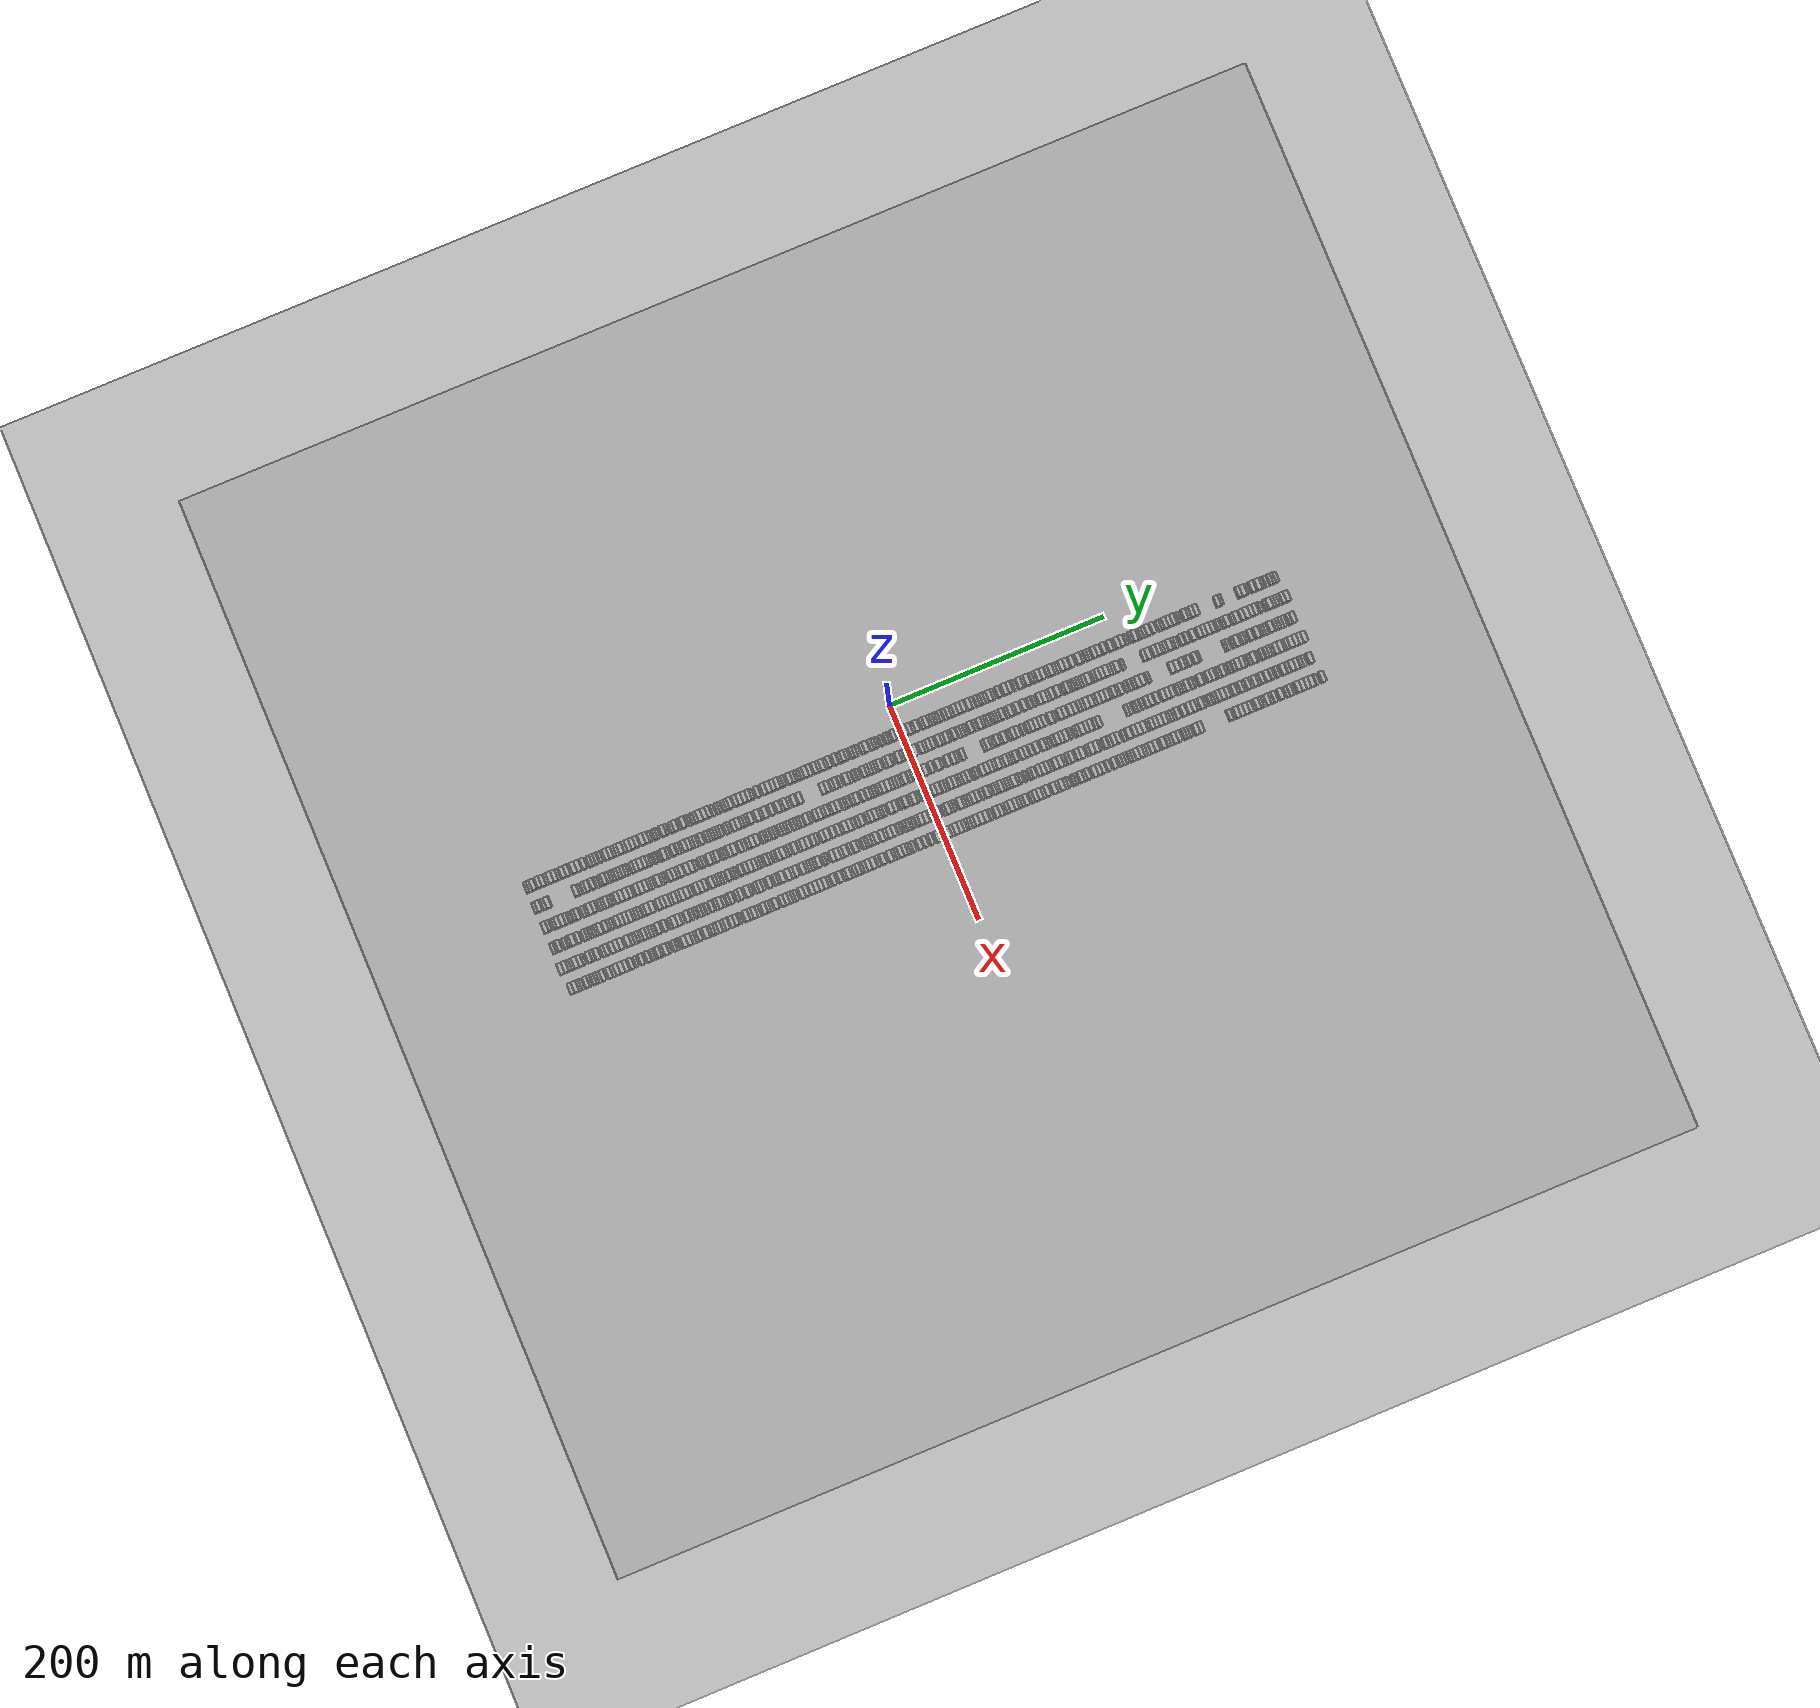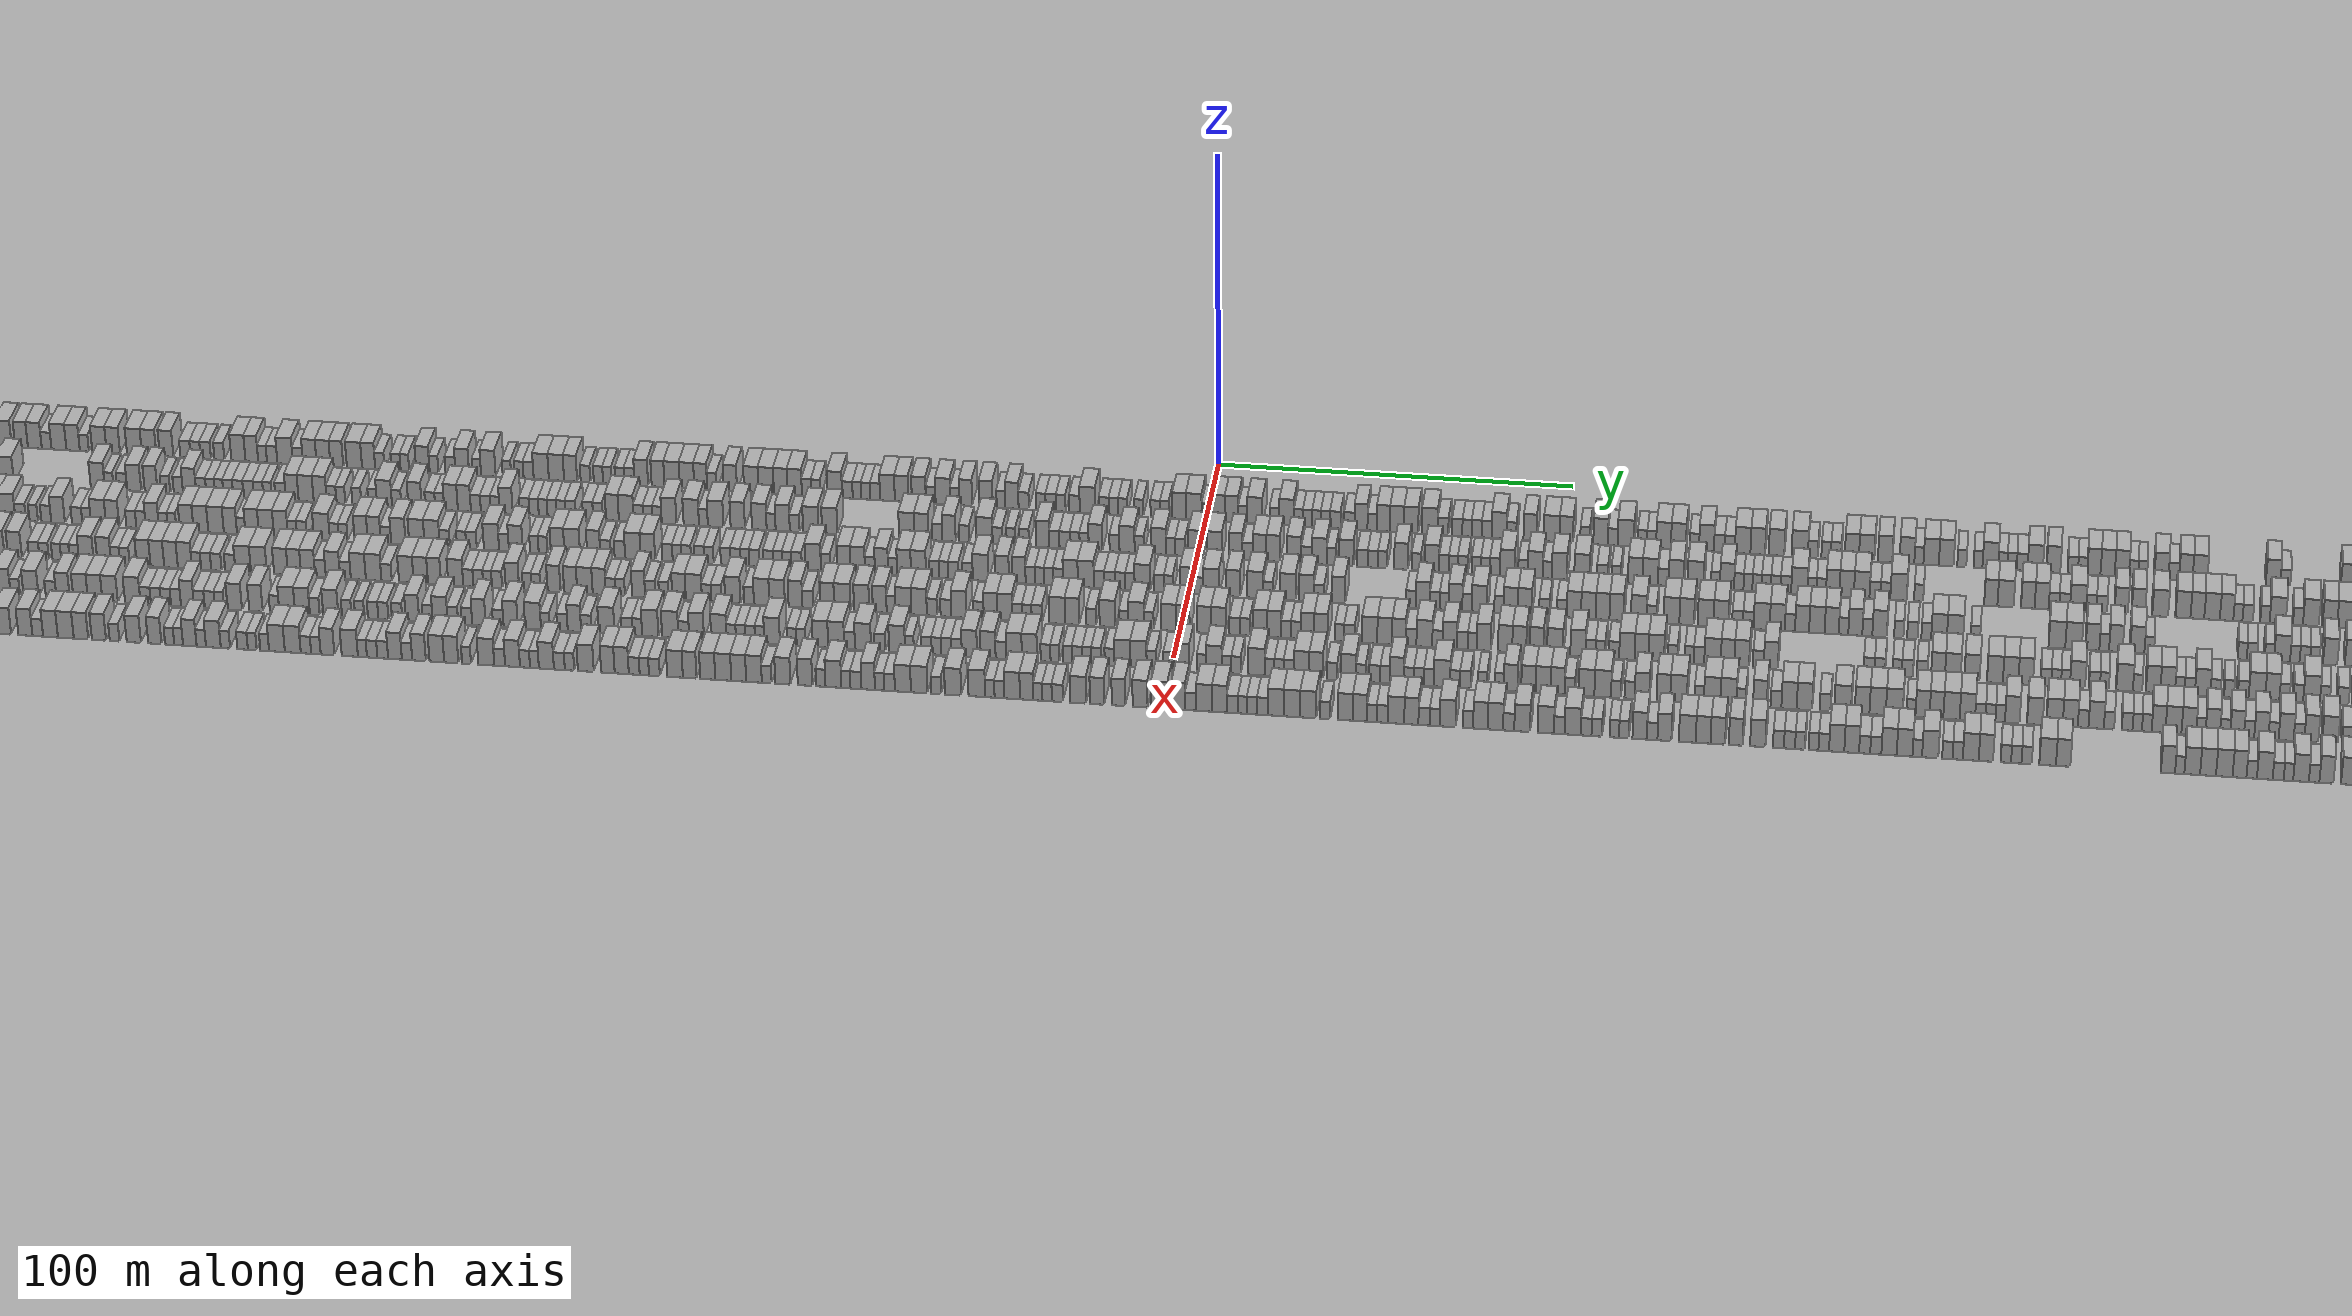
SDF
<?xml version="1.0" encoding="utf-8"?>

<sdf version="1.6">

   <world name="default">

      <gui fullscreen="0">

         <camera name="user_camera">

            <pose>-15 0 4.57585 0 0 0</pose>

            <view_controller>orbit</view_controller>

         </camera>

      </gui>

      <scene>

         <sky>

           <clouds>

             <speed>12</speed>

           </clouds>

         </sky>

         <ambient>0.4 0.4 0.4 1</ambient>

         <background>0.7 0.7 0.7 1</background>

         <shadows>1</shadows>

      </scene>

      <gravity>0 0 -9.8066</gravity>

      <magnetic_field>6e-06 2.3e-05 -4.2e-05</magnetic_field>

      <physics default="0" name="default_physics" type="ode">

         <ode>

            <solver>

               <type>quick</type>

               <iters>10</iters>

               <sor>1.0</sor>

               <use_dynamic_moi_rescaling>0</use_dynamic_moi_rescaling>

            </solver>

            <constraints>

               <cfm>0</cfm>

               <erp>0.2</erp>

               <contact_max_correcting_vel>100</contact_max_correcting_vel>

               <contact_surface_layer>0.001</contact_surface_layer>

            </constraints>

         </ode>

         <max_step_size>0.004</max_step_size>

         <real_time_factor>1</real_time_factor>

         <real_time_update_rate>250</real_time_update_rate>

      </physics>

      <light name="sun" type="directional">

         <cast_shadows>1</cast_shadows>

         <pose>0 0 10 0 0 0</pose>

         <diffuse>0.8 0.8 0.8 1</diffuse>

         <specular>0.2 0.2 0.2 1</specular>

         <attenuation>

            <range>1000</range>

            <constant>0.9</constant>

            <linear>0.01</linear>

            <quadratic>0.001</quadratic>

         </attenuation>

         <direction>-0.5 0.1 -0.9</direction>

      </light>

      <include>

         <name>ground_plane_1</name>

         <uri>model://HANNAS_ground_plane</uri>

         <pose>0 0 0  0 0 0</pose>

      </include>

      <include>

         <name>ground_plane_2</name>

         <uri>model://HANNAS_ground_plane</uri>

         <pose>100 0 0  0 0 0</pose>

      </include>

      <model name="building_1">

         <static>1</static>

         <pose frame="">25.0000 -348.7715 0 0.000000 0.000000 0.000000</pose>

         <link name="link">

            <pose frame="">0 0 3.00 0 0 0</pose>

            <collision name="collision">

               <geometry>

                  <box>

                     <size>10.0000 2.4570 6.0000</size>

                  </box>

               </geometry>

               <max_contacts>10</max_contacts>

               <surface>

                  <contact>

                     <ode/>

                  </contact>

                  <bounce/>

                  <friction>

                     <torsional>

                        <ode/>

                     </torsional>

                     <ode/>

                  </friction>

               </surface>

            </collision>

            <visual name="visual">

               <cast_shadows>0</cast_shadows>

               <geometry>

                  <box>

                     <size>10.0000 2.4570 6.0000</size>

                  </box>

               </geometry>

               <material>

                  <script>

                     <uri>model://HANNAS_wall/materials/scripts</uri>

                     <uri>model://HANNAS_wall/materials/textures</uri>

                     <name>vrc/HANNAS_wall</name>

                  </script>

               </material>

            </visual>

            <self_collide>0</self_collide>

            <enable_wind>0</enable_wind>

            <kinematic>0</kinematic>

         </link>

      </model>

      <model name="building_2">

         <static>1</static>

         <pose frame="">25.0000 -346.0925 0 0.000000 0.000000 0.000000</pose>

         <link name="link">

            <pose frame="">0 0 3.00 0 0 0</pose>

            <collision name="collision">

               <geometry>

                  <box>

                     <size>10.0000 2.9010 6.0000</size>

                  </box>

               </geometry>

               <max_contacts>10</max_contacts>

               <surface>

                  <contact>

                     <ode/>

                  </contact>

                  <bounce/>

                  <friction>

                     <torsional>

                        <ode/>

                     </torsional>

                     <ode/>

                  </friction>

               </surface>

            </collision>

            <visual name="visual">

               <cast_shadows>0</cast_shadows>

               <geometry>

                  <box>

                     <size>10.0000 2.9010 6.0000</size>

                  </box>

               </geometry>

               <material>

                  <script>

                     <uri>model://HANNAS_wall/materials/scripts</uri>

                     <uri>model://HANNAS_wall/materials/textures</uri>

                     <name>vrc/HANNAS_wall</name>

                  </script>

               </material>

            </visual>

            <self_collide>0</self_collide>

            <enable_wind>0</enable_wind>

            <kinematic>0</kinematic>

         </link>

      </model>

      <model name="building_3">

         <static>1</static>

         <pose frame="">25.0000 -342.5536 0 0.000000 0.000000 0.000000</pose>

         <link name="link">

            <pose frame="">0 0 4.50 0 0 0</pose>

            <collision name="collision">

               <geometry>

                  <box>

                     <size>10.0000 4.1769 9.0000</size>

                  </box>

               </geometry>

               <max_contacts>10</max_contacts>

               <surface>

                  <contact>

                     <ode/>

                  </contact>

                  <bounce/>

                  <friction>

                     <torsional>

                        <ode/>

                     </torsional>

                     <ode/>

                  </friction>

               </surface>

            </collision>

            <visual name="visual">

               <cast_shadows>0</cast_shadows>

               <geometry>

                  <box>

                     <size>10.0000 4.1769 9.0000</size>

                  </box>

               </geometry>

               <material>

                  <script>

                     <uri>model://HANNAS_wall/materials/scripts</uri>

                     <uri>model://HANNAS_wall/materials/textures</uri>

                     <name>vrc/HANNAS_wall</name>

                  </script>

               </material>

            </visual>

            <self_collide>0</self_collide>

            <enable_wind>0</enable_wind>

            <kinematic>0</kinematic>

         </link>

      </model>

      <model name="building_4">

         <static>1</static>

         <pose frame="">25.0000 -337.6333 0 0.000000 0.000000 0.000000</pose>

         <link name="link">

            <pose frame="">0 0 4.50 0 0 0</pose>

            <collision name="collision">

               <geometry>

                  <box>

                     <size>10.0000 3.6635 9.0000</size>

                  </box>

               </geometry>

               <max_contacts>10</max_contacts>

               <surface>

                  <contact>

                     <ode/>

                  </contact>

                  <bounce/>

                  <friction>

                     <torsional>

                        <ode/>

                     </torsional>

                     <ode/>

                  </friction>

               </surface>

            </collision>

            <visual name="visual">

               <cast_shadows>0</cast_shadows>

               <geometry>

                  <box>

                     <size>10.0000 3.6635 9.0000</size>

                  </box>

               </geometry>

               <material>

                  <script>

                     <uri>model://HANNAS_wall/materials/scripts</uri>

                     <uri>model://HANNAS_wall/materials/textures</uri>

                     <name>vrc/HANNAS_wall</name>

                  </script>

               </material>

            </visual>

            <self_collide>0</self_collide>

            <enable_wind>0</enable_wind>

            <kinematic>0</kinematic>

         </link>

      </model>

      <model name="building_5">

         <static>1</static>

         <pose frame="">25.0000 -333.7920 0 0.000000 0.000000 0.000000</pose>

         <link name="link">

            <pose frame="">0 0 4.50 0 0 0</pose>

            <collision name="collision">

               <geometry>

                  <box>

                     <size>10.0000 4.0192 9.0000</size>

                  </box>

               </geometry>

               <max_contacts>10</max_contacts>

               <surface>

                  <contact>

                     <ode/>

                  </contact>

                  <bounce/>

                  <friction>

                     <torsional>

                        <ode/>

                     </torsional>

                     <ode/>

                  </friction>

               </surface>

            </collision>

            <visual name="visual">

               <cast_shadows>0</cast_shadows>

               <geometry>

                  <box>

                     <size>10.0000 4.0192 9.0000</size>

                  </box>

               </geometry>

               <material>

                  <script>

                     <uri>model://HANNAS_wall/materials/scripts</uri>

                     <uri>model://HANNAS_wall/materials/textures</uri>

                     <name>vrc/HANNAS_wall</name>

                  </script>

               </material>

            </visual>

            <self_collide>0</self_collide>

            <enable_wind>0</enable_wind>

            <kinematic>0</kinematic>

         </link>

      </model>

      <model name="building_6">

         <static>1</static>

         <pose frame="">25.0000 -330.3741 0 0.000000 0.000000 0.000000</pose>

         <link name="link">

            <pose frame="">0 0 3.00 0 0 0</pose>

            <collision name="collision">

               <geometry>

                  <box>

                     <size>10.0000 2.8165 6.0000</size>

                  </box>

               </geometry>

               <max_contacts>10</max_contacts>

               <surface>

                  <contact>

                     <ode/>

                  </contact>

                  <bounce/>

                  <friction>

                     <torsional>

                        <ode/>

                     </torsional>

                     <ode/>

                  </friction>

               </surface>

            </collision>

            <visual name="visual">

               <cast_shadows>0</cast_shadows>

               <geometry>

                  <box>

                     <size>10.0000 2.8165 6.0000</size>

                  </box>

               </geometry>

               <material>

                  <script>

                     <uri>model://HANNAS_wall/materials/scripts</uri>

                     <uri>model://HANNAS_wall/materials/textures</uri>

                     <name>vrc/HANNAS_wall</name>

                  </script>

               </material>

            </visual>

            <self_collide>0</self_collide>

            <enable_wind>0</enable_wind>

            <kinematic>0</kinematic>

         </link>

      </model>

      <model name="building_7">

         <static>1</static>

         <pose frame="">25.0000 -326.8023 0 0.000000 0.000000 0.000000</pose>

         <link name="link">

            <pose frame="">0 0 4.50 0 0 0</pose>

            <collision name="collision">

               <geometry>

                  <box>

                     <size>10.0000 4.3272 9.0000</size>

                  </box>

               </geometry>

               <max_contacts>10</max_contacts>

               <surface>

                  <contact>

                     <ode/>

                  </contact>

                  <bounce/>

                  <friction>

                     <torsional>

                        <ode/>

                     </torsional>

                     <ode/>

                  </friction>

               </surface>

            </collision>

            <visual name="visual">

               <cast_shadows>0</cast_shadows>

               <geometry>

                  <box>

                     <size>10.0000 4.3272 9.0000</size>

                  </box>

               </geometry>

               <material>

                  <script>

                     <uri>model://HANNAS_wall/materials/scripts</uri>

                     <uri>model://HANNAS_wall/materials/textures</uri>

                     <name>vrc/HANNAS_wall</name>

                  </script>

               </material>

            </visual>

            <self_collide>0</self_collide>

            <enable_wind>0</enable_wind>

            <kinematic>0</kinematic>

         </link>

      </model>

      <model name="building_8">

         <static>1</static>

         <pose frame="">25.0000 -322.7035 0 0.000000 0.000000 0.000000</pose>

         <link name="link">

            <pose frame="">0 0 4.50 0 0 0</pose>

            <collision name="collision">

               <geometry>

                  <box>

                     <size>10.0000 3.8703 9.0000</size>

                  </box>

               </geometry>

               <max_contacts>10</max_contacts>

               <surface>

                  <contact>

                     <ode/>

                  </contact>

                  <bounce/>

                  <friction>

                     <torsional>

                        <ode/>

                     </torsional>

                     <ode/>

                  </friction>

               </surface>

            </collision>

            <visual name="visual">

               <cast_shadows>0</cast_shadows>

               <geometry>

                  <box>

                     <size>10.0000 3.8703 9.0000</size>

                  </box>

               </geometry>

               <material>

                  <script>

                     <uri>model://HANNAS_wall/materials/scripts</uri>

                     <uri>model://HANNAS_wall/materials/textures</uri>

                     <name>vrc/HANNAS_wall</name>

                  </script>

               </material>

            </visual>

            <self_collide>0</self_collide>

            <enable_wind>0</enable_wind>

            <kinematic>0</kinematic>

         </link>

      </model>

      <model name="building_9">

         <static>1</static>

         <pose frame="">25.0000 -319.4609 0 0.000000 0.000000 0.000000</pose>

         <link name="link">

            <pose frame="">0 0 3.00 0 0 0</pose>

            <collision name="collision">

               <geometry>

                  <box>

                     <size>10.0000 2.6149 6.0000</size>

                  </box>

               </geometry>

               <max_contacts>10</max_contacts>

               <surface>

                  <contact>

                     <ode/>

                  </contact>

                  <bounce/>

                  <friction>

                     <torsional>

                        <ode/>

                     </torsional>

                     <ode/>

                  </friction>

               </surface>

            </collision>

            <visual name="visual">

               <cast_shadows>0</cast_shadows>

               <geometry>

                  <box>

                     <size>10.0000 2.6149 6.0000</size>

                  </box>

               </geometry>

               <material>

                  <script>

                     <uri>model://HANNAS_wall/materials/scripts</uri>

                     <uri>model://HANNAS_wall/materials/textures</uri>

                     <name>vrc/HANNAS_wall</name>

                  </script>

               </material>

            </visual>

            <self_collide>0</self_collide>

            <enable_wind>0</enable_wind>

            <kinematic>0</kinematic>

         </link>

      </model>

      <model name="building_10">

         <static>1</static>

         <pose frame="">25.0000 -315.0740 0 0.000000 0.000000 0.000000</pose>

         <link name="link">

            <pose frame="">0 0 4.50 0 0 0</pose>

            <collision name="collision">

               <geometry>

                  <box>

                     <size>10.0000 4.1590 9.0000</size>

                  </box>

               </geometry>

               <max_contacts>10</max_contacts>

               <surface>

                  <contact>

                     <ode/>

                  </contact>

                  <bounce/>

                  <friction>

                     <torsional>

                        <ode/>

                     </torsional>

                     <ode/>

                  </friction>

               </surface>

            </collision>

            <visual name="visual">

               <cast_shadows>0</cast_shadows>

               <geometry>

                  <box>

                     <size>10.0000 4.1590 9.0000</size>

                  </box>

               </geometry>

               <material>

                  <script>

                     <uri>model://HANNAS_wall/materials/scripts</uri>

                     <uri>model://HANNAS_wall/materials/textures</uri>

                     <name>vrc/HANNAS_wall</name>

                  </script>

               </material>

            </visual>

            <self_collide>0</self_collide>

            <enable_wind>0</enable_wind>

            <kinematic>0</kinematic>

         </link>

      </model>

      <model name="building_11">

         <static>1</static>

         <pose frame="">25.0000 -311.0655 0 0.000000 0.000000 0.000000</pose>

         <link name="link">

            <pose frame="">0 0 4.50 0 0 0</pose>

            <collision name="collision">

               <geometry>

                  <box>

                     <size>10.0000 3.8581 9.0000</size>

                  </box>

               </geometry>

               <max_contacts>10</max_contacts>

               <surface>

                  <contact>

                     <ode/>

                  </contact>

                  <bounce/>

                  <friction>

                     <torsional>

                        <ode/>

                     </torsional>

                     <ode/>

                  </friction>

               </surface>

            </collision>

            <visual name="visual">

               <cast_shadows>0</cast_shadows>

               <geometry>

                  <box>

                     <size>10.0000 3.8581 9.0000</size>

                  </box>

               </geometry>

               <material>

                  <script>

                     <uri>model://HANNAS_wall/materials/scripts</uri>

                     <uri>model://HANNAS_wall/materials/textures</uri>

                     <name>vrc/HANNAS_wall</name>

                  </script>

               </material>

            </visual>

            <self_collide>0</self_collide>

            <enable_wind>0</enable_wind>

            <kinematic>0</kinematic>

         </link>

      </model>

      <model name="building_12">

         <static>1</static>

         <pose frame="">25.0000 -304.9729 0 0.000000 0.000000 0.000000</pose>

         <link name="link">

            <pose frame="">0 0 4.50 0 0 0</pose>

            <collision name="collision">

               <geometry>

                  <box>

                     <size>10.0000 4.3270 9.0000</size>

                  </box>

               </geometry>

               <max_contacts>10</max_contacts>

               <surface>

                  <contact>

                     <ode/>

                  </contact>

                  <bounce/>

                  <friction>

                     <torsional>

                        <ode/>

                     </torsional>

                     <ode/>

                  </friction>

               </surface>

            </collision>

            <visual name="visual">

               <cast_shadows>0</cast_shadows>

               <geometry>

                  <box>

                     <size>10.0000 4.3270 9.0000</size>

                  </box>

               </geometry>

               <material>

                  <script>

                     <uri>model://HANNAS_wall/materials/scripts</uri>

                     <uri>model://HANNAS_wall/materials/textures</uri>

                     <name>vrc/HANNAS_wall</name>

                  </script>

               </material>

            </visual>

            <self_collide>0</self_collide>

            <enable_wind>0</enable_wind>

            <kinematic>0</kinematic>

         </link>

      </model>

      <model name="building_13">

         <static>1</static>

         <pose frame="">25.0000 -300.7179 0 0.000000 0.000000 0.000000</pose>

         <link name="link">

            <pose frame="">0 0 4.50 0 0 0</pose>

            <collision name="collision">

               <geometry>

                  <box>

                     <size>10.0000 4.1830 9.0000</size>

                  </box>

               </geometry>

               <max_contacts>10</max_contacts>

               <surface>

                  <contact>

                     <ode/>

                  </contact>

                  <bounce/>

                  <friction>

                     <torsional>

                        <ode/>

                     </torsional>

                     <ode/>

                  </friction>

               </surface>

            </collision>

            <visual name="visual">

               <cast_shadows>0</cast_shadows>

               <geometry>

                  <box>

                     <size>10.0000 4.1830 9.0000</size>

                  </box>

               </geometry>

               <material>

                  <script>

                     <uri>model://HANNAS_wall/materials/scripts</uri>

                     <uri>model://HANNAS_wall/materials/textures</uri>

                     <name>vrc/HANNAS_wall</name>

                  </script>

               </material>

            </visual>

            <self_collide>0</self_collide>

            <enable_wind>0</enable_wind>

            <kinematic>0</kinematic>

         </link>

      </model>

      <model name="building_14">

         <static>1</static>

         <pose frame="">25.0000 -295.6711 0 0.000000 0.000000 0.000000</pose>

         <link name="link">

            <pose frame="">0 0 4.50 0 0 0</pose>

            <collision name="collision">

               <geometry>

                  <box>

                     <size>10.0000 3.9105 9.0000</size>

                  </box>

               </geometry>

               <max_contacts>10</max_contacts>

               <surface>

                  <contact>

                     <ode/>

                  </contact>

                  <bounce/>

                  <friction>

                     <torsional>

                        <ode/>

                     </torsional>

                     <ode/>

                  </friction>

               </surface>

            </collision>

            <visual name="visual">

               <cast_shadows>0</cast_shadows>

               <geometry>

                  <box>

                     <size>10.0000 3.9105 9.0000</size>

                  </box>

               </geometry>

               <material>

                  <script>

                     <uri>model://HANNAS_wall/materials/scripts</uri>

                     <uri>model://HANNAS_wall/materials/textures</uri>

                     <name>vrc/HANNAS_wall</name>

                  </script>

               </material>

            </visual>

            <self_collide>0</self_collide>

            <enable_wind>0</enable_wind>

            <kinematic>0</kinematic>

         </link>

      </model>

      <model name="building_15">

         <static>1</static>

         <pose frame="">25.0000 -290.2238 0 0.000000 0.000000 0.000000</pose>

         <link name="link">

            <pose frame="">0 0 3.00 0 0 0</pose>

            <collision name="collision">

               <geometry>

                  <box>

                     <size>10.0000 2.9841 6.0000</size>

                  </box>

               </geometry>

               <max_contacts>10</max_contacts>

               <surface>

                  <contact>

                     <ode/>

                  </contact>

                  <bounce/>

                  <friction>

                     <torsional>

                        <ode/>

                     </torsional>

                     <ode/>

                  </friction>

               </surface>

            </collision>

            <visual name="visual">

               <cast_shadows>0</cast_shadows>

               <geometry>

                  <box>

                     <size>10.0000 2.9841 6.0000</size>

                  </box>

               </geometry>

               <material>

                  <script>

                     <uri>model://HANNAS_wall/materials/scripts</uri>

                     <uri>model://HANNAS_wall/materials/textures</uri>

                     <name>vrc/HANNAS_wall</name>

                  </script>

               </material>

            </visual>

            <self_collide>0</self_collide>

            <enable_wind>0</enable_wind>

            <kinematic>0</kinematic>

         </link>

      </model>

      <model name="building_16">

         <static>1</static>

         <pose frame="">25.0000 -287.3022 0 0.000000 0.000000 0.000000</pose>

         <link name="link">

            <pose frame="">0 0 3.00 0 0 0</pose>

            <collision name="collision">

               <geometry>

                  <box>

                     <size>10.0000 2.8589 6.0000</size>

                  </box>

               </geometry>

               <max_contacts>10</max_contacts>

               <surface>

                  <contact>

                     <ode/>

                  </contact>

                  <bounce/>

                  <friction>

                     <torsional>

                        <ode/>

                     </torsional>

                     <ode/>

                  </friction>

               </surface>

            </collision>

            <visual name="visual">

               <cast_shadows>0</cast_shadows>

               <geometry>

                  <box>

                     <size>10.0000 2.8589 6.0000</size>

                  </box>

               </geometry>

               <material>

                  <script>

                     <uri>model://HANNAS_wall/materials/scripts</uri>

                     <uri>model://HANNAS_wall/materials/textures</uri>

                     <name>vrc/HANNAS_wall</name>

                  </script>

               </material>

            </visual>

            <self_collide>0</self_collide>

            <enable_wind>0</enable_wind>

            <kinematic>0</kinematic>

         </link>

      </model>

      <model name="building_17">

         <static>1</static>

         <pose frame="">25.0000 -284.3892 0 0.000000 0.000000 0.000000</pose>

         <link name="link">

            <pose frame="">0 0 3.00 0 0 0</pose>

            <collision name="collision">

               <geometry>

                  <box>

                     <size>10.0000 2.9672 6.0000</size>

                  </box>

               </geometry>

               <max_contacts>10</max_contacts>

               <surface>

                  <contact>

                     <ode/>

                  </contact>

                  <bounce/>

                  <friction>

                     <torsional>

                        <ode/>

                     </torsional>

                     <ode/>

                  </friction>

               </surface>

            </collision>

            <visual name="visual">

               <cast_shadows>0</cast_shadows>

               <geometry>

                  <box>

                     <size>10.0000 2.9672 6.0000</size>

                  </box>

               </geometry>

               <material>

                  <script>

                     <uri>model://HANNAS_wall/materials/scripts</uri>

                     <uri>model://HANNAS_wall/materials/textures</uri>

                     <name>vrc/HANNAS_wall</name>

                  </script>

               </material>

            </visual>

            <self_collide>0</self_collide>

            <enable_wind>0</enable_wind>

            <kinematic>0</kinematic>

         </link>

      </model>

      <model name="building_18">

         <static>1</static>

         <pose frame="">25.0000 -280.4639 0 0.000000 0.000000 0.000000</pose>

         <link name="link">

            <pose frame="">0 0 3.00 0 0 0</pose>

            <collision name="collision">

               <geometry>

                  <box>

                     <size>10.0000 2.8833 6.0000</size>

                  </box>

               </geometry>

               <max_contacts>10</max_contacts>

               <surface>

                  <contact>

                     <ode/>

                  </contact>

                  <bounce/>

                  <friction>

                     <torsional>

                        <ode/>

                     </torsional>

                     <ode/>

                  </friction>

               </surface>

            </collision>

            <visual name="visual">

               <cast_shadows>0</cast_shadows>

               <geometry>

                  <box>

                     <size>10.0000 2.8833 6.0000</size>

                  </box>

               </geometry>

               <material>

                  <script>

                     <uri>model://HANNAS_wall/materials/scripts</uri>

                     <uri>model://HANNAS_wall/materials/textures</uri>

                     <name>vrc/HANNAS_wall</name>

                  </script>

               </material>

            </visual>

            <self_collide>0</self_collide>

            <enable_wind>0</enable_wind>

            <kinematic>0</kinematic>

         </link>

      </model>

      <model name="building_19">

         <static>1</static>

         <pose frame="">25.0000 -274.9902 0 0.000000 0.000000 0.000000</pose>

         <link name="link">

            <pose frame="">0 0 4.50 0 0 0</pose>

            <collision name="collision">

               <geometry>

                  <box>

                     <size>10.0000 4.0641 9.0000</size>

                  </box>

               </geometry>

               <max_contacts>10</max_contacts>

               <surface>

                  <contact>

                     <ode/>

                  </contact>

                  <bounce/>

                  <friction>

                     <torsional>

                        <ode/>

                     </torsional>

                     <ode/>

                  </friction>

               </surface>

            </collision>

            <visual name="visual">

               <cast_shadows>0</cast_shadows>

               <geometry>

                  <box>

                     <size>10.0000 4.0641 9.0000</size>

                  </box>

               </geometry>

               <material>

                  <script>

                     <uri>model://HANNAS_wall/materials/scripts</uri>

                     <uri>model://HANNAS_wall/materials/textures</uri>

                     <name>vrc/HANNAS_wall</name>

                  </script>

               </material>

            </visual>

            <self_collide>0</self_collide>

            <enable_wind>0</enable_wind>

            <kinematic>0</kinematic>

         </link>

      </model>

      <model name="building_20">

         <static>1</static>

         <pose frame="">25.0000 -271.1301 0 0.000000 0.000000 0.000000</pose>

         <link name="link">

            <pose frame="">0 0 4.50 0 0 0</pose>

            <collision name="collision">

               <geometry>

                  <box>

                     <size>10.0000 3.6562 9.0000</size>

                  </box>

               </geometry>

               <max_contacts>10</max_contacts>

               <surface>

                  <contact>

                     <ode/>

                  </contact>

                  <bounce/>

                  <friction>

                     <torsional>

                        <ode/>

                     </torsional>

                     <ode/>

                  </friction>

               </surface>

            </collision>

            <visual name="visual">

               <cast_shadows>0</cast_shadows>

               <geometry>

                  <box>

                     <size>10.0000 3.6562 9.0000</size>

                  </box>

               </geometry>

               <material>

                  <script>

                     <uri>model://HANNAS_wall/materials/scripts</uri>

                     <uri>model://HANNAS_wall/materials/textures</uri>

                     <name>vrc/HANNAS_wall</name>

                  </script>

               </material>

            </visual>

            <self_collide>0</self_collide>

            <enable_wind>0</enable_wind>

            <kinematic>0</kinematic>

         </link>

      </model>

      <model name="building_21">

         <static>1</static>

         <pose frame="">25.0000 -268.0399 0 0.000000 0.000000 0.000000</pose>

         <link name="link">

            <pose frame="">0 0 3.00 0 0 0</pose>

            <collision name="collision">

               <geometry>

                  <box>

                     <size>10.0000 2.5243 6.0000</size>

                  </box>

               </geometry>

               <max_contacts>10</max_contacts>

               <surface>

                  <contact>

                     <ode/>

                  </contact>

                  <bounce/>

                  <friction>

                     <torsional>

                        <ode/>

                     </torsional>

                     <ode/>

                  </friction>

               </surface>

            </collision>

            <visual name="visual">

               <cast_shadows>0</cast_shadows>

               <geometry>

                  <box>

                     <size>10.0000 2.5243 6.0000</size>

                  </box>

               </geometry>

               <material>

                  <script>

                     <uri>model://HANNAS_wall/materials/scripts</uri>

                     <uri>model://HANNAS_wall/materials/textures</uri>

                     <name>vrc/HANNAS_wall</name>

                  </script>

               </material>

            </visual>

            <self_collide>0</self_collide>

            <enable_wind>0</enable_wind>

            <kinematic>0</kinematic>

         </link>

      </model>

      <model name="building_22">

         <static>1</static>

         <pose frame="">25.0000 -265.2825 0 0.000000 0.000000 0.000000</pose>

         <link name="link">

            <pose frame="">0 0 3.00 0 0 0</pose>

            <collision name="collision">

               <geometry>

                  <box>

                     <size>10.0000 2.9905 6.0000</size>

                  </box>

               </geometry>

               <max_contacts>10</max_contacts>

               <surface>

                  <contact>

                     <ode/>

                  </contact>

                  <bounce/>

                  <friction>

                     <torsional>

                        <ode/>

                     </torsional>

                     <ode/>

                  </friction>

               </surface>

            </collision>

            <visual name="visual">

               <cast_shadows>0</cast_shadows>

               <geometry>

                  <box>

                     <size>10.0000 2.9905 6.0000</size>

                  </box>

               </geometry>

               <material>

                  <script>

                     <uri>model://HANNAS_wall/materials/scripts</uri>

                     <uri>model://HANNAS_wall/materials/textures</uri>

                     <name>vrc/HANNAS_wall</name>

                  </script>

               </material>

            </visual>

            <self_collide>0</self_collide>

            <enable_wind>0</enable_wind>

            <kinematic>0</kinematic>

         </link>

      </model>

      <model name="building_23">

         <static>1</static>

         <pose frame="">25.0000 -261.5380 0 0.000000 0.000000 0.000000</pose>

         <link name="link">

            <pose frame="">0 0 4.50 0 0 0</pose>

            <collision name="collision">

               <geometry>

                  <box>

                     <size>10.0000 4.4985 9.0000</size>

                  </box>

               </geometry>

               <max_contacts>10</max_contacts>

               <surface>

                  <contact>

                     <ode/>

                  </contact>

                  <bounce/>

                  <friction>

                     <torsional>

                        <ode/>

                     </torsional>

                     <ode/>

                  </friction>

               </surface>

            </collision>

            <visual name="visual">

               <cast_shadows>0</cast_shadows>

               <geometry>

                  <box>

                     <size>10.0000 4.4985 9.0000</size>

                  </box>

               </geometry>

               <material>

                  <script>

                     <uri>model://HANNAS_wall/materials/scripts</uri>

                     <uri>model://HANNAS_wall/materials/textures</uri>

                     <name>vrc/HANNAS_wall</name>

                  </script>

               </material>

            </visual>

            <self_collide>0</self_collide>

            <enable_wind>0</enable_wind>

            <kinematic>0</kinematic>

         </link>

      </model>

      <model name="building_24">

         <static>1</static>

         <pose frame="">25.0000 -257.8299 0 0.000000 0.000000 0.000000</pose>

         <link name="link">

            <pose frame="">0 0 3.00 0 0 0</pose>

            <collision name="collision">

               <geometry>

                  <box>

                     <size>10.0000 2.9176 6.0000</size>

                  </box>

               </geometry>

               <max_contacts>10</max_contacts>

               <surface>

                  <contact>

                     <ode/>

                  </contact>

                  <bounce/>

                  <friction>

                     <torsional>

                        <ode/>

                     </torsional>

                     <ode/>

                  </friction>

               </surface>

            </collision>

            <visual name="visual">

               <cast_shadows>0</cast_shadows>

               <geometry>

                  <box>

                     <size>10.0000 2.9176 6.0000</size>

                  </box>

               </geometry>

               <material>

                  <script>

                     <uri>model://HANNAS_wall/materials/scripts</uri>

                     <uri>model://HANNAS_wall/materials/textures</uri>

                     <name>vrc/HANNAS_wall</name>

                  </script>

               </material>

            </visual>

            <self_collide>0</self_collide>

            <enable_wind>0</enable_wind>

            <kinematic>0</kinematic>

         </link>

      </model>

      <model name="building_25">

         <static>1</static>

         <pose frame="">25.0000 -254.4162 0 0.000000 0.000000 0.000000</pose>

         <link name="link">

            <pose frame="">0 0 4.50 0 0 0</pose>

            <collision name="collision">

               <geometry>

                  <box>

                     <size>10.0000 3.9098 9.0000</size>

                  </box>

               </geometry>

               <max_contacts>10</max_contacts>

               <surface>

                  <contact>

                     <ode/>

                  </contact>

                  <bounce/>

                  <friction>

                     <torsional>

                        <ode/>

                     </torsional>

                     <ode/>

                  </friction>

               </surface>

            </collision>

            <visual name="visual">

               <cast_shadows>0</cast_shadows>

               <geometry>

                  <box>

                     <size>10.0000 3.9098 9.0000</size>

                  </box>

               </geometry>

               <material>

                  <script>

                     <uri>model://HANNAS_wall/materials/scripts</uri>

                     <uri>model://HANNAS_wall/materials/textures</uri>

                     <name>vrc/HANNAS_wall</name>

                  </script>

               </material>

            </visual>

            <self_collide>0</self_collide>

            <enable_wind>0</enable_wind>

            <kinematic>0</kinematic>

         </link>

      </model>

      <model name="building_26">

         <static>1</static>

         <pose frame="">25.0000 -250.4763 0 0.000000 0.000000 0.000000</pose>

         <link name="link">

            <pose frame="">0 0 4.50 0 0 0</pose>

            <collision name="collision">

               <geometry>

                  <box>

                     <size>10.0000 3.9700 9.0000</size>

                  </box>

               </geometry>

               <max_contacts>10</max_contacts>

               <surface>

                  <contact>

                     <ode/>

                  </contact>

                  <bounce/>

                  <friction>

                     <torsional>

                        <ode/>

                     </torsional>

                     <ode/>

                  </friction>

               </surface>

            </collision>

            <visual name="visual">

               <cast_shadows>0</cast_shadows>

               <geometry>

                  <box>

                     <size>10.0000 3.9700 9.0000</size>

                  </box>

               </geometry>

               <material>

                  <script>

                     <uri>model://HANNAS_wall/materials/scripts</uri>

                     <uri>model://HANNAS_wall/materials/textures</uri>

                     <name>vrc/HANNAS_wall</name>

                  </script>

               </material>

            </visual>

            <self_collide>0</self_collide>

            <enable_wind>0</enable_wind>

            <kinematic>0</kinematic>

         </link>

      </model>

      <model name="building_27">

         <static>1</static>

         <pose frame="">25.0000 -246.6577 0 0.000000 0.000000 0.000000</pose>

         <link name="link">

            <pose frame="">0 0 4.50 0 0 0</pose>

            <collision name="collision">

               <geometry>

                  <box>

                     <size>10.0000 3.6672 9.0000</size>

                  </box>

               </geometry>

               <max_contacts>10</max_contacts>

               <surface>

                  <contact>

                     <ode/>

                  </contact>

                  <bounce/>

                  <friction>

                     <torsional>

                        <ode/>

                     </torsional>

                     <ode/>

                  </friction>

               </surface>

            </collision>

            <visual name="visual">

               <cast_shadows>0</cast_shadows>

               <geometry>

                  <box>

                     <size>10.0000 3.6672 9.0000</size>

                  </box>

               </geometry>

               <material>

                  <script>

                     <uri>model://HANNAS_wall/materials/scripts</uri>

                     <uri>model://HANNAS_wall/materials/textures</uri>

                     <name>vrc/HANNAS_wall</name>

                  </script>

               </material>

            </visual>

            <self_collide>0</self_collide>

            <enable_wind>0</enable_wind>

            <kinematic>0</kinematic>

         </link>

      </model>

      <model name="building_28">

         <static>1</static>

         <pose frame="">25.0000 -241.6378 0 0.000000 0.000000 0.000000</pose>

         <link name="link">

            <pose frame="">0 0 4.50 0 0 0</pose>

            <collision name="collision">

               <geometry>

                  <box>

                     <size>10.0000 4.3726 9.0000</size>

                  </box>

               </geometry>

               <max_contacts>10</max_contacts>

               <surface>

                  <contact>

                     <ode/>

                  </contact>

                  <bounce/>

                  <friction>

                     <torsional>

                        <ode/>

                     </torsional>

                     <ode/>

                  </friction>

               </surface>

            </collision>

            <visual name="visual">

               <cast_shadows>0</cast_shadows>

               <geometry>

                  <box>

                     <size>10.0000 4.3726 9.0000</size>

                  </box>

               </geometry>

               <material>

                  <script>

                     <uri>model://HANNAS_wall/materials/scripts</uri>

                     <uri>model://HANNAS_wall/materials/textures</uri>

                     <name>vrc/HANNAS_wall</name>

                  </script>

               </material>

            </visual>

            <self_collide>0</self_collide>

            <enable_wind>0</enable_wind>

            <kinematic>0</kinematic>

         </link>

      </model>

      <model name="building_29">

         <static>1</static>

         <pose frame="">25.0000 -237.5588 0 0.000000 0.000000 0.000000</pose>

         <link name="link">

            <pose frame="">0 0 4.50 0 0 0</pose>

            <collision name="collision">

               <geometry>

                  <box>

                     <size>10.0000 3.7855 9.0000</size>

                  </box>

               </geometry>

               <max_contacts>10</max_contacts>

               <surface>

                  <contact>

                     <ode/>

                  </contact>

                  <bounce/>

                  <friction>

                     <torsional>

                        <ode/>

                     </torsional>

                     <ode/>

                  </friction>

               </surface>

            </collision>

            <visual name="visual">

               <cast_shadows>0</cast_shadows>

               <geometry>

                  <box>

                     <size>10.0000 3.7855 9.0000</size>

                  </box>

               </geometry>

               <material>

                  <script>

                     <uri>model://HANNAS_wall/materials/scripts</uri>

                     <uri>model://HANNAS_wall/materials/textures</uri>

                     <name>vrc/HANNAS_wall</name>

                  </script>

               </material>

            </visual>

            <self_collide>0</self_collide>

            <enable_wind>0</enable_wind>

            <kinematic>0</kinematic>

         </link>

      </model>

      <model name="building_30">

         <static>1</static>

         <pose frame="">25.0000 -234.3308 0 0.000000 0.000000 0.000000</pose>

         <link name="link">

            <pose frame="">0 0 3.00 0 0 0</pose>

            <collision name="collision">

               <geometry>

                  <box>

                     <size>10.0000 2.6704 6.0000</size>

                  </box>

               </geometry>

               <max_contacts>10</max_contacts>

               <surface>

                  <contact>

                     <ode/>

                  </contact>

                  <bounce/>

                  <friction>

                     <torsional>

                        <ode/>

                     </torsional>

                     <ode/>

                  </friction>

               </surface>

            </collision>

            <visual name="visual">

               <cast_shadows>0</cast_shadows>

               <geometry>

                  <box>

                     <size>10.0000 2.6704 6.0000</size>

                  </box>

               </geometry>

               <material>

                  <script>

                     <uri>model://HANNAS_wall/materials/scripts</uri>

                     <uri>model://HANNAS_wall/materials/textures</uri>

                     <name>vrc/HANNAS_wall</name>

                  </script>

               </material>

            </visual>

            <self_collide>0</self_collide>

            <enable_wind>0</enable_wind>

            <kinematic>0</kinematic>

         </link>

      </model>

      <model name="building_31">

         <static>1</static>

         <pose frame="">25.0000 -229.6946 0 0.000000 0.000000 0.000000</pose>

         <link name="link">

            <pose frame="">0 0 3.00 0 0 0</pose>

            <collision name="collision">

               <geometry>

                  <box>

                     <size>10.0000 2.6020 6.0000</size>

                  </box>

               </geometry>

               <max_contacts>10</max_contacts>

               <surface>

                  <contact>

                     <ode/>

                  </contact>

                  <bounce/>

                  <friction>

                     <torsional>

                        <ode/>

                     </torsional>

                     <ode/>

                  </friction>

               </surface>

            </collision>

            <visual name="visual">

               <cast_shadows>0</cast_shadows>

               <geometry>

                  <box>

                     <size>10.0000 2.6020 6.0000</size>

                  </box>

               </geometry>

               <material>

                  <script>

                     <uri>model://HANNAS_wall/materials/scripts</uri>

                     <uri>model://HANNAS_wall/materials/textures</uri>

                     <name>vrc/HANNAS_wall</name>

                  </script>

               </material>

            </visual>

            <self_collide>0</self_collide>

            <enable_wind>0</enable_wind>

            <kinematic>0</kinematic>

         </link>

      </model>

      <model name="building_32">

         <static>1</static>

         <pose frame="">25.0000 -227.1606 0 0.000000 0.000000 0.000000</pose>

         <link name="link">

            <pose frame="">0 0 3.00 0 0 0</pose>

            <collision name="collision">

               <geometry>

                  <box>

                     <size>10.0000 2.4660 6.0000</size>

                  </box>

               </geometry>

               <max_contacts>10</max_contacts>

               <surface>

                  <contact>

                     <ode/>

                  </contact>

                  <bounce/>

                  <friction>

                     <torsional>

                        <ode/>

                     </torsional>

                     <ode/>

                  </friction>

               </surface>

            </collision>

            <visual name="visual">

               <cast_shadows>0</cast_shadows>

               <geometry>

                  <box>

                     <size>10.0000 2.4660 6.0000</size>

                  </box>

               </geometry>

               <material>

                  <script>

                     <uri>model://HANNAS_wall/materials/scripts</uri>

                     <uri>model://HANNAS_wall/materials/textures</uri>

                     <name>vrc/HANNAS_wall</name>

                  </script>

               </material>

            </visual>

            <self_collide>0</self_collide>

            <enable_wind>0</enable_wind>

            <kinematic>0</kinematic>

         </link>

      </model>

      <model name="building_33">

         <static>1</static>

         <pose frame="">25.0000 -221.9985 0 0.000000 0.000000 0.000000</pose>

         <link name="link">

            <pose frame="">0 0 4.50 0 0 0</pose>

            <collision name="collision">

               <geometry>

                  <box>

                     <size>10.0000 3.8582 9.0000</size>

                  </box>

               </geometry>

               <max_contacts>10</max_contacts>

               <surface>

                  <contact>

                     <ode/>

                  </contact>

                  <bounce/>

                  <friction>

                     <torsional>

                        <ode/>

                     </torsional>

                     <ode/>

                  </friction>

               </surface>

            </collision>

            <visual name="visual">

               <cast_shadows>0</cast_shadows>

               <geometry>

                  <box>

                     <size>10.0000 3.8582 9.0000</size>

                  </box>

               </geometry>

               <material>

                  <script>

                     <uri>model://HANNAS_wall/materials/scripts</uri>

                     <uri>model://HANNAS_wall/materials/textures</uri>

                     <name>vrc/HANNAS_wall</name>

                  </script>

               </material>

            </visual>

            <self_collide>0</self_collide>

            <enable_wind>0</enable_wind>

            <kinematic>0</kinematic>

         </link>

      </model>

      <model name="building_34">

         <static>1</static>

         <pose frame="">25.0000 -218.8048 0 0.000000 0.000000 0.000000</pose>

         <link name="link">

            <pose frame="">0 0 3.00 0 0 0</pose>

            <collision name="collision">

               <geometry>

                  <box>

                     <size>10.0000 2.5292 6.0000</size>

                  </box>

               </geometry>

               <max_contacts>10</max_contacts>

               <surface>

                  <contact>

                     <ode/>

                  </contact>

                  <bounce/>

                  <friction>

                     <torsional>

                        <ode/>

                     </torsional>

                     <ode/>

                  </friction>

               </surface>

            </collision>

            <visual name="visual">

               <cast_shadows>0</cast_shadows>

               <geometry>

                  <box>

                     <size>10.0000 2.5292 6.0000</size>

                  </box>

               </geometry>

               <material>

                  <script>

                     <uri>model://HANNAS_wall/materials/scripts</uri>

                     <uri>model://HANNAS_wall/materials/textures</uri>

                     <name>vrc/HANNAS_wall</name>

                  </script>

               </material>

            </visual>

            <self_collide>0</self_collide>

            <enable_wind>0</enable_wind>

            <kinematic>0</kinematic>

         </link>

      </model>

      <model name="building_35">

         <static>1</static>

         <pose frame="">25.0000 -214.0951 0 0.000000 0.000000 0.000000</pose>

         <link name="link">

            <pose frame="">0 0 3.00 0 0 0</pose>

            <collision name="collision">

               <geometry>

                  <box>

                     <size>10.0000 2.8903 6.0000</size>

                  </box>

               </geometry>

               <max_contacts>10</max_contacts>

               <surface>

                  <contact>

                     <ode/>

                  </contact>

                  <bounce/>

                  <friction>

                     <torsional>

                        <ode/>

                     </torsional>

                     <ode/>

                  </friction>

               </surface>

            </collision>

            <visual name="visual">

               <cast_shadows>0</cast_shadows>

               <geometry>

                  <box>

                     <size>10.0000 2.8903 6.0000</size>

                  </box>

               </geometry>

               <material>

                  <script>

                     <uri>model://HANNAS_wall/materials/scripts</uri>

                     <uri>model://HANNAS_wall/materials/textures</uri>

                     <name>vrc/HANNAS_wall</name>

                  </script>

               </material>

            </visual>

            <self_collide>0</self_collide>

            <enable_wind>0</enable_wind>

            <kinematic>0</kinematic>

         </link>

      </model>

      <model name="building_36">

         <static>1</static>

         <pose frame="">25.0000 -210.6983 0 0.000000 0.000000 0.000000</pose>

         <link name="link">

            <pose frame="">0 0 4.50 0 0 0</pose>

            <collision name="collision">

               <geometry>

                  <box>

                     <size>10.0000 3.9033 9.0000</size>

                  </box>

               </geometry>

               <max_contacts>10</max_contacts>

               <surface>

                  <contact>

                     <ode/>

                  </contact>

                  <bounce/>

                  <friction>

                     <torsional>

                        <ode/>

                     </torsional>

                     <ode/>

                  </friction>

               </surface>

            </collision>

            <visual name="visual">

               <cast_shadows>0</cast_shadows>

               <geometry>

                  <box>

                     <size>10.0000 3.9033 9.0000</size>

                  </box>

               </geometry>

               <material>

                  <script>

                     <uri>model://HANNAS_wall/materials/scripts</uri>

                     <uri>model://HANNAS_wall/materials/textures</uri>

                     <name>vrc/HANNAS_wall</name>

                  </script>

               </material>

            </visual>

            <self_collide>0</self_collide>

            <enable_wind>0</enable_wind>

            <kinematic>0</kinematic>

         </link>

      </model>

      <model name="building_37">

         <static>1</static>

         <pose frame="">25.0000 -206.5450 0 0.000000 0.000000 0.000000</pose>

         <link name="link">

            <pose frame="">0 0 3.00 0 0 0</pose>

            <collision name="collision">

               <geometry>

                  <box>

                     <size>10.0000 2.4032 6.0000</size>

                  </box>

               </geometry>

               <max_contacts>10</max_contacts>

               <surface>

                  <contact>

                     <ode/>

                  </contact>

                  <bounce/>

                  <friction>

                     <torsional>

                        <ode/>

                     </torsional>

                     <ode/>

                  </friction>

               </surface>

            </collision>

            <visual name="visual">

               <cast_shadows>0</cast_shadows>

               <geometry>

                  <box>

                     <size>10.0000 2.4032 6.0000</size>

                  </box>

               </geometry>

               <material>

                  <script>

                     <uri>model://HANNAS_wall/materials/scripts</uri>

                     <uri>model://HANNAS_wall/materials/textures</uri>

                     <name>vrc/HANNAS_wall</name>

                  </script>

               </material>

            </visual>

            <self_collide>0</self_collide>

            <enable_wind>0</enable_wind>

            <kinematic>0</kinematic>

         </link>

      </model>

      <model name="building_38">

         <static>1</static>

         <pose frame="">25.0000 -203.2501 0 0.000000 0.000000 0.000000</pose>

         <link name="link">

            <pose frame="">0 0 4.50 0 0 0</pose>

            <collision name="collision">

               <geometry>

                  <box>

                     <size>10.0000 4.1867 9.0000</size>

                  </box>

               </geometry>

               <max_contacts>10</max_contacts>

               <surface>

                  <contact>

                     <ode/>

                  </contact>

                  <bounce/>

                  <friction>

                     <torsional>

                        <ode/>

                     </torsional>

                     <ode/>

                  </friction>

               </surface>

            </collision>

            <visual name="visual">

               <cast_shadows>0</cast_shadows>

               <geometry>

                  <box>

                     <size>10.0000 4.1867 9.0000</size>

                  </box>

               </geometry>

               <material>

                  <script>

                     <uri>model://HANNAS_wall/materials/scripts</uri>

                     <uri>model://HANNAS_wall/materials/textures</uri>

                     <name>vrc/HANNAS_wall</name>

                  </script>

               </material>

            </visual>

            <self_collide>0</self_collide>

            <enable_wind>0</enable_wind>

            <kinematic>0</kinematic>

         </link>

      </model>

      <model name="building_39">

         <static>1</static>

         <pose frame="">25.0000 -197.9384 0 0.000000 0.000000 0.000000</pose>

         <link name="link">

            <pose frame="">0 0 3.00 0 0 0</pose>

            <collision name="collision">

               <geometry>

                  <box>

                     <size>10.0000 2.4366 6.0000</size>

                  </box>

               </geometry>

               <max_contacts>10</max_contacts>

               <surface>

                  <contact>

                     <ode/>

                  </contact>

                  <bounce/>

                  <friction>

                     <torsional>

                        <ode/>

                     </torsional>

                     <ode/>

                  </friction>

               </surface>

            </collision>

            <visual name="visual">

               <cast_shadows>0</cast_shadows>

               <geometry>

                  <box>

                     <size>10.0000 2.4366 6.0000</size>

                  </box>

               </geometry>

               <material>

                  <script>

                     <uri>model://HANNAS_wall/materials/scripts</uri>

                     <uri>model://HANNAS_wall/materials/textures</uri>

                     <name>vrc/HANNAS_wall</name>

                  </script>

               </material>

            </visual>

            <self_collide>0</self_collide>

            <enable_wind>0</enable_wind>

            <kinematic>0</kinematic>

         </link>

      </model>

      <model name="building_40">

         <static>1</static>

         <pose frame="">25.0000 -194.4612 0 0.000000 0.000000 0.000000</pose>

         <link name="link">

            <pose frame="">0 0 3.00 0 0 0</pose>

            <collision name="collision">

               <geometry>

                  <box>

                     <size>10.0000 2.5178 6.0000</size>

                  </box>

               </geometry>

               <max_contacts>10</max_contacts>

               <surface>

                  <contact>

                     <ode/>

                  </contact>

                  <bounce/>

                  <friction>

                     <torsional>

                        <ode/>

                     </torsional>

                     <ode/>

                  </friction>

               </surface>

            </collision>

            <visual name="visual">

               <cast_shadows>0</cast_shadows>

               <geometry>

                  <box>

                     <size>10.0000 2.5178 6.0000</size>

                  </box>

               </geometry>

               <material>

                  <script>

                     <uri>model://HANNAS_wall/materials/scripts</uri>

                     <uri>model://HANNAS_wall/materials/textures</uri>

                     <name>vrc/HANNAS_wall</name>

                  </script>

               </material>

            </visual>

            <self_collide>0</self_collide>

            <enable_wind>0</enable_wind>

            <kinematic>0</kinematic>

         </link>

      </model>

      <model name="building_41">

         <static>1</static>

         <pose frame="">25.0000 -191.7627 0 0.000000 0.000000 0.000000</pose>

         <link name="link">

            <pose frame="">0 0 3.00 0 0 0</pose>

            <collision name="collision">

               <geometry>

                  <box>

                     <size>10.0000 2.8792 6.0000</size>

                  </box>

               </geometry>

               <max_contacts>10</max_contacts>

               <surface>

                  <contact>

                     <ode/>

                  </contact>

                  <bounce/>

                  <friction>

                     <torsional>

                        <ode/>

                     </torsional>

                     <ode/>

                  </friction>

               </surface>

            </collision>

            <visual name="visual">

               <cast_shadows>0</cast_shadows>

               <geometry>

                  <box>

                     <size>10.0000 2.8792 6.0000</size>

                  </box>

               </geometry>

               <material>

                  <script>

                     <uri>model://HANNAS_wall/materials/scripts</uri>

                     <uri>model://HANNAS_wall/materials/textures</uri>

                     <name>vrc/HANNAS_wall</name>

                  </script>

               </material>

            </visual>

            <self_collide>0</self_collide>

            <enable_wind>0</enable_wind>

            <kinematic>0</kinematic>

         </link>

      </model>

      <model name="building_42">

         <static>1</static>

         <pose frame="">25.0000 -188.1575 0 0.000000 0.000000 0.000000</pose>

         <link name="link">

            <pose frame="">0 0 4.50 0 0 0</pose>

            <collision name="collision">

               <geometry>

                  <box>

                     <size>10.0000 4.3314 9.0000</size>

                  </box>

               </geometry>

               <max_contacts>10</max_contacts>

               <surface>

                  <contact>

                     <ode/>

                  </contact>

                  <bounce/>

                  <friction>

                     <torsional>

                        <ode/>

                     </torsional>

                     <ode/>

                  </friction>

               </surface>

            </collision>

            <visual name="visual">

               <cast_shadows>0</cast_shadows>

               <geometry>

                  <box>

                     <size>10.0000 4.3314 9.0000</size>

                  </box>

               </geometry>

               <material>

                  <script>

                     <uri>model://HANNAS_wall/materials/scripts</uri>

                     <uri>model://HANNAS_wall/materials/textures</uri>

                     <name>vrc/HANNAS_wall</name>

                  </script>

               </material>

            </visual>

            <self_collide>0</self_collide>

            <enable_wind>0</enable_wind>

            <kinematic>0</kinematic>

         </link>

      </model>

      <model name="building_43">

         <static>1</static>

         <pose frame="">25.0000 -183.8169 0 0.000000 0.000000 0.000000</pose>

         <link name="link">

            <pose frame="">0 0 4.50 0 0 0</pose>

            <collision name="collision">

               <geometry>

                  <box>

                     <size>10.0000 4.3498 9.0000</size>

                  </box>

               </geometry>

               <max_contacts>10</max_contacts>

               <surface>

                  <contact>

                     <ode/>

                  </contact>

                  <bounce/>

                  <friction>

                     <torsional>

                        <ode/>

                     </torsional>

                     <ode/>

                  </friction>

               </surface>

            </collision>

            <visual name="visual">

               <cast_shadows>0</cast_shadows>

               <geometry>

                  <box>

                     <size>10.0000 4.3498 9.0000</size>

                  </box>

               </geometry>

               <material>

                  <script>

                     <uri>model://HANNAS_wall/materials/scripts</uri>

                     <uri>model://HANNAS_wall/materials/textures</uri>

                     <name>vrc/HANNAS_wall</name>

                  </script>

               </material>

            </visual>

            <self_collide>0</self_collide>

            <enable_wind>0</enable_wind>

            <kinematic>0</kinematic>

         </link>

      </model>

      <model name="building_44">

         <static>1</static>

         <pose frame="">25.0000 -179.7782 0 0.000000 0.000000 0.000000</pose>

         <link name="link">

            <pose frame="">0 0 4.50 0 0 0</pose>

            <collision name="collision">

               <geometry>

                  <box>

                     <size>10.0000 3.7276 9.0000</size>

                  </box>

               </geometry>

               <max_contacts>10</max_contacts>

               <surface>

                  <contact>

                     <ode/>

                  </contact>

                  <bounce/>

                  <friction>

                     <torsional>

                        <ode/>

                     </torsional>

                     <ode/>

                  </friction>

               </surface>

            </collision>

            <visual name="visual">

               <cast_shadows>0</cast_shadows>

               <geometry>

                  <box>

                     <size>10.0000 3.7276 9.0000</size>

                  </box>

               </geometry>

               <material>

                  <script>

                     <uri>model://HANNAS_wall/materials/scripts</uri>

                     <uri>model://HANNAS_wall/materials/textures</uri>

                     <name>vrc/HANNAS_wall</name>

                  </script>

               </material>

            </visual>

            <self_collide>0</self_collide>

            <enable_wind>0</enable_wind>

            <kinematic>0</kinematic>

         </link>

      </model>

      <model name="building_45">

         <static>1</static>

         <pose frame="">25.0000 -175.5349 0 0.000000 0.000000 0.000000</pose>

         <link name="link">

            <pose frame="">0 0 3.00 0 0 0</pose>

            <collision name="collision">

               <geometry>

                  <box>

                     <size>10.0000 2.7589 6.0000</size>

                  </box>

               </geometry>

               <max_contacts>10</max_contacts>

               <surface>

                  <contact>

                     <ode/>

                  </contact>

                  <bounce/>

                  <friction>

                     <torsional>

                        <ode/>

                     </torsional>

                     <ode/>

                  </friction>

               </surface>

            </collision>

            <visual name="visual">

               <cast_shadows>0</cast_shadows>

               <geometry>

                  <box>

                     <size>10.0000 2.7589 6.0000</size>

                  </box>

               </geometry>

               <material>

                  <script>

                     <uri>model://HANNAS_wall/materials/scripts</uri>

                     <uri>model://HANNAS_wall/materials/textures</uri>

                     <name>vrc/HANNAS_wall</name>

                  </script>

               </material>

            </visual>

            <self_collide>0</self_collide>

            <enable_wind>0</enable_wind>

            <kinematic>0</kinematic>

         </link>

      </model>

      <model name="building_46">

         <static>1</static>

         <pose frame="">25.0000 -171.8360 0 0.000000 0.000000 0.000000</pose>

         <link name="link">

            <pose frame="">0 0 3.00 0 0 0</pose>

            <collision name="collision">

               <geometry>

                  <box>

                     <size>10.0000 2.6390 6.0000</size>

                  </box>

               </geometry>

               <max_contacts>10</max_contacts>

               <surface>

                  <contact>

                     <ode/>

                  </contact>

                  <bounce/>

                  <friction>

                     <torsional>

                        <ode/>

                     </torsional>

                     <ode/>

                  </friction>

               </surface>

            </collision>

            <visual name="visual">

               <cast_shadows>0</cast_shadows>

               <geometry>

                  <box>

                     <size>10.0000 2.6390 6.0000</size>

                  </box>

               </geometry>

               <material>

                  <script>

                     <uri>model://HANNAS_wall/materials/scripts</uri>

                     <uri>model://HANNAS_wall/materials/textures</uri>

                     <name>vrc/HANNAS_wall</name>

                  </script>

               </material>

            </visual>

            <self_collide>0</self_collide>

            <enable_wind>0</enable_wind>

            <kinematic>0</kinematic>

         </link>

      </model>

      <model name="building_47">

         <static>1</static>

         <pose frame="">25.0000 -169.2691 0 0.000000 0.000000 0.000000</pose>

         <link name="link">

            <pose frame="">0 0 3.00 0 0 0</pose>

            <collision name="collision">

               <geometry>

                  <box>

                     <size>10.0000 2.4948 6.0000</size>

                  </box>

               </geometry>

               <max_contacts>10</max_contacts>

               <surface>

                  <contact>

                     <ode/>

                  </contact>

                  <bounce/>

                  <friction>

                     <torsional>

                        <ode/>

                     </torsional>

                     <ode/>

                  </friction>

               </surface>

            </collision>

            <visual name="visual">

               <cast_shadows>0</cast_shadows>

               <geometry>

                  <box>

                     <size>10.0000 2.4948 6.0000</size>

                  </box>

               </geometry>

               <material>

                  <script>

                     <uri>model://HANNAS_wall/materials/scripts</uri>

                     <uri>model://HANNAS_wall/materials/textures</uri>

                     <name>vrc/HANNAS_wall</name>

                  </script>

               </material>

            </visual>

            <self_collide>0</self_collide>

            <enable_wind>0</enable_wind>

            <kinematic>0</kinematic>

         </link>

      </model>

      <model name="building_48">

         <static>1</static>

         <pose frame="">25.0000 -165.7288 0 0.000000 0.000000 0.000000</pose>

         <link name="link">

            <pose frame="">0 0 3.00 0 0 0</pose>

            <collision name="collision">

               <geometry>

                  <box>

                     <size>10.0000 2.5858 6.0000</size>

                  </box>

               </geometry>

               <max_contacts>10</max_contacts>

               <surface>

                  <contact>

                     <ode/>

                  </contact>

                  <bounce/>

                  <friction>

                     <torsional>

                        <ode/>

                     </torsional>

                     <ode/>

                  </friction>

               </surface>

            </collision>

            <visual name="visual">

               <cast_shadows>0</cast_shadows>

               <geometry>

                  <box>

                     <size>10.0000 2.5858 6.0000</size>

                  </box>

               </geometry>

               <material>

                  <script>

                     <uri>model://HANNAS_wall/materials/scripts</uri>

                     <uri>model://HANNAS_wall/materials/textures</uri>

                     <name>vrc/HANNAS_wall</name>

                  </script>

               </material>

            </visual>

            <self_collide>0</self_collide>

            <enable_wind>0</enable_wind>

            <kinematic>0</kinematic>

         </link>

      </model>

      <model name="building_49">

         <static>1</static>

         <pose frame="">25.0000 -162.9845 0 0.000000 0.000000 0.000000</pose>

         <link name="link">

            <pose frame="">0 0 3.00 0 0 0</pose>

            <collision name="collision">

               <geometry>

                  <box>

                     <size>10.0000 2.9029 6.0000</size>

                  </box>

               </geometry>

               <max_contacts>10</max_contacts>

               <surface>

                  <contact>

                     <ode/>

                  </contact>

                  <bounce/>

                  <friction>

                     <torsional>

                        <ode/>

                     </torsional>

                     <ode/>

                  </friction>

               </surface>

            </collision>

            <visual name="visual">

               <cast_shadows>0</cast_shadows>

               <geometry>

                  <box>

                     <size>10.0000 2.9029 6.0000</size>

                  </box>

               </geometry>

               <material>

                  <script>

                     <uri>model://HANNAS_wall/materials/scripts</uri>

                     <uri>model://HANNAS_wall/materials/textures</uri>

                     <name>vrc/HANNAS_wall</name>

                  </script>

               </material>

            </visual>

            <self_collide>0</self_collide>

            <enable_wind>0</enable_wind>

            <kinematic>0</kinematic>

         </link>

      </model>

      <model name="building_50">

         <static>1</static>

         <pose frame="">25.0000 -159.6083 0 0.000000 0.000000 0.000000</pose>

         <link name="link">

            <pose frame="">0 0 4.50 0 0 0</pose>

            <collision name="collision">

               <geometry>

                  <box>

                     <size>10.0000 3.8496 9.0000</size>

                  </box>

               </geometry>

               <max_contacts>10</max_contacts>

               <surface>

                  <contact>

                     <ode/>

                  </contact>

                  <bounce/>

                  <friction>

                     <torsional>

                        <ode/>

                     </torsional>

                     <ode/>

                  </friction>

               </surface>

            </collision>

            <visual name="visual">

               <cast_shadows>0</cast_shadows>

               <geometry>

                  <box>

                     <size>10.0000 3.8496 9.0000</size>

                  </box>

               </geometry>

               <material>

                  <script>

                     <uri>model://HANNAS_wall/materials/scripts</uri>

                     <uri>model://HANNAS_wall/materials/textures</uri>

                     <name>vrc/HANNAS_wall</name>

                  </script>

               </material>

            </visual>

            <self_collide>0</self_collide>

            <enable_wind>0</enable_wind>

            <kinematic>0</kinematic>

         </link>

      </model>

      <model name="building_51">

         <static>1</static>

         <pose frame="">25.0000 -154.8471 0 0.000000 0.000000 0.000000</pose>

         <link name="link">

            <pose frame="">0 0 4.50 0 0 0</pose>

            <collision name="collision">

               <geometry>

                  <box>

                     <size>10.0000 3.6727 9.0000</size>

                  </box>

               </geometry>

               <max_contacts>10</max_contacts>

               <surface>

                  <contact>

                     <ode/>

                  </contact>

                  <bounce/>

                  <friction>

                     <torsional>

                        <ode/>

                     </torsional>

                     <ode/>

                  </friction>

               </surface>

            </collision>

            <visual name="visual">

               <cast_shadows>0</cast_shadows>

               <geometry>

                  <box>

                     <size>10.0000 3.6727 9.0000</size>

                  </box>

               </geometry>

               <material>

                  <script>

                     <uri>model://HANNAS_wall/materials/scripts</uri>

                     <uri>model://HANNAS_wall/materials/textures</uri>

                     <name>vrc/HANNAS_wall</name>

                  </script>

               </material>

            </visual>

            <self_collide>0</self_collide>

            <enable_wind>0</enable_wind>

            <kinematic>0</kinematic>

         </link>

      </model>

      <model name="building_52">

         <static>1</static>

         <pose frame="">25.0000 -150.8433 0 0.000000 0.000000 0.000000</pose>

         <link name="link">

            <pose frame="">0 0 4.50 0 0 0</pose>

            <collision name="collision">

               <geometry>

                  <box>

                     <size>10.0000 4.3351 9.0000</size>

                  </box>

               </geometry>

               <max_contacts>10</max_contacts>

               <surface>

                  <contact>

                     <ode/>

                  </contact>

                  <bounce/>

                  <friction>

                     <torsional>

                        <ode/>

                     </torsional>

                     <ode/>

                  </friction>

               </surface>

            </collision>

            <visual name="visual">

               <cast_shadows>0</cast_shadows>

               <geometry>

                  <box>

                     <size>10.0000 4.3351 9.0000</size>

                  </box>

               </geometry>

               <material>

                  <script>

                     <uri>model://HANNAS_wall/materials/scripts</uri>

                     <uri>model://HANNAS_wall/materials/textures</uri>

                     <name>vrc/HANNAS_wall</name>

                  </script>

               </material>

            </visual>

            <self_collide>0</self_collide>

            <enable_wind>0</enable_wind>

            <kinematic>0</kinematic>

         </link>

      </model>

      <model name="building_53">

         <static>1</static>

         <pose frame="">25.0000 -146.6084 0 0.000000 0.000000 0.000000</pose>

         <link name="link">

            <pose frame="">0 0 4.50 0 0 0</pose>

            <collision name="collision">

               <geometry>

                  <box>

                     <size>10.0000 4.1347 9.0000</size>

                  </box>

               </geometry>

               <max_contacts>10</max_contacts>

               <surface>

                  <contact>

                     <ode/>

                  </contact>

                  <bounce/>

                  <friction>

                     <torsional>

                        <ode/>

                     </torsional>

                     <ode/>

                  </friction>

               </surface>

            </collision>

            <visual name="visual">

               <cast_shadows>0</cast_shadows>

               <geometry>

                  <box>

                     <size>10.0000 4.1347 9.0000</size>

                  </box>

               </geometry>

               <material>

                  <script>

                     <uri>model://HANNAS_wall/materials/scripts</uri>

                     <uri>model://HANNAS_wall/materials/textures</uri>

                     <name>vrc/HANNAS_wall</name>

                  </script>

               </material>

            </visual>

            <self_collide>0</self_collide>

            <enable_wind>0</enable_wind>

            <kinematic>0</kinematic>

         </link>

      </model>

      <model name="building_54">

         <static>1</static>

         <pose frame="">25.0000 -142.7107 0 0.000000 0.000000 0.000000</pose>

         <link name="link">

            <pose frame="">0 0 4.50 0 0 0</pose>

            <collision name="collision">

               <geometry>

                  <box>

                     <size>10.0000 3.6605 9.0000</size>

                  </box>

               </geometry>

               <max_contacts>10</max_contacts>

               <surface>

                  <contact>

                     <ode/>

                  </contact>

                  <bounce/>

                  <friction>

                     <torsional>

                        <ode/>

                     </torsional>

                     <ode/>

                  </friction>

               </surface>

            </collision>

            <visual name="visual">

               <cast_shadows>0</cast_shadows>

               <geometry>

                  <box>

                     <size>10.0000 3.6605 9.0000</size>

                  </box>

               </geometry>

               <material>

                  <script>

                     <uri>model://HANNAS_wall/materials/scripts</uri>

                     <uri>model://HANNAS_wall/materials/textures</uri>

                     <name>vrc/HANNAS_wall</name>

                  </script>

               </material>

            </visual>

            <self_collide>0</self_collide>

            <enable_wind>0</enable_wind>

            <kinematic>0</kinematic>

         </link>

      </model>

      <model name="building_55">

         <static>1</static>

         <pose frame="">25.0000 -139.5361 0 0.000000 0.000000 0.000000</pose>

         <link name="link">

            <pose frame="">0 0 3.00 0 0 0</pose>

            <collision name="collision">

               <geometry>

                  <box>

                     <size>10.0000 2.6888 6.0000</size>

                  </box>

               </geometry>

               <max_contacts>10</max_contacts>

               <surface>

                  <contact>

                     <ode/>

                  </contact>

                  <bounce/>

                  <friction>

                     <torsional>

                        <ode/>

                     </torsional>

                     <ode/>

                  </friction>

               </surface>

            </collision>

            <visual name="visual">

               <cast_shadows>0</cast_shadows>

               <geometry>

                  <box>

                     <size>10.0000 2.6888 6.0000</size>

                  </box>

               </geometry>

               <material>

                  <script>

                     <uri>model://HANNAS_wall/materials/scripts</uri>

                     <uri>model://HANNAS_wall/materials/textures</uri>

                     <name>vrc/HANNAS_wall</name>

                  </script>

               </material>

            </visual>

            <self_collide>0</self_collide>

            <enable_wind>0</enable_wind>

            <kinematic>0</kinematic>

         </link>

      </model>

      <model name="building_56">

         <static>1</static>

         <pose frame="">25.0000 -134.2967 0 0.000000 0.000000 0.000000</pose>

         <link name="link">

            <pose frame="">0 0 4.50 0 0 0</pose>

            <collision name="collision">

               <geometry>

                  <box>

                     <size>10.0000 3.7898 9.0000</size>

                  </box>

               </geometry>

               <max_contacts>10</max_contacts>

               <surface>

                  <contact>

                     <ode/>

                  </contact>

                  <bounce/>

                  <friction>

                     <torsional>

                        <ode/>

                     </torsional>

                     <ode/>

                  </friction>

               </surface>

            </collision>

            <visual name="visual">

               <cast_shadows>0</cast_shadows>

               <geometry>

                  <box>

                     <size>10.0000 3.7898 9.0000</size>

                  </box>

               </geometry>

               <material>

                  <script>

                     <uri>model://HANNAS_wall/materials/scripts</uri>

                     <uri>model://HANNAS_wall/materials/textures</uri>

                     <name>vrc/HANNAS_wall</name>

                  </script>

               </material>

            </visual>

            <self_collide>0</self_collide>

            <enable_wind>0</enable_wind>

            <kinematic>0</kinematic>

         </link>

      </model>

      <model name="building_57">

         <static>1</static>

         <pose frame="">25.0000 -128.3499 0 0.000000 0.000000 0.000000</pose>

         <link name="link">

            <pose frame="">0 0 4.50 0 0 0</pose>

            <collision name="collision">

               <geometry>

                  <box>

                     <size>10.0000 4.1037 9.0000</size>

                  </box>

               </geometry>

               <max_contacts>10</max_contacts>

               <surface>

                  <contact>

                     <ode/>

                  </contact>

                  <bounce/>

                  <friction>

                     <torsional>

                        <ode/>

                     </torsional>

                     <ode/>

                  </friction>

               </surface>

            </collision>

            <visual name="visual">

               <cast_shadows>0</cast_shadows>

               <geometry>

                  <box>

                     <size>10.0000 4.1037 9.0000</size>

                  </box>

               </geometry>

               <material>

                  <script>

                     <uri>model://HANNAS_wall/materials/scripts</uri>

                     <uri>model://HANNAS_wall/materials/textures</uri>

                     <name>vrc/HANNAS_wall</name>

                  </script>

               </material>

            </visual>

            <self_collide>0</self_collide>

            <enable_wind>0</enable_wind>

            <kinematic>0</kinematic>

         </link>

      </model>

      <model name="building_58">

         <static>1</static>

         <pose frame="">25.0000 -124.1231 0 0.000000 0.000000 0.000000</pose>

         <link name="link">

            <pose frame="">0 0 4.50 0 0 0</pose>

            <collision name="collision">

               <geometry>

                  <box>

                     <size>10.0000 4.3499 9.0000</size>

                  </box>

               </geometry>

               <max_contacts>10</max_contacts>

               <surface>

                  <contact>

                     <ode/>

                  </contact>

                  <bounce/>

                  <friction>

                     <torsional>

                        <ode/>

                     </torsional>

                     <ode/>

                  </friction>

               </surface>

            </collision>

            <visual name="visual">

               <cast_shadows>0</cast_shadows>

               <geometry>

                  <box>

                     <size>10.0000 4.3499 9.0000</size>

                  </box>

               </geometry>

               <material>

                  <script>

                     <uri>model://HANNAS_wall/materials/scripts</uri>

                     <uri>model://HANNAS_wall/materials/textures</uri>

                     <name>vrc/HANNAS_wall</name>

                  </script>

               </material>

            </visual>

            <self_collide>0</self_collide>

            <enable_wind>0</enable_wind>

            <kinematic>0</kinematic>

         </link>

      </model>

      <model name="building_59">

         <static>1</static>

         <pose frame="">25.0000 -119.9906 0 0.000000 0.000000 0.000000</pose>

         <link name="link">

            <pose frame="">0 0 4.50 0 0 0</pose>

            <collision name="collision">

               <geometry>

                  <box>

                     <size>10.0000 3.9151 9.0000</size>

                  </box>

               </geometry>

               <max_contacts>10</max_contacts>

               <surface>

                  <contact>

                     <ode/>

                  </contact>

                  <bounce/>

                  <friction>

                     <torsional>

                        <ode/>

                     </torsional>

                     <ode/>

                  </friction>

               </surface>

            </collision>

            <visual name="visual">

               <cast_shadows>0</cast_shadows>

               <geometry>

                  <box>

                     <size>10.0000 3.9151 9.0000</size>

                  </box>

               </geometry>

               <material>

                  <script>

                     <uri>model://HANNAS_wall/materials/scripts</uri>

                     <uri>model://HANNAS_wall/materials/textures</uri>

                     <name>vrc/HANNAS_wall</name>

                  </script>

               </material>

            </visual>

            <self_collide>0</self_collide>

            <enable_wind>0</enable_wind>

            <kinematic>0</kinematic>

         </link>

      </model>

      <model name="building_60">

         <static>1</static>

         <pose frame="">25.0000 -116.0222 0 0.000000 0.000000 0.000000</pose>

         <link name="link">

            <pose frame="">0 0 4.50 0 0 0</pose>

            <collision name="collision">

               <geometry>

                  <box>

                     <size>10.0000 4.0216 9.0000</size>

                  </box>

               </geometry>

               <max_contacts>10</max_contacts>

               <surface>

                  <contact>

                     <ode/>

                  </contact>

                  <bounce/>

                  <friction>

                     <torsional>

                        <ode/>

                     </torsional>

                     <ode/>

                  </friction>

               </surface>

            </collision>

            <visual name="visual">

               <cast_shadows>0</cast_shadows>

               <geometry>

                  <box>

                     <size>10.0000 4.0216 9.0000</size>

                  </box>

               </geometry>

               <material>

                  <script>

                     <uri>model://HANNAS_wall/materials/scripts</uri>

                     <uri>model://HANNAS_wall/materials/textures</uri>

                     <name>vrc/HANNAS_wall</name>

                  </script>

               </material>

            </visual>

            <self_collide>0</self_collide>

            <enable_wind>0</enable_wind>

            <kinematic>0</kinematic>

         </link>

      </model>

      <model name="building_61">

         <static>1</static>

         <pose frame="">25.0000 -112.6901 0 0.000000 0.000000 0.000000</pose>

         <link name="link">

            <pose frame="">0 0 3.00 0 0 0</pose>

            <collision name="collision">

               <geometry>

                  <box>

                     <size>10.0000 2.6426 6.0000</size>

                  </box>

               </geometry>

               <max_contacts>10</max_contacts>

               <surface>

                  <contact>

                     <ode/>

                  </contact>

                  <bounce/>

                  <friction>

                     <torsional>

                        <ode/>

                     </torsional>

                     <ode/>

                  </friction>

               </surface>

            </collision>

            <visual name="visual">

               <cast_shadows>0</cast_shadows>

               <geometry>

                  <box>

                     <size>10.0000 2.6426 6.0000</size>

                  </box>

               </geometry>

               <material>

                  <script>

                     <uri>model://HANNAS_wall/materials/scripts</uri>

                     <uri>model://HANNAS_wall/materials/textures</uri>

                     <name>vrc/HANNAS_wall</name>

                  </script>

               </material>

            </visual>

            <self_collide>0</self_collide>

            <enable_wind>0</enable_wind>

            <kinematic>0</kinematic>

         </link>

      </model>

      <model name="building_62">

         <static>1</static>

         <pose frame="">25.0000 -110.0541 0 0.000000 0.000000 0.000000</pose>

         <link name="link">

            <pose frame="">0 0 3.00 0 0 0</pose>

            <collision name="collision">

               <geometry>

                  <box>

                     <size>10.0000 2.6295 6.0000</size>

                  </box>

               </geometry>

               <max_contacts>10</max_contacts>

               <surface>

                  <contact>

                     <ode/>

                  </contact>

                  <bounce/>

                  <friction>

                     <torsional>

                        <ode/>

                     </torsional>

                     <ode/>

                  </friction>

               </surface>

            </collision>

            <visual name="visual">

               <cast_shadows>0</cast_shadows>

               <geometry>

                  <box>

                     <size>10.0000 2.6295 6.0000</size>

                  </box>

               </geometry>

               <material>

                  <script>

                     <uri>model://HANNAS_wall/materials/scripts</uri>

                     <uri>model://HANNAS_wall/materials/textures</uri>

                     <name>vrc/HANNAS_wall</name>

                  </script>

               </material>

            </visual>

            <self_collide>0</self_collide>

            <enable_wind>0</enable_wind>

            <kinematic>0</kinematic>

         </link>

      </model>

      <model name="building_63">

         <static>1</static>

         <pose frame="">25.0000 -104.6762 0 0.000000 0.000000 0.000000</pose>

         <link name="link">

            <pose frame="">0 0 4.50 0 0 0</pose>

            <collision name="collision">

               <geometry>

                  <box>

                     <size>10.0000 4.1262 9.0000</size>

                  </box>

               </geometry>

               <max_contacts>10</max_contacts>

               <surface>

                  <contact>

                     <ode/>

                  </contact>

                  <bounce/>

                  <friction>

                     <torsional>

                        <ode/>

                     </torsional>

                     <ode/>

                  </friction>

               </surface>

            </collision>

            <visual name="visual">

               <cast_shadows>0</cast_shadows>

               <geometry>

                  <box>

                     <size>10.0000 4.1262 9.0000</size>

                  </box>

               </geometry>

               <material>

                  <script>

                     <uri>model://HANNAS_wall/materials/scripts</uri>

                     <uri>model://HANNAS_wall/materials/textures</uri>

                     <name>vrc/HANNAS_wall</name>

                  </script>

               </material>

            </visual>

            <self_collide>0</self_collide>

            <enable_wind>0</enable_wind>

            <kinematic>0</kinematic>

         </link>

      </model>

      <model name="building_64">

         <static>1</static>

         <pose frame="">25.0000 -101.1156 0 0.000000 0.000000 0.000000</pose>

         <link name="link">

            <pose frame="">0 0 3.00 0 0 0</pose>

            <collision name="collision">

               <geometry>

                  <box>

                     <size>10.0000 2.9951 6.0000</size>

                  </box>

               </geometry>

               <max_contacts>10</max_contacts>

               <surface>

                  <contact>

                     <ode/>

                  </contact>

                  <bounce/>

                  <friction>

                     <torsional>

                        <ode/>

                     </torsional>

                     <ode/>

                  </friction>

               </surface>

            </collision>

            <visual name="visual">

               <cast_shadows>0</cast_shadows>

               <geometry>

                  <box>

                     <size>10.0000 2.9951 6.0000</size>

                  </box>

               </geometry>

               <material>

                  <script>

                     <uri>model://HANNAS_wall/materials/scripts</uri>

                     <uri>model://HANNAS_wall/materials/textures</uri>

                     <name>vrc/HANNAS_wall</name>

                  </script>

               </material>

            </visual>

            <self_collide>0</self_collide>

            <enable_wind>0</enable_wind>

            <kinematic>0</kinematic>

         </link>

      </model>

      <model name="building_65">

         <static>1</static>

         <pose frame="">25.0000 -98.3955 0 0.000000 0.000000 0.000000</pose>

         <link name="link">

            <pose frame="">0 0 3.00 0 0 0</pose>

            <collision name="collision">

               <geometry>

                  <box>

                     <size>10.0000 2.4451 6.0000</size>

                  </box>

               </geometry>

               <max_contacts>10</max_contacts>

               <surface>

                  <contact>

                     <ode/>

                  </contact>

                  <bounce/>

                  <friction>

                     <torsional>

                        <ode/>

                     </torsional>

                     <ode/>

                  </friction>

               </surface>

            </collision>

            <visual name="visual">

               <cast_shadows>0</cast_shadows>

               <geometry>

                  <box>

                     <size>10.0000 2.4451 6.0000</size>

                  </box>

               </geometry>

               <material>

                  <script>

                     <uri>model://HANNAS_wall/materials/scripts</uri>

                     <uri>model://HANNAS_wall/materials/textures</uri>

                     <name>vrc/HANNAS_wall</name>

                  </script>

               </material>

            </visual>

            <self_collide>0</self_collide>

            <enable_wind>0</enable_wind>

            <kinematic>0</kinematic>

         </link>

      </model>

      <model name="building_66">

         <static>1</static>

         <pose frame="">25.0000 -95.9010 0 0.000000 0.000000 0.000000</pose>

         <link name="link">

            <pose frame="">0 0 3.00 0 0 0</pose>

            <collision name="collision">

               <geometry>

                  <box>

                     <size>10.0000 2.5439 6.0000</size>

                  </box>

               </geometry>

               <max_contacts>10</max_contacts>

               <surface>

                  <contact>

                     <ode/>

                  </contact>

                  <bounce/>

                  <friction>

                     <torsional>

                        <ode/>

                     </torsional>

                     <ode/>

                  </friction>

               </surface>

            </collision>

            <visual name="visual">

               <cast_shadows>0</cast_shadows>

               <geometry>

                  <box>

                     <size>10.0000 2.5439 6.0000</size>

                  </box>

               </geometry>

               <material>

                  <script>

                     <uri>model://HANNAS_wall/materials/scripts</uri>

                     <uri>model://HANNAS_wall/materials/textures</uri>

                     <name>vrc/HANNAS_wall</name>

                  </script>

               </material>

            </visual>

            <self_collide>0</self_collide>

            <enable_wind>0</enable_wind>

            <kinematic>0</kinematic>

         </link>

      </model>

      <model name="building_67">

         <static>1</static>

         <pose frame="">25.0000 -93.2577 0 0.000000 0.000000 0.000000</pose>

         <link name="link">

            <pose frame="">0 0 3.00 0 0 0</pose>

            <collision name="collision">

               <geometry>

                  <box>

                     <size>10.0000 2.7427 6.0000</size>

                  </box>

               </geometry>

               <max_contacts>10</max_contacts>

               <surface>

                  <contact>

                     <ode/>

                  </contact>

                  <bounce/>

                  <friction>

                     <torsional>

                        <ode/>

                     </torsional>

                     <ode/>

                  </friction>

               </surface>

            </collision>

            <visual name="visual">

               <cast_shadows>0</cast_shadows>

               <geometry>

                  <box>

                     <size>10.0000 2.7427 6.0000</size>

                  </box>

               </geometry>

               <material>

                  <script>

                     <uri>model://HANNAS_wall/materials/scripts</uri>

                     <uri>model://HANNAS_wall/materials/textures</uri>

                     <name>vrc/HANNAS_wall</name>

                  </script>

               </material>

            </visual>

            <self_collide>0</self_collide>

            <enable_wind>0</enable_wind>

            <kinematic>0</kinematic>

         </link>

      </model>

      <model name="building_68">

         <static>1</static>

         <pose frame="">25.0000 -89.7985 0 0.000000 0.000000 0.000000</pose>

         <link name="link">

            <pose frame="">0 0 4.50 0 0 0</pose>

            <collision name="collision">

               <geometry>

                  <box>

                     <size>10.0000 4.1758 9.0000</size>

                  </box>

               </geometry>

               <max_contacts>10</max_contacts>

               <surface>

                  <contact>

                     <ode/>

                  </contact>

                  <bounce/>

                  <friction>

                     <torsional>

                        <ode/>

                     </torsional>

                     <ode/>

                  </friction>

               </surface>

            </collision>

            <visual name="visual">

               <cast_shadows>0</cast_shadows>

               <geometry>

                  <box>

                     <size>10.0000 4.1758 9.0000</size>

                  </box>

               </geometry>

               <material>

                  <script>

                     <uri>model://HANNAS_wall/materials/scripts</uri>

                     <uri>model://HANNAS_wall/materials/textures</uri>

                     <name>vrc/HANNAS_wall</name>

                  </script>

               </material>

            </visual>

            <self_collide>0</self_collide>

            <enable_wind>0</enable_wind>

            <kinematic>0</kinematic>

         </link>

      </model>

      <model name="building_69">

         <static>1</static>

         <pose frame="">25.0000 -85.8017 0 0.000000 0.000000 0.000000</pose>

         <link name="link">

            <pose frame="">0 0 4.50 0 0 0</pose>

            <collision name="collision">

               <geometry>

                  <box>

                     <size>10.0000 3.8178 9.0000</size>

                  </box>

               </geometry>

               <max_contacts>10</max_contacts>

               <surface>

                  <contact>

                     <ode/>

                  </contact>

                  <bounce/>

                  <friction>

                     <torsional>

                        <ode/>

                     </torsional>

                     <ode/>

                  </friction>

               </surface>

            </collision>

            <visual name="visual">

               <cast_shadows>0</cast_shadows>

               <geometry>

                  <box>

                     <size>10.0000 3.8178 9.0000</size>

                  </box>

               </geometry>

               <material>

                  <script>

                     <uri>model://HANNAS_wall/materials/scripts</uri>

                     <uri>model://HANNAS_wall/materials/textures</uri>

                     <name>vrc/HANNAS_wall</name>

                  </script>

               </material>

            </visual>

            <self_collide>0</self_collide>

            <enable_wind>0</enable_wind>

            <kinematic>0</kinematic>

         </link>

      </model>

      <model name="building_70">

         <static>1</static>

         <pose frame="">25.0000 -80.9152 0 0.000000 0.000000 0.000000</pose>

         <link name="link">

            <pose frame="">0 0 4.50 0 0 0</pose>

            <collision name="collision">

               <geometry>

                  <box>

                     <size>10.0000 3.9553 9.0000</size>

                  </box>

               </geometry>

               <max_contacts>10</max_contacts>

               <surface>

                  <contact>

                     <ode/>

                  </contact>

                  <bounce/>

                  <friction>

                     <torsional>

                        <ode/>

                     </torsional>

                     <ode/>

                  </friction>

               </surface>

            </collision>

            <visual name="visual">

               <cast_shadows>0</cast_shadows>

               <geometry>

                  <box>

                     <size>10.0000 3.9553 9.0000</size>

                  </box>

               </geometry>

               <material>

                  <script>

                     <uri>model://HANNAS_wall/materials/scripts</uri>

                     <uri>model://HANNAS_wall/materials/textures</uri>

                     <name>vrc/HANNAS_wall</name>

                  </script>

               </material>

            </visual>

            <self_collide>0</self_collide>

            <enable_wind>0</enable_wind>

            <kinematic>0</kinematic>

         </link>

      </model>

      <model name="building_71">

         <static>1</static>

         <pose frame="">25.0000 -77.5661 0 0.000000 0.000000 0.000000</pose>

         <link name="link">

            <pose frame="">0 0 3.00 0 0 0</pose>

            <collision name="collision">

               <geometry>

                  <box>

                     <size>10.0000 2.7429 6.0000</size>

                  </box>

               </geometry>

               <max_contacts>10</max_contacts>

               <surface>

                  <contact>

                     <ode/>

                  </contact>

                  <bounce/>

                  <friction>

                     <torsional>

                        <ode/>

                     </torsional>

                     <ode/>

                  </friction>

               </surface>

            </collision>

            <visual name="visual">

               <cast_shadows>0</cast_shadows>

               <geometry>

                  <box>

                     <size>10.0000 2.7429 6.0000</size>

                  </box>

               </geometry>

               <material>

                  <script>

                     <uri>model://HANNAS_wall/materials/scripts</uri>

                     <uri>model://HANNAS_wall/materials/textures</uri>

                     <name>vrc/HANNAS_wall</name>

                  </script>

               </material>

            </visual>

            <self_collide>0</self_collide>

            <enable_wind>0</enable_wind>

            <kinematic>0</kinematic>

         </link>

      </model>

      <model name="building_72">

         <static>1</static>

         <pose frame="">25.0000 -74.1338 0 0.000000 0.000000 0.000000</pose>

         <link name="link">

            <pose frame="">0 0 4.50 0 0 0</pose>

            <collision name="collision">

               <geometry>

                  <box>

                     <size>10.0000 4.1218 9.0000</size>

                  </box>

               </geometry>

               <max_contacts>10</max_contacts>

               <surface>

                  <contact>

                     <ode/>

                  </contact>

                  <bounce/>

                  <friction>

                     <torsional>

                        <ode/>

                     </torsional>

                     <ode/>

                  </friction>

               </surface>

            </collision>

            <visual name="visual">

               <cast_shadows>0</cast_shadows>

               <geometry>

                  <box>

                     <size>10.0000 4.1218 9.0000</size>

                  </box>

               </geometry>

               <material>

                  <script>

                     <uri>model://HANNAS_wall/materials/scripts</uri>

                     <uri>model://HANNAS_wall/materials/textures</uri>

                     <name>vrc/HANNAS_wall</name>

                  </script>

               </material>

            </visual>

            <self_collide>0</self_collide>

            <enable_wind>0</enable_wind>

            <kinematic>0</kinematic>

         </link>

      </model>

      <model name="building_73">

         <static>1</static>

         <pose frame="">25.0000 -70.8016 0 0.000000 0.000000 0.000000</pose>

         <link name="link">

            <pose frame="">0 0 3.00 0 0 0</pose>

            <collision name="collision">

               <geometry>

                  <box>

                     <size>10.0000 2.5425 6.0000</size>

                  </box>

               </geometry>

               <max_contacts>10</max_contacts>

               <surface>

                  <contact>

                     <ode/>

                  </contact>

                  <bounce/>

                  <friction>

                     <torsional>

                        <ode/>

                     </torsional>

                     <ode/>

                  </friction>

               </surface>

            </collision>

            <visual name="visual">

               <cast_shadows>0</cast_shadows>

               <geometry>

                  <box>

                     <size>10.0000 2.5425 6.0000</size>

                  </box>

               </geometry>

               <material>

                  <script>

                     <uri>model://HANNAS_wall/materials/scripts</uri>

                     <uri>model://HANNAS_wall/materials/textures</uri>

                     <name>vrc/HANNAS_wall</name>

                  </script>

               </material>

            </visual>

            <self_collide>0</self_collide>

            <enable_wind>0</enable_wind>

            <kinematic>0</kinematic>

         </link>

      </model>

      <model name="building_74">

         <static>1</static>

         <pose frame="">25.0000 -67.7146 0 0.000000 0.000000 0.000000</pose>

         <link name="link">

            <pose frame="">0 0 4.50 0 0 0</pose>

            <collision name="collision">

               <geometry>

                  <box>

                     <size>10.0000 3.6316 9.0000</size>

                  </box>

               </geometry>

               <max_contacts>10</max_contacts>

               <surface>

                  <contact>

                     <ode/>

                  </contact>

                  <bounce/>

                  <friction>

                     <torsional>

                        <ode/>

                     </torsional>

                     <ode/>

                  </friction>

               </surface>

            </collision>

            <visual name="visual">

               <cast_shadows>0</cast_shadows>

               <geometry>

                  <box>

                     <size>10.0000 3.6316 9.0000</size>

                  </box>

               </geometry>

               <material>

                  <script>

                     <uri>model://HANNAS_wall/materials/scripts</uri>

                     <uri>model://HANNAS_wall/materials/textures</uri>

                     <name>vrc/HANNAS_wall</name>

                  </script>

               </material>

            </visual>

            <self_collide>0</self_collide>

            <enable_wind>0</enable_wind>

            <kinematic>0</kinematic>

         </link>

      </model>

      <model name="building_75">

         <static>1</static>

         <pose frame="">25.0000 -61.9915 0 0.000000 0.000000 0.000000</pose>

         <link name="link">

            <pose frame="">0 0 4.50 0 0 0</pose>

            <collision name="collision">

               <geometry>

                  <box>

                     <size>10.0000 3.8147 9.0000</size>

                  </box>

               </geometry>

               <max_contacts>10</max_contacts>

               <surface>

                  <contact>

                     <ode/>

                  </contact>

                  <bounce/>

                  <friction>

                     <torsional>

                        <ode/>

                     </torsional>

                     <ode/>

                  </friction>

               </surface>

            </collision>

            <visual name="visual">

               <cast_shadows>0</cast_shadows>

               <geometry>

                  <box>

                     <size>10.0000 3.8147 9.0000</size>

                  </box>

               </geometry>

               <material>

                  <script>

                     <uri>model://HANNAS_wall/materials/scripts</uri>

                     <uri>model://HANNAS_wall/materials/textures</uri>

                     <name>vrc/HANNAS_wall</name>

                  </script>

               </material>

            </visual>

            <self_collide>0</self_collide>

            <enable_wind>0</enable_wind>

            <kinematic>0</kinematic>

         </link>

      </model>

      <model name="building_76">

         <static>1</static>

         <pose frame="">25.0000 -57.7889 0 0.000000 0.000000 0.000000</pose>

         <link name="link">

            <pose frame="">0 0 3.00 0 0 0</pose>

            <collision name="collision">

               <geometry>

                  <box>

                     <size>10.0000 2.5904 6.0000</size>

                  </box>

               </geometry>

               <max_contacts>10</max_contacts>

               <surface>

                  <contact>

                     <ode/>

                  </contact>

                  <bounce/>

                  <friction>

                     <torsional>

                        <ode/>

                     </torsional>

                     <ode/>

                  </friction>

               </surface>

            </collision>

            <visual name="visual">

               <cast_shadows>0</cast_shadows>

               <geometry>

                  <box>

                     <size>10.0000 2.5904 6.0000</size>

                  </box>

               </geometry>

               <material>

                  <script>

                     <uri>model://HANNAS_wall/materials/scripts</uri>

                     <uri>model://HANNAS_wall/materials/textures</uri>

                     <name>vrc/HANNAS_wall</name>

                  </script>

               </material>

            </visual>

            <self_collide>0</self_collide>

            <enable_wind>0</enable_wind>

            <kinematic>0</kinematic>

         </link>

      </model>

      <model name="building_77">

         <static>1</static>

         <pose frame="">25.0000 -54.6453 0 0.000000 0.000000 0.000000</pose>

         <link name="link">

            <pose frame="">0 0 4.50 0 0 0</pose>

            <collision name="collision">

               <geometry>

                  <box>

                     <size>10.0000 3.6968 9.0000</size>

                  </box>

               </geometry>

               <max_contacts>10</max_contacts>

               <surface>

                  <contact>

                     <ode/>

                  </contact>

                  <bounce/>

                  <friction>

                     <torsional>

                        <ode/>

                     </torsional>

                     <ode/>

                  </friction>

               </surface>

            </collision>

            <visual name="visual">

               <cast_shadows>0</cast_shadows>

               <geometry>

                  <box>

                     <size>10.0000 3.6968 9.0000</size>

                  </box>

               </geometry>

               <material>

                  <script>

                     <uri>model://HANNAS_wall/materials/scripts</uri>

                     <uri>model://HANNAS_wall/materials/textures</uri>

                     <name>vrc/HANNAS_wall</name>

                  </script>

               </material>

            </visual>

            <self_collide>0</self_collide>

            <enable_wind>0</enable_wind>

            <kinematic>0</kinematic>

         </link>

      </model>

      <model name="building_78">

         <static>1</static>

         <pose frame="">25.0000 -51.3597 0 0.000000 0.000000 0.000000</pose>

         <link name="link">

            <pose frame="">0 0 3.00 0 0 0</pose>

            <collision name="collision">

               <geometry>

                  <box>

                     <size>10.0000 2.8746 6.0000</size>

                  </box>

               </geometry>

               <max_contacts>10</max_contacts>

               <surface>

                  <contact>

                     <ode/>

                  </contact>

                  <bounce/>

                  <friction>

                     <torsional>

                        <ode/>

                     </torsional>

                     <ode/>

                  </friction>

               </surface>

            </collision>

            <visual name="visual">

               <cast_shadows>0</cast_shadows>

               <geometry>

                  <box>

                     <size>10.0000 2.8746 6.0000</size>

                  </box>

               </geometry>

               <material>

                  <script>

                     <uri>model://HANNAS_wall/materials/scripts</uri>

                     <uri>model://HANNAS_wall/materials/textures</uri>

                     <name>vrc/HANNAS_wall</name>

                  </script>

               </material>

            </visual>

            <self_collide>0</self_collide>

            <enable_wind>0</enable_wind>

            <kinematic>0</kinematic>

         </link>

      </model>

      <model name="building_79">

         <static>1</static>

         <pose frame="">25.0000 -46.5425 0 0.000000 0.000000 0.000000</pose>

         <link name="link">

            <pose frame="">0 0 3.00 0 0 0</pose>

            <collision name="collision">

               <geometry>

                  <box>

                     <size>10.0000 2.7597 6.0000</size>

                  </box>

               </geometry>

               <max_contacts>10</max_contacts>

               <surface>

                  <contact>

                     <ode/>

                  </contact>

                  <bounce/>

                  <friction>

                     <torsional>

                        <ode/>

                     </torsional>

                     <ode/>

                  </friction>

               </surface>

            </collision>

            <visual name="visual">

               <cast_shadows>0</cast_shadows>

               <geometry>

                  <box>

                     <size>10.0000 2.7597 6.0000</size>

                  </box>

               </geometry>

               <material>

                  <script>

                     <uri>model://HANNAS_wall/materials/scripts</uri>

                     <uri>model://HANNAS_wall/materials/textures</uri>

                     <name>vrc/HANNAS_wall</name>

                  </script>

               </material>

            </visual>

            <self_collide>0</self_collide>

            <enable_wind>0</enable_wind>

            <kinematic>0</kinematic>

         </link>

      </model>

      <model name="building_80">

         <static>1</static>

         <pose frame="">25.0000 -43.7028 0 0.000000 0.000000 0.000000</pose>

         <link name="link">

            <pose frame="">0 0 3.00 0 0 0</pose>

            <collision name="collision">

               <geometry>

                  <box>

                     <size>10.0000 2.9198 6.0000</size>

                  </box>

               </geometry>

               <max_contacts>10</max_contacts>

               <surface>

                  <contact>

                     <ode/>

                  </contact>

                  <bounce/>

                  <friction>

                     <torsional>

                        <ode/>

                     </torsional>

                     <ode/>

                  </friction>

               </surface>

            </collision>

            <visual name="visual">

               <cast_shadows>0</cast_shadows>

               <geometry>

                  <box>

                     <size>10.0000 2.9198 6.0000</size>

                  </box>

               </geometry>

               <material>

                  <script>

                     <uri>model://HANNAS_wall/materials/scripts</uri>

                     <uri>model://HANNAS_wall/materials/textures</uri>

                     <name>vrc/HANNAS_wall</name>

                  </script>

               </material>

            </visual>

            <self_collide>0</self_collide>

            <enable_wind>0</enable_wind>

            <kinematic>0</kinematic>

         </link>

      </model>

      <model name="building_81">

         <static>1</static>

         <pose frame="">25.0000 -40.9057 0 0.000000 0.000000 0.000000</pose>

         <link name="link">

            <pose frame="">0 0 3.00 0 0 0</pose>

            <collision name="collision">

               <geometry>

                  <box>

                     <size>10.0000 2.6742 6.0000</size>

                  </box>

               </geometry>

               <max_contacts>10</max_contacts>

               <surface>

                  <contact>

                     <ode/>

                  </contact>

                  <bounce/>

                  <friction>

                     <torsional>

                        <ode/>

                     </torsional>

                     <ode/>

                  </friction>

               </surface>

            </collision>

            <visual name="visual">

               <cast_shadows>0</cast_shadows>

               <geometry>

                  <box>

                     <size>10.0000 2.6742 6.0000</size>

                  </box>

               </geometry>

               <material>

                  <script>

                     <uri>model://HANNAS_wall/materials/scripts</uri>

                     <uri>model://HANNAS_wall/materials/textures</uri>

                     <name>vrc/HANNAS_wall</name>

                  </script>

               </material>

            </visual>

            <self_collide>0</self_collide>

            <enable_wind>0</enable_wind>

            <kinematic>0</kinematic>

         </link>

      </model>

      <model name="building_82">

         <static>1</static>

         <pose frame="">25.0000 -37.0797 0 0.000000 0.000000 0.000000</pose>

         <link name="link">

            <pose frame="">0 0 3.00 0 0 0</pose>

            <collision name="collision">

               <geometry>

                  <box>

                     <size>10.0000 2.9779 6.0000</size>

                  </box>

               </geometry>

               <max_contacts>10</max_contacts>

               <surface>

                  <contact>

                     <ode/>

                  </contact>

                  <bounce/>

                  <friction>

                     <torsional>

                        <ode/>

                     </torsional>

                     <ode/>

                  </friction>

               </surface>

            </collision>

            <visual name="visual">

               <cast_shadows>0</cast_shadows>

               <geometry>

                  <box>

                     <size>10.0000 2.9779 6.0000</size>

                  </box>

               </geometry>

               <material>

                  <script>

                     <uri>model://HANNAS_wall/materials/scripts</uri>

                     <uri>model://HANNAS_wall/materials/textures</uri>

                     <name>vrc/HANNAS_wall</name>

                  </script>

               </material>

            </visual>

            <self_collide>0</self_collide>

            <enable_wind>0</enable_wind>

            <kinematic>0</kinematic>

         </link>

      </model>

      <model name="building_83">

         <static>1</static>

         <pose frame="">25.0000 -33.4081 0 0.000000 0.000000 0.000000</pose>

         <link name="link">

            <pose frame="">0 0 4.50 0 0 0</pose>

            <collision name="collision">

               <geometry>

                  <box>

                     <size>10.0000 4.3652 9.0000</size>

                  </box>

               </geometry>

               <max_contacts>10</max_contacts>

               <surface>

                  <contact>

                     <ode/>

                  </contact>

                  <bounce/>

                  <friction>

                     <torsional>

                        <ode/>

                     </torsional>

                     <ode/>

                  </friction>

               </surface>

            </collision>

            <visual name="visual">

               <cast_shadows>0</cast_shadows>

               <geometry>

                  <box>

                     <size>10.0000 4.3652 9.0000</size>

                  </box>

               </geometry>

               <material>

                  <script>

                     <uri>model://HANNAS_wall/materials/scripts</uri>

                     <uri>model://HANNAS_wall/materials/textures</uri>

                     <name>vrc/HANNAS_wall</name>

                  </script>

               </material>

            </visual>

            <self_collide>0</self_collide>

            <enable_wind>0</enable_wind>

            <kinematic>0</kinematic>

         </link>

      </model>

      <model name="building_84">

         <static>1</static>

         <pose frame="">25.0000 -28.8090 0 0.000000 0.000000 0.000000</pose>

         <link name="link">

            <pose frame="">0 0 3.00 0 0 0</pose>

            <collision name="collision">

               <geometry>

                  <box>

                     <size>10.0000 2.8330 6.0000</size>

                  </box>

               </geometry>

               <max_contacts>10</max_contacts>

               <surface>

                  <contact>

                     <ode/>

                  </contact>

                  <bounce/>

                  <friction>

                     <torsional>

                        <ode/>

                     </torsional>

                     <ode/>

                  </friction>

               </surface>

            </collision>

            <visual name="visual">

               <cast_shadows>0</cast_shadows>

               <geometry>

                  <box>

                     <size>10.0000 2.8330 6.0000</size>

                  </box>

               </geometry>

               <material>

                  <script>

                     <uri>model://HANNAS_wall/materials/scripts</uri>

                     <uri>model://HANNAS_wall/materials/textures</uri>

                     <name>vrc/HANNAS_wall</name>

                  </script>

               </material>

            </visual>

            <self_collide>0</self_collide>

            <enable_wind>0</enable_wind>

            <kinematic>0</kinematic>

         </link>

      </model>

      <model name="building_85">

         <static>1</static>

         <pose frame="">25.0000 -26.0615 0 0.000000 0.000000 0.000000</pose>

         <link name="link">

            <pose frame="">0 0 3.00 0 0 0</pose>

            <collision name="collision">

               <geometry>

                  <box>

                     <size>10.0000 2.6622 6.0000</size>

                  </box>

               </geometry>

               <max_contacts>10</max_contacts>

               <surface>

                  <contact>

                     <ode/>

                  </contact>

                  <bounce/>

                  <friction>

                     <torsional>

                        <ode/>

                     </torsional>

                     <ode/>

                  </friction>

               </surface>

            </collision>

            <visual name="visual">

               <cast_shadows>0</cast_shadows>

               <geometry>

                  <box>

                     <size>10.0000 2.6622 6.0000</size>

                  </box>

               </geometry>

               <material>

                  <script>

                     <uri>model://HANNAS_wall/materials/scripts</uri>

                     <uri>model://HANNAS_wall/materials/textures</uri>

                     <name>vrc/HANNAS_wall</name>

                  </script>

               </material>

            </visual>

            <self_collide>0</self_collide>

            <enable_wind>0</enable_wind>

            <kinematic>0</kinematic>

         </link>

      </model>

      <model name="building_86">

         <static>1</static>

         <pose frame="">25.0000 -23.4955 0 0.000000 0.000000 0.000000</pose>

         <link name="link">

            <pose frame="">0 0 3.00 0 0 0</pose>

            <collision name="collision">

               <geometry>

                  <box>

                     <size>10.0000 2.4699 6.0000</size>

                  </box>

               </geometry>

               <max_contacts>10</max_contacts>

               <surface>

                  <contact>

                     <ode/>

                  </contact>

                  <bounce/>

                  <friction>

                     <torsional>

                        <ode/>

                     </torsional>

                     <ode/>

                  </friction>

               </surface>

            </collision>

            <visual name="visual">

               <cast_shadows>0</cast_shadows>

               <geometry>

                  <box>

                     <size>10.0000 2.4699 6.0000</size>

                  </box>

               </geometry>

               <material>

                  <script>

                     <uri>model://HANNAS_wall/materials/scripts</uri>

                     <uri>model://HANNAS_wall/materials/textures</uri>

                     <name>vrc/HANNAS_wall</name>

                  </script>

               </material>

            </visual>

            <self_collide>0</self_collide>

            <enable_wind>0</enable_wind>

            <kinematic>0</kinematic>

         </link>

      </model>

      <model name="building_87">

         <static>1</static>

         <pose frame="">25.0000 -18.9709 0 0.000000 0.000000 0.000000</pose>

         <link name="link">

            <pose frame="">0 0 3.00 0 0 0</pose>

            <collision name="collision">

               <geometry>

                  <box>

                     <size>10.0000 2.5793 6.0000</size>

                  </box>

               </geometry>

               <max_contacts>10</max_contacts>

               <surface>

                  <contact>

                     <ode/>

                  </contact>

                  <bounce/>

                  <friction>

                     <torsional>

                        <ode/>

                     </torsional>

                     <ode/>

                  </friction>

               </surface>

            </collision>

            <visual name="visual">

               <cast_shadows>0</cast_shadows>

               <geometry>

                  <box>

                     <size>10.0000 2.5793 6.0000</size>

                  </box>

               </geometry>

               <material>

                  <script>

                     <uri>model://HANNAS_wall/materials/scripts</uri>

                     <uri>model://HANNAS_wall/materials/textures</uri>

                     <name>vrc/HANNAS_wall</name>

                  </script>

               </material>

            </visual>

            <self_collide>0</self_collide>

            <enable_wind>0</enable_wind>

            <kinematic>0</kinematic>

         </link>

      </model>

      <model name="building_88">

         <static>1</static>

         <pose frame="">25.0000 -14.3257 0 0.000000 0.000000 0.000000</pose>

         <link name="link">

            <pose frame="">0 0 3.00 0 0 0</pose>

            <collision name="collision">

               <geometry>

                  <box>

                     <size>10.0000 2.7111 6.0000</size>

                  </box>

               </geometry>

               <max_contacts>10</max_contacts>

               <surface>

                  <contact>

                     <ode/>

                  </contact>

                  <bounce/>

                  <friction>

                     <torsional>

                        <ode/>

                     </torsional>

                     <ode/>

                  </friction>

               </surface>

            </collision>

            <visual name="visual">

               <cast_shadows>0</cast_shadows>

               <geometry>

                  <box>

                     <size>10.0000 2.7111 6.0000</size>

                  </box>

               </geometry>

               <material>

                  <script>

                     <uri>model://HANNAS_wall/materials/scripts</uri>

                     <uri>model://HANNAS_wall/materials/textures</uri>

                     <name>vrc/HANNAS_wall</name>

                  </script>

               </material>

            </visual>

            <self_collide>0</self_collide>

            <enable_wind>0</enable_wind>

            <kinematic>0</kinematic>

         </link>

      </model>

      <model name="building_89">

         <static>1</static>

         <pose frame="">25.0000 -11.7657 0 0.000000 0.000000 0.000000</pose>

         <link name="link">

            <pose frame="">0 0 3.00 0 0 0</pose>

            <collision name="collision">

               <geometry>

                  <box>

                     <size>10.0000 2.4090 6.0000</size>

                  </box>

               </geometry>

               <max_contacts>10</max_contacts>

               <surface>

                  <contact>

                     <ode/>

                  </contact>

                  <bounce/>

                  <friction>

                     <torsional>

                        <ode/>

                     </torsional>

                     <ode/>

                  </friction>

               </surface>

            </collision>

            <visual name="visual">

               <cast_shadows>0</cast_shadows>

               <geometry>

                  <box>

                     <size>10.0000 2.4090 6.0000</size>

                  </box>

               </geometry>

               <material>

                  <script>

                     <uri>model://HANNAS_wall/materials/scripts</uri>

                     <uri>model://HANNAS_wall/materials/textures</uri>

                     <name>vrc/HANNAS_wall</name>

                  </script>

               </material>

            </visual>

            <self_collide>0</self_collide>

            <enable_wind>0</enable_wind>

            <kinematic>0</kinematic>

         </link>

      </model>

      <model name="building_90">

         <static>1</static>

         <pose frame="">25.0000 -7.6754 0 0.000000 0.000000 0.000000</pose>

         <link name="link">

            <pose frame="">0 0 4.50 0 0 0</pose>

            <collision name="collision">

               <geometry>

                  <box>

                     <size>10.0000 3.7716 9.0000</size>

                  </box>

               </geometry>

               <max_contacts>10</max_contacts>

               <surface>

                  <contact>

                     <ode/>

                  </contact>

                  <bounce/>

                  <friction>

                     <torsional>

                        <ode/>

                     </torsional>

                     <ode/>

                  </friction>

               </surface>

            </collision>

            <visual name="visual">

               <cast_shadows>0</cast_shadows>

               <geometry>

                  <box>

                     <size>10.0000 3.7716 9.0000</size>

                  </box>

               </geometry>

               <material>

                  <script>

                     <uri>model://HANNAS_wall/materials/scripts</uri>

                     <uri>model://HANNAS_wall/materials/textures</uri>

                     <name>vrc/HANNAS_wall</name>

                  </script>

               </material>

            </visual>

            <self_collide>0</self_collide>

            <enable_wind>0</enable_wind>

            <kinematic>0</kinematic>

         </link>

      </model>

      <model name="building_91">

         <static>1</static>

         <pose frame="">25.0000 -3.5807 0 0.000000 0.000000 0.000000</pose>

         <link name="link">

            <pose frame="">0 0 4.50 0 0 0</pose>

            <collision name="collision">

               <geometry>

                  <box>

                     <size>10.0000 4.4180 9.0000</size>

                  </box>

               </geometry>

               <max_contacts>10</max_contacts>

               <surface>

                  <contact>

                     <ode/>

                  </contact>

                  <bounce/>

                  <friction>

                     <torsional>

                        <ode/>

                     </torsional>

                     <ode/>

                  </friction>

               </surface>

            </collision>

            <visual name="visual">

               <cast_shadows>0</cast_shadows>

               <geometry>

                  <box>

                     <size>10.0000 4.4180 9.0000</size>

                  </box>

               </geometry>

               <material>

                  <script>

                     <uri>model://HANNAS_wall/materials/scripts</uri>

                     <uri>model://HANNAS_wall/materials/textures</uri>

                     <name>vrc/HANNAS_wall</name>

                  </script>

               </material>

            </visual>

            <self_collide>0</self_collide>

            <enable_wind>0</enable_wind>

            <kinematic>0</kinematic>

         </link>

      </model>

      <model name="building_92">

         <static>1</static>

         <pose frame="">25.0000 0.0661 0 0.000000 0.000000 0.000000</pose>

         <link name="link">

            <pose frame="">0 0 3.00 0 0 0</pose>

            <collision name="collision">

               <geometry>

                  <box>

                     <size>10.0000 2.8755 6.0000</size>

                  </box>

               </geometry>

               <max_contacts>10</max_contacts>

               <surface>

                  <contact>

                     <ode/>

                  </contact>

                  <bounce/>

                  <friction>

                     <torsional>

                        <ode/>

                     </torsional>

                     <ode/>

                  </friction>

               </surface>

            </collision>

            <visual name="visual">

               <cast_shadows>0</cast_shadows>

               <geometry>

                  <box>

                     <size>10.0000 2.8755 6.0000</size>

                  </box>

               </geometry>

               <material>

                  <script>

                     <uri>model://HANNAS_wall/materials/scripts</uri>

                     <uri>model://HANNAS_wall/materials/textures</uri>

                     <name>vrc/HANNAS_wall</name>

                  </script>

               </material>

            </visual>

            <self_collide>0</self_collide>

            <enable_wind>0</enable_wind>

            <kinematic>0</kinematic>

         </link>

      </model>

      <model name="building_93">

         <static>1</static>

         <pose frame="">25.0000 3.3241 0 0.000000 0.000000 0.000000</pose>

         <link name="link">

            <pose frame="">0 0 4.50 0 0 0</pose>

            <collision name="collision">

               <geometry>

                  <box>

                     <size>10.0000 3.6405 9.0000</size>

                  </box>

               </geometry>

               <max_contacts>10</max_contacts>

               <surface>

                  <contact>

                     <ode/>

                  </contact>

                  <bounce/>

                  <friction>

                     <torsional>

                        <ode/>

                     </torsional>

                     <ode/>

                  </friction>

               </surface>

            </collision>

            <visual name="visual">

               <cast_shadows>0</cast_shadows>

               <geometry>

                  <box>

                     <size>10.0000 3.6405 9.0000</size>

                  </box>

               </geometry>

               <material>

                  <script>

                     <uri>model://HANNAS_wall/materials/scripts</uri>

                     <uri>model://HANNAS_wall/materials/textures</uri>

                     <name>vrc/HANNAS_wall</name>

                  </script>

               </material>

            </visual>

            <self_collide>0</self_collide>

            <enable_wind>0</enable_wind>

            <kinematic>0</kinematic>

         </link>

      </model>

      <model name="building_94">

         <static>1</static>

         <pose frame="">25.0000 7.0302 0 0.000000 0.000000 0.000000</pose>

         <link name="link">

            <pose frame="">0 0 4.50 0 0 0</pose>

            <collision name="collision">

               <geometry>

                  <box>

                     <size>10.0000 3.7717 9.0000</size>

                  </box>

               </geometry>

               <max_contacts>10</max_contacts>

               <surface>

                  <contact>

                     <ode/>

                  </contact>

                  <bounce/>

                  <friction>

                     <torsional>

                        <ode/>

                     </torsional>

                     <ode/>

                  </friction>

               </surface>

            </collision>

            <visual name="visual">

               <cast_shadows>0</cast_shadows>

               <geometry>

                  <box>

                     <size>10.0000 3.7717 9.0000</size>

                  </box>

               </geometry>

               <material>

                  <script>

                     <uri>model://HANNAS_wall/materials/scripts</uri>

                     <uri>model://HANNAS_wall/materials/textures</uri>

                     <name>vrc/HANNAS_wall</name>

                  </script>

               </material>

            </visual>

            <self_collide>0</self_collide>

            <enable_wind>0</enable_wind>

            <kinematic>0</kinematic>

         </link>

      </model>

      <model name="building_95">

         <static>1</static>

         <pose frame="">25.0000 10.1906 0 0.000000 0.000000 0.000000</pose>

         <link name="link">

            <pose frame="">0 0 3.00 0 0 0</pose>

            <collision name="collision">

               <geometry>

                  <box>

                     <size>10.0000 2.5492 6.0000</size>

                  </box>

               </geometry>

               <max_contacts>10</max_contacts>

               <surface>

                  <contact>

                     <ode/>

                  </contact>

                  <bounce/>

                  <friction>

                     <torsional>

                        <ode/>

                     </torsional>

                     <ode/>

                  </friction>

               </surface>

            </collision>

            <visual name="visual">

               <cast_shadows>0</cast_shadows>

               <geometry>

                  <box>

                     <size>10.0000 2.5492 6.0000</size>

                  </box>

               </geometry>

               <material>

                  <script>

                     <uri>model://HANNAS_wall/materials/scripts</uri>

                     <uri>model://HANNAS_wall/materials/textures</uri>

                     <name>vrc/HANNAS_wall</name>

                  </script>

               </material>

            </visual>

            <self_collide>0</self_collide>

            <enable_wind>0</enable_wind>

            <kinematic>0</kinematic>

         </link>

      </model>

      <model name="building_96">

         <static>1</static>

         <pose frame="">25.0000 13.5642 0 0.000000 0.000000 0.000000</pose>

         <link name="link">

            <pose frame="">0 0 4.50 0 0 0</pose>

            <collision name="collision">

               <geometry>

                  <box>

                     <size>10.0000 4.1981 9.0000</size>

                  </box>

               </geometry>

               <max_contacts>10</max_contacts>

               <surface>

                  <contact>

                     <ode/>

                  </contact>

                  <bounce/>

                  <friction>

                     <torsional>

                        <ode/>

                     </torsional>

                     <ode/>

                  </friction>

               </surface>

            </collision>

            <visual name="visual">

               <cast_shadows>0</cast_shadows>

               <geometry>

                  <box>

                     <size>10.0000 4.1981 9.0000</size>

                  </box>

               </geometry>

               <material>

                  <script>

                     <uri>model://HANNAS_wall/materials/scripts</uri>

                     <uri>model://HANNAS_wall/materials/textures</uri>

                     <name>vrc/HANNAS_wall</name>

                  </script>

               </material>

            </visual>

            <self_collide>0</self_collide>

            <enable_wind>0</enable_wind>

            <kinematic>0</kinematic>

         </link>

      </model>

      <model name="building_97">

         <static>1</static>

         <pose frame="">25.0000 19.0391 0 0.000000 0.000000 0.000000</pose>

         <link name="link">

            <pose frame="">0 0 3.00 0 0 0</pose>

            <collision name="collision">

               <geometry>

                  <box>

                     <size>10.0000 2.7515 6.0000</size>

                  </box>

               </geometry>

               <max_contacts>10</max_contacts>

               <surface>

                  <contact>

                     <ode/>

                  </contact>

                  <bounce/>

                  <friction>

                     <torsional>

                        <ode/>

                     </torsional>

                     <ode/>

                  </friction>

               </surface>

            </collision>

            <visual name="visual">

               <cast_shadows>0</cast_shadows>

               <geometry>

                  <box>

                     <size>10.0000 2.7515 6.0000</size>

                  </box>

               </geometry>

               <material>

                  <script>

                     <uri>model://HANNAS_wall/materials/scripts</uri>

                     <uri>model://HANNAS_wall/materials/textures</uri>

                     <name>vrc/HANNAS_wall</name>

                  </script>

               </material>

            </visual>

            <self_collide>0</self_collide>

            <enable_wind>0</enable_wind>

            <kinematic>0</kinematic>

         </link>

      </model>

      <model name="building_98">

         <static>1</static>

         <pose frame="">25.0000 22.4402 0 0.000000 0.000000 0.000000</pose>

         <link name="link">

            <pose frame="">0 0 4.50 0 0 0</pose>

            <collision name="collision">

               <geometry>

                  <box>

                     <size>10.0000 4.0507 9.0000</size>

                  </box>

               </geometry>

               <max_contacts>10</max_contacts>

               <surface>

                  <contact>

                     <ode/>

                  </contact>

                  <bounce/>

                  <friction>

                     <torsional>

                        <ode/>

                     </torsional>

                     <ode/>

                  </friction>

               </surface>

            </collision>

            <visual name="visual">

               <cast_shadows>0</cast_shadows>

               <geometry>

                  <box>

                     <size>10.0000 4.0507 9.0000</size>

                  </box>

               </geometry>

               <material>

                  <script>

                     <uri>model://HANNAS_wall/materials/scripts</uri>

                     <uri>model://HANNAS_wall/materials/textures</uri>

                     <name>vrc/HANNAS_wall</name>

                  </script>

               </material>

            </visual>

            <self_collide>0</self_collide>

            <enable_wind>0</enable_wind>

            <kinematic>0</kinematic>

         </link>

      </model>

      <model name="building_99">

         <static>1</static>

         <pose frame="">25.0000 25.7136 0 0.000000 0.000000 0.000000</pose>

         <link name="link">

            <pose frame="">0 0 3.00 0 0 0</pose>

            <collision name="collision">

               <geometry>

                  <box>

                     <size>10.0000 2.4961 6.0000</size>

                  </box>

               </geometry>

               <max_contacts>10</max_contacts>

               <surface>

                  <contact>

                     <ode/>

                  </contact>

                  <bounce/>

                  <friction>

                     <torsional>

                        <ode/>

                     </torsional>

                     <ode/>

                  </friction>

               </surface>

            </collision>

            <visual name="visual">

               <cast_shadows>0</cast_shadows>

               <geometry>

                  <box>

                     <size>10.0000 2.4961 6.0000</size>

                  </box>

               </geometry>

               <material>

                  <script>

                     <uri>model://HANNAS_wall/materials/scripts</uri>

                     <uri>model://HANNAS_wall/materials/textures</uri>

                     <name>vrc/HANNAS_wall</name>

                  </script>

               </material>

            </visual>

            <self_collide>0</self_collide>

            <enable_wind>0</enable_wind>

            <kinematic>0</kinematic>

         </link>

      </model>

      <model name="building_100">

         <static>1</static>

         <pose frame="">25.0000 28.2555 0 0.000000 0.000000 0.000000</pose>

         <link name="link">

            <pose frame="">0 0 3.00 0 0 0</pose>

            <collision name="collision">

               <geometry>

                  <box>

                     <size>10.0000 2.5877 6.0000</size>

                  </box>

               </geometry>

               <max_contacts>10</max_contacts>

               <surface>

                  <contact>

                     <ode/>

                  </contact>

                  <bounce/>

                  <friction>

                     <torsional>

                        <ode/>

                     </torsional>

                     <ode/>

                  </friction>

               </surface>

            </collision>

            <visual name="visual">

               <cast_shadows>0</cast_shadows>

               <geometry>

                  <box>

                     <size>10.0000 2.5877 6.0000</size>

                  </box>

               </geometry>

               <material>

                  <script>

                     <uri>model://HANNAS_wall/materials/scripts</uri>

                     <uri>model://HANNAS_wall/materials/textures</uri>

                     <name>vrc/HANNAS_wall</name>

                  </script>

               </material>

            </visual>

            <self_collide>0</self_collide>

            <enable_wind>0</enable_wind>

            <kinematic>0</kinematic>

         </link>

      </model>

      <model name="building_101">

         <static>1</static>

         <pose frame="">25.0000 30.7567 0 0.000000 0.000000 0.000000</pose>

         <link name="link">

            <pose frame="">0 0 3.00 0 0 0</pose>

            <collision name="collision">

               <geometry>

                  <box>

                     <size>10.0000 2.4148 6.0000</size>

                  </box>

               </geometry>

               <max_contacts>10</max_contacts>

               <surface>

                  <contact>

                     <ode/>

                  </contact>

                  <bounce/>

                  <friction>

                     <torsional>

                        <ode/>

                     </torsional>

                     <ode/>

                  </friction>

               </surface>

            </collision>

            <visual name="visual">

               <cast_shadows>0</cast_shadows>

               <geometry>

                  <box>

                     <size>10.0000 2.4148 6.0000</size>

                  </box>

               </geometry>

               <material>

                  <script>

                     <uri>model://HANNAS_wall/materials/scripts</uri>

                     <uri>model://HANNAS_wall/materials/textures</uri>

                     <name>vrc/HANNAS_wall</name>

                  </script>

               </material>

            </visual>

            <self_collide>0</self_collide>

            <enable_wind>0</enable_wind>

            <kinematic>0</kinematic>

         </link>

      </model>

      <model name="building_102">

         <static>1</static>

         <pose frame="">25.0000 33.2324 0 0.000000 0.000000 0.000000</pose>

         <link name="link">

            <pose frame="">0 0 3.00 0 0 0</pose>

            <collision name="collision">

               <geometry>

                  <box>

                     <size>10.0000 2.5365 6.0000</size>

                  </box>

               </geometry>

               <max_contacts>10</max_contacts>

               <surface>

                  <contact>

                     <ode/>

                  </contact>

                  <bounce/>

                  <friction>

                     <torsional>

                        <ode/>

                     </torsional>

                     <ode/>

                  </friction>

               </surface>

            </collision>

            <visual name="visual">

               <cast_shadows>0</cast_shadows>

               <geometry>

                  <box>

                     <size>10.0000 2.5365 6.0000</size>

                  </box>

               </geometry>

               <material>

                  <script>

                     <uri>model://HANNAS_wall/materials/scripts</uri>

                     <uri>model://HANNAS_wall/materials/textures</uri>

                     <name>vrc/HANNAS_wall</name>

                  </script>

               </material>

            </visual>

            <self_collide>0</self_collide>

            <enable_wind>0</enable_wind>

            <kinematic>0</kinematic>

         </link>

      </model>

      <model name="building_103">

         <static>1</static>

         <pose frame="">25.0000 35.9868 0 0.000000 0.000000 0.000000</pose>

         <link name="link">

            <pose frame="">0 0 3.00 0 0 0</pose>

            <collision name="collision">

               <geometry>

                  <box>

                     <size>10.0000 2.9724 6.0000</size>

                  </box>

               </geometry>

               <max_contacts>10</max_contacts>

               <surface>

                  <contact>

                     <ode/>

                  </contact>

                  <bounce/>

                  <friction>

                     <torsional>

                        <ode/>

                     </torsional>

                     <ode/>

                  </friction>

               </surface>

            </collision>

            <visual name="visual">

               <cast_shadows>0</cast_shadows>

               <geometry>

                  <box>

                     <size>10.0000 2.9724 6.0000</size>

                  </box>

               </geometry>

               <material>

                  <script>

                     <uri>model://HANNAS_wall/materials/scripts</uri>

                     <uri>model://HANNAS_wall/materials/textures</uri>

                     <name>vrc/HANNAS_wall</name>

                  </script>

               </material>

            </visual>

            <self_collide>0</self_collide>

            <enable_wind>0</enable_wind>

            <kinematic>0</kinematic>

         </link>

      </model>

      <model name="building_104">

         <static>1</static>

         <pose frame="">25.0000 39.9275 0 0.000000 0.000000 0.000000</pose>

         <link name="link">

            <pose frame="">0 0 3.00 0 0 0</pose>

            <collision name="collision">

               <geometry>

                  <box>

                     <size>10.0000 2.9089 6.0000</size>

                  </box>

               </geometry>

               <max_contacts>10</max_contacts>

               <surface>

                  <contact>

                     <ode/>

                  </contact>

                  <bounce/>

                  <friction>

                     <torsional>

                        <ode/>

                     </torsional>

                     <ode/>

                  </friction>

               </surface>

            </collision>

            <visual name="visual">

               <cast_shadows>0</cast_shadows>

               <geometry>

                  <box>

                     <size>10.0000 2.9089 6.0000</size>

                  </box>

               </geometry>

               <material>

                  <script>

                     <uri>model://HANNAS_wall/materials/scripts</uri>

                     <uri>model://HANNAS_wall/materials/textures</uri>

                     <name>vrc/HANNAS_wall</name>

                  </script>

               </material>

            </visual>

            <self_collide>0</self_collide>

            <enable_wind>0</enable_wind>

            <kinematic>0</kinematic>

         </link>

      </model>

      <model name="building_105">

         <static>1</static>

         <pose frame="">25.0000 43.1871 0 0.000000 0.000000 0.000000</pose>

         <link name="link">

            <pose frame="">0 0 4.50 0 0 0</pose>

            <collision name="collision">

               <geometry>

                  <box>

                     <size>10.0000 3.6104 9.0000</size>

                  </box>

               </geometry>

               <max_contacts>10</max_contacts>

               <surface>

                  <contact>

                     <ode/>

                  </contact>

                  <bounce/>

                  <friction>

                     <torsional>

                        <ode/>

                     </torsional>

                     <ode/>

                  </friction>

               </surface>

            </collision>

            <visual name="visual">

               <cast_shadows>0</cast_shadows>

               <geometry>

                  <box>

                     <size>10.0000 3.6104 9.0000</size>

                  </box>

               </geometry>

               <material>

                  <script>

                     <uri>model://HANNAS_wall/materials/scripts</uri>

                     <uri>model://HANNAS_wall/materials/textures</uri>

                     <name>vrc/HANNAS_wall</name>

                  </script>

               </material>

            </visual>

            <self_collide>0</self_collide>

            <enable_wind>0</enable_wind>

            <kinematic>0</kinematic>

         </link>

      </model>

      <model name="building_106">

         <static>1</static>

         <pose frame="">25.0000 46.3086 0 0.000000 0.000000 0.000000</pose>

         <link name="link">

            <pose frame="">0 0 3.00 0 0 0</pose>

            <collision name="collision">

               <geometry>

                  <box>

                     <size>10.0000 2.6326 6.0000</size>

                  </box>

               </geometry>

               <max_contacts>10</max_contacts>

               <surface>

                  <contact>

                     <ode/>

                  </contact>

                  <bounce/>

                  <friction>

                     <torsional>

                        <ode/>

                     </torsional>

                     <ode/>

                  </friction>

               </surface>

            </collision>

            <visual name="visual">

               <cast_shadows>0</cast_shadows>

               <geometry>

                  <box>

                     <size>10.0000 2.6326 6.0000</size>

                  </box>

               </geometry>

               <material>

                  <script>

                     <uri>model://HANNAS_wall/materials/scripts</uri>

                     <uri>model://HANNAS_wall/materials/textures</uri>

                     <name>vrc/HANNAS_wall</name>

                  </script>

               </material>

            </visual>

            <self_collide>0</self_collide>

            <enable_wind>0</enable_wind>

            <kinematic>0</kinematic>

         </link>

      </model>

      <model name="building_107">

         <static>1</static>

         <pose frame="">25.0000 49.4551 0 0.000000 0.000000 0.000000</pose>

         <link name="link">

            <pose frame="">0 0 4.50 0 0 0</pose>

            <collision name="collision">

               <geometry>

                  <box>

                     <size>10.0000 3.6605 9.0000</size>

                  </box>

               </geometry>

               <max_contacts>10</max_contacts>

               <surface>

                  <contact>

                     <ode/>

                  </contact>

                  <bounce/>

                  <friction>

                     <torsional>

                        <ode/>

                     </torsional>

                     <ode/>

                  </friction>

               </surface>

            </collision>

            <visual name="visual">

               <cast_shadows>0</cast_shadows>

               <geometry>

                  <box>

                     <size>10.0000 3.6605 9.0000</size>

                  </box>

               </geometry>

               <material>

                  <script>

                     <uri>model://HANNAS_wall/materials/scripts</uri>

                     <uri>model://HANNAS_wall/materials/textures</uri>

                     <name>vrc/HANNAS_wall</name>

                  </script>

               </material>

            </visual>

            <self_collide>0</self_collide>

            <enable_wind>0</enable_wind>

            <kinematic>0</kinematic>

         </link>

      </model>

      <model name="building_108">

         <static>1</static>

         <pose frame="">25.0000 53.2404 0 0.000000 0.000000 0.000000</pose>

         <link name="link">

            <pose frame="">0 0 4.50 0 0 0</pose>

            <collision name="collision">

               <geometry>

                  <box>

                     <size>10.0000 3.9102 9.0000</size>

                  </box>

               </geometry>

               <max_contacts>10</max_contacts>

               <surface>

                  <contact>

                     <ode/>

                  </contact>

                  <bounce/>

                  <friction>

                     <torsional>

                        <ode/>

                     </torsional>

                     <ode/>

                  </friction>

               </surface>

            </collision>

            <visual name="visual">

               <cast_shadows>0</cast_shadows>

               <geometry>

                  <box>

                     <size>10.0000 3.9102 9.0000</size>

                  </box>

               </geometry>

               <material>

                  <script>

                     <uri>model://HANNAS_wall/materials/scripts</uri>

                     <uri>model://HANNAS_wall/materials/textures</uri>

                     <name>vrc/HANNAS_wall</name>

                  </script>

               </material>

            </visual>

            <self_collide>0</self_collide>

            <enable_wind>0</enable_wind>

            <kinematic>0</kinematic>

         </link>

      </model>

      <model name="building_109">

         <static>1</static>

         <pose frame="">25.0000 57.1777 0 0.000000 0.000000 0.000000</pose>

         <link name="link">

            <pose frame="">0 0 4.50 0 0 0</pose>

            <collision name="collision">

               <geometry>

                  <box>

                     <size>10.0000 3.9643 9.0000</size>

                  </box>

               </geometry>

               <max_contacts>10</max_contacts>

               <surface>

                  <contact>

                     <ode/>

                  </contact>

                  <bounce/>

                  <friction>

                     <torsional>

                        <ode/>

                     </torsional>

                     <ode/>

                  </friction>

               </surface>

            </collision>

            <visual name="visual">

               <cast_shadows>0</cast_shadows>

               <geometry>

                  <box>

                     <size>10.0000 3.9643 9.0000</size>

                  </box>

               </geometry>

               <material>

                  <script>

                     <uri>model://HANNAS_wall/materials/scripts</uri>

                     <uri>model://HANNAS_wall/materials/textures</uri>

                     <name>vrc/HANNAS_wall</name>

                  </script>

               </material>

            </visual>

            <self_collide>0</self_collide>

            <enable_wind>0</enable_wind>

            <kinematic>0</kinematic>

         </link>

      </model>

      <model name="building_110">

         <static>1</static>

         <pose frame="">25.0000 62.3470 0 0.000000 0.000000 0.000000</pose>

         <link name="link">

            <pose frame="">0 0 4.50 0 0 0</pose>

            <collision name="collision">

               <geometry>

                  <box>

                     <size>10.0000 4.3743 9.0000</size>

                  </box>

               </geometry>

               <max_contacts>10</max_contacts>

               <surface>

                  <contact>

                     <ode/>

                  </contact>

                  <bounce/>

                  <friction>

                     <torsional>

                        <ode/>

                     </torsional>

                     <ode/>

                  </friction>

               </surface>

            </collision>

            <visual name="visual">

               <cast_shadows>0</cast_shadows>

               <geometry>

                  <box>

                     <size>10.0000 4.3743 9.0000</size>

                  </box>

               </geometry>

               <material>

                  <script>

                     <uri>model://HANNAS_wall/materials/scripts</uri>

                     <uri>model://HANNAS_wall/materials/textures</uri>

                     <name>vrc/HANNAS_wall</name>

                  </script>

               </material>

            </visual>

            <self_collide>0</self_collide>

            <enable_wind>0</enable_wind>

            <kinematic>0</kinematic>

         </link>

      </model>

      <model name="building_111">

         <static>1</static>

         <pose frame="">25.0000 66.0311 0 0.000000 0.000000 0.000000</pose>

         <link name="link">

            <pose frame="">0 0 3.00 0 0 0</pose>

            <collision name="collision">

               <geometry>

                  <box>

                     <size>10.0000 2.9939 6.0000</size>

                  </box>

               </geometry>

               <max_contacts>10</max_contacts>

               <surface>

                  <contact>

                     <ode/>

                  </contact>

                  <bounce/>

                  <friction>

                     <torsional>

                        <ode/>

                     </torsional>

                     <ode/>

                  </friction>

               </surface>

            </collision>

            <visual name="visual">

               <cast_shadows>0</cast_shadows>

               <geometry>

                  <box>

                     <size>10.0000 2.9939 6.0000</size>

                  </box>

               </geometry>

               <material>

                  <script>

                     <uri>model://HANNAS_wall/materials/scripts</uri>

                     <uri>model://HANNAS_wall/materials/textures</uri>

                     <name>vrc/HANNAS_wall</name>

                  </script>

               </material>

            </visual>

            <self_collide>0</self_collide>

            <enable_wind>0</enable_wind>

            <kinematic>0</kinematic>

         </link>

      </model>

      <model name="building_112">

         <static>1</static>

         <pose frame="">25.0000 69.9741 0 0.000000 0.000000 0.000000</pose>

         <link name="link">

            <pose frame="">0 0 3.00 0 0 0</pose>

            <collision name="collision">

               <geometry>

                  <box>

                     <size>10.0000 2.8922 6.0000</size>

                  </box>

               </geometry>

               <max_contacts>10</max_contacts>

               <surface>

                  <contact>

                     <ode/>

                  </contact>

                  <bounce/>

                  <friction>

                     <torsional>

                        <ode/>

                     </torsional>

                     <ode/>

                  </friction>

               </surface>

            </collision>

            <visual name="visual">

               <cast_shadows>0</cast_shadows>

               <geometry>

                  <box>

                     <size>10.0000 2.8922 6.0000</size>

                  </box>

               </geometry>

               <material>

                  <script>

                     <uri>model://HANNAS_wall/materials/scripts</uri>

                     <uri>model://HANNAS_wall/materials/textures</uri>

                     <name>vrc/HANNAS_wall</name>

                  </script>

               </material>

            </visual>

            <self_collide>0</self_collide>

            <enable_wind>0</enable_wind>

            <kinematic>0</kinematic>

         </link>

      </model>

      <model name="building_113">

         <static>1</static>

         <pose frame="">25.0000 72.7014 0 0.000000 0.000000 0.000000</pose>

         <link name="link">

            <pose frame="">0 0 3.00 0 0 0</pose>

            <collision name="collision">

               <geometry>

                  <box>

                     <size>10.0000 2.5624 6.0000</size>

                  </box>

               </geometry>

               <max_contacts>10</max_contacts>

               <surface>

                  <contact>

                     <ode/>

                  </contact>

                  <bounce/>

                  <friction>

                     <torsional>

                        <ode/>

                     </torsional>

                     <ode/>

                  </friction>

               </surface>

            </collision>

            <visual name="visual">

               <cast_shadows>0</cast_shadows>

               <geometry>

                  <box>

                     <size>10.0000 2.5624 6.0000</size>

                  </box>

               </geometry>

               <material>

                  <script>

                     <uri>model://HANNAS_wall/materials/scripts</uri>

                     <uri>model://HANNAS_wall/materials/textures</uri>

                     <name>vrc/HANNAS_wall</name>

                  </script>

               </material>

            </visual>

            <self_collide>0</self_collide>

            <enable_wind>0</enable_wind>

            <kinematic>0</kinematic>

         </link>

      </model>

      <model name="building_114">

         <static>1</static>

         <pose frame="">25.0000 75.4080 0 0.000000 0.000000 0.000000</pose>

         <link name="link">

            <pose frame="">0 0 3.00 0 0 0</pose>

            <collision name="collision">

               <geometry>

                  <box>

                     <size>10.0000 2.8508 6.0000</size>

                  </box>

               </geometry>

               <max_contacts>10</max_contacts>

               <surface>

                  <contact>

                     <ode/>

                  </contact>

                  <bounce/>

                  <friction>

                     <torsional>

                        <ode/>

                     </torsional>

                     <ode/>

                  </friction>

               </surface>

            </collision>

            <visual name="visual">

               <cast_shadows>0</cast_shadows>

               <geometry>

                  <box>

                     <size>10.0000 2.8508 6.0000</size>

                  </box>

               </geometry>

               <material>

                  <script>

                     <uri>model://HANNAS_wall/materials/scripts</uri>

                     <uri>model://HANNAS_wall/materials/textures</uri>

                     <name>vrc/HANNAS_wall</name>

                  </script>

               </material>

            </visual>

            <self_collide>0</self_collide>

            <enable_wind>0</enable_wind>

            <kinematic>0</kinematic>

         </link>

      </model>

      <model name="building_115">

         <static>1</static>

         <pose frame="">25.0000 78.2053 0 0.000000 0.000000 0.000000</pose>

         <link name="link">

            <pose frame="">0 0 3.00 0 0 0</pose>

            <collision name="collision">

               <geometry>

                  <box>

                     <size>10.0000 2.7438 6.0000</size>

                  </box>

               </geometry>

               <max_contacts>10</max_contacts>

               <surface>

                  <contact>

                     <ode/>

                  </contact>

                  <bounce/>

                  <friction>

                     <torsional>

                        <ode/>

                     </torsional>

                     <ode/>

                  </friction>

               </surface>

            </collision>

            <visual name="visual">

               <cast_shadows>0</cast_shadows>

               <geometry>

                  <box>

                     <size>10.0000 2.7438 6.0000</size>

                  </box>

               </geometry>

               <material>

                  <script>

                     <uri>model://HANNAS_wall/materials/scripts</uri>

                     <uri>model://HANNAS_wall/materials/textures</uri>

                     <name>vrc/HANNAS_wall</name>

                  </script>

               </material>

            </visual>

            <self_collide>0</self_collide>

            <enable_wind>0</enable_wind>

            <kinematic>0</kinematic>

         </link>

      </model>

      <model name="building_116">

         <static>1</static>

         <pose frame="">25.0000 81.6356 0 0.000000 0.000000 0.000000</pose>

         <link name="link">

            <pose frame="">0 0 4.50 0 0 0</pose>

            <collision name="collision">

               <geometry>

                  <box>

                     <size>10.0000 4.1169 9.0000</size>

                  </box>

               </geometry>

               <max_contacts>10</max_contacts>

               <surface>

                  <contact>

                     <ode/>

                  </contact>

                  <bounce/>

                  <friction>

                     <torsional>

                        <ode/>

                     </torsional>

                     <ode/>

                  </friction>

               </surface>

            </collision>

            <visual name="visual">

               <cast_shadows>0</cast_shadows>

               <geometry>

                  <box>

                     <size>10.0000 4.1169 9.0000</size>

                  </box>

               </geometry>

               <material>

                  <script>

                     <uri>model://HANNAS_wall/materials/scripts</uri>

                     <uri>model://HANNAS_wall/materials/textures</uri>

                     <name>vrc/HANNAS_wall</name>

                  </script>

               </material>

            </visual>

            <self_collide>0</self_collide>

            <enable_wind>0</enable_wind>

            <kinematic>0</kinematic>

         </link>

      </model>

      <model name="building_117">

         <static>1</static>

         <pose frame="">25.0000 85.0522 0 0.000000 0.000000 0.000000</pose>

         <link name="link">

            <pose frame="">0 0 3.00 0 0 0</pose>

            <collision name="collision">

               <geometry>

                  <box>

                     <size>10.0000 2.7163 6.0000</size>

                  </box>

               </geometry>

               <max_contacts>10</max_contacts>

               <surface>

                  <contact>

                     <ode/>

                  </contact>

                  <bounce/>

                  <friction>

                     <torsional>

                        <ode/>

                     </torsional>

                     <ode/>

                  </friction>

               </surface>

            </collision>

            <visual name="visual">

               <cast_shadows>0</cast_shadows>

               <geometry>

                  <box>

                     <size>10.0000 2.7163 6.0000</size>

                  </box>

               </geometry>

               <material>

                  <script>

                     <uri>model://HANNAS_wall/materials/scripts</uri>

                     <uri>model://HANNAS_wall/materials/textures</uri>

                     <name>vrc/HANNAS_wall</name>

                  </script>

               </material>

            </visual>

            <self_collide>0</self_collide>

            <enable_wind>0</enable_wind>

            <kinematic>0</kinematic>

         </link>

      </model>

      <model name="building_118">

         <static>1</static>

         <pose frame="">25.0000 90.2256 0 0.000000 0.000000 0.000000</pose>

         <link name="link">

            <pose frame="">0 0 4.50 0 0 0</pose>

            <collision name="collision">

               <geometry>

                  <box>

                     <size>10.0000 3.6306 9.0000</size>

                  </box>

               </geometry>

               <max_contacts>10</max_contacts>

               <surface>

                  <contact>

                     <ode/>

                  </contact>

                  <bounce/>

                  <friction>

                     <torsional>

                        <ode/>

                     </torsional>

                     <ode/>

                  </friction>

               </surface>

            </collision>

            <visual name="visual">

               <cast_shadows>0</cast_shadows>

               <geometry>

                  <box>

                     <size>10.0000 3.6306 9.0000</size>

                  </box>

               </geometry>

               <material>

                  <script>

                     <uri>model://HANNAS_wall/materials/scripts</uri>

                     <uri>model://HANNAS_wall/materials/textures</uri>

                     <name>vrc/HANNAS_wall</name>

                  </script>

               </material>

            </visual>

            <self_collide>0</self_collide>

            <enable_wind>0</enable_wind>

            <kinematic>0</kinematic>

         </link>

      </model>

      <model name="building_119">

         <static>1</static>

         <pose frame="">25.0000 96.2003 0 0.000000 0.000000 0.000000</pose>

         <link name="link">

            <pose frame="">0 0 4.50 0 0 0</pose>

            <collision name="collision">

               <geometry>

                  <box>

                     <size>10.0000 4.3188 9.0000</size>

                  </box>

               </geometry>

               <max_contacts>10</max_contacts>

               <surface>

                  <contact>

                     <ode/>

                  </contact>

                  <bounce/>

                  <friction>

                     <torsional>

                        <ode/>

                     </torsional>

                     <ode/>

                  </friction>

               </surface>

            </collision>

            <visual name="visual">

               <cast_shadows>0</cast_shadows>

               <geometry>

                  <box>

                     <size>10.0000 4.3188 9.0000</size>

                  </box>

               </geometry>

               <material>

                  <script>

                     <uri>model://HANNAS_wall/materials/scripts</uri>

                     <uri>model://HANNAS_wall/materials/textures</uri>

                     <name>vrc/HANNAS_wall</name>

                  </script>

               </material>

            </visual>

            <self_collide>0</self_collide>

            <enable_wind>0</enable_wind>

            <kinematic>0</kinematic>

         </link>

      </model>

      <model name="building_120">

         <static>1</static>

         <pose frame="">25.0000 100.2552 0 0.000000 0.000000 0.000000</pose>

         <link name="link">

            <pose frame="">0 0 4.50 0 0 0</pose>

            <collision name="collision">

               <geometry>

                  <box>

                     <size>10.0000 3.7910 9.0000</size>

                  </box>

               </geometry>

               <max_contacts>10</max_contacts>

               <surface>

                  <contact>

                     <ode/>

                  </contact>

                  <bounce/>

                  <friction>

                     <torsional>

                        <ode/>

                     </torsional>

                     <ode/>

                  </friction>

               </surface>

            </collision>

            <visual name="visual">

               <cast_shadows>0</cast_shadows>

               <geometry>

                  <box>

                     <size>10.0000 3.7910 9.0000</size>

                  </box>

               </geometry>

               <material>

                  <script>

                     <uri>model://HANNAS_wall/materials/scripts</uri>

                     <uri>model://HANNAS_wall/materials/textures</uri>

                     <name>vrc/HANNAS_wall</name>

                  </script>

               </material>

            </visual>

            <self_collide>0</self_collide>

            <enable_wind>0</enable_wind>

            <kinematic>0</kinematic>

         </link>

      </model>

      <model name="building_121">

         <static>1</static>

         <pose frame="">25.0000 105.4711 0 0.000000 0.000000 0.000000</pose>

         <link name="link">

            <pose frame="">0 0 3.00 0 0 0</pose>

            <collision name="collision">

               <geometry>

                  <box>

                     <size>10.0000 2.6407 6.0000</size>

                  </box>

               </geometry>

               <max_contacts>10</max_contacts>

               <surface>

                  <contact>

                     <ode/>

                  </contact>

                  <bounce/>

                  <friction>

                     <torsional>

                        <ode/>

                     </torsional>

                     <ode/>

                  </friction>

               </surface>

            </collision>

            <visual name="visual">

               <cast_shadows>0</cast_shadows>

               <geometry>

                  <box>

                     <size>10.0000 2.6407 6.0000</size>

                  </box>

               </geometry>

               <material>

                  <script>

                     <uri>model://HANNAS_wall/materials/scripts</uri>

                     <uri>model://HANNAS_wall/materials/textures</uri>

                     <name>vrc/HANNAS_wall</name>

                  </script>

               </material>

            </visual>

            <self_collide>0</self_collide>

            <enable_wind>0</enable_wind>

            <kinematic>0</kinematic>

         </link>

      </model>

      <model name="building_122">

         <static>1</static>

         <pose frame="">25.0000 109.8108 0 0.000000 0.000000 0.000000</pose>

         <link name="link">

            <pose frame="">0 0 4.50 0 0 0</pose>

            <collision name="collision">

               <geometry>

                  <box>

                     <size>10.0000 4.0388 9.0000</size>

                  </box>

               </geometry>

               <max_contacts>10</max_contacts>

               <surface>

                  <contact>

                     <ode/>

                  </contact>

                  <bounce/>

                  <friction>

                     <torsional>

                        <ode/>

                     </torsional>

                     <ode/>

                  </friction>

               </surface>

            </collision>

            <visual name="visual">

               <cast_shadows>0</cast_shadows>

               <geometry>

                  <box>

                     <size>10.0000 4.0388 9.0000</size>

                  </box>

               </geometry>

               <material>

                  <script>

                     <uri>model://HANNAS_wall/materials/scripts</uri>

                     <uri>model://HANNAS_wall/materials/textures</uri>

                     <name>vrc/HANNAS_wall</name>

                  </script>

               </material>

            </visual>

            <self_collide>0</self_collide>

            <enable_wind>0</enable_wind>

            <kinematic>0</kinematic>

         </link>

      </model>

      <model name="building_123">

         <static>1</static>

         <pose frame="">25.0000 113.1750 0 0.000000 0.000000 0.000000</pose>

         <link name="link">

            <pose frame="">0 0 3.00 0 0 0</pose>

            <collision name="collision">

               <geometry>

                  <box>

                     <size>10.0000 2.6894 6.0000</size>

                  </box>

               </geometry>

               <max_contacts>10</max_contacts>

               <surface>

                  <contact>

                     <ode/>

                  </contact>

                  <bounce/>

                  <friction>

                     <torsional>

                        <ode/>

                     </torsional>

                     <ode/>

                  </friction>

               </surface>

            </collision>

            <visual name="visual">

               <cast_shadows>0</cast_shadows>

               <geometry>

                  <box>

                     <size>10.0000 2.6894 6.0000</size>

                  </box>

               </geometry>

               <material>

                  <script>

                     <uri>model://HANNAS_wall/materials/scripts</uri>

                     <uri>model://HANNAS_wall/materials/textures</uri>

                     <name>vrc/HANNAS_wall</name>

                  </script>

               </material>

            </visual>

            <self_collide>0</self_collide>

            <enable_wind>0</enable_wind>

            <kinematic>0</kinematic>

         </link>

      </model>

      <model name="building_124">

         <static>1</static>

         <pose frame="">25.0000 116.7616 0 0.000000 0.000000 0.000000</pose>

         <link name="link">

            <pose frame="">0 0 4.50 0 0 0</pose>

            <collision name="collision">

               <geometry>

                  <box>

                     <size>10.0000 4.4839 9.0000</size>

                  </box>

               </geometry>

               <max_contacts>10</max_contacts>

               <surface>

                  <contact>

                     <ode/>

                  </contact>

                  <bounce/>

                  <friction>

                     <torsional>

                        <ode/>

                     </torsional>

                     <ode/>

                  </friction>

               </surface>

            </collision>

            <visual name="visual">

               <cast_shadows>0</cast_shadows>

               <geometry>

                  <box>

                     <size>10.0000 4.4839 9.0000</size>

                  </box>

               </geometry>

               <material>

                  <script>

                     <uri>model://HANNAS_wall/materials/scripts</uri>

                     <uri>model://HANNAS_wall/materials/textures</uri>

                     <name>vrc/HANNAS_wall</name>

                  </script>

               </material>

            </visual>

            <self_collide>0</self_collide>

            <enable_wind>0</enable_wind>

            <kinematic>0</kinematic>

         </link>

      </model>

      <model name="building_125">

         <static>1</static>

         <pose frame="">25.0000 121.3159 0 0.000000 0.000000 0.000000</pose>

         <link name="link">

            <pose frame="">0 0 3.00 0 0 0</pose>

            <collision name="collision">

               <geometry>

                  <box>

                     <size>10.0000 2.6246 6.0000</size>

                  </box>

               </geometry>

               <max_contacts>10</max_contacts>

               <surface>

                  <contact>

                     <ode/>

                  </contact>

                  <bounce/>

                  <friction>

                     <torsional>

                        <ode/>

                     </torsional>

                     <ode/>

                  </friction>

               </surface>

            </collision>

            <visual name="visual">

               <cast_shadows>0</cast_shadows>

               <geometry>

                  <box>

                     <size>10.0000 2.6246 6.0000</size>

                  </box>

               </geometry>

               <material>

                  <script>

                     <uri>model://HANNAS_wall/materials/scripts</uri>

                     <uri>model://HANNAS_wall/materials/textures</uri>

                     <name>vrc/HANNAS_wall</name>

                  </script>

               </material>

            </visual>

            <self_collide>0</self_collide>

            <enable_wind>0</enable_wind>

            <kinematic>0</kinematic>

         </link>

      </model>

      <model name="building_126">

         <static>1</static>

         <pose frame="">25.0000 123.8947 0 0.000000 0.000000 0.000000</pose>

         <link name="link">

            <pose frame="">0 0 3.00 0 0 0</pose>

            <collision name="collision">

               <geometry>

                  <box>

                     <size>10.0000 2.5328 6.0000</size>

                  </box>

               </geometry>

               <max_contacts>10</max_contacts>

               <surface>

                  <contact>

                     <ode/>

                  </contact>

                  <bounce/>

                  <friction>

                     <torsional>

                        <ode/>

                     </torsional>

                     <ode/>

                  </friction>

               </surface>

            </collision>

            <visual name="visual">

               <cast_shadows>0</cast_shadows>

               <geometry>

                  <box>

                     <size>10.0000 2.5328 6.0000</size>

                  </box>

               </geometry>

               <material>

                  <script>

                     <uri>model://HANNAS_wall/materials/scripts</uri>

                     <uri>model://HANNAS_wall/materials/textures</uri>

                     <name>vrc/HANNAS_wall</name>

                  </script>

               </material>

            </visual>

            <self_collide>0</self_collide>

            <enable_wind>0</enable_wind>

            <kinematic>0</kinematic>

         </link>

      </model>

      <model name="building_127">

         <static>1</static>

         <pose frame="">25.0000 127.2139 0 0.000000 0.000000 0.000000</pose>

         <link name="link">

            <pose frame="">0 0 4.50 0 0 0</pose>

            <collision name="collision">

               <geometry>

                  <box>

                     <size>10.0000 4.1057 9.0000</size>

                  </box>

               </geometry>

               <max_contacts>10</max_contacts>

               <surface>

                  <contact>

                     <ode/>

                  </contact>

                  <bounce/>

                  <friction>

                     <torsional>

                        <ode/>

                     </torsional>

                     <ode/>

                  </friction>

               </surface>

            </collision>

            <visual name="visual">

               <cast_shadows>0</cast_shadows>

               <geometry>

                  <box>

                     <size>10.0000 4.1057 9.0000</size>

                  </box>

               </geometry>

               <material>

                  <script>

                     <uri>model://HANNAS_wall/materials/scripts</uri>

                     <uri>model://HANNAS_wall/materials/textures</uri>

                     <name>vrc/HANNAS_wall</name>

                  </script>

               </material>

            </visual>

            <self_collide>0</self_collide>

            <enable_wind>0</enable_wind>

            <kinematic>0</kinematic>

         </link>

      </model>

      <model name="building_128">

         <static>1</static>

         <pose frame="">25.0000 131.3352 0 0.000000 0.000000 0.000000</pose>

         <link name="link">

            <pose frame="">0 0 4.50 0 0 0</pose>

            <collision name="collision">

               <geometry>

                  <box>

                     <size>10.0000 4.1368 9.0000</size>

                  </box>

               </geometry>

               <max_contacts>10</max_contacts>

               <surface>

                  <contact>

                     <ode/>

                  </contact>

                  <bounce/>

                  <friction>

                     <torsional>

                        <ode/>

                     </torsional>

                     <ode/>

                  </friction>

               </surface>

            </collision>

            <visual name="visual">

               <cast_shadows>0</cast_shadows>

               <geometry>

                  <box>

                     <size>10.0000 4.1368 9.0000</size>

                  </box>

               </geometry>

               <material>

                  <script>

                     <uri>model://HANNAS_wall/materials/scripts</uri>

                     <uri>model://HANNAS_wall/materials/textures</uri>

                     <name>vrc/HANNAS_wall</name>

                  </script>

               </material>

            </visual>

            <self_collide>0</self_collide>

            <enable_wind>0</enable_wind>

            <kinematic>0</kinematic>

         </link>

      </model>

      <model name="building_129">

         <static>1</static>

         <pose frame="">25.0000 135.7225 0 0.000000 0.000000 0.000000</pose>

         <link name="link">

            <pose frame="">0 0 3.00 0 0 0</pose>

            <collision name="collision">

               <geometry>

                  <box>

                     <size>10.0000 2.6379 6.0000</size>

                  </box>

               </geometry>

               <max_contacts>10</max_contacts>

               <surface>

                  <contact>

                     <ode/>

                  </contact>

                  <bounce/>

                  <friction>

                     <torsional>

                        <ode/>

                     </torsional>

                     <ode/>

                  </friction>

               </surface>

            </collision>

            <visual name="visual">

               <cast_shadows>0</cast_shadows>

               <geometry>

                  <box>

                     <size>10.0000 2.6379 6.0000</size>

                  </box>

               </geometry>

               <material>

                  <script>

                     <uri>model://HANNAS_wall/materials/scripts</uri>

                     <uri>model://HANNAS_wall/materials/textures</uri>

                     <name>vrc/HANNAS_wall</name>

                  </script>

               </material>

            </visual>

            <self_collide>0</self_collide>

            <enable_wind>0</enable_wind>

            <kinematic>0</kinematic>

         </link>

      </model>

      <model name="building_130">

         <static>1</static>

         <pose frame="">25.0000 139.1090 0 0.000000 0.000000 0.000000</pose>

         <link name="link">

            <pose frame="">0 0 4.50 0 0 0</pose>

            <collision name="collision">

               <geometry>

                  <box>

                     <size>10.0000 4.1351 9.0000</size>

                  </box>

               </geometry>

               <max_contacts>10</max_contacts>

               <surface>

                  <contact>

                     <ode/>

                  </contact>

                  <bounce/>

                  <friction>

                     <torsional>

                        <ode/>

                     </torsional>

                     <ode/>

                  </friction>

               </surface>

            </collision>

            <visual name="visual">

               <cast_shadows>0</cast_shadows>

               <geometry>

                  <box>

                     <size>10.0000 4.1351 9.0000</size>

                  </box>

               </geometry>

               <material>

                  <script>

                     <uri>model://HANNAS_wall/materials/scripts</uri>

                     <uri>model://HANNAS_wall/materials/textures</uri>

                     <name>vrc/HANNAS_wall</name>

                  </script>

               </material>

            </visual>

            <self_collide>0</self_collide>

            <enable_wind>0</enable_wind>

            <kinematic>0</kinematic>

         </link>

      </model>

      <model name="building_131">

         <static>1</static>

         <pose frame="">25.0000 142.6304 0 0.000000 0.000000 0.000000</pose>

         <link name="link">

            <pose frame="">0 0 3.00 0 0 0</pose>

            <collision name="collision">

               <geometry>

                  <box>

                     <size>10.0000 2.9078 6.0000</size>

                  </box>

               </geometry>

               <max_contacts>10</max_contacts>

               <surface>

                  <contact>

                     <ode/>

                  </contact>

                  <bounce/>

                  <friction>

                     <torsional>

                        <ode/>

                     </torsional>

                     <ode/>

                  </friction>

               </surface>

            </collision>

            <visual name="visual">

               <cast_shadows>0</cast_shadows>

               <geometry>

                  <box>

                     <size>10.0000 2.9078 6.0000</size>

                  </box>

               </geometry>

               <material>

                  <script>

                     <uri>model://HANNAS_wall/materials/scripts</uri>

                     <uri>model://HANNAS_wall/materials/textures</uri>

                     <name>vrc/HANNAS_wall</name>

                  </script>

               </material>

            </visual>

            <self_collide>0</self_collide>

            <enable_wind>0</enable_wind>

            <kinematic>0</kinematic>

         </link>

      </model>

      <model name="building_132">

         <static>1</static>

         <pose frame="">25.0000 145.5112 0 0.000000 0.000000 0.000000</pose>

         <link name="link">

            <pose frame="">0 0 3.00 0 0 0</pose>

            <collision name="collision">

               <geometry>

                  <box>

                     <size>10.0000 2.8536 6.0000</size>

                  </box>

               </geometry>

               <max_contacts>10</max_contacts>

               <surface>

                  <contact>

                     <ode/>

                  </contact>

                  <bounce/>

                  <friction>

                     <torsional>

                        <ode/>

                     </torsional>

                     <ode/>

                  </friction>

               </surface>

            </collision>

            <visual name="visual">

               <cast_shadows>0</cast_shadows>

               <geometry>

                  <box>

                     <size>10.0000 2.8536 6.0000</size>

                  </box>

               </geometry>

               <material>

                  <script>

                     <uri>model://HANNAS_wall/materials/scripts</uri>

                     <uri>model://HANNAS_wall/materials/textures</uri>

                     <name>vrc/HANNAS_wall</name>

                  </script>

               </material>

            </visual>

            <self_collide>0</self_collide>

            <enable_wind>0</enable_wind>

            <kinematic>0</kinematic>

         </link>

      </model>

      <model name="building_133">

         <static>1</static>

         <pose frame="">25.0000 149.0866 0 0.000000 0.000000 0.000000</pose>

         <link name="link">

            <pose frame="">0 0 4.50 0 0 0</pose>

            <collision name="collision">

               <geometry>

                  <box>

                     <size>10.0000 4.2973 9.0000</size>

                  </box>

               </geometry>

               <max_contacts>10</max_contacts>

               <surface>

                  <contact>

                     <ode/>

                  </contact>

                  <bounce/>

                  <friction>

                     <torsional>

                        <ode/>

                     </torsional>

                     <ode/>

                  </friction>

               </surface>

            </collision>

            <visual name="visual">

               <cast_shadows>0</cast_shadows>

               <geometry>

                  <box>

                     <size>10.0000 4.2973 9.0000</size>

                  </box>

               </geometry>

               <material>

                  <script>

                     <uri>model://HANNAS_wall/materials/scripts</uri>

                     <uri>model://HANNAS_wall/materials/textures</uri>

                     <name>vrc/HANNAS_wall</name>

                  </script>

               </material>

            </visual>

            <self_collide>0</self_collide>

            <enable_wind>0</enable_wind>

            <kinematic>0</kinematic>

         </link>

      </model>

      <model name="building_134">

         <static>1</static>

         <pose frame="">25.0000 153.2590 0 0.000000 0.000000 0.000000</pose>

         <link name="link">

            <pose frame="">0 0 4.50 0 0 0</pose>

            <collision name="collision">

               <geometry>

                  <box>

                     <size>10.0000 4.0474 9.0000</size>

                  </box>

               </geometry>

               <max_contacts>10</max_contacts>

               <surface>

                  <contact>

                     <ode/>

                  </contact>

                  <bounce/>

                  <friction>

                     <torsional>

                        <ode/>

                     </torsional>

                     <ode/>

                  </friction>

               </surface>

            </collision>

            <visual name="visual">

               <cast_shadows>0</cast_shadows>

               <geometry>

                  <box>

                     <size>10.0000 4.0474 9.0000</size>

                  </box>

               </geometry>

               <material>

                  <script>

                     <uri>model://HANNAS_wall/materials/scripts</uri>

                     <uri>model://HANNAS_wall/materials/textures</uri>

                     <name>vrc/HANNAS_wall</name>

                  </script>

               </material>

            </visual>

            <self_collide>0</self_collide>

            <enable_wind>0</enable_wind>

            <kinematic>0</kinematic>

         </link>

      </model>

      <model name="building_135">

         <static>1</static>

         <pose frame="">25.0000 158.4316 0 0.000000 0.000000 0.000000</pose>

         <link name="link">

            <pose frame="">0 0 4.50 0 0 0</pose>

            <collision name="collision">

               <geometry>

                  <box>

                     <size>10.0000 4.2978 9.0000</size>

                  </box>

               </geometry>

               <max_contacts>10</max_contacts>

               <surface>

                  <contact>

                     <ode/>

                  </contact>

                  <bounce/>

                  <friction>

                     <torsional>

                        <ode/>

                     </torsional>

                     <ode/>

                  </friction>

               </surface>

            </collision>

            <visual name="visual">

               <cast_shadows>0</cast_shadows>

               <geometry>

                  <box>

                     <size>10.0000 4.2978 9.0000</size>

                  </box>

               </geometry>

               <material>

                  <script>

                     <uri>model://HANNAS_wall/materials/scripts</uri>

                     <uri>model://HANNAS_wall/materials/textures</uri>

                     <name>vrc/HANNAS_wall</name>

                  </script>

               </material>

            </visual>

            <self_collide>0</self_collide>

            <enable_wind>0</enable_wind>

            <kinematic>0</kinematic>

         </link>

      </model>

      <model name="building_136">

         <static>1</static>

         <pose frame="">25.0000 164.8286 0 0.000000 0.000000 0.000000</pose>

         <link name="link">

            <pose frame="">0 0 4.50 0 0 0</pose>

            <collision name="collision">

               <geometry>

                  <box>

                     <size>10.0000 4.4962 9.0000</size>

                  </box>

               </geometry>

               <max_contacts>10</max_contacts>

               <surface>

                  <contact>

                     <ode/>

                  </contact>

                  <bounce/>

                  <friction>

                     <torsional>

                        <ode/>

                     </torsional>

                     <ode/>

                  </friction>

               </surface>

            </collision>

            <visual name="visual">

               <cast_shadows>0</cast_shadows>

               <geometry>

                  <box>

                     <size>10.0000 4.4962 9.0000</size>

                  </box>

               </geometry>

               <material>

                  <script>

                     <uri>model://HANNAS_wall/materials/scripts</uri>

                     <uri>model://HANNAS_wall/materials/textures</uri>

                     <name>vrc/HANNAS_wall</name>

                  </script>

               </material>

            </visual>

            <self_collide>0</self_collide>

            <enable_wind>0</enable_wind>

            <kinematic>0</kinematic>

         </link>

      </model>

      <model name="building_137">

         <static>1</static>

         <pose frame="">25.0000 168.4342 0 0.000000 0.000000 0.000000</pose>

         <link name="link">

            <pose frame="">0 0 3.00 0 0 0</pose>

            <collision name="collision">

               <geometry>

                  <box>

                     <size>10.0000 2.7151 6.0000</size>

                  </box>

               </geometry>

               <max_contacts>10</max_contacts>

               <surface>

                  <contact>

                     <ode/>

                  </contact>

                  <bounce/>

                  <friction>

                     <torsional>

                        <ode/>

                     </torsional>

                     <ode/>

                  </friction>

               </surface>

            </collision>

            <visual name="visual">

               <cast_shadows>0</cast_shadows>

               <geometry>

                  <box>

                     <size>10.0000 2.7151 6.0000</size>

                  </box>

               </geometry>

               <material>

                  <script>

                     <uri>model://HANNAS_wall/materials/scripts</uri>

                     <uri>model://HANNAS_wall/materials/textures</uri>

                     <name>vrc/HANNAS_wall</name>

                  </script>

               </material>

            </visual>

            <self_collide>0</self_collide>

            <enable_wind>0</enable_wind>

            <kinematic>0</kinematic>

         </link>

      </model>

      <model name="building_138">

         <static>1</static>

         <pose frame="">25.0000 172.0923 0 0.000000 0.000000 0.000000</pose>

         <link name="link">

            <pose frame="">0 0 3.00 0 0 0</pose>

            <collision name="collision">

               <geometry>

                  <box>

                     <size>10.0000 2.6012 6.0000</size>

                  </box>

               </geometry>

               <max_contacts>10</max_contacts>

               <surface>

                  <contact>

                     <ode/>

                  </contact>

                  <bounce/>

                  <friction>

                     <torsional>

                        <ode/>

                     </torsional>

                     <ode/>

                  </friction>

               </surface>

            </collision>

            <visual name="visual">

               <cast_shadows>0</cast_shadows>

               <geometry>

                  <box>

                     <size>10.0000 2.6012 6.0000</size>

                  </box>

               </geometry>

               <material>

                  <script>

                     <uri>model://HANNAS_wall/materials/scripts</uri>

                     <uri>model://HANNAS_wall/materials/textures</uri>

                     <name>vrc/HANNAS_wall</name>

                  </script>

               </material>

            </visual>

            <self_collide>0</self_collide>

            <enable_wind>0</enable_wind>

            <kinematic>0</kinematic>

         </link>

      </model>

      <model name="building_139">

         <static>1</static>

         <pose frame="">25.0000 174.8027 0 0.000000 0.000000 0.000000</pose>

         <link name="link">

            <pose frame="">0 0 3.00 0 0 0</pose>

            <collision name="collision">

               <geometry>

                  <box>

                     <size>10.0000 2.8196 6.0000</size>

                  </box>

               </geometry>

               <max_contacts>10</max_contacts>

               <surface>

                  <contact>

                     <ode/>

                  </contact>

                  <bounce/>

                  <friction>

                     <torsional>

                        <ode/>

                     </torsional>

                     <ode/>

                  </friction>

               </surface>

            </collision>

            <visual name="visual">

               <cast_shadows>0</cast_shadows>

               <geometry>

                  <box>

                     <size>10.0000 2.8196 6.0000</size>

                  </box>

               </geometry>

               <material>

                  <script>

                     <uri>model://HANNAS_wall/materials/scripts</uri>

                     <uri>model://HANNAS_wall/materials/textures</uri>

                     <name>vrc/HANNAS_wall</name>

                  </script>

               </material>

            </visual>

            <self_collide>0</self_collide>

            <enable_wind>0</enable_wind>

            <kinematic>0</kinematic>

         </link>

      </model>

      <model name="building_140">

         <static>1</static>

         <pose frame="">25.0000 179.1623 0 0.000000 0.000000 0.000000</pose>

         <link name="link">

            <pose frame="">0 0 4.50 0 0 0</pose>

            <collision name="collision">

               <geometry>

                  <box>

                     <size>10.0000 3.8996 9.0000</size>

                  </box>

               </geometry>

               <max_contacts>10</max_contacts>

               <surface>

                  <contact>

                     <ode/>

                  </contact>

                  <bounce/>

                  <friction>

                     <torsional>

                        <ode/>

                     </torsional>

                     <ode/>

                  </friction>

               </surface>

            </collision>

            <visual name="visual">

               <cast_shadows>0</cast_shadows>

               <geometry>

                  <box>

                     <size>10.0000 3.8996 9.0000</size>

                  </box>

               </geometry>

               <material>

                  <script>

                     <uri>model://HANNAS_wall/materials/scripts</uri>

                     <uri>model://HANNAS_wall/materials/textures</uri>

                     <name>vrc/HANNAS_wall</name>

                  </script>

               </material>

            </visual>

            <self_collide>0</self_collide>

            <enable_wind>0</enable_wind>

            <kinematic>0</kinematic>

         </link>

      </model>

      <model name="building_141">

         <static>1</static>

         <pose frame="">25.0000 183.2259 0 0.000000 0.000000 0.000000</pose>

         <link name="link">

            <pose frame="">0 0 4.50 0 0 0</pose>

            <collision name="collision">

               <geometry>

                  <box>

                     <size>10.0000 4.2275 9.0000</size>

                  </box>

               </geometry>

               <max_contacts>10</max_contacts>

               <surface>

                  <contact>

                     <ode/>

                  </contact>

                  <bounce/>

                  <friction>

                     <torsional>

                        <ode/>

                     </torsional>

                     <ode/>

                  </friction>

               </surface>

            </collision>

            <visual name="visual">

               <cast_shadows>0</cast_shadows>

               <geometry>

                  <box>

                     <size>10.0000 4.2275 9.0000</size>

                  </box>

               </geometry>

               <material>

                  <script>

                     <uri>model://HANNAS_wall/materials/scripts</uri>

                     <uri>model://HANNAS_wall/materials/textures</uri>

                     <name>vrc/HANNAS_wall</name>

                  </script>

               </material>

            </visual>

            <self_collide>0</self_collide>

            <enable_wind>0</enable_wind>

            <kinematic>0</kinematic>

         </link>

      </model>

      <model name="building_142">

         <static>1</static>

         <pose frame="">25.0000 188.3175 0 0.000000 0.000000 0.000000</pose>

         <link name="link">

            <pose frame="">0 0 4.50 0 0 0</pose>

            <collision name="collision">

               <geometry>

                  <box>

                     <size>10.0000 3.9557 9.0000</size>

                  </box>

               </geometry>

               <max_contacts>10</max_contacts>

               <surface>

                  <contact>

                     <ode/>

                  </contact>

                  <bounce/>

                  <friction>

                     <torsional>

                        <ode/>

                     </torsional>

                     <ode/>

                  </friction>

               </surface>

            </collision>

            <visual name="visual">

               <cast_shadows>0</cast_shadows>

               <geometry>

                  <box>

                     <size>10.0000 3.9557 9.0000</size>

                  </box>

               </geometry>

               <material>

                  <script>

                     <uri>model://HANNAS_wall/materials/scripts</uri>

                     <uri>model://HANNAS_wall/materials/textures</uri>

                     <name>vrc/HANNAS_wall</name>

                  </script>

               </material>

            </visual>

            <self_collide>0</self_collide>

            <enable_wind>0</enable_wind>

            <kinematic>0</kinematic>

         </link>

      </model>

      <model name="building_143">

         <static>1</static>

         <pose frame="">25.0000 194.3324 0 0.000000 0.000000 0.000000</pose>

         <link name="link">

            <pose frame="">0 0 4.50 0 0 0</pose>

            <collision name="collision">

               <geometry>

                  <box>

                     <size>10.0000 4.0741 9.0000</size>

                  </box>

               </geometry>

               <max_contacts>10</max_contacts>

               <surface>

                  <contact>

                     <ode/>

                  </contact>

                  <bounce/>

                  <friction>

                     <torsional>

                        <ode/>

                     </torsional>

                     <ode/>

                  </friction>

               </surface>

            </collision>

            <visual name="visual">

               <cast_shadows>0</cast_shadows>

               <geometry>

                  <box>

                     <size>10.0000 4.0741 9.0000</size>

                  </box>

               </geometry>

               <material>

                  <script>

                     <uri>model://HANNAS_wall/materials/scripts</uri>

                     <uri>model://HANNAS_wall/materials/textures</uri>

                     <name>vrc/HANNAS_wall</name>

                  </script>

               </material>

            </visual>

            <self_collide>0</self_collide>

            <enable_wind>0</enable_wind>

            <kinematic>0</kinematic>

         </link>

      </model>

      <model name="building_144">

         <static>1</static>

         <pose frame="">25.0000 197.6236 0 0.000000 0.000000 0.000000</pose>

         <link name="link">

            <pose frame="">0 0 3.00 0 0 0</pose>

            <collision name="collision">

               <geometry>

                  <box>

                     <size>10.0000 2.5082 6.0000</size>

                  </box>

               </geometry>

               <max_contacts>10</max_contacts>

               <surface>

                  <contact>

                     <ode/>

                  </contact>

                  <bounce/>

                  <friction>

                     <torsional>

                        <ode/>

                     </torsional>

                     <ode/>

                  </friction>

               </surface>

            </collision>

            <visual name="visual">

               <cast_shadows>0</cast_shadows>

               <geometry>

                  <box>

                     <size>10.0000 2.5082 6.0000</size>

                  </box>

               </geometry>

               <material>

                  <script>

                     <uri>model://HANNAS_wall/materials/scripts</uri>

                     <uri>model://HANNAS_wall/materials/textures</uri>

                     <name>vrc/HANNAS_wall</name>

                  </script>

               </material>

            </visual>

            <self_collide>0</self_collide>

            <enable_wind>0</enable_wind>

            <kinematic>0</kinematic>

         </link>

      </model>

      <model name="building_145">

         <static>1</static>

         <pose frame="">25.0000 200.9862 0 0.000000 0.000000 0.000000</pose>

         <link name="link">

            <pose frame="">0 0 4.50 0 0 0</pose>

            <collision name="collision">

               <geometry>

                  <box>

                     <size>10.0000 4.2171 9.0000</size>

                  </box>

               </geometry>

               <max_contacts>10</max_contacts>

               <surface>

                  <contact>

                     <ode/>

                  </contact>

                  <bounce/>

                  <friction>

                     <torsional>

                        <ode/>

                     </torsional>

                     <ode/>

                  </friction>

               </surface>

            </collision>

            <visual name="visual">

               <cast_shadows>0</cast_shadows>

               <geometry>

                  <box>

                     <size>10.0000 4.2171 9.0000</size>

                  </box>

               </geometry>

               <material>

                  <script>

                     <uri>model://HANNAS_wall/materials/scripts</uri>

                     <uri>model://HANNAS_wall/materials/textures</uri>

                     <name>vrc/HANNAS_wall</name>

                  </script>

               </material>

            </visual>

            <self_collide>0</self_collide>

            <enable_wind>0</enable_wind>

            <kinematic>0</kinematic>

         </link>

      </model>

      <model name="building_146">

         <static>1</static>

         <pose frame="">25.0000 205.1264 0 0.000000 0.000000 0.000000</pose>

         <link name="link">

            <pose frame="">0 0 4.50 0 0 0</pose>

            <collision name="collision">

               <geometry>

                  <box>

                     <size>10.0000 4.0632 9.0000</size>

                  </box>

               </geometry>

               <max_contacts>10</max_contacts>

               <surface>

                  <contact>

                     <ode/>

                  </contact>

                  <bounce/>

                  <friction>

                     <torsional>

                        <ode/>

                     </torsional>

                     <ode/>

                  </friction>

               </surface>

            </collision>

            <visual name="visual">

               <cast_shadows>0</cast_shadows>

               <geometry>

                  <box>

                     <size>10.0000 4.0632 9.0000</size>

                  </box>

               </geometry>

               <material>

                  <script>

                     <uri>model://HANNAS_wall/materials/scripts</uri>

                     <uri>model://HANNAS_wall/materials/textures</uri>

                     <name>vrc/HANNAS_wall</name>

                  </script>

               </material>

            </visual>

            <self_collide>0</self_collide>

            <enable_wind>0</enable_wind>

            <kinematic>0</kinematic>

         </link>

      </model>

      <model name="building_147">

         <static>1</static>

         <pose frame="">25.0000 209.3965 0 0.000000 0.000000 0.000000</pose>

         <link name="link">

            <pose frame="">0 0 3.00 0 0 0</pose>

            <collision name="collision">

               <geometry>

                  <box>

                     <size>10.0000 2.4770 6.0000</size>

                  </box>

               </geometry>

               <max_contacts>10</max_contacts>

               <surface>

                  <contact>

                     <ode/>

                  </contact>

                  <bounce/>

                  <friction>

                     <torsional>

                        <ode/>

                     </torsional>

                     <ode/>

                  </friction>

               </surface>

            </collision>

            <visual name="visual">

               <cast_shadows>0</cast_shadows>

               <geometry>

                  <box>

                     <size>10.0000 2.4770 6.0000</size>

                  </box>

               </geometry>

               <material>

                  <script>

                     <uri>model://HANNAS_wall/materials/scripts</uri>

                     <uri>model://HANNAS_wall/materials/textures</uri>

                     <name>vrc/HANNAS_wall</name>

                  </script>

               </material>

            </visual>

            <self_collide>0</self_collide>

            <enable_wind>0</enable_wind>

            <kinematic>0</kinematic>

         </link>

      </model>

      <model name="building_148">

         <static>1</static>

         <pose frame="">25.0000 213.8471 0 0.000000 0.000000 0.000000</pose>

         <link name="link">

            <pose frame="">0 0 3.00 0 0 0</pose>

            <collision name="collision">

               <geometry>

                  <box>

                     <size>10.0000 2.4242 6.0000</size>

                  </box>

               </geometry>

               <max_contacts>10</max_contacts>

               <surface>

                  <contact>

                     <ode/>

                  </contact>

                  <bounce/>

                  <friction>

                     <torsional>

                        <ode/>

                     </torsional>

                     <ode/>

                  </friction>

               </surface>

            </collision>

            <visual name="visual">

               <cast_shadows>0</cast_shadows>

               <geometry>

                  <box>

                     <size>10.0000 2.4242 6.0000</size>

                  </box>

               </geometry>

               <material>

                  <script>

                     <uri>model://HANNAS_wall/materials/scripts</uri>

                     <uri>model://HANNAS_wall/materials/textures</uri>

                     <name>vrc/HANNAS_wall</name>

                  </script>

               </material>

            </visual>

            <self_collide>0</self_collide>

            <enable_wind>0</enable_wind>

            <kinematic>0</kinematic>

         </link>

      </model>

      <model name="building_149">

         <static>1</static>

         <pose frame="">25.0000 217.1848 0 0.000000 0.000000 0.000000</pose>

         <link name="link">

            <pose frame="">0 0 4.50 0 0 0</pose>

            <collision name="collision">

               <geometry>

                  <box>

                     <size>10.0000 4.2511 9.0000</size>

                  </box>

               </geometry>

               <max_contacts>10</max_contacts>

               <surface>

                  <contact>

                     <ode/>

                  </contact>

                  <bounce/>

                  <friction>

                     <torsional>

                        <ode/>

                     </torsional>

                     <ode/>

                  </friction>

               </surface>

            </collision>

            <visual name="visual">

               <cast_shadows>0</cast_shadows>

               <geometry>

                  <box>

                     <size>10.0000 4.2511 9.0000</size>

                  </box>

               </geometry>

               <material>

                  <script>

                     <uri>model://HANNAS_wall/materials/scripts</uri>

                     <uri>model://HANNAS_wall/materials/textures</uri>

                     <name>vrc/HANNAS_wall</name>

                  </script>

               </material>

            </visual>

            <self_collide>0</self_collide>

            <enable_wind>0</enable_wind>

            <kinematic>0</kinematic>

         </link>

      </model>

      <model name="building_150">

         <static>1</static>

         <pose frame="">25.0000 220.5595 0 0.000000 0.000000 0.000000</pose>

         <link name="link">

            <pose frame="">0 0 3.00 0 0 0</pose>

            <collision name="collision">

               <geometry>

                  <box>

                     <size>10.0000 2.4984 6.0000</size>

                  </box>

               </geometry>

               <max_contacts>10</max_contacts>

               <surface>

                  <contact>

                     <ode/>

                  </contact>

                  <bounce/>

                  <friction>

                     <torsional>

                        <ode/>

                     </torsional>

                     <ode/>

                  </friction>

               </surface>

            </collision>

            <visual name="visual">

               <cast_shadows>0</cast_shadows>

               <geometry>

                  <box>

                     <size>10.0000 2.4984 6.0000</size>

                  </box>

               </geometry>

               <material>

                  <script>

                     <uri>model://HANNAS_wall/materials/scripts</uri>

                     <uri>model://HANNAS_wall/materials/textures</uri>

                     <name>vrc/HANNAS_wall</name>

                  </script>

               </material>

            </visual>

            <self_collide>0</self_collide>

            <enable_wind>0</enable_wind>

            <kinematic>0</kinematic>

         </link>

      </model>

      <model name="building_151">

         <static>1</static>

         <pose frame="">25.0000 223.1140 0 0.000000 0.000000 0.000000</pose>

         <link name="link">

            <pose frame="">0 0 3.00 0 0 0</pose>

            <collision name="collision">

               <geometry>

                  <box>

                     <size>10.0000 2.6106 6.0000</size>

                  </box>

               </geometry>

               <max_contacts>10</max_contacts>

               <surface>

                  <contact>

                     <ode/>

                  </contact>

                  <bounce/>

                  <friction>

                     <torsional>

                        <ode/>

                     </torsional>

                     <ode/>

                  </friction>

               </surface>

            </collision>

            <visual name="visual">

               <cast_shadows>0</cast_shadows>

               <geometry>

                  <box>

                     <size>10.0000 2.6106 6.0000</size>

                  </box>

               </geometry>

               <material>

                  <script>

                     <uri>model://HANNAS_wall/materials/scripts</uri>

                     <uri>model://HANNAS_wall/materials/textures</uri>

                     <name>vrc/HANNAS_wall</name>

                  </script>

               </material>

            </visual>

            <self_collide>0</self_collide>

            <enable_wind>0</enable_wind>

            <kinematic>0</kinematic>

         </link>

      </model>

      <model name="building_152">

         <static>1</static>

         <pose frame="">25.0000 225.9055 0 0.000000 0.000000 0.000000</pose>

         <link name="link">

            <pose frame="">0 0 3.00 0 0 0</pose>

            <collision name="collision">

               <geometry>

                  <box>

                     <size>10.0000 2.9724 6.0000</size>

                  </box>

               </geometry>

               <max_contacts>10</max_contacts>

               <surface>

                  <contact>

                     <ode/>

                  </contact>

                  <bounce/>

                  <friction>

                     <torsional>

                        <ode/>

                     </torsional>

                     <ode/>

                  </friction>

               </surface>

            </collision>

            <visual name="visual">

               <cast_shadows>0</cast_shadows>

               <geometry>

                  <box>

                     <size>10.0000 2.9724 6.0000</size>

                  </box>

               </geometry>

               <material>

                  <script>

                     <uri>model://HANNAS_wall/materials/scripts</uri>

                     <uri>model://HANNAS_wall/materials/textures</uri>

                     <name>vrc/HANNAS_wall</name>

                  </script>

               </material>

            </visual>

            <self_collide>0</self_collide>

            <enable_wind>0</enable_wind>

            <kinematic>0</kinematic>

         </link>

      </model>

      <model name="building_153">

         <static>1</static>

         <pose frame="">25.0000 229.4831 0 0.000000 0.000000 0.000000</pose>

         <link name="link">

            <pose frame="">0 0 4.50 0 0 0</pose>

            <collision name="collision">

               <geometry>

                  <box>

                     <size>10.0000 4.1829 9.0000</size>

                  </box>

               </geometry>

               <max_contacts>10</max_contacts>

               <surface>

                  <contact>

                     <ode/>

                  </contact>

                  <bounce/>

                  <friction>

                     <torsional>

                        <ode/>

                     </torsional>

                     <ode/>

                  </friction>

               </surface>

            </collision>

            <visual name="visual">

               <cast_shadows>0</cast_shadows>

               <geometry>

                  <box>

                     <size>10.0000 4.1829 9.0000</size>

                  </box>

               </geometry>

               <material>

                  <script>

                     <uri>model://HANNAS_wall/materials/scripts</uri>

                     <uri>model://HANNAS_wall/materials/textures</uri>

                     <name>vrc/HANNAS_wall</name>

                  </script>

               </material>

            </visual>

            <self_collide>0</self_collide>

            <enable_wind>0</enable_wind>

            <kinematic>0</kinematic>

         </link>

      </model>

      <model name="building_154">

         <static>1</static>

         <pose frame="">25.0000 234.4771 0 0.000000 0.000000 0.000000</pose>

         <link name="link">

            <pose frame="">0 0 4.50 0 0 0</pose>

            <collision name="collision">

               <geometry>

                  <box>

                     <size>10.0000 3.8052 9.0000</size>

                  </box>

               </geometry>

               <max_contacts>10</max_contacts>

               <surface>

                  <contact>

                     <ode/>

                  </contact>

                  <bounce/>

                  <friction>

                     <torsional>

                        <ode/>

                     </torsional>

                     <ode/>

                  </friction>

               </surface>

            </collision>

            <visual name="visual">

               <cast_shadows>0</cast_shadows>

               <geometry>

                  <box>

                     <size>10.0000 3.8052 9.0000</size>

                  </box>

               </geometry>

               <material>

                  <script>

                     <uri>model://HANNAS_wall/materials/scripts</uri>

                     <uri>model://HANNAS_wall/materials/textures</uri>

                     <name>vrc/HANNAS_wall</name>

                  </script>

               </material>

            </visual>

            <self_collide>0</self_collide>

            <enable_wind>0</enable_wind>

            <kinematic>0</kinematic>

         </link>

      </model>

      <model name="building_155">

         <static>1</static>

         <pose frame="">25.0000 239.7736 0 0.000000 0.000000 0.000000</pose>

         <link name="link">

            <pose frame="">0 0 3.00 0 0 0</pose>

            <collision name="collision">

               <geometry>

                  <box>

                     <size>10.0000 2.7876 6.0000</size>

                  </box>

               </geometry>

               <max_contacts>10</max_contacts>

               <surface>

                  <contact>

                     <ode/>

                  </contact>

                  <bounce/>

                  <friction>

                     <torsional>

                        <ode/>

                     </torsional>

                     <ode/>

                  </friction>

               </surface>

            </collision>

            <visual name="visual">

               <cast_shadows>0</cast_shadows>

               <geometry>

                  <box>

                     <size>10.0000 2.7876 6.0000</size>

                  </box>

               </geometry>

               <material>

                  <script>

                     <uri>model://HANNAS_wall/materials/scripts</uri>

                     <uri>model://HANNAS_wall/materials/textures</uri>

                     <name>vrc/HANNAS_wall</name>

                  </script>

               </material>

            </visual>

            <self_collide>0</self_collide>

            <enable_wind>0</enable_wind>

            <kinematic>0</kinematic>

         </link>

      </model>

      <model name="building_156">

         <static>1</static>

         <pose frame="">25.0000 242.4318 0 0.000000 0.000000 0.000000</pose>

         <link name="link">

            <pose frame="">0 0 3.00 0 0 0</pose>

            <collision name="collision">

               <geometry>

                  <box>

                     <size>10.0000 2.5288 6.0000</size>

                  </box>

               </geometry>

               <max_contacts>10</max_contacts>

               <surface>

                  <contact>

                     <ode/>

                  </contact>

                  <bounce/>

                  <friction>

                     <torsional>

                        <ode/>

                     </torsional>

                     <ode/>

                  </friction>

               </surface>

            </collision>

            <visual name="visual">

               <cast_shadows>0</cast_shadows>

               <geometry>

                  <box>

                     <size>10.0000 2.5288 6.0000</size>

                  </box>

               </geometry>

               <material>

                  <script>

                     <uri>model://HANNAS_wall/materials/scripts</uri>

                     <uri>model://HANNAS_wall/materials/textures</uri>

                     <name>vrc/HANNAS_wall</name>

                  </script>

               </material>

            </visual>

            <self_collide>0</self_collide>

            <enable_wind>0</enable_wind>

            <kinematic>0</kinematic>

         </link>

      </model>

      <model name="building_157">

         <static>1</static>

         <pose frame="">25.0000 245.5266 0 0.000000 0.000000 0.000000</pose>

         <link name="link">

            <pose frame="">0 0 4.50 0 0 0</pose>

            <collision name="collision">

               <geometry>

                  <box>

                     <size>10.0000 3.6608 9.0000</size>

                  </box>

               </geometry>

               <max_contacts>10</max_contacts>

               <surface>

                  <contact>

                     <ode/>

                  </contact>

                  <bounce/>

                  <friction>

                     <torsional>

                        <ode/>

                     </torsional>

                     <ode/>

                  </friction>

               </surface>

            </collision>

            <visual name="visual">

               <cast_shadows>0</cast_shadows>

               <geometry>

                  <box>

                     <size>10.0000 3.6608 9.0000</size>

                  </box>

               </geometry>

               <material>

                  <script>

                     <uri>model://HANNAS_wall/materials/scripts</uri>

                     <uri>model://HANNAS_wall/materials/textures</uri>

                     <name>vrc/HANNAS_wall</name>

                  </script>

               </material>

            </visual>

            <self_collide>0</self_collide>

            <enable_wind>0</enable_wind>

            <kinematic>0</kinematic>

         </link>

      </model>

      <model name="building_158">

         <static>1</static>

         <pose frame="">25.0000 249.2896 0 0.000000 0.000000 0.000000</pose>

         <link name="link">

            <pose frame="">0 0 4.50 0 0 0</pose>

            <collision name="collision">

               <geometry>

                  <box>

                     <size>10.0000 3.8653 9.0000</size>

                  </box>

               </geometry>

               <max_contacts>10</max_contacts>

               <surface>

                  <contact>

                     <ode/>

                  </contact>

                  <bounce/>

                  <friction>

                     <torsional>

                        <ode/>

                     </torsional>

                     <ode/>

                  </friction>

               </surface>

            </collision>

            <visual name="visual">

               <cast_shadows>0</cast_shadows>

               <geometry>

                  <box>

                     <size>10.0000 3.8653 9.0000</size>

                  </box>

               </geometry>

               <material>

                  <script>

                     <uri>model://HANNAS_wall/materials/scripts</uri>

                     <uri>model://HANNAS_wall/materials/textures</uri>

                     <name>vrc/HANNAS_wall</name>

                  </script>

               </material>

            </visual>

            <self_collide>0</self_collide>

            <enable_wind>0</enable_wind>

            <kinematic>0</kinematic>

         </link>

      </model>

      <model name="building_159">

         <static>1</static>

         <pose frame="">25.0000 253.1648 0 0.000000 0.000000 0.000000</pose>

         <link name="link">

            <pose frame="">0 0 4.50 0 0 0</pose>

            <collision name="collision">

               <geometry>

                  <box>

                     <size>10.0000 3.8851 9.0000</size>

                  </box>

               </geometry>

               <max_contacts>10</max_contacts>

               <surface>

                  <contact>

                     <ode/>

                  </contact>

                  <bounce/>

                  <friction>

                     <torsional>

                        <ode/>

                     </torsional>

                     <ode/>

                  </friction>

               </surface>

            </collision>

            <visual name="visual">

               <cast_shadows>0</cast_shadows>

               <geometry>

                  <box>

                     <size>10.0000 3.8851 9.0000</size>

                  </box>

               </geometry>

               <material>

                  <script>

                     <uri>model://HANNAS_wall/materials/scripts</uri>

                     <uri>model://HANNAS_wall/materials/textures</uri>

                     <name>vrc/HANNAS_wall</name>

                  </script>

               </material>

            </visual>

            <self_collide>0</self_collide>

            <enable_wind>0</enable_wind>

            <kinematic>0</kinematic>

         </link>

      </model>

      <model name="building_160">

         <static>1</static>

         <pose frame="">25.0000 256.3581 0 0.000000 0.000000 0.000000</pose>

         <link name="link">

            <pose frame="">0 0 3.00 0 0 0</pose>

            <collision name="collision">

               <geometry>

                  <box>

                     <size>10.0000 2.5016 6.0000</size>

                  </box>

               </geometry>

               <max_contacts>10</max_contacts>

               <surface>

                  <contact>

                     <ode/>

                  </contact>

                  <bounce/>

                  <friction>

                     <torsional>

                        <ode/>

                     </torsional>

                     <ode/>

                  </friction>

               </surface>

            </collision>

            <visual name="visual">

               <cast_shadows>0</cast_shadows>

               <geometry>

                  <box>

                     <size>10.0000 2.5016 6.0000</size>

                  </box>

               </geometry>

               <material>

                  <script>

                     <uri>model://HANNAS_wall/materials/scripts</uri>

                     <uri>model://HANNAS_wall/materials/textures</uri>

                     <name>vrc/HANNAS_wall</name>

                  </script>

               </material>

            </visual>

            <self_collide>0</self_collide>

            <enable_wind>0</enable_wind>

            <kinematic>0</kinematic>

         </link>

      </model>

      <model name="building_161">

         <static>1</static>

         <pose frame="">25.0000 258.8253 0 0.000000 0.000000 0.000000</pose>

         <link name="link">

            <pose frame="">0 0 3.00 0 0 0</pose>

            <collision name="collision">

               <geometry>

                  <box>

                     <size>10.0000 2.4328 6.0000</size>

                  </box>

               </geometry>

               <max_contacts>10</max_contacts>

               <surface>

                  <contact>

                     <ode/>

                  </contact>

                  <bounce/>

                  <friction>

                     <torsional>

                        <ode/>

                     </torsional>

                     <ode/>

                  </friction>

               </surface>

            </collision>

            <visual name="visual">

               <cast_shadows>0</cast_shadows>

               <geometry>

                  <box>

                     <size>10.0000 2.4328 6.0000</size>

                  </box>

               </geometry>

               <material>

                  <script>

                     <uri>model://HANNAS_wall/materials/scripts</uri>

                     <uri>model://HANNAS_wall/materials/textures</uri>

                     <name>vrc/HANNAS_wall</name>

                  </script>

               </material>

            </visual>

            <self_collide>0</self_collide>

            <enable_wind>0</enable_wind>

            <kinematic>0</kinematic>

         </link>

      </model>

      <model name="building_162">

         <static>1</static>

         <pose frame="">25.0000 263.9717 0 0.000000 0.000000 0.000000</pose>

         <link name="link">

            <pose frame="">0 0 4.50 0 0 0</pose>

            <collision name="collision">

               <geometry>

                  <box>

                     <size>10.0000 3.8600 9.0000</size>

                  </box>

               </geometry>

               <max_contacts>10</max_contacts>

               <surface>

                  <contact>

                     <ode/>

                  </contact>

                  <bounce/>

                  <friction>

                     <torsional>

                        <ode/>

                     </torsional>

                     <ode/>

                  </friction>

               </surface>

            </collision>

            <visual name="visual">

               <cast_shadows>0</cast_shadows>

               <geometry>

                  <box>

                     <size>10.0000 3.8600 9.0000</size>

                  </box>

               </geometry>

               <material>

                  <script>

                     <uri>model://HANNAS_wall/materials/scripts</uri>

                     <uri>model://HANNAS_wall/materials/textures</uri>

                     <name>vrc/HANNAS_wall</name>

                  </script>

               </material>

            </visual>

            <self_collide>0</self_collide>

            <enable_wind>0</enable_wind>

            <kinematic>0</kinematic>

         </link>

      </model>

      <model name="building_163">

         <static>1</static>

         <pose frame="">25.0000 267.3473 0 0.000000 0.000000 0.000000</pose>

         <link name="link">

            <pose frame="">0 0 3.00 0 0 0</pose>

            <collision name="collision">

               <geometry>

                  <box>

                     <size>10.0000 2.8911 6.0000</size>

                  </box>

               </geometry>

               <max_contacts>10</max_contacts>

               <surface>

                  <contact>

                     <ode/>

                  </contact>

                  <bounce/>

                  <friction>

                     <torsional>

                        <ode/>

                     </torsional>

                     <ode/>

                  </friction>

               </surface>

            </collision>

            <visual name="visual">

               <cast_shadows>0</cast_shadows>

               <geometry>

                  <box>

                     <size>10.0000 2.8911 6.0000</size>

                  </box>

               </geometry>

               <material>

                  <script>

                     <uri>model://HANNAS_wall/materials/scripts</uri>

                     <uri>model://HANNAS_wall/materials/textures</uri>

                     <name>vrc/HANNAS_wall</name>

                  </script>

               </material>

            </visual>

            <self_collide>0</self_collide>

            <enable_wind>0</enable_wind>

            <kinematic>0</kinematic>

         </link>

      </model>

      <model name="building_164">

         <static>1</static>

         <pose frame="">25.0000 270.6294 0 0.000000 0.000000 0.000000</pose>

         <link name="link">

            <pose frame="">0 0 4.50 0 0 0</pose>

            <collision name="collision">

               <geometry>

                  <box>

                     <size>10.0000 3.6730 9.0000</size>

                  </box>

               </geometry>

               <max_contacts>10</max_contacts>

               <surface>

                  <contact>

                     <ode/>

                  </contact>

                  <bounce/>

                  <friction>

                     <torsional>

                        <ode/>

                     </torsional>

                     <ode/>

                  </friction>

               </surface>

            </collision>

            <visual name="visual">

               <cast_shadows>0</cast_shadows>

               <geometry>

                  <box>

                     <size>10.0000 3.6730 9.0000</size>

                  </box>

               </geometry>

               <material>

                  <script>

                     <uri>model://HANNAS_wall/materials/scripts</uri>

                     <uri>model://HANNAS_wall/materials/textures</uri>

                     <name>vrc/HANNAS_wall</name>

                  </script>

               </material>

            </visual>

            <self_collide>0</self_collide>

            <enable_wind>0</enable_wind>

            <kinematic>0</kinematic>

         </link>

      </model>

      <model name="building_165">

         <static>1</static>

         <pose frame="">25.0000 274.4735 0 0.000000 0.000000 0.000000</pose>

         <link name="link">

            <pose frame="">0 0 4.50 0 0 0</pose>

            <collision name="collision">

               <geometry>

                  <box>

                     <size>10.0000 4.0152 9.0000</size>

                  </box>

               </geometry>

               <max_contacts>10</max_contacts>

               <surface>

                  <contact>

                     <ode/>

                  </contact>

                  <bounce/>

                  <friction>

                     <torsional>

                        <ode/>

                     </torsional>

                     <ode/>

                  </friction>

               </surface>

            </collision>

            <visual name="visual">

               <cast_shadows>0</cast_shadows>

               <geometry>

                  <box>

                     <size>10.0000 4.0152 9.0000</size>

                  </box>

               </geometry>

               <material>

                  <script>

                     <uri>model://HANNAS_wall/materials/scripts</uri>

                     <uri>model://HANNAS_wall/materials/textures</uri>

                     <name>vrc/HANNAS_wall</name>

                  </script>

               </material>

            </visual>

            <self_collide>0</self_collide>

            <enable_wind>0</enable_wind>

            <kinematic>0</kinematic>

         </link>

      </model>

      <model name="building_166">

         <static>1</static>

         <pose frame="">25.0000 294.3667 0 0.000000 0.000000 0.000000</pose>

         <link name="link">

            <pose frame="">0 0 4.50 0 0 0</pose>

            <collision name="collision">

               <geometry>

                  <box>

                     <size>10.0000 3.9238 9.0000</size>

                  </box>

               </geometry>

               <max_contacts>10</max_contacts>

               <surface>

                  <contact>

                     <ode/>

                  </contact>

                  <bounce/>

                  <friction>

                     <torsional>

                        <ode/>

                     </torsional>

                     <ode/>

                  </friction>

               </surface>

            </collision>

            <visual name="visual">

               <cast_shadows>0</cast_shadows>

               <geometry>

                  <box>

                     <size>10.0000 3.9238 9.0000</size>

                  </box>

               </geometry>

               <material>

                  <script>

                     <uri>model://HANNAS_wall/materials/scripts</uri>

                     <uri>model://HANNAS_wall/materials/textures</uri>

                     <name>vrc/HANNAS_wall</name>

                  </script>

               </material>

            </visual>

            <self_collide>0</self_collide>

            <enable_wind>0</enable_wind>

            <kinematic>0</kinematic>

         </link>

      </model>

      <model name="building_167">

         <static>1</static>

         <pose frame="">25.0000 297.7089 0 0.000000 0.000000 0.000000</pose>

         <link name="link">

            <pose frame="">0 0 3.00 0 0 0</pose>

            <collision name="collision">

               <geometry>

                  <box>

                     <size>10.0000 2.7605 6.0000</size>

                  </box>

               </geometry>

               <max_contacts>10</max_contacts>

               <surface>

                  <contact>

                     <ode/>

                  </contact>

                  <bounce/>

                  <friction>

                     <torsional>

                        <ode/>

                     </torsional>

                     <ode/>

                  </friction>

               </surface>

            </collision>

            <visual name="visual">

               <cast_shadows>0</cast_shadows>

               <geometry>

                  <box>

                     <size>10.0000 2.7605 6.0000</size>

                  </box>

               </geometry>

               <material>

                  <script>

                     <uri>model://HANNAS_wall/materials/scripts</uri>

                     <uri>model://HANNAS_wall/materials/textures</uri>

                     <name>vrc/HANNAS_wall</name>

                  </script>

               </material>

            </visual>

            <self_collide>0</self_collide>

            <enable_wind>0</enable_wind>

            <kinematic>0</kinematic>

         </link>

      </model>

      <model name="building_168">

         <static>1</static>

         <pose frame="">25.0000 314.5331 0 0.000000 0.000000 0.000000</pose>

         <link name="link">

            <pose frame="">0 0 4.50 0 0 0</pose>

            <collision name="collision">

               <geometry>

                  <box>

                     <size>10.0000 3.6293 9.0000</size>

                  </box>

               </geometry>

               <max_contacts>10</max_contacts>

               <surface>

                  <contact>

                     <ode/>

                  </contact>

                  <bounce/>

                  <friction>

                     <torsional>

                        <ode/>

                     </torsional>

                     <ode/>

                  </friction>

               </surface>

            </collision>

            <visual name="visual">

               <cast_shadows>0</cast_shadows>

               <geometry>

                  <box>

                     <size>10.0000 3.6293 9.0000</size>

                  </box>

               </geometry>

               <material>

                  <script>

                     <uri>model://HANNAS_wall/materials/scripts</uri>

                     <uri>model://HANNAS_wall/materials/textures</uri>

                     <name>vrc/HANNAS_wall</name>

                  </script>

               </material>

            </visual>

            <self_collide>0</self_collide>

            <enable_wind>0</enable_wind>

            <kinematic>0</kinematic>

         </link>

      </model>

      <model name="building_169">

         <static>1</static>

         <pose frame="">25.0000 318.5577 0 0.000000 0.000000 0.000000</pose>

         <link name="link">

            <pose frame="">0 0 4.50 0 0 0</pose>

            <collision name="collision">

               <geometry>

                  <box>

                     <size>10.0000 4.4200 9.0000</size>

                  </box>

               </geometry>

               <max_contacts>10</max_contacts>

               <surface>

                  <contact>

                     <ode/>

                  </contact>

                  <bounce/>

                  <friction>

                     <torsional>

                        <ode/>

                     </torsional>

                     <ode/>

                  </friction>

               </surface>

            </collision>

            <visual name="visual">

               <cast_shadows>0</cast_shadows>

               <geometry>

                  <box>

                     <size>10.0000 4.4200 9.0000</size>

                  </box>

               </geometry>

               <material>

                  <script>

                     <uri>model://HANNAS_wall/materials/scripts</uri>

                     <uri>model://HANNAS_wall/materials/textures</uri>

                     <name>vrc/HANNAS_wall</name>

                  </script>

               </material>

            </visual>

            <self_collide>0</self_collide>

            <enable_wind>0</enable_wind>

            <kinematic>0</kinematic>

         </link>

      </model>

      <model name="building_170">

         <static>1</static>

         <pose frame="">25.0000 321.9725 0 0.000000 0.000000 0.000000</pose>

         <link name="link">

            <pose frame="">0 0 3.00 0 0 0</pose>

            <collision name="collision">

               <geometry>

                  <box>

                     <size>10.0000 2.4096 6.0000</size>

                  </box>

               </geometry>

               <max_contacts>10</max_contacts>

               <surface>

                  <contact>

                     <ode/>

                  </contact>

                  <bounce/>

                  <friction>

                     <torsional>

                        <ode/>

                     </torsional>

                     <ode/>

                  </friction>

               </surface>

            </collision>

            <visual name="visual">

               <cast_shadows>0</cast_shadows>

               <geometry>

                  <box>

                     <size>10.0000 2.4096 6.0000</size>

                  </box>

               </geometry>

               <material>

                  <script>

                     <uri>model://HANNAS_wall/materials/scripts</uri>

                     <uri>model://HANNAS_wall/materials/textures</uri>

                     <name>vrc/HANNAS_wall</name>

                  </script>

               </material>

            </visual>

            <self_collide>0</self_collide>

            <enable_wind>0</enable_wind>

            <kinematic>0</kinematic>

         </link>

      </model>

      <model name="building_171">

         <static>1</static>

         <pose frame="">25.0000 327.2712 0 0.000000 0.000000 0.000000</pose>

         <link name="link">

            <pose frame="">0 0 4.50 0 0 0</pose>

            <collision name="collision">

               <geometry>

                  <box>

                     <size>10.0000 4.1877 9.0000</size>

                  </box>

               </geometry>

               <max_contacts>10</max_contacts>

               <surface>

                  <contact>

                     <ode/>

                  </contact>

                  <bounce/>

                  <friction>

                     <torsional>

                        <ode/>

                     </torsional>

                     <ode/>

                  </friction>

               </surface>

            </collision>

            <visual name="visual">

               <cast_shadows>0</cast_shadows>

               <geometry>

                  <box>

                     <size>10.0000 4.1877 9.0000</size>

                  </box>

               </geometry>

               <material>

                  <script>

                     <uri>model://HANNAS_wall/materials/scripts</uri>

                     <uri>model://HANNAS_wall/materials/textures</uri>

                     <name>vrc/HANNAS_wall</name>

                  </script>

               </material>

            </visual>

            <self_collide>0</self_collide>

            <enable_wind>0</enable_wind>

            <kinematic>0</kinematic>

         </link>

      </model>

      <model name="building_172">

         <static>1</static>

         <pose frame="">25.0000 332.6108 0 0.000000 0.000000 0.000000</pose>

         <link name="link">

            <pose frame="">0 0 4.50 0 0 0</pose>

            <collision name="collision">

               <geometry>

                  <box>

                     <size>10.0000 4.4915 9.0000</size>

                  </box>

               </geometry>

               <max_contacts>10</max_contacts>

               <surface>

                  <contact>

                     <ode/>

                  </contact>

                  <bounce/>

                  <friction>

                     <torsional>

                        <ode/>

                     </torsional>

                     <ode/>

                  </friction>

               </surface>

            </collision>

            <visual name="visual">

               <cast_shadows>0</cast_shadows>

               <geometry>

                  <box>

                     <size>10.0000 4.4915 9.0000</size>

                  </box>

               </geometry>

               <material>

                  <script>

                     <uri>model://HANNAS_wall/materials/scripts</uri>

                     <uri>model://HANNAS_wall/materials/textures</uri>

                     <name>vrc/HANNAS_wall</name>

                  </script>

               </material>

            </visual>

            <self_collide>0</self_collide>

            <enable_wind>0</enable_wind>

            <kinematic>0</kinematic>

         </link>

      </model>

      <model name="building_173">

         <static>1</static>

         <pose frame="">25.0000 336.2495 0 0.000000 0.000000 0.000000</pose>

         <link name="link">

            <pose frame="">0 0 3.00 0 0 0</pose>

            <collision name="collision">

               <geometry>

                  <box>

                     <size>10.0000 2.7859 6.0000</size>

                  </box>

               </geometry>

               <max_contacts>10</max_contacts>

               <surface>

                  <contact>

                     <ode/>

                  </contact>

                  <bounce/>

                  <friction>

                     <torsional>

                        <ode/>

                     </torsional>

                     <ode/>

                  </friction>

               </surface>

            </collision>

            <visual name="visual">

               <cast_shadows>0</cast_shadows>

               <geometry>

                  <box>

                     <size>10.0000 2.7859 6.0000</size>

                  </box>

               </geometry>

               <material>

                  <script>

                     <uri>model://HANNAS_wall/materials/scripts</uri>

                     <uri>model://HANNAS_wall/materials/textures</uri>

                     <name>vrc/HANNAS_wall</name>

                  </script>

               </material>

            </visual>

            <self_collide>0</self_collide>

            <enable_wind>0</enable_wind>

            <kinematic>0</kinematic>

         </link>

      </model>

      <model name="building_174">

         <static>1</static>

         <pose frame="">25.0000 340.0792 0 0.000000 0.000000 0.000000</pose>

         <link name="link">

            <pose frame="">0 0 3.00 0 0 0</pose>

            <collision name="collision">

               <geometry>

                  <box>

                     <size>10.0000 2.8735 6.0000</size>

                  </box>

               </geometry>

               <max_contacts>10</max_contacts>

               <surface>

                  <contact>

                     <ode/>

                  </contact>

                  <bounce/>

                  <friction>

                     <torsional>

                        <ode/>

                     </torsional>

                     <ode/>

                  </friction>

               </surface>

            </collision>

            <visual name="visual">

               <cast_shadows>0</cast_shadows>

               <geometry>

                  <box>

                     <size>10.0000 2.8735 6.0000</size>

                  </box>

               </geometry>

               <material>

                  <script>

                     <uri>model://HANNAS_wall/materials/scripts</uri>

                     <uri>model://HANNAS_wall/materials/textures</uri>

                     <name>vrc/HANNAS_wall</name>

                  </script>

               </material>

            </visual>

            <self_collide>0</self_collide>

            <enable_wind>0</enable_wind>

            <kinematic>0</kinematic>

         </link>

      </model>

      <model name="building_175">

         <static>1</static>

         <pose frame="">25.0000 343.9974 0 0.000000 0.000000 0.000000</pose>

         <link name="link">

            <pose frame="">0 0 3.00 0 0 0</pose>

            <collision name="collision">

               <geometry>

                  <box>

                     <size>10.0000 2.9628 6.0000</size>

                  </box>

               </geometry>

               <max_contacts>10</max_contacts>

               <surface>

                  <contact>

                     <ode/>

                  </contact>

                  <bounce/>

                  <friction>

                     <torsional>

                        <ode/>

                     </torsional>

                     <ode/>

                  </friction>

               </surface>

            </collision>

            <visual name="visual">

               <cast_shadows>0</cast_shadows>

               <geometry>

                  <box>

                     <size>10.0000 2.9628 6.0000</size>

                  </box>

               </geometry>

               <material>

                  <script>

                     <uri>model://HANNAS_wall/materials/scripts</uri>

                     <uri>model://HANNAS_wall/materials/textures</uri>

                     <name>vrc/HANNAS_wall</name>

                  </script>

               </material>

            </visual>

            <self_collide>0</self_collide>

            <enable_wind>0</enable_wind>

            <kinematic>0</kinematic>

         </link>

      </model>

      <model name="building_176">

         <static>1</static>

         <pose frame="">25.0000 346.7211 0 0.000000 0.000000 0.000000</pose>

         <link name="link">

            <pose frame="">0 0 3.00 0 0 0</pose>

            <collision name="collision">

               <geometry>

                  <box>

                     <size>10.0000 2.4846 6.0000</size>

                  </box>

               </geometry>

               <max_contacts>10</max_contacts>

               <surface>

                  <contact>

                     <ode/>

                  </contact>

                  <bounce/>

                  <friction>

                     <torsional>

                        <ode/>

                     </torsional>

                     <ode/>

                  </friction>

               </surface>

            </collision>

            <visual name="visual">

               <cast_shadows>0</cast_shadows>

               <geometry>

                  <box>

                     <size>10.0000 2.4846 6.0000</size>

                  </box>

               </geometry>

               <material>

                  <script>

                     <uri>model://HANNAS_wall/materials/scripts</uri>

                     <uri>model://HANNAS_wall/materials/textures</uri>

                     <name>vrc/HANNAS_wall</name>

                  </script>

               </material>

            </visual>

            <self_collide>0</self_collide>

            <enable_wind>0</enable_wind>

            <kinematic>0</kinematic>

         </link>

      </model>

      <model name="building_177">

         <static>1</static>

         <pose frame="">25.0000 349.4142 0 0.000000 0.000000 0.000000</pose>

         <link name="link">

            <pose frame="">0 0 3.00 0 0 0</pose>

            <collision name="collision">

               <geometry>

                  <box>

                     <size>10.0000 2.9015 6.0000</size>

                  </box>

               </geometry>

               <max_contacts>10</max_contacts>

               <surface>

                  <contact>

                     <ode/>

                  </contact>

                  <bounce/>

                  <friction>

                     <torsional>

                        <ode/>

                     </torsional>

                     <ode/>

                  </friction>

               </surface>

            </collision>

            <visual name="visual">

               <cast_shadows>0</cast_shadows>

               <geometry>

                  <box>

                     <size>10.0000 2.9015 6.0000</size>

                  </box>

               </geometry>

               <material>

                  <script>

                     <uri>model://HANNAS_wall/materials/scripts</uri>

                     <uri>model://HANNAS_wall/materials/textures</uri>

                     <name>vrc/HANNAS_wall</name>

                  </script>

               </material>

            </visual>

            <self_collide>0</self_collide>

            <enable_wind>0</enable_wind>

            <kinematic>0</kinematic>

         </link>

      </model>

      <model name="building_178">

         <static>1</static>

         <pose frame="">44.0000 -348.5646 0 0.000000 0.000000 0.000000</pose>

         <link name="link">

            <pose frame="">0 0 3.00 0 0 0</pose>

            <collision name="collision">

               <geometry>

                  <box>

                     <size>10.0000 2.8709 6.0000</size>

                  </box>

               </geometry>

               <max_contacts>10</max_contacts>

               <surface>

                  <contact>

                     <ode/>

                  </contact>

                  <bounce/>

                  <friction>

                     <torsional>

                        <ode/>

                     </torsional>

                     <ode/>

                  </friction>

               </surface>

            </collision>

            <visual name="visual">

               <cast_shadows>0</cast_shadows>

               <geometry>

                  <box>

                     <size>10.0000 2.8709 6.0000</size>

                  </box>

               </geometry>

               <material>

                  <script>

                     <uri>model://HANNAS_wall/materials/scripts</uri>

                     <uri>model://HANNAS_wall/materials/textures</uri>

                     <name>vrc/HANNAS_wall</name>

                  </script>

               </material>

            </visual>

            <self_collide>0</self_collide>

            <enable_wind>0</enable_wind>

            <kinematic>0</kinematic>

         </link>

      </model>

      <model name="building_179">

         <static>1</static>

         <pose frame="">44.0000 -345.0730 0 0.000000 0.000000 0.000000</pose>

         <link name="link">

            <pose frame="">0 0 4.50 0 0 0</pose>

            <collision name="collision">

               <geometry>

                  <box>

                     <size>10.0000 4.1123 9.0000</size>

                  </box>

               </geometry>

               <max_contacts>10</max_contacts>

               <surface>

                  <contact>

                     <ode/>

                  </contact>

                  <bounce/>

                  <friction>

                     <torsional>

                        <ode/>

                     </torsional>

                     <ode/>

                  </friction>

               </surface>

            </collision>

            <visual name="visual">

               <cast_shadows>0</cast_shadows>

               <geometry>

                  <box>

                     <size>10.0000 4.1123 9.0000</size>

                  </box>

               </geometry>

               <material>

                  <script>

                     <uri>model://HANNAS_wall/materials/scripts</uri>

                     <uri>model://HANNAS_wall/materials/textures</uri>

                     <name>vrc/HANNAS_wall</name>

                  </script>

               </material>

            </visual>

            <self_collide>0</self_collide>

            <enable_wind>0</enable_wind>

            <kinematic>0</kinematic>

         </link>

      </model>

      <model name="building_180">

         <static>1</static>

         <pose frame="">44.0000 -340.5410 0 0.000000 0.000000 0.000000</pose>

         <link name="link">

            <pose frame="">0 0 3.00 0 0 0</pose>

            <collision name="collision">

               <geometry>

                  <box>

                     <size>10.0000 2.9518 6.0000</size>

                  </box>

               </geometry>

               <max_contacts>10</max_contacts>

               <surface>

                  <contact>

                     <ode/>

                  </contact>

                  <bounce/>

                  <friction>

                     <torsional>

                        <ode/>

                     </torsional>

                     <ode/>

                  </friction>

               </surface>

            </collision>

            <visual name="visual">

               <cast_shadows>0</cast_shadows>

               <geometry>

                  <box>

                     <size>10.0000 2.9518 6.0000</size>

                  </box>

               </geometry>

               <material>

                  <script>

                     <uri>model://HANNAS_wall/materials/scripts</uri>

                     <uri>model://HANNAS_wall/materials/textures</uri>

                     <name>vrc/HANNAS_wall</name>

                  </script>

               </material>

            </visual>

            <self_collide>0</self_collide>

            <enable_wind>0</enable_wind>

            <kinematic>0</kinematic>

         </link>

      </model>

      <model name="building_181">

         <static>1</static>

         <pose frame="">44.0000 -336.8423 0 0.000000 0.000000 0.000000</pose>

         <link name="link">

            <pose frame="">0 0 4.50 0 0 0</pose>

            <collision name="collision">

               <geometry>

                  <box>

                     <size>10.0000 4.4455 9.0000</size>

                  </box>

               </geometry>

               <max_contacts>10</max_contacts>

               <surface>

                  <contact>

                     <ode/>

                  </contact>

                  <bounce/>

                  <friction>

                     <torsional>

                        <ode/>

                     </torsional>

                     <ode/>

                  </friction>

               </surface>

            </collision>

            <visual name="visual">

               <cast_shadows>0</cast_shadows>

               <geometry>

                  <box>

                     <size>10.0000 4.4455 9.0000</size>

                  </box>

               </geometry>

               <material>

                  <script>

                     <uri>model://HANNAS_wall/materials/scripts</uri>

                     <uri>model://HANNAS_wall/materials/textures</uri>

                     <name>vrc/HANNAS_wall</name>

                  </script>

               </material>

            </visual>

            <self_collide>0</self_collide>

            <enable_wind>0</enable_wind>

            <kinematic>0</kinematic>

         </link>

      </model>

      <model name="building_182">

         <static>1</static>

         <pose frame="">44.0000 -310.5474 0 0.000000 0.000000 0.000000</pose>

         <link name="link">

            <pose frame="">0 0 4.50 0 0 0</pose>

            <collision name="collision">

               <geometry>

                  <box>

                     <size>10.0000 4.0482 9.0000</size>

                  </box>

               </geometry>

               <max_contacts>10</max_contacts>

               <surface>

                  <contact>

                     <ode/>

                  </contact>

                  <bounce/>

                  <friction>

                     <torsional>

                        <ode/>

                     </torsional>

                     <ode/>

                  </friction>

               </surface>

            </collision>

            <visual name="visual">

               <cast_shadows>0</cast_shadows>

               <geometry>

                  <box>

                     <size>10.0000 4.0482 9.0000</size>

                  </box>

               </geometry>

               <material>

                  <script>

                     <uri>model://HANNAS_wall/materials/scripts</uri>

                     <uri>model://HANNAS_wall/materials/textures</uri>

                     <name>vrc/HANNAS_wall</name>

                  </script>

               </material>

            </visual>

            <self_collide>0</self_collide>

            <enable_wind>0</enable_wind>

            <kinematic>0</kinematic>

         </link>

      </model>

      <model name="building_183">

         <static>1</static>

         <pose frame="">44.0000 -307.2575 0 0.000000 0.000000 0.000000</pose>

         <link name="link">

            <pose frame="">0 0 3.00 0 0 0</pose>

            <collision name="collision">

               <geometry>

                  <box>

                     <size>10.0000 2.5316 6.0000</size>

                  </box>

               </geometry>

               <max_contacts>10</max_contacts>

               <surface>

                  <contact>

                     <ode/>

                  </contact>

                  <bounce/>

                  <friction>

                     <torsional>

                        <ode/>

                     </torsional>

                     <ode/>

                  </friction>

               </surface>

            </collision>

            <visual name="visual">

               <cast_shadows>0</cast_shadows>

               <geometry>

                  <box>

                     <size>10.0000 2.5316 6.0000</size>

                  </box>

               </geometry>

               <material>

                  <script>

                     <uri>model://HANNAS_wall/materials/scripts</uri>

                     <uri>model://HANNAS_wall/materials/textures</uri>

                     <name>vrc/HANNAS_wall</name>

                  </script>

               </material>

            </visual>

            <self_collide>0</self_collide>

            <enable_wind>0</enable_wind>

            <kinematic>0</kinematic>

         </link>

      </model>

      <model name="building_184">

         <static>1</static>

         <pose frame="">44.0000 -303.5639 0 0.000000 0.000000 0.000000</pose>

         <link name="link">

            <pose frame="">0 0 3.00 0 0 0</pose>

            <collision name="collision">

               <geometry>

                  <box>

                     <size>10.0000 2.8554 6.0000</size>

                  </box>

               </geometry>

               <max_contacts>10</max_contacts>

               <surface>

                  <contact>

                     <ode/>

                  </contact>

                  <bounce/>

                  <friction>

                     <torsional>

                        <ode/>

                     </torsional>

                     <ode/>

                  </friction>

               </surface>

            </collision>

            <visual name="visual">

               <cast_shadows>0</cast_shadows>

               <geometry>

                  <box>

                     <size>10.0000 2.8554 6.0000</size>

                  </box>

               </geometry>

               <material>

                  <script>

                     <uri>model://HANNAS_wall/materials/scripts</uri>

                     <uri>model://HANNAS_wall/materials/textures</uri>

                     <name>vrc/HANNAS_wall</name>

                  </script>

               </material>

            </visual>

            <self_collide>0</self_collide>

            <enable_wind>0</enable_wind>

            <kinematic>0</kinematic>

         </link>

      </model>

      <model name="building_185">

         <static>1</static>

         <pose frame="">44.0000 -300.1286 0 0.000000 0.000000 0.000000</pose>

         <link name="link">

            <pose frame="">0 0 4.50 0 0 0</pose>

            <collision name="collision">

               <geometry>

                  <box>

                     <size>10.0000 4.0152 9.0000</size>

                  </box>

               </geometry>

               <max_contacts>10</max_contacts>

               <surface>

                  <contact>

                     <ode/>

                  </contact>

                  <bounce/>

                  <friction>

                     <torsional>

                        <ode/>

                     </torsional>

                     <ode/>

                  </friction>

               </surface>

            </collision>

            <visual name="visual">

               <cast_shadows>0</cast_shadows>

               <geometry>

                  <box>

                     <size>10.0000 4.0152 9.0000</size>

                  </box>

               </geometry>

               <material>

                  <script>

                     <uri>model://HANNAS_wall/materials/scripts</uri>

                     <uri>model://HANNAS_wall/materials/textures</uri>

                     <name>vrc/HANNAS_wall</name>

                  </script>

               </material>

            </visual>

            <self_collide>0</self_collide>

            <enable_wind>0</enable_wind>

            <kinematic>0</kinematic>

         </link>

      </model>

      <model name="building_186">

         <static>1</static>

         <pose frame="">44.0000 -295.2820 0 0.000000 0.000000 0.000000</pose>

         <link name="link">

            <pose frame="">0 0 4.50 0 0 0</pose>

            <collision name="collision">

               <geometry>

                  <box>

                     <size>10.0000 3.6781 9.0000</size>

                  </box>

               </geometry>

               <max_contacts>10</max_contacts>

               <surface>

                  <contact>

                     <ode/>

                  </contact>

                  <bounce/>

                  <friction>

                     <torsional>

                        <ode/>

                     </torsional>

                     <ode/>

                  </friction>

               </surface>

            </collision>

            <visual name="visual">

               <cast_shadows>0</cast_shadows>

               <geometry>

                  <box>

                     <size>10.0000 3.6781 9.0000</size>

                  </box>

               </geometry>

               <material>

                  <script>

                     <uri>model://HANNAS_wall/materials/scripts</uri>

                     <uri>model://HANNAS_wall/materials/textures</uri>

                     <name>vrc/HANNAS_wall</name>

                  </script>

               </material>

            </visual>

            <self_collide>0</self_collide>

            <enable_wind>0</enable_wind>

            <kinematic>0</kinematic>

         </link>

      </model>

      <model name="building_187">

         <static>1</static>

         <pose frame="">44.0000 -291.1236 0 0.000000 0.000000 0.000000</pose>

         <link name="link">

            <pose frame="">0 0 3.00 0 0 0</pose>

            <collision name="collision">

               <geometry>

                  <box>

                     <size>10.0000 2.6385 6.0000</size>

                  </box>

               </geometry>

               <max_contacts>10</max_contacts>

               <surface>

                  <contact>

                     <ode/>

                  </contact>

                  <bounce/>

                  <friction>

                     <torsional>

                        <ode/>

                     </torsional>

                     <ode/>

                  </friction>

               </surface>

            </collision>

            <visual name="visual">

               <cast_shadows>0</cast_shadows>

               <geometry>

                  <box>

                     <size>10.0000 2.6385 6.0000</size>

                  </box>

               </geometry>

               <material>

                  <script>

                     <uri>model://HANNAS_wall/materials/scripts</uri>

                     <uri>model://HANNAS_wall/materials/textures</uri>

                     <name>vrc/HANNAS_wall</name>

                  </script>

               </material>

            </visual>

            <self_collide>0</self_collide>

            <enable_wind>0</enable_wind>

            <kinematic>0</kinematic>

         </link>

      </model>

      <model name="building_188">

         <static>1</static>

         <pose frame="">44.0000 -287.4825 0 0.000000 0.000000 0.000000</pose>

         <link name="link">

            <pose frame="">0 0 3.00 0 0 0</pose>

            <collision name="collision">

               <geometry>

                  <box>

                     <size>10.0000 2.6437 6.0000</size>

                  </box>

               </geometry>

               <max_contacts>10</max_contacts>

               <surface>

                  <contact>

                     <ode/>

                  </contact>

                  <bounce/>

                  <friction>

                     <torsional>

                        <ode/>

                     </torsional>

                     <ode/>

                  </friction>

               </surface>

            </collision>

            <visual name="visual">

               <cast_shadows>0</cast_shadows>

               <geometry>

                  <box>

                     <size>10.0000 2.6437 6.0000</size>

                  </box>

               </geometry>

               <material>

                  <script>

                     <uri>model://HANNAS_wall/materials/scripts</uri>

                     <uri>model://HANNAS_wall/materials/textures</uri>

                     <name>vrc/HANNAS_wall</name>

                  </script>

               </material>

            </visual>

            <self_collide>0</self_collide>

            <enable_wind>0</enable_wind>

            <kinematic>0</kinematic>

         </link>

      </model>

      <model name="building_189">

         <static>1</static>

         <pose frame="">44.0000 -284.2543 0 0.000000 0.000000 0.000000</pose>

         <link name="link">

            <pose frame="">0 0 4.50 0 0 0</pose>

            <collision name="collision">

               <geometry>

                  <box>

                     <size>10.0000 3.8128 9.0000</size>

                  </box>

               </geometry>

               <max_contacts>10</max_contacts>

               <surface>

                  <contact>

                     <ode/>

                  </contact>

                  <bounce/>

                  <friction>

                     <torsional>

                        <ode/>

                     </torsional>

                     <ode/>

                  </friction>

               </surface>

            </collision>

            <visual name="visual">

               <cast_shadows>0</cast_shadows>

               <geometry>

                  <box>

                     <size>10.0000 3.8128 9.0000</size>

                  </box>

               </geometry>

               <material>

                  <script>

                     <uri>model://HANNAS_wall/materials/scripts</uri>

                     <uri>model://HANNAS_wall/materials/textures</uri>

                     <name>vrc/HANNAS_wall</name>

                  </script>

               </material>

            </visual>

            <self_collide>0</self_collide>

            <enable_wind>0</enable_wind>

            <kinematic>0</kinematic>

         </link>

      </model>

      <model name="building_190">

         <static>1</static>

         <pose frame="">44.0000 -280.9143 0 0.000000 0.000000 0.000000</pose>

         <link name="link">

            <pose frame="">0 0 3.00 0 0 0</pose>

            <collision name="collision">

               <geometry>

                  <box>

                     <size>10.0000 2.8671 6.0000</size>

                  </box>

               </geometry>

               <max_contacts>10</max_contacts>

               <surface>

                  <contact>

                     <ode/>

                  </contact>

                  <bounce/>

                  <friction>

                     <torsional>

                        <ode/>

                     </torsional>

                     <ode/>

                  </friction>

               </surface>

            </collision>

            <visual name="visual">

               <cast_shadows>0</cast_shadows>

               <geometry>

                  <box>

                     <size>10.0000 2.8671 6.0000</size>

                  </box>

               </geometry>

               <material>

                  <script>

                     <uri>model://HANNAS_wall/materials/scripts</uri>

                     <uri>model://HANNAS_wall/materials/textures</uri>

                     <name>vrc/HANNAS_wall</name>

                  </script>

               </material>

            </visual>

            <self_collide>0</self_collide>

            <enable_wind>0</enable_wind>

            <kinematic>0</kinematic>

         </link>

      </model>

      <model name="building_191">

         <static>1</static>

         <pose frame="">44.0000 -278.2283 0 0.000000 0.000000 0.000000</pose>

         <link name="link">

            <pose frame="">0 0 3.00 0 0 0</pose>

            <collision name="collision">

               <geometry>

                  <box>

                     <size>10.0000 2.5049 6.0000</size>

                  </box>

               </geometry>

               <max_contacts>10</max_contacts>

               <surface>

                  <contact>

                     <ode/>

                  </contact>

                  <bounce/>

                  <friction>

                     <torsional>

                        <ode/>

                     </torsional>

                     <ode/>

                  </friction>

               </surface>

            </collision>

            <visual name="visual">

               <cast_shadows>0</cast_shadows>

               <geometry>

                  <box>

                     <size>10.0000 2.5049 6.0000</size>

                  </box>

               </geometry>

               <material>

                  <script>

                     <uri>model://HANNAS_wall/materials/scripts</uri>

                     <uri>model://HANNAS_wall/materials/textures</uri>

                     <name>vrc/HANNAS_wall</name>

                  </script>

               </material>

            </visual>

            <self_collide>0</self_collide>

            <enable_wind>0</enable_wind>

            <kinematic>0</kinematic>

         </link>

      </model>

      <model name="building_192">

         <static>1</static>

         <pose frame="">44.0000 -275.7632 0 0.000000 0.000000 0.000000</pose>

         <link name="link">

            <pose frame="">0 0 3.00 0 0 0</pose>

            <collision name="collision">

               <geometry>

                  <box>

                     <size>10.0000 2.4251 6.0000</size>

                  </box>

               </geometry>

               <max_contacts>10</max_contacts>

               <surface>

                  <contact>

                     <ode/>

                  </contact>

                  <bounce/>

                  <friction>

                     <torsional>

                        <ode/>

                     </torsional>

                     <ode/>

                  </friction>

               </surface>

            </collision>

            <visual name="visual">

               <cast_shadows>0</cast_shadows>

               <geometry>

                  <box>

                     <size>10.0000 2.4251 6.0000</size>

                  </box>

               </geometry>

               <material>

                  <script>

                     <uri>model://HANNAS_wall/materials/scripts</uri>

                     <uri>model://HANNAS_wall/materials/textures</uri>

                     <name>vrc/HANNAS_wall</name>

                  </script>

               </material>

            </visual>

            <self_collide>0</self_collide>

            <enable_wind>0</enable_wind>

            <kinematic>0</kinematic>

         </link>

      </model>

      <model name="building_193">

         <static>1</static>

         <pose frame="">44.0000 -273.1752 0 0.000000 0.000000 0.000000</pose>

         <link name="link">

            <pose frame="">0 0 3.00 0 0 0</pose>

            <collision name="collision">

               <geometry>

                  <box>

                     <size>10.0000 2.7511 6.0000</size>

                  </box>

               </geometry>

               <max_contacts>10</max_contacts>

               <surface>

                  <contact>

                     <ode/>

                  </contact>

                  <bounce/>

                  <friction>

                     <torsional>

                        <ode/>

                     </torsional>

                     <ode/>

                  </friction>

               </surface>

            </collision>

            <visual name="visual">

               <cast_shadows>0</cast_shadows>

               <geometry>

                  <box>

                     <size>10.0000 2.7511 6.0000</size>

                  </box>

               </geometry>

               <material>

                  <script>

                     <uri>model://HANNAS_wall/materials/scripts</uri>

                     <uri>model://HANNAS_wall/materials/textures</uri>

                     <name>vrc/HANNAS_wall</name>

                  </script>

               </material>

            </visual>

            <self_collide>0</self_collide>

            <enable_wind>0</enable_wind>

            <kinematic>0</kinematic>

         </link>

      </model>

      <model name="building_194">

         <static>1</static>

         <pose frame="">44.0000 -270.3210 0 0.000000 0.000000 0.000000</pose>

         <link name="link">

            <pose frame="">0 0 3.00 0 0 0</pose>

            <collision name="collision">

               <geometry>

                  <box>

                     <size>10.0000 2.9573 6.0000</size>

                  </box>

               </geometry>

               <max_contacts>10</max_contacts>

               <surface>

                  <contact>

                     <ode/>

                  </contact>

                  <bounce/>

                  <friction>

                     <torsional>

                        <ode/>

                     </torsional>

                     <ode/>

                  </friction>

               </surface>

            </collision>

            <visual name="visual">

               <cast_shadows>0</cast_shadows>

               <geometry>

                  <box>

                     <size>10.0000 2.9573 6.0000</size>

                  </box>

               </geometry>

               <material>

                  <script>

                     <uri>model://HANNAS_wall/materials/scripts</uri>

                     <uri>model://HANNAS_wall/materials/textures</uri>

                     <name>vrc/HANNAS_wall</name>

                  </script>

               </material>

            </visual>

            <self_collide>0</self_collide>

            <enable_wind>0</enable_wind>

            <kinematic>0</kinematic>

         </link>

      </model>

      <model name="building_195">

         <static>1</static>

         <pose frame="">44.0000 -267.3703 0 0.000000 0.000000 0.000000</pose>

         <link name="link">

            <pose frame="">0 0 3.00 0 0 0</pose>

            <collision name="collision">

               <geometry>

                  <box>

                     <size>10.0000 2.9440 6.0000</size>

                  </box>

               </geometry>

               <max_contacts>10</max_contacts>

               <surface>

                  <contact>

                     <ode/>

                  </contact>

                  <bounce/>

                  <friction>

                     <torsional>

                        <ode/>

                     </torsional>

                     <ode/>

                  </friction>

               </surface>

            </collision>

            <visual name="visual">

               <cast_shadows>0</cast_shadows>

               <geometry>

                  <box>

                     <size>10.0000 2.9440 6.0000</size>

                  </box>

               </geometry>

               <material>

                  <script>

                     <uri>model://HANNAS_wall/materials/scripts</uri>

                     <uri>model://HANNAS_wall/materials/textures</uri>

                     <name>vrc/HANNAS_wall</name>

                  </script>

               </material>

            </visual>

            <self_collide>0</self_collide>

            <enable_wind>0</enable_wind>

            <kinematic>0</kinematic>

         </link>

      </model>

      <model name="building_196">

         <static>1</static>

         <pose frame="">44.0000 -264.5345 0 0.000000 0.000000 0.000000</pose>

         <link name="link">

            <pose frame="">0 0 3.00 0 0 0</pose>

            <collision name="collision">

               <geometry>

                  <box>

                     <size>10.0000 2.7276 6.0000</size>

                  </box>

               </geometry>

               <max_contacts>10</max_contacts>

               <surface>

                  <contact>

                     <ode/>

                  </contact>

                  <bounce/>

                  <friction>

                     <torsional>

                        <ode/>

                     </torsional>

                     <ode/>

                  </friction>

               </surface>

            </collision>

            <visual name="visual">

               <cast_shadows>0</cast_shadows>

               <geometry>

                  <box>

                     <size>10.0000 2.7276 6.0000</size>

                  </box>

               </geometry>

               <material>

                  <script>

                     <uri>model://HANNAS_wall/materials/scripts</uri>

                     <uri>model://HANNAS_wall/materials/textures</uri>

                     <name>vrc/HANNAS_wall</name>

                  </script>

               </material>

            </visual>

            <self_collide>0</self_collide>

            <enable_wind>0</enable_wind>

            <kinematic>0</kinematic>

         </link>

      </model>

      <model name="building_197">

         <static>1</static>

         <pose frame="">44.0000 -261.9532 0 0.000000 0.000000 0.000000</pose>

         <link name="link">

            <pose frame="">0 0 3.00 0 0 0</pose>

            <collision name="collision">

               <geometry>

                  <box>

                     <size>10.0000 2.4349 6.0000</size>

                  </box>

               </geometry>

               <max_contacts>10</max_contacts>

               <surface>

                  <contact>

                     <ode/>

                  </contact>

                  <bounce/>

                  <friction>

                     <torsional>

                        <ode/>

                     </torsional>

                     <ode/>

                  </friction>

               </surface>

            </collision>

            <visual name="visual">

               <cast_shadows>0</cast_shadows>

               <geometry>

                  <box>

                     <size>10.0000 2.4349 6.0000</size>

                  </box>

               </geometry>

               <material>

                  <script>

                     <uri>model://HANNAS_wall/materials/scripts</uri>

                     <uri>model://HANNAS_wall/materials/textures</uri>

                     <name>vrc/HANNAS_wall</name>

                  </script>

               </material>

            </visual>

            <self_collide>0</self_collide>

            <enable_wind>0</enable_wind>

            <kinematic>0</kinematic>

         </link>

      </model>

      <model name="building_198">

         <static>1</static>

         <pose frame="">44.0000 -258.2451 0 0.000000 0.000000 0.000000</pose>

         <link name="link">

            <pose frame="">0 0 3.00 0 0 0</pose>

            <collision name="collision">

               <geometry>

                  <box>

                     <size>10.0000 2.9815 6.0000</size>

                  </box>

               </geometry>

               <max_contacts>10</max_contacts>

               <surface>

                  <contact>

                     <ode/>

                  </contact>

                  <bounce/>

                  <friction>

                     <torsional>

                        <ode/>

                     </torsional>

                     <ode/>

                  </friction>

               </surface>

            </collision>

            <visual name="visual">

               <cast_shadows>0</cast_shadows>

               <geometry>

                  <box>

                     <size>10.0000 2.9815 6.0000</size>

                  </box>

               </geometry>

               <material>

                  <script>

                     <uri>model://HANNAS_wall/materials/scripts</uri>

                     <uri>model://HANNAS_wall/materials/textures</uri>

                     <name>vrc/HANNAS_wall</name>

                  </script>

               </material>

            </visual>

            <self_collide>0</self_collide>

            <enable_wind>0</enable_wind>

            <kinematic>0</kinematic>

         </link>

      </model>

      <model name="building_199">

         <static>1</static>

         <pose frame="">44.0000 -254.9480 0 0.000000 0.000000 0.000000</pose>

         <link name="link">

            <pose frame="">0 0 4.50 0 0 0</pose>

            <collision name="collision">

               <geometry>

                  <box>

                     <size>10.0000 3.6126 9.0000</size>

                  </box>

               </geometry>

               <max_contacts>10</max_contacts>

               <surface>

                  <contact>

                     <ode/>

                  </contact>

                  <bounce/>

                  <friction>

                     <torsional>

                        <ode/>

                     </torsional>

                     <ode/>

                  </friction>

               </surface>

            </collision>

            <visual name="visual">

               <cast_shadows>0</cast_shadows>

               <geometry>

                  <box>

                     <size>10.0000 3.6126 9.0000</size>

                  </box>

               </geometry>

               <material>

                  <script>

                     <uri>model://HANNAS_wall/materials/scripts</uri>

                     <uri>model://HANNAS_wall/materials/textures</uri>

                     <name>vrc/HANNAS_wall</name>

                  </script>

               </material>

            </visual>

            <self_collide>0</self_collide>

            <enable_wind>0</enable_wind>

            <kinematic>0</kinematic>

         </link>

      </model>

      <model name="building_200">

         <static>1</static>

         <pose frame="">44.0000 -251.0005 0 0.000000 0.000000 0.000000</pose>

         <link name="link">

            <pose frame="">0 0 4.50 0 0 0</pose>

            <collision name="collision">

               <geometry>

                  <box>

                     <size>10.0000 4.2825 9.0000</size>

                  </box>

               </geometry>

               <max_contacts>10</max_contacts>

               <surface>

                  <contact>

                     <ode/>

                  </contact>

                  <bounce/>

                  <friction>

                     <torsional>

                        <ode/>

                     </torsional>

                     <ode/>

                  </friction>

               </surface>

            </collision>

            <visual name="visual">

               <cast_shadows>0</cast_shadows>

               <geometry>

                  <box>

                     <size>10.0000 4.2825 9.0000</size>

                  </box>

               </geometry>

               <material>

                  <script>

                     <uri>model://HANNAS_wall/materials/scripts</uri>

                     <uri>model://HANNAS_wall/materials/textures</uri>

                     <name>vrc/HANNAS_wall</name>

                  </script>

               </material>

            </visual>

            <self_collide>0</self_collide>

            <enable_wind>0</enable_wind>

            <kinematic>0</kinematic>

         </link>

      </model>

      <model name="building_201">

         <static>1</static>

         <pose frame="">44.0000 -246.9840 0 0.000000 0.000000 0.000000</pose>

         <link name="link">

            <pose frame="">0 0 4.50 0 0 0</pose>

            <collision name="collision">

               <geometry>

                  <box>

                     <size>10.0000 3.7504 9.0000</size>

                  </box>

               </geometry>

               <max_contacts>10</max_contacts>

               <surface>

                  <contact>

                     <ode/>

                  </contact>

                  <bounce/>

                  <friction>

                     <torsional>

                        <ode/>

                     </torsional>

                     <ode/>

                  </friction>

               </surface>

            </collision>

            <visual name="visual">

               <cast_shadows>0</cast_shadows>

               <geometry>

                  <box>

                     <size>10.0000 3.7504 9.0000</size>

                  </box>

               </geometry>

               <material>

                  <script>

                     <uri>model://HANNAS_wall/materials/scripts</uri>

                     <uri>model://HANNAS_wall/materials/textures</uri>

                     <name>vrc/HANNAS_wall</name>

                  </script>

               </material>

            </visual>

            <self_collide>0</self_collide>

            <enable_wind>0</enable_wind>

            <kinematic>0</kinematic>

         </link>

      </model>

      <model name="building_202">

         <static>1</static>

         <pose frame="">44.0000 -243.7373 0 0.000000 0.000000 0.000000</pose>

         <link name="link">

            <pose frame="">0 0 3.00 0 0 0</pose>

            <collision name="collision">

               <geometry>

                  <box>

                     <size>10.0000 2.7432 6.0000</size>

                  </box>

               </geometry>

               <max_contacts>10</max_contacts>

               <surface>

                  <contact>

                     <ode/>

                  </contact>

                  <bounce/>

                  <friction>

                     <torsional>

                        <ode/>

                     </torsional>

                     <ode/>

                  </friction>

               </surface>

            </collision>

            <visual name="visual">

               <cast_shadows>0</cast_shadows>

               <geometry>

                  <box>

                     <size>10.0000 2.7432 6.0000</size>

                  </box>

               </geometry>

               <material>

                  <script>

                     <uri>model://HANNAS_wall/materials/scripts</uri>

                     <uri>model://HANNAS_wall/materials/textures</uri>

                     <name>vrc/HANNAS_wall</name>

                  </script>

               </material>

            </visual>

            <self_collide>0</self_collide>

            <enable_wind>0</enable_wind>

            <kinematic>0</kinematic>

         </link>

      </model>

      <model name="building_203">

         <static>1</static>

         <pose frame="">44.0000 -241.1050 0 0.000000 0.000000 0.000000</pose>

         <link name="link">

            <pose frame="">0 0 3.00 0 0 0</pose>

            <collision name="collision">

               <geometry>

                  <box>

                     <size>10.0000 2.5212 6.0000</size>

                  </box>

               </geometry>

               <max_contacts>10</max_contacts>

               <surface>

                  <contact>

                     <ode/>

                  </contact>

                  <bounce/>

                  <friction>

                     <torsional>

                        <ode/>

                     </torsional>

                     <ode/>

                  </friction>

               </surface>

            </collision>

            <visual name="visual">

               <cast_shadows>0</cast_shadows>

               <geometry>

                  <box>

                     <size>10.0000 2.5212 6.0000</size>

                  </box>

               </geometry>

               <material>

                  <script>

                     <uri>model://HANNAS_wall/materials/scripts</uri>

                     <uri>model://HANNAS_wall/materials/textures</uri>

                     <name>vrc/HANNAS_wall</name>

                  </script>

               </material>

            </visual>

            <self_collide>0</self_collide>

            <enable_wind>0</enable_wind>

            <kinematic>0</kinematic>

         </link>

      </model>

      <model name="building_204">

         <static>1</static>

         <pose frame="">44.0000 -236.5542 0 0.000000 0.000000 0.000000</pose>

         <link name="link">

            <pose frame="">0 0 3.00 0 0 0</pose>

            <collision name="collision">

               <geometry>

                  <box>

                     <size>10.0000 2.5805 6.0000</size>

                  </box>

               </geometry>

               <max_contacts>10</max_contacts>

               <surface>

                  <contact>

                     <ode/>

                  </contact>

                  <bounce/>

                  <friction>

                     <torsional>

                        <ode/>

                     </torsional>

                     <ode/>

                  </friction>

               </surface>

            </collision>

            <visual name="visual">

               <cast_shadows>0</cast_shadows>

               <geometry>

                  <box>

                     <size>10.0000 2.5805 6.0000</size>

                  </box>

               </geometry>

               <material>

                  <script>

                     <uri>model://HANNAS_wall/materials/scripts</uri>

                     <uri>model://HANNAS_wall/materials/textures</uri>

                     <name>vrc/HANNAS_wall</name>

                  </script>

               </material>

            </visual>

            <self_collide>0</self_collide>

            <enable_wind>0</enable_wind>

            <kinematic>0</kinematic>

         </link>

      </model>

      <model name="building_205">

         <static>1</static>

         <pose frame="">44.0000 -232.0425 0 0.000000 0.000000 0.000000</pose>

         <link name="link">

            <pose frame="">0 0 3.00 0 0 0</pose>

            <collision name="collision">

               <geometry>

                  <box>

                     <size>10.0000 2.4430 6.0000</size>

                  </box>

               </geometry>

               <max_contacts>10</max_contacts>

               <surface>

                  <contact>

                     <ode/>

                  </contact>

                  <bounce/>

                  <friction>

                     <torsional>

                        <ode/>

                     </torsional>

                     <ode/>

                  </friction>

               </surface>

            </collision>

            <visual name="visual">

               <cast_shadows>0</cast_shadows>

               <geometry>

                  <box>

                     <size>10.0000 2.4430 6.0000</size>

                  </box>

               </geometry>

               <material>

                  <script>

                     <uri>model://HANNAS_wall/materials/scripts</uri>

                     <uri>model://HANNAS_wall/materials/textures</uri>

                     <name>vrc/HANNAS_wall</name>

                  </script>

               </material>

            </visual>

            <self_collide>0</self_collide>

            <enable_wind>0</enable_wind>

            <kinematic>0</kinematic>

         </link>

      </model>

      <model name="building_206">

         <static>1</static>

         <pose frame="">44.0000 -228.6802 0 0.000000 0.000000 0.000000</pose>

         <link name="link">

            <pose frame="">0 0 4.50 0 0 0</pose>

            <collision name="collision">

               <geometry>

                  <box>

                     <size>10.0000 4.2815 9.0000</size>

                  </box>

               </geometry>

               <max_contacts>10</max_contacts>

               <surface>

                  <contact>

                     <ode/>

                  </contact>

                  <bounce/>

                  <friction>

                     <torsional>

                        <ode/>

                     </torsional>

                     <ode/>

                  </friction>

               </surface>

            </collision>

            <visual name="visual">

               <cast_shadows>0</cast_shadows>

               <geometry>

                  <box>

                     <size>10.0000 4.2815 9.0000</size>

                  </box>

               </geometry>

               <material>

                  <script>

                     <uri>model://HANNAS_wall/materials/scripts</uri>

                     <uri>model://HANNAS_wall/materials/textures</uri>

                     <name>vrc/HANNAS_wall</name>

                  </script>

               </material>

            </visual>

            <self_collide>0</self_collide>

            <enable_wind>0</enable_wind>

            <kinematic>0</kinematic>

         </link>

      </model>

      <model name="building_207">

         <static>1</static>

         <pose frame="">44.0000 -225.2150 0 0.000000 0.000000 0.000000</pose>

         <link name="link">

            <pose frame="">0 0 3.00 0 0 0</pose>

            <collision name="collision">

               <geometry>

                  <box>

                     <size>10.0000 2.6490 6.0000</size>

                  </box>

               </geometry>

               <max_contacts>10</max_contacts>

               <surface>

                  <contact>

                     <ode/>

                  </contact>

                  <bounce/>

                  <friction>

                     <torsional>

                        <ode/>

                     </torsional>

                     <ode/>

                  </friction>

               </surface>

            </collision>

            <visual name="visual">

               <cast_shadows>0</cast_shadows>

               <geometry>

                  <box>

                     <size>10.0000 2.6490 6.0000</size>

                  </box>

               </geometry>

               <material>

                  <script>

                     <uri>model://HANNAS_wall/materials/scripts</uri>

                     <uri>model://HANNAS_wall/materials/textures</uri>

                     <name>vrc/HANNAS_wall</name>

                  </script>

               </material>

            </visual>

            <self_collide>0</self_collide>

            <enable_wind>0</enable_wind>

            <kinematic>0</kinematic>

         </link>

      </model>

      <model name="building_208">

         <static>1</static>

         <pose frame="">44.0000 -219.9793 0 0.000000 0.000000 0.000000</pose>

         <link name="link">

            <pose frame="">0 0 4.50 0 0 0</pose>

            <collision name="collision">

               <geometry>

                  <box>

                     <size>10.0000 3.8223 9.0000</size>

                  </box>

               </geometry>

               <max_contacts>10</max_contacts>

               <surface>

                  <contact>

                     <ode/>

                  </contact>

                  <bounce/>

                  <friction>

                     <torsional>

                        <ode/>

                     </torsional>

                     <ode/>

                  </friction>

               </surface>

            </collision>

            <visual name="visual">

               <cast_shadows>0</cast_shadows>

               <geometry>

                  <box>

                     <size>10.0000 3.8223 9.0000</size>

                  </box>

               </geometry>

               <material>

                  <script>

                     <uri>model://HANNAS_wall/materials/scripts</uri>

                     <uri>model://HANNAS_wall/materials/textures</uri>

                     <name>vrc/HANNAS_wall</name>

                  </script>

               </material>

            </visual>

            <self_collide>0</self_collide>

            <enable_wind>0</enable_wind>

            <kinematic>0</kinematic>

         </link>

      </model>

      <model name="building_209">

         <static>1</static>

         <pose frame="">44.0000 -215.6632 0 0.000000 0.000000 0.000000</pose>

         <link name="link">

            <pose frame="">0 0 3.00 0 0 0</pose>

            <collision name="collision">

               <geometry>

                  <box>

                     <size>10.0000 2.8100 6.0000</size>

                  </box>

               </geometry>

               <max_contacts>10</max_contacts>

               <surface>

                  <contact>

                     <ode/>

                  </contact>

                  <bounce/>

                  <friction>

                     <torsional>

                        <ode/>

                     </torsional>

                     <ode/>

                  </friction>

               </surface>

            </collision>

            <visual name="visual">

               <cast_shadows>0</cast_shadows>

               <geometry>

                  <box>

                     <size>10.0000 2.8100 6.0000</size>

                  </box>

               </geometry>

               <material>

                  <script>

                     <uri>model://HANNAS_wall/materials/scripts</uri>

                     <uri>model://HANNAS_wall/materials/textures</uri>

                     <name>vrc/HANNAS_wall</name>

                  </script>

               </material>

            </visual>

            <self_collide>0</self_collide>

            <enable_wind>0</enable_wind>

            <kinematic>0</kinematic>

         </link>

      </model>

      <model name="building_210">

         <static>1</static>

         <pose frame="">44.0000 -212.9855 0 0.000000 0.000000 0.000000</pose>

         <link name="link">

            <pose frame="">0 0 3.00 0 0 0</pose>

            <collision name="collision">

               <geometry>

                  <box>

                     <size>10.0000 2.5453 6.0000</size>

                  </box>

               </geometry>

               <max_contacts>10</max_contacts>

               <surface>

                  <contact>

                     <ode/>

                  </contact>

                  <bounce/>

                  <friction>

                     <torsional>

                        <ode/>

                     </torsional>

                     <ode/>

                  </friction>

               </surface>

            </collision>

            <visual name="visual">

               <cast_shadows>0</cast_shadows>

               <geometry>

                  <box>

                     <size>10.0000 2.5453 6.0000</size>

                  </box>

               </geometry>

               <material>

                  <script>

                     <uri>model://HANNAS_wall/materials/scripts</uri>

                     <uri>model://HANNAS_wall/materials/textures</uri>

                     <name>vrc/HANNAS_wall</name>

                  </script>

               </material>

            </visual>

            <self_collide>0</self_collide>

            <enable_wind>0</enable_wind>

            <kinematic>0</kinematic>

         </link>

      </model>

      <model name="building_211">

         <static>1</static>

         <pose frame="">44.0000 -209.7830 0 0.000000 0.000000 0.000000</pose>

         <link name="link">

            <pose frame="">0 0 4.50 0 0 0</pose>

            <collision name="collision">

               <geometry>

                  <box>

                     <size>10.0000 3.8596 9.0000</size>

                  </box>

               </geometry>

               <max_contacts>10</max_contacts>

               <surface>

                  <contact>

                     <ode/>

                  </contact>

                  <bounce/>

                  <friction>

                     <torsional>

                        <ode/>

                     </torsional>

                     <ode/>

                  </friction>

               </surface>

            </collision>

            <visual name="visual">

               <cast_shadows>0</cast_shadows>

               <geometry>

                  <box>

                     <size>10.0000 3.8596 9.0000</size>

                  </box>

               </geometry>

               <material>

                  <script>

                     <uri>model://HANNAS_wall/materials/scripts</uri>

                     <uri>model://HANNAS_wall/materials/textures</uri>

                     <name>vrc/HANNAS_wall</name>

                  </script>

               </material>

            </visual>

            <self_collide>0</self_collide>

            <enable_wind>0</enable_wind>

            <kinematic>0</kinematic>

         </link>

      </model>

      <model name="building_212">

         <static>1</static>

         <pose frame="">44.0000 -205.9985 0 0.000000 0.000000 0.000000</pose>

         <link name="link">

            <pose frame="">0 0 4.50 0 0 0</pose>

            <collision name="collision">

               <geometry>

                  <box>

                     <size>10.0000 3.7094 9.0000</size>

                  </box>

               </geometry>

               <max_contacts>10</max_contacts>

               <surface>

                  <contact>

                     <ode/>

                  </contact>

                  <bounce/>

                  <friction>

                     <torsional>

                        <ode/>

                     </torsional>

                     <ode/>

                  </friction>

               </surface>

            </collision>

            <visual name="visual">

               <cast_shadows>0</cast_shadows>

               <geometry>

                  <box>

                     <size>10.0000 3.7094 9.0000</size>

                  </box>

               </geometry>

               <material>

                  <script>

                     <uri>model://HANNAS_wall/materials/scripts</uri>

                     <uri>model://HANNAS_wall/materials/textures</uri>

                     <name>vrc/HANNAS_wall</name>

                  </script>

               </material>

            </visual>

            <self_collide>0</self_collide>

            <enable_wind>0</enable_wind>

            <kinematic>0</kinematic>

         </link>

      </model>

      <model name="building_213">

         <static>1</static>

         <pose frame="">44.0000 -202.7375 0 0.000000 0.000000 0.000000</pose>

         <link name="link">

            <pose frame="">0 0 3.00 0 0 0</pose>

            <collision name="collision">

               <geometry>

                  <box>

                     <size>10.0000 2.8127 6.0000</size>

                  </box>

               </geometry>

               <max_contacts>10</max_contacts>

               <surface>

                  <contact>

                     <ode/>

                  </contact>

                  <bounce/>

                  <friction>

                     <torsional>

                        <ode/>

                     </torsional>

                     <ode/>

                  </friction>

               </surface>

            </collision>

            <visual name="visual">

               <cast_shadows>0</cast_shadows>

               <geometry>

                  <box>

                     <size>10.0000 2.8127 6.0000</size>

                  </box>

               </geometry>

               <material>

                  <script>

                     <uri>model://HANNAS_wall/materials/scripts</uri>

                     <uri>model://HANNAS_wall/materials/textures</uri>

                     <name>vrc/HANNAS_wall</name>

                  </script>

               </material>

            </visual>

            <self_collide>0</self_collide>

            <enable_wind>0</enable_wind>

            <kinematic>0</kinematic>

         </link>

      </model>

      <model name="building_214">

         <static>1</static>

         <pose frame="">44.0000 -199.9171 0 0.000000 0.000000 0.000000</pose>

         <link name="link">

            <pose frame="">0 0 3.00 0 0 0</pose>

            <collision name="collision">

               <geometry>

                  <box>

                     <size>10.0000 2.8281 6.0000</size>

                  </box>

               </geometry>

               <max_contacts>10</max_contacts>

               <surface>

                  <contact>

                     <ode/>

                  </contact>

                  <bounce/>

                  <friction>

                     <torsional>

                        <ode/>

                     </torsional>

                     <ode/>

                  </friction>

               </surface>

            </collision>

            <visual name="visual">

               <cast_shadows>0</cast_shadows>

               <geometry>

                  <box>

                     <size>10.0000 2.8281 6.0000</size>

                  </box>

               </geometry>

               <material>

                  <script>

                     <uri>model://HANNAS_wall/materials/scripts</uri>

                     <uri>model://HANNAS_wall/materials/textures</uri>

                     <name>vrc/HANNAS_wall</name>

                  </script>

               </material>

            </visual>

            <self_collide>0</self_collide>

            <enable_wind>0</enable_wind>

            <kinematic>0</kinematic>

         </link>

      </model>

      <model name="building_215">

         <static>1</static>

         <pose frame="">44.0000 -197.2365 0 0.000000 0.000000 0.000000</pose>

         <link name="link">

            <pose frame="">0 0 3.00 0 0 0</pose>

            <collision name="collision">

               <geometry>

                  <box>

                     <size>10.0000 2.5333 6.0000</size>

                  </box>

               </geometry>

               <max_contacts>10</max_contacts>

               <surface>

                  <contact>

                     <ode/>

                  </contact>

                  <bounce/>

                  <friction>

                     <torsional>

                        <ode/>

                     </torsional>

                     <ode/>

                  </friction>

               </surface>

            </collision>

            <visual name="visual">

               <cast_shadows>0</cast_shadows>

               <geometry>

                  <box>

                     <size>10.0000 2.5333 6.0000</size>

                  </box>

               </geometry>

               <material>

                  <script>

                     <uri>model://HANNAS_wall/materials/scripts</uri>

                     <uri>model://HANNAS_wall/materials/textures</uri>

                     <name>vrc/HANNAS_wall</name>

                  </script>

               </material>

            </visual>

            <self_collide>0</self_collide>

            <enable_wind>0</enable_wind>

            <kinematic>0</kinematic>

         </link>

      </model>

      <model name="building_216">

         <static>1</static>

         <pose frame="">44.0000 -194.1221 0 0.000000 0.000000 0.000000</pose>

         <link name="link">

            <pose frame="">0 0 4.50 0 0 0</pose>

            <collision name="collision">

               <geometry>

                  <box>

                     <size>10.0000 3.6955 9.0000</size>

                  </box>

               </geometry>

               <max_contacts>10</max_contacts>

               <surface>

                  <contact>

                     <ode/>

                  </contact>

                  <bounce/>

                  <friction>

                     <torsional>

                        <ode/>

                     </torsional>

                     <ode/>

                  </friction>

               </surface>

            </collision>

            <visual name="visual">

               <cast_shadows>0</cast_shadows>

               <geometry>

                  <box>

                     <size>10.0000 3.6955 9.0000</size>

                  </box>

               </geometry>

               <material>

                  <script>

                     <uri>model://HANNAS_wall/materials/scripts</uri>

                     <uri>model://HANNAS_wall/materials/textures</uri>

                     <name>vrc/HANNAS_wall</name>

                  </script>

               </material>

            </visual>

            <self_collide>0</self_collide>

            <enable_wind>0</enable_wind>

            <kinematic>0</kinematic>

         </link>

      </model>

      <model name="building_217">

         <static>1</static>

         <pose frame="">44.0000 -188.9054 0 0.000000 0.000000 0.000000</pose>

         <link name="link">

            <pose frame="">0 0 3.00 0 0 0</pose>

            <collision name="collision">

               <geometry>

                  <box>

                     <size>10.0000 2.7379 6.0000</size>

                  </box>

               </geometry>

               <max_contacts>10</max_contacts>

               <surface>

                  <contact>

                     <ode/>

                  </contact>

                  <bounce/>

                  <friction>

                     <torsional>

                        <ode/>

                     </torsional>

                     <ode/>

                  </friction>

               </surface>

            </collision>

            <visual name="visual">

               <cast_shadows>0</cast_shadows>

               <geometry>

                  <box>

                     <size>10.0000 2.7379 6.0000</size>

                  </box>

               </geometry>

               <material>

                  <script>

                     <uri>model://HANNAS_wall/materials/scripts</uri>

                     <uri>model://HANNAS_wall/materials/textures</uri>

                     <name>vrc/HANNAS_wall</name>

                  </script>

               </material>

            </visual>

            <self_collide>0</self_collide>

            <enable_wind>0</enable_wind>

            <kinematic>0</kinematic>

         </link>

      </model>

      <model name="building_218">

         <static>1</static>

         <pose frame="">44.0000 -186.2267 0 0.000000 0.000000 0.000000</pose>

         <link name="link">

            <pose frame="">0 0 3.00 0 0 0</pose>

            <collision name="collision">

               <geometry>

                  <box>

                     <size>10.0000 2.6193 6.0000</size>

                  </box>

               </geometry>

               <max_contacts>10</max_contacts>

               <surface>

                  <contact>

                     <ode/>

                  </contact>

                  <bounce/>

                  <friction>

                     <torsional>

                        <ode/>

                     </torsional>

                     <ode/>

                  </friction>

               </surface>

            </collision>

            <visual name="visual">

               <cast_shadows>0</cast_shadows>

               <geometry>

                  <box>

                     <size>10.0000 2.6193 6.0000</size>

                  </box>

               </geometry>

               <material>

                  <script>

                     <uri>model://HANNAS_wall/materials/scripts</uri>

                     <uri>model://HANNAS_wall/materials/textures</uri>

                     <name>vrc/HANNAS_wall</name>

                  </script>

               </material>

            </visual>

            <self_collide>0</self_collide>

            <enable_wind>0</enable_wind>

            <kinematic>0</kinematic>

         </link>

      </model>

      <model name="building_219">

         <static>1</static>

         <pose frame="">44.0000 -183.6822 0 0.000000 0.000000 0.000000</pose>

         <link name="link">

            <pose frame="">0 0 3.00 0 0 0</pose>

            <collision name="collision">

               <geometry>

                  <box>

                     <size>10.0000 2.4697 6.0000</size>

                  </box>

               </geometry>

               <max_contacts>10</max_contacts>

               <surface>

                  <contact>

                     <ode/>

                  </contact>

                  <bounce/>

                  <friction>

                     <torsional>

                        <ode/>

                     </torsional>

                     <ode/>

                  </friction>

               </surface>

            </collision>

            <visual name="visual">

               <cast_shadows>0</cast_shadows>

               <geometry>

                  <box>

                     <size>10.0000 2.4697 6.0000</size>

                  </box>

               </geometry>

               <material>

                  <script>

                     <uri>model://HANNAS_wall/materials/scripts</uri>

                     <uri>model://HANNAS_wall/materials/textures</uri>

                     <name>vrc/HANNAS_wall</name>

                  </script>

               </material>

            </visual>

            <self_collide>0</self_collide>

            <enable_wind>0</enable_wind>

            <kinematic>0</kinematic>

         </link>

      </model>

      <model name="building_220">

         <static>1</static>

         <pose frame="">44.0000 -181.1327 0 0.000000 0.000000 0.000000</pose>

         <link name="link">

            <pose frame="">0 0 3.00 0 0 0</pose>

            <collision name="collision">

               <geometry>

                  <box>

                     <size>10.0000 2.6291 6.0000</size>

                  </box>

               </geometry>

               <max_contacts>10</max_contacts>

               <surface>

                  <contact>

                     <ode/>

                  </contact>

                  <bounce/>

                  <friction>

                     <torsional>

                        <ode/>

                     </torsional>

                     <ode/>

                  </friction>

               </surface>

            </collision>

            <visual name="visual">

               <cast_shadows>0</cast_shadows>

               <geometry>

                  <box>

                     <size>10.0000 2.6291 6.0000</size>

                  </box>

               </geometry>

               <material>

                  <script>

                     <uri>model://HANNAS_wall/materials/scripts</uri>

                     <uri>model://HANNAS_wall/materials/textures</uri>

                     <name>vrc/HANNAS_wall</name>

                  </script>

               </material>

            </visual>

            <self_collide>0</self_collide>

            <enable_wind>0</enable_wind>

            <kinematic>0</kinematic>

         </link>

      </model>

      <model name="building_221">

         <static>1</static>

         <pose frame="">44.0000 -178.5950 0 0.000000 0.000000 0.000000</pose>

         <link name="link">

            <pose frame="">0 0 3.00 0 0 0</pose>

            <collision name="collision">

               <geometry>

                  <box>

                     <size>10.0000 2.4464 6.0000</size>

                  </box>

               </geometry>

               <max_contacts>10</max_contacts>

               <surface>

                  <contact>

                     <ode/>

                  </contact>

                  <bounce/>

                  <friction>

                     <torsional>

                        <ode/>

                     </torsional>

                     <ode/>

                  </friction>

               </surface>

            </collision>

            <visual name="visual">

               <cast_shadows>0</cast_shadows>

               <geometry>

                  <box>

                     <size>10.0000 2.4464 6.0000</size>

                  </box>

               </geometry>

               <material>

                  <script>

                     <uri>model://HANNAS_wall/materials/scripts</uri>

                     <uri>model://HANNAS_wall/materials/textures</uri>

                     <name>vrc/HANNAS_wall</name>

                  </script>

               </material>

            </visual>

            <self_collide>0</self_collide>

            <enable_wind>0</enable_wind>

            <kinematic>0</kinematic>

         </link>

      </model>

      <model name="building_222">

         <static>1</static>

         <pose frame="">44.0000 -175.8815 0 0.000000 0.000000 0.000000</pose>

         <link name="link">

            <pose frame="">0 0 3.00 0 0 0</pose>

            <collision name="collision">

               <geometry>

                  <box>

                     <size>10.0000 2.9805 6.0000</size>

                  </box>

               </geometry>

               <max_contacts>10</max_contacts>

               <surface>

                  <contact>

                     <ode/>

                  </contact>

                  <bounce/>

                  <friction>

                     <torsional>

                        <ode/>

                     </torsional>

                     <ode/>

                  </friction>

               </surface>

            </collision>

            <visual name="visual">

               <cast_shadows>0</cast_shadows>

               <geometry>

                  <box>

                     <size>10.0000 2.9805 6.0000</size>

                  </box>

               </geometry>

               <material>

                  <script>

                     <uri>model://HANNAS_wall/materials/scripts</uri>

                     <uri>model://HANNAS_wall/materials/textures</uri>

                     <name>vrc/HANNAS_wall</name>

                  </script>

               </material>

            </visual>

            <self_collide>0</self_collide>

            <enable_wind>0</enable_wind>

            <kinematic>0</kinematic>

         </link>

      </model>

      <model name="building_223">

         <static>1</static>

         <pose frame="">44.0000 -170.9575 0 0.000000 0.000000 0.000000</pose>

         <link name="link">

            <pose frame="">0 0 3.00 0 0 0</pose>

            <collision name="collision">

               <geometry>

                  <box>

                     <size>10.0000 2.8676 6.0000</size>

                  </box>

               </geometry>

               <max_contacts>10</max_contacts>

               <surface>

                  <contact>

                     <ode/>

                  </contact>

                  <bounce/>

                  <friction>

                     <torsional>

                        <ode/>

                     </torsional>

                     <ode/>

                  </friction>

               </surface>

            </collision>

            <visual name="visual">

               <cast_shadows>0</cast_shadows>

               <geometry>

                  <box>

                     <size>10.0000 2.8676 6.0000</size>

                  </box>

               </geometry>

               <material>

                  <script>

                     <uri>model://HANNAS_wall/materials/scripts</uri>

                     <uri>model://HANNAS_wall/materials/textures</uri>

                     <name>vrc/HANNAS_wall</name>

                  </script>

               </material>

            </visual>

            <self_collide>0</self_collide>

            <enable_wind>0</enable_wind>

            <kinematic>0</kinematic>

         </link>

      </model>

      <model name="building_224">

         <static>1</static>

         <pose frame="">44.0000 -168.2086 0 0.000000 0.000000 0.000000</pose>

         <link name="link">

            <pose frame="">0 0 3.00 0 0 0</pose>

            <collision name="collision">

               <geometry>

                  <box>

                     <size>10.0000 2.6301 6.0000</size>

                  </box>

               </geometry>

               <max_contacts>10</max_contacts>

               <surface>

                  <contact>

                     <ode/>

                  </contact>

                  <bounce/>

                  <friction>

                     <torsional>

                        <ode/>

                     </torsional>

                     <ode/>

                  </friction>

               </surface>

            </collision>

            <visual name="visual">

               <cast_shadows>0</cast_shadows>

               <geometry>

                  <box>

                     <size>10.0000 2.6301 6.0000</size>

                  </box>

               </geometry>

               <material>

                  <script>

                     <uri>model://HANNAS_wall/materials/scripts</uri>

                     <uri>model://HANNAS_wall/materials/textures</uri>

                     <name>vrc/HANNAS_wall</name>

                  </script>

               </material>

            </visual>

            <self_collide>0</self_collide>

            <enable_wind>0</enable_wind>

            <kinematic>0</kinematic>

         </link>

      </model>

      <model name="building_225">

         <static>1</static>

         <pose frame="">44.0000 -164.0820 0 0.000000 0.000000 0.000000</pose>

         <link name="link">

            <pose frame="">0 0 4.50 0 0 0</pose>

            <collision name="collision">

               <geometry>

                  <box>

                     <size>10.0000 3.6231 9.0000</size>

                  </box>

               </geometry>

               <max_contacts>10</max_contacts>

               <surface>

                  <contact>

                     <ode/>

                  </contact>

                  <bounce/>

                  <friction>

                     <torsional>

                        <ode/>

                     </torsional>

                     <ode/>

                  </friction>

               </surface>

            </collision>

            <visual name="visual">

               <cast_shadows>0</cast_shadows>

               <geometry>

                  <box>

                     <size>10.0000 3.6231 9.0000</size>

                  </box>

               </geometry>

               <material>

                  <script>

                     <uri>model://HANNAS_wall/materials/scripts</uri>

                     <uri>model://HANNAS_wall/materials/textures</uri>

                     <name>vrc/HANNAS_wall</name>

                  </script>

               </material>

            </visual>

            <self_collide>0</self_collide>

            <enable_wind>0</enable_wind>

            <kinematic>0</kinematic>

         </link>

      </model>

      <model name="building_226">

         <static>1</static>

         <pose frame="">44.0000 -160.1665 0 0.000000 0.000000 0.000000</pose>

         <link name="link">

            <pose frame="">0 0 4.50 0 0 0</pose>

            <collision name="collision">

               <geometry>

                  <box>

                     <size>10.0000 4.2078 9.0000</size>

                  </box>

               </geometry>

               <max_contacts>10</max_contacts>

               <surface>

                  <contact>

                     <ode/>

                  </contact>

                  <bounce/>

                  <friction>

                     <torsional>

                        <ode/>

                     </torsional>

                     <ode/>

                  </friction>

               </surface>

            </collision>

            <visual name="visual">

               <cast_shadows>0</cast_shadows>

               <geometry>

                  <box>

                     <size>10.0000 4.2078 9.0000</size>

                  </box>

               </geometry>

               <material>

                  <script>

                     <uri>model://HANNAS_wall/materials/scripts</uri>

                     <uri>model://HANNAS_wall/materials/textures</uri>

                     <name>vrc/HANNAS_wall</name>

                  </script>

               </material>

            </visual>

            <self_collide>0</self_collide>

            <enable_wind>0</enable_wind>

            <kinematic>0</kinematic>

         </link>

      </model>

      <model name="building_227">

         <static>1</static>

         <pose frame="">44.0000 -156.7047 0 0.000000 0.000000 0.000000</pose>

         <link name="link">

            <pose frame="">0 0 3.00 0 0 0</pose>

            <collision name="collision">

               <geometry>

                  <box>

                     <size>10.0000 2.7157 6.0000</size>

                  </box>

               </geometry>

               <max_contacts>10</max_contacts>

               <surface>

                  <contact>

                     <ode/>

                  </contact>

                  <bounce/>

                  <friction>

                     <torsional>

                        <ode/>

                     </torsional>

                     <ode/>

                  </friction>

               </surface>

            </collision>

            <visual name="visual">

               <cast_shadows>0</cast_shadows>

               <geometry>

                  <box>

                     <size>10.0000 2.7157 6.0000</size>

                  </box>

               </geometry>

               <material>

                  <script>

                     <uri>model://HANNAS_wall/materials/scripts</uri>

                     <uri>model://HANNAS_wall/materials/textures</uri>

                     <name>vrc/HANNAS_wall</name>

                  </script>

               </material>

            </visual>

            <self_collide>0</self_collide>

            <enable_wind>0</enable_wind>

            <kinematic>0</kinematic>

         </link>

      </model>

      <model name="building_228">

         <static>1</static>

         <pose frame="">44.0000 -154.0117 0 0.000000 0.000000 0.000000</pose>

         <link name="link">

            <pose frame="">0 0 3.00 0 0 0</pose>

            <collision name="collision">

               <geometry>

                  <box>

                     <size>10.0000 2.6704 6.0000</size>

                  </box>

               </geometry>

               <max_contacts>10</max_contacts>

               <surface>

                  <contact>

                     <ode/>

                  </contact>

                  <bounce/>

                  <friction>

                     <torsional>

                        <ode/>

                     </torsional>

                     <ode/>

                  </friction>

               </surface>

            </collision>

            <visual name="visual">

               <cast_shadows>0</cast_shadows>

               <geometry>

                  <box>

                     <size>10.0000 2.6704 6.0000</size>

                  </box>

               </geometry>

               <material>

                  <script>

                     <uri>model://HANNAS_wall/materials/scripts</uri>

                     <uri>model://HANNAS_wall/materials/textures</uri>

                     <name>vrc/HANNAS_wall</name>

                  </script>

               </material>

            </visual>

            <self_collide>0</self_collide>

            <enable_wind>0</enable_wind>

            <kinematic>0</kinematic>

         </link>

      </model>

      <model name="building_229">

         <static>1</static>

         <pose frame="">44.0000 -151.4245 0 0.000000 0.000000 0.000000</pose>

         <link name="link">

            <pose frame="">0 0 3.00 0 0 0</pose>

            <collision name="collision">

               <geometry>

                  <box>

                     <size>10.0000 2.5039 6.0000</size>

                  </box>

               </geometry>

               <max_contacts>10</max_contacts>

               <surface>

                  <contact>

                     <ode/>

                  </contact>

                  <bounce/>

                  <friction>

                     <torsional>

                        <ode/>

                     </torsional>

                     <ode/>

                  </friction>

               </surface>

            </collision>

            <visual name="visual">

               <cast_shadows>0</cast_shadows>

               <geometry>

                  <box>

                     <size>10.0000 2.5039 6.0000</size>

                  </box>

               </geometry>

               <material>

                  <script>

                     <uri>model://HANNAS_wall/materials/scripts</uri>

                     <uri>model://HANNAS_wall/materials/textures</uri>

                     <name>vrc/HANNAS_wall</name>

                  </script>

               </material>

            </visual>

            <self_collide>0</self_collide>

            <enable_wind>0</enable_wind>

            <kinematic>0</kinematic>

         </link>

      </model>

      <model name="building_230">

         <static>1</static>

         <pose frame="">44.0000 -148.0892 0 0.000000 0.000000 0.000000</pose>

         <link name="link">

            <pose frame="">0 0 4.50 0 0 0</pose>

            <collision name="collision">

               <geometry>

                  <box>

                     <size>10.0000 4.1665 9.0000</size>

                  </box>

               </geometry>

               <max_contacts>10</max_contacts>

               <surface>

                  <contact>

                     <ode/>

                  </contact>

                  <bounce/>

                  <friction>

                     <torsional>

                        <ode/>

                     </torsional>

                     <ode/>

                  </friction>

               </surface>

            </collision>

            <visual name="visual">

               <cast_shadows>0</cast_shadows>

               <geometry>

                  <box>

                     <size>10.0000 4.1665 9.0000</size>

                  </box>

               </geometry>

               <material>

                  <script>

                     <uri>model://HANNAS_wall/materials/scripts</uri>

                     <uri>model://HANNAS_wall/materials/textures</uri>

                     <name>vrc/HANNAS_wall</name>

                  </script>

               </material>

            </visual>

            <self_collide>0</self_collide>

            <enable_wind>0</enable_wind>

            <kinematic>0</kinematic>

         </link>

      </model>

      <model name="building_231">

         <static>1</static>

         <pose frame="">44.0000 -141.8376 0 0.000000 0.000000 0.000000</pose>

         <link name="link">

            <pose frame="">0 0 4.50 0 0 0</pose>

            <collision name="collision">

               <geometry>

                  <box>

                     <size>10.0000 4.3368 9.0000</size>

                  </box>

               </geometry>

               <max_contacts>10</max_contacts>

               <surface>

                  <contact>

                     <ode/>

                  </contact>

                  <bounce/>

                  <friction>

                     <torsional>

                        <ode/>

                     </torsional>

                     <ode/>

                  </friction>

               </surface>

            </collision>

            <visual name="visual">

               <cast_shadows>0</cast_shadows>

               <geometry>

                  <box>

                     <size>10.0000 4.3368 9.0000</size>

                  </box>

               </geometry>

               <material>

                  <script>

                     <uri>model://HANNAS_wall/materials/scripts</uri>

                     <uri>model://HANNAS_wall/materials/textures</uri>

                     <name>vrc/HANNAS_wall</name>

                  </script>

               </material>

            </visual>

            <self_collide>0</self_collide>

            <enable_wind>0</enable_wind>

            <kinematic>0</kinematic>

         </link>

      </model>

      <model name="building_232">

         <static>1</static>

         <pose frame="">44.0000 -138.4222 0 0.000000 0.000000 0.000000</pose>

         <link name="link">

            <pose frame="">0 0 3.00 0 0 0</pose>

            <collision name="collision">

               <geometry>

                  <box>

                     <size>10.0000 2.4939 6.0000</size>

                  </box>

               </geometry>

               <max_contacts>10</max_contacts>

               <surface>

                  <contact>

                     <ode/>

                  </contact>

                  <bounce/>

                  <friction>

                     <torsional>

                        <ode/>

                     </torsional>

                     <ode/>

                  </friction>

               </surface>

            </collision>

            <visual name="visual">

               <cast_shadows>0</cast_shadows>

               <geometry>

                  <box>

                     <size>10.0000 2.4939 6.0000</size>

                  </box>

               </geometry>

               <material>

                  <script>

                     <uri>model://HANNAS_wall/materials/scripts</uri>

                     <uri>model://HANNAS_wall/materials/textures</uri>

                     <name>vrc/HANNAS_wall</name>

                  </script>

               </material>

            </visual>

            <self_collide>0</self_collide>

            <enable_wind>0</enable_wind>

            <kinematic>0</kinematic>

         </link>

      </model>

      <model name="building_233">

         <static>1</static>

         <pose frame="">44.0000 -134.9652 0 0.000000 0.000000 0.000000</pose>

         <link name="link">

            <pose frame="">0 0 4.50 0 0 0</pose>

            <collision name="collision">

               <geometry>

                  <box>

                     <size>10.0000 4.4202 9.0000</size>

                  </box>

               </geometry>

               <max_contacts>10</max_contacts>

               <surface>

                  <contact>

                     <ode/>

                  </contact>

                  <bounce/>

                  <friction>

                     <torsional>

                        <ode/>

                     </torsional>

                     <ode/>

                  </friction>

               </surface>

            </collision>

            <visual name="visual">

               <cast_shadows>0</cast_shadows>

               <geometry>

                  <box>

                     <size>10.0000 4.4202 9.0000</size>

                  </box>

               </geometry>

               <material>

                  <script>

                     <uri>model://HANNAS_wall/materials/scripts</uri>

                     <uri>model://HANNAS_wall/materials/textures</uri>

                     <name>vrc/HANNAS_wall</name>

                  </script>

               </material>

            </visual>

            <self_collide>0</self_collide>

            <enable_wind>0</enable_wind>

            <kinematic>0</kinematic>

         </link>

      </model>

      <model name="building_234">

         <static>1</static>

         <pose frame="">44.0000 -128.7431 0 0.000000 0.000000 0.000000</pose>

         <link name="link">

            <pose frame="">0 0 4.50 0 0 0</pose>

            <collision name="collision">

               <geometry>

                  <box>

                     <size>10.0000 4.0239 9.0000</size>

                  </box>

               </geometry>

               <max_contacts>10</max_contacts>

               <surface>

                  <contact>

                     <ode/>

                  </contact>

                  <bounce/>

                  <friction>

                     <torsional>

                        <ode/>

                     </torsional>

                     <ode/>

                  </friction>

               </surface>

            </collision>

            <visual name="visual">

               <cast_shadows>0</cast_shadows>

               <geometry>

                  <box>

                     <size>10.0000 4.0239 9.0000</size>

                  </box>

               </geometry>

               <material>

                  <script>

                     <uri>model://HANNAS_wall/materials/scripts</uri>

                     <uri>model://HANNAS_wall/materials/textures</uri>

                     <name>vrc/HANNAS_wall</name>

                  </script>

               </material>

            </visual>

            <self_collide>0</self_collide>

            <enable_wind>0</enable_wind>

            <kinematic>0</kinematic>

         </link>

      </model>

      <model name="building_235">

         <static>1</static>

         <pose frame="">44.0000 -122.6743 0 0.000000 0.000000 0.000000</pose>

         <link name="link">

            <pose frame="">0 0 4.50 0 0 0</pose>

            <collision name="collision">

               <geometry>

                  <box>

                     <size>10.0000 4.1138 9.0000</size>

                  </box>

               </geometry>

               <max_contacts>10</max_contacts>

               <surface>

                  <contact>

                     <ode/>

                  </contact>

                  <bounce/>

                  <friction>

                     <torsional>

                        <ode/>

                     </torsional>

                     <ode/>

                  </friction>

               </surface>

            </collision>

            <visual name="visual">

               <cast_shadows>0</cast_shadows>

               <geometry>

                  <box>

                     <size>10.0000 4.1138 9.0000</size>

                  </box>

               </geometry>

               <material>

                  <script>

                     <uri>model://HANNAS_wall/materials/scripts</uri>

                     <uri>model://HANNAS_wall/materials/textures</uri>

                     <name>vrc/HANNAS_wall</name>

                  </script>

               </material>

            </visual>

            <self_collide>0</self_collide>

            <enable_wind>0</enable_wind>

            <kinematic>0</kinematic>

         </link>

      </model>

      <model name="building_236">

         <static>1</static>

         <pose frame="">44.0000 -119.3492 0 0.000000 0.000000 0.000000</pose>

         <link name="link">

            <pose frame="">0 0 3.00 0 0 0</pose>

            <collision name="collision">

               <geometry>

                  <box>

                     <size>10.0000 2.5364 6.0000</size>

                  </box>

               </geometry>

               <max_contacts>10</max_contacts>

               <surface>

                  <contact>

                     <ode/>

                  </contact>

                  <bounce/>

                  <friction>

                     <torsional>

                        <ode/>

                     </torsional>

                     <ode/>

                  </friction>

               </surface>

            </collision>

            <visual name="visual">

               <cast_shadows>0</cast_shadows>

               <geometry>

                  <box>

                     <size>10.0000 2.5364 6.0000</size>

                  </box>

               </geometry>

               <material>

                  <script>

                     <uri>model://HANNAS_wall/materials/scripts</uri>

                     <uri>model://HANNAS_wall/materials/textures</uri>

                     <name>vrc/HANNAS_wall</name>

                  </script>

               </material>

            </visual>

            <self_collide>0</self_collide>

            <enable_wind>0</enable_wind>

            <kinematic>0</kinematic>

         </link>

      </model>

      <model name="building_237">

         <static>1</static>

         <pose frame="">44.0000 -116.0905 0 0.000000 0.000000 0.000000</pose>

         <link name="link">

            <pose frame="">0 0 4.50 0 0 0</pose>

            <collision name="collision">

               <geometry>

                  <box>

                     <size>10.0000 3.9810 9.0000</size>

                  </box>

               </geometry>

               <max_contacts>10</max_contacts>

               <surface>

                  <contact>

                     <ode/>

                  </contact>

                  <bounce/>

                  <friction>

                     <torsional>

                        <ode/>

                     </torsional>

                     <ode/>

                  </friction>

               </surface>

            </collision>

            <visual name="visual">

               <cast_shadows>0</cast_shadows>

               <geometry>

                  <box>

                     <size>10.0000 3.9810 9.0000</size>

                  </box>

               </geometry>

               <material>

                  <script>

                     <uri>model://HANNAS_wall/materials/scripts</uri>

                     <uri>model://HANNAS_wall/materials/textures</uri>

                     <name>vrc/HANNAS_wall</name>

                  </script>

               </material>

            </visual>

            <self_collide>0</self_collide>

            <enable_wind>0</enable_wind>

            <kinematic>0</kinematic>

         </link>

      </model>

      <model name="building_238">

         <static>1</static>

         <pose frame="">44.0000 -112.7217 0 0.000000 0.000000 0.000000</pose>

         <link name="link">

            <pose frame="">0 0 3.00 0 0 0</pose>

            <collision name="collision">

               <geometry>

                  <box>

                     <size>10.0000 2.7566 6.0000</size>

                  </box>

               </geometry>

               <max_contacts>10</max_contacts>

               <surface>

                  <contact>

                     <ode/>

                  </contact>

                  <bounce/>

                  <friction>

                     <torsional>

                        <ode/>

                     </torsional>

                     <ode/>

                  </friction>

               </surface>

            </collision>

            <visual name="visual">

               <cast_shadows>0</cast_shadows>

               <geometry>

                  <box>

                     <size>10.0000 2.7566 6.0000</size>

                  </box>

               </geometry>

               <material>

                  <script>

                     <uri>model://HANNAS_wall/materials/scripts</uri>

                     <uri>model://HANNAS_wall/materials/textures</uri>

                     <name>vrc/HANNAS_wall</name>

                  </script>

               </material>

            </visual>

            <self_collide>0</self_collide>

            <enable_wind>0</enable_wind>

            <kinematic>0</kinematic>

         </link>

      </model>

      <model name="building_239">

         <static>1</static>

         <pose frame="">44.0000 -108.1773 0 0.000000 0.000000 0.000000</pose>

         <link name="link">

            <pose frame="">0 0 4.50 0 0 0</pose>

            <collision name="collision">

               <geometry>

                  <box>

                     <size>10.0000 4.3321 9.0000</size>

                  </box>

               </geometry>

               <max_contacts>10</max_contacts>

               <surface>

                  <contact>

                     <ode/>

                  </contact>

                  <bounce/>

                  <friction>

                     <torsional>

                        <ode/>

                     </torsional>

                     <ode/>

                  </friction>

               </surface>

            </collision>

            <visual name="visual">

               <cast_shadows>0</cast_shadows>

               <geometry>

                  <box>

                     <size>10.0000 4.3321 9.0000</size>

                  </box>

               </geometry>

               <material>

                  <script>

                     <uri>model://HANNAS_wall/materials/scripts</uri>

                     <uri>model://HANNAS_wall/materials/textures</uri>

                     <name>vrc/HANNAS_wall</name>

                  </script>

               </material>

            </visual>

            <self_collide>0</self_collide>

            <enable_wind>0</enable_wind>

            <kinematic>0</kinematic>

         </link>

      </model>

      <model name="building_240">

         <static>1</static>

         <pose frame="">44.0000 -102.8715 0 0.000000 0.000000 0.000000</pose>

         <link name="link">

            <pose frame="">0 0 4.50 0 0 0</pose>

            <collision name="collision">

               <geometry>

                  <box>

                     <size>10.0000 4.2794 9.0000</size>

                  </box>

               </geometry>

               <max_contacts>10</max_contacts>

               <surface>

                  <contact>

                     <ode/>

                  </contact>

                  <bounce/>

                  <friction>

                     <torsional>

                        <ode/>

                     </torsional>

                     <ode/>

                  </friction>

               </surface>

            </collision>

            <visual name="visual">

               <cast_shadows>0</cast_shadows>

               <geometry>

                  <box>

                     <size>10.0000 4.2794 9.0000</size>

                  </box>

               </geometry>

               <material>

                  <script>

                     <uri>model://HANNAS_wall/materials/scripts</uri>

                     <uri>model://HANNAS_wall/materials/textures</uri>

                     <name>vrc/HANNAS_wall</name>

                  </script>

               </material>

            </visual>

            <self_collide>0</self_collide>

            <enable_wind>0</enable_wind>

            <kinematic>0</kinematic>

         </link>

      </model>

      <model name="building_241">

         <static>1</static>

         <pose frame="">44.0000 -81.2665 0 0.000000 0.000000 0.000000</pose>

         <link name="link">

            <pose frame="">0 0 4.50 0 0 0</pose>

            <collision name="collision">

               <geometry>

                  <box>

                     <size>10.0000 4.3103 9.0000</size>

                  </box>

               </geometry>

               <max_contacts>10</max_contacts>

               <surface>

                  <contact>

                     <ode/>

                  </contact>

                  <bounce/>

                  <friction>

                     <torsional>

                        <ode/>

                     </torsional>

                     <ode/>

                  </friction>

               </surface>

            </collision>

            <visual name="visual">

               <cast_shadows>0</cast_shadows>

               <geometry>

                  <box>

                     <size>10.0000 4.3103 9.0000</size>

                  </box>

               </geometry>

               <material>

                  <script>

                     <uri>model://HANNAS_wall/materials/scripts</uri>

                     <uri>model://HANNAS_wall/materials/textures</uri>

                     <name>vrc/HANNAS_wall</name>

                  </script>

               </material>

            </visual>

            <self_collide>0</self_collide>

            <enable_wind>0</enable_wind>

            <kinematic>0</kinematic>

         </link>

      </model>

      <model name="building_242">

         <static>1</static>

         <pose frame="">44.0000 -77.1617 0 0.000000 0.000000 0.000000</pose>

         <link name="link">

            <pose frame="">0 0 4.50 0 0 0</pose>

            <collision name="collision">

               <geometry>

                  <box>

                     <size>10.0000 3.8993 9.0000</size>

                  </box>

               </geometry>

               <max_contacts>10</max_contacts>

               <surface>

                  <contact>

                     <ode/>

                  </contact>

                  <bounce/>

                  <friction>

                     <torsional>

                        <ode/>

                     </torsional>

                     <ode/>

                  </friction>

               </surface>

            </collision>

            <visual name="visual">

               <cast_shadows>0</cast_shadows>

               <geometry>

                  <box>

                     <size>10.0000 3.8993 9.0000</size>

                  </box>

               </geometry>

               <material>

                  <script>

                     <uri>model://HANNAS_wall/materials/scripts</uri>

                     <uri>model://HANNAS_wall/materials/textures</uri>

                     <name>vrc/HANNAS_wall</name>

                  </script>

               </material>

            </visual>

            <self_collide>0</self_collide>

            <enable_wind>0</enable_wind>

            <kinematic>0</kinematic>

         </link>

      </model>

      <model name="building_243">

         <static>1</static>

         <pose frame="">44.0000 -72.7648 0 0.000000 0.000000 0.000000</pose>

         <link name="link">

            <pose frame="">0 0 3.00 0 0 0</pose>

            <collision name="collision">

               <geometry>

                  <box>

                     <size>10.0000 2.8944 6.0000</size>

                  </box>

               </geometry>

               <max_contacts>10</max_contacts>

               <surface>

                  <contact>

                     <ode/>

                  </contact>

                  <bounce/>

                  <friction>

                     <torsional>

                        <ode/>

                     </torsional>

                     <ode/>

                  </friction>

               </surface>

            </collision>

            <visual name="visual">

               <cast_shadows>0</cast_shadows>

               <geometry>

                  <box>

                     <size>10.0000 2.8944 6.0000</size>

                  </box>

               </geometry>

               <material>

                  <script>

                     <uri>model://HANNAS_wall/materials/scripts</uri>

                     <uri>model://HANNAS_wall/materials/textures</uri>

                     <name>vrc/HANNAS_wall</name>

                  </script>

               </material>

            </visual>

            <self_collide>0</self_collide>

            <enable_wind>0</enable_wind>

            <kinematic>0</kinematic>

         </link>

      </model>

      <model name="building_244">

         <static>1</static>

         <pose frame="">44.0000 -69.4491 0 0.000000 0.000000 0.000000</pose>

         <link name="link">

            <pose frame="">0 0 4.50 0 0 0</pose>

            <collision name="collision">

               <geometry>

                  <box>

                     <size>10.0000 3.7369 9.0000</size>

                  </box>

               </geometry>

               <max_contacts>10</max_contacts>

               <surface>

                  <contact>

                     <ode/>

                  </contact>

                  <bounce/>

                  <friction>

                     <torsional>

                        <ode/>

                     </torsional>

                     <ode/>

                  </friction>

               </surface>

            </collision>

            <visual name="visual">

               <cast_shadows>0</cast_shadows>

               <geometry>

                  <box>

                     <size>10.0000 3.7369 9.0000</size>

                  </box>

               </geometry>

               <material>

                  <script>

                     <uri>model://HANNAS_wall/materials/scripts</uri>

                     <uri>model://HANNAS_wall/materials/textures</uri>

                     <name>vrc/HANNAS_wall</name>

                  </script>

               </material>

            </visual>

            <self_collide>0</self_collide>

            <enable_wind>0</enable_wind>

            <kinematic>0</kinematic>

         </link>

      </model>

      <model name="building_245">

         <static>1</static>

         <pose frame="">44.0000 -65.1760 0 0.000000 0.000000 0.000000</pose>

         <link name="link">

            <pose frame="">0 0 3.00 0 0 0</pose>

            <collision name="collision">

               <geometry>

                  <box>

                     <size>10.0000 2.8092 6.0000</size>

                  </box>

               </geometry>

               <max_contacts>10</max_contacts>

               <surface>

                  <contact>

                     <ode/>

                  </contact>

                  <bounce/>

                  <friction>

                     <torsional>

                        <ode/>

                     </torsional>

                     <ode/>

                  </friction>

               </surface>

            </collision>

            <visual name="visual">

               <cast_shadows>0</cast_shadows>

               <geometry>

                  <box>

                     <size>10.0000 2.8092 6.0000</size>

                  </box>

               </geometry>

               <material>

                  <script>

                     <uri>model://HANNAS_wall/materials/scripts</uri>

                     <uri>model://HANNAS_wall/materials/textures</uri>

                     <name>vrc/HANNAS_wall</name>

                  </script>

               </material>

            </visual>

            <self_collide>0</self_collide>

            <enable_wind>0</enable_wind>

            <kinematic>0</kinematic>

         </link>

      </model>

      <model name="building_246">

         <static>1</static>

         <pose frame="">44.0000 -59.5699 0 0.000000 0.000000 0.000000</pose>

         <link name="link">

            <pose frame="">0 0 4.50 0 0 0</pose>

            <collision name="collision">

               <geometry>

                  <box>

                     <size>10.0000 4.4029 9.0000</size>

                  </box>

               </geometry>

               <max_contacts>10</max_contacts>

               <surface>

                  <contact>

                     <ode/>

                  </contact>

                  <bounce/>

                  <friction>

                     <torsional>

                        <ode/>

                     </torsional>

                     <ode/>

                  </friction>

               </surface>

            </collision>

            <visual name="visual">

               <cast_shadows>0</cast_shadows>

               <geometry>

                  <box>

                     <size>10.0000 4.4029 9.0000</size>

                  </box>

               </geometry>

               <material>

                  <script>

                     <uri>model://HANNAS_wall/materials/scripts</uri>

                     <uri>model://HANNAS_wall/materials/textures</uri>

                     <name>vrc/HANNAS_wall</name>

                  </script>

               </material>

            </visual>

            <self_collide>0</self_collide>

            <enable_wind>0</enable_wind>

            <kinematic>0</kinematic>

         </link>

      </model>

      <model name="building_247">

         <static>1</static>

         <pose frame="">44.0000 -55.9267 0 0.000000 0.000000 0.000000</pose>

         <link name="link">

            <pose frame="">0 0 3.00 0 0 0</pose>

            <collision name="collision">

               <geometry>

                  <box>

                     <size>10.0000 2.8835 6.0000</size>

                  </box>

               </geometry>

               <max_contacts>10</max_contacts>

               <surface>

                  <contact>

                     <ode/>

                  </contact>

                  <bounce/>

                  <friction>

                     <torsional>

                        <ode/>

                     </torsional>

                     <ode/>

                  </friction>

               </surface>

            </collision>

            <visual name="visual">

               <cast_shadows>0</cast_shadows>

               <geometry>

                  <box>

                     <size>10.0000 2.8835 6.0000</size>

                  </box>

               </geometry>

               <material>

                  <script>

                     <uri>model://HANNAS_wall/materials/scripts</uri>

                     <uri>model://HANNAS_wall/materials/textures</uri>

                     <name>vrc/HANNAS_wall</name>

                  </script>

               </material>

            </visual>

            <self_collide>0</self_collide>

            <enable_wind>0</enable_wind>

            <kinematic>0</kinematic>

         </link>

      </model>

      <model name="building_248">

         <static>1</static>

         <pose frame="">44.0000 -52.1821 0 0.000000 0.000000 0.000000</pose>

         <link name="link">

            <pose frame="">0 0 3.00 0 0 0</pose>

            <collision name="collision">

               <geometry>

                  <box>

                     <size>10.0000 2.6058 6.0000</size>

                  </box>

               </geometry>

               <max_contacts>10</max_contacts>

               <surface>

                  <contact>

                     <ode/>

                  </contact>

                  <bounce/>

                  <friction>

                     <torsional>

                        <ode/>

                     </torsional>

                     <ode/>

                  </friction>

               </surface>

            </collision>

            <visual name="visual">

               <cast_shadows>0</cast_shadows>

               <geometry>

                  <box>

                     <size>10.0000 2.6058 6.0000</size>

                  </box>

               </geometry>

               <material>

                  <script>

                     <uri>model://HANNAS_wall/materials/scripts</uri>

                     <uri>model://HANNAS_wall/materials/textures</uri>

                     <name>vrc/HANNAS_wall</name>

                  </script>

               </material>

            </visual>

            <self_collide>0</self_collide>

            <enable_wind>0</enable_wind>

            <kinematic>0</kinematic>

         </link>

      </model>

      <model name="building_249">

         <static>1</static>

         <pose frame="">44.0000 -48.5098 0 0.000000 0.000000 0.000000</pose>

         <link name="link">

            <pose frame="">0 0 3.00 0 0 0</pose>

            <collision name="collision">

               <geometry>

                  <box>

                     <size>10.0000 2.7388 6.0000</size>

                  </box>

               </geometry>

               <max_contacts>10</max_contacts>

               <surface>

                  <contact>

                     <ode/>

                  </contact>

                  <bounce/>

                  <friction>

                     <torsional>

                        <ode/>

                     </torsional>

                     <ode/>

                  </friction>

               </surface>

            </collision>

            <visual name="visual">

               <cast_shadows>0</cast_shadows>

               <geometry>

                  <box>

                     <size>10.0000 2.7388 6.0000</size>

                  </box>

               </geometry>

               <material>

                  <script>

                     <uri>model://HANNAS_wall/materials/scripts</uri>

                     <uri>model://HANNAS_wall/materials/textures</uri>

                     <name>vrc/HANNAS_wall</name>

                  </script>

               </material>

            </visual>

            <self_collide>0</self_collide>

            <enable_wind>0</enable_wind>

            <kinematic>0</kinematic>

         </link>

      </model>

      <model name="building_250">

         <static>1</static>

         <pose frame="">44.0000 -43.2722 0 0.000000 0.000000 0.000000</pose>

         <link name="link">

            <pose frame="">0 0 4.50 0 0 0</pose>

            <collision name="collision">

               <geometry>

                  <box>

                     <size>10.0000 3.7363 9.0000</size>

                  </box>

               </geometry>

               <max_contacts>10</max_contacts>

               <surface>

                  <contact>

                     <ode/>

                  </contact>

                  <bounce/>

                  <friction>

                     <torsional>

                        <ode/>

                     </torsional>

                     <ode/>

                  </friction>

               </surface>

            </collision>

            <visual name="visual">

               <cast_shadows>0</cast_shadows>

               <geometry>

                  <box>

                     <size>10.0000 3.7363 9.0000</size>

                  </box>

               </geometry>

               <material>

                  <script>

                     <uri>model://HANNAS_wall/materials/scripts</uri>

                     <uri>model://HANNAS_wall/materials/textures</uri>

                     <name>vrc/HANNAS_wall</name>

                  </script>

               </material>

            </visual>

            <self_collide>0</self_collide>

            <enable_wind>0</enable_wind>

            <kinematic>0</kinematic>

         </link>

      </model>

      <model name="building_251">

         <static>1</static>

         <pose frame="">44.0000 -39.9875 0 0.000000 0.000000 0.000000</pose>

         <link name="link">

            <pose frame="">0 0 3.00 0 0 0</pose>

            <collision name="collision">

               <geometry>

                  <box>

                     <size>10.0000 2.8331 6.0000</size>

                  </box>

               </geometry>

               <max_contacts>10</max_contacts>

               <surface>

                  <contact>

                     <ode/>

                  </contact>

                  <bounce/>

                  <friction>

                     <torsional>

                        <ode/>

                     </torsional>

                     <ode/>

                  </friction>

               </surface>

            </collision>

            <visual name="visual">

               <cast_shadows>0</cast_shadows>

               <geometry>

                  <box>

                     <size>10.0000 2.8331 6.0000</size>

                  </box>

               </geometry>

               <material>

                  <script>

                     <uri>model://HANNAS_wall/materials/scripts</uri>

                     <uri>model://HANNAS_wall/materials/textures</uri>

                     <name>vrc/HANNAS_wall</name>

                  </script>

               </material>

            </visual>

            <self_collide>0</self_collide>

            <enable_wind>0</enable_wind>

            <kinematic>0</kinematic>

         </link>

      </model>

      <model name="building_252">

         <static>1</static>

         <pose frame="">44.0000 -37.1230 0 0.000000 0.000000 0.000000</pose>

         <link name="link">

            <pose frame="">0 0 3.00 0 0 0</pose>

            <collision name="collision">

               <geometry>

                  <box>

                     <size>10.0000 2.8959 6.0000</size>

                  </box>

               </geometry>

               <max_contacts>10</max_contacts>

               <surface>

                  <contact>

                     <ode/>

                  </contact>

                  <bounce/>

                  <friction>

                     <torsional>

                        <ode/>

                     </torsional>

                     <ode/>

                  </friction>

               </surface>

            </collision>

            <visual name="visual">

               <cast_shadows>0</cast_shadows>

               <geometry>

                  <box>

                     <size>10.0000 2.8959 6.0000</size>

                  </box>

               </geometry>

               <material>

                  <script>

                     <uri>model://HANNAS_wall/materials/scripts</uri>

                     <uri>model://HANNAS_wall/materials/textures</uri>

                     <name>vrc/HANNAS_wall</name>

                  </script>

               </material>

            </visual>

            <self_collide>0</self_collide>

            <enable_wind>0</enable_wind>

            <kinematic>0</kinematic>

         </link>

      </model>

      <model name="building_253">

         <static>1</static>

         <pose frame="">44.0000 -34.3102 0 0.000000 0.000000 0.000000</pose>

         <link name="link">

            <pose frame="">0 0 3.00 0 0 0</pose>

            <collision name="collision">

               <geometry>

                  <box>

                     <size>10.0000 2.7297 6.0000</size>

                  </box>

               </geometry>

               <max_contacts>10</max_contacts>

               <surface>

                  <contact>

                     <ode/>

                  </contact>

                  <bounce/>

                  <friction>

                     <torsional>

                        <ode/>

                     </torsional>

                     <ode/>

                  </friction>

               </surface>

            </collision>

            <visual name="visual">

               <cast_shadows>0</cast_shadows>

               <geometry>

                  <box>

                     <size>10.0000 2.7297 6.0000</size>

                  </box>

               </geometry>

               <material>

                  <script>

                     <uri>model://HANNAS_wall/materials/scripts</uri>

                     <uri>model://HANNAS_wall/materials/textures</uri>

                     <name>vrc/HANNAS_wall</name>

                  </script>

               </material>

            </visual>

            <self_collide>0</self_collide>

            <enable_wind>0</enable_wind>

            <kinematic>0</kinematic>

         </link>

      </model>

      <model name="building_254">

         <static>1</static>

         <pose frame="">44.0000 -31.6914 0 0.000000 0.000000 0.000000</pose>

         <link name="link">

            <pose frame="">0 0 3.00 0 0 0</pose>

            <collision name="collision">

               <geometry>

                  <box>

                     <size>10.0000 2.5079 6.0000</size>

                  </box>

               </geometry>

               <max_contacts>10</max_contacts>

               <surface>

                  <contact>

                     <ode/>

                  </contact>

                  <bounce/>

                  <friction>

                     <torsional>

                        <ode/>

                     </torsional>

                     <ode/>

                  </friction>

               </surface>

            </collision>

            <visual name="visual">

               <cast_shadows>0</cast_shadows>

               <geometry>

                  <box>

                     <size>10.0000 2.5079 6.0000</size>

                  </box>

               </geometry>

               <material>

                  <script>

                     <uri>model://HANNAS_wall/materials/scripts</uri>

                     <uri>model://HANNAS_wall/materials/textures</uri>

                     <name>vrc/HANNAS_wall</name>

                  </script>

               </material>

            </visual>

            <self_collide>0</self_collide>

            <enable_wind>0</enable_wind>

            <kinematic>0</kinematic>

         </link>

      </model>

      <model name="building_255">

         <static>1</static>

         <pose frame="">44.0000 -28.5238 0 0.000000 0.000000 0.000000</pose>

         <link name="link">

            <pose frame="">0 0 4.50 0 0 0</pose>

            <collision name="collision">

               <geometry>

                  <box>

                     <size>10.0000 3.8273 9.0000</size>

                  </box>

               </geometry>

               <max_contacts>10</max_contacts>

               <surface>

                  <contact>

                     <ode/>

                  </contact>

                  <bounce/>

                  <friction>

                     <torsional>

                        <ode/>

                     </torsional>

                     <ode/>

                  </friction>

               </surface>

            </collision>

            <visual name="visual">

               <cast_shadows>0</cast_shadows>

               <geometry>

                  <box>

                     <size>10.0000 3.8273 9.0000</size>

                  </box>

               </geometry>

               <material>

                  <script>

                     <uri>model://HANNAS_wall/materials/scripts</uri>

                     <uri>model://HANNAS_wall/materials/textures</uri>

                     <name>vrc/HANNAS_wall</name>

                  </script>

               </material>

            </visual>

            <self_collide>0</self_collide>

            <enable_wind>0</enable_wind>

            <kinematic>0</kinematic>

         </link>

      </model>

      <model name="building_256">

         <static>1</static>

         <pose frame="">44.0000 -23.2262 0 0.000000 0.000000 0.000000</pose>

         <link name="link">

            <pose frame="">0 0 3.00 0 0 0</pose>

            <collision name="collision">

               <geometry>

                  <box>

                     <size>10.0000 2.7680 6.0000</size>

                  </box>

               </geometry>

               <max_contacts>10</max_contacts>

               <surface>

                  <contact>

                     <ode/>

                  </contact>

                  <bounce/>

                  <friction>

                     <torsional>

                        <ode/>

                     </torsional>

                     <ode/>

                  </friction>

               </surface>

            </collision>

            <visual name="visual">

               <cast_shadows>0</cast_shadows>

               <geometry>

                  <box>

                     <size>10.0000 2.7680 6.0000</size>

                  </box>

               </geometry>

               <material>

                  <script>

                     <uri>model://HANNAS_wall/materials/scripts</uri>

                     <uri>model://HANNAS_wall/materials/textures</uri>

                     <name>vrc/HANNAS_wall</name>

                  </script>

               </material>

            </visual>

            <self_collide>0</self_collide>

            <enable_wind>0</enable_wind>

            <kinematic>0</kinematic>

         </link>

      </model>

      <model name="building_257">

         <static>1</static>

         <pose frame="">44.0000 -19.7405 0 0.000000 0.000000 0.000000</pose>

         <link name="link">

            <pose frame="">0 0 4.50 0 0 0</pose>

            <collision name="collision">

               <geometry>

                  <box>

                     <size>10.0000 4.2033 9.0000</size>

                  </box>

               </geometry>

               <max_contacts>10</max_contacts>

               <surface>

                  <contact>

                     <ode/>

                  </contact>

                  <bounce/>

                  <friction>

                     <torsional>

                        <ode/>

                     </torsional>

                     <ode/>

                  </friction>

               </surface>

            </collision>

            <visual name="visual">

               <cast_shadows>0</cast_shadows>

               <geometry>

                  <box>

                     <size>10.0000 4.2033 9.0000</size>

                  </box>

               </geometry>

               <material>

                  <script>

                     <uri>model://HANNAS_wall/materials/scripts</uri>

                     <uri>model://HANNAS_wall/materials/textures</uri>

                     <name>vrc/HANNAS_wall</name>

                  </script>

               </material>

            </visual>

            <self_collide>0</self_collide>

            <enable_wind>0</enable_wind>

            <kinematic>0</kinematic>

         </link>

      </model>

      <model name="building_258">

         <static>1</static>

         <pose frame="">44.0000 -16.3598 0 0.000000 0.000000 0.000000</pose>

         <link name="link">

            <pose frame="">0 0 3.00 0 0 0</pose>

            <collision name="collision">

               <geometry>

                  <box>

                     <size>10.0000 2.5581 6.0000</size>

                  </box>

               </geometry>

               <max_contacts>10</max_contacts>

               <surface>

                  <contact>

                     <ode/>

                  </contact>

                  <bounce/>

                  <friction>

                     <torsional>

                        <ode/>

                     </torsional>

                     <ode/>

                  </friction>

               </surface>

            </collision>

            <visual name="visual">

               <cast_shadows>0</cast_shadows>

               <geometry>

                  <box>

                     <size>10.0000 2.5581 6.0000</size>

                  </box>

               </geometry>

               <material>

                  <script>

                     <uri>model://HANNAS_wall/materials/scripts</uri>

                     <uri>model://HANNAS_wall/materials/textures</uri>

                     <name>vrc/HANNAS_wall</name>

                  </script>

               </material>

            </visual>

            <self_collide>0</self_collide>

            <enable_wind>0</enable_wind>

            <kinematic>0</kinematic>

         </link>

      </model>

      <model name="building_259">

         <static>1</static>

         <pose frame="">44.0000 -10.9710 0 0.000000 0.000000 0.000000</pose>

         <link name="link">

            <pose frame="">0 0 4.50 0 0 0</pose>

            <collision name="collision">

               <geometry>

                  <box>

                     <size>10.0000 4.2196 9.0000</size>

                  </box>

               </geometry>

               <max_contacts>10</max_contacts>

               <surface>

                  <contact>

                     <ode/>

                  </contact>

                  <bounce/>

                  <friction>

                     <torsional>

                        <ode/>

                     </torsional>

                     <ode/>

                  </friction>

               </surface>

            </collision>

            <visual name="visual">

               <cast_shadows>0</cast_shadows>

               <geometry>

                  <box>

                     <size>10.0000 4.2196 9.0000</size>

                  </box>

               </geometry>

               <material>

                  <script>

                     <uri>model://HANNAS_wall/materials/scripts</uri>

                     <uri>model://HANNAS_wall/materials/textures</uri>

                     <name>vrc/HANNAS_wall</name>

                  </script>

               </material>

            </visual>

            <self_collide>0</self_collide>

            <enable_wind>0</enable_wind>

            <kinematic>0</kinematic>

         </link>

      </model>

      <model name="building_260">

         <static>1</static>

         <pose frame="">44.0000 -7.6027 0 0.000000 0.000000 0.000000</pose>

         <link name="link">

            <pose frame="">0 0 3.00 0 0 0</pose>

            <collision name="collision">

               <geometry>

                  <box>

                     <size>10.0000 2.5170 6.0000</size>

                  </box>

               </geometry>

               <max_contacts>10</max_contacts>

               <surface>

                  <contact>

                     <ode/>

                  </contact>

                  <bounce/>

                  <friction>

                     <torsional>

                        <ode/>

                     </torsional>

                     <ode/>

                  </friction>

               </surface>

            </collision>

            <visual name="visual">

               <cast_shadows>0</cast_shadows>

               <geometry>

                  <box>

                     <size>10.0000 2.5170 6.0000</size>

                  </box>

               </geometry>

               <material>

                  <script>

                     <uri>model://HANNAS_wall/materials/scripts</uri>

                     <uri>model://HANNAS_wall/materials/textures</uri>

                     <name>vrc/HANNAS_wall</name>

                  </script>

               </material>

            </visual>

            <self_collide>0</self_collide>

            <enable_wind>0</enable_wind>

            <kinematic>0</kinematic>

         </link>

      </model>

      <model name="building_261">

         <static>1</static>

         <pose frame="">44.0000 -4.9911 0 0.000000 0.000000 0.000000</pose>

         <link name="link">

            <pose frame="">0 0 3.00 0 0 0</pose>

            <collision name="collision">

               <geometry>

                  <box>

                     <size>10.0000 2.7061 6.0000</size>

                  </box>

               </geometry>

               <max_contacts>10</max_contacts>

               <surface>

                  <contact>

                     <ode/>

                  </contact>

                  <bounce/>

                  <friction>

                     <torsional>

                        <ode/>

                     </torsional>

                     <ode/>

                  </friction>

               </surface>

            </collision>

            <visual name="visual">

               <cast_shadows>0</cast_shadows>

               <geometry>

                  <box>

                     <size>10.0000 2.7061 6.0000</size>

                  </box>

               </geometry>

               <material>

                  <script>

                     <uri>model://HANNAS_wall/materials/scripts</uri>

                     <uri>model://HANNAS_wall/materials/textures</uri>

                     <name>vrc/HANNAS_wall</name>

                  </script>

               </material>

            </visual>

            <self_collide>0</self_collide>

            <enable_wind>0</enable_wind>

            <kinematic>0</kinematic>

         </link>

      </model>

      <model name="building_262">

         <static>1</static>

         <pose frame="">44.0000 -0.6071 0 0.000000 0.000000 0.000000</pose>

         <link name="link">

            <pose frame="">0 0 4.50 0 0 0</pose>

            <collision name="collision">

               <geometry>

                  <box>

                     <size>10.0000 4.0620 9.0000</size>

                  </box>

               </geometry>

               <max_contacts>10</max_contacts>

               <surface>

                  <contact>

                     <ode/>

                  </contact>

                  <bounce/>

                  <friction>

                     <torsional>

                        <ode/>

                     </torsional>

                     <ode/>

                  </friction>

               </surface>

            </collision>

            <visual name="visual">

               <cast_shadows>0</cast_shadows>

               <geometry>

                  <box>

                     <size>10.0000 4.0620 9.0000</size>

                  </box>

               </geometry>

               <material>

                  <script>

                     <uri>model://HANNAS_wall/materials/scripts</uri>

                     <uri>model://HANNAS_wall/materials/textures</uri>

                     <name>vrc/HANNAS_wall</name>

                  </script>

               </material>

            </visual>

            <self_collide>0</self_collide>

            <enable_wind>0</enable_wind>

            <kinematic>0</kinematic>

         </link>

      </model>

      <model name="building_263">

         <static>1</static>

         <pose frame="">44.0000 4.5474 0 0.000000 0.000000 0.000000</pose>

         <link name="link">

            <pose frame="">0 0 4.50 0 0 0</pose>

            <collision name="collision">

               <geometry>

                  <box>

                     <size>10.0000 4.2470 9.0000</size>

                  </box>

               </geometry>

               <max_contacts>10</max_contacts>

               <surface>

                  <contact>

                     <ode/>

                  </contact>

                  <bounce/>

                  <friction>

                     <torsional>

                        <ode/>

                     </torsional>

                     <ode/>

                  </friction>

               </surface>

            </collision>

            <visual name="visual">

               <cast_shadows>0</cast_shadows>

               <geometry>

                  <box>

                     <size>10.0000 4.2470 9.0000</size>

                  </box>

               </geometry>

               <material>

                  <script>

                     <uri>model://HANNAS_wall/materials/scripts</uri>

                     <uri>model://HANNAS_wall/materials/textures</uri>

                     <name>vrc/HANNAS_wall</name>

                  </script>

               </material>

            </visual>

            <self_collide>0</self_collide>

            <enable_wind>0</enable_wind>

            <kinematic>0</kinematic>

         </link>

      </model>

      <model name="building_264">

         <static>1</static>

         <pose frame="">44.0000 10.5093 0 0.000000 0.000000 0.000000</pose>

         <link name="link">

            <pose frame="">0 0 4.50 0 0 0</pose>

            <collision name="collision">

               <geometry>

                  <box>

                     <size>10.0000 3.6768 9.0000</size>

                  </box>

               </geometry>

               <max_contacts>10</max_contacts>

               <surface>

                  <contact>

                     <ode/>

                  </contact>

                  <bounce/>

                  <friction>

                     <torsional>

                        <ode/>

                     </torsional>

                     <ode/>

                  </friction>

               </surface>

            </collision>

            <visual name="visual">

               <cast_shadows>0</cast_shadows>

               <geometry>

                  <box>

                     <size>10.0000 3.6768 9.0000</size>

                  </box>

               </geometry>

               <material>

                  <script>

                     <uri>model://HANNAS_wall/materials/scripts</uri>

                     <uri>model://HANNAS_wall/materials/textures</uri>

                     <name>vrc/HANNAS_wall</name>

                  </script>

               </material>

            </visual>

            <self_collide>0</self_collide>

            <enable_wind>0</enable_wind>

            <kinematic>0</kinematic>

         </link>

      </model>

      <model name="building_265">

         <static>1</static>

         <pose frame="">44.0000 13.7804 0 0.000000 0.000000 0.000000</pose>

         <link name="link">

            <pose frame="">0 0 3.00 0 0 0</pose>

            <collision name="collision">

               <geometry>

                  <box>

                     <size>10.0000 2.8653 6.0000</size>

                  </box>

               </geometry>

               <max_contacts>10</max_contacts>

               <surface>

                  <contact>

                     <ode/>

                  </contact>

                  <bounce/>

                  <friction>

                     <torsional>

                        <ode/>

                     </torsional>

                     <ode/>

                  </friction>

               </surface>

            </collision>

            <visual name="visual">

               <cast_shadows>0</cast_shadows>

               <geometry>

                  <box>

                     <size>10.0000 2.8653 6.0000</size>

                  </box>

               </geometry>

               <material>

                  <script>

                     <uri>model://HANNAS_wall/materials/scripts</uri>

                     <uri>model://HANNAS_wall/materials/textures</uri>

                     <name>vrc/HANNAS_wall</name>

                  </script>

               </material>

            </visual>

            <self_collide>0</self_collide>

            <enable_wind>0</enable_wind>

            <kinematic>0</kinematic>

         </link>

      </model>

      <model name="building_266">

         <static>1</static>

         <pose frame="">44.0000 17.1089 0 0.000000 0.000000 0.000000</pose>

         <link name="link">

            <pose frame="">0 0 4.50 0 0 0</pose>

            <collision name="collision">

               <geometry>

                  <box>

                     <size>10.0000 3.7916 9.0000</size>

                  </box>

               </geometry>

               <max_contacts>10</max_contacts>

               <surface>

                  <contact>

                     <ode/>

                  </contact>

                  <bounce/>

                  <friction>

                     <torsional>

                        <ode/>

                     </torsional>

                     <ode/>

                  </friction>

               </surface>

            </collision>

            <visual name="visual">

               <cast_shadows>0</cast_shadows>

               <geometry>

                  <box>

                     <size>10.0000 3.7916 9.0000</size>

                  </box>

               </geometry>

               <material>

                  <script>

                     <uri>model://HANNAS_wall/materials/scripts</uri>

                     <uri>model://HANNAS_wall/materials/textures</uri>

                     <name>vrc/HANNAS_wall</name>

                  </script>

               </material>

            </visual>

            <self_collide>0</self_collide>

            <enable_wind>0</enable_wind>

            <kinematic>0</kinematic>

         </link>

      </model>

      <model name="building_267">

         <static>1</static>

         <pose frame="">44.0000 20.8496 0 0.000000 0.000000 0.000000</pose>

         <link name="link">

            <pose frame="">0 0 4.50 0 0 0</pose>

            <collision name="collision">

               <geometry>

                  <box>

                     <size>10.0000 3.6898 9.0000</size>

                  </box>

               </geometry>

               <max_contacts>10</max_contacts>

               <surface>

                  <contact>

                     <ode/>

                  </contact>

                  <bounce/>

                  <friction>

                     <torsional>

                        <ode/>

                     </torsional>

                     <ode/>

                  </friction>

               </surface>

            </collision>

            <visual name="visual">

               <cast_shadows>0</cast_shadows>

               <geometry>

                  <box>

                     <size>10.0000 3.6898 9.0000</size>

                  </box>

               </geometry>

               <material>

                  <script>

                     <uri>model://HANNAS_wall/materials/scripts</uri>

                     <uri>model://HANNAS_wall/materials/textures</uri>

                     <name>vrc/HANNAS_wall</name>

                  </script>

               </material>

            </visual>

            <self_collide>0</self_collide>

            <enable_wind>0</enable_wind>

            <kinematic>0</kinematic>

         </link>

      </model>

      <model name="building_268">

         <static>1</static>

         <pose frame="">44.0000 26.6728 0 0.000000 0.000000 0.000000</pose>

         <link name="link">

            <pose frame="">0 0 4.50 0 0 0</pose>

            <collision name="collision">

               <geometry>

                  <box>

                     <size>10.0000 3.9567 9.0000</size>

                  </box>

               </geometry>

               <max_contacts>10</max_contacts>

               <surface>

                  <contact>

                     <ode/>

                  </contact>

                  <bounce/>

                  <friction>

                     <torsional>

                        <ode/>

                     </torsional>

                     <ode/>

                  </friction>

               </surface>

            </collision>

            <visual name="visual">

               <cast_shadows>0</cast_shadows>

               <geometry>

                  <box>

                     <size>10.0000 3.9567 9.0000</size>

                  </box>

               </geometry>

               <material>

                  <script>

                     <uri>model://HANNAS_wall/materials/scripts</uri>

                     <uri>model://HANNAS_wall/materials/textures</uri>

                     <name>vrc/HANNAS_wall</name>

                  </script>

               </material>

            </visual>

            <self_collide>0</self_collide>

            <enable_wind>0</enable_wind>

            <kinematic>0</kinematic>

         </link>

      </model>

      <model name="building_269">

         <static>1</static>

         <pose frame="">44.0000 30.1289 0 0.000000 0.000000 0.000000</pose>

         <link name="link">

            <pose frame="">0 0 3.00 0 0 0</pose>

            <collision name="collision">

               <geometry>

                  <box>

                     <size>10.0000 2.9555 6.0000</size>

                  </box>

               </geometry>

               <max_contacts>10</max_contacts>

               <surface>

                  <contact>

                     <ode/>

                  </contact>

                  <bounce/>

                  <friction>

                     <torsional>

                        <ode/>

                     </torsional>

                     <ode/>

                  </friction>

               </surface>

            </collision>

            <visual name="visual">

               <cast_shadows>0</cast_shadows>

               <geometry>

                  <box>

                     <size>10.0000 2.9555 6.0000</size>

                  </box>

               </geometry>

               <material>

                  <script>

                     <uri>model://HANNAS_wall/materials/scripts</uri>

                     <uri>model://HANNAS_wall/materials/textures</uri>

                     <name>vrc/HANNAS_wall</name>

                  </script>

               </material>

            </visual>

            <self_collide>0</self_collide>

            <enable_wind>0</enable_wind>

            <kinematic>0</kinematic>

         </link>

      </model>

      <model name="building_270">

         <static>1</static>

         <pose frame="">44.0000 33.6361 0 0.000000 0.000000 0.000000</pose>

         <link name="link">

            <pose frame="">0 0 4.50 0 0 0</pose>

            <collision name="collision">

               <geometry>

                  <box>

                     <size>10.0000 4.0588 9.0000</size>

                  </box>

               </geometry>

               <max_contacts>10</max_contacts>

               <surface>

                  <contact>

                     <ode/>

                  </contact>

                  <bounce/>

                  <friction>

                     <torsional>

                        <ode/>

                     </torsional>

                     <ode/>

                  </friction>

               </surface>

            </collision>

            <visual name="visual">

               <cast_shadows>0</cast_shadows>

               <geometry>

                  <box>

                     <size>10.0000 4.0588 9.0000</size>

                  </box>

               </geometry>

               <material>

                  <script>

                     <uri>model://HANNAS_wall/materials/scripts</uri>

                     <uri>model://HANNAS_wall/materials/textures</uri>

                     <name>vrc/HANNAS_wall</name>

                  </script>

               </material>

            </visual>

            <self_collide>0</self_collide>

            <enable_wind>0</enable_wind>

            <kinematic>0</kinematic>

         </link>

      </model>

      <model name="building_271">

         <static>1</static>

         <pose frame="">44.0000 36.9097 0 0.000000 0.000000 0.000000</pose>

         <link name="link">

            <pose frame="">0 0 3.00 0 0 0</pose>

            <collision name="collision">

               <geometry>

                  <box>

                     <size>10.0000 2.4883 6.0000</size>

                  </box>

               </geometry>

               <max_contacts>10</max_contacts>

               <surface>

                  <contact>

                     <ode/>

                  </contact>

                  <bounce/>

                  <friction>

                     <torsional>

                        <ode/>

                     </torsional>

                     <ode/>

                  </friction>

               </surface>

            </collision>

            <visual name="visual">

               <cast_shadows>0</cast_shadows>

               <geometry>

                  <box>

                     <size>10.0000 2.4883 6.0000</size>

                  </box>

               </geometry>

               <material>

                  <script>

                     <uri>model://HANNAS_wall/materials/scripts</uri>

                     <uri>model://HANNAS_wall/materials/textures</uri>

                     <name>vrc/HANNAS_wall</name>

                  </script>

               </material>

            </visual>

            <self_collide>0</self_collide>

            <enable_wind>0</enable_wind>

            <kinematic>0</kinematic>

         </link>

      </model>

      <model name="building_272">

         <static>1</static>

         <pose frame="">44.0000 41.1242 0 0.000000 0.000000 0.000000</pose>

         <link name="link">

            <pose frame="">0 0 4.50 0 0 0</pose>

            <collision name="collision">

               <geometry>

                  <box>

                     <size>10.0000 3.9406 9.0000</size>

                  </box>

               </geometry>

               <max_contacts>10</max_contacts>

               <surface>

                  <contact>

                     <ode/>

                  </contact>

                  <bounce/>

                  <friction>

                     <torsional>

                        <ode/>

                     </torsional>

                     <ode/>

                  </friction>

               </surface>

            </collision>

            <visual name="visual">

               <cast_shadows>0</cast_shadows>

               <geometry>

                  <box>

                     <size>10.0000 3.9406 9.0000</size>

                  </box>

               </geometry>

               <material>

                  <script>

                     <uri>model://HANNAS_wall/materials/scripts</uri>

                     <uri>model://HANNAS_wall/materials/textures</uri>

                     <name>vrc/HANNAS_wall</name>

                  </script>

               </material>

            </visual>

            <self_collide>0</self_collide>

            <enable_wind>0</enable_wind>

            <kinematic>0</kinematic>

         </link>

      </model>

      <model name="building_273">

         <static>1</static>

         <pose frame="">44.0000 45.5580 0 0.000000 0.000000 0.000000</pose>

         <link name="link">

            <pose frame="">0 0 3.00 0 0 0</pose>

            <collision name="collision">

               <geometry>

                  <box>

                     <size>10.0000 2.9269 6.0000</size>

                  </box>

               </geometry>

               <max_contacts>10</max_contacts>

               <surface>

                  <contact>

                     <ode/>

                  </contact>

                  <bounce/>

                  <friction>

                     <torsional>

                        <ode/>

                     </torsional>

                     <ode/>

                  </friction>

               </surface>

            </collision>

            <visual name="visual">

               <cast_shadows>0</cast_shadows>

               <geometry>

                  <box>

                     <size>10.0000 2.9269 6.0000</size>

                  </box>

               </geometry>

               <material>

                  <script>

                     <uri>model://HANNAS_wall/materials/scripts</uri>

                     <uri>model://HANNAS_wall/materials/textures</uri>

                     <name>vrc/HANNAS_wall</name>

                  </script>

               </material>

            </visual>

            <self_collide>0</self_collide>

            <enable_wind>0</enable_wind>

            <kinematic>0</kinematic>

         </link>

      </model>

      <model name="building_274">

         <static>1</static>

         <pose frame="">44.0000 48.4474 0 0.000000 0.000000 0.000000</pose>

         <link name="link">

            <pose frame="">0 0 3.00 0 0 0</pose>

            <collision name="collision">

               <geometry>

                  <box>

                     <size>10.0000 2.8519 6.0000</size>

                  </box>

               </geometry>

               <max_contacts>10</max_contacts>

               <surface>

                  <contact>

                     <ode/>

                  </contact>

                  <bounce/>

                  <friction>

                     <torsional>

                        <ode/>

                     </torsional>

                     <ode/>

                  </friction>

               </surface>

            </collision>

            <visual name="visual">

               <cast_shadows>0</cast_shadows>

               <geometry>

                  <box>

                     <size>10.0000 2.8519 6.0000</size>

                  </box>

               </geometry>

               <material>

                  <script>

                     <uri>model://HANNAS_wall/materials/scripts</uri>

                     <uri>model://HANNAS_wall/materials/textures</uri>

                     <name>vrc/HANNAS_wall</name>

                  </script>

               </material>

            </visual>

            <self_collide>0</self_collide>

            <enable_wind>0</enable_wind>

            <kinematic>0</kinematic>

         </link>

      </model>

      <model name="building_275">

         <static>1</static>

         <pose frame="">44.0000 51.1332 0 0.000000 0.000000 0.000000</pose>

         <link name="link">

            <pose frame="">0 0 3.00 0 0 0</pose>

            <collision name="collision">

               <geometry>

                  <box>

                     <size>10.0000 2.5199 6.0000</size>

                  </box>

               </geometry>

               <max_contacts>10</max_contacts>

               <surface>

                  <contact>

                     <ode/>

                  </contact>

                  <bounce/>

                  <friction>

                     <torsional>

                        <ode/>

                     </torsional>

                     <ode/>

                  </friction>

               </surface>

            </collision>

            <visual name="visual">

               <cast_shadows>0</cast_shadows>

               <geometry>

                  <box>

                     <size>10.0000 2.5199 6.0000</size>

                  </box>

               </geometry>

               <material>

                  <script>

                     <uri>model://HANNAS_wall/materials/scripts</uri>

                     <uri>model://HANNAS_wall/materials/textures</uri>

                     <name>vrc/HANNAS_wall</name>

                  </script>

               </material>

            </visual>

            <self_collide>0</self_collide>

            <enable_wind>0</enable_wind>

            <kinematic>0</kinematic>

         </link>

      </model>

      <model name="building_276">

         <static>1</static>

         <pose frame="">44.0000 56.2849 0 0.000000 0.000000 0.000000</pose>

         <link name="link">

            <pose frame="">0 0 4.50 0 0 0</pose>

            <collision name="collision">

               <geometry>

                  <box>

                     <size>10.0000 3.7835 9.0000</size>

                  </box>

               </geometry>

               <max_contacts>10</max_contacts>

               <surface>

                  <contact>

                     <ode/>

                  </contact>

                  <bounce/>

                  <friction>

                     <torsional>

                        <ode/>

                     </torsional>

                     <ode/>

                  </friction>

               </surface>

            </collision>

            <visual name="visual">

               <cast_shadows>0</cast_shadows>

               <geometry>

                  <box>

                     <size>10.0000 3.7835 9.0000</size>

                  </box>

               </geometry>

               <material>

                  <script>

                     <uri>model://HANNAS_wall/materials/scripts</uri>

                     <uri>model://HANNAS_wall/materials/textures</uri>

                     <name>vrc/HANNAS_wall</name>

                  </script>

               </material>

            </visual>

            <self_collide>0</self_collide>

            <enable_wind>0</enable_wind>

            <kinematic>0</kinematic>

         </link>

      </model>

      <model name="building_277">

         <static>1</static>

         <pose frame="">44.0000 60.4785 0 0.000000 0.000000 0.000000</pose>

         <link name="link">

            <pose frame="">0 0 3.00 0 0 0</pose>

            <collision name="collision">

               <geometry>

                  <box>

                     <size>10.0000 2.6036 6.0000</size>

                  </box>

               </geometry>

               <max_contacts>10</max_contacts>

               <surface>

                  <contact>

                     <ode/>

                  </contact>

                  <bounce/>

                  <friction>

                     <torsional>

                        <ode/>

                     </torsional>

                     <ode/>

                  </friction>

               </surface>

            </collision>

            <visual name="visual">

               <cast_shadows>0</cast_shadows>

               <geometry>

                  <box>

                     <size>10.0000 2.6036 6.0000</size>

                  </box>

               </geometry>

               <material>

                  <script>

                     <uri>model://HANNAS_wall/materials/scripts</uri>

                     <uri>model://HANNAS_wall/materials/textures</uri>

                     <name>vrc/HANNAS_wall</name>

                  </script>

               </material>

            </visual>

            <self_collide>0</self_collide>

            <enable_wind>0</enable_wind>

            <kinematic>0</kinematic>

         </link>

      </model>

      <model name="building_278">

         <static>1</static>

         <pose frame="">44.0000 64.7884 0 0.000000 0.000000 0.000000</pose>

         <link name="link">

            <pose frame="">0 0 4.50 0 0 0</pose>

            <collision name="collision">

               <geometry>

                  <box>

                     <size>10.0000 4.0162 9.0000</size>

                  </box>

               </geometry>

               <max_contacts>10</max_contacts>

               <surface>

                  <contact>

                     <ode/>

                  </contact>

                  <bounce/>

                  <friction>

                     <torsional>

                        <ode/>

                     </torsional>

                     <ode/>

                  </friction>

               </surface>

            </collision>

            <visual name="visual">

               <cast_shadows>0</cast_shadows>

               <geometry>

                  <box>

                     <size>10.0000 4.0162 9.0000</size>

                  </box>

               </geometry>

               <material>

                  <script>

                     <uri>model://HANNAS_wall/materials/scripts</uri>

                     <uri>model://HANNAS_wall/materials/textures</uri>

                     <name>vrc/HANNAS_wall</name>

                  </script>

               </material>

            </visual>

            <self_collide>0</self_collide>

            <enable_wind>0</enable_wind>

            <kinematic>0</kinematic>

         </link>

      </model>

      <model name="building_279">

         <static>1</static>

         <pose frame="">44.0000 68.1256 0 0.000000 0.000000 0.000000</pose>

         <link name="link">

            <pose frame="">0 0 3.00 0 0 0</pose>

            <collision name="collision">

               <geometry>

                  <box>

                     <size>10.0000 2.6581 6.0000</size>

                  </box>

               </geometry>

               <max_contacts>10</max_contacts>

               <surface>

                  <contact>

                     <ode/>

                  </contact>

                  <bounce/>

                  <friction>

                     <torsional>

                        <ode/>

                     </torsional>

                     <ode/>

                  </friction>

               </surface>

            </collision>

            <visual name="visual">

               <cast_shadows>0</cast_shadows>

               <geometry>

                  <box>

                     <size>10.0000 2.6581 6.0000</size>

                  </box>

               </geometry>

               <material>

                  <script>

                     <uri>model://HANNAS_wall/materials/scripts</uri>

                     <uri>model://HANNAS_wall/materials/textures</uri>

                     <name>vrc/HANNAS_wall</name>

                  </script>

               </material>

            </visual>

            <self_collide>0</self_collide>

            <enable_wind>0</enable_wind>

            <kinematic>0</kinematic>

         </link>

      </model>

      <model name="building_280">

         <static>1</static>

         <pose frame="">44.0000 70.6812 0 0.000000 0.000000 0.000000</pose>

         <link name="link">

            <pose frame="">0 0 3.00 0 0 0</pose>

            <collision name="collision">

               <geometry>

                  <box>

                     <size>10.0000 2.4531 6.0000</size>

                  </box>

               </geometry>

               <max_contacts>10</max_contacts>

               <surface>

                  <contact>

                     <ode/>

                  </contact>

                  <bounce/>

                  <friction>

                     <torsional>

                        <ode/>

                     </torsional>

                     <ode/>

                  </friction>

               </surface>

            </collision>

            <visual name="visual">

               <cast_shadows>0</cast_shadows>

               <geometry>

                  <box>

                     <size>10.0000 2.4531 6.0000</size>

                  </box>

               </geometry>

               <material>

                  <script>

                     <uri>model://HANNAS_wall/materials/scripts</uri>

                     <uri>model://HANNAS_wall/materials/textures</uri>

                     <name>vrc/HANNAS_wall</name>

                  </script>

               </material>

            </visual>

            <self_collide>0</self_collide>

            <enable_wind>0</enable_wind>

            <kinematic>0</kinematic>

         </link>

      </model>

      <model name="building_281">

         <static>1</static>

         <pose frame="">44.0000 73.3177 0 0.000000 0.000000 0.000000</pose>

         <link name="link">

            <pose frame="">0 0 3.00 0 0 0</pose>

            <collision name="collision">

               <geometry>

                  <box>

                     <size>10.0000 2.8200 6.0000</size>

                  </box>

               </geometry>

               <max_contacts>10</max_contacts>

               <surface>

                  <contact>

                     <ode/>

                  </contact>

                  <bounce/>

                  <friction>

                     <torsional>

                        <ode/>

                     </torsional>

                     <ode/>

                  </friction>

               </surface>

            </collision>

            <visual name="visual">

               <cast_shadows>0</cast_shadows>

               <geometry>

                  <box>

                     <size>10.0000 2.8200 6.0000</size>

                  </box>

               </geometry>

               <material>

                  <script>

                     <uri>model://HANNAS_wall/materials/scripts</uri>

                     <uri>model://HANNAS_wall/materials/textures</uri>

                     <name>vrc/HANNAS_wall</name>

                  </script>

               </material>

            </visual>

            <self_collide>0</self_collide>

            <enable_wind>0</enable_wind>

            <kinematic>0</kinematic>

         </link>

      </model>

      <model name="building_282">

         <static>1</static>

         <pose frame="">44.0000 77.0039 0 0.000000 0.000000 0.000000</pose>

         <link name="link">

            <pose frame="">0 0 3.00 0 0 0</pose>

            <collision name="collision">

               <geometry>

                  <box>

                     <size>10.0000 2.5524 6.0000</size>

                  </box>

               </geometry>

               <max_contacts>10</max_contacts>

               <surface>

                  <contact>

                     <ode/>

                  </contact>

                  <bounce/>

                  <friction>

                     <torsional>

                        <ode/>

                     </torsional>

                     <ode/>

                  </friction>

               </surface>

            </collision>

            <visual name="visual">

               <cast_shadows>0</cast_shadows>

               <geometry>

                  <box>

                     <size>10.0000 2.5524 6.0000</size>

                  </box>

               </geometry>

               <material>

                  <script>

                     <uri>model://HANNAS_wall/materials/scripts</uri>

                     <uri>model://HANNAS_wall/materials/textures</uri>

                     <name>vrc/HANNAS_wall</name>

                  </script>

               </material>

            </visual>

            <self_collide>0</self_collide>

            <enable_wind>0</enable_wind>

            <kinematic>0</kinematic>

         </link>

      </model>

      <model name="building_283">

         <static>1</static>

         <pose frame="">44.0000 79.5231 0 0.000000 0.000000 0.000000</pose>

         <link name="link">

            <pose frame="">0 0 3.00 0 0 0</pose>

            <collision name="collision">

               <geometry>

                  <box>

                     <size>10.0000 2.4859 6.0000</size>

                  </box>

               </geometry>

               <max_contacts>10</max_contacts>

               <surface>

                  <contact>

                     <ode/>

                  </contact>

                  <bounce/>

                  <friction>

                     <torsional>

                        <ode/>

                     </torsional>

                     <ode/>

                  </friction>

               </surface>

            </collision>

            <visual name="visual">

               <cast_shadows>0</cast_shadows>

               <geometry>

                  <box>

                     <size>10.0000 2.4859 6.0000</size>

                  </box>

               </geometry>

               <material>

                  <script>

                     <uri>model://HANNAS_wall/materials/scripts</uri>

                     <uri>model://HANNAS_wall/materials/textures</uri>

                     <name>vrc/HANNAS_wall</name>

                  </script>

               </material>

            </visual>

            <self_collide>0</self_collide>

            <enable_wind>0</enable_wind>

            <kinematic>0</kinematic>

         </link>

      </model>

      <model name="building_284">

         <static>1</static>

         <pose frame="">44.0000 82.1752 0 0.000000 0.000000 0.000000</pose>

         <link name="link">

            <pose frame="">0 0 3.00 0 0 0</pose>

            <collision name="collision">

               <geometry>

                  <box>

                     <size>10.0000 2.8184 6.0000</size>

                  </box>

               </geometry>

               <max_contacts>10</max_contacts>

               <surface>

                  <contact>

                     <ode/>

                  </contact>

                  <bounce/>

                  <friction>

                     <torsional>

                        <ode/>

                     </torsional>

                     <ode/>

                  </friction>

               </surface>

            </collision>

            <visual name="visual">

               <cast_shadows>0</cast_shadows>

               <geometry>

                  <box>

                     <size>10.0000 2.8184 6.0000</size>

                  </box>

               </geometry>

               <material>

                  <script>

                     <uri>model://HANNAS_wall/materials/scripts</uri>

                     <uri>model://HANNAS_wall/materials/textures</uri>

                     <name>vrc/HANNAS_wall</name>

                  </script>

               </material>

            </visual>

            <self_collide>0</self_collide>

            <enable_wind>0</enable_wind>

            <kinematic>0</kinematic>

         </link>

      </model>

      <model name="building_285">

         <static>1</static>

         <pose frame="">44.0000 85.5861 0 0.000000 0.000000 0.000000</pose>

         <link name="link">

            <pose frame="">0 0 4.50 0 0 0</pose>

            <collision name="collision">

               <geometry>

                  <box>

                     <size>10.0000 4.0034 9.0000</size>

                  </box>

               </geometry>

               <max_contacts>10</max_contacts>

               <surface>

                  <contact>

                     <ode/>

                  </contact>

                  <bounce/>

                  <friction>

                     <torsional>

                        <ode/>

                     </torsional>

                     <ode/>

                  </friction>

               </surface>

            </collision>

            <visual name="visual">

               <cast_shadows>0</cast_shadows>

               <geometry>

                  <box>

                     <size>10.0000 4.0034 9.0000</size>

                  </box>

               </geometry>

               <material>

                  <script>

                     <uri>model://HANNAS_wall/materials/scripts</uri>

                     <uri>model://HANNAS_wall/materials/textures</uri>

                     <name>vrc/HANNAS_wall</name>

                  </script>

               </material>

            </visual>

            <self_collide>0</self_collide>

            <enable_wind>0</enable_wind>

            <kinematic>0</kinematic>

         </link>

      </model>

      <model name="building_286">

         <static>1</static>

         <pose frame="">44.0000 89.9208 0 0.000000 0.000000 0.000000</pose>

         <link name="link">

            <pose frame="">0 0 3.00 0 0 0</pose>

            <collision name="collision">

               <geometry>

                  <box>

                     <size>10.0000 2.6658 6.0000</size>

                  </box>

               </geometry>

               <max_contacts>10</max_contacts>

               <surface>

                  <contact>

                     <ode/>

                  </contact>

                  <bounce/>

                  <friction>

                     <torsional>

                        <ode/>

                     </torsional>

                     <ode/>

                  </friction>

               </surface>

            </collision>

            <visual name="visual">

               <cast_shadows>0</cast_shadows>

               <geometry>

                  <box>

                     <size>10.0000 2.6658 6.0000</size>

                  </box>

               </geometry>

               <material>

                  <script>

                     <uri>model://HANNAS_wall/materials/scripts</uri>

                     <uri>model://HANNAS_wall/materials/textures</uri>

                     <name>vrc/HANNAS_wall</name>

                  </script>

               </material>

            </visual>

            <self_collide>0</self_collide>

            <enable_wind>0</enable_wind>

            <kinematic>0</kinematic>

         </link>

      </model>

      <model name="building_287">

         <static>1</static>

         <pose frame="">44.0000 93.3086 0 0.000000 0.000000 0.000000</pose>

         <link name="link">

            <pose frame="">0 0 4.50 0 0 0</pose>

            <collision name="collision">

               <geometry>

                  <box>

                     <size>10.0000 4.1098 9.0000</size>

                  </box>

               </geometry>

               <max_contacts>10</max_contacts>

               <surface>

                  <contact>

                     <ode/>

                  </contact>

                  <bounce/>

                  <friction>

                     <torsional>

                        <ode/>

                     </torsional>

                     <ode/>

                  </friction>

               </surface>

            </collision>

            <visual name="visual">

               <cast_shadows>0</cast_shadows>

               <geometry>

                  <box>

                     <size>10.0000 4.1098 9.0000</size>

                  </box>

               </geometry>

               <material>

                  <script>

                     <uri>model://HANNAS_wall/materials/scripts</uri>

                     <uri>model://HANNAS_wall/materials/textures</uri>

                     <name>vrc/HANNAS_wall</name>

                  </script>

               </material>

            </visual>

            <self_collide>0</self_collide>

            <enable_wind>0</enable_wind>

            <kinematic>0</kinematic>

         </link>

      </model>

      <model name="building_288">

         <static>1</static>

         <pose frame="">44.0000 96.6102 0 0.000000 0.000000 0.000000</pose>

         <link name="link">

            <pose frame="">0 0 3.00 0 0 0</pose>

            <collision name="collision">

               <geometry>

                  <box>

                     <size>10.0000 2.4934 6.0000</size>

                  </box>

               </geometry>

               <max_contacts>10</max_contacts>

               <surface>

                  <contact>

                     <ode/>

                  </contact>

                  <bounce/>

                  <friction>

                     <torsional>

                        <ode/>

                     </torsional>

                     <ode/>

                  </friction>

               </surface>

            </collision>

            <visual name="visual">

               <cast_shadows>0</cast_shadows>

               <geometry>

                  <box>

                     <size>10.0000 2.4934 6.0000</size>

                  </box>

               </geometry>

               <material>

                  <script>

                     <uri>model://HANNAS_wall/materials/scripts</uri>

                     <uri>model://HANNAS_wall/materials/textures</uri>

                     <name>vrc/HANNAS_wall</name>

                  </script>

               </material>

            </visual>

            <self_collide>0</self_collide>

            <enable_wind>0</enable_wind>

            <kinematic>0</kinematic>

         </link>

      </model>

      <model name="building_289">

         <static>1</static>

         <pose frame="">44.0000 99.9213 0 0.000000 0.000000 0.000000</pose>

         <link name="link">

            <pose frame="">0 0 4.50 0 0 0</pose>

            <collision name="collision">

               <geometry>

                  <box>

                     <size>10.0000 4.1288 9.0000</size>

                  </box>

               </geometry>

               <max_contacts>10</max_contacts>

               <surface>

                  <contact>

                     <ode/>

                  </contact>

                  <bounce/>

                  <friction>

                     <torsional>

                        <ode/>

                     </torsional>

                     <ode/>

                  </friction>

               </surface>

            </collision>

            <visual name="visual">

               <cast_shadows>0</cast_shadows>

               <geometry>

                  <box>

                     <size>10.0000 4.1288 9.0000</size>

                  </box>

               </geometry>

               <material>

                  <script>

                     <uri>model://HANNAS_wall/materials/scripts</uri>

                     <uri>model://HANNAS_wall/materials/textures</uri>

                     <name>vrc/HANNAS_wall</name>

                  </script>

               </material>

            </visual>

            <self_collide>0</self_collide>

            <enable_wind>0</enable_wind>

            <kinematic>0</kinematic>

         </link>

      </model>

      <model name="building_290">

         <static>1</static>

         <pose frame="">44.0000 106.0942 0 0.000000 0.000000 0.000000</pose>

         <link name="link">

            <pose frame="">0 0 4.50 0 0 0</pose>

            <collision name="collision">

               <geometry>

                  <box>

                     <size>10.0000 4.2170 9.0000</size>

                  </box>

               </geometry>

               <max_contacts>10</max_contacts>

               <surface>

                  <contact>

                     <ode/>

                  </contact>

                  <bounce/>

                  <friction>

                     <torsional>

                        <ode/>

                     </torsional>

                     <ode/>

                  </friction>

               </surface>

            </collision>

            <visual name="visual">

               <cast_shadows>0</cast_shadows>

               <geometry>

                  <box>

                     <size>10.0000 4.2170 9.0000</size>

                  </box>

               </geometry>

               <material>

                  <script>

                     <uri>model://HANNAS_wall/materials/scripts</uri>

                     <uri>model://HANNAS_wall/materials/textures</uri>

                     <name>vrc/HANNAS_wall</name>

                  </script>

               </material>

            </visual>

            <self_collide>0</self_collide>

            <enable_wind>0</enable_wind>

            <kinematic>0</kinematic>

         </link>

      </model>

      <model name="building_291">

         <static>1</static>

         <pose frame="">44.0000 111.6952 0 0.000000 0.000000 0.000000</pose>

         <link name="link">

            <pose frame="">0 0 3.00 0 0 0</pose>

            <collision name="collision">

               <geometry>

                  <box>

                     <size>10.0000 2.9850 6.0000</size>

                  </box>

               </geometry>

               <max_contacts>10</max_contacts>

               <surface>

                  <contact>

                     <ode/>

                  </contact>

                  <bounce/>

                  <friction>

                     <torsional>

                        <ode/>

                     </torsional>

                     <ode/>

                  </friction>

               </surface>

            </collision>

            <visual name="visual">

               <cast_shadows>0</cast_shadows>

               <geometry>

                  <box>

                     <size>10.0000 2.9850 6.0000</size>

                  </box>

               </geometry>

               <material>

                  <script>

                     <uri>model://HANNAS_wall/materials/scripts</uri>

                     <uri>model://HANNAS_wall/materials/textures</uri>

                     <name>vrc/HANNAS_wall</name>

                  </script>

               </material>

            </visual>

            <self_collide>0</self_collide>

            <enable_wind>0</enable_wind>

            <kinematic>0</kinematic>

         </link>

      </model>

      <model name="building_292">

         <static>1</static>

         <pose frame="">44.0000 115.4698 0 0.000000 0.000000 0.000000</pose>

         <link name="link">

            <pose frame="">0 0 3.00 0 0 0</pose>

            <collision name="collision">

               <geometry>

                  <box>

                     <size>10.0000 2.5641 6.0000</size>

                  </box>

               </geometry>

               <max_contacts>10</max_contacts>

               <surface>

                  <contact>

                     <ode/>

                  </contact>

                  <bounce/>

                  <friction>

                     <torsional>

                        <ode/>

                     </torsional>

                     <ode/>

                  </friction>

               </surface>

            </collision>

            <visual name="visual">

               <cast_shadows>0</cast_shadows>

               <geometry>

                  <box>

                     <size>10.0000 2.5641 6.0000</size>

                  </box>

               </geometry>

               <material>

                  <script>

                     <uri>model://HANNAS_wall/materials/scripts</uri>

                     <uri>model://HANNAS_wall/materials/textures</uri>

                     <name>vrc/HANNAS_wall</name>

                  </script>

               </material>

            </visual>

            <self_collide>0</self_collide>

            <enable_wind>0</enable_wind>

            <kinematic>0</kinematic>

         </link>

      </model>

      <model name="building_293">

         <static>1</static>

         <pose frame="">44.0000 120.7250 0 0.000000 0.000000 0.000000</pose>

         <link name="link">

            <pose frame="">0 0 4.50 0 0 0</pose>

            <collision name="collision">

               <geometry>

                  <box>

                     <size>10.0000 3.9463 9.0000</size>

                  </box>

               </geometry>

               <max_contacts>10</max_contacts>

               <surface>

                  <contact>

                     <ode/>

                  </contact>

                  <bounce/>

                  <friction>

                     <torsional>

                        <ode/>

                     </torsional>

                     <ode/>

                  </friction>

               </surface>

            </collision>

            <visual name="visual">

               <cast_shadows>0</cast_shadows>

               <geometry>

                  <box>

                     <size>10.0000 3.9463 9.0000</size>

                  </box>

               </geometry>

               <material>

                  <script>

                     <uri>model://HANNAS_wall/materials/scripts</uri>

                     <uri>model://HANNAS_wall/materials/textures</uri>

                     <name>vrc/HANNAS_wall</name>

                  </script>

               </material>

            </visual>

            <self_collide>0</self_collide>

            <enable_wind>0</enable_wind>

            <kinematic>0</kinematic>

         </link>

      </model>

      <model name="building_294">

         <static>1</static>

         <pose frame="">44.0000 124.8401 0 0.000000 0.000000 0.000000</pose>

         <link name="link">

            <pose frame="">0 0 4.50 0 0 0</pose>

            <collision name="collision">

               <geometry>

                  <box>

                     <size>10.0000 4.2840 9.0000</size>

                  </box>

               </geometry>

               <max_contacts>10</max_contacts>

               <surface>

                  <contact>

                     <ode/>

                  </contact>

                  <bounce/>

                  <friction>

                     <torsional>

                        <ode/>

                     </torsional>

                     <ode/>

                  </friction>

               </surface>

            </collision>

            <visual name="visual">

               <cast_shadows>0</cast_shadows>

               <geometry>

                  <box>

                     <size>10.0000 4.2840 9.0000</size>

                  </box>

               </geometry>

               <material>

                  <script>

                     <uri>model://HANNAS_wall/materials/scripts</uri>

                     <uri>model://HANNAS_wall/materials/textures</uri>

                     <name>vrc/HANNAS_wall</name>

                  </script>

               </material>

            </visual>

            <self_collide>0</self_collide>

            <enable_wind>0</enable_wind>

            <kinematic>0</kinematic>

         </link>

      </model>

      <model name="building_295">

         <static>1</static>

         <pose frame="">44.0000 128.4541 0 0.000000 0.000000 0.000000</pose>

         <link name="link">

            <pose frame="">0 0 3.00 0 0 0</pose>

            <collision name="collision">

               <geometry>

                  <box>

                     <size>10.0000 2.9439 6.0000</size>

                  </box>

               </geometry>

               <max_contacts>10</max_contacts>

               <surface>

                  <contact>

                     <ode/>

                  </contact>

                  <bounce/>

                  <friction>

                     <torsional>

                        <ode/>

                     </torsional>

                     <ode/>

                  </friction>

               </surface>

            </collision>

            <visual name="visual">

               <cast_shadows>0</cast_shadows>

               <geometry>

                  <box>

                     <size>10.0000 2.9439 6.0000</size>

                  </box>

               </geometry>

               <material>

                  <script>

                     <uri>model://HANNAS_wall/materials/scripts</uri>

                     <uri>model://HANNAS_wall/materials/textures</uri>

                     <name>vrc/HANNAS_wall</name>

                  </script>

               </material>

            </visual>

            <self_collide>0</self_collide>

            <enable_wind>0</enable_wind>

            <kinematic>0</kinematic>

         </link>

      </model>

      <model name="building_296">

         <static>1</static>

         <pose frame="">44.0000 131.9836 0 0.000000 0.000000 0.000000</pose>

         <link name="link">

            <pose frame="">0 0 4.50 0 0 0</pose>

            <collision name="collision">

               <geometry>

                  <box>

                     <size>10.0000 4.1151 9.0000</size>

                  </box>

               </geometry>

               <max_contacts>10</max_contacts>

               <surface>

                  <contact>

                     <ode/>

                  </contact>

                  <bounce/>

                  <friction>

                     <torsional>

                        <ode/>

                     </torsional>

                     <ode/>

                  </friction>

               </surface>

            </collision>

            <visual name="visual">

               <cast_shadows>0</cast_shadows>

               <geometry>

                  <box>

                     <size>10.0000 4.1151 9.0000</size>

                  </box>

               </geometry>

               <material>

                  <script>

                     <uri>model://HANNAS_wall/materials/scripts</uri>

                     <uri>model://HANNAS_wall/materials/textures</uri>

                     <name>vrc/HANNAS_wall</name>

                  </script>

               </material>

            </visual>

            <self_collide>0</self_collide>

            <enable_wind>0</enable_wind>

            <kinematic>0</kinematic>

         </link>

      </model>

      <model name="building_297">

         <static>1</static>

         <pose frame="">44.0000 137.2767 0 0.000000 0.000000 0.000000</pose>

         <link name="link">

            <pose frame="">0 0 4.50 0 0 0</pose>

            <collision name="collision">

               <geometry>

                  <box>

                     <size>10.0000 4.4711 9.0000</size>

                  </box>

               </geometry>

               <max_contacts>10</max_contacts>

               <surface>

                  <contact>

                     <ode/>

                  </contact>

                  <bounce/>

                  <friction>

                     <torsional>

                        <ode/>

                     </torsional>

                     <ode/>

                  </friction>

               </surface>

            </collision>

            <visual name="visual">

               <cast_shadows>0</cast_shadows>

               <geometry>

                  <box>

                     <size>10.0000 4.4711 9.0000</size>

                  </box>

               </geometry>

               <material>

                  <script>

                     <uri>model://HANNAS_wall/materials/scripts</uri>

                     <uri>model://HANNAS_wall/materials/textures</uri>

                     <name>vrc/HANNAS_wall</name>

                  </script>

               </material>

            </visual>

            <self_collide>0</self_collide>

            <enable_wind>0</enable_wind>

            <kinematic>0</kinematic>

         </link>

      </model>

      <model name="building_298">

         <static>1</static>

         <pose frame="">44.0000 142.7341 0 0.000000 0.000000 0.000000</pose>

         <link name="link">

            <pose frame="">0 0 3.00 0 0 0</pose>

            <collision name="collision">

               <geometry>

                  <box>

                     <size>10.0000 2.4436 6.0000</size>

                  </box>

               </geometry>

               <max_contacts>10</max_contacts>

               <surface>

                  <contact>

                     <ode/>

                  </contact>

                  <bounce/>

                  <friction>

                     <torsional>

                        <ode/>

                     </torsional>

                     <ode/>

                  </friction>

               </surface>

            </collision>

            <visual name="visual">

               <cast_shadows>0</cast_shadows>

               <geometry>

                  <box>

                     <size>10.0000 2.4436 6.0000</size>

                  </box>

               </geometry>

               <material>

                  <script>

                     <uri>model://HANNAS_wall/materials/scripts</uri>

                     <uri>model://HANNAS_wall/materials/textures</uri>

                     <name>vrc/HANNAS_wall</name>

                  </script>

               </material>

            </visual>

            <self_collide>0</self_collide>

            <enable_wind>0</enable_wind>

            <kinematic>0</kinematic>

         </link>

      </model>

      <model name="building_299">

         <static>1</static>

         <pose frame="">44.0000 145.9047 0 0.000000 0.000000 0.000000</pose>

         <link name="link">

            <pose frame="">0 0 4.50 0 0 0</pose>

            <collision name="collision">

               <geometry>

                  <box>

                     <size>10.0000 3.8978 9.0000</size>

                  </box>

               </geometry>

               <max_contacts>10</max_contacts>

               <surface>

                  <contact>

                     <ode/>

                  </contact>

                  <bounce/>

                  <friction>

                     <torsional>

                        <ode/>

                     </torsional>

                     <ode/>

                  </friction>

               </surface>

            </collision>

            <visual name="visual">

               <cast_shadows>0</cast_shadows>

               <geometry>

                  <box>

                     <size>10.0000 3.8978 9.0000</size>

                  </box>

               </geometry>

               <material>

                  <script>

                     <uri>model://HANNAS_wall/materials/scripts</uri>

                     <uri>model://HANNAS_wall/materials/textures</uri>

                     <name>vrc/HANNAS_wall</name>

                  </script>

               </material>

            </visual>

            <self_collide>0</self_collide>

            <enable_wind>0</enable_wind>

            <kinematic>0</kinematic>

         </link>

      </model>

      <model name="building_300">

         <static>1</static>

         <pose frame="">44.0000 149.1403 0 0.000000 0.000000 0.000000</pose>

         <link name="link">

            <pose frame="">0 0 3.00 0 0 0</pose>

            <collision name="collision">

               <geometry>

                  <box>

                     <size>10.0000 2.5735 6.0000</size>

                  </box>

               </geometry>

               <max_contacts>10</max_contacts>

               <surface>

                  <contact>

                     <ode/>

                  </contact>

                  <bounce/>

                  <friction>

                     <torsional>

                        <ode/>

                     </torsional>

                     <ode/>

                  </friction>

               </surface>

            </collision>

            <visual name="visual">

               <cast_shadows>0</cast_shadows>

               <geometry>

                  <box>

                     <size>10.0000 2.5735 6.0000</size>

                  </box>

               </geometry>

               <material>

                  <script>

                     <uri>model://HANNAS_wall/materials/scripts</uri>

                     <uri>model://HANNAS_wall/materials/textures</uri>

                     <name>vrc/HANNAS_wall</name>

                  </script>

               </material>

            </visual>

            <self_collide>0</self_collide>

            <enable_wind>0</enable_wind>

            <kinematic>0</kinematic>

         </link>

      </model>

      <model name="building_301">

         <static>1</static>

         <pose frame="">44.0000 151.6347 0 0.000000 0.000000 0.000000</pose>

         <link name="link">

            <pose frame="">0 0 3.00 0 0 0</pose>

            <collision name="collision">

               <geometry>

                  <box>

                     <size>10.0000 2.4152 6.0000</size>

                  </box>

               </geometry>

               <max_contacts>10</max_contacts>

               <surface>

                  <contact>

                     <ode/>

                  </contact>

                  <bounce/>

                  <friction>

                     <torsional>

                        <ode/>

                     </torsional>

                     <ode/>

                  </friction>

               </surface>

            </collision>

            <visual name="visual">

               <cast_shadows>0</cast_shadows>

               <geometry>

                  <box>

                     <size>10.0000 2.4152 6.0000</size>

                  </box>

               </geometry>

               <material>

                  <script>

                     <uri>model://HANNAS_wall/materials/scripts</uri>

                     <uri>model://HANNAS_wall/materials/textures</uri>

                     <name>vrc/HANNAS_wall</name>

                  </script>

               </material>

            </visual>

            <self_collide>0</self_collide>

            <enable_wind>0</enable_wind>

            <kinematic>0</kinematic>

         </link>

      </model>

      <model name="building_302">

         <static>1</static>

         <pose frame="">44.0000 154.0884 0 0.000000 0.000000 0.000000</pose>

         <link name="link">

            <pose frame="">0 0 3.00 0 0 0</pose>

            <collision name="collision">

               <geometry>

                  <box>

                     <size>10.0000 2.4923 6.0000</size>

                  </box>

               </geometry>

               <max_contacts>10</max_contacts>

               <surface>

                  <contact>

                     <ode/>

                  </contact>

                  <bounce/>

                  <friction>

                     <torsional>

                        <ode/>

                     </torsional>

                     <ode/>

                  </friction>

               </surface>

            </collision>

            <visual name="visual">

               <cast_shadows>0</cast_shadows>

               <geometry>

                  <box>

                     <size>10.0000 2.4923 6.0000</size>

                  </box>

               </geometry>

               <material>

                  <script>

                     <uri>model://HANNAS_wall/materials/scripts</uri>

                     <uri>model://HANNAS_wall/materials/textures</uri>

                     <name>vrc/HANNAS_wall</name>

                  </script>

               </material>

            </visual>

            <self_collide>0</self_collide>

            <enable_wind>0</enable_wind>

            <kinematic>0</kinematic>

         </link>

      </model>

      <model name="building_303">

         <static>1</static>

         <pose frame="">44.0000 156.6154 0 0.000000 0.000000 0.000000</pose>

         <link name="link">

            <pose frame="">0 0 3.00 0 0 0</pose>

            <collision name="collision">

               <geometry>

                  <box>

                     <size>10.0000 2.5616 6.0000</size>

                  </box>

               </geometry>

               <max_contacts>10</max_contacts>

               <surface>

                  <contact>

                     <ode/>

                  </contact>

                  <bounce/>

                  <friction>

                     <torsional>

                        <ode/>

                     </torsional>

                     <ode/>

                  </friction>

               </surface>

            </collision>

            <visual name="visual">

               <cast_shadows>0</cast_shadows>

               <geometry>

                  <box>

                     <size>10.0000 2.5616 6.0000</size>

                  </box>

               </geometry>

               <material>

                  <script>

                     <uri>model://HANNAS_wall/materials/scripts</uri>

                     <uri>model://HANNAS_wall/materials/textures</uri>

                     <name>vrc/HANNAS_wall</name>

                  </script>

               </material>

            </visual>

            <self_collide>0</self_collide>

            <enable_wind>0</enable_wind>

            <kinematic>0</kinematic>

         </link>

      </model>

      <model name="building_304">

         <static>1</static>

         <pose frame="">44.0000 159.2089 0 0.000000 0.000000 0.000000</pose>

         <link name="link">

            <pose frame="">0 0 3.00 0 0 0</pose>

            <collision name="collision">

               <geometry>

                  <box>

                     <size>10.0000 2.6256 6.0000</size>

                  </box>

               </geometry>

               <max_contacts>10</max_contacts>

               <surface>

                  <contact>

                     <ode/>

                  </contact>

                  <bounce/>

                  <friction>

                     <torsional>

                        <ode/>

                     </torsional>

                     <ode/>

                  </friction>

               </surface>

            </collision>

            <visual name="visual">

               <cast_shadows>0</cast_shadows>

               <geometry>

                  <box>

                     <size>10.0000 2.6256 6.0000</size>

                  </box>

               </geometry>

               <material>

                  <script>

                     <uri>model://HANNAS_wall/materials/scripts</uri>

                     <uri>model://HANNAS_wall/materials/textures</uri>

                     <name>vrc/HANNAS_wall</name>

                  </script>

               </material>

            </visual>

            <self_collide>0</self_collide>

            <enable_wind>0</enable_wind>

            <kinematic>0</kinematic>

         </link>

      </model>

      <model name="building_305">

         <static>1</static>

         <pose frame="">44.0000 161.9990 0 0.000000 0.000000 0.000000</pose>

         <link name="link">

            <pose frame="">0 0 3.00 0 0 0</pose>

            <collision name="collision">

               <geometry>

                  <box>

                     <size>10.0000 2.9545 6.0000</size>

                  </box>

               </geometry>

               <max_contacts>10</max_contacts>

               <surface>

                  <contact>

                     <ode/>

                  </contact>

                  <bounce/>

                  <friction>

                     <torsional>

                        <ode/>

                     </torsional>

                     <ode/>

                  </friction>

               </surface>

            </collision>

            <visual name="visual">

               <cast_shadows>0</cast_shadows>

               <geometry>

                  <box>

                     <size>10.0000 2.9545 6.0000</size>

                  </box>

               </geometry>

               <material>

                  <script>

                     <uri>model://HANNAS_wall/materials/scripts</uri>

                     <uri>model://HANNAS_wall/materials/textures</uri>

                     <name>vrc/HANNAS_wall</name>

                  </script>

               </material>

            </visual>

            <self_collide>0</self_collide>

            <enable_wind>0</enable_wind>

            <kinematic>0</kinematic>

         </link>

      </model>

      <model name="building_306">

         <static>1</static>

         <pose frame="">44.0000 165.6809 0 0.000000 0.000000 0.000000</pose>

         <link name="link">

            <pose frame="">0 0 4.50 0 0 0</pose>

            <collision name="collision">

               <geometry>

                  <box>

                     <size>10.0000 4.4094 9.0000</size>

                  </box>

               </geometry>

               <max_contacts>10</max_contacts>

               <surface>

                  <contact>

                     <ode/>

                  </contact>

                  <bounce/>

                  <friction>

                     <torsional>

                        <ode/>

                     </torsional>

                     <ode/>

                  </friction>

               </surface>

            </collision>

            <visual name="visual">

               <cast_shadows>0</cast_shadows>

               <geometry>

                  <box>

                     <size>10.0000 4.4094 9.0000</size>

                  </box>

               </geometry>

               <material>

                  <script>

                     <uri>model://HANNAS_wall/materials/scripts</uri>

                     <uri>model://HANNAS_wall/materials/textures</uri>

                     <name>vrc/HANNAS_wall</name>

                  </script>

               </material>

            </visual>

            <self_collide>0</self_collide>

            <enable_wind>0</enable_wind>

            <kinematic>0</kinematic>

         </link>

      </model>

      <model name="building_307">

         <static>1</static>

         <pose frame="">44.0000 169.0924 0 0.000000 0.000000 0.000000</pose>

         <link name="link">

            <pose frame="">0 0 3.00 0 0 0</pose>

            <collision name="collision">

               <geometry>

                  <box>

                     <size>10.0000 2.4136 6.0000</size>

                  </box>

               </geometry>

               <max_contacts>10</max_contacts>

               <surface>

                  <contact>

                     <ode/>

                  </contact>

                  <bounce/>

                  <friction>

                     <torsional>

                        <ode/>

                     </torsional>

                     <ode/>

                  </friction>

               </surface>

            </collision>

            <visual name="visual">

               <cast_shadows>0</cast_shadows>

               <geometry>

                  <box>

                     <size>10.0000 2.4136 6.0000</size>

                  </box>

               </geometry>

               <material>

                  <script>

                     <uri>model://HANNAS_wall/materials/scripts</uri>

                     <uri>model://HANNAS_wall/materials/textures</uri>

                     <name>vrc/HANNAS_wall</name>

                  </script>

               </material>

            </visual>

            <self_collide>0</self_collide>

            <enable_wind>0</enable_wind>

            <kinematic>0</kinematic>

         </link>

      </model>

      <model name="building_308">

         <static>1</static>

         <pose frame="">44.0000 171.6311 0 0.000000 0.000000 0.000000</pose>

         <link name="link">

            <pose frame="">0 0 3.00 0 0 0</pose>

            <collision name="collision">

               <geometry>

                  <box>

                     <size>10.0000 2.6637 6.0000</size>

                  </box>

               </geometry>

               <max_contacts>10</max_contacts>

               <surface>

                  <contact>

                     <ode/>

                  </contact>

                  <bounce/>

                  <friction>

                     <torsional>

                        <ode/>

                     </torsional>

                     <ode/>

                  </friction>

               </surface>

            </collision>

            <visual name="visual">

               <cast_shadows>0</cast_shadows>

               <geometry>

                  <box>

                     <size>10.0000 2.6637 6.0000</size>

                  </box>

               </geometry>

               <material>

                  <script>

                     <uri>model://HANNAS_wall/materials/scripts</uri>

                     <uri>model://HANNAS_wall/materials/textures</uri>

                     <name>vrc/HANNAS_wall</name>

                  </script>

               </material>

            </visual>

            <self_collide>0</self_collide>

            <enable_wind>0</enable_wind>

            <kinematic>0</kinematic>

         </link>

      </model>

      <model name="building_309">

         <static>1</static>

         <pose frame="">44.0000 174.7963 0 0.000000 0.000000 0.000000</pose>

         <link name="link">

            <pose frame="">0 0 4.50 0 0 0</pose>

            <collision name="collision">

               <geometry>

                  <box>

                     <size>10.0000 3.6668 9.0000</size>

                  </box>

               </geometry>

               <max_contacts>10</max_contacts>

               <surface>

                  <contact>

                     <ode/>

                  </contact>

                  <bounce/>

                  <friction>

                     <torsional>

                        <ode/>

                     </torsional>

                     <ode/>

                  </friction>

               </surface>

            </collision>

            <visual name="visual">

               <cast_shadows>0</cast_shadows>

               <geometry>

                  <box>

                     <size>10.0000 3.6668 9.0000</size>

                  </box>

               </geometry>

               <material>

                  <script>

                     <uri>model://HANNAS_wall/materials/scripts</uri>

                     <uri>model://HANNAS_wall/materials/textures</uri>

                     <name>vrc/HANNAS_wall</name>

                  </script>

               </material>

            </visual>

            <self_collide>0</self_collide>

            <enable_wind>0</enable_wind>

            <kinematic>0</kinematic>

         </link>

      </model>

      <model name="building_310">

         <static>1</static>

         <pose frame="">44.0000 178.6045 0 0.000000 0.000000 0.000000</pose>

         <link name="link">

            <pose frame="">0 0 4.50 0 0 0</pose>

            <collision name="collision">

               <geometry>

                  <box>

                     <size>10.0000 3.9496 9.0000</size>

                  </box>

               </geometry>

               <max_contacts>10</max_contacts>

               <surface>

                  <contact>

                     <ode/>

                  </contact>

                  <bounce/>

                  <friction>

                     <torsional>

                        <ode/>

                     </torsional>

                     <ode/>

                  </friction>

               </surface>

            </collision>

            <visual name="visual">

               <cast_shadows>0</cast_shadows>

               <geometry>

                  <box>

                     <size>10.0000 3.9496 9.0000</size>

                  </box>

               </geometry>

               <material>

                  <script>

                     <uri>model://HANNAS_wall/materials/scripts</uri>

                     <uri>model://HANNAS_wall/materials/textures</uri>

                     <name>vrc/HANNAS_wall</name>

                  </script>

               </material>

            </visual>

            <self_collide>0</self_collide>

            <enable_wind>0</enable_wind>

            <kinematic>0</kinematic>

         </link>

      </model>

      <model name="building_311">

         <static>1</static>

         <pose frame="">44.0000 182.7120 0 0.000000 0.000000 0.000000</pose>

         <link name="link">

            <pose frame="">0 0 4.50 0 0 0</pose>

            <collision name="collision">

               <geometry>

                  <box>

                     <size>10.0000 4.2654 9.0000</size>

                  </box>

               </geometry>

               <max_contacts>10</max_contacts>

               <surface>

                  <contact>

                     <ode/>

                  </contact>

                  <bounce/>

                  <friction>

                     <torsional>

                        <ode/>

                     </torsional>

                     <ode/>

                  </friction>

               </surface>

            </collision>

            <visual name="visual">

               <cast_shadows>0</cast_shadows>

               <geometry>

                  <box>

                     <size>10.0000 4.2654 9.0000</size>

                  </box>

               </geometry>

               <material>

                  <script>

                     <uri>model://HANNAS_wall/materials/scripts</uri>

                     <uri>model://HANNAS_wall/materials/textures</uri>

                     <name>vrc/HANNAS_wall</name>

                  </script>

               </material>

            </visual>

            <self_collide>0</self_collide>

            <enable_wind>0</enable_wind>

            <kinematic>0</kinematic>

         </link>

      </model>

      <model name="building_312">

         <static>1</static>

         <pose frame="">44.0000 186.3400 0 0.000000 0.000000 0.000000</pose>

         <link name="link">

            <pose frame="">0 0 3.00 0 0 0</pose>

            <collision name="collision">

               <geometry>

                  <box>

                     <size>10.0000 2.9906 6.0000</size>

                  </box>

               </geometry>

               <max_contacts>10</max_contacts>

               <surface>

                  <contact>

                     <ode/>

                  </contact>

                  <bounce/>

                  <friction>

                     <torsional>

                        <ode/>

                     </torsional>

                     <ode/>

                  </friction>

               </surface>

            </collision>

            <visual name="visual">

               <cast_shadows>0</cast_shadows>

               <geometry>

                  <box>

                     <size>10.0000 2.9906 6.0000</size>

                  </box>

               </geometry>

               <material>

                  <script>

                     <uri>model://HANNAS_wall/materials/scripts</uri>

                     <uri>model://HANNAS_wall/materials/textures</uri>

                     <name>vrc/HANNAS_wall</name>

                  </script>

               </material>

            </visual>

            <self_collide>0</self_collide>

            <enable_wind>0</enable_wind>

            <kinematic>0</kinematic>

         </link>

      </model>

      <model name="building_313">

         <static>1</static>

         <pose frame="">44.0000 189.1835 0 0.000000 0.000000 0.000000</pose>

         <link name="link">

            <pose frame="">0 0 3.00 0 0 0</pose>

            <collision name="collision">

               <geometry>

                  <box>

                     <size>10.0000 2.6963 6.0000</size>

                  </box>

               </geometry>

               <max_contacts>10</max_contacts>

               <surface>

                  <contact>

                     <ode/>

                  </contact>

                  <bounce/>

                  <friction>

                     <torsional>

                        <ode/>

                     </torsional>

                     <ode/>

                  </friction>

               </surface>

            </collision>

            <visual name="visual">

               <cast_shadows>0</cast_shadows>

               <geometry>

                  <box>

                     <size>10.0000 2.6963 6.0000</size>

                  </box>

               </geometry>

               <material>

                  <script>

                     <uri>model://HANNAS_wall/materials/scripts</uri>

                     <uri>model://HANNAS_wall/materials/textures</uri>

                     <name>vrc/HANNAS_wall</name>

                  </script>

               </material>

            </visual>

            <self_collide>0</self_collide>

            <enable_wind>0</enable_wind>

            <kinematic>0</kinematic>

         </link>

      </model>

      <model name="building_314">

         <static>1</static>

         <pose frame="">44.0000 192.7636 0 0.000000 0.000000 0.000000</pose>

         <link name="link">

            <pose frame="">0 0 4.50 0 0 0</pose>

            <collision name="collision">

               <geometry>

                  <box>

                     <size>10.0000 4.4639 9.0000</size>

                  </box>

               </geometry>

               <max_contacts>10</max_contacts>

               <surface>

                  <contact>

                     <ode/>

                  </contact>

                  <bounce/>

                  <friction>

                     <torsional>

                        <ode/>

                     </torsional>

                     <ode/>

                  </friction>

               </surface>

            </collision>

            <visual name="visual">

               <cast_shadows>0</cast_shadows>

               <geometry>

                  <box>

                     <size>10.0000 4.4639 9.0000</size>

                  </box>

               </geometry>

               <material>

                  <script>

                     <uri>model://HANNAS_wall/materials/scripts</uri>

                     <uri>model://HANNAS_wall/materials/textures</uri>

                     <name>vrc/HANNAS_wall</name>

                  </script>

               </material>

            </visual>

            <self_collide>0</self_collide>

            <enable_wind>0</enable_wind>

            <kinematic>0</kinematic>

         </link>

      </model>

      <model name="building_315">

         <static>1</static>

         <pose frame="">44.0000 198.2391 0 0.000000 0.000000 0.000000</pose>

         <link name="link">

            <pose frame="">0 0 3.00 0 0 0</pose>

            <collision name="collision">

               <geometry>

                  <box>

                     <size>10.0000 2.4870 6.0000</size>

                  </box>

               </geometry>

               <max_contacts>10</max_contacts>

               <surface>

                  <contact>

                     <ode/>

                  </contact>

                  <bounce/>

                  <friction>

                     <torsional>

                        <ode/>

                     </torsional>

                     <ode/>

                  </friction>

               </surface>

            </collision>

            <visual name="visual">

               <cast_shadows>0</cast_shadows>

               <geometry>

                  <box>

                     <size>10.0000 2.4870 6.0000</size>

                  </box>

               </geometry>

               <material>

                  <script>

                     <uri>model://HANNAS_wall/materials/scripts</uri>

                     <uri>model://HANNAS_wall/materials/textures</uri>

                     <name>vrc/HANNAS_wall</name>

                  </script>

               </material>

            </visual>

            <self_collide>0</self_collide>

            <enable_wind>0</enable_wind>

            <kinematic>0</kinematic>

         </link>

      </model>

      <model name="building_316">

         <static>1</static>

         <pose frame="">44.0000 217.8946 0 0.000000 0.000000 0.000000</pose>

         <link name="link">

            <pose frame="">0 0 4.50 0 0 0</pose>

            <collision name="collision">

               <geometry>

                  <box>

                     <size>10.0000 3.6080 9.0000</size>

                  </box>

               </geometry>

               <max_contacts>10</max_contacts>

               <surface>

                  <contact>

                     <ode/>

                  </contact>

                  <bounce/>

                  <friction>

                     <torsional>

                        <ode/>

                     </torsional>

                     <ode/>

                  </friction>

               </surface>

            </collision>

            <visual name="visual">

               <cast_shadows>0</cast_shadows>

               <geometry>

                  <box>

                     <size>10.0000 3.6080 9.0000</size>

                  </box>

               </geometry>

               <material>

                  <script>

                     <uri>model://HANNAS_wall/materials/scripts</uri>

                     <uri>model://HANNAS_wall/materials/textures</uri>

                     <name>vrc/HANNAS_wall</name>

                  </script>

               </material>

            </visual>

            <self_collide>0</self_collide>

            <enable_wind>0</enable_wind>

            <kinematic>0</kinematic>

         </link>

      </model>

      <model name="building_317">

         <static>1</static>

         <pose frame="">44.0000 221.8998 0 0.000000 0.000000 0.000000</pose>

         <link name="link">

            <pose frame="">0 0 4.50 0 0 0</pose>

            <collision name="collision">

               <geometry>

                  <box>

                     <size>10.0000 4.4024 9.0000</size>

                  </box>

               </geometry>

               <max_contacts>10</max_contacts>

               <surface>

                  <contact>

                     <ode/>

                  </contact>

                  <bounce/>

                  <friction>

                     <torsional>

                        <ode/>

                     </torsional>

                     <ode/>

                  </friction>

               </surface>

            </collision>

            <visual name="visual">

               <cast_shadows>0</cast_shadows>

               <geometry>

                  <box>

                     <size>10.0000 4.4024 9.0000</size>

                  </box>

               </geometry>

               <material>

                  <script>

                     <uri>model://HANNAS_wall/materials/scripts</uri>

                     <uri>model://HANNAS_wall/materials/textures</uri>

                     <name>vrc/HANNAS_wall</name>

                  </script>

               </material>

            </visual>

            <self_collide>0</self_collide>

            <enable_wind>0</enable_wind>

            <kinematic>0</kinematic>

         </link>

      </model>

      <model name="building_318">

         <static>1</static>

         <pose frame="">44.0000 227.9443 0 0.000000 0.000000 0.000000</pose>

         <link name="link">

            <pose frame="">0 0 4.50 0 0 0</pose>

            <collision name="collision">

               <geometry>

                  <box>

                     <size>10.0000 3.6867 9.0000</size>

                  </box>

               </geometry>

               <max_contacts>10</max_contacts>

               <surface>

                  <contact>

                     <ode/>

                  </contact>

                  <bounce/>

                  <friction>

                     <torsional>

                        <ode/>

                     </torsional>

                     <ode/>

                  </friction>

               </surface>

            </collision>

            <visual name="visual">

               <cast_shadows>0</cast_shadows>

               <geometry>

                  <box>

                     <size>10.0000 3.6867 9.0000</size>

                  </box>

               </geometry>

               <material>

                  <script>

                     <uri>model://HANNAS_wall/materials/scripts</uri>

                     <uri>model://HANNAS_wall/materials/textures</uri>

                     <name>vrc/HANNAS_wall</name>

                  </script>

               </material>

            </visual>

            <self_collide>0</self_collide>

            <enable_wind>0</enable_wind>

            <kinematic>0</kinematic>

         </link>

      </model>

      <model name="building_319">

         <static>1</static>

         <pose frame="">44.0000 231.6931 0 0.000000 0.000000 0.000000</pose>

         <link name="link">

            <pose frame="">0 0 4.50 0 0 0</pose>

            <collision name="collision">

               <geometry>

                  <box>

                     <size>10.0000 3.8109 9.0000</size>

                  </box>

               </geometry>

               <max_contacts>10</max_contacts>

               <surface>

                  <contact>

                     <ode/>

                  </contact>

                  <bounce/>

                  <friction>

                     <torsional>

                        <ode/>

                     </torsional>

                     <ode/>

                  </friction>

               </surface>

            </collision>

            <visual name="visual">

               <cast_shadows>0</cast_shadows>

               <geometry>

                  <box>

                     <size>10.0000 3.8109 9.0000</size>

                  </box>

               </geometry>

               <material>

                  <script>

                     <uri>model://HANNAS_wall/materials/scripts</uri>

                     <uri>model://HANNAS_wall/materials/textures</uri>

                     <name>vrc/HANNAS_wall</name>

                  </script>

               </material>

            </visual>

            <self_collide>0</self_collide>

            <enable_wind>0</enable_wind>

            <kinematic>0</kinematic>

         </link>

      </model>

      <model name="building_320">

         <static>1</static>

         <pose frame="">44.0000 235.0055 0 0.000000 0.000000 0.000000</pose>

         <link name="link">

            <pose frame="">0 0 3.00 0 0 0</pose>

            <collision name="collision">

               <geometry>

                  <box>

                     <size>10.0000 2.8140 6.0000</size>

                  </box>

               </geometry>

               <max_contacts>10</max_contacts>

               <surface>

                  <contact>

                     <ode/>

                  </contact>

                  <bounce/>

                  <friction>

                     <torsional>

                        <ode/>

                     </torsional>

                     <ode/>

                  </friction>

               </surface>

            </collision>

            <visual name="visual">

               <cast_shadows>0</cast_shadows>

               <geometry>

                  <box>

                     <size>10.0000 2.8140 6.0000</size>

                  </box>

               </geometry>

               <material>

                  <script>

                     <uri>model://HANNAS_wall/materials/scripts</uri>

                     <uri>model://HANNAS_wall/materials/textures</uri>

                     <name>vrc/HANNAS_wall</name>

                  </script>

               </material>

            </visual>

            <self_collide>0</self_collide>

            <enable_wind>0</enable_wind>

            <kinematic>0</kinematic>

         </link>

      </model>

      <model name="building_321">

         <static>1</static>

         <pose frame="">44.0000 237.8888 0 0.000000 0.000000 0.000000</pose>

         <link name="link">

            <pose frame="">0 0 3.00 0 0 0</pose>

            <collision name="collision">

               <geometry>

                  <box>

                     <size>10.0000 2.9527 6.0000</size>

                  </box>

               </geometry>

               <max_contacts>10</max_contacts>

               <surface>

                  <contact>

                     <ode/>

                  </contact>

                  <bounce/>

                  <friction>

                     <torsional>

                        <ode/>

                     </torsional>

                     <ode/>

                  </friction>

               </surface>

            </collision>

            <visual name="visual">

               <cast_shadows>0</cast_shadows>

               <geometry>

                  <box>

                     <size>10.0000 2.9527 6.0000</size>

                  </box>

               </geometry>

               <material>

                  <script>

                     <uri>model://HANNAS_wall/materials/scripts</uri>

                     <uri>model://HANNAS_wall/materials/textures</uri>

                     <name>vrc/HANNAS_wall</name>

                  </script>

               </material>

            </visual>

            <self_collide>0</self_collide>

            <enable_wind>0</enable_wind>

            <kinematic>0</kinematic>

         </link>

      </model>

      <model name="building_322">

         <static>1</static>

         <pose frame="">44.0000 241.5381 0 0.000000 0.000000 0.000000</pose>

         <link name="link">

            <pose frame="">0 0 4.50 0 0 0</pose>

            <collision name="collision">

               <geometry>

                  <box>

                     <size>10.0000 4.3459 9.0000</size>

                  </box>

               </geometry>

               <max_contacts>10</max_contacts>

               <surface>

                  <contact>

                     <ode/>

                  </contact>

                  <bounce/>

                  <friction>

                     <torsional>

                        <ode/>

                     </torsional>

                     <ode/>

                  </friction>

               </surface>

            </collision>

            <visual name="visual">

               <cast_shadows>0</cast_shadows>

               <geometry>

                  <box>

                     <size>10.0000 4.3459 9.0000</size>

                  </box>

               </geometry>

               <material>

                  <script>

                     <uri>model://HANNAS_wall/materials/scripts</uri>

                     <uri>model://HANNAS_wall/materials/textures</uri>

                     <name>vrc/HANNAS_wall</name>

                  </script>

               </material>

            </visual>

            <self_collide>0</self_collide>

            <enable_wind>0</enable_wind>

            <kinematic>0</kinematic>

         </link>

      </model>

      <model name="building_323">

         <static>1</static>

         <pose frame="">44.0000 245.1040 0 0.000000 0.000000 0.000000</pose>

         <link name="link">

            <pose frame="">0 0 3.00 0 0 0</pose>

            <collision name="collision">

               <geometry>

                  <box>

                     <size>10.0000 2.7858 6.0000</size>

                  </box>

               </geometry>

               <max_contacts>10</max_contacts>

               <surface>

                  <contact>

                     <ode/>

                  </contact>

                  <bounce/>

                  <friction>

                     <torsional>

                        <ode/>

                     </torsional>

                     <ode/>

                  </friction>

               </surface>

            </collision>

            <visual name="visual">

               <cast_shadows>0</cast_shadows>

               <geometry>

                  <box>

                     <size>10.0000 2.7858 6.0000</size>

                  </box>

               </geometry>

               <material>

                  <script>

                     <uri>model://HANNAS_wall/materials/scripts</uri>

                     <uri>model://HANNAS_wall/materials/textures</uri>

                     <name>vrc/HANNAS_wall</name>

                  </script>

               </material>

            </visual>

            <self_collide>0</self_collide>

            <enable_wind>0</enable_wind>

            <kinematic>0</kinematic>

         </link>

      </model>

      <model name="building_324">

         <static>1</static>

         <pose frame="">44.0000 247.9625 0 0.000000 0.000000 0.000000</pose>

         <link name="link">

            <pose frame="">0 0 3.00 0 0 0</pose>

            <collision name="collision">

               <geometry>

                  <box>

                     <size>10.0000 2.9314 6.0000</size>

                  </box>

               </geometry>

               <max_contacts>10</max_contacts>

               <surface>

                  <contact>

                     <ode/>

                  </contact>

                  <bounce/>

                  <friction>

                     <torsional>

                        <ode/>

                     </torsional>

                     <ode/>

                  </friction>

               </surface>

            </collision>

            <visual name="visual">

               <cast_shadows>0</cast_shadows>

               <geometry>

                  <box>

                     <size>10.0000 2.9314 6.0000</size>

                  </box>

               </geometry>

               <material>

                  <script>

                     <uri>model://HANNAS_wall/materials/scripts</uri>

                     <uri>model://HANNAS_wall/materials/textures</uri>

                     <name>vrc/HANNAS_wall</name>

                  </script>

               </material>

            </visual>

            <self_collide>0</self_collide>

            <enable_wind>0</enable_wind>

            <kinematic>0</kinematic>

         </link>

      </model>

      <model name="building_325">

         <static>1</static>

         <pose frame="">44.0000 253.2449 0 0.000000 0.000000 0.000000</pose>

         <link name="link">

            <pose frame="">0 0 4.50 0 0 0</pose>

            <collision name="collision">

               <geometry>

                  <box>

                     <size>10.0000 3.6334 9.0000</size>

                  </box>

               </geometry>

               <max_contacts>10</max_contacts>

               <surface>

                  <contact>

                     <ode/>

                  </contact>

                  <bounce/>

                  <friction>

                     <torsional>

                        <ode/>

                     </torsional>

                     <ode/>

                  </friction>

               </surface>

            </collision>

            <visual name="visual">

               <cast_shadows>0</cast_shadows>

               <geometry>

                  <box>

                     <size>10.0000 3.6334 9.0000</size>

                  </box>

               </geometry>

               <material>

                  <script>

                     <uri>model://HANNAS_wall/materials/scripts</uri>

                     <uri>model://HANNAS_wall/materials/textures</uri>

                     <name>vrc/HANNAS_wall</name>

                  </script>

               </material>

            </visual>

            <self_collide>0</self_collide>

            <enable_wind>0</enable_wind>

            <kinematic>0</kinematic>

         </link>

      </model>

      <model name="building_326">

         <static>1</static>

         <pose frame="">44.0000 257.8719 0 0.000000 0.000000 0.000000</pose>

         <link name="link">

            <pose frame="">0 0 4.50 0 0 0</pose>

            <collision name="collision">

               <geometry>

                  <box>

                     <size>10.0000 3.6205 9.0000</size>

                  </box>

               </geometry>

               <max_contacts>10</max_contacts>

               <surface>

                  <contact>

                     <ode/>

                  </contact>

                  <bounce/>

                  <friction>

                     <torsional>

                        <ode/>

                     </torsional>

                     <ode/>

                  </friction>

               </surface>

            </collision>

            <visual name="visual">

               <cast_shadows>0</cast_shadows>

               <geometry>

                  <box>

                     <size>10.0000 3.6205 9.0000</size>

                  </box>

               </geometry>

               <material>

                  <script>

                     <uri>model://HANNAS_wall/materials/scripts</uri>

                     <uri>model://HANNAS_wall/materials/textures</uri>

                     <name>vrc/HANNAS_wall</name>

                  </script>

               </material>

            </visual>

            <self_collide>0</self_collide>

            <enable_wind>0</enable_wind>

            <kinematic>0</kinematic>

         </link>

      </model>

      <model name="building_327">

         <static>1</static>

         <pose frame="">44.0000 263.8286 0 0.000000 0.000000 0.000000</pose>

         <link name="link">

            <pose frame="">0 0 4.50 0 0 0</pose>

            <collision name="collision">

               <geometry>

                  <box>

                     <size>10.0000 4.2930 9.0000</size>

                  </box>

               </geometry>

               <max_contacts>10</max_contacts>

               <surface>

                  <contact>

                     <ode/>

                  </contact>

                  <bounce/>

                  <friction>

                     <torsional>

                        <ode/>

                     </torsional>

                     <ode/>

                  </friction>

               </surface>

            </collision>

            <visual name="visual">

               <cast_shadows>0</cast_shadows>

               <geometry>

                  <box>

                     <size>10.0000 4.2930 9.0000</size>

                  </box>

               </geometry>

               <material>

                  <script>

                     <uri>model://HANNAS_wall/materials/scripts</uri>

                     <uri>model://HANNAS_wall/materials/textures</uri>

                     <name>vrc/HANNAS_wall</name>

                  </script>

               </material>

            </visual>

            <self_collide>0</self_collide>

            <enable_wind>0</enable_wind>

            <kinematic>0</kinematic>

         </link>

      </model>

      <model name="building_328">

         <static>1</static>

         <pose frame="">44.0000 269.9940 0 0.000000 0.000000 0.000000</pose>

         <link name="link">

            <pose frame="">0 0 4.50 0 0 0</pose>

            <collision name="collision">

               <geometry>

                  <box>

                     <size>10.0000 4.0378 9.0000</size>

                  </box>

               </geometry>

               <max_contacts>10</max_contacts>

               <surface>

                  <contact>

                     <ode/>

                  </contact>

                  <bounce/>

                  <friction>

                     <torsional>

                        <ode/>

                     </torsional>

                     <ode/>

                  </friction>

               </surface>

            </collision>

            <visual name="visual">

               <cast_shadows>0</cast_shadows>

               <geometry>

                  <box>

                     <size>10.0000 4.0378 9.0000</size>

                  </box>

               </geometry>

               <material>

                  <script>

                     <uri>model://HANNAS_wall/materials/scripts</uri>

                     <uri>model://HANNAS_wall/materials/textures</uri>

                     <name>vrc/HANNAS_wall</name>

                  </script>

               </material>

            </visual>

            <self_collide>0</self_collide>

            <enable_wind>0</enable_wind>

            <kinematic>0</kinematic>

         </link>

      </model>

      <model name="building_329">

         <static>1</static>

         <pose frame="">44.0000 273.8795 0 0.000000 0.000000 0.000000</pose>

         <link name="link">

            <pose frame="">0 0 4.50 0 0 0</pose>

            <collision name="collision">

               <geometry>

                  <box>

                     <size>10.0000 3.7334 9.0000</size>

                  </box>

               </geometry>

               <max_contacts>10</max_contacts>

               <surface>

                  <contact>

                     <ode/>

                  </contact>

                  <bounce/>

                  <friction>

                     <torsional>

                        <ode/>

                     </torsional>

                     <ode/>

                  </friction>

               </surface>

            </collision>

            <visual name="visual">

               <cast_shadows>0</cast_shadows>

               <geometry>

                  <box>

                     <size>10.0000 3.7334 9.0000</size>

                  </box>

               </geometry>

               <material>

                  <script>

                     <uri>model://HANNAS_wall/materials/scripts</uri>

                     <uri>model://HANNAS_wall/materials/textures</uri>

                     <name>vrc/HANNAS_wall</name>

                  </script>

               </material>

            </visual>

            <self_collide>0</self_collide>

            <enable_wind>0</enable_wind>

            <kinematic>0</kinematic>

         </link>

      </model>

      <model name="building_330">

         <static>1</static>

         <pose frame="">44.0000 277.8485 0 0.000000 0.000000 0.000000</pose>

         <link name="link">

            <pose frame="">0 0 4.50 0 0 0</pose>

            <collision name="collision">

               <geometry>

                  <box>

                     <size>10.0000 4.2046 9.0000</size>

                  </box>

               </geometry>

               <max_contacts>10</max_contacts>

               <surface>

                  <contact>

                     <ode/>

                  </contact>

                  <bounce/>

                  <friction>

                     <torsional>

                        <ode/>

                     </torsional>

                     <ode/>

                  </friction>

               </surface>

            </collision>

            <visual name="visual">

               <cast_shadows>0</cast_shadows>

               <geometry>

                  <box>

                     <size>10.0000 4.2046 9.0000</size>

                  </box>

               </geometry>

               <material>

                  <script>

                     <uri>model://HANNAS_wall/materials/scripts</uri>

                     <uri>model://HANNAS_wall/materials/textures</uri>

                     <name>vrc/HANNAS_wall</name>

                  </script>

               </material>

            </visual>

            <self_collide>0</self_collide>

            <enable_wind>0</enable_wind>

            <kinematic>0</kinematic>

         </link>

      </model>

      <model name="building_331">

         <static>1</static>

         <pose frame="">44.0000 281.7733 0 0.000000 0.000000 0.000000</pose>

         <link name="link">

            <pose frame="">0 0 4.50 0 0 0</pose>

            <collision name="collision">

               <geometry>

                  <box>

                     <size>10.0000 3.6450 9.0000</size>

                  </box>

               </geometry>

               <max_contacts>10</max_contacts>

               <surface>

                  <contact>

                     <ode/>

                  </contact>

                  <bounce/>

                  <friction>

                     <torsional>

                        <ode/>

                     </torsional>

                     <ode/>

                  </friction>

               </surface>

            </collision>

            <visual name="visual">

               <cast_shadows>0</cast_shadows>

               <geometry>

                  <box>

                     <size>10.0000 3.6450 9.0000</size>

                  </box>

               </geometry>

               <material>

                  <script>

                     <uri>model://HANNAS_wall/materials/scripts</uri>

                     <uri>model://HANNAS_wall/materials/textures</uri>

                     <name>vrc/HANNAS_wall</name>

                  </script>

               </material>

            </visual>

            <self_collide>0</self_collide>

            <enable_wind>0</enable_wind>

            <kinematic>0</kinematic>

         </link>

      </model>

      <model name="building_332">

         <static>1</static>

         <pose frame="">44.0000 284.8327 0 0.000000 0.000000 0.000000</pose>

         <link name="link">

            <pose frame="">0 0 3.00 0 0 0</pose>

            <collision name="collision">

               <geometry>

                  <box>

                     <size>10.0000 2.4738 6.0000</size>

                  </box>

               </geometry>

               <max_contacts>10</max_contacts>

               <surface>

                  <contact>

                     <ode/>

                  </contact>

                  <bounce/>

                  <friction>

                     <torsional>

                        <ode/>

                     </torsional>

                     <ode/>

                  </friction>

               </surface>

            </collision>

            <visual name="visual">

               <cast_shadows>0</cast_shadows>

               <geometry>

                  <box>

                     <size>10.0000 2.4738 6.0000</size>

                  </box>

               </geometry>

               <material>

                  <script>

                     <uri>model://HANNAS_wall/materials/scripts</uri>

                     <uri>model://HANNAS_wall/materials/textures</uri>

                     <name>vrc/HANNAS_wall</name>

                  </script>

               </material>

            </visual>

            <self_collide>0</self_collide>

            <enable_wind>0</enable_wind>

            <kinematic>0</kinematic>

         </link>

      </model>

      <model name="building_333">

         <static>1</static>

         <pose frame="">44.0000 287.4721 0 0.000000 0.000000 0.000000</pose>

         <link name="link">

            <pose frame="">0 0 3.00 0 0 0</pose>

            <collision name="collision">

               <geometry>

                  <box>

                     <size>10.0000 2.8050 6.0000</size>

                  </box>

               </geometry>

               <max_contacts>10</max_contacts>

               <surface>

                  <contact>

                     <ode/>

                  </contact>

                  <bounce/>

                  <friction>

                     <torsional>

                        <ode/>

                     </torsional>

                     <ode/>

                  </friction>

               </surface>

            </collision>

            <visual name="visual">

               <cast_shadows>0</cast_shadows>

               <geometry>

                  <box>

                     <size>10.0000 2.8050 6.0000</size>

                  </box>

               </geometry>

               <material>

                  <script>

                     <uri>model://HANNAS_wall/materials/scripts</uri>

                     <uri>model://HANNAS_wall/materials/textures</uri>

                     <name>vrc/HANNAS_wall</name>

                  </script>

               </material>

            </visual>

            <self_collide>0</self_collide>

            <enable_wind>0</enable_wind>

            <kinematic>0</kinematic>

         </link>

      </model>

      <model name="building_334">

         <static>1</static>

         <pose frame="">44.0000 292.1279 0 0.000000 0.000000 0.000000</pose>

         <link name="link">

            <pose frame="">0 0 3.00 0 0 0</pose>

            <collision name="collision">

               <geometry>

                  <box>

                     <size>10.0000 2.5068 6.0000</size>

                  </box>

               </geometry>

               <max_contacts>10</max_contacts>

               <surface>

                  <contact>

                     <ode/>

                  </contact>

                  <bounce/>

                  <friction>

                     <torsional>

                        <ode/>

                     </torsional>

                     <ode/>

                  </friction>

               </surface>

            </collision>

            <visual name="visual">

               <cast_shadows>0</cast_shadows>

               <geometry>

                  <box>

                     <size>10.0000 2.5068 6.0000</size>

                  </box>

               </geometry>

               <material>

                  <script>

                     <uri>model://HANNAS_wall/materials/scripts</uri>

                     <uri>model://HANNAS_wall/materials/textures</uri>

                     <name>vrc/HANNAS_wall</name>

                  </script>

               </material>

            </visual>

            <self_collide>0</self_collide>

            <enable_wind>0</enable_wind>

            <kinematic>0</kinematic>

         </link>

      </model>

      <model name="building_335">

         <static>1</static>

         <pose frame="">44.0000 295.5361 0 0.000000 0.000000 0.000000</pose>

         <link name="link">

            <pose frame="">0 0 4.50 0 0 0</pose>

            <collision name="collision">

               <geometry>

                  <box>

                     <size>10.0000 4.3096 9.0000</size>

                  </box>

               </geometry>

               <max_contacts>10</max_contacts>

               <surface>

                  <contact>

                     <ode/>

                  </contact>

                  <bounce/>

                  <friction>

                     <torsional>

                        <ode/>

                     </torsional>

                     <ode/>

                  </friction>

               </surface>

            </collision>

            <visual name="visual">

               <cast_shadows>0</cast_shadows>

               <geometry>

                  <box>

                     <size>10.0000 4.3096 9.0000</size>

                  </box>

               </geometry>

               <material>

                  <script>

                     <uri>model://HANNAS_wall/materials/scripts</uri>

                     <uri>model://HANNAS_wall/materials/textures</uri>

                     <name>vrc/HANNAS_wall</name>

                  </script>

               </material>

            </visual>

            <self_collide>0</self_collide>

            <enable_wind>0</enable_wind>

            <kinematic>0</kinematic>

         </link>

      </model>

      <model name="building_336">

         <static>1</static>

         <pose frame="">44.0000 301.0274 0 0.000000 0.000000 0.000000</pose>

         <link name="link">

            <pose frame="">0 0 3.00 0 0 0</pose>

            <collision name="collision">

               <geometry>

                  <box>

                     <size>10.0000 2.6730 6.0000</size>

                  </box>

               </geometry>

               <max_contacts>10</max_contacts>

               <surface>

                  <contact>

                     <ode/>

                  </contact>

                  <bounce/>

                  <friction>

                     <torsional>

                        <ode/>

                     </torsional>

                     <ode/>

                  </friction>

               </surface>

            </collision>

            <visual name="visual">

               <cast_shadows>0</cast_shadows>

               <geometry>

                  <box>

                     <size>10.0000 2.6730 6.0000</size>

                  </box>

               </geometry>

               <material>

                  <script>

                     <uri>model://HANNAS_wall/materials/scripts</uri>

                     <uri>model://HANNAS_wall/materials/textures</uri>

                     <name>vrc/HANNAS_wall</name>

                  </script>

               </material>

            </visual>

            <self_collide>0</self_collide>

            <enable_wind>0</enable_wind>

            <kinematic>0</kinematic>

         </link>

      </model>

      <model name="building_337">

         <static>1</static>

         <pose frame="">44.0000 304.4922 0 0.000000 0.000000 0.000000</pose>

         <link name="link">

            <pose frame="">0 0 4.50 0 0 0</pose>

            <collision name="collision">

               <geometry>

                  <box>

                     <size>10.0000 4.2565 9.0000</size>

                  </box>

               </geometry>

               <max_contacts>10</max_contacts>

               <surface>

                  <contact>

                     <ode/>

                  </contact>

                  <bounce/>

                  <friction>

                     <torsional>

                        <ode/>

                     </torsional>

                     <ode/>

                  </friction>

               </surface>

            </collision>

            <visual name="visual">

               <cast_shadows>0</cast_shadows>

               <geometry>

                  <box>

                     <size>10.0000 4.2565 9.0000</size>

                  </box>

               </geometry>

               <material>

                  <script>

                     <uri>model://HANNAS_wall/materials/scripts</uri>

                     <uri>model://HANNAS_wall/materials/textures</uri>

                     <name>vrc/HANNAS_wall</name>

                  </script>

               </material>

            </visual>

            <self_collide>0</self_collide>

            <enable_wind>0</enable_wind>

            <kinematic>0</kinematic>

         </link>

      </model>

      <model name="building_338">

         <static>1</static>

         <pose frame="">44.0000 309.5676 0 0.000000 0.000000 0.000000</pose>

         <link name="link">

            <pose frame="">0 0 4.50 0 0 0</pose>

            <collision name="collision">

               <geometry>

                  <box>

                     <size>10.0000 3.8943 9.0000</size>

                  </box>

               </geometry>

               <max_contacts>10</max_contacts>

               <surface>

                  <contact>

                     <ode/>

                  </contact>

                  <bounce/>

                  <friction>

                     <torsional>

                        <ode/>

                     </torsional>

                     <ode/>

                  </friction>

               </surface>

            </collision>

            <visual name="visual">

               <cast_shadows>0</cast_shadows>

               <geometry>

                  <box>

                     <size>10.0000 3.8943 9.0000</size>

                  </box>

               </geometry>

               <material>

                  <script>

                     <uri>model://HANNAS_wall/materials/scripts</uri>

                     <uri>model://HANNAS_wall/materials/textures</uri>

                     <name>vrc/HANNAS_wall</name>

                  </script>

               </material>

            </visual>

            <self_collide>0</self_collide>

            <enable_wind>0</enable_wind>

            <kinematic>0</kinematic>

         </link>

      </model>

      <model name="building_339">

         <static>1</static>

         <pose frame="">44.0000 313.7508 0 0.000000 0.000000 0.000000</pose>

         <link name="link">

            <pose frame="">0 0 4.50 0 0 0</pose>

            <collision name="collision">

               <geometry>

                  <box>

                     <size>10.0000 4.4722 9.0000</size>

                  </box>

               </geometry>

               <max_contacts>10</max_contacts>

               <surface>

                  <contact>

                     <ode/>

                  </contact>

                  <bounce/>

                  <friction>

                     <torsional>

                        <ode/>

                     </torsional>

                     <ode/>

                  </friction>

               </surface>

            </collision>

            <visual name="visual">

               <cast_shadows>0</cast_shadows>

               <geometry>

                  <box>

                     <size>10.0000 4.4722 9.0000</size>

                  </box>

               </geometry>

               <material>

                  <script>

                     <uri>model://HANNAS_wall/materials/scripts</uri>

                     <uri>model://HANNAS_wall/materials/textures</uri>

                     <name>vrc/HANNAS_wall</name>

                  </script>

               </material>

            </visual>

            <self_collide>0</self_collide>

            <enable_wind>0</enable_wind>

            <kinematic>0</kinematic>

         </link>

      </model>

      <model name="building_340">

         <static>1</static>

         <pose frame="">44.0000 317.9489 0 0.000000 0.000000 0.000000</pose>

         <link name="link">

            <pose frame="">0 0 4.50 0 0 0</pose>

            <collision name="collision">

               <geometry>

                  <box>

                     <size>10.0000 3.9238 9.0000</size>

                  </box>

               </geometry>

               <max_contacts>10</max_contacts>

               <surface>

                  <contact>

                     <ode/>

                  </contact>

                  <bounce/>

                  <friction>

                     <torsional>

                        <ode/>

                     </torsional>

                     <ode/>

                  </friction>

               </surface>

            </collision>

            <visual name="visual">

               <cast_shadows>0</cast_shadows>

               <geometry>

                  <box>

                     <size>10.0000 3.9238 9.0000</size>

                  </box>

               </geometry>

               <material>

                  <script>

                     <uri>model://HANNAS_wall/materials/scripts</uri>

                     <uri>model://HANNAS_wall/materials/textures</uri>

                     <name>vrc/HANNAS_wall</name>

                  </script>

               </material>

            </visual>

            <self_collide>0</self_collide>

            <enable_wind>0</enable_wind>

            <kinematic>0</kinematic>

         </link>

      </model>

      <model name="building_341">

         <static>1</static>

         <pose frame="">44.0000 321.8660 0 0.000000 0.000000 0.000000</pose>

         <link name="link">

            <pose frame="">0 0 4.50 0 0 0</pose>

            <collision name="collision">

               <geometry>

                  <box>

                     <size>10.0000 3.9105 9.0000</size>

                  </box>

               </geometry>

               <max_contacts>10</max_contacts>

               <surface>

                  <contact>

                     <ode/>

                  </contact>

                  <bounce/>

                  <friction>

                     <torsional>

                        <ode/>

                     </torsional>

                     <ode/>

                  </friction>

               </surface>

            </collision>

            <visual name="visual">

               <cast_shadows>0</cast_shadows>

               <geometry>

                  <box>

                     <size>10.0000 3.9105 9.0000</size>

                  </box>

               </geometry>

               <material>

                  <script>

                     <uri>model://HANNAS_wall/materials/scripts</uri>

                     <uri>model://HANNAS_wall/materials/textures</uri>

                     <name>vrc/HANNAS_wall</name>

                  </script>

               </material>

            </visual>

            <self_collide>0</self_collide>

            <enable_wind>0</enable_wind>

            <kinematic>0</kinematic>

         </link>

      </model>

      <model name="building_342">

         <static>1</static>

         <pose frame="">44.0000 327.1746 0 0.000000 0.000000 0.000000</pose>

         <link name="link">

            <pose frame="">0 0 3.00 0 0 0</pose>

            <collision name="collision">

               <geometry>

                  <box>

                     <size>10.0000 2.7068 6.0000</size>

                  </box>

               </geometry>

               <max_contacts>10</max_contacts>

               <surface>

                  <contact>

                     <ode/>

                  </contact>

                  <bounce/>

                  <friction>

                     <torsional>

                        <ode/>

                     </torsional>

                     <ode/>

                  </friction>

               </surface>

            </collision>

            <visual name="visual">

               <cast_shadows>0</cast_shadows>

               <geometry>

                  <box>

                     <size>10.0000 2.7068 6.0000</size>

                  </box>

               </geometry>

               <material>

                  <script>

                     <uri>model://HANNAS_wall/materials/scripts</uri>

                     <uri>model://HANNAS_wall/materials/textures</uri>

                     <name>vrc/HANNAS_wall</name>

                  </script>

               </material>

            </visual>

            <self_collide>0</self_collide>

            <enable_wind>0</enable_wind>

            <kinematic>0</kinematic>

         </link>

      </model>

      <model name="building_343">

         <static>1</static>

         <pose frame="">44.0000 331.7352 0 0.000000 0.000000 0.000000</pose>

         <link name="link">

            <pose frame="">0 0 3.00 0 0 0</pose>

            <collision name="collision">

               <geometry>

                  <box>

                     <size>10.0000 2.4142 6.0000</size>

                  </box>

               </geometry>

               <max_contacts>10</max_contacts>

               <surface>

                  <contact>

                     <ode/>

                  </contact>

                  <bounce/>

                  <friction>

                     <torsional>

                        <ode/>

                     </torsional>

                     <ode/>

                  </friction>

               </surface>

            </collision>

            <visual name="visual">

               <cast_shadows>0</cast_shadows>

               <geometry>

                  <box>

                     <size>10.0000 2.4142 6.0000</size>

                  </box>

               </geometry>

               <material>

                  <script>

                     <uri>model://HANNAS_wall/materials/scripts</uri>

                     <uri>model://HANNAS_wall/materials/textures</uri>

                     <name>vrc/HANNAS_wall</name>

                  </script>

               </material>

            </visual>

            <self_collide>0</self_collide>

            <enable_wind>0</enable_wind>

            <kinematic>0</kinematic>

         </link>

      </model>

      <model name="building_344">

         <static>1</static>

         <pose frame="">44.0000 335.1726 0 0.000000 0.000000 0.000000</pose>

         <link name="link">

            <pose frame="">0 0 4.50 0 0 0</pose>

            <collision name="collision">

               <geometry>

                  <box>

                     <size>10.0000 4.4607 9.0000</size>

                  </box>

               </geometry>

               <max_contacts>10</max_contacts>

               <surface>

                  <contact>

                     <ode/>

                  </contact>

                  <bounce/>

                  <friction>

                     <torsional>

                        <ode/>

                     </torsional>

                     <ode/>

                  </friction>

               </surface>

            </collision>

            <visual name="visual">

               <cast_shadows>0</cast_shadows>

               <geometry>

                  <box>

                     <size>10.0000 4.4607 9.0000</size>

                  </box>

               </geometry>

               <material>

                  <script>

                     <uri>model://HANNAS_wall/materials/scripts</uri>

                     <uri>model://HANNAS_wall/materials/textures</uri>

                     <name>vrc/HANNAS_wall</name>

                  </script>

               </material>

            </visual>

            <self_collide>0</self_collide>

            <enable_wind>0</enable_wind>

            <kinematic>0</kinematic>

         </link>

      </model>

      <model name="building_345">

         <static>1</static>

         <pose frame="">44.0000 338.8872 0 0.000000 0.000000 0.000000</pose>

         <link name="link">

            <pose frame="">0 0 3.00 0 0 0</pose>

            <collision name="collision">

               <geometry>

                  <box>

                     <size>10.0000 2.9686 6.0000</size>

                  </box>

               </geometry>

               <max_contacts>10</max_contacts>

               <surface>

                  <contact>

                     <ode/>

                  </contact>

                  <bounce/>

                  <friction>

                     <torsional>

                        <ode/>

                     </torsional>

                     <ode/>

                  </friction>

               </surface>

            </collision>

            <visual name="visual">

               <cast_shadows>0</cast_shadows>

               <geometry>

                  <box>

                     <size>10.0000 2.9686 6.0000</size>

                  </box>

               </geometry>

               <material>

                  <script>

                     <uri>model://HANNAS_wall/materials/scripts</uri>

                     <uri>model://HANNAS_wall/materials/textures</uri>

                     <name>vrc/HANNAS_wall</name>

                  </script>

               </material>

            </visual>

            <self_collide>0</self_collide>

            <enable_wind>0</enable_wind>

            <kinematic>0</kinematic>

         </link>

      </model>

      <model name="building_346">

         <static>1</static>

         <pose frame="">44.0000 341.8207 0 0.000000 0.000000 0.000000</pose>

         <link name="link">

            <pose frame="">0 0 3.00 0 0 0</pose>

            <collision name="collision">

               <geometry>

                  <box>

                     <size>10.0000 2.8985 6.0000</size>

                  </box>

               </geometry>

               <max_contacts>10</max_contacts>

               <surface>

                  <contact>

                     <ode/>

                  </contact>

                  <bounce/>

                  <friction>

                     <torsional>

                        <ode/>

                     </torsional>

                     <ode/>

                  </friction>

               </surface>

            </collision>

            <visual name="visual">

               <cast_shadows>0</cast_shadows>

               <geometry>

                  <box>

                     <size>10.0000 2.8985 6.0000</size>

                  </box>

               </geometry>

               <material>

                  <script>

                     <uri>model://HANNAS_wall/materials/scripts</uri>

                     <uri>model://HANNAS_wall/materials/textures</uri>

                     <name>vrc/HANNAS_wall</name>

                  </script>

               </material>

            </visual>

            <self_collide>0</self_collide>

            <enable_wind>0</enable_wind>

            <kinematic>0</kinematic>

         </link>

      </model>

      <model name="building_347">

         <static>1</static>

         <pose frame="">44.0000 344.5377 0 0.000000 0.000000 0.000000</pose>

         <link name="link">

            <pose frame="">0 0 3.00 0 0 0</pose>

            <collision name="collision">

               <geometry>

                  <box>

                     <size>10.0000 2.5354 6.0000</size>

                  </box>

               </geometry>

               <max_contacts>10</max_contacts>

               <surface>

                  <contact>

                     <ode/>

                  </contact>

                  <bounce/>

                  <friction>

                     <torsional>

                        <ode/>

                     </torsional>

                     <ode/>

                  </friction>

               </surface>

            </collision>

            <visual name="visual">

               <cast_shadows>0</cast_shadows>

               <geometry>

                  <box>

                     <size>10.0000 2.5354 6.0000</size>

                  </box>

               </geometry>

               <material>

                  <script>

                     <uri>model://HANNAS_wall/materials/scripts</uri>

                     <uri>model://HANNAS_wall/materials/textures</uri>

                     <name>vrc/HANNAS_wall</name>

                  </script>

               </material>

            </visual>

            <self_collide>0</self_collide>

            <enable_wind>0</enable_wind>

            <kinematic>0</kinematic>

         </link>

      </model>

      <model name="building_348">

         <static>1</static>

         <pose frame="">44.0000 347.6436 0 0.000000 0.000000 0.000000</pose>

         <link name="link">

            <pose frame="">0 0 4.50 0 0 0</pose>

            <collision name="collision">

               <geometry>

                  <box>

                     <size>10.0000 3.6764 9.0000</size>

                  </box>

               </geometry>

               <max_contacts>10</max_contacts>

               <surface>

                  <contact>

                     <ode/>

                  </contact>

                  <bounce/>

                  <friction>

                     <torsional>

                        <ode/>

                     </torsional>

                     <ode/>

                  </friction>

               </surface>

            </collision>

            <visual name="visual">

               <cast_shadows>0</cast_shadows>

               <geometry>

                  <box>

                     <size>10.0000 3.6764 9.0000</size>

                  </box>

               </geometry>

               <material>

                  <script>

                     <uri>model://HANNAS_wall/materials/scripts</uri>

                     <uri>model://HANNAS_wall/materials/textures</uri>

                     <name>vrc/HANNAS_wall</name>

                  </script>

               </material>

            </visual>

            <self_collide>0</self_collide>

            <enable_wind>0</enable_wind>

            <kinematic>0</kinematic>

         </link>

      </model>

      <model name="building_349">

         <static>1</static>

         <pose frame="">44.0000 351.5743 0 0.000000 0.000000 0.000000</pose>

         <link name="link">

            <pose frame="">0 0 4.50 0 0 0</pose>

            <collision name="collision">

               <geometry>

                  <box>

                     <size>10.0000 4.1850 9.0000</size>

                  </box>

               </geometry>

               <max_contacts>10</max_contacts>

               <surface>

                  <contact>

                     <ode/>

                  </contact>

                  <bounce/>

                  <friction>

                     <torsional>

                        <ode/>

                     </torsional>

                     <ode/>

                  </friction>

               </surface>

            </collision>

            <visual name="visual">

               <cast_shadows>0</cast_shadows>

               <geometry>

                  <box>

                     <size>10.0000 4.1850 9.0000</size>

                  </box>

               </geometry>

               <material>

                  <script>

                     <uri>model://HANNAS_wall/materials/scripts</uri>

                     <uri>model://HANNAS_wall/materials/textures</uri>

                     <name>vrc/HANNAS_wall</name>

                  </script>

               </material>

            </visual>

            <self_collide>0</self_collide>

            <enable_wind>0</enable_wind>

            <kinematic>0</kinematic>

         </link>

      </model>

      <model name="building_350">

         <static>1</static>

         <pose frame="">63.0000 -346.9673 0 0.000000 0.000000 0.000000</pose>

         <link name="link">

            <pose frame="">0 0 4.50 0 0 0</pose>

            <collision name="collision">

               <geometry>

                  <box>

                     <size>10.0000 4.0655 9.0000</size>

                  </box>

               </geometry>

               <max_contacts>10</max_contacts>

               <surface>

                  <contact>

                     <ode/>

                  </contact>

                  <bounce/>

                  <friction>

                     <torsional>

                        <ode/>

                     </torsional>

                     <ode/>

                  </friction>

               </surface>

            </collision>

            <visual name="visual">

               <cast_shadows>0</cast_shadows>

               <geometry>

                  <box>

                     <size>10.0000 4.0655 9.0000</size>

                  </box>

               </geometry>

               <material>

                  <script>

                     <uri>model://HANNAS_wall/materials/scripts</uri>

                     <uri>model://HANNAS_wall/materials/textures</uri>

                     <name>vrc/HANNAS_wall</name>

                  </script>

               </material>

            </visual>

            <self_collide>0</self_collide>

            <enable_wind>0</enable_wind>

            <kinematic>0</kinematic>

         </link>

      </model>

      <model name="building_351">

         <static>1</static>

         <pose frame="">63.0000 -343.4860 0 0.000000 0.000000 0.000000</pose>

         <link name="link">

            <pose frame="">0 0 3.00 0 0 0</pose>

            <collision name="collision">

               <geometry>

                  <box>

                     <size>10.0000 2.8970 6.0000</size>

                  </box>

               </geometry>

               <max_contacts>10</max_contacts>

               <surface>

                  <contact>

                     <ode/>

                  </contact>

                  <bounce/>

                  <friction>

                     <torsional>

                        <ode/>

                     </torsional>

                     <ode/>

                  </friction>

               </surface>

            </collision>

            <visual name="visual">

               <cast_shadows>0</cast_shadows>

               <geometry>

                  <box>

                     <size>10.0000 2.8970 6.0000</size>

                  </box>

               </geometry>

               <material>

                  <script>

                     <uri>model://HANNAS_wall/materials/scripts</uri>

                     <uri>model://HANNAS_wall/materials/textures</uri>

                     <name>vrc/HANNAS_wall</name>

                  </script>

               </material>

            </visual>

            <self_collide>0</self_collide>

            <enable_wind>0</enable_wind>

            <kinematic>0</kinematic>

         </link>

      </model>

      <model name="building_352">

         <static>1</static>

         <pose frame="">63.0000 -338.6362 0 0.000000 0.000000 0.000000</pose>

         <link name="link">

            <pose frame="">0 0 3.00 0 0 0</pose>

            <collision name="collision">

               <geometry>

                  <box>

                     <size>10.0000 2.8025 6.0000</size>

                  </box>

               </geometry>

               <max_contacts>10</max_contacts>

               <surface>

                  <contact>

                     <ode/>

                  </contact>

                  <bounce/>

                  <friction>

                     <torsional>

                        <ode/>

                     </torsional>

                     <ode/>

                  </friction>

               </surface>

            </collision>

            <visual name="visual">

               <cast_shadows>0</cast_shadows>

               <geometry>

                  <box>

                     <size>10.0000 2.8025 6.0000</size>

                  </box>

               </geometry>

               <material>

                  <script>

                     <uri>model://HANNAS_wall/materials/scripts</uri>

                     <uri>model://HANNAS_wall/materials/textures</uri>

                     <name>vrc/HANNAS_wall</name>

                  </script>

               </material>

            </visual>

            <self_collide>0</self_collide>

            <enable_wind>0</enable_wind>

            <kinematic>0</kinematic>

         </link>

      </model>

      <model name="building_353">

         <static>1</static>

         <pose frame="">63.0000 -335.2924 0 0.000000 0.000000 0.000000</pose>

         <link name="link">

            <pose frame="">0 0 4.50 0 0 0</pose>

            <collision name="collision">

               <geometry>

                  <box>

                     <size>10.0000 3.8851 9.0000</size>

                  </box>

               </geometry>

               <max_contacts>10</max_contacts>

               <surface>

                  <contact>

                     <ode/>

                  </contact>

                  <bounce/>

                  <friction>

                     <torsional>

                        <ode/>

                     </torsional>

                     <ode/>

                  </friction>

               </surface>

            </collision>

            <visual name="visual">

               <cast_shadows>0</cast_shadows>

               <geometry>

                  <box>

                     <size>10.0000 3.8851 9.0000</size>

                  </box>

               </geometry>

               <material>

                  <script>

                     <uri>model://HANNAS_wall/materials/scripts</uri>

                     <uri>model://HANNAS_wall/materials/textures</uri>

                     <name>vrc/HANNAS_wall</name>

                  </script>

               </material>

            </visual>

            <self_collide>0</self_collide>

            <enable_wind>0</enable_wind>

            <kinematic>0</kinematic>

         </link>

      </model>

      <model name="building_354">

         <static>1</static>

         <pose frame="">63.0000 -331.1639 0 0.000000 0.000000 0.000000</pose>

         <link name="link">

            <pose frame="">0 0 4.50 0 0 0</pose>

            <collision name="collision">

               <geometry>

                  <box>

                     <size>10.0000 4.3719 9.0000</size>

                  </box>

               </geometry>

               <max_contacts>10</max_contacts>

               <surface>

                  <contact>

                     <ode/>

                  </contact>

                  <bounce/>

                  <friction>

                     <torsional>

                        <ode/>

                     </torsional>

                     <ode/>

                  </friction>

               </surface>

            </collision>

            <visual name="visual">

               <cast_shadows>0</cast_shadows>

               <geometry>

                  <box>

                     <size>10.0000 4.3719 9.0000</size>

                  </box>

               </geometry>

               <material>

                  <script>

                     <uri>model://HANNAS_wall/materials/scripts</uri>

                     <uri>model://HANNAS_wall/materials/textures</uri>

                     <name>vrc/HANNAS_wall</name>

                  </script>

               </material>

            </visual>

            <self_collide>0</self_collide>

            <enable_wind>0</enable_wind>

            <kinematic>0</kinematic>

         </link>

      </model>

      <model name="building_355">

         <static>1</static>

         <pose frame="">63.0000 -327.4923 0 0.000000 0.000000 0.000000</pose>

         <link name="link">

            <pose frame="">0 0 3.00 0 0 0</pose>

            <collision name="collision">

               <geometry>

                  <box>

                     <size>10.0000 2.9713 6.0000</size>

                  </box>

               </geometry>

               <max_contacts>10</max_contacts>

               <surface>

                  <contact>

                     <ode/>

                  </contact>

                  <bounce/>

                  <friction>

                     <torsional>

                        <ode/>

                     </torsional>

                     <ode/>

                  </friction>

               </surface>

            </collision>

            <visual name="visual">

               <cast_shadows>0</cast_shadows>

               <geometry>

                  <box>

                     <size>10.0000 2.9713 6.0000</size>

                  </box>

               </geometry>

               <material>

                  <script>

                     <uri>model://HANNAS_wall/materials/scripts</uri>

                     <uri>model://HANNAS_wall/materials/textures</uri>

                     <name>vrc/HANNAS_wall</name>

                  </script>

               </material>

            </visual>

            <self_collide>0</self_collide>

            <enable_wind>0</enable_wind>

            <kinematic>0</kinematic>

         </link>

      </model>

      <model name="building_356">

         <static>1</static>

         <pose frame="">63.0000 -323.7990 0 0.000000 0.000000 0.000000</pose>

         <link name="link">

            <pose frame="">0 0 3.00 0 0 0</pose>

            <collision name="collision">

               <geometry>

                  <box>

                     <size>10.0000 2.4152 6.0000</size>

                  </box>

               </geometry>

               <max_contacts>10</max_contacts>

               <surface>

                  <contact>

                     <ode/>

                  </contact>

                  <bounce/>

                  <friction>

                     <torsional>

                        <ode/>

                     </torsional>

                     <ode/>

                  </friction>

               </surface>

            </collision>

            <visual name="visual">

               <cast_shadows>0</cast_shadows>

               <geometry>

                  <box>

                     <size>10.0000 2.4152 6.0000</size>

                  </box>

               </geometry>

               <material>

                  <script>

                     <uri>model://HANNAS_wall/materials/scripts</uri>

                     <uri>model://HANNAS_wall/materials/textures</uri>

                     <name>vrc/HANNAS_wall</name>

                  </script>

               </material>

            </visual>

            <self_collide>0</self_collide>

            <enable_wind>0</enable_wind>

            <kinematic>0</kinematic>

         </link>

      </model>

      <model name="building_357">

         <static>1</static>

         <pose frame="">63.0000 -320.1930 0 0.000000 0.000000 0.000000</pose>

         <link name="link">

            <pose frame="">0 0 3.00 0 0 0</pose>

            <collision name="collision">

               <geometry>

                  <box>

                     <size>10.0000 2.7967 6.0000</size>

                  </box>

               </geometry>

               <max_contacts>10</max_contacts>

               <surface>

                  <contact>

                     <ode/>

                  </contact>

                  <bounce/>

                  <friction>

                     <torsional>

                        <ode/>

                     </torsional>

                     <ode/>

                  </friction>

               </surface>

            </collision>

            <visual name="visual">

               <cast_shadows>0</cast_shadows>

               <geometry>

                  <box>

                     <size>10.0000 2.7967 6.0000</size>

                  </box>

               </geometry>

               <material>

                  <script>

                     <uri>model://HANNAS_wall/materials/scripts</uri>

                     <uri>model://HANNAS_wall/materials/textures</uri>

                     <name>vrc/HANNAS_wall</name>

                  </script>

               </material>

            </visual>

            <self_collide>0</self_collide>

            <enable_wind>0</enable_wind>

            <kinematic>0</kinematic>

         </link>

      </model>

      <model name="building_358">

         <static>1</static>

         <pose frame="">63.0000 -316.8509 0 0.000000 0.000000 0.000000</pose>

         <link name="link">

            <pose frame="">0 0 4.50 0 0 0</pose>

            <collision name="collision">

               <geometry>

                  <box>

                     <size>10.0000 3.8875 9.0000</size>

                  </box>

               </geometry>

               <max_contacts>10</max_contacts>

               <surface>

                  <contact>

                     <ode/>

                  </contact>

                  <bounce/>

                  <friction>

                     <torsional>

                        <ode/>

                     </torsional>

                     <ode/>

                  </friction>

               </surface>

            </collision>

            <visual name="visual">

               <cast_shadows>0</cast_shadows>

               <geometry>

                  <box>

                     <size>10.0000 3.8875 9.0000</size>

                  </box>

               </geometry>

               <material>

                  <script>

                     <uri>model://HANNAS_wall/materials/scripts</uri>

                     <uri>model://HANNAS_wall/materials/textures</uri>

                     <name>vrc/HANNAS_wall</name>

                  </script>

               </material>

            </visual>

            <self_collide>0</self_collide>

            <enable_wind>0</enable_wind>

            <kinematic>0</kinematic>

         </link>

      </model>

      <model name="building_359">

         <static>1</static>

         <pose frame="">63.0000 -311.4109 0 0.000000 0.000000 0.000000</pose>

         <link name="link">

            <pose frame="">0 0 3.00 0 0 0</pose>

            <collision name="collision">

               <geometry>

                  <box>

                     <size>10.0000 2.9926 6.0000</size>

                  </box>

               </geometry>

               <max_contacts>10</max_contacts>

               <surface>

                  <contact>

                     <ode/>

                  </contact>

                  <bounce/>

                  <friction>

                     <torsional>

                        <ode/>

                     </torsional>

                     <ode/>

                  </friction>

               </surface>

            </collision>

            <visual name="visual">

               <cast_shadows>0</cast_shadows>

               <geometry>

                  <box>

                     <size>10.0000 2.9926 6.0000</size>

                  </box>

               </geometry>

               <material>

                  <script>

                     <uri>model://HANNAS_wall/materials/scripts</uri>

                     <uri>model://HANNAS_wall/materials/textures</uri>

                     <name>vrc/HANNAS_wall</name>

                  </script>

               </material>

            </visual>

            <self_collide>0</self_collide>

            <enable_wind>0</enable_wind>

            <kinematic>0</kinematic>

         </link>

      </model>

      <model name="building_360">

         <static>1</static>

         <pose frame="">63.0000 -308.6802 0 0.000000 0.000000 0.000000</pose>

         <link name="link">

            <pose frame="">0 0 3.00 0 0 0</pose>

            <collision name="collision">

               <geometry>

                  <box>

                     <size>10.0000 2.4686 6.0000</size>

                  </box>

               </geometry>

               <max_contacts>10</max_contacts>

               <surface>

                  <contact>

                     <ode/>

                  </contact>

                  <bounce/>

                  <friction>

                     <torsional>

                        <ode/>

                     </torsional>

                     <ode/>

                  </friction>

               </surface>

            </collision>

            <visual name="visual">

               <cast_shadows>0</cast_shadows>

               <geometry>

                  <box>

                     <size>10.0000 2.4686 6.0000</size>

                  </box>

               </geometry>

               <material>

                  <script>

                     <uri>model://HANNAS_wall/materials/scripts</uri>

                     <uri>model://HANNAS_wall/materials/textures</uri>

                     <name>vrc/HANNAS_wall</name>

                  </script>

               </material>

            </visual>

            <self_collide>0</self_collide>

            <enable_wind>0</enable_wind>

            <kinematic>0</kinematic>

         </link>

      </model>

      <model name="building_361">

         <static>1</static>

         <pose frame="">63.0000 -305.3089 0 0.000000 0.000000 0.000000</pose>

         <link name="link">

            <pose frame="">0 0 4.50 0 0 0</pose>

            <collision name="collision">

               <geometry>

                  <box>

                     <size>10.0000 4.2741 9.0000</size>

                  </box>

               </geometry>

               <max_contacts>10</max_contacts>

               <surface>

                  <contact>

                     <ode/>

                  </contact>

                  <bounce/>

                  <friction>

                     <torsional>

                        <ode/>

                     </torsional>

                     <ode/>

                  </friction>

               </surface>

            </collision>

            <visual name="visual">

               <cast_shadows>0</cast_shadows>

               <geometry>

                  <box>

                     <size>10.0000 4.2741 9.0000</size>

                  </box>

               </geometry>

               <material>

                  <script>

                     <uri>model://HANNAS_wall/materials/scripts</uri>

                     <uri>model://HANNAS_wall/materials/textures</uri>

                     <name>vrc/HANNAS_wall</name>

                  </script>

               </material>

            </visual>

            <self_collide>0</self_collide>

            <enable_wind>0</enable_wind>

            <kinematic>0</kinematic>

         </link>

      </model>

      <model name="building_362">

         <static>1</static>

         <pose frame="">63.0000 -301.3077 0 0.000000 0.000000 0.000000</pose>

         <link name="link">

            <pose frame="">0 0 4.50 0 0 0</pose>

            <collision name="collision">

               <geometry>

                  <box>

                     <size>10.0000 3.7283 9.0000</size>

                  </box>

               </geometry>

               <max_contacts>10</max_contacts>

               <surface>

                  <contact>

                     <ode/>

                  </contact>

                  <bounce/>

                  <friction>

                     <torsional>

                        <ode/>

                     </torsional>

                     <ode/>

                  </friction>

               </surface>

            </collision>

            <visual name="visual">

               <cast_shadows>0</cast_shadows>

               <geometry>

                  <box>

                     <size>10.0000 3.7283 9.0000</size>

                  </box>

               </geometry>

               <material>

                  <script>

                     <uri>model://HANNAS_wall/materials/scripts</uri>

                     <uri>model://HANNAS_wall/materials/textures</uri>

                     <name>vrc/HANNAS_wall</name>

                  </script>

               </material>

            </visual>

            <self_collide>0</self_collide>

            <enable_wind>0</enable_wind>

            <kinematic>0</kinematic>

         </link>

      </model>

      <model name="building_363">

         <static>1</static>

         <pose frame="">63.0000 -296.0261 0 0.000000 0.000000 0.000000</pose>

         <link name="link">

            <pose frame="">0 0 3.00 0 0 0</pose>

            <collision name="collision">

               <geometry>

                  <box>

                     <size>10.0000 2.8350 6.0000</size>

                  </box>

               </geometry>

               <max_contacts>10</max_contacts>

               <surface>

                  <contact>

                     <ode/>

                  </contact>

                  <bounce/>

                  <friction>

                     <torsional>

                        <ode/>

                     </torsional>

                     <ode/>

                  </friction>

               </surface>

            </collision>

            <visual name="visual">

               <cast_shadows>0</cast_shadows>

               <geometry>

                  <box>

                     <size>10.0000 2.8350 6.0000</size>

                  </box>

               </geometry>

               <material>

                  <script>

                     <uri>model://HANNAS_wall/materials/scripts</uri>

                     <uri>model://HANNAS_wall/materials/textures</uri>

                     <name>vrc/HANNAS_wall</name>

                  </script>

               </material>

            </visual>

            <self_collide>0</self_collide>

            <enable_wind>0</enable_wind>

            <kinematic>0</kinematic>

         </link>

      </model>

      <model name="building_364">

         <static>1</static>

         <pose frame="">63.0000 -293.2456 0 0.000000 0.000000 0.000000</pose>

         <link name="link">

            <pose frame="">0 0 3.00 0 0 0</pose>

            <collision name="collision">

               <geometry>

                  <box>

                     <size>10.0000 2.7259 6.0000</size>

                  </box>

               </geometry>

               <max_contacts>10</max_contacts>

               <surface>

                  <contact>

                     <ode/>

                  </contact>

                  <bounce/>

                  <friction>

                     <torsional>

                        <ode/>

                     </torsional>

                     <ode/>

                  </friction>

               </surface>

            </collision>

            <visual name="visual">

               <cast_shadows>0</cast_shadows>

               <geometry>

                  <box>

                     <size>10.0000 2.7259 6.0000</size>

                  </box>

               </geometry>

               <material>

                  <script>

                     <uri>model://HANNAS_wall/materials/scripts</uri>

                     <uri>model://HANNAS_wall/materials/textures</uri>

                     <name>vrc/HANNAS_wall</name>

                  </script>

               </material>

            </visual>

            <self_collide>0</self_collide>

            <enable_wind>0</enable_wind>

            <kinematic>0</kinematic>

         </link>

      </model>

      <model name="building_365">

         <static>1</static>

         <pose frame="">63.0000 -290.0153 0 0.000000 0.000000 0.000000</pose>

         <link name="link">

            <pose frame="">0 0 4.50 0 0 0</pose>

            <collision name="collision">

               <geometry>

                  <box>

                     <size>10.0000 3.7347 9.0000</size>

                  </box>

               </geometry>

               <max_contacts>10</max_contacts>

               <surface>

                  <contact>

                     <ode/>

                  </contact>

                  <bounce/>

                  <friction>

                     <torsional>

                        <ode/>

                     </torsional>

                     <ode/>

                  </friction>

               </surface>

            </collision>

            <visual name="visual">

               <cast_shadows>0</cast_shadows>

               <geometry>

                  <box>

                     <size>10.0000 3.7347 9.0000</size>

                  </box>

               </geometry>

               <material>

                  <script>

                     <uri>model://HANNAS_wall/materials/scripts</uri>

                     <uri>model://HANNAS_wall/materials/textures</uri>

                     <name>vrc/HANNAS_wall</name>

                  </script>

               </material>

            </visual>

            <self_collide>0</self_collide>

            <enable_wind>0</enable_wind>

            <kinematic>0</kinematic>

         </link>

      </model>

      <model name="building_366">

         <static>1</static>

         <pose frame="">63.0000 -286.9041 0 0.000000 0.000000 0.000000</pose>

         <link name="link">

            <pose frame="">0 0 3.00 0 0 0</pose>

            <collision name="collision">

               <geometry>

                  <box>

                     <size>10.0000 2.4876 6.0000</size>

                  </box>

               </geometry>

               <max_contacts>10</max_contacts>

               <surface>

                  <contact>

                     <ode/>

                  </contact>

                  <bounce/>

                  <friction>

                     <torsional>

                        <ode/>

                     </torsional>

                     <ode/>

                  </friction>

               </surface>

            </collision>

            <visual name="visual">

               <cast_shadows>0</cast_shadows>

               <geometry>

                  <box>

                     <size>10.0000 2.4876 6.0000</size>

                  </box>

               </geometry>

               <material>

                  <script>

                     <uri>model://HANNAS_wall/materials/scripts</uri>

                     <uri>model://HANNAS_wall/materials/textures</uri>

                     <name>vrc/HANNAS_wall</name>

                  </script>

               </material>

            </visual>

            <self_collide>0</self_collide>

            <enable_wind>0</enable_wind>

            <kinematic>0</kinematic>

         </link>

      </model>

      <model name="building_367">

         <static>1</static>

         <pose frame="">63.0000 -284.4394 0 0.000000 0.000000 0.000000</pose>

         <link name="link">

            <pose frame="">0 0 3.00 0 0 0</pose>

            <collision name="collision">

               <geometry>

                  <box>

                     <size>10.0000 2.4418 6.0000</size>

                  </box>

               </geometry>

               <max_contacts>10</max_contacts>

               <surface>

                  <contact>

                     <ode/>

                  </contact>

                  <bounce/>

                  <friction>

                     <torsional>

                        <ode/>

                     </torsional>

                     <ode/>

                  </friction>

               </surface>

            </collision>

            <visual name="visual">

               <cast_shadows>0</cast_shadows>

               <geometry>

                  <box>

                     <size>10.0000 2.4418 6.0000</size>

                  </box>

               </geometry>

               <material>

                  <script>

                     <uri>model://HANNAS_wall/materials/scripts</uri>

                     <uri>model://HANNAS_wall/materials/textures</uri>

                     <name>vrc/HANNAS_wall</name>

                  </script>

               </material>

            </visual>

            <self_collide>0</self_collide>

            <enable_wind>0</enable_wind>

            <kinematic>0</kinematic>

         </link>

      </model>

      <model name="building_368">

         <static>1</static>

         <pose frame="">63.0000 -280.2826 0 0.000000 0.000000 0.000000</pose>

         <link name="link">

            <pose frame="">0 0 4.50 0 0 0</pose>

            <collision name="collision">

               <geometry>

                  <box>

                     <size>10.0000 3.8718 9.0000</size>

                  </box>

               </geometry>

               <max_contacts>10</max_contacts>

               <surface>

                  <contact>

                     <ode/>

                  </contact>

                  <bounce/>

                  <friction>

                     <torsional>

                        <ode/>

                     </torsional>

                     <ode/>

                  </friction>

               </surface>

            </collision>

            <visual name="visual">

               <cast_shadows>0</cast_shadows>

               <geometry>

                  <box>

                     <size>10.0000 3.8718 9.0000</size>

                  </box>

               </geometry>

               <material>

                  <script>

                     <uri>model://HANNAS_wall/materials/scripts</uri>

                     <uri>model://HANNAS_wall/materials/textures</uri>

                     <name>vrc/HANNAS_wall</name>

                  </script>

               </material>

            </visual>

            <self_collide>0</self_collide>

            <enable_wind>0</enable_wind>

            <kinematic>0</kinematic>

         </link>

      </model>

      <model name="building_369">

         <static>1</static>

         <pose frame="">63.0000 -276.2683 0 0.000000 0.000000 0.000000</pose>

         <link name="link">

            <pose frame="">0 0 4.50 0 0 0</pose>

            <collision name="collision">

               <geometry>

                  <box>

                     <size>10.0000 4.1569 9.0000</size>

                  </box>

               </geometry>

               <max_contacts>10</max_contacts>

               <surface>

                  <contact>

                     <ode/>

                  </contact>

                  <bounce/>

                  <friction>

                     <torsional>

                        <ode/>

                     </torsional>

                     <ode/>

                  </friction>

               </surface>

            </collision>

            <visual name="visual">

               <cast_shadows>0</cast_shadows>

               <geometry>

                  <box>

                     <size>10.0000 4.1569 9.0000</size>

                  </box>

               </geometry>

               <material>

                  <script>

                     <uri>model://HANNAS_wall/materials/scripts</uri>

                     <uri>model://HANNAS_wall/materials/textures</uri>

                     <name>vrc/HANNAS_wall</name>

                  </script>

               </material>

            </visual>

            <self_collide>0</self_collide>

            <enable_wind>0</enable_wind>

            <kinematic>0</kinematic>

         </link>

      </model>

      <model name="building_370">

         <static>1</static>

         <pose frame="">63.0000 -271.9875 0 0.000000 0.000000 0.000000</pose>

         <link name="link">

            <pose frame="">0 0 4.50 0 0 0</pose>

            <collision name="collision">

               <geometry>

                  <box>

                     <size>10.0000 4.4048 9.0000</size>

                  </box>

               </geometry>

               <max_contacts>10</max_contacts>

               <surface>

                  <contact>

                     <ode/>

                  </contact>

                  <bounce/>

                  <friction>

                     <torsional>

                        <ode/>

                     </torsional>

                     <ode/>

                  </friction>

               </surface>

            </collision>

            <visual name="visual">

               <cast_shadows>0</cast_shadows>

               <geometry>

                  <box>

                     <size>10.0000 4.4048 9.0000</size>

                  </box>

               </geometry>

               <material>

                  <script>

                     <uri>model://HANNAS_wall/materials/scripts</uri>

                     <uri>model://HANNAS_wall/materials/textures</uri>

                     <name>vrc/HANNAS_wall</name>

                  </script>

               </material>

            </visual>

            <self_collide>0</self_collide>

            <enable_wind>0</enable_wind>

            <kinematic>0</kinematic>

         </link>

      </model>

      <model name="building_371">

         <static>1</static>

         <pose frame="">63.0000 -267.9213 0 0.000000 0.000000 0.000000</pose>

         <link name="link">

            <pose frame="">0 0 4.50 0 0 0</pose>

            <collision name="collision">

               <geometry>

                  <box>

                     <size>10.0000 3.7276 9.0000</size>

                  </box>

               </geometry>

               <max_contacts>10</max_contacts>

               <surface>

                  <contact>

                     <ode/>

                  </contact>

                  <bounce/>

                  <friction>

                     <torsional>

                        <ode/>

                     </torsional>

                     <ode/>

                  </friction>

               </surface>

            </collision>

            <visual name="visual">

               <cast_shadows>0</cast_shadows>

               <geometry>

                  <box>

                     <size>10.0000 3.7276 9.0000</size>

                  </box>

               </geometry>

               <material>

                  <script>

                     <uri>model://HANNAS_wall/materials/scripts</uri>

                     <uri>model://HANNAS_wall/materials/textures</uri>

                     <name>vrc/HANNAS_wall</name>

                  </script>

               </material>

            </visual>

            <self_collide>0</self_collide>

            <enable_wind>0</enable_wind>

            <kinematic>0</kinematic>

         </link>

      </model>

      <model name="building_372">

         <static>1</static>

         <pose frame="">63.0000 -264.8529 0 0.000000 0.000000 0.000000</pose>

         <link name="link">

            <pose frame="">0 0 3.00 0 0 0</pose>

            <collision name="collision">

               <geometry>

                  <box>

                     <size>10.0000 2.4090 6.0000</size>

                  </box>

               </geometry>

               <max_contacts>10</max_contacts>

               <surface>

                  <contact>

                     <ode/>

                  </contact>

                  <bounce/>

                  <friction>

                     <torsional>

                        <ode/>

                     </torsional>

                     <ode/>

                  </friction>

               </surface>

            </collision>

            <visual name="visual">

               <cast_shadows>0</cast_shadows>

               <geometry>

                  <box>

                     <size>10.0000 2.4090 6.0000</size>

                  </box>

               </geometry>

               <material>

                  <script>

                     <uri>model://HANNAS_wall/materials/scripts</uri>

                     <uri>model://HANNAS_wall/materials/textures</uri>

                     <name>vrc/HANNAS_wall</name>

                  </script>

               </material>

            </visual>

            <self_collide>0</self_collide>

            <enable_wind>0</enable_wind>

            <kinematic>0</kinematic>

         </link>

      </model>

      <model name="building_373">

         <static>1</static>

         <pose frame="">63.0000 -261.7343 0 0.000000 0.000000 0.000000</pose>

         <link name="link">

            <pose frame="">0 0 4.50 0 0 0</pose>

            <collision name="collision">

               <geometry>

                  <box>

                     <size>10.0000 3.8282 9.0000</size>

                  </box>

               </geometry>

               <max_contacts>10</max_contacts>

               <surface>

                  <contact>

                     <ode/>

                  </contact>

                  <bounce/>

                  <friction>

                     <torsional>

                        <ode/>

                     </torsional>

                     <ode/>

                  </friction>

               </surface>

            </collision>

            <visual name="visual">

               <cast_shadows>0</cast_shadows>

               <geometry>

                  <box>

                     <size>10.0000 3.8282 9.0000</size>

                  </box>

               </geometry>

               <material>

                  <script>

                     <uri>model://HANNAS_wall/materials/scripts</uri>

                     <uri>model://HANNAS_wall/materials/textures</uri>

                     <name>vrc/HANNAS_wall</name>

                  </script>

               </material>

            </visual>

            <self_collide>0</self_collide>

            <enable_wind>0</enable_wind>

            <kinematic>0</kinematic>

         </link>

      </model>

      <model name="building_374">

         <static>1</static>

         <pose frame="">63.0000 -257.7057 0 0.000000 0.000000 0.000000</pose>

         <link name="link">

            <pose frame="">0 0 4.50 0 0 0</pose>

            <collision name="collision">

               <geometry>

                  <box>

                     <size>10.0000 4.2290 9.0000</size>

                  </box>

               </geometry>

               <max_contacts>10</max_contacts>

               <surface>

                  <contact>

                     <ode/>

                  </contact>

                  <bounce/>

                  <friction>

                     <torsional>

                        <ode/>

                     </torsional>

                     <ode/>

                  </friction>

               </surface>

            </collision>

            <visual name="visual">

               <cast_shadows>0</cast_shadows>

               <geometry>

                  <box>

                     <size>10.0000 4.2290 9.0000</size>

                  </box>

               </geometry>

               <material>

                  <script>

                     <uri>model://HANNAS_wall/materials/scripts</uri>

                     <uri>model://HANNAS_wall/materials/textures</uri>

                     <name>vrc/HANNAS_wall</name>

                  </script>

               </material>

            </visual>

            <self_collide>0</self_collide>

            <enable_wind>0</enable_wind>

            <kinematic>0</kinematic>

         </link>

      </model>

      <model name="building_375">

         <static>1</static>

         <pose frame="">63.0000 -253.6033 0 0.000000 0.000000 0.000000</pose>

         <link name="link">

            <pose frame="">0 0 4.50 0 0 0</pose>

            <collision name="collision">

               <geometry>

                  <box>

                     <size>10.0000 3.9759 9.0000</size>

                  </box>

               </geometry>

               <max_contacts>10</max_contacts>

               <surface>

                  <contact>

                     <ode/>

                  </contact>

                  <bounce/>

                  <friction>

                     <torsional>

                        <ode/>

                     </torsional>

                     <ode/>

                  </friction>

               </surface>

            </collision>

            <visual name="visual">

               <cast_shadows>0</cast_shadows>

               <geometry>

                  <box>

                     <size>10.0000 3.9759 9.0000</size>

                  </box>

               </geometry>

               <material>

                  <script>

                     <uri>model://HANNAS_wall/materials/scripts</uri>

                     <uri>model://HANNAS_wall/materials/textures</uri>

                     <name>vrc/HANNAS_wall</name>

                  </script>

               </material>

            </visual>

            <self_collide>0</self_collide>

            <enable_wind>0</enable_wind>

            <kinematic>0</kinematic>

         </link>

      </model>

      <model name="building_376">

         <static>1</static>

         <pose frame="">63.0000 -250.3371 0 0.000000 0.000000 0.000000</pose>

         <link name="link">

            <pose frame="">0 0 3.00 0 0 0</pose>

            <collision name="collision">

               <geometry>

                  <box>

                     <size>10.0000 2.5563 6.0000</size>

                  </box>

               </geometry>

               <max_contacts>10</max_contacts>

               <surface>

                  <contact>

                     <ode/>

                  </contact>

                  <bounce/>

                  <friction>

                     <torsional>

                        <ode/>

                     </torsional>

                     <ode/>

                  </friction>

               </surface>

            </collision>

            <visual name="visual">

               <cast_shadows>0</cast_shadows>

               <geometry>

                  <box>

                     <size>10.0000 2.5563 6.0000</size>

                  </box>

               </geometry>

               <material>

                  <script>

                     <uri>model://HANNAS_wall/materials/scripts</uri>

                     <uri>model://HANNAS_wall/materials/textures</uri>

                     <name>vrc/HANNAS_wall</name>

                  </script>

               </material>

            </visual>

            <self_collide>0</self_collide>

            <enable_wind>0</enable_wind>

            <kinematic>0</kinematic>

         </link>

      </model>

      <model name="building_377">

         <static>1</static>

         <pose frame="">63.0000 -247.6625 0 0.000000 0.000000 0.000000</pose>

         <link name="link">

            <pose frame="">0 0 3.00 0 0 0</pose>

            <collision name="collision">

               <geometry>

                  <box>

                     <size>10.0000 2.7930 6.0000</size>

                  </box>

               </geometry>

               <max_contacts>10</max_contacts>

               <surface>

                  <contact>

                     <ode/>

                  </contact>

                  <bounce/>

                  <friction>

                     <torsional>

                        <ode/>

                     </torsional>

                     <ode/>

                  </friction>

               </surface>

            </collision>

            <visual name="visual">

               <cast_shadows>0</cast_shadows>

               <geometry>

                  <box>

                     <size>10.0000 2.7930 6.0000</size>

                  </box>

               </geometry>

               <material>

                  <script>

                     <uri>model://HANNAS_wall/materials/scripts</uri>

                     <uri>model://HANNAS_wall/materials/textures</uri>

                     <name>vrc/HANNAS_wall</name>

                  </script>

               </material>

            </visual>

            <self_collide>0</self_collide>

            <enable_wind>0</enable_wind>

            <kinematic>0</kinematic>

         </link>

      </model>

      <model name="building_378">

         <static>1</static>

         <pose frame="">63.0000 -242.0284 0 0.000000 0.000000 0.000000</pose>

         <link name="link">

            <pose frame="">0 0 4.50 0 0 0</pose>

            <collision name="collision">

               <geometry>

                  <box>

                     <size>10.0000 4.4752 9.0000</size>

                  </box>

               </geometry>

               <max_contacts>10</max_contacts>

               <surface>

                  <contact>

                     <ode/>

                  </contact>

                  <bounce/>

                  <friction>

                     <torsional>

                        <ode/>

                     </torsional>

                     <ode/>

                  </friction>

               </surface>

            </collision>

            <visual name="visual">

               <cast_shadows>0</cast_shadows>

               <geometry>

                  <box>

                     <size>10.0000 4.4752 9.0000</size>

                  </box>

               </geometry>

               <material>

                  <script>

                     <uri>model://HANNAS_wall/materials/scripts</uri>

                     <uri>model://HANNAS_wall/materials/textures</uri>

                     <name>vrc/HANNAS_wall</name>

                  </script>

               </material>

            </visual>

            <self_collide>0</self_collide>

            <enable_wind>0</enable_wind>

            <kinematic>0</kinematic>

         </link>

      </model>

      <model name="building_379">

         <static>1</static>

         <pose frame="">63.0000 -238.5069 0 0.000000 0.000000 0.000000</pose>

         <link name="link">

            <pose frame="">0 0 3.00 0 0 0</pose>

            <collision name="collision">

               <geometry>

                  <box>

                     <size>10.0000 2.5676 6.0000</size>

                  </box>

               </geometry>

               <max_contacts>10</max_contacts>

               <surface>

                  <contact>

                     <ode/>

                  </contact>

                  <bounce/>

                  <friction>

                     <torsional>

                        <ode/>

                     </torsional>

                     <ode/>

                  </friction>

               </surface>

            </collision>

            <visual name="visual">

               <cast_shadows>0</cast_shadows>

               <geometry>

                  <box>

                     <size>10.0000 2.5676 6.0000</size>

                  </box>

               </geometry>

               <material>

                  <script>

                     <uri>model://HANNAS_wall/materials/scripts</uri>

                     <uri>model://HANNAS_wall/materials/textures</uri>

                     <name>vrc/HANNAS_wall</name>

                  </script>

               </material>

            </visual>

            <self_collide>0</self_collide>

            <enable_wind>0</enable_wind>

            <kinematic>0</kinematic>

         </link>

      </model>

      <model name="building_380">

         <static>1</static>

         <pose frame="">63.0000 -235.9995 0 0.000000 0.000000 0.000000</pose>

         <link name="link">

            <pose frame="">0 0 3.00 0 0 0</pose>

            <collision name="collision">

               <geometry>

                  <box>

                     <size>10.0000 2.4473 6.0000</size>

                  </box>

               </geometry>

               <max_contacts>10</max_contacts>

               <surface>

                  <contact>

                     <ode/>

                  </contact>

                  <bounce/>

                  <friction>

                     <torsional>

                        <ode/>

                     </torsional>

                     <ode/>

                  </friction>

               </surface>

            </collision>

            <visual name="visual">

               <cast_shadows>0</cast_shadows>

               <geometry>

                  <box>

                     <size>10.0000 2.4473 6.0000</size>

                  </box>

               </geometry>

               <material>

                  <script>

                     <uri>model://HANNAS_wall/materials/scripts</uri>

                     <uri>model://HANNAS_wall/materials/textures</uri>

                     <name>vrc/HANNAS_wall</name>

                  </script>

               </material>

            </visual>

            <self_collide>0</self_collide>

            <enable_wind>0</enable_wind>

            <kinematic>0</kinematic>

         </link>

      </model>

      <model name="building_381">

         <static>1</static>

         <pose frame="">63.0000 -230.9256 0 0.000000 0.000000 0.000000</pose>

         <link name="link">

            <pose frame="">0 0 4.50 0 0 0</pose>

            <collision name="collision">

               <geometry>

                  <box>

                     <size>10.0000 3.7004 9.0000</size>

                  </box>

               </geometry>

               <max_contacts>10</max_contacts>

               <surface>

                  <contact>

                     <ode/>

                  </contact>

                  <bounce/>

                  <friction>

                     <torsional>

                        <ode/>

                     </torsional>

                     <ode/>

                  </friction>

               </surface>

            </collision>

            <visual name="visual">

               <cast_shadows>0</cast_shadows>

               <geometry>

                  <box>

                     <size>10.0000 3.7004 9.0000</size>

                  </box>

               </geometry>

               <material>

                  <script>

                     <uri>model://HANNAS_wall/materials/scripts</uri>

                     <uri>model://HANNAS_wall/materials/textures</uri>

                     <name>vrc/HANNAS_wall</name>

                  </script>

               </material>

            </visual>

            <self_collide>0</self_collide>

            <enable_wind>0</enable_wind>

            <kinematic>0</kinematic>

         </link>

      </model>

      <model name="building_382">

         <static>1</static>

         <pose frame="">63.0000 -227.2329 0 0.000000 0.000000 0.000000</pose>

         <link name="link">

            <pose frame="">0 0 4.50 0 0 0</pose>

            <collision name="collision">

               <geometry>

                  <box>

                     <size>10.0000 3.6850 9.0000</size>

                  </box>

               </geometry>

               <max_contacts>10</max_contacts>

               <surface>

                  <contact>

                     <ode/>

                  </contact>

                  <bounce/>

                  <friction>

                     <torsional>

                        <ode/>

                     </torsional>

                     <ode/>

                  </friction>

               </surface>

            </collision>

            <visual name="visual">

               <cast_shadows>0</cast_shadows>

               <geometry>

                  <box>

                     <size>10.0000 3.6850 9.0000</size>

                  </box>

               </geometry>

               <material>

                  <script>

                     <uri>model://HANNAS_wall/materials/scripts</uri>

                     <uri>model://HANNAS_wall/materials/textures</uri>

                     <name>vrc/HANNAS_wall</name>

                  </script>

               </material>

            </visual>

            <self_collide>0</self_collide>

            <enable_wind>0</enable_wind>

            <kinematic>0</kinematic>

         </link>

      </model>

      <model name="building_383">

         <static>1</static>

         <pose frame="">63.0000 -223.9465 0 0.000000 0.000000 0.000000</pose>

         <link name="link">

            <pose frame="">0 0 3.00 0 0 0</pose>

            <collision name="collision">

               <geometry>

                  <box>

                     <size>10.0000 2.8879 6.0000</size>

                  </box>

               </geometry>

               <max_contacts>10</max_contacts>

               <surface>

                  <contact>

                     <ode/>

                  </contact>

                  <bounce/>

                  <friction>

                     <torsional>

                        <ode/>

                     </torsional>

                     <ode/>

                  </friction>

               </surface>

            </collision>

            <visual name="visual">

               <cast_shadows>0</cast_shadows>

               <geometry>

                  <box>

                     <size>10.0000 2.8879 6.0000</size>

                  </box>

               </geometry>

               <material>

                  <script>

                     <uri>model://HANNAS_wall/materials/scripts</uri>

                     <uri>model://HANNAS_wall/materials/textures</uri>

                     <name>vrc/HANNAS_wall</name>

                  </script>

               </material>

            </visual>

            <self_collide>0</self_collide>

            <enable_wind>0</enable_wind>

            <kinematic>0</kinematic>

         </link>

      </model>

      <model name="building_384">

         <static>1</static>

         <pose frame="">63.0000 -220.4487 0 0.000000 0.000000 0.000000</pose>

         <link name="link">

            <pose frame="">0 0 4.50 0 0 0</pose>

            <collision name="collision">

               <geometry>

                  <box>

                     <size>10.0000 4.1079 9.0000</size>

                  </box>

               </geometry>

               <max_contacts>10</max_contacts>

               <surface>

                  <contact>

                     <ode/>

                  </contact>

                  <bounce/>

                  <friction>

                     <torsional>

                        <ode/>

                     </torsional>

                     <ode/>

                  </friction>

               </surface>

            </collision>

            <visual name="visual">

               <cast_shadows>0</cast_shadows>

               <geometry>

                  <box>

                     <size>10.0000 4.1079 9.0000</size>

                  </box>

               </geometry>

               <material>

                  <script>

                     <uri>model://HANNAS_wall/materials/scripts</uri>

                     <uri>model://HANNAS_wall/materials/textures</uri>

                     <name>vrc/HANNAS_wall</name>

                  </script>

               </material>

            </visual>

            <self_collide>0</self_collide>

            <enable_wind>0</enable_wind>

            <kinematic>0</kinematic>

         </link>

      </model>

      <model name="building_385">

         <static>1</static>

         <pose frame="">63.0000 -215.2289 0 0.000000 0.000000 0.000000</pose>

         <link name="link">

            <pose frame="">0 0 4.50 0 0 0</pose>

            <collision name="collision">

               <geometry>

                  <box>

                     <size>10.0000 4.3317 9.0000</size>

                  </box>

               </geometry>

               <max_contacts>10</max_contacts>

               <surface>

                  <contact>

                     <ode/>

                  </contact>

                  <bounce/>

                  <friction>

                     <torsional>

                        <ode/>

                     </torsional>

                     <ode/>

                  </friction>

               </surface>

            </collision>

            <visual name="visual">

               <cast_shadows>0</cast_shadows>

               <geometry>

                  <box>

                     <size>10.0000 4.3317 9.0000</size>

                  </box>

               </geometry>

               <material>

                  <script>

                     <uri>model://HANNAS_wall/materials/scripts</uri>

                     <uri>model://HANNAS_wall/materials/textures</uri>

                     <name>vrc/HANNAS_wall</name>

                  </script>

               </material>

            </visual>

            <self_collide>0</self_collide>

            <enable_wind>0</enable_wind>

            <kinematic>0</kinematic>

         </link>

      </model>

      <model name="building_386">

         <static>1</static>

         <pose frame="">63.0000 -210.9222 0 0.000000 0.000000 0.000000</pose>

         <link name="link">

            <pose frame="">0 0 4.50 0 0 0</pose>

            <collision name="collision">

               <geometry>

                  <box>

                     <size>10.0000 4.2817 9.0000</size>

                  </box>

               </geometry>

               <max_contacts>10</max_contacts>

               <surface>

                  <contact>

                     <ode/>

                  </contact>

                  <bounce/>

                  <friction>

                     <torsional>

                        <ode/>

                     </torsional>

                     <ode/>

                  </friction>

               </surface>

            </collision>

            <visual name="visual">

               <cast_shadows>0</cast_shadows>

               <geometry>

                  <box>

                     <size>10.0000 4.2817 9.0000</size>

                  </box>

               </geometry>

               <material>

                  <script>

                     <uri>model://HANNAS_wall/materials/scripts</uri>

                     <uri>model://HANNAS_wall/materials/textures</uri>

                     <name>vrc/HANNAS_wall</name>

                  </script>

               </material>

            </visual>

            <self_collide>0</self_collide>

            <enable_wind>0</enable_wind>

            <kinematic>0</kinematic>

         </link>

      </model>

      <model name="building_387">

         <static>1</static>

         <pose frame="">63.0000 -207.3700 0 0.000000 0.000000 0.000000</pose>

         <link name="link">

            <pose frame="">0 0 3.00 0 0 0</pose>

            <collision name="collision">

               <geometry>

                  <box>

                     <size>10.0000 2.8228 6.0000</size>

                  </box>

               </geometry>

               <max_contacts>10</max_contacts>

               <surface>

                  <contact>

                     <ode/>

                  </contact>

                  <bounce/>

                  <friction>

                     <torsional>

                        <ode/>

                     </torsional>

                     <ode/>

                  </friction>

               </surface>

            </collision>

            <visual name="visual">

               <cast_shadows>0</cast_shadows>

               <geometry>

                  <box>

                     <size>10.0000 2.8228 6.0000</size>

                  </box>

               </geometry>

               <material>

                  <script>

                     <uri>model://HANNAS_wall/materials/scripts</uri>

                     <uri>model://HANNAS_wall/materials/textures</uri>

                     <name>vrc/HANNAS_wall</name>

                  </script>

               </material>

            </visual>

            <self_collide>0</self_collide>

            <enable_wind>0</enable_wind>

            <kinematic>0</kinematic>

         </link>

      </model>

      <model name="building_388">

         <static>1</static>

         <pose frame="">63.0000 -202.6408 0 0.000000 0.000000 0.000000</pose>

         <link name="link">

            <pose frame="">0 0 3.00 0 0 0</pose>

            <collision name="collision">

               <geometry>

                  <box>

                     <size>10.0000 2.6356 6.0000</size>

                  </box>

               </geometry>

               <max_contacts>10</max_contacts>

               <surface>

                  <contact>

                     <ode/>

                  </contact>

                  <bounce/>

                  <friction>

                     <torsional>

                        <ode/>

                     </torsional>

                     <ode/>

                  </friction>

               </surface>

            </collision>

            <visual name="visual">

               <cast_shadows>0</cast_shadows>

               <geometry>

                  <box>

                     <size>10.0000 2.6356 6.0000</size>

                  </box>

               </geometry>

               <material>

                  <script>

                     <uri>model://HANNAS_wall/materials/scripts</uri>

                     <uri>model://HANNAS_wall/materials/textures</uri>

                     <name>vrc/HANNAS_wall</name>

                  </script>

               </material>

            </visual>

            <self_collide>0</self_collide>

            <enable_wind>0</enable_wind>

            <kinematic>0</kinematic>

         </link>

      </model>

      <model name="building_389">

         <static>1</static>

         <pose frame="">63.0000 -199.8609 0 0.000000 0.000000 0.000000</pose>

         <link name="link">

            <pose frame="">0 0 3.00 0 0 0</pose>

            <collision name="collision">

               <geometry>

                  <box>

                     <size>10.0000 2.9242 6.0000</size>

                  </box>

               </geometry>

               <max_contacts>10</max_contacts>

               <surface>

                  <contact>

                     <ode/>

                  </contact>

                  <bounce/>

                  <friction>

                     <torsional>

                        <ode/>

                     </torsional>

                     <ode/>

                  </friction>

               </surface>

            </collision>

            <visual name="visual">

               <cast_shadows>0</cast_shadows>

               <geometry>

                  <box>

                     <size>10.0000 2.9242 6.0000</size>

                  </box>

               </geometry>

               <material>

                  <script>

                     <uri>model://HANNAS_wall/materials/scripts</uri>

                     <uri>model://HANNAS_wall/materials/textures</uri>

                     <name>vrc/HANNAS_wall</name>

                  </script>

               </material>

            </visual>

            <self_collide>0</self_collide>

            <enable_wind>0</enable_wind>

            <kinematic>0</kinematic>

         </link>

      </model>

      <model name="building_390">

         <static>1</static>

         <pose frame="">63.0000 -194.2559 0 0.000000 0.000000 0.000000</pose>

         <link name="link">

            <pose frame="">0 0 4.50 0 0 0</pose>

            <collision name="collision">

               <geometry>

                  <box>

                     <size>10.0000 4.2859 9.0000</size>

                  </box>

               </geometry>

               <max_contacts>10</max_contacts>

               <surface>

                  <contact>

                     <ode/>

                  </contact>

                  <bounce/>

                  <friction>

                     <torsional>

                        <ode/>

                     </torsional>

                     <ode/>

                  </friction>

               </surface>

            </collision>

            <visual name="visual">

               <cast_shadows>0</cast_shadows>

               <geometry>

                  <box>

                     <size>10.0000 4.2859 9.0000</size>

                  </box>

               </geometry>

               <material>

                  <script>

                     <uri>model://HANNAS_wall/materials/scripts</uri>

                     <uri>model://HANNAS_wall/materials/textures</uri>

                     <name>vrc/HANNAS_wall</name>

                  </script>

               </material>

            </visual>

            <self_collide>0</self_collide>

            <enable_wind>0</enable_wind>

            <kinematic>0</kinematic>

         </link>

      </model>

      <model name="building_391">

         <static>1</static>

         <pose frame="">63.0000 -190.7385 0 0.000000 0.000000 0.000000</pose>

         <link name="link">

            <pose frame="">0 0 3.00 0 0 0</pose>

            <collision name="collision">

               <geometry>

                  <box>

                     <size>10.0000 2.7488 6.0000</size>

                  </box>

               </geometry>

               <max_contacts>10</max_contacts>

               <surface>

                  <contact>

                     <ode/>

                  </contact>

                  <bounce/>

                  <friction>

                     <torsional>

                        <ode/>

                     </torsional>

                     <ode/>

                  </friction>

               </surface>

            </collision>

            <visual name="visual">

               <cast_shadows>0</cast_shadows>

               <geometry>

                  <box>

                     <size>10.0000 2.7488 6.0000</size>

                  </box>

               </geometry>

               <material>

                  <script>

                     <uri>model://HANNAS_wall/materials/scripts</uri>

                     <uri>model://HANNAS_wall/materials/textures</uri>

                     <name>vrc/HANNAS_wall</name>

                  </script>

               </material>

            </visual>

            <self_collide>0</self_collide>

            <enable_wind>0</enable_wind>

            <kinematic>0</kinematic>

         </link>

      </model>

      <model name="building_392">

         <static>1</static>

         <pose frame="">63.0000 -187.3959 0 0.000000 0.000000 0.000000</pose>

         <link name="link">

            <pose frame="">0 0 4.50 0 0 0</pose>

            <collision name="collision">

               <geometry>

                  <box>

                     <size>10.0000 3.9365 9.0000</size>

                  </box>

               </geometry>

               <max_contacts>10</max_contacts>

               <surface>

                  <contact>

                     <ode/>

                  </contact>

                  <bounce/>

                  <friction>

                     <torsional>

                        <ode/>

                     </torsional>

                     <ode/>

                  </friction>

               </surface>

            </collision>

            <visual name="visual">

               <cast_shadows>0</cast_shadows>

               <geometry>

                  <box>

                     <size>10.0000 3.9365 9.0000</size>

                  </box>

               </geometry>

               <material>

                  <script>

                     <uri>model://HANNAS_wall/materials/scripts</uri>

                     <uri>model://HANNAS_wall/materials/textures</uri>

                     <name>vrc/HANNAS_wall</name>

                  </script>

               </material>

            </visual>

            <self_collide>0</self_collide>

            <enable_wind>0</enable_wind>

            <kinematic>0</kinematic>

         </link>

      </model>

      <model name="building_393">

         <static>1</static>

         <pose frame="">63.0000 -182.2248 0 0.000000 0.000000 0.000000</pose>

         <link name="link">

            <pose frame="">0 0 3.00 0 0 0</pose>

            <collision name="collision">

               <geometry>

                  <box>

                     <size>10.0000 2.4058 6.0000</size>

                  </box>

               </geometry>

               <max_contacts>10</max_contacts>

               <surface>

                  <contact>

                     <ode/>

                  </contact>

                  <bounce/>

                  <friction>

                     <torsional>

                        <ode/>

                     </torsional>

                     <ode/>

                  </friction>

               </surface>

            </collision>

            <visual name="visual">

               <cast_shadows>0</cast_shadows>

               <geometry>

                  <box>

                     <size>10.0000 2.4058 6.0000</size>

                  </box>

               </geometry>

               <material>

                  <script>

                     <uri>model://HANNAS_wall/materials/scripts</uri>

                     <uri>model://HANNAS_wall/materials/textures</uri>

                     <name>vrc/HANNAS_wall</name>

                  </script>

               </material>

            </visual>

            <self_collide>0</self_collide>

            <enable_wind>0</enable_wind>

            <kinematic>0</kinematic>

         </link>

      </model>

      <model name="building_394">

         <static>1</static>

         <pose frame="">63.0000 -179.7876 0 0.000000 0.000000 0.000000</pose>

         <link name="link">

            <pose frame="">0 0 3.00 0 0 0</pose>

            <collision name="collision">

               <geometry>

                  <box>

                     <size>10.0000 2.4686 6.0000</size>

                  </box>

               </geometry>

               <max_contacts>10</max_contacts>

               <surface>

                  <contact>

                     <ode/>

                  </contact>

                  <bounce/>

                  <friction>

                     <torsional>

                        <ode/>

                     </torsional>

                     <ode/>

                  </friction>

               </surface>

            </collision>

            <visual name="visual">

               <cast_shadows>0</cast_shadows>

               <geometry>

                  <box>

                     <size>10.0000 2.4686 6.0000</size>

                  </box>

               </geometry>

               <material>

                  <script>

                     <uri>model://HANNAS_wall/materials/scripts</uri>

                     <uri>model://HANNAS_wall/materials/textures</uri>

                     <name>vrc/HANNAS_wall</name>

                  </script>

               </material>

            </visual>

            <self_collide>0</self_collide>

            <enable_wind>0</enable_wind>

            <kinematic>0</kinematic>

         </link>

      </model>

      <model name="building_395">

         <static>1</static>

         <pose frame="">63.0000 -175.6548 0 0.000000 0.000000 0.000000</pose>

         <link name="link">

            <pose frame="">0 0 4.50 0 0 0</pose>

            <collision name="collision">

               <geometry>

                  <box>

                     <size>10.0000 3.7970 9.0000</size>

                  </box>

               </geometry>

               <max_contacts>10</max_contacts>

               <surface>

                  <contact>

                     <ode/>

                  </contact>

                  <bounce/>

                  <friction>

                     <torsional>

                        <ode/>

                     </torsional>

                     <ode/>

                  </friction>

               </surface>

            </collision>

            <visual name="visual">

               <cast_shadows>0</cast_shadows>

               <geometry>

                  <box>

                     <size>10.0000 3.7970 9.0000</size>

                  </box>

               </geometry>

               <material>

                  <script>

                     <uri>model://HANNAS_wall/materials/scripts</uri>

                     <uri>model://HANNAS_wall/materials/textures</uri>

                     <name>vrc/HANNAS_wall</name>

                  </script>

               </material>

            </visual>

            <self_collide>0</self_collide>

            <enable_wind>0</enable_wind>

            <kinematic>0</kinematic>

         </link>

      </model>

      <model name="building_396">

         <static>1</static>

         <pose frame="">63.0000 -171.5648 0 0.000000 0.000000 0.000000</pose>

         <link name="link">

            <pose frame="">0 0 4.50 0 0 0</pose>

            <collision name="collision">

               <geometry>

                  <box>

                     <size>10.0000 4.3831 9.0000</size>

                  </box>

               </geometry>

               <max_contacts>10</max_contacts>

               <surface>

                  <contact>

                     <ode/>

                  </contact>

                  <bounce/>

                  <friction>

                     <torsional>

                        <ode/>

                     </torsional>

                     <ode/>

                  </friction>

               </surface>

            </collision>

            <visual name="visual">

               <cast_shadows>0</cast_shadows>

               <geometry>

                  <box>

                     <size>10.0000 4.3831 9.0000</size>

                  </box>

               </geometry>

               <material>

                  <script>

                     <uri>model://HANNAS_wall/materials/scripts</uri>

                     <uri>model://HANNAS_wall/materials/textures</uri>

                     <name>vrc/HANNAS_wall</name>

                  </script>

               </material>

            </visual>

            <self_collide>0</self_collide>

            <enable_wind>0</enable_wind>

            <kinematic>0</kinematic>

         </link>

      </model>

      <model name="building_397">

         <static>1</static>

         <pose frame="">63.0000 -165.5287 0 0.000000 0.000000 0.000000</pose>

         <link name="link">

            <pose frame="">0 0 4.50 0 0 0</pose>

            <collision name="collision">

               <geometry>

                  <box>

                     <size>10.0000 3.6891 9.0000</size>

                  </box>

               </geometry>

               <max_contacts>10</max_contacts>

               <surface>

                  <contact>

                     <ode/>

                  </contact>

                  <bounce/>

                  <friction>

                     <torsional>

                        <ode/>

                     </torsional>

                     <ode/>

                  </friction>

               </surface>

            </collision>

            <visual name="visual">

               <cast_shadows>0</cast_shadows>

               <geometry>

                  <box>

                     <size>10.0000 3.6891 9.0000</size>

                  </box>

               </geometry>

               <material>

                  <script>

                     <uri>model://HANNAS_wall/materials/scripts</uri>

                     <uri>model://HANNAS_wall/materials/textures</uri>

                     <name>vrc/HANNAS_wall</name>

                  </script>

               </material>

            </visual>

            <self_collide>0</self_collide>

            <enable_wind>0</enable_wind>

            <kinematic>0</kinematic>

         </link>

      </model>

      <model name="building_398">

         <static>1</static>

         <pose frame="">63.0000 -162.2090 0 0.000000 0.000000 0.000000</pose>

         <link name="link">

            <pose frame="">0 0 3.00 0 0 0</pose>

            <collision name="collision">

               <geometry>

                  <box>

                     <size>10.0000 2.9504 6.0000</size>

                  </box>

               </geometry>

               <max_contacts>10</max_contacts>

               <surface>

                  <contact>

                     <ode/>

                  </contact>

                  <bounce/>

                  <friction>

                     <torsional>

                        <ode/>

                     </torsional>

                     <ode/>

                  </friction>

               </surface>

            </collision>

            <visual name="visual">

               <cast_shadows>0</cast_shadows>

               <geometry>

                  <box>

                     <size>10.0000 2.9504 6.0000</size>

                  </box>

               </geometry>

               <material>

                  <script>

                     <uri>model://HANNAS_wall/materials/scripts</uri>

                     <uri>model://HANNAS_wall/materials/textures</uri>

                     <name>vrc/HANNAS_wall</name>

                  </script>

               </material>

            </visual>

            <self_collide>0</self_collide>

            <enable_wind>0</enable_wind>

            <kinematic>0</kinematic>

         </link>

      </model>

      <model name="building_399">

         <static>1</static>

         <pose frame="">63.0000 -158.2439 0 0.000000 0.000000 0.000000</pose>

         <link name="link">

            <pose frame="">0 0 3.00 0 0 0</pose>

            <collision name="collision">

               <geometry>

                  <box>

                     <size>10.0000 2.9798 6.0000</size>

                  </box>

               </geometry>

               <max_contacts>10</max_contacts>

               <surface>

                  <contact>

                     <ode/>

                  </contact>

                  <bounce/>

                  <friction>

                     <torsional>

                        <ode/>

                     </torsional>

                     <ode/>

                  </friction>

               </surface>

            </collision>

            <visual name="visual">

               <cast_shadows>0</cast_shadows>

               <geometry>

                  <box>

                     <size>10.0000 2.9798 6.0000</size>

                  </box>

               </geometry>

               <material>

                  <script>

                     <uri>model://HANNAS_wall/materials/scripts</uri>

                     <uri>model://HANNAS_wall/materials/textures</uri>

                     <name>vrc/HANNAS_wall</name>

                  </script>

               </material>

            </visual>

            <self_collide>0</self_collide>

            <enable_wind>0</enable_wind>

            <kinematic>0</kinematic>

         </link>

      </model>

      <model name="building_400">

         <static>1</static>

         <pose frame="">63.0000 -154.5669 0 0.000000 0.000000 0.000000</pose>

         <link name="link">

            <pose frame="">0 0 4.50 0 0 0</pose>

            <collision name="collision">

               <geometry>

                  <box>

                     <size>10.0000 4.3741 9.0000</size>

                  </box>

               </geometry>

               <max_contacts>10</max_contacts>

               <surface>

                  <contact>

                     <ode/>

                  </contact>

                  <bounce/>

                  <friction>

                     <torsional>

                        <ode/>

                     </torsional>

                     <ode/>

                  </friction>

               </surface>

            </collision>

            <visual name="visual">

               <cast_shadows>0</cast_shadows>

               <geometry>

                  <box>

                     <size>10.0000 4.3741 9.0000</size>

                  </box>

               </geometry>

               <material>

                  <script>

                     <uri>model://HANNAS_wall/materials/scripts</uri>

                     <uri>model://HANNAS_wall/materials/textures</uri>

                     <name>vrc/HANNAS_wall</name>

                  </script>

               </material>

            </visual>

            <self_collide>0</self_collide>

            <enable_wind>0</enable_wind>

            <kinematic>0</kinematic>

         </link>

      </model>

      <model name="building_401">

         <static>1</static>

         <pose frame="">63.0000 -150.3613 0 0.000000 0.000000 0.000000</pose>

         <link name="link">

            <pose frame="">0 0 4.50 0 0 0</pose>

            <collision name="collision">

               <geometry>

                  <box>

                     <size>10.0000 4.0370 9.0000</size>

                  </box>

               </geometry>

               <max_contacts>10</max_contacts>

               <surface>

                  <contact>

                     <ode/>

                  </contact>

                  <bounce/>

                  <friction>

                     <torsional>

                        <ode/>

                     </torsional>

                     <ode/>

                  </friction>

               </surface>

            </collision>

            <visual name="visual">

               <cast_shadows>0</cast_shadows>

               <geometry>

                  <box>

                     <size>10.0000 4.0370 9.0000</size>

                  </box>

               </geometry>

               <material>

                  <script>

                     <uri>model://HANNAS_wall/materials/scripts</uri>

                     <uri>model://HANNAS_wall/materials/textures</uri>

                     <name>vrc/HANNAS_wall</name>

                  </script>

               </material>

            </visual>

            <self_collide>0</self_collide>

            <enable_wind>0</enable_wind>

            <kinematic>0</kinematic>

         </link>

      </model>

      <model name="building_402">

         <static>1</static>

         <pose frame="">63.0000 -144.9012 0 0.000000 0.000000 0.000000</pose>

         <link name="link">

            <pose frame="">0 0 3.00 0 0 0</pose>

            <collision name="collision">

               <geometry>

                  <box>

                     <size>10.0000 2.8833 6.0000</size>

                  </box>

               </geometry>

               <max_contacts>10</max_contacts>

               <surface>

                  <contact>

                     <ode/>

                  </contact>

                  <bounce/>

                  <friction>

                     <torsional>

                        <ode/>

                     </torsional>

                     <ode/>

                  </friction>

               </surface>

            </collision>

            <visual name="visual">

               <cast_shadows>0</cast_shadows>

               <geometry>

                  <box>

                     <size>10.0000 2.8833 6.0000</size>

                  </box>

               </geometry>

               <material>

                  <script>

                     <uri>model://HANNAS_wall/materials/scripts</uri>

                     <uri>model://HANNAS_wall/materials/textures</uri>

                     <name>vrc/HANNAS_wall</name>

                  </script>

               </material>

            </visual>

            <self_collide>0</self_collide>

            <enable_wind>0</enable_wind>

            <kinematic>0</kinematic>

         </link>

      </model>

      <model name="building_403">

         <static>1</static>

         <pose frame="">63.0000 -142.2491 0 0.000000 0.000000 0.000000</pose>

         <link name="link">

            <pose frame="">0 0 3.00 0 0 0</pose>

            <collision name="collision">

               <geometry>

                  <box>

                     <size>10.0000 2.4209 6.0000</size>

                  </box>

               </geometry>

               <max_contacts>10</max_contacts>

               <surface>

                  <contact>

                     <ode/>

                  </contact>

                  <bounce/>

                  <friction>

                     <torsional>

                        <ode/>

                     </torsional>

                     <ode/>

                  </friction>

               </surface>

            </collision>

            <visual name="visual">

               <cast_shadows>0</cast_shadows>

               <geometry>

                  <box>

                     <size>10.0000 2.4209 6.0000</size>

                  </box>

               </geometry>

               <material>

                  <script>

                     <uri>model://HANNAS_wall/materials/scripts</uri>

                     <uri>model://HANNAS_wall/materials/textures</uri>

                     <name>vrc/HANNAS_wall</name>

                  </script>

               </material>

            </visual>

            <self_collide>0</self_collide>

            <enable_wind>0</enable_wind>

            <kinematic>0</kinematic>

         </link>

      </model>

      <model name="building_404">

         <static>1</static>

         <pose frame="">63.0000 -139.6638 0 0.000000 0.000000 0.000000</pose>

         <link name="link">

            <pose frame="">0 0 3.00 0 0 0</pose>

            <collision name="collision">

               <geometry>

                  <box>

                     <size>10.0000 2.7496 6.0000</size>

                  </box>

               </geometry>

               <max_contacts>10</max_contacts>

               <surface>

                  <contact>

                     <ode/>

                  </contact>

                  <bounce/>

                  <friction>

                     <torsional>

                        <ode/>

                     </torsional>

                     <ode/>

                  </friction>

               </surface>

            </collision>

            <visual name="visual">

               <cast_shadows>0</cast_shadows>

               <geometry>

                  <box>

                     <size>10.0000 2.7496 6.0000</size>

                  </box>

               </geometry>

               <material>

                  <script>

                     <uri>model://HANNAS_wall/materials/scripts</uri>

                     <uri>model://HANNAS_wall/materials/textures</uri>

                     <name>vrc/HANNAS_wall</name>

                  </script>

               </material>

            </visual>

            <self_collide>0</self_collide>

            <enable_wind>0</enable_wind>

            <kinematic>0</kinematic>

         </link>

      </model>

      <model name="building_405">

         <static>1</static>

         <pose frame="">63.0000 -135.9276 0 0.000000 0.000000 0.000000</pose>

         <link name="link">

            <pose frame="">0 0 3.00 0 0 0</pose>

            <collision name="collision">

               <geometry>

                  <box>

                     <size>10.0000 2.7230 6.0000</size>

                  </box>

               </geometry>

               <max_contacts>10</max_contacts>

               <surface>

                  <contact>

                     <ode/>

                  </contact>

                  <bounce/>

                  <friction>

                     <torsional>

                        <ode/>

                     </torsional>

                     <ode/>

                  </friction>

               </surface>

            </collision>

            <visual name="visual">

               <cast_shadows>0</cast_shadows>

               <geometry>

                  <box>

                     <size>10.0000 2.7230 6.0000</size>

                  </box>

               </geometry>

               <material>

                  <script>

                     <uri>model://HANNAS_wall/materials/scripts</uri>

                     <uri>model://HANNAS_wall/materials/textures</uri>

                     <name>vrc/HANNAS_wall</name>

                  </script>

               </material>

            </visual>

            <self_collide>0</self_collide>

            <enable_wind>0</enable_wind>

            <kinematic>0</kinematic>

         </link>

      </model>

      <model name="building_406">

         <static>1</static>

         <pose frame="">63.0000 -133.2764 0 0.000000 0.000000 0.000000</pose>

         <link name="link">

            <pose frame="">0 0 3.00 0 0 0</pose>

            <collision name="collision">

               <geometry>

                  <box>

                     <size>10.0000 2.5793 6.0000</size>

                  </box>

               </geometry>

               <max_contacts>10</max_contacts>

               <surface>

                  <contact>

                     <ode/>

                  </contact>

                  <bounce/>

                  <friction>

                     <torsional>

                        <ode/>

                     </torsional>

                     <ode/>

                  </friction>

               </surface>

            </collision>

            <visual name="visual">

               <cast_shadows>0</cast_shadows>

               <geometry>

                  <box>

                     <size>10.0000 2.5793 6.0000</size>

                  </box>

               </geometry>

               <material>

                  <script>

                     <uri>model://HANNAS_wall/materials/scripts</uri>

                     <uri>model://HANNAS_wall/materials/textures</uri>

                     <name>vrc/HANNAS_wall</name>

                  </script>

               </material>

            </visual>

            <self_collide>0</self_collide>

            <enable_wind>0</enable_wind>

            <kinematic>0</kinematic>

         </link>

      </model>

      <model name="building_407">

         <static>1</static>

         <pose frame="">63.0000 -128.6227 0 0.000000 0.000000 0.000000</pose>

         <link name="link">

            <pose frame="">0 0 3.00 0 0 0</pose>

            <collision name="collision">

               <geometry>

                  <box>

                     <size>10.0000 2.7282 6.0000</size>

                  </box>

               </geometry>

               <max_contacts>10</max_contacts>

               <surface>

                  <contact>

                     <ode/>

                  </contact>

                  <bounce/>

                  <friction>

                     <torsional>

                        <ode/>

                     </torsional>

                     <ode/>

                  </friction>

               </surface>

            </collision>

            <visual name="visual">

               <cast_shadows>0</cast_shadows>

               <geometry>

                  <box>

                     <size>10.0000 2.7282 6.0000</size>

                  </box>

               </geometry>

               <material>

                  <script>

                     <uri>model://HANNAS_wall/materials/scripts</uri>

                     <uri>model://HANNAS_wall/materials/textures</uri>

                     <name>vrc/HANNAS_wall</name>

                  </script>

               </material>

            </visual>

            <self_collide>0</self_collide>

            <enable_wind>0</enable_wind>

            <kinematic>0</kinematic>

         </link>

      </model>

      <model name="building_408">

         <static>1</static>

         <pose frame="">63.0000 -125.8881 0 0.000000 0.000000 0.000000</pose>

         <link name="link">

            <pose frame="">0 0 3.00 0 0 0</pose>

            <collision name="collision">

               <geometry>

                  <box>

                     <size>10.0000 2.7410 6.0000</size>

                  </box>

               </geometry>

               <max_contacts>10</max_contacts>

               <surface>

                  <contact>

                     <ode/>

                  </contact>

                  <bounce/>

                  <friction>

                     <torsional>

                        <ode/>

                     </torsional>

                     <ode/>

                  </friction>

               </surface>

            </collision>

            <visual name="visual">

               <cast_shadows>0</cast_shadows>

               <geometry>

                  <box>

                     <size>10.0000 2.7410 6.0000</size>

                  </box>

               </geometry>

               <material>

                  <script>

                     <uri>model://HANNAS_wall/materials/scripts</uri>

                     <uri>model://HANNAS_wall/materials/textures</uri>

                     <name>vrc/HANNAS_wall</name>

                  </script>

               </material>

            </visual>

            <self_collide>0</self_collide>

            <enable_wind>0</enable_wind>

            <kinematic>0</kinematic>

         </link>

      </model>

      <model name="building_409">

         <static>1</static>

         <pose frame="">63.0000 -123.2886 0 0.000000 0.000000 0.000000</pose>

         <link name="link">

            <pose frame="">0 0 3.00 0 0 0</pose>

            <collision name="collision">

               <geometry>

                  <box>

                     <size>10.0000 2.4580 6.0000</size>

                  </box>

               </geometry>

               <max_contacts>10</max_contacts>

               <surface>

                  <contact>

                     <ode/>

                  </contact>

                  <bounce/>

                  <friction>

                     <torsional>

                        <ode/>

                     </torsional>

                     <ode/>

                  </friction>

               </surface>

            </collision>

            <visual name="visual">

               <cast_shadows>0</cast_shadows>

               <geometry>

                  <box>

                     <size>10.0000 2.4580 6.0000</size>

                  </box>

               </geometry>

               <material>

                  <script>

                     <uri>model://HANNAS_wall/materials/scripts</uri>

                     <uri>model://HANNAS_wall/materials/textures</uri>

                     <name>vrc/HANNAS_wall</name>

                  </script>

               </material>

            </visual>

            <self_collide>0</self_collide>

            <enable_wind>0</enable_wind>

            <kinematic>0</kinematic>

         </link>

      </model>

      <model name="building_410">

         <static>1</static>

         <pose frame="">63.0000 -120.6022 0 0.000000 0.000000 0.000000</pose>

         <link name="link">

            <pose frame="">0 0 3.00 0 0 0</pose>

            <collision name="collision">

               <geometry>

                  <box>

                     <size>10.0000 2.9149 6.0000</size>

                  </box>

               </geometry>

               <max_contacts>10</max_contacts>

               <surface>

                  <contact>

                     <ode/>

                  </contact>

                  <bounce/>

                  <friction>

                     <torsional>

                        <ode/>

                     </torsional>

                     <ode/>

                  </friction>

               </surface>

            </collision>

            <visual name="visual">

               <cast_shadows>0</cast_shadows>

               <geometry>

                  <box>

                     <size>10.0000 2.9149 6.0000</size>

                  </box>

               </geometry>

               <material>

                  <script>

                     <uri>model://HANNAS_wall/materials/scripts</uri>

                     <uri>model://HANNAS_wall/materials/textures</uri>

                     <name>vrc/HANNAS_wall</name>

                  </script>

               </material>

            </visual>

            <self_collide>0</self_collide>

            <enable_wind>0</enable_wind>

            <kinematic>0</kinematic>

         </link>

      </model>

      <model name="building_411">

         <static>1</static>

         <pose frame="">63.0000 -116.7127 0 0.000000 0.000000 0.000000</pose>

         <link name="link">

            <pose frame="">0 0 3.00 0 0 0</pose>

            <collision name="collision">

               <geometry>

                  <box>

                     <size>10.0000 2.8641 6.0000</size>

                  </box>

               </geometry>

               <max_contacts>10</max_contacts>

               <surface>

                  <contact>

                     <ode/>

                  </contact>

                  <bounce/>

                  <friction>

                     <torsional>

                        <ode/>

                     </torsional>

                     <ode/>

                  </friction>

               </surface>

            </collision>

            <visual name="visual">

               <cast_shadows>0</cast_shadows>

               <geometry>

                  <box>

                     <size>10.0000 2.8641 6.0000</size>

                  </box>

               </geometry>

               <material>

                  <script>

                     <uri>model://HANNAS_wall/materials/scripts</uri>

                     <uri>model://HANNAS_wall/materials/textures</uri>

                     <name>vrc/HANNAS_wall</name>

                  </script>

               </material>

            </visual>

            <self_collide>0</self_collide>

            <enable_wind>0</enable_wind>

            <kinematic>0</kinematic>

         </link>

      </model>

      <model name="building_412">

         <static>1</static>

         <pose frame="">63.0000 -114.0427 0 0.000000 0.000000 0.000000</pose>

         <link name="link">

            <pose frame="">0 0 3.00 0 0 0</pose>

            <collision name="collision">

               <geometry>

                  <box>

                     <size>10.0000 2.4758 6.0000</size>

                  </box>

               </geometry>

               <max_contacts>10</max_contacts>

               <surface>

                  <contact>

                     <ode/>

                  </contact>

                  <bounce/>

                  <friction>

                     <torsional>

                        <ode/>

                     </torsional>

                     <ode/>

                  </friction>

               </surface>

            </collision>

            <visual name="visual">

               <cast_shadows>0</cast_shadows>

               <geometry>

                  <box>

                     <size>10.0000 2.4758 6.0000</size>

                  </box>

               </geometry>

               <material>

                  <script>

                     <uri>model://HANNAS_wall/materials/scripts</uri>

                     <uri>model://HANNAS_wall/materials/textures</uri>

                     <name>vrc/HANNAS_wall</name>

                  </script>

               </material>

            </visual>

            <self_collide>0</self_collide>

            <enable_wind>0</enable_wind>

            <kinematic>0</kinematic>

         </link>

      </model>

      <model name="building_413">

         <static>1</static>

         <pose frame="">63.0000 -111.5319 0 0.000000 0.000000 0.000000</pose>

         <link name="link">

            <pose frame="">0 0 3.00 0 0 0</pose>

            <collision name="collision">

               <geometry>

                  <box>

                     <size>10.0000 2.5457 6.0000</size>

                  </box>

               </geometry>

               <max_contacts>10</max_contacts>

               <surface>

                  <contact>

                     <ode/>

                  </contact>

                  <bounce/>

                  <friction>

                     <torsional>

                        <ode/>

                     </torsional>

                     <ode/>

                  </friction>

               </surface>

            </collision>

            <visual name="visual">

               <cast_shadows>0</cast_shadows>

               <geometry>

                  <box>

                     <size>10.0000 2.5457 6.0000</size>

                  </box>

               </geometry>

               <material>

                  <script>

                     <uri>model://HANNAS_wall/materials/scripts</uri>

                     <uri>model://HANNAS_wall/materials/textures</uri>

                     <name>vrc/HANNAS_wall</name>

                  </script>

               </material>

            </visual>

            <self_collide>0</self_collide>

            <enable_wind>0</enable_wind>

            <kinematic>0</kinematic>

         </link>

      </model>

      <model name="building_414">

         <static>1</static>

         <pose frame="">63.0000 -108.8237 0 0.000000 0.000000 0.000000</pose>

         <link name="link">

            <pose frame="">0 0 3.00 0 0 0</pose>

            <collision name="collision">

               <geometry>

                  <box>

                     <size>10.0000 2.8706 6.0000</size>

                  </box>

               </geometry>

               <max_contacts>10</max_contacts>

               <surface>

                  <contact>

                     <ode/>

                  </contact>

                  <bounce/>

                  <friction>

                     <torsional>

                        <ode/>

                     </torsional>

                     <ode/>

                  </friction>

               </surface>

            </collision>

            <visual name="visual">

               <cast_shadows>0</cast_shadows>

               <geometry>

                  <box>

                     <size>10.0000 2.8706 6.0000</size>

                  </box>

               </geometry>

               <material>

                  <script>

                     <uri>model://HANNAS_wall/materials/scripts</uri>

                     <uri>model://HANNAS_wall/materials/textures</uri>

                     <name>vrc/HANNAS_wall</name>

                  </script>

               </material>

            </visual>

            <self_collide>0</self_collide>

            <enable_wind>0</enable_wind>

            <kinematic>0</kinematic>

         </link>

      </model>

      <model name="building_415">

         <static>1</static>

         <pose frame="">63.0000 -104.2234 0 0.000000 0.000000 0.000000</pose>

         <link name="link">

            <pose frame="">0 0 4.50 0 0 0</pose>

            <collision name="collision">

               <geometry>

                  <box>

                     <size>10.0000 4.3301 9.0000</size>

                  </box>

               </geometry>

               <max_contacts>10</max_contacts>

               <surface>

                  <contact>

                     <ode/>

                  </contact>

                  <bounce/>

                  <friction>

                     <torsional>

                        <ode/>

                     </torsional>

                     <ode/>

                  </friction>

               </surface>

            </collision>

            <visual name="visual">

               <cast_shadows>0</cast_shadows>

               <geometry>

                  <box>

                     <size>10.0000 4.3301 9.0000</size>

                  </box>

               </geometry>

               <material>

                  <script>

                     <uri>model://HANNAS_wall/materials/scripts</uri>

                     <uri>model://HANNAS_wall/materials/textures</uri>

                     <name>vrc/HANNAS_wall</name>

                  </script>

               </material>

            </visual>

            <self_collide>0</self_collide>

            <enable_wind>0</enable_wind>

            <kinematic>0</kinematic>

         </link>

      </model>

      <model name="building_416">

         <static>1</static>

         <pose frame="">63.0000 -100.7630 0 0.000000 0.000000 0.000000</pose>

         <link name="link">

            <pose frame="">0 0 3.00 0 0 0</pose>

            <collision name="collision">

               <geometry>

                  <box>

                     <size>10.0000 2.5906 6.0000</size>

                  </box>

               </geometry>

               <max_contacts>10</max_contacts>

               <surface>

                  <contact>

                     <ode/>

                  </contact>

                  <bounce/>

                  <friction>

                     <torsional>

                        <ode/>

                     </torsional>

                     <ode/>

                  </friction>

               </surface>

            </collision>

            <visual name="visual">

               <cast_shadows>0</cast_shadows>

               <geometry>

                  <box>

                     <size>10.0000 2.5906 6.0000</size>

                  </box>

               </geometry>

               <material>

                  <script>

                     <uri>model://HANNAS_wall/materials/scripts</uri>

                     <uri>model://HANNAS_wall/materials/textures</uri>

                     <name>vrc/HANNAS_wall</name>

                  </script>

               </material>

            </visual>

            <self_collide>0</self_collide>

            <enable_wind>0</enable_wind>

            <kinematic>0</kinematic>

         </link>

      </model>

      <model name="building_417">

         <static>1</static>

         <pose frame="">63.0000 -95.6336 0 0.000000 0.000000 0.000000</pose>

         <link name="link">

            <pose frame="">0 0 4.50 0 0 0</pose>

            <collision name="collision">

               <geometry>

                  <box>

                     <size>10.0000 3.6683 9.0000</size>

                  </box>

               </geometry>

               <max_contacts>10</max_contacts>

               <surface>

                  <contact>

                     <ode/>

                  </contact>

                  <bounce/>

                  <friction>

                     <torsional>

                        <ode/>

                     </torsional>

                     <ode/>

                  </friction>

               </surface>

            </collision>

            <visual name="visual">

               <cast_shadows>0</cast_shadows>

               <geometry>

                  <box>

                     <size>10.0000 3.6683 9.0000</size>

                  </box>

               </geometry>

               <material>

                  <script>

                     <uri>model://HANNAS_wall/materials/scripts</uri>

                     <uri>model://HANNAS_wall/materials/textures</uri>

                     <name>vrc/HANNAS_wall</name>

                  </script>

               </material>

            </visual>

            <self_collide>0</self_collide>

            <enable_wind>0</enable_wind>

            <kinematic>0</kinematic>

         </link>

      </model>

      <model name="building_418">

         <static>1</static>

         <pose frame="">63.0000 -91.8014 0 0.000000 0.000000 0.000000</pose>

         <link name="link">

            <pose frame="">0 0 4.50 0 0 0</pose>

            <collision name="collision">

               <geometry>

                  <box>

                     <size>10.0000 3.9960 9.0000</size>

                  </box>

               </geometry>

               <max_contacts>10</max_contacts>

               <surface>

                  <contact>

                     <ode/>

                  </contact>

                  <bounce/>

                  <friction>

                     <torsional>

                        <ode/>

                     </torsional>

                     <ode/>

                  </friction>

               </surface>

            </collision>

            <visual name="visual">

               <cast_shadows>0</cast_shadows>

               <geometry>

                  <box>

                     <size>10.0000 3.9960 9.0000</size>

                  </box>

               </geometry>

               <material>

                  <script>

                     <uri>model://HANNAS_wall/materials/scripts</uri>

                     <uri>model://HANNAS_wall/materials/textures</uri>

                     <name>vrc/HANNAS_wall</name>

                  </script>

               </material>

            </visual>

            <self_collide>0</self_collide>

            <enable_wind>0</enable_wind>

            <kinematic>0</kinematic>

         </link>

      </model>

      <model name="building_419">

         <static>1</static>

         <pose frame="">63.0000 -88.4241 0 0.000000 0.000000 0.000000</pose>

         <link name="link">

            <pose frame="">0 0 3.00 0 0 0</pose>

            <collision name="collision">

               <geometry>

                  <box>

                     <size>10.0000 2.7585 6.0000</size>

                  </box>

               </geometry>

               <max_contacts>10</max_contacts>

               <surface>

                  <contact>

                     <ode/>

                  </contact>

                  <bounce/>

                  <friction>

                     <torsional>

                        <ode/>

                     </torsional>

                     <ode/>

                  </friction>

               </surface>

            </collision>

            <visual name="visual">

               <cast_shadows>0</cast_shadows>

               <geometry>

                  <box>

                     <size>10.0000 2.7585 6.0000</size>

                  </box>

               </geometry>

               <material>

                  <script>

                     <uri>model://HANNAS_wall/materials/scripts</uri>

                     <uri>model://HANNAS_wall/materials/textures</uri>

                     <name>vrc/HANNAS_wall</name>

                  </script>

               </material>

            </visual>

            <self_collide>0</self_collide>

            <enable_wind>0</enable_wind>

            <kinematic>0</kinematic>

         </link>

      </model>

      <model name="building_420">

         <static>1</static>

         <pose frame="">63.0000 -85.2065 0 0.000000 0.000000 0.000000</pose>

         <link name="link">

            <pose frame="">0 0 4.50 0 0 0</pose>

            <collision name="collision">

               <geometry>

                  <box>

                     <size>10.0000 3.6767 9.0000</size>

                  </box>

               </geometry>

               <max_contacts>10</max_contacts>

               <surface>

                  <contact>

                     <ode/>

                  </contact>

                  <bounce/>

                  <friction>

                     <torsional>

                        <ode/>

                     </torsional>

                     <ode/>

                  </friction>

               </surface>

            </collision>

            <visual name="visual">

               <cast_shadows>0</cast_shadows>

               <geometry>

                  <box>

                     <size>10.0000 3.6767 9.0000</size>

                  </box>

               </geometry>

               <material>

                  <script>

                     <uri>model://HANNAS_wall/materials/scripts</uri>

                     <uri>model://HANNAS_wall/materials/textures</uri>

                     <name>vrc/HANNAS_wall</name>

                  </script>

               </material>

            </visual>

            <self_collide>0</self_collide>

            <enable_wind>0</enable_wind>

            <kinematic>0</kinematic>

         </link>

      </model>

      <model name="building_421">

         <static>1</static>

         <pose frame="">63.0000 -82.1286 0 0.000000 0.000000 0.000000</pose>

         <link name="link">

            <pose frame="">0 0 3.00 0 0 0</pose>

            <collision name="collision">

               <geometry>

                  <box>

                     <size>10.0000 2.4791 6.0000</size>

                  </box>

               </geometry>

               <max_contacts>10</max_contacts>

               <surface>

                  <contact>

                     <ode/>

                  </contact>

                  <bounce/>

                  <friction>

                     <torsional>

                        <ode/>

                     </torsional>

                     <ode/>

                  </friction>

               </surface>

            </collision>

            <visual name="visual">

               <cast_shadows>0</cast_shadows>

               <geometry>

                  <box>

                     <size>10.0000 2.4791 6.0000</size>

                  </box>

               </geometry>

               <material>

                  <script>

                     <uri>model://HANNAS_wall/materials/scripts</uri>

                     <uri>model://HANNAS_wall/materials/textures</uri>

                     <name>vrc/HANNAS_wall</name>

                  </script>

               </material>

            </visual>

            <self_collide>0</self_collide>

            <enable_wind>0</enable_wind>

            <kinematic>0</kinematic>

         </link>

      </model>

      <model name="building_422">

         <static>1</static>

         <pose frame="">63.0000 -78.9552 0 0.000000 0.000000 0.000000</pose>

         <link name="link">

            <pose frame="">0 0 4.50 0 0 0</pose>

            <collision name="collision">

               <geometry>

                  <box>

                     <size>10.0000 3.8676 9.0000</size>

                  </box>

               </geometry>

               <max_contacts>10</max_contacts>

               <surface>

                  <contact>

                     <ode/>

                  </contact>

                  <bounce/>

                  <friction>

                     <torsional>

                        <ode/>

                     </torsional>

                     <ode/>

                  </friction>

               </surface>

            </collision>

            <visual name="visual">

               <cast_shadows>0</cast_shadows>

               <geometry>

                  <box>

                     <size>10.0000 3.8676 9.0000</size>

                  </box>

               </geometry>

               <material>

                  <script>

                     <uri>model://HANNAS_wall/materials/scripts</uri>

                     <uri>model://HANNAS_wall/materials/textures</uri>

                     <name>vrc/HANNAS_wall</name>

                  </script>

               </material>

            </visual>

            <self_collide>0</self_collide>

            <enable_wind>0</enable_wind>

            <kinematic>0</kinematic>

         </link>

      </model>

      <model name="building_423">

         <static>1</static>

         <pose frame="">63.0000 -74.9385 0 0.000000 0.000000 0.000000</pose>

         <link name="link">

            <pose frame="">0 0 4.50 0 0 0</pose>

            <collision name="collision">

               <geometry>

                  <box>

                     <size>10.0000 4.1658 9.0000</size>

                  </box>

               </geometry>

               <max_contacts>10</max_contacts>

               <surface>

                  <contact>

                     <ode/>

                  </contact>

                  <bounce/>

                  <friction>

                     <torsional>

                        <ode/>

                     </torsional>

                     <ode/>

                  </friction>

               </surface>

            </collision>

            <visual name="visual">

               <cast_shadows>0</cast_shadows>

               <geometry>

                  <box>

                     <size>10.0000 4.1658 9.0000</size>

                  </box>

               </geometry>

               <material>

                  <script>

                     <uri>model://HANNAS_wall/materials/scripts</uri>

                     <uri>model://HANNAS_wall/materials/textures</uri>

                     <name>vrc/HANNAS_wall</name>

                  </script>

               </material>

            </visual>

            <self_collide>0</self_collide>

            <enable_wind>0</enable_wind>

            <kinematic>0</kinematic>

         </link>

      </model>

      <model name="building_424">

         <static>1</static>

         <pose frame="">63.0000 -70.5020 0 0.000000 0.000000 0.000000</pose>

         <link name="link">

            <pose frame="">0 0 3.00 0 0 0</pose>

            <collision name="collision">

               <geometry>

                  <box>

                     <size>10.0000 2.7073 6.0000</size>

                  </box>

               </geometry>

               <max_contacts>10</max_contacts>

               <surface>

                  <contact>

                     <ode/>

                  </contact>

                  <bounce/>

                  <friction>

                     <torsional>

                        <ode/>

                     </torsional>

                     <ode/>

                  </friction>

               </surface>

            </collision>

            <visual name="visual">

               <cast_shadows>0</cast_shadows>

               <geometry>

                  <box>

                     <size>10.0000 2.7073 6.0000</size>

                  </box>

               </geometry>

               <material>

                  <script>

                     <uri>model://HANNAS_wall/materials/scripts</uri>

                     <uri>model://HANNAS_wall/materials/textures</uri>

                     <name>vrc/HANNAS_wall</name>

                  </script>

               </material>

            </visual>

            <self_collide>0</self_collide>

            <enable_wind>0</enable_wind>

            <kinematic>0</kinematic>

         </link>

      </model>

      <model name="building_425">

         <static>1</static>

         <pose frame="">63.0000 -67.8983 0 0.000000 0.000000 0.000000</pose>

         <link name="link">

            <pose frame="">0 0 3.00 0 0 0</pose>

            <collision name="collision">

               <geometry>

                  <box>

                     <size>10.0000 2.5001 6.0000</size>

                  </box>

               </geometry>

               <max_contacts>10</max_contacts>

               <surface>

                  <contact>

                     <ode/>

                  </contact>

                  <bounce/>

                  <friction>

                     <torsional>

                        <ode/>

                     </torsional>

                     <ode/>

                  </friction>

               </surface>

            </collision>

            <visual name="visual">

               <cast_shadows>0</cast_shadows>

               <geometry>

                  <box>

                     <size>10.0000 2.5001 6.0000</size>

                  </box>

               </geometry>

               <material>

                  <script>

                     <uri>model://HANNAS_wall/materials/scripts</uri>

                     <uri>model://HANNAS_wall/materials/textures</uri>

                     <name>vrc/HANNAS_wall</name>

                  </script>

               </material>

            </visual>

            <self_collide>0</self_collide>

            <enable_wind>0</enable_wind>

            <kinematic>0</kinematic>

         </link>

      </model>

      <model name="building_426">

         <static>1</static>

         <pose frame="">63.0000 -65.2163 0 0.000000 0.000000 0.000000</pose>

         <link name="link">

            <pose frame="">0 0 3.00 0 0 0</pose>

            <collision name="collision">

               <geometry>

                  <box>

                     <size>10.0000 2.8638 6.0000</size>

                  </box>

               </geometry>

               <max_contacts>10</max_contacts>

               <surface>

                  <contact>

                     <ode/>

                  </contact>

                  <bounce/>

                  <friction>

                     <torsional>

                        <ode/>

                     </torsional>

                     <ode/>

                  </friction>

               </surface>

            </collision>

            <visual name="visual">

               <cast_shadows>0</cast_shadows>

               <geometry>

                  <box>

                     <size>10.0000 2.8638 6.0000</size>

                  </box>

               </geometry>

               <material>

                  <script>

                     <uri>model://HANNAS_wall/materials/scripts</uri>

                     <uri>model://HANNAS_wall/materials/textures</uri>

                     <name>vrc/HANNAS_wall</name>

                  </script>

               </material>

            </visual>

            <self_collide>0</self_collide>

            <enable_wind>0</enable_wind>

            <kinematic>0</kinematic>

         </link>

      </model>

      <model name="building_427">

         <static>1</static>

         <pose frame="">63.0000 -61.3346 0 0.000000 0.000000 0.000000</pose>

         <link name="link">

            <pose frame="">0 0 3.00 0 0 0</pose>

            <collision name="collision">

               <geometry>

                  <box>

                     <size>10.0000 2.8996 6.0000</size>

                  </box>

               </geometry>

               <max_contacts>10</max_contacts>

               <surface>

                  <contact>

                     <ode/>

                  </contact>

                  <bounce/>

                  <friction>

                     <torsional>

                        <ode/>

                     </torsional>

                     <ode/>

                  </friction>

               </surface>

            </collision>

            <visual name="visual">

               <cast_shadows>0</cast_shadows>

               <geometry>

                  <box>

                     <size>10.0000 2.8996 6.0000</size>

                  </box>

               </geometry>

               <material>

                  <script>

                     <uri>model://HANNAS_wall/materials/scripts</uri>

                     <uri>model://HANNAS_wall/materials/textures</uri>

                     <name>vrc/HANNAS_wall</name>

                  </script>

               </material>

            </visual>

            <self_collide>0</self_collide>

            <enable_wind>0</enable_wind>

            <kinematic>0</kinematic>

         </link>

      </model>

      <model name="building_428">

         <static>1</static>

         <pose frame="">63.0000 -57.7337 0 0.000000 0.000000 0.000000</pose>

         <link name="link">

            <pose frame="">0 0 4.50 0 0 0</pose>

            <collision name="collision">

               <geometry>

                  <box>

                     <size>10.0000 4.3021 9.0000</size>

                  </box>

               </geometry>

               <max_contacts>10</max_contacts>

               <surface>

                  <contact>

                     <ode/>

                  </contact>

                  <bounce/>

                  <friction>

                     <torsional>

                        <ode/>

                     </torsional>

                     <ode/>

                  </friction>

               </surface>

            </collision>

            <visual name="visual">

               <cast_shadows>0</cast_shadows>

               <geometry>

                  <box>

                     <size>10.0000 4.3021 9.0000</size>

                  </box>

               </geometry>

               <material>

                  <script>

                     <uri>model://HANNAS_wall/materials/scripts</uri>

                     <uri>model://HANNAS_wall/materials/textures</uri>

                     <name>vrc/HANNAS_wall</name>

                  </script>

               </material>

            </visual>

            <self_collide>0</self_collide>

            <enable_wind>0</enable_wind>

            <kinematic>0</kinematic>

         </link>

      </model>

      <model name="building_429">

         <static>1</static>

         <pose frame="">63.0000 -51.7233 0 0.000000 0.000000 0.000000</pose>

         <link name="link">

            <pose frame="">0 0 4.50 0 0 0</pose>

            <collision name="collision">

               <geometry>

                  <box>

                     <size>10.0000 3.7188 9.0000</size>

                  </box>

               </geometry>

               <max_contacts>10</max_contacts>

               <surface>

                  <contact>

                     <ode/>

                  </contact>

                  <bounce/>

                  <friction>

                     <torsional>

                        <ode/>

                     </torsional>

                     <ode/>

                  </friction>

               </surface>

            </collision>

            <visual name="visual">

               <cast_shadows>0</cast_shadows>

               <geometry>

                  <box>

                     <size>10.0000 3.7188 9.0000</size>

                  </box>

               </geometry>

               <material>

                  <script>

                     <uri>model://HANNAS_wall/materials/scripts</uri>

                     <uri>model://HANNAS_wall/materials/textures</uri>

                     <name>vrc/HANNAS_wall</name>

                  </script>

               </material>

            </visual>

            <self_collide>0</self_collide>

            <enable_wind>0</enable_wind>

            <kinematic>0</kinematic>

         </link>

      </model>

      <model name="building_430">

         <static>1</static>

         <pose frame="">63.0000 -47.0528 0 0.000000 0.000000 0.000000</pose>

         <link name="link">

            <pose frame="">0 0 4.50 0 0 0</pose>

            <collision name="collision">

               <geometry>

                  <box>

                     <size>10.0000 3.6222 9.0000</size>

                  </box>

               </geometry>

               <max_contacts>10</max_contacts>

               <surface>

                  <contact>

                     <ode/>

                  </contact>

                  <bounce/>

                  <friction>

                     <torsional>

                        <ode/>

                     </torsional>

                     <ode/>

                  </friction>

               </surface>

            </collision>

            <visual name="visual">

               <cast_shadows>0</cast_shadows>

               <geometry>

                  <box>

                     <size>10.0000 3.6222 9.0000</size>

                  </box>

               </geometry>

               <material>

                  <script>

                     <uri>model://HANNAS_wall/materials/scripts</uri>

                     <uri>model://HANNAS_wall/materials/textures</uri>

                     <name>vrc/HANNAS_wall</name>

                  </script>

               </material>

            </visual>

            <self_collide>0</self_collide>

            <enable_wind>0</enable_wind>

            <kinematic>0</kinematic>

         </link>

      </model>

      <model name="building_431">

         <static>1</static>

         <pose frame="">63.0000 -43.9387 0 0.000000 0.000000 0.000000</pose>

         <link name="link">

            <pose frame="">0 0 3.00 0 0 0</pose>

            <collision name="collision">

               <geometry>

                  <box>

                     <size>10.0000 2.6060 6.0000</size>

                  </box>

               </geometry>

               <max_contacts>10</max_contacts>

               <surface>

                  <contact>

                     <ode/>

                  </contact>

                  <bounce/>

                  <friction>

                     <torsional>

                        <ode/>

                     </torsional>

                     <ode/>

                  </friction>

               </surface>

            </collision>

            <visual name="visual">

               <cast_shadows>0</cast_shadows>

               <geometry>

                  <box>

                     <size>10.0000 2.6060 6.0000</size>

                  </box>

               </geometry>

               <material>

                  <script>

                     <uri>model://HANNAS_wall/materials/scripts</uri>

                     <uri>model://HANNAS_wall/materials/textures</uri>

                     <name>vrc/HANNAS_wall</name>

                  </script>

               </material>

            </visual>

            <self_collide>0</self_collide>

            <enable_wind>0</enable_wind>

            <kinematic>0</kinematic>

         </link>

      </model>

      <model name="building_432">

         <static>1</static>

         <pose frame="">63.0000 -41.3874 0 0.000000 0.000000 0.000000</pose>

         <link name="link">

            <pose frame="">0 0 3.00 0 0 0</pose>

            <collision name="collision">

               <geometry>

                  <box>

                     <size>10.0000 2.4967 6.0000</size>

                  </box>

               </geometry>

               <max_contacts>10</max_contacts>

               <surface>

                  <contact>

                     <ode/>

                  </contact>

                  <bounce/>

                  <friction>

                     <torsional>

                        <ode/>

                     </torsional>

                     <ode/>

                  </friction>

               </surface>

            </collision>

            <visual name="visual">

               <cast_shadows>0</cast_shadows>

               <geometry>

                  <box>

                     <size>10.0000 2.4967 6.0000</size>

                  </box>

               </geometry>

               <material>

                  <script>

                     <uri>model://HANNAS_wall/materials/scripts</uri>

                     <uri>model://HANNAS_wall/materials/textures</uri>

                     <name>vrc/HANNAS_wall</name>

                  </script>

               </material>

            </visual>

            <self_collide>0</self_collide>

            <enable_wind>0</enable_wind>

            <kinematic>0</kinematic>

         </link>

      </model>

      <model name="building_433">

         <static>1</static>

         <pose frame="">63.0000 -38.8891 0 0.000000 0.000000 0.000000</pose>

         <link name="link">

            <pose frame="">0 0 3.00 0 0 0</pose>

            <collision name="collision">

               <geometry>

                  <box>

                     <size>10.0000 2.4998 6.0000</size>

                  </box>

               </geometry>

               <max_contacts>10</max_contacts>

               <surface>

                  <contact>

                     <ode/>

                  </contact>

                  <bounce/>

                  <friction>

                     <torsional>

                        <ode/>

                     </torsional>

                     <ode/>

                  </friction>

               </surface>

            </collision>

            <visual name="visual">

               <cast_shadows>0</cast_shadows>

               <geometry>

                  <box>

                     <size>10.0000 2.4998 6.0000</size>

                  </box>

               </geometry>

               <material>

                  <script>

                     <uri>model://HANNAS_wall/materials/scripts</uri>

                     <uri>model://HANNAS_wall/materials/textures</uri>

                     <name>vrc/HANNAS_wall</name>

                  </script>

               </material>

            </visual>

            <self_collide>0</self_collide>

            <enable_wind>0</enable_wind>

            <kinematic>0</kinematic>

         </link>

      </model>

      <model name="building_434">

         <static>1</static>

         <pose frame="">63.0000 -36.2789 0 0.000000 0.000000 0.000000</pose>

         <link name="link">

            <pose frame="">0 0 3.00 0 0 0</pose>

            <collision name="collision">

               <geometry>

                  <box>

                     <size>10.0000 2.7206 6.0000</size>

                  </box>

               </geometry>

               <max_contacts>10</max_contacts>

               <surface>

                  <contact>

                     <ode/>

                  </contact>

                  <bounce/>

                  <friction>

                     <torsional>

                        <ode/>

                     </torsional>

                     <ode/>

                  </friction>

               </surface>

            </collision>

            <visual name="visual">

               <cast_shadows>0</cast_shadows>

               <geometry>

                  <box>

                     <size>10.0000 2.7206 6.0000</size>

                  </box>

               </geometry>

               <material>

                  <script>

                     <uri>model://HANNAS_wall/materials/scripts</uri>

                     <uri>model://HANNAS_wall/materials/textures</uri>

                     <name>vrc/HANNAS_wall</name>

                  </script>

               </material>

            </visual>

            <self_collide>0</self_collide>

            <enable_wind>0</enable_wind>

            <kinematic>0</kinematic>

         </link>

      </model>

      <model name="building_435">

         <static>1</static>

         <pose frame="">63.0000 -32.8602 0 0.000000 0.000000 0.000000</pose>

         <link name="link">

            <pose frame="">0 0 4.50 0 0 0</pose>

            <collision name="collision">

               <geometry>

                  <box>

                     <size>10.0000 4.1168 9.0000</size>

                  </box>

               </geometry>

               <max_contacts>10</max_contacts>

               <surface>

                  <contact>

                     <ode/>

                  </contact>

                  <bounce/>

                  <friction>

                     <torsional>

                        <ode/>

                     </torsional>

                     <ode/>

                  </friction>

               </surface>

            </collision>

            <visual name="visual">

               <cast_shadows>0</cast_shadows>

               <geometry>

                  <box>

                     <size>10.0000 4.1168 9.0000</size>

                  </box>

               </geometry>

               <material>

                  <script>

                     <uri>model://HANNAS_wall/materials/scripts</uri>

                     <uri>model://HANNAS_wall/materials/textures</uri>

                     <name>vrc/HANNAS_wall</name>

                  </script>

               </material>

            </visual>

            <self_collide>0</self_collide>

            <enable_wind>0</enable_wind>

            <kinematic>0</kinematic>

         </link>

      </model>

      <model name="building_436">

         <static>1</static>

         <pose frame="">63.0000 -28.5884 0 0.000000 0.000000 0.000000</pose>

         <link name="link">

            <pose frame="">0 0 4.50 0 0 0</pose>

            <collision name="collision">

               <geometry>

                  <box>

                     <size>10.0000 4.4267 9.0000</size>

                  </box>

               </geometry>

               <max_contacts>10</max_contacts>

               <surface>

                  <contact>

                     <ode/>

                  </contact>

                  <bounce/>

                  <friction>

                     <torsional>

                        <ode/>

                     </torsional>

                     <ode/>

                  </friction>

               </surface>

            </collision>

            <visual name="visual">

               <cast_shadows>0</cast_shadows>

               <geometry>

                  <box>

                     <size>10.0000 4.4267 9.0000</size>

                  </box>

               </geometry>

               <material>

                  <script>

                     <uri>model://HANNAS_wall/materials/scripts</uri>

                     <uri>model://HANNAS_wall/materials/textures</uri>

                     <name>vrc/HANNAS_wall</name>

                  </script>

               </material>

            </visual>

            <self_collide>0</self_collide>

            <enable_wind>0</enable_wind>

            <kinematic>0</kinematic>

         </link>

      </model>

      <model name="building_437">

         <static>1</static>

         <pose frame="">63.0000 -24.9078 0 0.000000 0.000000 0.000000</pose>

         <link name="link">

            <pose frame="">0 0 3.00 0 0 0</pose>

            <collision name="collision">

               <geometry>

                  <box>

                     <size>10.0000 2.9345 6.0000</size>

                  </box>

               </geometry>

               <max_contacts>10</max_contacts>

               <surface>

                  <contact>

                     <ode/>

                  </contact>

                  <bounce/>

                  <friction>

                     <torsional>

                        <ode/>

                     </torsional>

                     <ode/>

                  </friction>

               </surface>

            </collision>

            <visual name="visual">

               <cast_shadows>0</cast_shadows>

               <geometry>

                  <box>

                     <size>10.0000 2.9345 6.0000</size>

                  </box>

               </geometry>

               <material>

                  <script>

                     <uri>model://HANNAS_wall/materials/scripts</uri>

                     <uri>model://HANNAS_wall/materials/textures</uri>

                     <name>vrc/HANNAS_wall</name>

                  </script>

               </material>

            </visual>

            <self_collide>0</self_collide>

            <enable_wind>0</enable_wind>

            <kinematic>0</kinematic>

         </link>

      </model>

      <model name="building_438">

         <static>1</static>

         <pose frame="">63.0000 -22.0087 0 0.000000 0.000000 0.000000</pose>

         <link name="link">

            <pose frame="">0 0 3.00 0 0 0</pose>

            <collision name="collision">

               <geometry>

                  <box>

                     <size>10.0000 2.8638 6.0000</size>

                  </box>

               </geometry>

               <max_contacts>10</max_contacts>

               <surface>

                  <contact>

                     <ode/>

                  </contact>

                  <bounce/>

                  <friction>

                     <torsional>

                        <ode/>

                     </torsional>

                     <ode/>

                  </friction>

               </surface>

            </collision>

            <visual name="visual">

               <cast_shadows>0</cast_shadows>

               <geometry>

                  <box>

                     <size>10.0000 2.8638 6.0000</size>

                  </box>

               </geometry>

               <material>

                  <script>

                     <uri>model://HANNAS_wall/materials/scripts</uri>

                     <uri>model://HANNAS_wall/materials/textures</uri>

                     <name>vrc/HANNAS_wall</name>

                  </script>

               </material>

            </visual>

            <self_collide>0</self_collide>

            <enable_wind>0</enable_wind>

            <kinematic>0</kinematic>

         </link>

      </model>

      <model name="building_439">

         <static>1</static>

         <pose frame="">63.0000 -19.1057 0 0.000000 0.000000 0.000000</pose>

         <link name="link">

            <pose frame="">0 0 3.00 0 0 0</pose>

            <collision name="collision">

               <geometry>

                  <box>

                     <size>10.0000 2.9422 6.0000</size>

                  </box>

               </geometry>

               <max_contacts>10</max_contacts>

               <surface>

                  <contact>

                     <ode/>

                  </contact>

                  <bounce/>

                  <friction>

                     <torsional>

                        <ode/>

                     </torsional>

                     <ode/>

                  </friction>

               </surface>

            </collision>

            <visual name="visual">

               <cast_shadows>0</cast_shadows>

               <geometry>

                  <box>

                     <size>10.0000 2.9422 6.0000</size>

                  </box>

               </geometry>

               <material>

                  <script>

                     <uri>model://HANNAS_wall/materials/scripts</uri>

                     <uri>model://HANNAS_wall/materials/textures</uri>

                     <name>vrc/HANNAS_wall</name>

                  </script>

               </material>

            </visual>

            <self_collide>0</self_collide>

            <enable_wind>0</enable_wind>

            <kinematic>0</kinematic>

         </link>

      </model>

      <model name="building_440">

         <static>1</static>

         <pose frame="">63.0000 -16.3711 0 0.000000 0.000000 0.000000</pose>

         <link name="link">

            <pose frame="">0 0 3.00 0 0 0</pose>

            <collision name="collision">

               <geometry>

                  <box>

                     <size>10.0000 2.5270 6.0000</size>

                  </box>

               </geometry>

               <max_contacts>10</max_contacts>

               <surface>

                  <contact>

                     <ode/>

                  </contact>

                  <bounce/>

                  <friction>

                     <torsional>

                        <ode/>

                     </torsional>

                     <ode/>

                  </friction>

               </surface>

            </collision>

            <visual name="visual">

               <cast_shadows>0</cast_shadows>

               <geometry>

                  <box>

                     <size>10.0000 2.5270 6.0000</size>

                  </box>

               </geometry>

               <material>

                  <script>

                     <uri>model://HANNAS_wall/materials/scripts</uri>

                     <uri>model://HANNAS_wall/materials/textures</uri>

                     <name>vrc/HANNAS_wall</name>

                  </script>

               </material>

            </visual>

            <self_collide>0</self_collide>

            <enable_wind>0</enable_wind>

            <kinematic>0</kinematic>

         </link>

      </model>

      <model name="building_441">

         <static>1</static>

         <pose frame="">63.0000 -12.9587 0 0.000000 0.000000 0.000000</pose>

         <link name="link">

            <pose frame="">0 0 4.50 0 0 0</pose>

            <collision name="collision">

               <geometry>

                  <box>

                     <size>10.0000 4.2978 9.0000</size>

                  </box>

               </geometry>

               <max_contacts>10</max_contacts>

               <surface>

                  <contact>

                     <ode/>

                  </contact>

                  <bounce/>

                  <friction>

                     <torsional>

                        <ode/>

                     </torsional>

                     <ode/>

                  </friction>

               </surface>

            </collision>

            <visual name="visual">

               <cast_shadows>0</cast_shadows>

               <geometry>

                  <box>

                     <size>10.0000 4.2978 9.0000</size>

                  </box>

               </geometry>

               <material>

                  <script>

                     <uri>model://HANNAS_wall/materials/scripts</uri>

                     <uri>model://HANNAS_wall/materials/textures</uri>

                     <name>vrc/HANNAS_wall</name>

                  </script>

               </material>

            </visual>

            <self_collide>0</self_collide>

            <enable_wind>0</enable_wind>

            <kinematic>0</kinematic>

         </link>

      </model>

      <model name="building_442">

         <static>1</static>

         <pose frame="">63.0000 -8.3988 0 0.000000 0.000000 0.000000</pose>

         <link name="link">

            <pose frame="">0 0 3.00 0 0 0</pose>

            <collision name="collision">

               <geometry>

                  <box>

                     <size>10.0000 2.8220 6.0000</size>

                  </box>

               </geometry>

               <max_contacts>10</max_contacts>

               <surface>

                  <contact>

                     <ode/>

                  </contact>

                  <bounce/>

                  <friction>

                     <torsional>

                        <ode/>

                     </torsional>

                     <ode/>

                  </friction>

               </surface>

            </collision>

            <visual name="visual">

               <cast_shadows>0</cast_shadows>

               <geometry>

                  <box>

                     <size>10.0000 2.8220 6.0000</size>

                  </box>

               </geometry>

               <material>

                  <script>

                     <uri>model://HANNAS_wall/materials/scripts</uri>

                     <uri>model://HANNAS_wall/materials/textures</uri>

                     <name>vrc/HANNAS_wall</name>

                  </script>

               </material>

            </visual>

            <self_collide>0</self_collide>

            <enable_wind>0</enable_wind>

            <kinematic>0</kinematic>

         </link>

      </model>

      <model name="building_443">

         <static>1</static>

         <pose frame="">63.0000 -5.7707 0 0.000000 0.000000 0.000000</pose>

         <link name="link">

            <pose frame="">0 0 3.00 0 0 0</pose>

            <collision name="collision">

               <geometry>

                  <box>

                     <size>10.0000 2.4341 6.0000</size>

                  </box>

               </geometry>

               <max_contacts>10</max_contacts>

               <surface>

                  <contact>

                     <ode/>

                  </contact>

                  <bounce/>

                  <friction>

                     <torsional>

                        <ode/>

                     </torsional>

                     <ode/>

                  </friction>

               </surface>

            </collision>

            <visual name="visual">

               <cast_shadows>0</cast_shadows>

               <geometry>

                  <box>

                     <size>10.0000 2.4341 6.0000</size>

                  </box>

               </geometry>

               <material>

                  <script>

                     <uri>model://HANNAS_wall/materials/scripts</uri>

                     <uri>model://HANNAS_wall/materials/textures</uri>

                     <name>vrc/HANNAS_wall</name>

                  </script>

               </material>

            </visual>

            <self_collide>0</self_collide>

            <enable_wind>0</enable_wind>

            <kinematic>0</kinematic>

         </link>

      </model>

      <model name="building_444">

         <static>1</static>

         <pose frame="">63.0000 -0.6792 0 0.000000 0.000000 0.000000</pose>

         <link name="link">

            <pose frame="">0 0 4.50 0 0 0</pose>

            <collision name="collision">

               <geometry>

                  <box>

                     <size>10.0000 3.7489 9.0000</size>

                  </box>

               </geometry>

               <max_contacts>10</max_contacts>

               <surface>

                  <contact>

                     <ode/>

                  </contact>

                  <bounce/>

                  <friction>

                     <torsional>

                        <ode/>

                     </torsional>

                     <ode/>

                  </friction>

               </surface>

            </collision>

            <visual name="visual">

               <cast_shadows>0</cast_shadows>

               <geometry>

                  <box>

                     <size>10.0000 3.7489 9.0000</size>

                  </box>

               </geometry>

               <material>

                  <script>

                     <uri>model://HANNAS_wall/materials/scripts</uri>

                     <uri>model://HANNAS_wall/materials/textures</uri>

                     <name>vrc/HANNAS_wall</name>

                  </script>

               </material>

            </visual>

            <self_collide>0</self_collide>

            <enable_wind>0</enable_wind>

            <kinematic>0</kinematic>

         </link>

      </model>

      <model name="building_445">

         <static>1</static>

         <pose frame="">63.0000 2.4721 0 0.000000 0.000000 0.000000</pose>

         <link name="link">

            <pose frame="">0 0 3.00 0 0 0</pose>

            <collision name="collision">

               <geometry>

                  <box>

                     <size>10.0000 2.5538 6.0000</size>

                  </box>

               </geometry>

               <max_contacts>10</max_contacts>

               <surface>

                  <contact>

                     <ode/>

                  </contact>

                  <bounce/>

                  <friction>

                     <torsional>

                        <ode/>

                     </torsional>

                     <ode/>

                  </friction>

               </surface>

            </collision>

            <visual name="visual">

               <cast_shadows>0</cast_shadows>

               <geometry>

                  <box>

                     <size>10.0000 2.5538 6.0000</size>

                  </box>

               </geometry>

               <material>

                  <script>

                     <uri>model://HANNAS_wall/materials/scripts</uri>

                     <uri>model://HANNAS_wall/materials/textures</uri>

                     <name>vrc/HANNAS_wall</name>

                  </script>

               </material>

            </visual>

            <self_collide>0</self_collide>

            <enable_wind>0</enable_wind>

            <kinematic>0</kinematic>

         </link>

      </model>

      <model name="building_446">

         <static>1</static>

         <pose frame="">63.0000 5.9693 0 0.000000 0.000000 0.000000</pose>

         <link name="link">

            <pose frame="">0 0 4.50 0 0 0</pose>

            <collision name="collision">

               <geometry>

                  <box>

                     <size>10.0000 4.4404 9.0000</size>

                  </box>

               </geometry>

               <max_contacts>10</max_contacts>

               <surface>

                  <contact>

                     <ode/>

                  </contact>

                  <bounce/>

                  <friction>

                     <torsional>

                        <ode/>

                     </torsional>

                     <ode/>

                  </friction>

               </surface>

            </collision>

            <visual name="visual">

               <cast_shadows>0</cast_shadows>

               <geometry>

                  <box>

                     <size>10.0000 4.4404 9.0000</size>

                  </box>

               </geometry>

               <material>

                  <script>

                     <uri>model://HANNAS_wall/materials/scripts</uri>

                     <uri>model://HANNAS_wall/materials/textures</uri>

                     <name>vrc/HANNAS_wall</name>

                  </script>

               </material>

            </visual>

            <self_collide>0</self_collide>

            <enable_wind>0</enable_wind>

            <kinematic>0</kinematic>

         </link>

      </model>

      <model name="building_447">

         <static>1</static>

         <pose frame="">63.0000 12.0854 0 0.000000 0.000000 0.000000</pose>

         <link name="link">

            <pose frame="">0 0 4.50 0 0 0</pose>

            <collision name="collision">

               <geometry>

                  <box>

                     <size>10.0000 3.7917 9.0000</size>

                  </box>

               </geometry>

               <max_contacts>10</max_contacts>

               <surface>

                  <contact>

                     <ode/>

                  </contact>

                  <bounce/>

                  <friction>

                     <torsional>

                        <ode/>

                     </torsional>

                     <ode/>

                  </friction>

               </surface>

            </collision>

            <visual name="visual">

               <cast_shadows>0</cast_shadows>

               <geometry>

                  <box>

                     <size>10.0000 3.7917 9.0000</size>

                  </box>

               </geometry>

               <material>

                  <script>

                     <uri>model://HANNAS_wall/materials/scripts</uri>

                     <uri>model://HANNAS_wall/materials/textures</uri>

                     <name>vrc/HANNAS_wall</name>

                  </script>

               </material>

            </visual>

            <self_collide>0</self_collide>

            <enable_wind>0</enable_wind>

            <kinematic>0</kinematic>

         </link>

      </model>

      <model name="building_448">

         <static>1</static>

         <pose frame="">63.0000 18.1699 0 0.000000 0.000000 0.000000</pose>

         <link name="link">

            <pose frame="">0 0 4.50 0 0 0</pose>

            <collision name="collision">

               <geometry>

                  <box>

                     <size>10.0000 4.3774 9.0000</size>

                  </box>

               </geometry>

               <max_contacts>10</max_contacts>

               <surface>

                  <contact>

                     <ode/>

                  </contact>

                  <bounce/>

                  <friction>

                     <torsional>

                        <ode/>

                     </torsional>

                     <ode/>

                  </friction>

               </surface>

            </collision>

            <visual name="visual">

               <cast_shadows>0</cast_shadows>

               <geometry>

                  <box>

                     <size>10.0000 4.3774 9.0000</size>

                  </box>

               </geometry>

               <material>

                  <script>

                     <uri>model://HANNAS_wall/materials/scripts</uri>

                     <uri>model://HANNAS_wall/materials/textures</uri>

                     <name>vrc/HANNAS_wall</name>

                  </script>

               </material>

            </visual>

            <self_collide>0</self_collide>

            <enable_wind>0</enable_wind>

            <kinematic>0</kinematic>

         </link>

      </model>

      <model name="building_449">

         <static>1</static>

         <pose frame="">63.0000 21.6364 0 0.000000 0.000000 0.000000</pose>

         <link name="link">

            <pose frame="">0 0 3.00 0 0 0</pose>

            <collision name="collision">

               <geometry>

                  <box>

                     <size>10.0000 2.5555 6.0000</size>

                  </box>

               </geometry>

               <max_contacts>10</max_contacts>

               <surface>

                  <contact>

                     <ode/>

                  </contact>

                  <bounce/>

                  <friction>

                     <torsional>

                        <ode/>

                     </torsional>

                     <ode/>

                  </friction>

               </surface>

            </collision>

            <visual name="visual">

               <cast_shadows>0</cast_shadows>

               <geometry>

                  <box>

                     <size>10.0000 2.5555 6.0000</size>

                  </box>

               </geometry>

               <material>

                  <script>

                     <uri>model://HANNAS_wall/materials/scripts</uri>

                     <uri>model://HANNAS_wall/materials/textures</uri>

                     <name>vrc/HANNAS_wall</name>

                  </script>

               </material>

            </visual>

            <self_collide>0</self_collide>

            <enable_wind>0</enable_wind>

            <kinematic>0</kinematic>

         </link>

      </model>

      <model name="building_450">

         <static>1</static>

         <pose frame="">63.0000 27.0718 0 0.000000 0.000000 0.000000</pose>

         <link name="link">

            <pose frame="">0 0 4.50 0 0 0</pose>

            <collision name="collision">

               <geometry>

                  <box>

                     <size>10.0000 4.3154 9.0000</size>

                  </box>

               </geometry>

               <max_contacts>10</max_contacts>

               <surface>

                  <contact>

                     <ode/>

                  </contact>

                  <bounce/>

                  <friction>

                     <torsional>

                        <ode/>

                     </torsional>

                     <ode/>

                  </friction>

               </surface>

            </collision>

            <visual name="visual">

               <cast_shadows>0</cast_shadows>

               <geometry>

                  <box>

                     <size>10.0000 4.3154 9.0000</size>

                  </box>

               </geometry>

               <material>

                  <script>

                     <uri>model://HANNAS_wall/materials/scripts</uri>

                     <uri>model://HANNAS_wall/materials/textures</uri>

                     <name>vrc/HANNAS_wall</name>

                  </script>

               </material>

            </visual>

            <self_collide>0</self_collide>

            <enable_wind>0</enable_wind>

            <kinematic>0</kinematic>

         </link>

      </model>

      <model name="building_451">

         <static>1</static>

         <pose frame="">63.0000 32.2161 0 0.000000 0.000000 0.000000</pose>

         <link name="link">

            <pose frame="">0 0 4.50 0 0 0</pose>

            <collision name="collision">

               <geometry>

                  <box>

                     <size>10.0000 3.9731 9.0000</size>

                  </box>

               </geometry>

               <max_contacts>10</max_contacts>

               <surface>

                  <contact>

                     <ode/>

                  </contact>

                  <bounce/>

                  <friction>

                     <torsional>

                        <ode/>

                     </torsional>

                     <ode/>

                  </friction>

               </surface>

            </collision>

            <visual name="visual">

               <cast_shadows>0</cast_shadows>

               <geometry>

                  <box>

                     <size>10.0000 3.9731 9.0000</size>

                  </box>

               </geometry>

               <material>

                  <script>

                     <uri>model://HANNAS_wall/materials/scripts</uri>

                     <uri>model://HANNAS_wall/materials/textures</uri>

                     <name>vrc/HANNAS_wall</name>

                  </script>

               </material>

            </visual>

            <self_collide>0</self_collide>

            <enable_wind>0</enable_wind>

            <kinematic>0</kinematic>

         </link>

      </model>

      <model name="building_452">

         <static>1</static>

         <pose frame="">63.0000 35.6401 0 0.000000 0.000000 0.000000</pose>

         <link name="link">

            <pose frame="">0 0 3.00 0 0 0</pose>

            <collision name="collision">

               <geometry>

                  <box>

                     <size>10.0000 2.8750 6.0000</size>

                  </box>

               </geometry>

               <max_contacts>10</max_contacts>

               <surface>

                  <contact>

                     <ode/>

                  </contact>

                  <bounce/>

                  <friction>

                     <torsional>

                        <ode/>

                     </torsional>

                     <ode/>

                  </friction>

               </surface>

            </collision>

            <visual name="visual">

               <cast_shadows>0</cast_shadows>

               <geometry>

                  <box>

                     <size>10.0000 2.8750 6.0000</size>

                  </box>

               </geometry>

               <material>

                  <script>

                     <uri>model://HANNAS_wall/materials/scripts</uri>

                     <uri>model://HANNAS_wall/materials/textures</uri>

                     <name>vrc/HANNAS_wall</name>

                  </script>

               </material>

            </visual>

            <self_collide>0</self_collide>

            <enable_wind>0</enable_wind>

            <kinematic>0</kinematic>

         </link>

      </model>

      <model name="building_453">

         <static>1</static>

         <pose frame="">63.0000 40.9613 0 0.000000 0.000000 0.000000</pose>

         <link name="link">

            <pose frame="">0 0 4.50 0 0 0</pose>

            <collision name="collision">

               <geometry>

                  <box>

                     <size>10.0000 3.7674 9.0000</size>

                  </box>

               </geometry>

               <max_contacts>10</max_contacts>

               <surface>

                  <contact>

                     <ode/>

                  </contact>

                  <bounce/>

                  <friction>

                     <torsional>

                        <ode/>

                     </torsional>

                     <ode/>

                  </friction>

               </surface>

            </collision>

            <visual name="visual">

               <cast_shadows>0</cast_shadows>

               <geometry>

                  <box>

                     <size>10.0000 3.7674 9.0000</size>

                  </box>

               </geometry>

               <material>

                  <script>

                     <uri>model://HANNAS_wall/materials/scripts</uri>

                     <uri>model://HANNAS_wall/materials/textures</uri>

                     <name>vrc/HANNAS_wall</name>

                  </script>

               </material>

            </visual>

            <self_collide>0</self_collide>

            <enable_wind>0</enable_wind>

            <kinematic>0</kinematic>

         </link>

      </model>

      <model name="building_454">

         <static>1</static>

         <pose frame="">63.0000 60.8909 0 0.000000 0.000000 0.000000</pose>

         <link name="link">

            <pose frame="">0 0 3.00 0 0 0</pose>

            <collision name="collision">

               <geometry>

                  <box>

                     <size>10.0000 2.6972 6.0000</size>

                  </box>

               </geometry>

               <max_contacts>10</max_contacts>

               <surface>

                  <contact>

                     <ode/>

                  </contact>

                  <bounce/>

                  <friction>

                     <torsional>

                        <ode/>

                     </torsional>

                     <ode/>

                  </friction>

               </surface>

            </collision>

            <visual name="visual">

               <cast_shadows>0</cast_shadows>

               <geometry>

                  <box>

                     <size>10.0000 2.6972 6.0000</size>

                  </box>

               </geometry>

               <material>

                  <script>

                     <uri>model://HANNAS_wall/materials/scripts</uri>

                     <uri>model://HANNAS_wall/materials/textures</uri>

                     <name>vrc/HANNAS_wall</name>

                  </script>

               </material>

            </visual>

            <self_collide>0</self_collide>

            <enable_wind>0</enable_wind>

            <kinematic>0</kinematic>

         </link>

      </model>

      <model name="building_455">

         <static>1</static>

         <pose frame="">63.0000 64.1638 0 0.000000 0.000000 0.000000</pose>

         <link name="link">

            <pose frame="">0 0 4.50 0 0 0</pose>

            <collision name="collision">

               <geometry>

                  <box>

                     <size>10.0000 3.8485 9.0000</size>

                  </box>

               </geometry>

               <max_contacts>10</max_contacts>

               <surface>

                  <contact>

                     <ode/>

                  </contact>

                  <bounce/>

                  <friction>

                     <torsional>

                        <ode/>

                     </torsional>

                     <ode/>

                  </friction>

               </surface>

            </collision>

            <visual name="visual">

               <cast_shadows>0</cast_shadows>

               <geometry>

                  <box>

                     <size>10.0000 3.8485 9.0000</size>

                  </box>

               </geometry>

               <material>

                  <script>

                     <uri>model://HANNAS_wall/materials/scripts</uri>

                     <uri>model://HANNAS_wall/materials/textures</uri>

                     <name>vrc/HANNAS_wall</name>

                  </script>

               </material>

            </visual>

            <self_collide>0</self_collide>

            <enable_wind>0</enable_wind>

            <kinematic>0</kinematic>

         </link>

      </model>

      <model name="building_456">

         <static>1</static>

         <pose frame="">63.0000 67.4076 0 0.000000 0.000000 0.000000</pose>

         <link name="link">

            <pose frame="">0 0 3.00 0 0 0</pose>

            <collision name="collision">

               <geometry>

                  <box>

                     <size>10.0000 2.6392 6.0000</size>

                  </box>

               </geometry>

               <max_contacts>10</max_contacts>

               <surface>

                  <contact>

                     <ode/>

                  </contact>

                  <bounce/>

                  <friction>

                     <torsional>

                        <ode/>

                     </torsional>

                     <ode/>

                  </friction>

               </surface>

            </collision>

            <visual name="visual">

               <cast_shadows>0</cast_shadows>

               <geometry>

                  <box>

                     <size>10.0000 2.6392 6.0000</size>

                  </box>

               </geometry>

               <material>

                  <script>

                     <uri>model://HANNAS_wall/materials/scripts</uri>

                     <uri>model://HANNAS_wall/materials/textures</uri>

                     <name>vrc/HANNAS_wall</name>

                  </script>

               </material>

            </visual>

            <self_collide>0</self_collide>

            <enable_wind>0</enable_wind>

            <kinematic>0</kinematic>

         </link>

      </model>

      <model name="building_457">

         <static>1</static>

         <pose frame="">63.0000 69.9543 0 0.000000 0.000000 0.000000</pose>

         <link name="link">

            <pose frame="">0 0 3.00 0 0 0</pose>

            <collision name="collision">

               <geometry>

                  <box>

                     <size>10.0000 2.4542 6.0000</size>

                  </box>

               </geometry>

               <max_contacts>10</max_contacts>

               <surface>

                  <contact>

                     <ode/>

                  </contact>

                  <bounce/>

                  <friction>

                     <torsional>

                        <ode/>

                     </torsional>

                     <ode/>

                  </friction>

               </surface>

            </collision>

            <visual name="visual">

               <cast_shadows>0</cast_shadows>

               <geometry>

                  <box>

                     <size>10.0000 2.4542 6.0000</size>

                  </box>

               </geometry>

               <material>

                  <script>

                     <uri>model://HANNAS_wall/materials/scripts</uri>

                     <uri>model://HANNAS_wall/materials/textures</uri>

                     <name>vrc/HANNAS_wall</name>

                  </script>

               </material>

            </visual>

            <self_collide>0</self_collide>

            <enable_wind>0</enable_wind>

            <kinematic>0</kinematic>

         </link>

      </model>

      <model name="building_458">

         <static>1</static>

         <pose frame="">63.0000 73.0583 0 0.000000 0.000000 0.000000</pose>

         <link name="link">

            <pose frame="">0 0 4.50 0 0 0</pose>

            <collision name="collision">

               <geometry>

                  <box>

                     <size>10.0000 3.7539 9.0000</size>

                  </box>

               </geometry>

               <max_contacts>10</max_contacts>

               <surface>

                  <contact>

                     <ode/>

                  </contact>

                  <bounce/>

                  <friction>

                     <torsional>

                        <ode/>

                     </torsional>

                     <ode/>

                  </friction>

               </surface>

            </collision>

            <visual name="visual">

               <cast_shadows>0</cast_shadows>

               <geometry>

                  <box>

                     <size>10.0000 3.7539 9.0000</size>

                  </box>

               </geometry>

               <material>

                  <script>

                     <uri>model://HANNAS_wall/materials/scripts</uri>

                     <uri>model://HANNAS_wall/materials/textures</uri>

                     <name>vrc/HANNAS_wall</name>

                  </script>

               </material>

            </visual>

            <self_collide>0</self_collide>

            <enable_wind>0</enable_wind>

            <kinematic>0</kinematic>

         </link>

      </model>

      <model name="building_459">

         <static>1</static>

         <pose frame="">63.0000 76.2322 0 0.000000 0.000000 0.000000</pose>

         <link name="link">

            <pose frame="">0 0 3.00 0 0 0</pose>

            <collision name="collision">

               <geometry>

                  <box>

                     <size>10.0000 2.5938 6.0000</size>

                  </box>

               </geometry>

               <max_contacts>10</max_contacts>

               <surface>

                  <contact>

                     <ode/>

                  </contact>

                  <bounce/>

                  <friction>

                     <torsional>

                        <ode/>

                     </torsional>

                     <ode/>

                  </friction>

               </surface>

            </collision>

            <visual name="visual">

               <cast_shadows>0</cast_shadows>

               <geometry>

                  <box>

                     <size>10.0000 2.5938 6.0000</size>

                  </box>

               </geometry>

               <material>

                  <script>

                     <uri>model://HANNAS_wall/materials/scripts</uri>

                     <uri>model://HANNAS_wall/materials/textures</uri>

                     <name>vrc/HANNAS_wall</name>

                  </script>

               </material>

            </visual>

            <self_collide>0</self_collide>

            <enable_wind>0</enable_wind>

            <kinematic>0</kinematic>

         </link>

      </model>

      <model name="building_460">

         <static>1</static>

         <pose frame="">63.0000 79.6026 0 0.000000 0.000000 0.000000</pose>

         <link name="link">

            <pose frame="">0 0 4.50 0 0 0</pose>

            <collision name="collision">

               <geometry>

                  <box>

                     <size>10.0000 4.1470 9.0000</size>

                  </box>

               </geometry>

               <max_contacts>10</max_contacts>

               <surface>

                  <contact>

                     <ode/>

                  </contact>

                  <bounce/>

                  <friction>

                     <torsional>

                        <ode/>

                     </torsional>

                     <ode/>

                  </friction>

               </surface>

            </collision>

            <visual name="visual">

               <cast_shadows>0</cast_shadows>

               <geometry>

                  <box>

                     <size>10.0000 4.1470 9.0000</size>

                  </box>

               </geometry>

               <material>

                  <script>

                     <uri>model://HANNAS_wall/materials/scripts</uri>

                     <uri>model://HANNAS_wall/materials/textures</uri>

                     <name>vrc/HANNAS_wall</name>

                  </script>

               </material>

            </visual>

            <self_collide>0</self_collide>

            <enable_wind>0</enable_wind>

            <kinematic>0</kinematic>

         </link>

      </model>

      <model name="building_461">

         <static>1</static>

         <pose frame="">63.0000 84.9404 0 0.000000 0.000000 0.000000</pose>

         <link name="link">

            <pose frame="">0 0 3.00 0 0 0</pose>

            <collision name="collision">

               <geometry>

                  <box>

                     <size>10.0000 2.5288 6.0000</size>

                  </box>

               </geometry>

               <max_contacts>10</max_contacts>

               <surface>

                  <contact>

                     <ode/>

                  </contact>

                  <bounce/>

                  <friction>

                     <torsional>

                        <ode/>

                     </torsional>

                     <ode/>

                  </friction>

               </surface>

            </collision>

            <visual name="visual">

               <cast_shadows>0</cast_shadows>

               <geometry>

                  <box>

                     <size>10.0000 2.5288 6.0000</size>

                  </box>

               </geometry>

               <material>

                  <script>

                     <uri>model://HANNAS_wall/materials/scripts</uri>

                     <uri>model://HANNAS_wall/materials/textures</uri>

                     <name>vrc/HANNAS_wall</name>

                  </script>

               </material>

            </visual>

            <self_collide>0</self_collide>

            <enable_wind>0</enable_wind>

            <kinematic>0</kinematic>

         </link>

      </model>

      <model name="building_462">

         <static>1</static>

         <pose frame="">63.0000 88.1725 0 0.000000 0.000000 0.000000</pose>

         <link name="link">

            <pose frame="">0 0 4.50 0 0 0</pose>

            <collision name="collision">

               <geometry>

                  <box>

                     <size>10.0000 3.9354 9.0000</size>

                  </box>

               </geometry>

               <max_contacts>10</max_contacts>

               <surface>

                  <contact>

                     <ode/>

                  </contact>

                  <bounce/>

                  <friction>

                     <torsional>

                        <ode/>

                     </torsional>

                     <ode/>

                  </friction>

               </surface>

            </collision>

            <visual name="visual">

               <cast_shadows>0</cast_shadows>

               <geometry>

                  <box>

                     <size>10.0000 3.9354 9.0000</size>

                  </box>

               </geometry>

               <material>

                  <script>

                     <uri>model://HANNAS_wall/materials/scripts</uri>

                     <uri>model://HANNAS_wall/materials/textures</uri>

                     <name>vrc/HANNAS_wall</name>

                  </script>

               </material>

            </visual>

            <self_collide>0</self_collide>

            <enable_wind>0</enable_wind>

            <kinematic>0</kinematic>

         </link>

      </model>

      <model name="building_463">

         <static>1</static>

         <pose frame="">63.0000 92.0348 0 0.000000 0.000000 0.000000</pose>

         <link name="link">

            <pose frame="">0 0 4.50 0 0 0</pose>

            <collision name="collision">

               <geometry>

                  <box>

                     <size>10.0000 3.7891 9.0000</size>

                  </box>

               </geometry>

               <max_contacts>10</max_contacts>

               <surface>

                  <contact>

                     <ode/>

                  </contact>

                  <bounce/>

                  <friction>

                     <torsional>

                        <ode/>

                     </torsional>

                     <ode/>

                  </friction>

               </surface>

            </collision>

            <visual name="visual">

               <cast_shadows>0</cast_shadows>

               <geometry>

                  <box>

                     <size>10.0000 3.7891 9.0000</size>

                  </box>

               </geometry>

               <material>

                  <script>

                     <uri>model://HANNAS_wall/materials/scripts</uri>

                     <uri>model://HANNAS_wall/materials/textures</uri>

                     <name>vrc/HANNAS_wall</name>

                  </script>

               </material>

            </visual>

            <self_collide>0</self_collide>

            <enable_wind>0</enable_wind>

            <kinematic>0</kinematic>

         </link>

      </model>

      <model name="building_464">

         <static>1</static>

         <pose frame="">63.0000 97.3218 0 0.000000 0.000000 0.000000</pose>

         <link name="link">

            <pose frame="">0 0 3.00 0 0 0</pose>

            <collision name="collision">

               <geometry>

                  <box>

                     <size>10.0000 2.7850 6.0000</size>

                  </box>

               </geometry>

               <max_contacts>10</max_contacts>

               <surface>

                  <contact>

                     <ode/>

                  </contact>

                  <bounce/>

                  <friction>

                     <torsional>

                        <ode/>

                     </torsional>

                     <ode/>

                  </friction>

               </surface>

            </collision>

            <visual name="visual">

               <cast_shadows>0</cast_shadows>

               <geometry>

                  <box>

                     <size>10.0000 2.7850 6.0000</size>

                  </box>

               </geometry>

               <material>

                  <script>

                     <uri>model://HANNAS_wall/materials/scripts</uri>

                     <uri>model://HANNAS_wall/materials/textures</uri>

                     <name>vrc/HANNAS_wall</name>

                  </script>

               </material>

            </visual>

            <self_collide>0</self_collide>

            <enable_wind>0</enable_wind>

            <kinematic>0</kinematic>

         </link>

      </model>

      <model name="building_465">

         <static>1</static>

         <pose frame="">63.0000 102.1062 0 0.000000 0.000000 0.000000</pose>

         <link name="link">

            <pose frame="">0 0 3.00 0 0 0</pose>

            <collision name="collision">

               <geometry>

                  <box>

                     <size>10.0000 2.7838 6.0000</size>

                  </box>

               </geometry>

               <max_contacts>10</max_contacts>

               <surface>

                  <contact>

                     <ode/>

                  </contact>

                  <bounce/>

                  <friction>

                     <torsional>

                        <ode/>

                     </torsional>

                     <ode/>

                  </friction>

               </surface>

            </collision>

            <visual name="visual">

               <cast_shadows>0</cast_shadows>

               <geometry>

                  <box>

                     <size>10.0000 2.7838 6.0000</size>

                  </box>

               </geometry>

               <material>

                  <script>

                     <uri>model://HANNAS_wall/materials/scripts</uri>

                     <uri>model://HANNAS_wall/materials/textures</uri>

                     <name>vrc/HANNAS_wall</name>

                  </script>

               </material>

            </visual>

            <self_collide>0</self_collide>

            <enable_wind>0</enable_wind>

            <kinematic>0</kinematic>

         </link>

      </model>

      <model name="building_466">

         <static>1</static>

         <pose frame="">63.0000 105.4249 0 0.000000 0.000000 0.000000</pose>

         <link name="link">

            <pose frame="">0 0 4.50 0 0 0</pose>

            <collision name="collision">

               <geometry>

                  <box>

                     <size>10.0000 3.8534 9.0000</size>

                  </box>

               </geometry>

               <max_contacts>10</max_contacts>

               <surface>

                  <contact>

                     <ode/>

                  </contact>

                  <bounce/>

                  <friction>

                     <torsional>

                        <ode/>

                     </torsional>

                     <ode/>

                  </friction>

               </surface>

            </collision>

            <visual name="visual">

               <cast_shadows>0</cast_shadows>

               <geometry>

                  <box>

                     <size>10.0000 3.8534 9.0000</size>

                  </box>

               </geometry>

               <material>

                  <script>

                     <uri>model://HANNAS_wall/materials/scripts</uri>

                     <uri>model://HANNAS_wall/materials/textures</uri>

                     <name>vrc/HANNAS_wall</name>

                  </script>

               </material>

            </visual>

            <self_collide>0</self_collide>

            <enable_wind>0</enable_wind>

            <kinematic>0</kinematic>

         </link>

      </model>

      <model name="building_467">

         <static>1</static>

         <pose frame="">63.0000 109.3685 0 0.000000 0.000000 0.000000</pose>

         <link name="link">

            <pose frame="">0 0 4.50 0 0 0</pose>

            <collision name="collision">

               <geometry>

                  <box>

                     <size>10.0000 4.0338 9.0000</size>

                  </box>

               </geometry>

               <max_contacts>10</max_contacts>

               <surface>

                  <contact>

                     <ode/>

                  </contact>

                  <bounce/>

                  <friction>

                     <torsional>

                        <ode/>

                     </torsional>

                     <ode/>

                  </friction>

               </surface>

            </collision>

            <visual name="visual">

               <cast_shadows>0</cast_shadows>

               <geometry>

                  <box>

                     <size>10.0000 4.0338 9.0000</size>

                  </box>

               </geometry>

               <material>

                  <script>

                     <uri>model://HANNAS_wall/materials/scripts</uri>

                     <uri>model://HANNAS_wall/materials/textures</uri>

                     <name>vrc/HANNAS_wall</name>

                  </script>

               </material>

            </visual>

            <self_collide>0</self_collide>

            <enable_wind>0</enable_wind>

            <kinematic>0</kinematic>

         </link>

      </model>

      <model name="building_468">

         <static>1</static>

         <pose frame="">63.0000 113.2432 0 0.000000 0.000000 0.000000</pose>

         <link name="link">

            <pose frame="">0 0 4.50 0 0 0</pose>

            <collision name="collision">

               <geometry>

                  <box>

                     <size>10.0000 3.7158 9.0000</size>

                  </box>

               </geometry>

               <max_contacts>10</max_contacts>

               <surface>

                  <contact>

                     <ode/>

                  </contact>

                  <bounce/>

                  <friction>

                     <torsional>

                        <ode/>

                     </torsional>

                     <ode/>

                  </friction>

               </surface>

            </collision>

            <visual name="visual">

               <cast_shadows>0</cast_shadows>

               <geometry>

                  <box>

                     <size>10.0000 3.7158 9.0000</size>

                  </box>

               </geometry>

               <material>

                  <script>

                     <uri>model://HANNAS_wall/materials/scripts</uri>

                     <uri>model://HANNAS_wall/materials/textures</uri>

                     <name>vrc/HANNAS_wall</name>

                  </script>

               </material>

            </visual>

            <self_collide>0</self_collide>

            <enable_wind>0</enable_wind>

            <kinematic>0</kinematic>

         </link>

      </model>

      <model name="building_469">

         <static>1</static>

         <pose frame="">63.0000 117.0169 0 0.000000 0.000000 0.000000</pose>

         <link name="link">

            <pose frame="">0 0 4.50 0 0 0</pose>

            <collision name="collision">

               <geometry>

                  <box>

                     <size>10.0000 3.8314 9.0000</size>

                  </box>

               </geometry>

               <max_contacts>10</max_contacts>

               <surface>

                  <contact>

                     <ode/>

                  </contact>

                  <bounce/>

                  <friction>

                     <torsional>

                        <ode/>

                     </torsional>

                     <ode/>

                  </friction>

               </surface>

            </collision>

            <visual name="visual">

               <cast_shadows>0</cast_shadows>

               <geometry>

                  <box>

                     <size>10.0000 3.8314 9.0000</size>

                  </box>

               </geometry>

               <material>

                  <script>

                     <uri>model://HANNAS_wall/materials/scripts</uri>

                     <uri>model://HANNAS_wall/materials/textures</uri>

                     <name>vrc/HANNAS_wall</name>

                  </script>

               </material>

            </visual>

            <self_collide>0</self_collide>

            <enable_wind>0</enable_wind>

            <kinematic>0</kinematic>

         </link>

      </model>

      <model name="building_470">

         <static>1</static>

         <pose frame="">63.0000 123.0546 0 0.000000 0.000000 0.000000</pose>

         <link name="link">

            <pose frame="">0 0 4.50 0 0 0</pose>

            <collision name="collision">

               <geometry>

                  <box>

                     <size>10.0000 4.2440 9.0000</size>

                  </box>

               </geometry>

               <max_contacts>10</max_contacts>

               <surface>

                  <contact>

                     <ode/>

                  </contact>

                  <bounce/>

                  <friction>

                     <torsional>

                        <ode/>

                     </torsional>

                     <ode/>

                  </friction>

               </surface>

            </collision>

            <visual name="visual">

               <cast_shadows>0</cast_shadows>

               <geometry>

                  <box>

                     <size>10.0000 4.2440 9.0000</size>

                  </box>

               </geometry>

               <material>

                  <script>

                     <uri>model://HANNAS_wall/materials/scripts</uri>

                     <uri>model://HANNAS_wall/materials/textures</uri>

                     <name>vrc/HANNAS_wall</name>

                  </script>

               </material>

            </visual>

            <self_collide>0</self_collide>

            <enable_wind>0</enable_wind>

            <kinematic>0</kinematic>

         </link>

      </model>

      <model name="building_471">

         <static>1</static>

         <pose frame="">63.0000 126.5046 0 0.000000 0.000000 0.000000</pose>

         <link name="link">

            <pose frame="">0 0 3.00 0 0 0</pose>

            <collision name="collision">

               <geometry>

                  <box>

                     <size>10.0000 2.6560 6.0000</size>

                  </box>

               </geometry>

               <max_contacts>10</max_contacts>

               <surface>

                  <contact>

                     <ode/>

                  </contact>

                  <bounce/>

                  <friction>

                     <torsional>

                        <ode/>

                     </torsional>

                     <ode/>

                  </friction>

               </surface>

            </collision>

            <visual name="visual">

               <cast_shadows>0</cast_shadows>

               <geometry>

                  <box>

                     <size>10.0000 2.6560 6.0000</size>

                  </box>

               </geometry>

               <material>

                  <script>

                     <uri>model://HANNAS_wall/materials/scripts</uri>

                     <uri>model://HANNAS_wall/materials/textures</uri>

                     <name>vrc/HANNAS_wall</name>

                  </script>

               </material>

            </visual>

            <self_collide>0</self_collide>

            <enable_wind>0</enable_wind>

            <kinematic>0</kinematic>

         </link>

      </model>

      <model name="building_472">

         <static>1</static>

         <pose frame="">63.0000 131.9727 0 0.000000 0.000000 0.000000</pose>

         <link name="link">

            <pose frame="">0 0 4.50 0 0 0</pose>

            <collision name="collision">

               <geometry>

                  <box>

                     <size>10.0000 4.2802 9.0000</size>

                  </box>

               </geometry>

               <max_contacts>10</max_contacts>

               <surface>

                  <contact>

                     <ode/>

                  </contact>

                  <bounce/>

                  <friction>

                     <torsional>

                        <ode/>

                     </torsional>

                     <ode/>

                  </friction>

               </surface>

            </collision>

            <visual name="visual">

               <cast_shadows>0</cast_shadows>

               <geometry>

                  <box>

                     <size>10.0000 4.2802 9.0000</size>

                  </box>

               </geometry>

               <material>

                  <script>

                     <uri>model://HANNAS_wall/materials/scripts</uri>

                     <uri>model://HANNAS_wall/materials/textures</uri>

                     <name>vrc/HANNAS_wall</name>

                  </script>

               </material>

            </visual>

            <self_collide>0</self_collide>

            <enable_wind>0</enable_wind>

            <kinematic>0</kinematic>

         </link>

      </model>

      <model name="building_473">

         <static>1</static>

         <pose frame="">63.0000 136.1088 0 0.000000 0.000000 0.000000</pose>

         <link name="link">

            <pose frame="">0 0 4.50 0 0 0</pose>

            <collision name="collision">

               <geometry>

                  <box>

                     <size>10.0000 3.9920 9.0000</size>

                  </box>

               </geometry>

               <max_contacts>10</max_contacts>

               <surface>

                  <contact>

                     <ode/>

                  </contact>

                  <bounce/>

                  <friction>

                     <torsional>

                        <ode/>

                     </torsional>

                     <ode/>

                  </friction>

               </surface>

            </collision>

            <visual name="visual">

               <cast_shadows>0</cast_shadows>

               <geometry>

                  <box>

                     <size>10.0000 3.9920 9.0000</size>

                  </box>

               </geometry>

               <material>

                  <script>

                     <uri>model://HANNAS_wall/materials/scripts</uri>

                     <uri>model://HANNAS_wall/materials/textures</uri>

                     <name>vrc/HANNAS_wall</name>

                  </script>

               </material>

            </visual>

            <self_collide>0</self_collide>

            <enable_wind>0</enable_wind>

            <kinematic>0</kinematic>

         </link>

      </model>

      <model name="building_474">

         <static>1</static>

         <pose frame="">63.0000 141.2593 0 0.000000 0.000000 0.000000</pose>

         <link name="link">

            <pose frame="">0 0 4.50 0 0 0</pose>

            <collision name="collision">

               <geometry>

                  <box>

                     <size>10.0000 4.3089 9.0000</size>

                  </box>

               </geometry>

               <max_contacts>10</max_contacts>

               <surface>

                  <contact>

                     <ode/>

                  </contact>

                  <bounce/>

                  <friction>

                     <torsional>

                        <ode/>

                     </torsional>

                     <ode/>

                  </friction>

               </surface>

            </collision>

            <visual name="visual">

               <cast_shadows>0</cast_shadows>

               <geometry>

                  <box>

                     <size>10.0000 4.3089 9.0000</size>

                  </box>

               </geometry>

               <material>

                  <script>

                     <uri>model://HANNAS_wall/materials/scripts</uri>

                     <uri>model://HANNAS_wall/materials/textures</uri>

                     <name>vrc/HANNAS_wall</name>

                  </script>

               </material>

            </visual>

            <self_collide>0</self_collide>

            <enable_wind>0</enable_wind>

            <kinematic>0</kinematic>

         </link>

      </model>

      <model name="building_475">

         <static>1</static>

         <pose frame="">63.0000 145.4145 0 0.000000 0.000000 0.000000</pose>

         <link name="link">

            <pose frame="">0 0 4.50 0 0 0</pose>

            <collision name="collision">

               <geometry>

                  <box>

                     <size>10.0000 4.0016 9.0000</size>

                  </box>

               </geometry>

               <max_contacts>10</max_contacts>

               <surface>

                  <contact>

                     <ode/>

                  </contact>

                  <bounce/>

                  <friction>

                     <torsional>

                        <ode/>

                     </torsional>

                     <ode/>

                  </friction>

               </surface>

            </collision>

            <visual name="visual">

               <cast_shadows>0</cast_shadows>

               <geometry>

                  <box>

                     <size>10.0000 4.0016 9.0000</size>

                  </box>

               </geometry>

               <material>

                  <script>

                     <uri>model://HANNAS_wall/materials/scripts</uri>

                     <uri>model://HANNAS_wall/materials/textures</uri>

                     <name>vrc/HANNAS_wall</name>

                  </script>

               </material>

            </visual>

            <self_collide>0</self_collide>

            <enable_wind>0</enable_wind>

            <kinematic>0</kinematic>

         </link>

      </model>

      <model name="building_476">

         <static>1</static>

         <pose frame="">63.0000 149.8912 0 0.000000 0.000000 0.000000</pose>

         <link name="link">

            <pose frame="">0 0 3.00 0 0 0</pose>

            <collision name="collision">

               <geometry>

                  <box>

                     <size>10.0000 2.9518 6.0000</size>

                  </box>

               </geometry>

               <max_contacts>10</max_contacts>

               <surface>

                  <contact>

                     <ode/>

                  </contact>

                  <bounce/>

                  <friction>

                     <torsional>

                        <ode/>

                     </torsional>

                     <ode/>

                  </friction>

               </surface>

            </collision>

            <visual name="visual">

               <cast_shadows>0</cast_shadows>

               <geometry>

                  <box>

                     <size>10.0000 2.9518 6.0000</size>

                  </box>

               </geometry>

               <material>

                  <script>

                     <uri>model://HANNAS_wall/materials/scripts</uri>

                     <uri>model://HANNAS_wall/materials/textures</uri>

                     <name>vrc/HANNAS_wall</name>

                  </script>

               </material>

            </visual>

            <self_collide>0</self_collide>

            <enable_wind>0</enable_wind>

            <kinematic>0</kinematic>

         </link>

      </model>

      <model name="building_477">

         <static>1</static>

         <pose frame="">63.0000 152.8195 0 0.000000 0.000000 0.000000</pose>

         <link name="link">

            <pose frame="">0 0 3.00 0 0 0</pose>

            <collision name="collision">

               <geometry>

                  <box>

                     <size>10.0000 2.9047 6.0000</size>

                  </box>

               </geometry>

               <max_contacts>10</max_contacts>

               <surface>

                  <contact>

                     <ode/>

                  </contact>

                  <bounce/>

                  <friction>

                     <torsional>

                        <ode/>

                     </torsional>

                     <ode/>

                  </friction>

               </surface>

            </collision>

            <visual name="visual">

               <cast_shadows>0</cast_shadows>

               <geometry>

                  <box>

                     <size>10.0000 2.9047 6.0000</size>

                  </box>

               </geometry>

               <material>

                  <script>

                     <uri>model://HANNAS_wall/materials/scripts</uri>

                     <uri>model://HANNAS_wall/materials/textures</uri>

                     <name>vrc/HANNAS_wall</name>

                  </script>

               </material>

            </visual>

            <self_collide>0</self_collide>

            <enable_wind>0</enable_wind>

            <kinematic>0</kinematic>

         </link>

      </model>

      <model name="building_478">

         <static>1</static>

         <pose frame="">63.0000 156.4593 0 0.000000 0.000000 0.000000</pose>

         <link name="link">

            <pose frame="">0 0 4.50 0 0 0</pose>

            <collision name="collision">

               <geometry>

                  <box>

                     <size>10.0000 4.3749 9.0000</size>

                  </box>

               </geometry>

               <max_contacts>10</max_contacts>

               <surface>

                  <contact>

                     <ode/>

                  </contact>

                  <bounce/>

                  <friction>

                     <torsional>

                        <ode/>

                     </torsional>

                     <ode/>

                  </friction>

               </surface>

            </collision>

            <visual name="visual">

               <cast_shadows>0</cast_shadows>

               <geometry>

                  <box>

                     <size>10.0000 4.3749 9.0000</size>

                  </box>

               </geometry>

               <material>

                  <script>

                     <uri>model://HANNAS_wall/materials/scripts</uri>

                     <uri>model://HANNAS_wall/materials/textures</uri>

                     <name>vrc/HANNAS_wall</name>

                  </script>

               </material>

            </visual>

            <self_collide>0</self_collide>

            <enable_wind>0</enable_wind>

            <kinematic>0</kinematic>

         </link>

      </model>

      <model name="building_479">

         <static>1</static>

         <pose frame="">63.0000 160.6976 0 0.000000 0.000000 0.000000</pose>

         <link name="link">

            <pose frame="">0 0 4.50 0 0 0</pose>

            <collision name="collision">

               <geometry>

                  <box>

                     <size>10.0000 4.1018 9.0000</size>

                  </box>

               </geometry>

               <max_contacts>10</max_contacts>

               <surface>

                  <contact>

                     <ode/>

                  </contact>

                  <bounce/>

                  <friction>

                     <torsional>

                        <ode/>

                     </torsional>

                     <ode/>

                  </friction>

               </surface>

            </collision>

            <visual name="visual">

               <cast_shadows>0</cast_shadows>

               <geometry>

                  <box>

                     <size>10.0000 4.1018 9.0000</size>

                  </box>

               </geometry>

               <material>

                  <script>

                     <uri>model://HANNAS_wall/materials/scripts</uri>

                     <uri>model://HANNAS_wall/materials/textures</uri>

                     <name>vrc/HANNAS_wall</name>

                  </script>

               </material>

            </visual>

            <self_collide>0</self_collide>

            <enable_wind>0</enable_wind>

            <kinematic>0</kinematic>

         </link>

      </model>

      <model name="building_480">

         <static>1</static>

         <pose frame="">63.0000 164.1303 0 0.000000 0.000000 0.000000</pose>

         <link name="link">

            <pose frame="">0 0 3.00 0 0 0</pose>

            <collision name="collision">

               <geometry>

                  <box>

                     <size>10.0000 2.7636 6.0000</size>

                  </box>

               </geometry>

               <max_contacts>10</max_contacts>

               <surface>

                  <contact>

                     <ode/>

                  </contact>

                  <bounce/>

                  <friction>

                     <torsional>

                        <ode/>

                     </torsional>

                     <ode/>

                  </friction>

               </surface>

            </collision>

            <visual name="visual">

               <cast_shadows>0</cast_shadows>

               <geometry>

                  <box>

                     <size>10.0000 2.7636 6.0000</size>

                  </box>

               </geometry>

               <material>

                  <script>

                     <uri>model://HANNAS_wall/materials/scripts</uri>

                     <uri>model://HANNAS_wall/materials/textures</uri>

                     <name>vrc/HANNAS_wall</name>

                  </script>

               </material>

            </visual>

            <self_collide>0</self_collide>

            <enable_wind>0</enable_wind>

            <kinematic>0</kinematic>

         </link>

      </model>

      <model name="building_481">

         <static>1</static>

         <pose frame="">63.0000 167.4209 0 0.000000 0.000000 0.000000</pose>

         <link name="link">

            <pose frame="">0 0 4.50 0 0 0</pose>

            <collision name="collision">

               <geometry>

                  <box>

                     <size>10.0000 3.8175 9.0000</size>

                  </box>

               </geometry>

               <max_contacts>10</max_contacts>

               <surface>

                  <contact>

                     <ode/>

                  </contact>

                  <bounce/>

                  <friction>

                     <torsional>

                        <ode/>

                     </torsional>

                     <ode/>

                  </friction>

               </surface>

            </collision>

            <visual name="visual">

               <cast_shadows>0</cast_shadows>

               <geometry>

                  <box>

                     <size>10.0000 3.8175 9.0000</size>

                  </box>

               </geometry>

               <material>

                  <script>

                     <uri>model://HANNAS_wall/materials/scripts</uri>

                     <uri>model://HANNAS_wall/materials/textures</uri>

                     <name>vrc/HANNAS_wall</name>

                  </script>

               </material>

            </visual>

            <self_collide>0</self_collide>

            <enable_wind>0</enable_wind>

            <kinematic>0</kinematic>

         </link>

      </model>

      <model name="building_482">

         <static>1</static>

         <pose frame="">63.0000 171.4322 0 0.000000 0.000000 0.000000</pose>

         <link name="link">

            <pose frame="">0 0 4.50 0 0 0</pose>

            <collision name="collision">

               <geometry>

                  <box>

                     <size>10.0000 4.2052 9.0000</size>

                  </box>

               </geometry>

               <max_contacts>10</max_contacts>

               <surface>

                  <contact>

                     <ode/>

                  </contact>

                  <bounce/>

                  <friction>

                     <torsional>

                        <ode/>

                     </torsional>

                     <ode/>

                  </friction>

               </surface>

            </collision>

            <visual name="visual">

               <cast_shadows>0</cast_shadows>

               <geometry>

                  <box>

                     <size>10.0000 4.2052 9.0000</size>

                  </box>

               </geometry>

               <material>

                  <script>

                     <uri>model://HANNAS_wall/materials/scripts</uri>

                     <uri>model://HANNAS_wall/materials/textures</uri>

                     <name>vrc/HANNAS_wall</name>

                  </script>

               </material>

            </visual>

            <self_collide>0</self_collide>

            <enable_wind>0</enable_wind>

            <kinematic>0</kinematic>

         </link>

      </model>

      <model name="building_483">

         <static>1</static>

         <pose frame="">63.0000 175.4524 0 0.000000 0.000000 0.000000</pose>

         <link name="link">

            <pose frame="">0 0 4.50 0 0 0</pose>

            <collision name="collision">

               <geometry>

                  <box>

                     <size>10.0000 3.8351 9.0000</size>

                  </box>

               </geometry>

               <max_contacts>10</max_contacts>

               <surface>

                  <contact>

                     <ode/>

                  </contact>

                  <bounce/>

                  <friction>

                     <torsional>

                        <ode/>

                     </torsional>

                     <ode/>

                  </friction>

               </surface>

            </collision>

            <visual name="visual">

               <cast_shadows>0</cast_shadows>

               <geometry>

                  <box>

                     <size>10.0000 3.8351 9.0000</size>

                  </box>

               </geometry>

               <material>

                  <script>

                     <uri>model://HANNAS_wall/materials/scripts</uri>

                     <uri>model://HANNAS_wall/materials/textures</uri>

                     <name>vrc/HANNAS_wall</name>

                  </script>

               </material>

            </visual>

            <self_collide>0</self_collide>

            <enable_wind>0</enable_wind>

            <kinematic>0</kinematic>

         </link>

      </model>

      <model name="building_484">

         <static>1</static>

         <pose frame="">63.0000 178.6576 0 0.000000 0.000000 0.000000</pose>

         <link name="link">

            <pose frame="">0 0 3.00 0 0 0</pose>

            <collision name="collision">

               <geometry>

                  <box>

                     <size>10.0000 2.5753 6.0000</size>

                  </box>

               </geometry>

               <max_contacts>10</max_contacts>

               <surface>

                  <contact>

                     <ode/>

                  </contact>

                  <bounce/>

                  <friction>

                     <torsional>

                        <ode/>

                     </torsional>

                     <ode/>

                  </friction>

               </surface>

            </collision>

            <visual name="visual">

               <cast_shadows>0</cast_shadows>

               <geometry>

                  <box>

                     <size>10.0000 2.5753 6.0000</size>

                  </box>

               </geometry>

               <material>

                  <script>

                     <uri>model://HANNAS_wall/materials/scripts</uri>

                     <uri>model://HANNAS_wall/materials/textures</uri>

                     <name>vrc/HANNAS_wall</name>

                  </script>

               </material>

            </visual>

            <self_collide>0</self_collide>

            <enable_wind>0</enable_wind>

            <kinematic>0</kinematic>

         </link>

      </model>

      <model name="building_485">

         <static>1</static>

         <pose frame="">63.0000 181.8429 0 0.000000 0.000000 0.000000</pose>

         <link name="link">

            <pose frame="">0 0 4.50 0 0 0</pose>

            <collision name="collision">

               <geometry>

                  <box>

                     <size>10.0000 3.7954 9.0000</size>

                  </box>

               </geometry>

               <max_contacts>10</max_contacts>

               <surface>

                  <contact>

                     <ode/>

                  </contact>

                  <bounce/>

                  <friction>

                     <torsional>

                        <ode/>

                     </torsional>

                     <ode/>

                  </friction>

               </surface>

            </collision>

            <visual name="visual">

               <cast_shadows>0</cast_shadows>

               <geometry>

                  <box>

                     <size>10.0000 3.7954 9.0000</size>

                  </box>

               </geometry>

               <material>

                  <script>

                     <uri>model://HANNAS_wall/materials/scripts</uri>

                     <uri>model://HANNAS_wall/materials/textures</uri>

                     <name>vrc/HANNAS_wall</name>

                  </script>

               </material>

            </visual>

            <self_collide>0</self_collide>

            <enable_wind>0</enable_wind>

            <kinematic>0</kinematic>

         </link>

      </model>

      <model name="building_486">

         <static>1</static>

         <pose frame="">63.0000 185.0934 0 0.000000 0.000000 0.000000</pose>

         <link name="link">

            <pose frame="">0 0 3.00 0 0 0</pose>

            <collision name="collision">

               <geometry>

                  <box>

                     <size>10.0000 2.7057 6.0000</size>

                  </box>

               </geometry>

               <max_contacts>10</max_contacts>

               <surface>

                  <contact>

                     <ode/>

                  </contact>

                  <bounce/>

                  <friction>

                     <torsional>

                        <ode/>

                     </torsional>

                     <ode/>

                  </friction>

               </surface>

            </collision>

            <visual name="visual">

               <cast_shadows>0</cast_shadows>

               <geometry>

                  <box>

                     <size>10.0000 2.7057 6.0000</size>

                  </box>

               </geometry>

               <material>

                  <script>

                     <uri>model://HANNAS_wall/materials/scripts</uri>

                     <uri>model://HANNAS_wall/materials/textures</uri>

                     <name>vrc/HANNAS_wall</name>

                  </script>

               </material>

            </visual>

            <self_collide>0</self_collide>

            <enable_wind>0</enable_wind>

            <kinematic>0</kinematic>

         </link>

      </model>

      <model name="building_487">

         <static>1</static>

         <pose frame="">63.0000 188.3952 0 0.000000 0.000000 0.000000</pose>

         <link name="link">

            <pose frame="">0 0 4.50 0 0 0</pose>

            <collision name="collision">

               <geometry>

                  <box>

                     <size>10.0000 3.8978 9.0000</size>

                  </box>

               </geometry>

               <max_contacts>10</max_contacts>

               <surface>

                  <contact>

                     <ode/>

                  </contact>

                  <bounce/>

                  <friction>

                     <torsional>

                        <ode/>

                     </torsional>

                     <ode/>

                  </friction>

               </surface>

            </collision>

            <visual name="visual">

               <cast_shadows>0</cast_shadows>

               <geometry>

                  <box>

                     <size>10.0000 3.8978 9.0000</size>

                  </box>

               </geometry>

               <material>

                  <script>

                     <uri>model://HANNAS_wall/materials/scripts</uri>

                     <uri>model://HANNAS_wall/materials/textures</uri>

                     <name>vrc/HANNAS_wall</name>

                  </script>

               </material>

            </visual>

            <self_collide>0</self_collide>

            <enable_wind>0</enable_wind>

            <kinematic>0</kinematic>

         </link>

      </model>

      <model name="building_488">

         <static>1</static>

         <pose frame="">63.0000 193.5951 0 0.000000 0.000000 0.000000</pose>

         <link name="link">

            <pose frame="">0 0 3.00 0 0 0</pose>

            <collision name="collision">

               <geometry>

                  <box>

                     <size>10.0000 2.5021 6.0000</size>

                  </box>

               </geometry>

               <max_contacts>10</max_contacts>

               <surface>

                  <contact>

                     <ode/>

                  </contact>

                  <bounce/>

                  <friction>

                     <torsional>

                        <ode/>

                     </torsional>

                     <ode/>

                  </friction>

               </surface>

            </collision>

            <visual name="visual">

               <cast_shadows>0</cast_shadows>

               <geometry>

                  <box>

                     <size>10.0000 2.5021 6.0000</size>

                  </box>

               </geometry>

               <material>

                  <script>

                     <uri>model://HANNAS_wall/materials/scripts</uri>

                     <uri>model://HANNAS_wall/materials/textures</uri>

                     <name>vrc/HANNAS_wall</name>

                  </script>

               </material>

            </visual>

            <self_collide>0</self_collide>

            <enable_wind>0</enable_wind>

            <kinematic>0</kinematic>

         </link>

      </model>

      <model name="building_489">

         <static>1</static>

         <pose frame="">63.0000 197.2650 0 0.000000 0.000000 0.000000</pose>

         <link name="link">

            <pose frame="">0 0 3.00 0 0 0</pose>

            <collision name="collision">

               <geometry>

                  <box>

                     <size>10.0000 2.8376 6.0000</size>

                  </box>

               </geometry>

               <max_contacts>10</max_contacts>

               <surface>

                  <contact>

                     <ode/>

                  </contact>

                  <bounce/>

                  <friction>

                     <torsional>

                        <ode/>

                     </torsional>

                     <ode/>

                  </friction>

               </surface>

            </collision>

            <visual name="visual">

               <cast_shadows>0</cast_shadows>

               <geometry>

                  <box>

                     <size>10.0000 2.8376 6.0000</size>

                  </box>

               </geometry>

               <material>

                  <script>

                     <uri>model://HANNAS_wall/materials/scripts</uri>

                     <uri>model://HANNAS_wall/materials/textures</uri>

                     <name>vrc/HANNAS_wall</name>

                  </script>

               </material>

            </visual>

            <self_collide>0</self_collide>

            <enable_wind>0</enable_wind>

            <kinematic>0</kinematic>

         </link>

      </model>

      <model name="building_490">

         <static>1</static>

         <pose frame="">63.0000 201.0103 0 0.000000 0.000000 0.000000</pose>

         <link name="link">

            <pose frame="">0 0 3.00 0 0 0</pose>

            <collision name="collision">

               <geometry>

                  <box>

                     <size>10.0000 2.6530 6.0000</size>

                  </box>

               </geometry>

               <max_contacts>10</max_contacts>

               <surface>

                  <contact>

                     <ode/>

                  </contact>

                  <bounce/>

                  <friction>

                     <torsional>

                        <ode/>

                     </torsional>

                     <ode/>

                  </friction>

               </surface>

            </collision>

            <visual name="visual">

               <cast_shadows>0</cast_shadows>

               <geometry>

                  <box>

                     <size>10.0000 2.6530 6.0000</size>

                  </box>

               </geometry>

               <material>

                  <script>

                     <uri>model://HANNAS_wall/materials/scripts</uri>

                     <uri>model://HANNAS_wall/materials/textures</uri>

                     <name>vrc/HANNAS_wall</name>

                  </script>

               </material>

            </visual>

            <self_collide>0</self_collide>

            <enable_wind>0</enable_wind>

            <kinematic>0</kinematic>

         </link>

      </model>

      <model name="building_491">

         <static>1</static>

         <pose frame="">63.0000 204.4442 0 0.000000 0.000000 0.000000</pose>

         <link name="link">

            <pose frame="">0 0 4.50 0 0 0</pose>

            <collision name="collision">

               <geometry>

                  <box>

                     <size>10.0000 4.2148 9.0000</size>

                  </box>

               </geometry>

               <max_contacts>10</max_contacts>

               <surface>

                  <contact>

                     <ode/>

                  </contact>

                  <bounce/>

                  <friction>

                     <torsional>

                        <ode/>

                     </torsional>

                     <ode/>

                  </friction>

               </surface>

            </collision>

            <visual name="visual">

               <cast_shadows>0</cast_shadows>

               <geometry>

                  <box>

                     <size>10.0000 4.2148 9.0000</size>

                  </box>

               </geometry>

               <material>

                  <script>

                     <uri>model://HANNAS_wall/materials/scripts</uri>

                     <uri>model://HANNAS_wall/materials/textures</uri>

                     <name>vrc/HANNAS_wall</name>

                  </script>

               </material>

            </visual>

            <self_collide>0</self_collide>

            <enable_wind>0</enable_wind>

            <kinematic>0</kinematic>

         </link>

      </model>

      <model name="building_492">

         <static>1</static>

         <pose frame="">63.0000 208.7459 0 0.000000 0.000000 0.000000</pose>

         <link name="link">

            <pose frame="">0 0 4.50 0 0 0</pose>

            <collision name="collision">

               <geometry>

                  <box>

                     <size>10.0000 4.3887 9.0000</size>

                  </box>

               </geometry>

               <max_contacts>10</max_contacts>

               <surface>

                  <contact>

                     <ode/>

                  </contact>

                  <bounce/>

                  <friction>

                     <torsional>

                        <ode/>

                     </torsional>

                     <ode/>

                  </friction>

               </surface>

            </collision>

            <visual name="visual">

               <cast_shadows>0</cast_shadows>

               <geometry>

                  <box>

                     <size>10.0000 4.3887 9.0000</size>

                  </box>

               </geometry>

               <material>

                  <script>

                     <uri>model://HANNAS_wall/materials/scripts</uri>

                     <uri>model://HANNAS_wall/materials/textures</uri>

                     <name>vrc/HANNAS_wall</name>

                  </script>

               </material>

            </visual>

            <self_collide>0</self_collide>

            <enable_wind>0</enable_wind>

            <kinematic>0</kinematic>

         </link>

      </model>

      <model name="building_493">

         <static>1</static>

         <pose frame="">63.0000 214.2210 0 0.000000 0.000000 0.000000</pose>

         <link name="link">

            <pose frame="">0 0 3.00 0 0 0</pose>

            <collision name="collision">

               <geometry>

                  <box>

                     <size>10.0000 2.5614 6.0000</size>

                  </box>

               </geometry>

               <max_contacts>10</max_contacts>

               <surface>

                  <contact>

                     <ode/>

                  </contact>

                  <bounce/>

                  <friction>

                     <torsional>

                        <ode/>

                     </torsional>

                     <ode/>

                  </friction>

               </surface>

            </collision>

            <visual name="visual">

               <cast_shadows>0</cast_shadows>

               <geometry>

                  <box>

                     <size>10.0000 2.5614 6.0000</size>

                  </box>

               </geometry>

               <material>

                  <script>

                     <uri>model://HANNAS_wall/materials/scripts</uri>

                     <uri>model://HANNAS_wall/materials/textures</uri>

                     <name>vrc/HANNAS_wall</name>

                  </script>

               </material>

            </visual>

            <self_collide>0</self_collide>

            <enable_wind>0</enable_wind>

            <kinematic>0</kinematic>

         </link>

      </model>

      <model name="building_494">

         <static>1</static>

         <pose frame="">63.0000 236.2315 0 0.000000 0.000000 0.000000</pose>

         <link name="link">

            <pose frame="">0 0 4.50 0 0 0</pose>

            <collision name="collision">

               <geometry>

                  <box>

                     <size>10.0000 4.4865 9.0000</size>

                  </box>

               </geometry>

               <max_contacts>10</max_contacts>

               <surface>

                  <contact>

                     <ode/>

                  </contact>

                  <bounce/>

                  <friction>

                     <torsional>

                        <ode/>

                     </torsional>

                     <ode/>

                  </friction>

               </surface>

            </collision>

            <visual name="visual">

               <cast_shadows>0</cast_shadows>

               <geometry>

                  <box>

                     <size>10.0000 4.4865 9.0000</size>

                  </box>

               </geometry>

               <material>

                  <script>

                     <uri>model://HANNAS_wall/materials/scripts</uri>

                     <uri>model://HANNAS_wall/materials/textures</uri>

                     <name>vrc/HANNAS_wall</name>

                  </script>

               </material>

            </visual>

            <self_collide>0</self_collide>

            <enable_wind>0</enable_wind>

            <kinematic>0</kinematic>

         </link>

      </model>

      <model name="building_495">

         <static>1</static>

         <pose frame="">63.0000 240.6919 0 0.000000 0.000000 0.000000</pose>

         <link name="link">

            <pose frame="">0 0 4.50 0 0 0</pose>

            <collision name="collision">

               <geometry>

                  <box>

                     <size>10.0000 4.4343 9.0000</size>

                  </box>

               </geometry>

               <max_contacts>10</max_contacts>

               <surface>

                  <contact>

                     <ode/>

                  </contact>

                  <bounce/>

                  <friction>

                     <torsional>

                        <ode/>

                     </torsional>

                     <ode/>

                  </friction>

               </surface>

            </collision>

            <visual name="visual">

               <cast_shadows>0</cast_shadows>

               <geometry>

                  <box>

                     <size>10.0000 4.4343 9.0000</size>

                  </box>

               </geometry>

               <material>

                  <script>

                     <uri>model://HANNAS_wall/materials/scripts</uri>

                     <uri>model://HANNAS_wall/materials/textures</uri>

                     <name>vrc/HANNAS_wall</name>

                  </script>

               </material>

            </visual>

            <self_collide>0</self_collide>

            <enable_wind>0</enable_wind>

            <kinematic>0</kinematic>

         </link>

      </model>

      <model name="building_496">

         <static>1</static>

         <pose frame="">63.0000 245.7775 0 0.000000 0.000000 0.000000</pose>

         <link name="link">

            <pose frame="">0 0 4.50 0 0 0</pose>

            <collision name="collision">

               <geometry>

                  <box>

                     <size>10.0000 3.7368 9.0000</size>

                  </box>

               </geometry>

               <max_contacts>10</max_contacts>

               <surface>

                  <contact>

                     <ode/>

                  </contact>

                  <bounce/>

                  <friction>

                     <torsional>

                        <ode/>

                     </torsional>

                     <ode/>

                  </friction>

               </surface>

            </collision>

            <visual name="visual">

               <cast_shadows>0</cast_shadows>

               <geometry>

                  <box>

                     <size>10.0000 3.7368 9.0000</size>

                  </box>

               </geometry>

               <material>

                  <script>

                     <uri>model://HANNAS_wall/materials/scripts</uri>

                     <uri>model://HANNAS_wall/materials/textures</uri>

                     <name>vrc/HANNAS_wall</name>

                  </script>

               </material>

            </visual>

            <self_collide>0</self_collide>

            <enable_wind>0</enable_wind>

            <kinematic>0</kinematic>

         </link>

      </model>

      <model name="building_497">

         <static>1</static>

         <pose frame="">63.0000 248.9442 0 0.000000 0.000000 0.000000</pose>

         <link name="link">

            <pose frame="">0 0 3.00 0 0 0</pose>

            <collision name="collision">

               <geometry>

                  <box>

                     <size>10.0000 2.5967 6.0000</size>

                  </box>

               </geometry>

               <max_contacts>10</max_contacts>

               <surface>

                  <contact>

                     <ode/>

                  </contact>

                  <bounce/>

                  <friction>

                     <torsional>

                        <ode/>

                     </torsional>

                     <ode/>

                  </friction>

               </surface>

            </collision>

            <visual name="visual">

               <cast_shadows>0</cast_shadows>

               <geometry>

                  <box>

                     <size>10.0000 2.5967 6.0000</size>

                  </box>

               </geometry>

               <material>

                  <script>

                     <uri>model://HANNAS_wall/materials/scripts</uri>

                     <uri>model://HANNAS_wall/materials/textures</uri>

                     <name>vrc/HANNAS_wall</name>

                  </script>

               </material>

            </visual>

            <self_collide>0</self_collide>

            <enable_wind>0</enable_wind>

            <kinematic>0</kinematic>

         </link>

      </model>

      <model name="building_498">

         <static>1</static>

         <pose frame="">63.0000 252.0575 0 0.000000 0.000000 0.000000</pose>

         <link name="link">

            <pose frame="">0 0 4.50 0 0 0</pose>

            <collision name="collision">

               <geometry>

                  <box>

                     <size>10.0000 3.6298 9.0000</size>

                  </box>

               </geometry>

               <max_contacts>10</max_contacts>

               <surface>

                  <contact>

                     <ode/>

                  </contact>

                  <bounce/>

                  <friction>

                     <torsional>

                        <ode/>

                     </torsional>

                     <ode/>

                  </friction>

               </surface>

            </collision>

            <visual name="visual">

               <cast_shadows>0</cast_shadows>

               <geometry>

                  <box>

                     <size>10.0000 3.6298 9.0000</size>

                  </box>

               </geometry>

               <material>

                  <script>

                     <uri>model://HANNAS_wall/materials/scripts</uri>

                     <uri>model://HANNAS_wall/materials/textures</uri>

                     <name>vrc/HANNAS_wall</name>

                  </script>

               </material>

            </visual>

            <self_collide>0</self_collide>

            <enable_wind>0</enable_wind>

            <kinematic>0</kinematic>

         </link>

      </model>

      <model name="building_499">

         <static>1</static>

         <pose frame="">63.0000 257.8078 0 0.000000 0.000000 0.000000</pose>

         <link name="link">

            <pose frame="">0 0 4.50 0 0 0</pose>

            <collision name="collision">

               <geometry>

                  <box>

                     <size>10.0000 3.8708 9.0000</size>

                  </box>

               </geometry>

               <max_contacts>10</max_contacts>

               <surface>

                  <contact>

                     <ode/>

                  </contact>

                  <bounce/>

                  <friction>

                     <torsional>

                        <ode/>

                     </torsional>

                     <ode/>

                  </friction>

               </surface>

            </collision>

            <visual name="visual">

               <cast_shadows>0</cast_shadows>

               <geometry>

                  <box>

                     <size>10.0000 3.8708 9.0000</size>

                  </box>

               </geometry>

               <material>

                  <script>

                     <uri>model://HANNAS_wall/materials/scripts</uri>

                     <uri>model://HANNAS_wall/materials/textures</uri>

                     <name>vrc/HANNAS_wall</name>

                  </script>

               </material>

            </visual>

            <self_collide>0</self_collide>

            <enable_wind>0</enable_wind>

            <kinematic>0</kinematic>

         </link>

      </model>

      <model name="building_500">

         <static>1</static>

         <pose frame="">63.0000 261.0127 0 0.000000 0.000000 0.000000</pose>

         <link name="link">

            <pose frame="">0 0 3.00 0 0 0</pose>

            <collision name="collision">

               <geometry>

                  <box>

                     <size>10.0000 2.5390 6.0000</size>

                  </box>

               </geometry>

               <max_contacts>10</max_contacts>

               <surface>

                  <contact>

                     <ode/>

                  </contact>

                  <bounce/>

                  <friction>

                     <torsional>

                        <ode/>

                     </torsional>

                     <ode/>

                  </friction>

               </surface>

            </collision>

            <visual name="visual">

               <cast_shadows>0</cast_shadows>

               <geometry>

                  <box>

                     <size>10.0000 2.5390 6.0000</size>

                  </box>

               </geometry>

               <material>

                  <script>

                     <uri>model://HANNAS_wall/materials/scripts</uri>

                     <uri>model://HANNAS_wall/materials/textures</uri>

                     <name>vrc/HANNAS_wall</name>

                  </script>

               </material>

            </visual>

            <self_collide>0</self_collide>

            <enable_wind>0</enable_wind>

            <kinematic>0</kinematic>

         </link>

      </model>

      <model name="building_501">

         <static>1</static>

         <pose frame="">63.0000 285.9503 0 0.000000 0.000000 0.000000</pose>

         <link name="link">

            <pose frame="">0 0 3.00 0 0 0</pose>

            <collision name="collision">

               <geometry>

                  <box>

                     <size>10.0000 2.4454 6.0000</size>

                  </box>

               </geometry>

               <max_contacts>10</max_contacts>

               <surface>

                  <contact>

                     <ode/>

                  </contact>

                  <bounce/>

                  <friction>

                     <torsional>

                        <ode/>

                     </torsional>

                     <ode/>

                  </friction>

               </surface>

            </collision>

            <visual name="visual">

               <cast_shadows>0</cast_shadows>

               <geometry>

                  <box>

                     <size>10.0000 2.4454 6.0000</size>

                  </box>

               </geometry>

               <material>

                  <script>

                     <uri>model://HANNAS_wall/materials/scripts</uri>

                     <uri>model://HANNAS_wall/materials/textures</uri>

                     <name>vrc/HANNAS_wall</name>

                  </script>

               </material>

            </visual>

            <self_collide>0</self_collide>

            <enable_wind>0</enable_wind>

            <kinematic>0</kinematic>

         </link>

      </model>

      <model name="building_502">

         <static>1</static>

         <pose frame="">63.0000 288.5476 0 0.000000 0.000000 0.000000</pose>

         <link name="link">

            <pose frame="">0 0 3.00 0 0 0</pose>

            <collision name="collision">

               <geometry>

                  <box>

                     <size>10.0000 2.7493 6.0000</size>

                  </box>

               </geometry>

               <max_contacts>10</max_contacts>

               <surface>

                  <contact>

                     <ode/>

                  </contact>

                  <bounce/>

                  <friction>

                     <torsional>

                        <ode/>

                     </torsional>

                     <ode/>

                  </friction>

               </surface>

            </collision>

            <visual name="visual">

               <cast_shadows>0</cast_shadows>

               <geometry>

                  <box>

                     <size>10.0000 2.7493 6.0000</size>

                  </box>

               </geometry>

               <material>

                  <script>

                     <uri>model://HANNAS_wall/materials/scripts</uri>

                     <uri>model://HANNAS_wall/materials/textures</uri>

                     <name>vrc/HANNAS_wall</name>

                  </script>

               </material>

            </visual>

            <self_collide>0</self_collide>

            <enable_wind>0</enable_wind>

            <kinematic>0</kinematic>

         </link>

      </model>

      <model name="building_503">

         <static>1</static>

         <pose frame="">63.0000 293.1632 0 0.000000 0.000000 0.000000</pose>

         <link name="link">

            <pose frame="">0 0 3.00 0 0 0</pose>

            <collision name="collision">

               <geometry>

                  <box>

                     <size>10.0000 2.4818 6.0000</size>

                  </box>

               </geometry>

               <max_contacts>10</max_contacts>

               <surface>

                  <contact>

                     <ode/>

                  </contact>

                  <bounce/>

                  <friction>

                     <torsional>

                        <ode/>

                     </torsional>

                     <ode/>

                  </friction>

               </surface>

            </collision>

            <visual name="visual">

               <cast_shadows>0</cast_shadows>

               <geometry>

                  <box>

                     <size>10.0000 2.4818 6.0000</size>

                  </box>

               </geometry>

               <material>

                  <script>

                     <uri>model://HANNAS_wall/materials/scripts</uri>

                     <uri>model://HANNAS_wall/materials/textures</uri>

                     <name>vrc/HANNAS_wall</name>

                  </script>

               </material>

            </visual>

            <self_collide>0</self_collide>

            <enable_wind>0</enable_wind>

            <kinematic>0</kinematic>

         </link>

      </model>

      <model name="building_504">

         <static>1</static>

         <pose frame="">63.0000 296.5679 0 0.000000 0.000000 0.000000</pose>

         <link name="link">

            <pose frame="">0 0 4.50 0 0 0</pose>

            <collision name="collision">

               <geometry>

                  <box>

                     <size>10.0000 4.3277 9.0000</size>

                  </box>

               </geometry>

               <max_contacts>10</max_contacts>

               <surface>

                  <contact>

                     <ode/>

                  </contact>

                  <bounce/>

                  <friction>

                     <torsional>

                        <ode/>

                     </torsional>

                     <ode/>

                  </friction>

               </surface>

            </collision>

            <visual name="visual">

               <cast_shadows>0</cast_shadows>

               <geometry>

                  <box>

                     <size>10.0000 4.3277 9.0000</size>

                  </box>

               </geometry>

               <material>

                  <script>

                     <uri>model://HANNAS_wall/materials/scripts</uri>

                     <uri>model://HANNAS_wall/materials/textures</uri>

                     <name>vrc/HANNAS_wall</name>

                  </script>

               </material>

            </visual>

            <self_collide>0</self_collide>

            <enable_wind>0</enable_wind>

            <kinematic>0</kinematic>

         </link>

      </model>

      <model name="building_505">

         <static>1</static>

         <pose frame="">63.0000 300.0081 0 0.000000 0.000000 0.000000</pose>

         <link name="link">

            <pose frame="">0 0 3.00 0 0 0</pose>

            <collision name="collision">

               <geometry>

                  <box>

                     <size>10.0000 2.5527 6.0000</size>

                  </box>

               </geometry>

               <max_contacts>10</max_contacts>

               <surface>

                  <contact>

                     <ode/>

                  </contact>

                  <bounce/>

                  <friction>

                     <torsional>

                        <ode/>

                     </torsional>

                     <ode/>

                  </friction>

               </surface>

            </collision>

            <visual name="visual">

               <cast_shadows>0</cast_shadows>

               <geometry>

                  <box>

                     <size>10.0000 2.5527 6.0000</size>

                  </box>

               </geometry>

               <material>

                  <script>

                     <uri>model://HANNAS_wall/materials/scripts</uri>

                     <uri>model://HANNAS_wall/materials/textures</uri>

                     <name>vrc/HANNAS_wall</name>

                  </script>

               </material>

            </visual>

            <self_collide>0</self_collide>

            <enable_wind>0</enable_wind>

            <kinematic>0</kinematic>

         </link>

      </model>

      <model name="building_506">

         <static>1</static>

         <pose frame="">63.0000 302.6751 0 0.000000 0.000000 0.000000</pose>

         <link name="link">

            <pose frame="">0 0 3.00 0 0 0</pose>

            <collision name="collision">

               <geometry>

                  <box>

                     <size>10.0000 2.7813 6.0000</size>

                  </box>

               </geometry>

               <max_contacts>10</max_contacts>

               <surface>

                  <contact>

                     <ode/>

                  </contact>

                  <bounce/>

                  <friction>

                     <torsional>

                        <ode/>

                     </torsional>

                     <ode/>

                  </friction>

               </surface>

            </collision>

            <visual name="visual">

               <cast_shadows>0</cast_shadows>

               <geometry>

                  <box>

                     <size>10.0000 2.7813 6.0000</size>

                  </box>

               </geometry>

               <material>

                  <script>

                     <uri>model://HANNAS_wall/materials/scripts</uri>

                     <uri>model://HANNAS_wall/materials/textures</uri>

                     <name>vrc/HANNAS_wall</name>

                  </script>

               </material>

            </visual>

            <self_collide>0</self_collide>

            <enable_wind>0</enable_wind>

            <kinematic>0</kinematic>

         </link>

      </model>

      <model name="building_507">

         <static>1</static>

         <pose frame="">63.0000 305.3097 0 0.000000 0.000000 0.000000</pose>

         <link name="link">

            <pose frame="">0 0 3.00 0 0 0</pose>

            <collision name="collision">

               <geometry>

                  <box>

                     <size>10.0000 2.4879 6.0000</size>

                  </box>

               </geometry>

               <max_contacts>10</max_contacts>

               <surface>

                  <contact>

                     <ode/>

                  </contact>

                  <bounce/>

                  <friction>

                     <torsional>

                        <ode/>

                     </torsional>

                     <ode/>

                  </friction>

               </surface>

            </collision>

            <visual name="visual">

               <cast_shadows>0</cast_shadows>

               <geometry>

                  <box>

                     <size>10.0000 2.4879 6.0000</size>

                  </box>

               </geometry>

               <material>

                  <script>

                     <uri>model://HANNAS_wall/materials/scripts</uri>

                     <uri>model://HANNAS_wall/materials/textures</uri>

                     <name>vrc/HANNAS_wall</name>

                  </script>

               </material>

            </visual>

            <self_collide>0</self_collide>

            <enable_wind>0</enable_wind>

            <kinematic>0</kinematic>

         </link>

      </model>

      <model name="building_508">

         <static>1</static>

         <pose frame="">63.0000 309.4600 0 0.000000 0.000000 0.000000</pose>

         <link name="link">

            <pose frame="">0 0 4.50 0 0 0</pose>

            <collision name="collision">

               <geometry>

                  <box>

                     <size>10.0000 3.8126 9.0000</size>

                  </box>

               </geometry>

               <max_contacts>10</max_contacts>

               <surface>

                  <contact>

                     <ode/>

                  </contact>

                  <bounce/>

                  <friction>

                     <torsional>

                        <ode/>

                     </torsional>

                     <ode/>

                  </friction>

               </surface>

            </collision>

            <visual name="visual">

               <cast_shadows>0</cast_shadows>

               <geometry>

                  <box>

                     <size>10.0000 3.8126 9.0000</size>

                  </box>

               </geometry>

               <material>

                  <script>

                     <uri>model://HANNAS_wall/materials/scripts</uri>

                     <uri>model://HANNAS_wall/materials/textures</uri>

                     <name>vrc/HANNAS_wall</name>

                  </script>

               </material>

            </visual>

            <self_collide>0</self_collide>

            <enable_wind>0</enable_wind>

            <kinematic>0</kinematic>

         </link>

      </model>

      <model name="building_509">

         <static>1</static>

         <pose frame="">63.0000 315.5588 0 0.000000 0.000000 0.000000</pose>

         <link name="link">

            <pose frame="">0 0 4.50 0 0 0</pose>

            <collision name="collision">

               <geometry>

                  <box>

                     <size>10.0000 4.3851 9.0000</size>

                  </box>

               </geometry>

               <max_contacts>10</max_contacts>

               <surface>

                  <contact>

                     <ode/>

                  </contact>

                  <bounce/>

                  <friction>

                     <torsional>

                        <ode/>

                     </torsional>

                     <ode/>

                  </friction>

               </surface>

            </collision>

            <visual name="visual">

               <cast_shadows>0</cast_shadows>

               <geometry>

                  <box>

                     <size>10.0000 4.3851 9.0000</size>

                  </box>

               </geometry>

               <material>

                  <script>

                     <uri>model://HANNAS_wall/materials/scripts</uri>

                     <uri>model://HANNAS_wall/materials/textures</uri>

                     <name>vrc/HANNAS_wall</name>

                  </script>

               </material>

            </visual>

            <self_collide>0</self_collide>

            <enable_wind>0</enable_wind>

            <kinematic>0</kinematic>

         </link>

      </model>

      <model name="building_510">

         <static>1</static>

         <pose frame="">63.0000 318.9517 0 0.000000 0.000000 0.000000</pose>

         <link name="link">

            <pose frame="">0 0 3.00 0 0 0</pose>

            <collision name="collision">

               <geometry>

                  <box>

                     <size>10.0000 2.4007 6.0000</size>

                  </box>

               </geometry>

               <max_contacts>10</max_contacts>

               <surface>

                  <contact>

                     <ode/>

                  </contact>

                  <bounce/>

                  <friction>

                     <torsional>

                        <ode/>

                     </torsional>

                     <ode/>

                  </friction>

               </surface>

            </collision>

            <visual name="visual">

               <cast_shadows>0</cast_shadows>

               <geometry>

                  <box>

                     <size>10.0000 2.4007 6.0000</size>

                  </box>

               </geometry>

               <material>

                  <script>

                     <uri>model://HANNAS_wall/materials/scripts</uri>

                     <uri>model://HANNAS_wall/materials/textures</uri>

                     <name>vrc/HANNAS_wall</name>

                  </script>

               </material>

            </visual>

            <self_collide>0</self_collide>

            <enable_wind>0</enable_wind>

            <kinematic>0</kinematic>

         </link>

      </model>

      <model name="building_511">

         <static>1</static>

         <pose frame="">63.0000 321.3993 0 0.000000 0.000000 0.000000</pose>

         <link name="link">

            <pose frame="">0 0 3.00 0 0 0</pose>

            <collision name="collision">

               <geometry>

                  <box>

                     <size>10.0000 2.4945 6.0000</size>

                  </box>

               </geometry>

               <max_contacts>10</max_contacts>

               <surface>

                  <contact>

                     <ode/>

                  </contact>

                  <bounce/>

                  <friction>

                     <torsional>

                        <ode/>

                     </torsional>

                     <ode/>

                  </friction>

               </surface>

            </collision>

            <visual name="visual">

               <cast_shadows>0</cast_shadows>

               <geometry>

                  <box>

                     <size>10.0000 2.4945 6.0000</size>

                  </box>

               </geometry>

               <material>

                  <script>

                     <uri>model://HANNAS_wall/materials/scripts</uri>

                     <uri>model://HANNAS_wall/materials/textures</uri>

                     <name>vrc/HANNAS_wall</name>

                  </script>

               </material>

            </visual>

            <self_collide>0</self_collide>

            <enable_wind>0</enable_wind>

            <kinematic>0</kinematic>

         </link>

      </model>

      <model name="building_512">

         <static>1</static>

         <pose frame="">63.0000 323.9806 0 0.000000 0.000000 0.000000</pose>

         <link name="link">

            <pose frame="">0 0 3.00 0 0 0</pose>

            <collision name="collision">

               <geometry>

                  <box>

                     <size>10.0000 2.6681 6.0000</size>

                  </box>

               </geometry>

               <max_contacts>10</max_contacts>

               <surface>

                  <contact>

                     <ode/>

                  </contact>

                  <bounce/>

                  <friction>

                     <torsional>

                        <ode/>

                     </torsional>

                     <ode/>

                  </friction>

               </surface>

            </collision>

            <visual name="visual">

               <cast_shadows>0</cast_shadows>

               <geometry>

                  <box>

                     <size>10.0000 2.6681 6.0000</size>

                  </box>

               </geometry>

               <material>

                  <script>

                     <uri>model://HANNAS_wall/materials/scripts</uri>

                     <uri>model://HANNAS_wall/materials/textures</uri>

                     <name>vrc/HANNAS_wall</name>

                  </script>

               </material>

            </visual>

            <self_collide>0</self_collide>

            <enable_wind>0</enable_wind>

            <kinematic>0</kinematic>

         </link>

      </model>

      <model name="building_513">

         <static>1</static>

         <pose frame="">63.0000 328.4974 0 0.000000 0.000000 0.000000</pose>

         <link name="link">

            <pose frame="">0 0 4.50 0 0 0</pose>

            <collision name="collision">

               <geometry>

                  <box>

                     <size>10.0000 4.3653 9.0000</size>

                  </box>

               </geometry>

               <max_contacts>10</max_contacts>

               <surface>

                  <contact>

                     <ode/>

                  </contact>

                  <bounce/>

                  <friction>

                     <torsional>

                        <ode/>

                     </torsional>

                     <ode/>

                  </friction>

               </surface>

            </collision>

            <visual name="visual">

               <cast_shadows>0</cast_shadows>

               <geometry>

                  <box>

                     <size>10.0000 4.3653 9.0000</size>

                  </box>

               </geometry>

               <material>

                  <script>

                     <uri>model://HANNAS_wall/materials/scripts</uri>

                     <uri>model://HANNAS_wall/materials/textures</uri>

                     <name>vrc/HANNAS_wall</name>

                  </script>

               </material>

            </visual>

            <self_collide>0</self_collide>

            <enable_wind>0</enable_wind>

            <kinematic>0</kinematic>

         </link>

      </model>

      <model name="building_514">

         <static>1</static>

         <pose frame="">63.0000 332.9590 0 0.000000 0.000000 0.000000</pose>

         <link name="link">

            <pose frame="">0 0 3.00 0 0 0</pose>

            <collision name="collision">

               <geometry>

                  <box>

                     <size>10.0000 2.5580 6.0000</size>

                  </box>

               </geometry>

               <max_contacts>10</max_contacts>

               <surface>

                  <contact>

                     <ode/>

                  </contact>

                  <bounce/>

                  <friction>

                     <torsional>

                        <ode/>

                     </torsional>

                     <ode/>

                  </friction>

               </surface>

            </collision>

            <visual name="visual">

               <cast_shadows>0</cast_shadows>

               <geometry>

                  <box>

                     <size>10.0000 2.5580 6.0000</size>

                  </box>

               </geometry>

               <material>

                  <script>

                     <uri>model://HANNAS_wall/materials/scripts</uri>

                     <uri>model://HANNAS_wall/materials/textures</uri>

                     <name>vrc/HANNAS_wall</name>

                  </script>

               </material>

            </visual>

            <self_collide>0</self_collide>

            <enable_wind>0</enable_wind>

            <kinematic>0</kinematic>

         </link>

      </model>

      <model name="building_515">

         <static>1</static>

         <pose frame="">63.0000 335.4953 0 0.000000 0.000000 0.000000</pose>

         <link name="link">

            <pose frame="">0 0 3.00 0 0 0</pose>

            <collision name="collision">

               <geometry>

                  <box>

                     <size>10.0000 2.5147 6.0000</size>

                  </box>

               </geometry>

               <max_contacts>10</max_contacts>

               <surface>

                  <contact>

                     <ode/>

                  </contact>

                  <bounce/>

                  <friction>

                     <torsional>

                        <ode/>

                     </torsional>

                     <ode/>

                  </friction>

               </surface>

            </collision>

            <visual name="visual">

               <cast_shadows>0</cast_shadows>

               <geometry>

                  <box>

                     <size>10.0000 2.5147 6.0000</size>

                  </box>

               </geometry>

               <material>

                  <script>

                     <uri>model://HANNAS_wall/materials/scripts</uri>

                     <uri>model://HANNAS_wall/materials/textures</uri>

                     <name>vrc/HANNAS_wall</name>

                  </script>

               </material>

            </visual>

            <self_collide>0</self_collide>

            <enable_wind>0</enable_wind>

            <kinematic>0</kinematic>

         </link>

      </model>

      <model name="building_516">

         <static>1</static>

         <pose frame="">63.0000 338.1464 0 0.000000 0.000000 0.000000</pose>

         <link name="link">

            <pose frame="">0 0 3.00 0 0 0</pose>

            <collision name="collision">

               <geometry>

                  <box>

                     <size>10.0000 2.7874 6.0000</size>

                  </box>

               </geometry>

               <max_contacts>10</max_contacts>

               <surface>

                  <contact>

                     <ode/>

                  </contact>

                  <bounce/>

                  <friction>

                     <torsional>

                        <ode/>

                     </torsional>

                     <ode/>

                  </friction>

               </surface>

            </collision>

            <visual name="visual">

               <cast_shadows>0</cast_shadows>

               <geometry>

                  <box>

                     <size>10.0000 2.7874 6.0000</size>

                  </box>

               </geometry>

               <material>

                  <script>

                     <uri>model://HANNAS_wall/materials/scripts</uri>

                     <uri>model://HANNAS_wall/materials/textures</uri>

                     <name>vrc/HANNAS_wall</name>

                  </script>

               </material>

            </visual>

            <self_collide>0</self_collide>

            <enable_wind>0</enable_wind>

            <kinematic>0</kinematic>

         </link>

      </model>

      <model name="building_517">

         <static>1</static>

         <pose frame="">63.0000 341.0247 0 0.000000 0.000000 0.000000</pose>

         <link name="link">

            <pose frame="">0 0 3.00 0 0 0</pose>

            <collision name="collision">

               <geometry>

                  <box>

                     <size>10.0000 2.9693 6.0000</size>

                  </box>

               </geometry>

               <max_contacts>10</max_contacts>

               <surface>

                  <contact>

                     <ode/>

                  </contact>

                  <bounce/>

                  <friction>

                     <torsional>

                        <ode/>

                     </torsional>

                     <ode/>

                  </friction>

               </surface>

            </collision>

            <visual name="visual">

               <cast_shadows>0</cast_shadows>

               <geometry>

                  <box>

                     <size>10.0000 2.9693 6.0000</size>

                  </box>

               </geometry>

               <material>

                  <script>

                     <uri>model://HANNAS_wall/materials/scripts</uri>

                     <uri>model://HANNAS_wall/materials/textures</uri>

                     <name>vrc/HANNAS_wall</name>

                  </script>

               </material>

            </visual>

            <self_collide>0</self_collide>

            <enable_wind>0</enable_wind>

            <kinematic>0</kinematic>

         </link>

      </model>

      <model name="building_518">

         <static>1</static>

         <pose frame="">63.0000 345.8822 0 0.000000 0.000000 0.000000</pose>

         <link name="link">

            <pose frame="">0 0 3.00 0 0 0</pose>

            <collision name="collision">

               <geometry>

                  <box>

                     <size>10.0000 2.7456 6.0000</size>

                  </box>

               </geometry>

               <max_contacts>10</max_contacts>

               <surface>

                  <contact>

                     <ode/>

                  </contact>

                  <bounce/>

                  <friction>

                     <torsional>

                        <ode/>

                     </torsional>

                     <ode/>

                  </friction>

               </surface>

            </collision>

            <visual name="visual">

               <cast_shadows>0</cast_shadows>

               <geometry>

                  <box>

                     <size>10.0000 2.7456 6.0000</size>

                  </box>

               </geometry>

               <material>

                  <script>

                     <uri>model://HANNAS_wall/materials/scripts</uri>

                     <uri>model://HANNAS_wall/materials/textures</uri>

                     <name>vrc/HANNAS_wall</name>

                  </script>

               </material>

            </visual>

            <self_collide>0</self_collide>

            <enable_wind>0</enable_wind>

            <kinematic>0</kinematic>

         </link>

      </model>

      <model name="building_519">

         <static>1</static>

         <pose frame="">63.0000 349.3002 0 0.000000 0.000000 0.000000</pose>

         <link name="link">

            <pose frame="">0 0 4.50 0 0 0</pose>

            <collision name="collision">

               <geometry>

                  <box>

                     <size>10.0000 4.0905 9.0000</size>

                  </box>

               </geometry>

               <max_contacts>10</max_contacts>

               <surface>

                  <contact>

                     <ode/>

                  </contact>

                  <bounce/>

                  <friction>

                     <torsional>

                        <ode/>

                     </torsional>

                     <ode/>

                  </friction>

               </surface>

            </collision>

            <visual name="visual">

               <cast_shadows>0</cast_shadows>

               <geometry>

                  <box>

                     <size>10.0000 4.0905 9.0000</size>

                  </box>

               </geometry>

               <material>

                  <script>

                     <uri>model://HANNAS_wall/materials/scripts</uri>

                     <uri>model://HANNAS_wall/materials/textures</uri>

                     <name>vrc/HANNAS_wall</name>

                  </script>

               </material>

            </visual>

            <self_collide>0</self_collide>

            <enable_wind>0</enable_wind>

            <kinematic>0</kinematic>

         </link>

      </model>

      <model name="building_520">

         <static>1</static>

         <pose frame="">82.0000 -347.5254 0 0.000000 0.000000 0.000000</pose>

         <link name="link">

            <pose frame="">0 0 3.00 0 0 0</pose>

            <collision name="collision">

               <geometry>

                  <box>

                     <size>10.0000 2.9492 6.0000</size>

                  </box>

               </geometry>

               <max_contacts>10</max_contacts>

               <surface>

                  <contact>

                     <ode/>

                  </contact>

                  <bounce/>

                  <friction>

                     <torsional>

                        <ode/>

                     </torsional>

                     <ode/>

                  </friction>

               </surface>

            </collision>

            <visual name="visual">

               <cast_shadows>0</cast_shadows>

               <geometry>

                  <box>

                     <size>10.0000 2.9492 6.0000</size>

                  </box>

               </geometry>

               <material>

                  <script>

                     <uri>model://HANNAS_wall/materials/scripts</uri>

                     <uri>model://HANNAS_wall/materials/textures</uri>

                     <name>vrc/HANNAS_wall</name>

                  </script>

               </material>

            </visual>

            <self_collide>0</self_collide>

            <enable_wind>0</enable_wind>

            <kinematic>0</kinematic>

         </link>

      </model>

      <model name="building_521">

         <static>1</static>

         <pose frame="">82.0000 -344.7907 0 0.000000 0.000000 0.000000</pose>

         <link name="link">

            <pose frame="">0 0 3.00 0 0 0</pose>

            <collision name="collision">

               <geometry>

                  <box>

                     <size>10.0000 2.5203 6.0000</size>

                  </box>

               </geometry>

               <max_contacts>10</max_contacts>

               <surface>

                  <contact>

                     <ode/>

                  </contact>

                  <bounce/>

                  <friction>

                     <torsional>

                        <ode/>

                     </torsional>

                     <ode/>

                  </friction>

               </surface>

            </collision>

            <visual name="visual">

               <cast_shadows>0</cast_shadows>

               <geometry>

                  <box>

                     <size>10.0000 2.5203 6.0000</size>

                  </box>

               </geometry>

               <material>

                  <script>

                     <uri>model://HANNAS_wall/materials/scripts</uri>

                     <uri>model://HANNAS_wall/materials/textures</uri>

                     <name>vrc/HANNAS_wall</name>

                  </script>

               </material>

            </visual>

            <self_collide>0</self_collide>

            <enable_wind>0</enable_wind>

            <kinematic>0</kinematic>

         </link>

      </model>

      <model name="building_522">

         <static>1</static>

         <pose frame="">82.0000 -341.7010 0 0.000000 0.000000 0.000000</pose>

         <link name="link">

            <pose frame="">0 0 4.50 0 0 0</pose>

            <collision name="collision">

               <geometry>

                  <box>

                     <size>10.0000 3.6589 9.0000</size>

                  </box>

               </geometry>

               <max_contacts>10</max_contacts>

               <surface>

                  <contact>

                     <ode/>

                  </contact>

                  <bounce/>

                  <friction>

                     <torsional>

                        <ode/>

                     </torsional>

                     <ode/>

                  </friction>

               </surface>

            </collision>

            <visual name="visual">

               <cast_shadows>0</cast_shadows>

               <geometry>

                  <box>

                     <size>10.0000 3.6589 9.0000</size>

                  </box>

               </geometry>

               <material>

                  <script>

                     <uri>model://HANNAS_wall/materials/scripts</uri>

                     <uri>model://HANNAS_wall/materials/textures</uri>

                     <name>vrc/HANNAS_wall</name>

                  </script>

               </material>

            </visual>

            <self_collide>0</self_collide>

            <enable_wind>0</enable_wind>

            <kinematic>0</kinematic>

         </link>

      </model>

      <model name="building_523">

         <static>1</static>

         <pose frame="">82.0000 -336.4157 0 0.000000 0.000000 0.000000</pose>

         <link name="link">

            <pose frame="">0 0 3.00 0 0 0</pose>

            <collision name="collision">

               <geometry>

                  <box>

                     <size>10.0000 2.9117 6.0000</size>

                  </box>

               </geometry>

               <max_contacts>10</max_contacts>

               <surface>

                  <contact>

                     <ode/>

                  </contact>

                  <bounce/>

                  <friction>

                     <torsional>

                        <ode/>

                     </torsional>

                     <ode/>

                  </friction>

               </surface>

            </collision>

            <visual name="visual">

               <cast_shadows>0</cast_shadows>

               <geometry>

                  <box>

                     <size>10.0000 2.9117 6.0000</size>

                  </box>

               </geometry>

               <material>

                  <script>

                     <uri>model://HANNAS_wall/materials/scripts</uri>

                     <uri>model://HANNAS_wall/materials/textures</uri>

                     <name>vrc/HANNAS_wall</name>

                  </script>

               </material>

            </visual>

            <self_collide>0</self_collide>

            <enable_wind>0</enable_wind>

            <kinematic>0</kinematic>

         </link>

      </model>

      <model name="building_524">

         <static>1</static>

         <pose frame="">82.0000 -332.6332 0 0.000000 0.000000 0.000000</pose>

         <link name="link">

            <pose frame="">0 0 3.00 0 0 0</pose>

            <collision name="collision">

               <geometry>

                  <box>

                     <size>10.0000 2.6534 6.0000</size>

                  </box>

               </geometry>

               <max_contacts>10</max_contacts>

               <surface>

                  <contact>

                     <ode/>

                  </contact>

                  <bounce/>

                  <friction>

                     <torsional>

                        <ode/>

                     </torsional>

                     <ode/>

                  </friction>

               </surface>

            </collision>

            <visual name="visual">

               <cast_shadows>0</cast_shadows>

               <geometry>

                  <box>

                     <size>10.0000 2.6534 6.0000</size>

                  </box>

               </geometry>

               <material>

                  <script>

                     <uri>model://HANNAS_wall/materials/scripts</uri>

                     <uri>model://HANNAS_wall/materials/textures</uri>

                     <name>vrc/HANNAS_wall</name>

                  </script>

               </material>

            </visual>

            <self_collide>0</self_collide>

            <enable_wind>0</enable_wind>

            <kinematic>0</kinematic>

         </link>

      </model>

      <model name="building_525">

         <static>1</static>

         <pose frame="">82.0000 -329.0770 0 0.000000 0.000000 0.000000</pose>

         <link name="link">

            <pose frame="">0 0 4.50 0 0 0</pose>

            <collision name="collision">

               <geometry>

                  <box>

                     <size>10.0000 4.4590 9.0000</size>

                  </box>

               </geometry>

               <max_contacts>10</max_contacts>

               <surface>

                  <contact>

                     <ode/>

                  </contact>

                  <bounce/>

                  <friction>

                     <torsional>

                        <ode/>

                     </torsional>

                     <ode/>

                  </friction>

               </surface>

            </collision>

            <visual name="visual">

               <cast_shadows>0</cast_shadows>

               <geometry>

                  <box>

                     <size>10.0000 4.4590 9.0000</size>

                  </box>

               </geometry>

               <material>

                  <script>

                     <uri>model://HANNAS_wall/materials/scripts</uri>

                     <uri>model://HANNAS_wall/materials/textures</uri>

                     <name>vrc/HANNAS_wall</name>

                  </script>

               </material>

            </visual>

            <self_collide>0</self_collide>

            <enable_wind>0</enable_wind>

            <kinematic>0</kinematic>

         </link>

      </model>

      <model name="building_526">

         <static>1</static>

         <pose frame="">82.0000 -323.9009 0 0.000000 0.000000 0.000000</pose>

         <link name="link">

            <pose frame="">0 0 4.50 0 0 0</pose>

            <collision name="collision">

               <geometry>

                  <box>

                     <size>10.0000 3.8931 9.0000</size>

                  </box>

               </geometry>

               <max_contacts>10</max_contacts>

               <surface>

                  <contact>

                     <ode/>

                  </contact>

                  <bounce/>

                  <friction>

                     <torsional>

                        <ode/>

                     </torsional>

                     <ode/>

                  </friction>

               </surface>

            </collision>

            <visual name="visual">

               <cast_shadows>0</cast_shadows>

               <geometry>

                  <box>

                     <size>10.0000 3.8931 9.0000</size>

                  </box>

               </geometry>

               <material>

                  <script>

                     <uri>model://HANNAS_wall/materials/scripts</uri>

                     <uri>model://HANNAS_wall/materials/textures</uri>

                     <name>vrc/HANNAS_wall</name>

                  </script>

               </material>

            </visual>

            <self_collide>0</self_collide>

            <enable_wind>0</enable_wind>

            <kinematic>0</kinematic>

         </link>

      </model>

      <model name="building_527">

         <static>1</static>

         <pose frame="">82.0000 -318.4743 0 0.000000 0.000000 0.000000</pose>

         <link name="link">

            <pose frame="">0 0 3.00 0 0 0</pose>

            <collision name="collision">

               <geometry>

                  <box>

                     <size>10.0000 2.9602 6.0000</size>

                  </box>

               </geometry>

               <max_contacts>10</max_contacts>

               <surface>

                  <contact>

                     <ode/>

                  </contact>

                  <bounce/>

                  <friction>

                     <torsional>

                        <ode/>

                     </torsional>

                     <ode/>

                  </friction>

               </surface>

            </collision>

            <visual name="visual">

               <cast_shadows>0</cast_shadows>

               <geometry>

                  <box>

                     <size>10.0000 2.9602 6.0000</size>

                  </box>

               </geometry>

               <material>

                  <script>

                     <uri>model://HANNAS_wall/materials/scripts</uri>

                     <uri>model://HANNAS_wall/materials/textures</uri>

                     <name>vrc/HANNAS_wall</name>

                  </script>

               </material>

            </visual>

            <self_collide>0</self_collide>

            <enable_wind>0</enable_wind>

            <kinematic>0</kinematic>

         </link>

      </model>

      <model name="building_528">

         <static>1</static>

         <pose frame="">82.0000 -315.6713 0 0.000000 0.000000 0.000000</pose>

         <link name="link">

            <pose frame="">0 0 3.00 0 0 0</pose>

            <collision name="collision">

               <geometry>

                  <box>

                     <size>10.0000 2.6457 6.0000</size>

                  </box>

               </geometry>

               <max_contacts>10</max_contacts>

               <surface>

                  <contact>

                     <ode/>

                  </contact>

                  <bounce/>

                  <friction>

                     <torsional>

                        <ode/>

                     </torsional>

                     <ode/>

                  </friction>

               </surface>

            </collision>

            <visual name="visual">

               <cast_shadows>0</cast_shadows>

               <geometry>

                  <box>

                     <size>10.0000 2.6457 6.0000</size>

                  </box>

               </geometry>

               <material>

                  <script>

                     <uri>model://HANNAS_wall/materials/scripts</uri>

                     <uri>model://HANNAS_wall/materials/textures</uri>

                     <name>vrc/HANNAS_wall</name>

                  </script>

               </material>

            </visual>

            <self_collide>0</self_collide>

            <enable_wind>0</enable_wind>

            <kinematic>0</kinematic>

         </link>

      </model>

      <model name="building_529">

         <static>1</static>

         <pose frame="">82.0000 -312.1016 0 0.000000 0.000000 0.000000</pose>

         <link name="link">

            <pose frame="">0 0 3.00 0 0 0</pose>

            <collision name="collision">

               <geometry>

                  <box>

                     <size>10.0000 2.4938 6.0000</size>

                  </box>

               </geometry>

               <max_contacts>10</max_contacts>

               <surface>

                  <contact>

                     <ode/>

                  </contact>

                  <bounce/>

                  <friction>

                     <torsional>

                        <ode/>

                     </torsional>

                     <ode/>

                  </friction>

               </surface>

            </collision>

            <visual name="visual">

               <cast_shadows>0</cast_shadows>

               <geometry>

                  <box>

                     <size>10.0000 2.4938 6.0000</size>

                  </box>

               </geometry>

               <material>

                  <script>

                     <uri>model://HANNAS_wall/materials/scripts</uri>

                     <uri>model://HANNAS_wall/materials/textures</uri>

                     <name>vrc/HANNAS_wall</name>

                  </script>

               </material>

            </visual>

            <self_collide>0</self_collide>

            <enable_wind>0</enable_wind>

            <kinematic>0</kinematic>

         </link>

      </model>

      <model name="building_530">

         <static>1</static>

         <pose frame="">82.0000 -309.6417 0 0.000000 0.000000 0.000000</pose>

         <link name="link">

            <pose frame="">0 0 3.00 0 0 0</pose>

            <collision name="collision">

               <geometry>

                  <box>

                     <size>10.0000 2.4260 6.0000</size>

                  </box>

               </geometry>

               <max_contacts>10</max_contacts>

               <surface>

                  <contact>

                     <ode/>

                  </contact>

                  <bounce/>

                  <friction>

                     <torsional>

                        <ode/>

                     </torsional>

                     <ode/>

                  </friction>

               </surface>

            </collision>

            <visual name="visual">

               <cast_shadows>0</cast_shadows>

               <geometry>

                  <box>

                     <size>10.0000 2.4260 6.0000</size>

                  </box>

               </geometry>

               <material>

                  <script>

                     <uri>model://HANNAS_wall/materials/scripts</uri>

                     <uri>model://HANNAS_wall/materials/textures</uri>

                     <name>vrc/HANNAS_wall</name>

                  </script>

               </material>

            </visual>

            <self_collide>0</self_collide>

            <enable_wind>0</enable_wind>

            <kinematic>0</kinematic>

         </link>

      </model>

      <model name="building_531">

         <static>1</static>

         <pose frame="">82.0000 -307.1314 0 0.000000 0.000000 0.000000</pose>

         <link name="link">

            <pose frame="">0 0 3.00 0 0 0</pose>

            <collision name="collision">

               <geometry>

                  <box>

                     <size>10.0000 2.5947 6.0000</size>

                  </box>

               </geometry>

               <max_contacts>10</max_contacts>

               <surface>

                  <contact>

                     <ode/>

                  </contact>

                  <bounce/>

                  <friction>

                     <torsional>

                        <ode/>

                     </torsional>

                     <ode/>

                  </friction>

               </surface>

            </collision>

            <visual name="visual">

               <cast_shadows>0</cast_shadows>

               <geometry>

                  <box>

                     <size>10.0000 2.5947 6.0000</size>

                  </box>

               </geometry>

               <material>

                  <script>

                     <uri>model://HANNAS_wall/materials/scripts</uri>

                     <uri>model://HANNAS_wall/materials/textures</uri>

                     <name>vrc/HANNAS_wall</name>

                  </script>

               </material>

            </visual>

            <self_collide>0</self_collide>

            <enable_wind>0</enable_wind>

            <kinematic>0</kinematic>

         </link>

      </model>

      <model name="building_532">

         <static>1</static>

         <pose frame="">82.0000 -303.7445 0 0.000000 0.000000 0.000000</pose>

         <link name="link">

            <pose frame="">0 0 4.50 0 0 0</pose>

            <collision name="collision">

               <geometry>

                  <box>

                     <size>10.0000 4.1791 9.0000</size>

                  </box>

               </geometry>

               <max_contacts>10</max_contacts>

               <surface>

                  <contact>

                     <ode/>

                  </contact>

                  <bounce/>

                  <friction>

                     <torsional>

                        <ode/>

                     </torsional>

                     <ode/>

                  </friction>

               </surface>

            </collision>

            <visual name="visual">

               <cast_shadows>0</cast_shadows>

               <geometry>

                  <box>

                     <size>10.0000 4.1791 9.0000</size>

                  </box>

               </geometry>

               <material>

                  <script>

                     <uri>model://HANNAS_wall/materials/scripts</uri>

                     <uri>model://HANNAS_wall/materials/textures</uri>

                     <name>vrc/HANNAS_wall</name>

                  </script>

               </material>

            </visual>

            <self_collide>0</self_collide>

            <enable_wind>0</enable_wind>

            <kinematic>0</kinematic>

         </link>

      </model>

      <model name="building_533">

         <static>1</static>

         <pose frame="">82.0000 -298.7210 0 0.000000 0.000000 0.000000</pose>

         <link name="link">

            <pose frame="">0 0 4.50 0 0 0</pose>

            <collision name="collision">

               <geometry>

                  <box>

                     <size>10.0000 3.8678 9.0000</size>

                  </box>

               </geometry>

               <max_contacts>10</max_contacts>

               <surface>

                  <contact>

                     <ode/>

                  </contact>

                  <bounce/>

                  <friction>

                     <torsional>

                        <ode/>

                     </torsional>

                     <ode/>

                  </friction>

               </surface>

            </collision>

            <visual name="visual">

               <cast_shadows>0</cast_shadows>

               <geometry>

                  <box>

                     <size>10.0000 3.8678 9.0000</size>

                  </box>

               </geometry>

               <material>

                  <script>

                     <uri>model://HANNAS_wall/materials/scripts</uri>

                     <uri>model://HANNAS_wall/materials/textures</uri>

                     <name>vrc/HANNAS_wall</name>

                  </script>

               </material>

            </visual>

            <self_collide>0</self_collide>

            <enable_wind>0</enable_wind>

            <kinematic>0</kinematic>

         </link>

      </model>

      <model name="building_534">

         <static>1</static>

         <pose frame="">82.0000 -295.5217 0 0.000000 0.000000 0.000000</pose>

         <link name="link">

            <pose frame="">0 0 3.00 0 0 0</pose>

            <collision name="collision">

               <geometry>

                  <box>

                     <size>10.0000 2.5306 6.0000</size>

                  </box>

               </geometry>

               <max_contacts>10</max_contacts>

               <surface>

                  <contact>

                     <ode/>

                  </contact>

                  <bounce/>

                  <friction>

                     <torsional>

                        <ode/>

                     </torsional>

                     <ode/>

                  </friction>

               </surface>

            </collision>

            <visual name="visual">

               <cast_shadows>0</cast_shadows>

               <geometry>

                  <box>

                     <size>10.0000 2.5306 6.0000</size>

                  </box>

               </geometry>

               <material>

                  <script>

                     <uri>model://HANNAS_wall/materials/scripts</uri>

                     <uri>model://HANNAS_wall/materials/textures</uri>

                     <name>vrc/HANNAS_wall</name>

                  </script>

               </material>

            </visual>

            <self_collide>0</self_collide>

            <enable_wind>0</enable_wind>

            <kinematic>0</kinematic>

         </link>

      </model>

      <model name="building_535">

         <static>1</static>

         <pose frame="">82.0000 -292.9117 0 0.000000 0.000000 0.000000</pose>

         <link name="link">

            <pose frame="">0 0 3.00 0 0 0</pose>

            <collision name="collision">

               <geometry>

                  <box>

                     <size>10.0000 2.6894 6.0000</size>

                  </box>

               </geometry>

               <max_contacts>10</max_contacts>

               <surface>

                  <contact>

                     <ode/>

                  </contact>

                  <bounce/>

                  <friction>

                     <torsional>

                        <ode/>

                     </torsional>

                     <ode/>

                  </friction>

               </surface>

            </collision>

            <visual name="visual">

               <cast_shadows>0</cast_shadows>

               <geometry>

                  <box>

                     <size>10.0000 2.6894 6.0000</size>

                  </box>

               </geometry>

               <material>

                  <script>

                     <uri>model://HANNAS_wall/materials/scripts</uri>

                     <uri>model://HANNAS_wall/materials/textures</uri>

                     <name>vrc/HANNAS_wall</name>

                  </script>

               </material>

            </visual>

            <self_collide>0</self_collide>

            <enable_wind>0</enable_wind>

            <kinematic>0</kinematic>

         </link>

      </model>

      <model name="building_536">

         <static>1</static>

         <pose frame="">82.0000 -287.6292 0 0.000000 0.000000 0.000000</pose>

         <link name="link">

            <pose frame="">0 0 4.50 0 0 0</pose>

            <collision name="collision">

               <geometry>

                  <box>

                     <size>10.0000 3.8757 9.0000</size>

                  </box>

               </geometry>

               <max_contacts>10</max_contacts>

               <surface>

                  <contact>

                     <ode/>

                  </contact>

                  <bounce/>

                  <friction>

                     <torsional>

                        <ode/>

                     </torsional>

                     <ode/>

                  </friction>

               </surface>

            </collision>

            <visual name="visual">

               <cast_shadows>0</cast_shadows>

               <geometry>

                  <box>

                     <size>10.0000 3.8757 9.0000</size>

                  </box>

               </geometry>

               <material>

                  <script>

                     <uri>model://HANNAS_wall/materials/scripts</uri>

                     <uri>model://HANNAS_wall/materials/textures</uri>

                     <name>vrc/HANNAS_wall</name>

                  </script>

               </material>

            </visual>

            <self_collide>0</self_collide>

            <enable_wind>0</enable_wind>

            <kinematic>0</kinematic>

         </link>

      </model>

      <model name="building_537">

         <static>1</static>

         <pose frame="">82.0000 -283.7638 0 0.000000 0.000000 0.000000</pose>

         <link name="link">

            <pose frame="">0 0 4.50 0 0 0</pose>

            <collision name="collision">

               <geometry>

                  <box>

                     <size>10.0000 3.8550 9.0000</size>

                  </box>

               </geometry>

               <max_contacts>10</max_contacts>

               <surface>

                  <contact>

                     <ode/>

                  </contact>

                  <bounce/>

                  <friction>

                     <torsional>

                        <ode/>

                     </torsional>

                     <ode/>

                  </friction>

               </surface>

            </collision>

            <visual name="visual">

               <cast_shadows>0</cast_shadows>

               <geometry>

                  <box>

                     <size>10.0000 3.8550 9.0000</size>

                  </box>

               </geometry>

               <material>

                  <script>

                     <uri>model://HANNAS_wall/materials/scripts</uri>

                     <uri>model://HANNAS_wall/materials/textures</uri>

                     <name>vrc/HANNAS_wall</name>

                  </script>

               </material>

            </visual>

            <self_collide>0</self_collide>

            <enable_wind>0</enable_wind>

            <kinematic>0</kinematic>

         </link>

      </model>

      <model name="building_538">

         <static>1</static>

         <pose frame="">82.0000 -279.9281 0 0.000000 0.000000 0.000000</pose>

         <link name="link">

            <pose frame="">0 0 4.50 0 0 0</pose>

            <collision name="collision">

               <geometry>

                  <box>

                     <size>10.0000 3.8164 9.0000</size>

                  </box>

               </geometry>

               <max_contacts>10</max_contacts>

               <surface>

                  <contact>

                     <ode/>

                  </contact>

                  <bounce/>

                  <friction>

                     <torsional>

                        <ode/>

                     </torsional>

                     <ode/>

                  </friction>

               </surface>

            </collision>

            <visual name="visual">

               <cast_shadows>0</cast_shadows>

               <geometry>

                  <box>

                     <size>10.0000 3.8164 9.0000</size>

                  </box>

               </geometry>

               <material>

                  <script>

                     <uri>model://HANNAS_wall/materials/scripts</uri>

                     <uri>model://HANNAS_wall/materials/textures</uri>

                     <name>vrc/HANNAS_wall</name>

                  </script>

               </material>

            </visual>

            <self_collide>0</self_collide>

            <enable_wind>0</enable_wind>

            <kinematic>0</kinematic>

         </link>

      </model>

      <model name="building_539">

         <static>1</static>

         <pose frame="">82.0000 -276.0385 0 0.000000 0.000000 0.000000</pose>

         <link name="link">

            <pose frame="">0 0 4.50 0 0 0</pose>

            <collision name="collision">

               <geometry>

                  <box>

                     <size>10.0000 3.9629 9.0000</size>

                  </box>

               </geometry>

               <max_contacts>10</max_contacts>

               <surface>

                  <contact>

                     <ode/>

                  </contact>

                  <bounce/>

                  <friction>

                     <torsional>

                        <ode/>

                     </torsional>

                     <ode/>

                  </friction>

               </surface>

            </collision>

            <visual name="visual">

               <cast_shadows>0</cast_shadows>

               <geometry>

                  <box>

                     <size>10.0000 3.9629 9.0000</size>

                  </box>

               </geometry>

               <material>

                  <script>

                     <uri>model://HANNAS_wall/materials/scripts</uri>

                     <uri>model://HANNAS_wall/materials/textures</uri>

                     <name>vrc/HANNAS_wall</name>

                  </script>

               </material>

            </visual>

            <self_collide>0</self_collide>

            <enable_wind>0</enable_wind>

            <kinematic>0</kinematic>

         </link>

      </model>

      <model name="building_540">

         <static>1</static>

         <pose frame="">82.0000 -272.7650 0 0.000000 0.000000 0.000000</pose>

         <link name="link">

            <pose frame="">0 0 3.00 0 0 0</pose>

            <collision name="collision">

               <geometry>

                  <box>

                     <size>10.0000 2.5842 6.0000</size>

                  </box>

               </geometry>

               <max_contacts>10</max_contacts>

               <surface>

                  <contact>

                     <ode/>

                  </contact>

                  <bounce/>

                  <friction>

                     <torsional>

                        <ode/>

                     </torsional>

                     <ode/>

                  </friction>

               </surface>

            </collision>

            <visual name="visual">

               <cast_shadows>0</cast_shadows>

               <geometry>

                  <box>

                     <size>10.0000 2.5842 6.0000</size>

                  </box>

               </geometry>

               <material>

                  <script>

                     <uri>model://HANNAS_wall/materials/scripts</uri>

                     <uri>model://HANNAS_wall/materials/textures</uri>

                     <name>vrc/HANNAS_wall</name>

                  </script>

               </material>

            </visual>

            <self_collide>0</self_collide>

            <enable_wind>0</enable_wind>

            <kinematic>0</kinematic>

         </link>

      </model>

      <model name="building_541">

         <static>1</static>

         <pose frame="">82.0000 -270.0626 0 0.000000 0.000000 0.000000</pose>

         <link name="link">

            <pose frame="">0 0 3.00 0 0 0</pose>

            <collision name="collision">

               <geometry>

                  <box>

                     <size>10.0000 2.8206 6.0000</size>

                  </box>

               </geometry>

               <max_contacts>10</max_contacts>

               <surface>

                  <contact>

                     <ode/>

                  </contact>

                  <bounce/>

                  <friction>

                     <torsional>

                        <ode/>

                     </torsional>

                     <ode/>

                  </friction>

               </surface>

            </collision>

            <visual name="visual">

               <cast_shadows>0</cast_shadows>

               <geometry>

                  <box>

                     <size>10.0000 2.8206 6.0000</size>

                  </box>

               </geometry>

               <material>

                  <script>

                     <uri>model://HANNAS_wall/materials/scripts</uri>

                     <uri>model://HANNAS_wall/materials/textures</uri>

                     <name>vrc/HANNAS_wall</name>

                  </script>

               </material>

            </visual>

            <self_collide>0</self_collide>

            <enable_wind>0</enable_wind>

            <kinematic>0</kinematic>

         </link>

      </model>

      <model name="building_542">

         <static>1</static>

         <pose frame="">82.0000 -267.1849 0 0.000000 0.000000 0.000000</pose>

         <link name="link">

            <pose frame="">0 0 3.00 0 0 0</pose>

            <collision name="collision">

               <geometry>

                  <box>

                     <size>10.0000 2.9347 6.0000</size>

                  </box>

               </geometry>

               <max_contacts>10</max_contacts>

               <surface>

                  <contact>

                     <ode/>

                  </contact>

                  <bounce/>

                  <friction>

                     <torsional>

                        <ode/>

                     </torsional>

                     <ode/>

                  </friction>

               </surface>

            </collision>

            <visual name="visual">

               <cast_shadows>0</cast_shadows>

               <geometry>

                  <box>

                     <size>10.0000 2.9347 6.0000</size>

                  </box>

               </geometry>

               <material>

                  <script>

                     <uri>model://HANNAS_wall/materials/scripts</uri>

                     <uri>model://HANNAS_wall/materials/textures</uri>

                     <name>vrc/HANNAS_wall</name>

                  </script>

               </material>

            </visual>

            <self_collide>0</self_collide>

            <enable_wind>0</enable_wind>

            <kinematic>0</kinematic>

         </link>

      </model>

      <model name="building_543">

         <static>1</static>

         <pose frame="">82.0000 -263.2834 0 0.000000 0.000000 0.000000</pose>

         <link name="link">

            <pose frame="">0 0 3.00 0 0 0</pose>

            <collision name="collision">

               <geometry>

                  <box>

                     <size>10.0000 2.8681 6.0000</size>

                  </box>

               </geometry>

               <max_contacts>10</max_contacts>

               <surface>

                  <contact>

                     <ode/>

                  </contact>

                  <bounce/>

                  <friction>

                     <torsional>

                        <ode/>

                     </torsional>

                     <ode/>

                  </friction>

               </surface>

            </collision>

            <visual name="visual">

               <cast_shadows>0</cast_shadows>

               <geometry>

                  <box>

                     <size>10.0000 2.8681 6.0000</size>

                  </box>

               </geometry>

               <material>

                  <script>

                     <uri>model://HANNAS_wall/materials/scripts</uri>

                     <uri>model://HANNAS_wall/materials/textures</uri>

                     <name>vrc/HANNAS_wall</name>

                  </script>

               </material>

            </visual>

            <self_collide>0</self_collide>

            <enable_wind>0</enable_wind>

            <kinematic>0</kinematic>

         </link>

      </model>

      <model name="building_544">

         <static>1</static>

         <pose frame="">82.0000 -259.6710 0 0.000000 0.000000 0.000000</pose>

         <link name="link">

            <pose frame="">0 0 4.50 0 0 0</pose>

            <collision name="collision">

               <geometry>

                  <box>

                     <size>10.0000 4.3567 9.0000</size>

                  </box>

               </geometry>

               <max_contacts>10</max_contacts>

               <surface>

                  <contact>

                     <ode/>

                  </contact>

                  <bounce/>

                  <friction>

                     <torsional>

                        <ode/>

                     </torsional>

                     <ode/>

                  </friction>

               </surface>

            </collision>

            <visual name="visual">

               <cast_shadows>0</cast_shadows>

               <geometry>

                  <box>

                     <size>10.0000 4.3567 9.0000</size>

                  </box>

               </geometry>

               <material>

                  <script>

                     <uri>model://HANNAS_wall/materials/scripts</uri>

                     <uri>model://HANNAS_wall/materials/textures</uri>

                     <name>vrc/HANNAS_wall</name>

                  </script>

               </material>

            </visual>

            <self_collide>0</self_collide>

            <enable_wind>0</enable_wind>

            <kinematic>0</kinematic>

         </link>

      </model>

      <model name="building_545">

         <static>1</static>

         <pose frame="">82.0000 -255.2457 0 0.000000 0.000000 0.000000</pose>

         <link name="link">

            <pose frame="">0 0 4.50 0 0 0</pose>

            <collision name="collision">

               <geometry>

                  <box>

                     <size>10.0000 4.4939 9.0000</size>

                  </box>

               </geometry>

               <max_contacts>10</max_contacts>

               <surface>

                  <contact>

                     <ode/>

                  </contact>

                  <bounce/>

                  <friction>

                     <torsional>

                        <ode/>

                     </torsional>

                     <ode/>

                  </friction>

               </surface>

            </collision>

            <visual name="visual">

               <cast_shadows>0</cast_shadows>

               <geometry>

                  <box>

                     <size>10.0000 4.4939 9.0000</size>

                  </box>

               </geometry>

               <material>

                  <script>

                     <uri>model://HANNAS_wall/materials/scripts</uri>

                     <uri>model://HANNAS_wall/materials/textures</uri>

                     <name>vrc/HANNAS_wall</name>

                  </script>

               </material>

            </visual>

            <self_collide>0</self_collide>

            <enable_wind>0</enable_wind>

            <kinematic>0</kinematic>

         </link>

      </model>

      <model name="building_546">

         <static>1</static>

         <pose frame="">82.0000 -249.0398 0 0.000000 0.000000 0.000000</pose>

         <link name="link">

            <pose frame="">0 0 4.50 0 0 0</pose>

            <collision name="collision">

               <geometry>

                  <box>

                     <size>10.0000 3.9179 9.0000</size>

                  </box>

               </geometry>

               <max_contacts>10</max_contacts>

               <surface>

                  <contact>

                     <ode/>

                  </contact>

                  <bounce/>

                  <friction>

                     <torsional>

                        <ode/>

                     </torsional>

                     <ode/>

                  </friction>

               </surface>

            </collision>

            <visual name="visual">

               <cast_shadows>0</cast_shadows>

               <geometry>

                  <box>

                     <size>10.0000 3.9179 9.0000</size>

                  </box>

               </geometry>

               <material>

                  <script>

                     <uri>model://HANNAS_wall/materials/scripts</uri>

                     <uri>model://HANNAS_wall/materials/textures</uri>

                     <name>vrc/HANNAS_wall</name>

                  </script>

               </material>

            </visual>

            <self_collide>0</self_collide>

            <enable_wind>0</enable_wind>

            <kinematic>0</kinematic>

         </link>

      </model>

      <model name="building_547">

         <static>1</static>

         <pose frame="">82.0000 -245.2432 0 0.000000 0.000000 0.000000</pose>

         <link name="link">

            <pose frame="">0 0 4.50 0 0 0</pose>

            <collision name="collision">

               <geometry>

                  <box>

                     <size>10.0000 3.6753 9.0000</size>

                  </box>

               </geometry>

               <max_contacts>10</max_contacts>

               <surface>

                  <contact>

                     <ode/>

                  </contact>

                  <bounce/>

                  <friction>

                     <torsional>

                        <ode/>

                     </torsional>

                     <ode/>

                  </friction>

               </surface>

            </collision>

            <visual name="visual">

               <cast_shadows>0</cast_shadows>

               <geometry>

                  <box>

                     <size>10.0000 3.6753 9.0000</size>

                  </box>

               </geometry>

               <material>

                  <script>

                     <uri>model://HANNAS_wall/materials/scripts</uri>

                     <uri>model://HANNAS_wall/materials/textures</uri>

                     <name>vrc/HANNAS_wall</name>

                  </script>

               </material>

            </visual>

            <self_collide>0</self_collide>

            <enable_wind>0</enable_wind>

            <kinematic>0</kinematic>

         </link>

      </model>

      <model name="building_548">

         <static>1</static>

         <pose frame="">82.0000 -241.4394 0 0.000000 0.000000 0.000000</pose>

         <link name="link">

            <pose frame="">0 0 4.50 0 0 0</pose>

            <collision name="collision">

               <geometry>

                  <box>

                     <size>10.0000 3.9323 9.0000</size>

                  </box>

               </geometry>

               <max_contacts>10</max_contacts>

               <surface>

                  <contact>

                     <ode/>

                  </contact>

                  <bounce/>

                  <friction>

                     <torsional>

                        <ode/>

                     </torsional>

                     <ode/>

                  </friction>

               </surface>

            </collision>

            <visual name="visual">

               <cast_shadows>0</cast_shadows>

               <geometry>

                  <box>

                     <size>10.0000 3.9323 9.0000</size>

                  </box>

               </geometry>

               <material>

                  <script>

                     <uri>model://HANNAS_wall/materials/scripts</uri>

                     <uri>model://HANNAS_wall/materials/textures</uri>

                     <name>vrc/HANNAS_wall</name>

                  </script>

               </material>

            </visual>

            <self_collide>0</self_collide>

            <enable_wind>0</enable_wind>

            <kinematic>0</kinematic>

         </link>

      </model>

      <model name="building_549">

         <static>1</static>

         <pose frame="">82.0000 -237.9886 0 0.000000 0.000000 0.000000</pose>

         <link name="link">

            <pose frame="">0 0 3.00 0 0 0</pose>

            <collision name="collision">

               <geometry>

                  <box>

                     <size>10.0000 2.9695 6.0000</size>

                  </box>

               </geometry>

               <max_contacts>10</max_contacts>

               <surface>

                  <contact>

                     <ode/>

                  </contact>

                  <bounce/>

                  <friction>

                     <torsional>

                        <ode/>

                     </torsional>

                     <ode/>

                  </friction>

               </surface>

            </collision>

            <visual name="visual">

               <cast_shadows>0</cast_shadows>

               <geometry>

                  <box>

                     <size>10.0000 2.9695 6.0000</size>

                  </box>

               </geometry>

               <material>

                  <script>

                     <uri>model://HANNAS_wall/materials/scripts</uri>

                     <uri>model://HANNAS_wall/materials/textures</uri>

                     <name>vrc/HANNAS_wall</name>

                  </script>

               </material>

            </visual>

            <self_collide>0</self_collide>

            <enable_wind>0</enable_wind>

            <kinematic>0</kinematic>

         </link>

      </model>

      <model name="building_550">

         <static>1</static>

         <pose frame="">82.0000 -234.4882 0 0.000000 0.000000 0.000000</pose>

         <link name="link">

            <pose frame="">0 0 4.50 0 0 0</pose>

            <collision name="collision">

               <geometry>

                  <box>

                     <size>10.0000 4.0312 9.0000</size>

                  </box>

               </geometry>

               <max_contacts>10</max_contacts>

               <surface>

                  <contact>

                     <ode/>

                  </contact>

                  <bounce/>

                  <friction>

                     <torsional>

                        <ode/>

                     </torsional>

                     <ode/>

                  </friction>

               </surface>

            </collision>

            <visual name="visual">

               <cast_shadows>0</cast_shadows>

               <geometry>

                  <box>

                     <size>10.0000 4.0312 9.0000</size>

                  </box>

               </geometry>

               <material>

                  <script>

                     <uri>model://HANNAS_wall/materials/scripts</uri>

                     <uri>model://HANNAS_wall/materials/textures</uri>

                     <name>vrc/HANNAS_wall</name>

                  </script>

               </material>

            </visual>

            <self_collide>0</self_collide>

            <enable_wind>0</enable_wind>

            <kinematic>0</kinematic>

         </link>

      </model>

      <model name="building_551">

         <static>1</static>

         <pose frame="">82.0000 -230.9967 0 0.000000 0.000000 0.000000</pose>

         <link name="link">

            <pose frame="">0 0 3.00 0 0 0</pose>

            <collision name="collision">

               <geometry>

                  <box>

                     <size>10.0000 2.9518 6.0000</size>

                  </box>

               </geometry>

               <max_contacts>10</max_contacts>

               <surface>

                  <contact>

                     <ode/>

                  </contact>

                  <bounce/>

                  <friction>

                     <torsional>

                        <ode/>

                     </torsional>

                     <ode/>

                  </friction>

               </surface>

            </collision>

            <visual name="visual">

               <cast_shadows>0</cast_shadows>

               <geometry>

                  <box>

                     <size>10.0000 2.9518 6.0000</size>

                  </box>

               </geometry>

               <material>

                  <script>

                     <uri>model://HANNAS_wall/materials/scripts</uri>

                     <uri>model://HANNAS_wall/materials/textures</uri>

                     <name>vrc/HANNAS_wall</name>

                  </script>

               </material>

            </visual>

            <self_collide>0</self_collide>

            <enable_wind>0</enable_wind>

            <kinematic>0</kinematic>

         </link>

      </model>

      <model name="building_552">

         <static>1</static>

         <pose frame="">82.0000 -227.4092 0 0.000000 0.000000 0.000000</pose>

         <link name="link">

            <pose frame="">0 0 4.50 0 0 0</pose>

            <collision name="collision">

               <geometry>

                  <box>

                     <size>10.0000 4.2232 9.0000</size>

                  </box>

               </geometry>

               <max_contacts>10</max_contacts>

               <surface>

                  <contact>

                     <ode/>

                  </contact>

                  <bounce/>

                  <friction>

                     <torsional>

                        <ode/>

                     </torsional>

                     <ode/>

                  </friction>

               </surface>

            </collision>

            <visual name="visual">

               <cast_shadows>0</cast_shadows>

               <geometry>

                  <box>

                     <size>10.0000 4.2232 9.0000</size>

                  </box>

               </geometry>

               <material>

                  <script>

                     <uri>model://HANNAS_wall/materials/scripts</uri>

                     <uri>model://HANNAS_wall/materials/textures</uri>

                     <name>vrc/HANNAS_wall</name>

                  </script>

               </material>

            </visual>

            <self_collide>0</self_collide>

            <enable_wind>0</enable_wind>

            <kinematic>0</kinematic>

         </link>

      </model>

      <model name="building_553">

         <static>1</static>

         <pose frame="">82.0000 -223.1181 0 0.000000 0.000000 0.000000</pose>

         <link name="link">

            <pose frame="">0 0 4.50 0 0 0</pose>

            <collision name="collision">

               <geometry>

                  <box>

                     <size>10.0000 4.3590 9.0000</size>

                  </box>

               </geometry>

               <max_contacts>10</max_contacts>

               <surface>

                  <contact>

                     <ode/>

                  </contact>

                  <bounce/>

                  <friction>

                     <torsional>

                        <ode/>

                     </torsional>

                     <ode/>

                  </friction>

               </surface>

            </collision>

            <visual name="visual">

               <cast_shadows>0</cast_shadows>

               <geometry>

                  <box>

                     <size>10.0000 4.3590 9.0000</size>

                  </box>

               </geometry>

               <material>

                  <script>

                     <uri>model://HANNAS_wall/materials/scripts</uri>

                     <uri>model://HANNAS_wall/materials/textures</uri>

                     <name>vrc/HANNAS_wall</name>

                  </script>

               </material>

            </visual>

            <self_collide>0</self_collide>

            <enable_wind>0</enable_wind>

            <kinematic>0</kinematic>

         </link>

      </model>

      <model name="building_554">

         <static>1</static>

         <pose frame="">82.0000 -219.4890 0 0.000000 0.000000 0.000000</pose>

         <link name="link">

            <pose frame="">0 0 3.00 0 0 0</pose>

            <collision name="collision">

               <geometry>

                  <box>

                     <size>10.0000 2.8993 6.0000</size>

                  </box>

               </geometry>

               <max_contacts>10</max_contacts>

               <surface>

                  <contact>

                     <ode/>

                  </contact>

                  <bounce/>

                  <friction>

                     <torsional>

                        <ode/>

                     </torsional>

                     <ode/>

                  </friction>

               </surface>

            </collision>

            <visual name="visual">

               <cast_shadows>0</cast_shadows>

               <geometry>

                  <box>

                     <size>10.0000 2.8993 6.0000</size>

                  </box>

               </geometry>

               <material>

                  <script>

                     <uri>model://HANNAS_wall/materials/scripts</uri>

                     <uri>model://HANNAS_wall/materials/textures</uri>

                     <name>vrc/HANNAS_wall</name>

                  </script>

               </material>

            </visual>

            <self_collide>0</self_collide>

            <enable_wind>0</enable_wind>

            <kinematic>0</kinematic>

         </link>

      </model>

      <model name="building_555">

         <static>1</static>

         <pose frame="">82.0000 -213.9840 0 0.000000 0.000000 0.000000</pose>

         <link name="link">

            <pose frame="">0 0 4.50 0 0 0</pose>

            <collision name="collision">

               <geometry>

                  <box>

                     <size>10.0000 4.1108 9.0000</size>

                  </box>

               </geometry>

               <max_contacts>10</max_contacts>

               <surface>

                  <contact>

                     <ode/>

                  </contact>

                  <bounce/>

                  <friction>

                     <torsional>

                        <ode/>

                     </torsional>

                     <ode/>

                  </friction>

               </surface>

            </collision>

            <visual name="visual">

               <cast_shadows>0</cast_shadows>

               <geometry>

                  <box>

                     <size>10.0000 4.1108 9.0000</size>

                  </box>

               </geometry>

               <material>

                  <script>

                     <uri>model://HANNAS_wall/materials/scripts</uri>

                     <uri>model://HANNAS_wall/materials/textures</uri>

                     <name>vrc/HANNAS_wall</name>

                  </script>

               </material>

            </visual>

            <self_collide>0</self_collide>

            <enable_wind>0</enable_wind>

            <kinematic>0</kinematic>

         </link>

      </model>

      <model name="building_556">

         <static>1</static>

         <pose frame="">82.0000 -209.9341 0 0.000000 0.000000 0.000000</pose>

         <link name="link">

            <pose frame="">0 0 4.50 0 0 0</pose>

            <collision name="collision">

               <geometry>

                  <box>

                     <size>10.0000 3.9889 9.0000</size>

                  </box>

               </geometry>

               <max_contacts>10</max_contacts>

               <surface>

                  <contact>

                     <ode/>

                  </contact>

                  <bounce/>

                  <friction>

                     <torsional>

                        <ode/>

                     </torsional>

                     <ode/>

                  </friction>

               </surface>

            </collision>

            <visual name="visual">

               <cast_shadows>0</cast_shadows>

               <geometry>

                  <box>

                     <size>10.0000 3.9889 9.0000</size>

                  </box>

               </geometry>

               <material>

                  <script>

                     <uri>model://HANNAS_wall/materials/scripts</uri>

                     <uri>model://HANNAS_wall/materials/textures</uri>

                     <name>vrc/HANNAS_wall</name>

                  </script>

               </material>

            </visual>

            <self_collide>0</self_collide>

            <enable_wind>0</enable_wind>

            <kinematic>0</kinematic>

         </link>

      </model>

      <model name="building_557">

         <static>1</static>

         <pose frame="">82.0000 -206.1046 0 0.000000 0.000000 0.000000</pose>

         <link name="link">

            <pose frame="">0 0 4.50 0 0 0</pose>

            <collision name="collision">

               <geometry>

                  <box>

                     <size>10.0000 3.6702 9.0000</size>

                  </box>

               </geometry>

               <max_contacts>10</max_contacts>

               <surface>

                  <contact>

                     <ode/>

                  </contact>

                  <bounce/>

                  <friction>

                     <torsional>

                        <ode/>

                     </torsional>

                     <ode/>

                  </friction>

               </surface>

            </collision>

            <visual name="visual">

               <cast_shadows>0</cast_shadows>

               <geometry>

                  <box>

                     <size>10.0000 3.6702 9.0000</size>

                  </box>

               </geometry>

               <material>

                  <script>

                     <uri>model://HANNAS_wall/materials/scripts</uri>

                     <uri>model://HANNAS_wall/materials/textures</uri>

                     <name>vrc/HANNAS_wall</name>

                  </script>

               </material>

            </visual>

            <self_collide>0</self_collide>

            <enable_wind>0</enable_wind>

            <kinematic>0</kinematic>

         </link>

      </model>

      <model name="building_558">

         <static>1</static>

         <pose frame="">82.0000 -200.1726 0 0.000000 0.000000 0.000000</pose>

         <link name="link">

            <pose frame="">0 0 4.50 0 0 0</pose>

            <collision name="collision">

               <geometry>

                  <box>

                     <size>10.0000 4.1939 9.0000</size>

                  </box>

               </geometry>

               <max_contacts>10</max_contacts>

               <surface>

                  <contact>

                     <ode/>

                  </contact>

                  <bounce/>

                  <friction>

                     <torsional>

                        <ode/>

                     </torsional>

                     <ode/>

                  </friction>

               </surface>

            </collision>

            <visual name="visual">

               <cast_shadows>0</cast_shadows>

               <geometry>

                  <box>

                     <size>10.0000 4.1939 9.0000</size>

                  </box>

               </geometry>

               <material>

                  <script>

                     <uri>model://HANNAS_wall/materials/scripts</uri>

                     <uri>model://HANNAS_wall/materials/textures</uri>

                     <name>vrc/HANNAS_wall</name>

                  </script>

               </material>

            </visual>

            <self_collide>0</self_collide>

            <enable_wind>0</enable_wind>

            <kinematic>0</kinematic>

         </link>

      </model>

      <model name="building_559">

         <static>1</static>

         <pose frame="">82.0000 -196.6565 0 0.000000 0.000000 0.000000</pose>

         <link name="link">

            <pose frame="">0 0 3.00 0 0 0</pose>

            <collision name="collision">

               <geometry>

                  <box>

                     <size>10.0000 2.8383 6.0000</size>

                  </box>

               </geometry>

               <max_contacts>10</max_contacts>

               <surface>

                  <contact>

                     <ode/>

                  </contact>

                  <bounce/>

                  <friction>

                     <torsional>

                        <ode/>

                     </torsional>

                     <ode/>

                  </friction>

               </surface>

            </collision>

            <visual name="visual">

               <cast_shadows>0</cast_shadows>

               <geometry>

                  <box>

                     <size>10.0000 2.8383 6.0000</size>

                  </box>

               </geometry>

               <material>

                  <script>

                     <uri>model://HANNAS_wall/materials/scripts</uri>

                     <uri>model://HANNAS_wall/materials/textures</uri>

                     <name>vrc/HANNAS_wall</name>

                  </script>

               </material>

            </visual>

            <self_collide>0</self_collide>

            <enable_wind>0</enable_wind>

            <kinematic>0</kinematic>

         </link>

      </model>

      <model name="building_560">

         <static>1</static>

         <pose frame="">82.0000 -193.8672 0 0.000000 0.000000 0.000000</pose>

         <link name="link">

            <pose frame="">0 0 3.00 0 0 0</pose>

            <collision name="collision">

               <geometry>

                  <box>

                     <size>10.0000 2.7402 6.0000</size>

                  </box>

               </geometry>

               <max_contacts>10</max_contacts>

               <surface>

                  <contact>

                     <ode/>

                  </contact>

                  <bounce/>

                  <friction>

                     <torsional>

                        <ode/>

                     </torsional>

                     <ode/>

                  </friction>

               </surface>

            </collision>

            <visual name="visual">

               <cast_shadows>0</cast_shadows>

               <geometry>

                  <box>

                     <size>10.0000 2.7402 6.0000</size>

                  </box>

               </geometry>

               <material>

                  <script>

                     <uri>model://HANNAS_wall/materials/scripts</uri>

                     <uri>model://HANNAS_wall/materials/textures</uri>

                     <name>vrc/HANNAS_wall</name>

                  </script>

               </material>

            </visual>

            <self_collide>0</self_collide>

            <enable_wind>0</enable_wind>

            <kinematic>0</kinematic>

         </link>

      </model>

      <model name="building_561">

         <static>1</static>

         <pose frame="">82.0000 -191.2792 0 0.000000 0.000000 0.000000</pose>

         <link name="link">

            <pose frame="">0 0 3.00 0 0 0</pose>

            <collision name="collision">

               <geometry>

                  <box>

                     <size>10.0000 2.4358 6.0000</size>

                  </box>

               </geometry>

               <max_contacts>10</max_contacts>

               <surface>

                  <contact>

                     <ode/>

                  </contact>

                  <bounce/>

                  <friction>

                     <torsional>

                        <ode/>

                     </torsional>

                     <ode/>

                  </friction>

               </surface>

            </collision>

            <visual name="visual">

               <cast_shadows>0</cast_shadows>

               <geometry>

                  <box>

                     <size>10.0000 2.4358 6.0000</size>

                  </box>

               </geometry>

               <material>

                  <script>

                     <uri>model://HANNAS_wall/materials/scripts</uri>

                     <uri>model://HANNAS_wall/materials/textures</uri>

                     <name>vrc/HANNAS_wall</name>

                  </script>

               </material>

            </visual>

            <self_collide>0</self_collide>

            <enable_wind>0</enable_wind>

            <kinematic>0</kinematic>

         </link>

      </model>

      <model name="building_562">

         <static>1</static>

         <pose frame="">82.0000 -188.6510 0 0.000000 0.000000 0.000000</pose>

         <link name="link">

            <pose frame="">0 0 3.00 0 0 0</pose>

            <collision name="collision">

               <geometry>

                  <box>

                     <size>10.0000 2.8208 6.0000</size>

                  </box>

               </geometry>

               <max_contacts>10</max_contacts>

               <surface>

                  <contact>

                     <ode/>

                  </contact>

                  <bounce/>

                  <friction>

                     <torsional>

                        <ode/>

                     </torsional>

                     <ode/>

                  </friction>

               </surface>

            </collision>

            <visual name="visual">

               <cast_shadows>0</cast_shadows>

               <geometry>

                  <box>

                     <size>10.0000 2.8208 6.0000</size>

                  </box>

               </geometry>

               <material>

                  <script>

                     <uri>model://HANNAS_wall/materials/scripts</uri>

                     <uri>model://HANNAS_wall/materials/textures</uri>

                     <name>vrc/HANNAS_wall</name>

                  </script>

               </material>

            </visual>

            <self_collide>0</self_collide>

            <enable_wind>0</enable_wind>

            <kinematic>0</kinematic>

         </link>

      </model>

      <model name="building_563">

         <static>1</static>

         <pose frame="">82.0000 -184.3695 0 0.000000 0.000000 0.000000</pose>

         <link name="link">

            <pose frame="">0 0 4.50 0 0 0</pose>

            <collision name="collision">

               <geometry>

                  <box>

                     <size>10.0000 3.7422 9.0000</size>

                  </box>

               </geometry>

               <max_contacts>10</max_contacts>

               <surface>

                  <contact>

                     <ode/>

                  </contact>

                  <bounce/>

                  <friction>

                     <torsional>

                        <ode/>

                     </torsional>

                     <ode/>

                  </friction>

               </surface>

            </collision>

            <visual name="visual">

               <cast_shadows>0</cast_shadows>

               <geometry>

                  <box>

                     <size>10.0000 3.7422 9.0000</size>

                  </box>

               </geometry>

               <material>

                  <script>

                     <uri>model://HANNAS_wall/materials/scripts</uri>

                     <uri>model://HANNAS_wall/materials/textures</uri>

                     <name>vrc/HANNAS_wall</name>

                  </script>

               </material>

            </visual>

            <self_collide>0</self_collide>

            <enable_wind>0</enable_wind>

            <kinematic>0</kinematic>

         </link>

      </model>

      <model name="building_564">

         <static>1</static>

         <pose frame="">82.0000 -180.2555 0 0.000000 0.000000 0.000000</pose>

         <link name="link">

            <pose frame="">0 0 3.00 0 0 0</pose>

            <collision name="collision">

               <geometry>

                  <box>

                     <size>10.0000 2.4857 6.0000</size>

                  </box>

               </geometry>

               <max_contacts>10</max_contacts>

               <surface>

                  <contact>

                     <ode/>

                  </contact>

                  <bounce/>

                  <friction>

                     <torsional>

                        <ode/>

                     </torsional>

                     <ode/>

                  </friction>

               </surface>

            </collision>

            <visual name="visual">

               <cast_shadows>0</cast_shadows>

               <geometry>

                  <box>

                     <size>10.0000 2.4857 6.0000</size>

                  </box>

               </geometry>

               <material>

                  <script>

                     <uri>model://HANNAS_wall/materials/scripts</uri>

                     <uri>model://HANNAS_wall/materials/textures</uri>

                     <name>vrc/HANNAS_wall</name>

                  </script>

               </material>

            </visual>

            <self_collide>0</self_collide>

            <enable_wind>0</enable_wind>

            <kinematic>0</kinematic>

         </link>

      </model>

      <model name="building_565">

         <static>1</static>

         <pose frame="">82.0000 -177.7943 0 0.000000 0.000000 0.000000</pose>

         <link name="link">

            <pose frame="">0 0 3.00 0 0 0</pose>

            <collision name="collision">

               <geometry>

                  <box>

                     <size>10.0000 2.4367 6.0000</size>

                  </box>

               </geometry>

               <max_contacts>10</max_contacts>

               <surface>

                  <contact>

                     <ode/>

                  </contact>

                  <bounce/>

                  <friction>

                     <torsional>

                        <ode/>

                     </torsional>

                     <ode/>

                  </friction>

               </surface>

            </collision>

            <visual name="visual">

               <cast_shadows>0</cast_shadows>

               <geometry>

                  <box>

                     <size>10.0000 2.4367 6.0000</size>

                  </box>

               </geometry>

               <material>

                  <script>

                     <uri>model://HANNAS_wall/materials/scripts</uri>

                     <uri>model://HANNAS_wall/materials/textures</uri>

                     <name>vrc/HANNAS_wall</name>

                  </script>

               </material>

            </visual>

            <self_collide>0</self_collide>

            <enable_wind>0</enable_wind>

            <kinematic>0</kinematic>

         </link>

      </model>

      <model name="building_566">

         <static>1</static>

         <pose frame="">82.0000 -172.7756 0 0.000000 0.000000 0.000000</pose>

         <link name="link">

            <pose frame="">0 0 4.50 0 0 0</pose>

            <collision name="collision">

               <geometry>

                  <box>

                     <size>10.0000 3.6007 9.0000</size>

                  </box>

               </geometry>

               <max_contacts>10</max_contacts>

               <surface>

                  <contact>

                     <ode/>

                  </contact>

                  <bounce/>

                  <friction>

                     <torsional>

                        <ode/>

                     </torsional>

                     <ode/>

                  </friction>

               </surface>

            </collision>

            <visual name="visual">

               <cast_shadows>0</cast_shadows>

               <geometry>

                  <box>

                     <size>10.0000 3.6007 9.0000</size>

                  </box>

               </geometry>

               <material>

                  <script>

                     <uri>model://HANNAS_wall/materials/scripts</uri>

                     <uri>model://HANNAS_wall/materials/textures</uri>

                     <name>vrc/HANNAS_wall</name>

                  </script>

               </material>

            </visual>

            <self_collide>0</self_collide>

            <enable_wind>0</enable_wind>

            <kinematic>0</kinematic>

         </link>

      </model>

      <model name="building_567">

         <static>1</static>

         <pose frame="">82.0000 -168.1535 0 0.000000 0.000000 0.000000</pose>

         <link name="link">

            <pose frame="">0 0 4.50 0 0 0</pose>

            <collision name="collision">

               <geometry>

                  <box>

                     <size>10.0000 3.6436 9.0000</size>

                  </box>

               </geometry>

               <max_contacts>10</max_contacts>

               <surface>

                  <contact>

                     <ode/>

                  </contact>

                  <bounce/>

                  <friction>

                     <torsional>

                        <ode/>

                     </torsional>

                     <ode/>

                  </friction>

               </surface>

            </collision>

            <visual name="visual">

               <cast_shadows>0</cast_shadows>

               <geometry>

                  <box>

                     <size>10.0000 3.6436 9.0000</size>

                  </box>

               </geometry>

               <material>

                  <script>

                     <uri>model://HANNAS_wall/materials/scripts</uri>

                     <uri>model://HANNAS_wall/materials/textures</uri>

                     <name>vrc/HANNAS_wall</name>

                  </script>

               </material>

            </visual>

            <self_collide>0</self_collide>

            <enable_wind>0</enable_wind>

            <kinematic>0</kinematic>

         </link>

      </model>

      <model name="building_568">

         <static>1</static>

         <pose frame="">82.0000 -164.1876 0 0.000000 0.000000 0.000000</pose>

         <link name="link">

            <pose frame="">0 0 4.50 0 0 0</pose>

            <collision name="collision">

               <geometry>

                  <box>

                     <size>10.0000 4.2883 9.0000</size>

                  </box>

               </geometry>

               <max_contacts>10</max_contacts>

               <surface>

                  <contact>

                     <ode/>

                  </contact>

                  <bounce/>

                  <friction>

                     <torsional>

                        <ode/>

                     </torsional>

                     <ode/>

                  </friction>

               </surface>

            </collision>

            <visual name="visual">

               <cast_shadows>0</cast_shadows>

               <geometry>

                  <box>

                     <size>10.0000 4.2883 9.0000</size>

                  </box>

               </geometry>

               <material>

                  <script>

                     <uri>model://HANNAS_wall/materials/scripts</uri>

                     <uri>model://HANNAS_wall/materials/textures</uri>

                     <name>vrc/HANNAS_wall</name>

                  </script>

               </material>

            </visual>

            <self_collide>0</self_collide>

            <enable_wind>0</enable_wind>

            <kinematic>0</kinematic>

         </link>

      </model>

      <model name="building_569">

         <static>1</static>

         <pose frame="">82.0000 -160.2117 0 0.000000 0.000000 0.000000</pose>

         <link name="link">

            <pose frame="">0 0 4.50 0 0 0</pose>

            <collision name="collision">

               <geometry>

                  <box>

                     <size>10.0000 3.6635 9.0000</size>

                  </box>

               </geometry>

               <max_contacts>10</max_contacts>

               <surface>

                  <contact>

                     <ode/>

                  </contact>

                  <bounce/>

                  <friction>

                     <torsional>

                        <ode/>

                     </torsional>

                     <ode/>

                  </friction>

               </surface>

            </collision>

            <visual name="visual">

               <cast_shadows>0</cast_shadows>

               <geometry>

                  <box>

                     <size>10.0000 3.6635 9.0000</size>

                  </box>

               </geometry>

               <material>

                  <script>

                     <uri>model://HANNAS_wall/materials/scripts</uri>

                     <uri>model://HANNAS_wall/materials/textures</uri>

                     <name>vrc/HANNAS_wall</name>

                  </script>

               </material>

            </visual>

            <self_collide>0</self_collide>

            <enable_wind>0</enable_wind>

            <kinematic>0</kinematic>

         </link>

      </model>

      <model name="building_570">

         <static>1</static>

         <pose frame="">82.0000 -156.9840 0 0.000000 0.000000 0.000000</pose>

         <link name="link">

            <pose frame="">0 0 3.00 0 0 0</pose>

            <collision name="collision">

               <geometry>

                  <box>

                     <size>10.0000 2.7917 6.0000</size>

                  </box>

               </geometry>

               <max_contacts>10</max_contacts>

               <surface>

                  <contact>

                     <ode/>

                  </contact>

                  <bounce/>

                  <friction>

                     <torsional>

                        <ode/>

                     </torsional>

                     <ode/>

                  </friction>

               </surface>

            </collision>

            <visual name="visual">

               <cast_shadows>0</cast_shadows>

               <geometry>

                  <box>

                     <size>10.0000 2.7917 6.0000</size>

                  </box>

               </geometry>

               <material>

                  <script>

                     <uri>model://HANNAS_wall/materials/scripts</uri>

                     <uri>model://HANNAS_wall/materials/textures</uri>

                     <name>vrc/HANNAS_wall</name>

                  </script>

               </material>

            </visual>

            <self_collide>0</self_collide>

            <enable_wind>0</enable_wind>

            <kinematic>0</kinematic>

         </link>

      </model>

      <model name="building_571">

         <static>1</static>

         <pose frame="">82.0000 -154.3357 0 0.000000 0.000000 0.000000</pose>

         <link name="link">

            <pose frame="">0 0 3.00 0 0 0</pose>

            <collision name="collision">

               <geometry>

                  <box>

                     <size>10.0000 2.5050 6.0000</size>

                  </box>

               </geometry>

               <max_contacts>10</max_contacts>

               <surface>

                  <contact>

                     <ode/>

                  </contact>

                  <bounce/>

                  <friction>

                     <torsional>

                        <ode/>

                     </torsional>

                     <ode/>

                  </friction>

               </surface>

            </collision>

            <visual name="visual">

               <cast_shadows>0</cast_shadows>

               <geometry>

                  <box>

                     <size>10.0000 2.5050 6.0000</size>

                  </box>

               </geometry>

               <material>

                  <script>

                     <uri>model://HANNAS_wall/materials/scripts</uri>

                     <uri>model://HANNAS_wall/materials/textures</uri>

                     <name>vrc/HANNAS_wall</name>

                  </script>

               </material>

            </visual>

            <self_collide>0</self_collide>

            <enable_wind>0</enable_wind>

            <kinematic>0</kinematic>

         </link>

      </model>

      <model name="building_572">

         <static>1</static>

         <pose frame="">82.0000 -149.2749 0 0.000000 0.000000 0.000000</pose>

         <link name="link">

            <pose frame="">0 0 4.50 0 0 0</pose>

            <collision name="collision">

               <geometry>

                  <box>

                     <size>10.0000 3.6166 9.0000</size>

                  </box>

               </geometry>

               <max_contacts>10</max_contacts>

               <surface>

                  <contact>

                     <ode/>

                  </contact>

                  <bounce/>

                  <friction>

                     <torsional>

                        <ode/>

                     </torsional>

                     <ode/>

                  </friction>

               </surface>

            </collision>

            <visual name="visual">

               <cast_shadows>0</cast_shadows>

               <geometry>

                  <box>

                     <size>10.0000 3.6166 9.0000</size>

                  </box>

               </geometry>

               <material>

                  <script>

                     <uri>model://HANNAS_wall/materials/scripts</uri>

                     <uri>model://HANNAS_wall/materials/textures</uri>

                     <name>vrc/HANNAS_wall</name>

                  </script>

               </material>

            </visual>

            <self_collide>0</self_collide>

            <enable_wind>0</enable_wind>

            <kinematic>0</kinematic>

         </link>

      </model>

      <model name="building_573">

         <static>1</static>

         <pose frame="">82.0000 -146.0316 0 0.000000 0.000000 0.000000</pose>

         <link name="link">

            <pose frame="">0 0 3.00 0 0 0</pose>

            <collision name="collision">

               <geometry>

                  <box>

                     <size>10.0000 2.8700 6.0000</size>

                  </box>

               </geometry>

               <max_contacts>10</max_contacts>

               <surface>

                  <contact>

                     <ode/>

                  </contact>

                  <bounce/>

                  <friction>

                     <torsional>

                        <ode/>

                     </torsional>

                     <ode/>

                  </friction>

               </surface>

            </collision>

            <visual name="visual">

               <cast_shadows>0</cast_shadows>

               <geometry>

                  <box>

                     <size>10.0000 2.8700 6.0000</size>

                  </box>

               </geometry>

               <material>

                  <script>

                     <uri>model://HANNAS_wall/materials/scripts</uri>

                     <uri>model://HANNAS_wall/materials/textures</uri>

                     <name>vrc/HANNAS_wall</name>

                  </script>

               </material>

            </visual>

            <self_collide>0</self_collide>

            <enable_wind>0</enable_wind>

            <kinematic>0</kinematic>

         </link>

      </model>

      <model name="building_574">

         <static>1</static>

         <pose frame="">82.0000 -142.2575 0 0.000000 0.000000 0.000000</pose>

         <link name="link">

            <pose frame="">0 0 3.00 0 0 0</pose>

            <collision name="collision">

               <geometry>

                  <box>

                     <size>10.0000 2.6781 6.0000</size>

                  </box>

               </geometry>

               <max_contacts>10</max_contacts>

               <surface>

                  <contact>

                     <ode/>

                  </contact>

                  <bounce/>

                  <friction>

                     <torsional>

                        <ode/>

                     </torsional>

                     <ode/>

                  </friction>

               </surface>

            </collision>

            <visual name="visual">

               <cast_shadows>0</cast_shadows>

               <geometry>

                  <box>

                     <size>10.0000 2.6781 6.0000</size>

                  </box>

               </geometry>

               <material>

                  <script>

                     <uri>model://HANNAS_wall/materials/scripts</uri>

                     <uri>model://HANNAS_wall/materials/textures</uri>

                     <name>vrc/HANNAS_wall</name>

                  </script>

               </material>

            </visual>

            <self_collide>0</self_collide>

            <enable_wind>0</enable_wind>

            <kinematic>0</kinematic>

         </link>

      </model>

      <model name="building_575">

         <static>1</static>

         <pose frame="">82.0000 -138.0590 0 0.000000 0.000000 0.000000</pose>

         <link name="link">

            <pose frame="">0 0 4.50 0 0 0</pose>

            <collision name="collision">

               <geometry>

                  <box>

                     <size>10.0000 3.7189 9.0000</size>

                  </box>

               </geometry>

               <max_contacts>10</max_contacts>

               <surface>

                  <contact>

                     <ode/>

                  </contact>

                  <bounce/>

                  <friction>

                     <torsional>

                        <ode/>

                     </torsional>

                     <ode/>

                  </friction>

               </surface>

            </collision>

            <visual name="visual">

               <cast_shadows>0</cast_shadows>

               <geometry>

                  <box>

                     <size>10.0000 3.7189 9.0000</size>

                  </box>

               </geometry>

               <material>

                  <script>

                     <uri>model://HANNAS_wall/materials/scripts</uri>

                     <uri>model://HANNAS_wall/materials/textures</uri>

                     <name>vrc/HANNAS_wall</name>

                  </script>

               </material>

            </visual>

            <self_collide>0</self_collide>

            <enable_wind>0</enable_wind>

            <kinematic>0</kinematic>

         </link>

      </model>

      <model name="building_576">

         <static>1</static>

         <pose frame="">82.0000 -133.9560 0 0.000000 0.000000 0.000000</pose>

         <link name="link">

            <pose frame="">0 0 4.50 0 0 0</pose>

            <collision name="collision">

               <geometry>

                  <box>

                     <size>10.0000 4.4872 9.0000</size>

                  </box>

               </geometry>

               <max_contacts>10</max_contacts>

               <surface>

                  <contact>

                     <ode/>

                  </contact>

                  <bounce/>

                  <friction>

                     <torsional>

                        <ode/>

                     </torsional>

                     <ode/>

                  </friction>

               </surface>

            </collision>

            <visual name="visual">

               <cast_shadows>0</cast_shadows>

               <geometry>

                  <box>

                     <size>10.0000 4.4872 9.0000</size>

                  </box>

               </geometry>

               <material>

                  <script>

                     <uri>model://HANNAS_wall/materials/scripts</uri>

                     <uri>model://HANNAS_wall/materials/textures</uri>

                     <name>vrc/HANNAS_wall</name>

                  </script>

               </material>

            </visual>

            <self_collide>0</self_collide>

            <enable_wind>0</enable_wind>

            <kinematic>0</kinematic>

         </link>

      </model>

      <model name="building_577">

         <static>1</static>

         <pose frame="">82.0000 -130.4039 0 0.000000 0.000000 0.000000</pose>

         <link name="link">

            <pose frame="">0 0 3.00 0 0 0</pose>

            <collision name="collision">

               <geometry>

                  <box>

                     <size>10.0000 2.6171 6.0000</size>

                  </box>

               </geometry>

               <max_contacts>10</max_contacts>

               <surface>

                  <contact>

                     <ode/>

                  </contact>

                  <bounce/>

                  <friction>

                     <torsional>

                        <ode/>

                     </torsional>

                     <ode/>

                  </friction>

               </surface>

            </collision>

            <visual name="visual">

               <cast_shadows>0</cast_shadows>

               <geometry>

                  <box>

                     <size>10.0000 2.6171 6.0000</size>

                  </box>

               </geometry>

               <material>

                  <script>

                     <uri>model://HANNAS_wall/materials/scripts</uri>

                     <uri>model://HANNAS_wall/materials/textures</uri>

                     <name>vrc/HANNAS_wall</name>

                  </script>

               </material>

            </visual>

            <self_collide>0</self_collide>

            <enable_wind>0</enable_wind>

            <kinematic>0</kinematic>

         </link>

      </model>

      <model name="building_578">

         <static>1</static>

         <pose frame="">82.0000 -127.6785 0 0.000000 0.000000 0.000000</pose>

         <link name="link">

            <pose frame="">0 0 3.00 0 0 0</pose>

            <collision name="collision">

               <geometry>

                  <box>

                     <size>10.0000 2.8337 6.0000</size>

                  </box>

               </geometry>

               <max_contacts>10</max_contacts>

               <surface>

                  <contact>

                     <ode/>

                  </contact>

                  <bounce/>

                  <friction>

                     <torsional>

                        <ode/>

                     </torsional>

                     <ode/>

                  </friction>

               </surface>

            </collision>

            <visual name="visual">

               <cast_shadows>0</cast_shadows>

               <geometry>

                  <box>

                     <size>10.0000 2.8337 6.0000</size>

                  </box>

               </geometry>

               <material>

                  <script>

                     <uri>model://HANNAS_wall/materials/scripts</uri>

                     <uri>model://HANNAS_wall/materials/textures</uri>

                     <name>vrc/HANNAS_wall</name>

                  </script>

               </material>

            </visual>

            <self_collide>0</self_collide>

            <enable_wind>0</enable_wind>

            <kinematic>0</kinematic>

         </link>

      </model>

      <model name="building_579">

         <static>1</static>

         <pose frame="">82.0000 -123.1571 0 0.000000 0.000000 0.000000</pose>

         <link name="link">

            <pose frame="">0 0 4.50 0 0 0</pose>

            <collision name="collision">

               <geometry>

                  <box>

                     <size>10.0000 4.2092 9.0000</size>

                  </box>

               </geometry>

               <max_contacts>10</max_contacts>

               <surface>

                  <contact>

                     <ode/>

                  </contact>

                  <bounce/>

                  <friction>

                     <torsional>

                        <ode/>

                     </torsional>

                     <ode/>

                  </friction>

               </surface>

            </collision>

            <visual name="visual">

               <cast_shadows>0</cast_shadows>

               <geometry>

                  <box>

                     <size>10.0000 4.2092 9.0000</size>

                  </box>

               </geometry>

               <material>

                  <script>

                     <uri>model://HANNAS_wall/materials/scripts</uri>

                     <uri>model://HANNAS_wall/materials/textures</uri>

                     <name>vrc/HANNAS_wall</name>

                  </script>

               </material>

            </visual>

            <self_collide>0</self_collide>

            <enable_wind>0</enable_wind>

            <kinematic>0</kinematic>

         </link>

      </model>

      <model name="building_580">

         <static>1</static>

         <pose frame="">82.0000 -118.6920 0 0.000000 0.000000 0.000000</pose>

         <link name="link">

            <pose frame="">0 0 3.00 0 0 0</pose>

            <collision name="collision">

               <geometry>

                  <box>

                     <size>10.0000 2.7208 6.0000</size>

                  </box>

               </geometry>

               <max_contacts>10</max_contacts>

               <surface>

                  <contact>

                     <ode/>

                  </contact>

                  <bounce/>

                  <friction>

                     <torsional>

                        <ode/>

                     </torsional>

                     <ode/>

                  </friction>

               </surface>

            </collision>

            <visual name="visual">

               <cast_shadows>0</cast_shadows>

               <geometry>

                  <box>

                     <size>10.0000 2.7208 6.0000</size>

                  </box>

               </geometry>

               <material>

                  <script>

                     <uri>model://HANNAS_wall/materials/scripts</uri>

                     <uri>model://HANNAS_wall/materials/textures</uri>

                     <name>vrc/HANNAS_wall</name>

                  </script>

               </material>

            </visual>

            <self_collide>0</self_collide>

            <enable_wind>0</enable_wind>

            <kinematic>0</kinematic>

         </link>

      </model>

      <model name="building_581">

         <static>1</static>

         <pose frame="">82.0000 -115.1905 0 0.000000 0.000000 0.000000</pose>

         <link name="link">

            <pose frame="">0 0 4.50 0 0 0</pose>

            <collision name="collision">

               <geometry>

                  <box>

                     <size>10.0000 4.2822 9.0000</size>

                  </box>

               </geometry>

               <max_contacts>10</max_contacts>

               <surface>

                  <contact>

                     <ode/>

                  </contact>

                  <bounce/>

                  <friction>

                     <torsional>

                        <ode/>

                     </torsional>

                     <ode/>

                  </friction>

               </surface>

            </collision>

            <visual name="visual">

               <cast_shadows>0</cast_shadows>

               <geometry>

                  <box>

                     <size>10.0000 4.2822 9.0000</size>

                  </box>

               </geometry>

               <material>

                  <script>

                     <uri>model://HANNAS_wall/materials/scripts</uri>

                     <uri>model://HANNAS_wall/materials/textures</uri>

                     <name>vrc/HANNAS_wall</name>

                  </script>

               </material>

            </visual>

            <self_collide>0</self_collide>

            <enable_wind>0</enable_wind>

            <kinematic>0</kinematic>

         </link>

      </model>

      <model name="building_582">

         <static>1</static>

         <pose frame="">82.0000 -110.9012 0 0.000000 0.000000 0.000000</pose>

         <link name="link">

            <pose frame="">0 0 4.50 0 0 0</pose>

            <collision name="collision">

               <geometry>

                  <box>

                     <size>10.0000 4.2965 9.0000</size>

                  </box>

               </geometry>

               <max_contacts>10</max_contacts>

               <surface>

                  <contact>

                     <ode/>

                  </contact>

                  <bounce/>

                  <friction>

                     <torsional>

                        <ode/>

                     </torsional>

                     <ode/>

                  </friction>

               </surface>

            </collision>

            <visual name="visual">

               <cast_shadows>0</cast_shadows>

               <geometry>

                  <box>

                     <size>10.0000 4.2965 9.0000</size>

                  </box>

               </geometry>

               <material>

                  <script>

                     <uri>model://HANNAS_wall/materials/scripts</uri>

                     <uri>model://HANNAS_wall/materials/textures</uri>

                     <name>vrc/HANNAS_wall</name>

                  </script>

               </material>

            </visual>

            <self_collide>0</self_collide>

            <enable_wind>0</enable_wind>

            <kinematic>0</kinematic>

         </link>

      </model>

      <model name="building_583">

         <static>1</static>

         <pose frame="">82.0000 -105.8392 0 0.000000 0.000000 0.000000</pose>

         <link name="link">

            <pose frame="">0 0 4.50 0 0 0</pose>

            <collision name="collision">

               <geometry>

                  <box>

                     <size>10.0000 3.8275 9.0000</size>

                  </box>

               </geometry>

               <max_contacts>10</max_contacts>

               <surface>

                  <contact>

                     <ode/>

                  </contact>

                  <bounce/>

                  <friction>

                     <torsional>

                        <ode/>

                     </torsional>

                     <ode/>

                  </friction>

               </surface>

            </collision>

            <visual name="visual">

               <cast_shadows>0</cast_shadows>

               <geometry>

                  <box>

                     <size>10.0000 3.8275 9.0000</size>

                  </box>

               </geometry>

               <material>

                  <script>

                     <uri>model://HANNAS_wall/materials/scripts</uri>

                     <uri>model://HANNAS_wall/materials/textures</uri>

                     <name>vrc/HANNAS_wall</name>

                  </script>

               </material>

            </visual>

            <self_collide>0</self_collide>

            <enable_wind>0</enable_wind>

            <kinematic>0</kinematic>

         </link>

      </model>

      <model name="building_584">

         <static>1</static>

         <pose frame="">82.0000 -102.4418 0 0.000000 0.000000 0.000000</pose>

         <link name="link">

            <pose frame="">0 0 3.00 0 0 0</pose>

            <collision name="collision">

               <geometry>

                  <box>

                     <size>10.0000 2.9673 6.0000</size>

                  </box>

               </geometry>

               <max_contacts>10</max_contacts>

               <surface>

                  <contact>

                     <ode/>

                  </contact>

                  <bounce/>

                  <friction>

                     <torsional>

                        <ode/>

                     </torsional>

                     <ode/>

                  </friction>

               </surface>

            </collision>

            <visual name="visual">

               <cast_shadows>0</cast_shadows>

               <geometry>

                  <box>

                     <size>10.0000 2.9673 6.0000</size>

                  </box>

               </geometry>

               <material>

                  <script>

                     <uri>model://HANNAS_wall/materials/scripts</uri>

                     <uri>model://HANNAS_wall/materials/textures</uri>

                     <name>vrc/HANNAS_wall</name>

                  </script>

               </material>

            </visual>

            <self_collide>0</self_collide>

            <enable_wind>0</enable_wind>

            <kinematic>0</kinematic>

         </link>

      </model>

      <model name="building_585">

         <static>1</static>

         <pose frame="">82.0000 -97.0383 0 0.000000 0.000000 0.000000</pose>

         <link name="link">

            <pose frame="">0 0 4.50 0 0 0</pose>

            <collision name="collision">

               <geometry>

                  <box>

                     <size>10.0000 3.8398 9.0000</size>

                  </box>

               </geometry>

               <max_contacts>10</max_contacts>

               <surface>

                  <contact>

                     <ode/>

                  </contact>

                  <bounce/>

                  <friction>

                     <torsional>

                        <ode/>

                     </torsional>

                     <ode/>

                  </friction>

               </surface>

            </collision>

            <visual name="visual">

               <cast_shadows>0</cast_shadows>

               <geometry>

                  <box>

                     <size>10.0000 3.8398 9.0000</size>

                  </box>

               </geometry>

               <material>

                  <script>

                     <uri>model://HANNAS_wall/materials/scripts</uri>

                     <uri>model://HANNAS_wall/materials/textures</uri>

                     <name>vrc/HANNAS_wall</name>

                  </script>

               </material>

            </visual>

            <self_collide>0</self_collide>

            <enable_wind>0</enable_wind>

            <kinematic>0</kinematic>

         </link>

      </model>

      <model name="building_586">

         <static>1</static>

         <pose frame="">82.0000 -92.8874 0 0.000000 0.000000 0.000000</pose>

         <link name="link">

            <pose frame="">0 0 4.50 0 0 0</pose>

            <collision name="collision">

               <geometry>

                  <box>

                     <size>10.0000 4.4619 9.0000</size>

                  </box>

               </geometry>

               <max_contacts>10</max_contacts>

               <surface>

                  <contact>

                     <ode/>

                  </contact>

                  <bounce/>

                  <friction>

                     <torsional>

                        <ode/>

                     </torsional>

                     <ode/>

                  </friction>

               </surface>

            </collision>

            <visual name="visual">

               <cast_shadows>0</cast_shadows>

               <geometry>

                  <box>

                     <size>10.0000 4.4619 9.0000</size>

                  </box>

               </geometry>

               <material>

                  <script>

                     <uri>model://HANNAS_wall/materials/scripts</uri>

                     <uri>model://HANNAS_wall/materials/textures</uri>

                     <name>vrc/HANNAS_wall</name>

                  </script>

               </material>

            </visual>

            <self_collide>0</self_collide>

            <enable_wind>0</enable_wind>

            <kinematic>0</kinematic>

         </link>

      </model>

      <model name="building_587">

         <static>1</static>

         <pose frame="">82.0000 -87.5685 0 0.000000 0.000000 0.000000</pose>

         <link name="link">

            <pose frame="">0 0 4.50 0 0 0</pose>

            <collision name="collision">

               <geometry>

                  <box>

                     <size>10.0000 4.1759 9.0000</size>

                  </box>

               </geometry>

               <max_contacts>10</max_contacts>

               <surface>

                  <contact>

                     <ode/>

                  </contact>

                  <bounce/>

                  <friction>

                     <torsional>

                        <ode/>

                     </torsional>

                     <ode/>

                  </friction>

               </surface>

            </collision>

            <visual name="visual">

               <cast_shadows>0</cast_shadows>

               <geometry>

                  <box>

                     <size>10.0000 4.1759 9.0000</size>

                  </box>

               </geometry>

               <material>

                  <script>

                     <uri>model://HANNAS_wall/materials/scripts</uri>

                     <uri>model://HANNAS_wall/materials/textures</uri>

                     <name>vrc/HANNAS_wall</name>

                  </script>

               </material>

            </visual>

            <self_collide>0</self_collide>

            <enable_wind>0</enable_wind>

            <kinematic>0</kinematic>

         </link>

      </model>

      <model name="building_588">

         <static>1</static>

         <pose frame="">82.0000 -82.5807 0 0.000000 0.000000 0.000000</pose>

         <link name="link">

            <pose frame="">0 0 4.50 0 0 0</pose>

            <collision name="collision">

               <geometry>

                  <box>

                     <size>10.0000 3.7998 9.0000</size>

                  </box>

               </geometry>

               <max_contacts>10</max_contacts>

               <surface>

                  <contact>

                     <ode/>

                  </contact>

                  <bounce/>

                  <friction>

                     <torsional>

                        <ode/>

                     </torsional>

                     <ode/>

                  </friction>

               </surface>

            </collision>

            <visual name="visual">

               <cast_shadows>0</cast_shadows>

               <geometry>

                  <box>

                     <size>10.0000 3.7998 9.0000</size>

                  </box>

               </geometry>

               <material>

                  <script>

                     <uri>model://HANNAS_wall/materials/scripts</uri>

                     <uri>model://HANNAS_wall/materials/textures</uri>

                     <name>vrc/HANNAS_wall</name>

                  </script>

               </material>

            </visual>

            <self_collide>0</self_collide>

            <enable_wind>0</enable_wind>

            <kinematic>0</kinematic>

         </link>

      </model>

      <model name="building_589">

         <static>1</static>

         <pose frame="">82.0000 -79.4624 0 0.000000 0.000000 0.000000</pose>

         <link name="link">

            <pose frame="">0 0 3.00 0 0 0</pose>

            <collision name="collision">

               <geometry>

                  <box>

                     <size>10.0000 2.4368 6.0000</size>

                  </box>

               </geometry>

               <max_contacts>10</max_contacts>

               <surface>

                  <contact>

                     <ode/>

                  </contact>

                  <bounce/>

                  <friction>

                     <torsional>

                        <ode/>

                     </torsional>

                     <ode/>

                  </friction>

               </surface>

            </collision>

            <visual name="visual">

               <cast_shadows>0</cast_shadows>

               <geometry>

                  <box>

                     <size>10.0000 2.4368 6.0000</size>

                  </box>

               </geometry>

               <material>

                  <script>

                     <uri>model://HANNAS_wall/materials/scripts</uri>

                     <uri>model://HANNAS_wall/materials/textures</uri>

                     <name>vrc/HANNAS_wall</name>

                  </script>

               </material>

            </visual>

            <self_collide>0</self_collide>

            <enable_wind>0</enable_wind>

            <kinematic>0</kinematic>

         </link>

      </model>

      <model name="building_590">

         <static>1</static>

         <pose frame="">82.0000 -76.0565 0 0.000000 0.000000 0.000000</pose>

         <link name="link">

            <pose frame="">0 0 4.50 0 0 0</pose>

            <collision name="collision">

               <geometry>

                  <box>

                     <size>10.0000 4.3750 9.0000</size>

                  </box>

               </geometry>

               <max_contacts>10</max_contacts>

               <surface>

                  <contact>

                     <ode/>

                  </contact>

                  <bounce/>

                  <friction>

                     <torsional>

                        <ode/>

                     </torsional>

                     <ode/>

                  </friction>

               </surface>

            </collision>

            <visual name="visual">

               <cast_shadows>0</cast_shadows>

               <geometry>

                  <box>

                     <size>10.0000 4.3750 9.0000</size>

                  </box>

               </geometry>

               <material>

                  <script>

                     <uri>model://HANNAS_wall/materials/scripts</uri>

                     <uri>model://HANNAS_wall/materials/textures</uri>

                     <name>vrc/HANNAS_wall</name>

                  </script>

               </material>

            </visual>

            <self_collide>0</self_collide>

            <enable_wind>0</enable_wind>

            <kinematic>0</kinematic>

         </link>

      </model>

      <model name="building_591">

         <static>1</static>

         <pose frame="">82.0000 -71.7445 0 0.000000 0.000000 0.000000</pose>

         <link name="link">

            <pose frame="">0 0 4.50 0 0 0</pose>

            <collision name="collision">

               <geometry>

                  <box>

                     <size>10.0000 4.2490 9.0000</size>

                  </box>

               </geometry>

               <max_contacts>10</max_contacts>

               <surface>

                  <contact>

                     <ode/>

                  </contact>

                  <bounce/>

                  <friction>

                     <torsional>

                        <ode/>

                     </torsional>

                     <ode/>

                  </friction>

               </surface>

            </collision>

            <visual name="visual">

               <cast_shadows>0</cast_shadows>

               <geometry>

                  <box>

                     <size>10.0000 4.2490 9.0000</size>

                  </box>

               </geometry>

               <material>

                  <script>

                     <uri>model://HANNAS_wall/materials/scripts</uri>

                     <uri>model://HANNAS_wall/materials/textures</uri>

                     <name>vrc/HANNAS_wall</name>

                  </script>

               </material>

            </visual>

            <self_collide>0</self_collide>

            <enable_wind>0</enable_wind>

            <kinematic>0</kinematic>

         </link>

      </model>

      <model name="building_592">

         <static>1</static>

         <pose frame="">82.0000 -68.2290 0 0.000000 0.000000 0.000000</pose>

         <link name="link">

            <pose frame="">0 0 3.00 0 0 0</pose>

            <collision name="collision">

               <geometry>

                  <box>

                     <size>10.0000 2.7820 6.0000</size>

                  </box>

               </geometry>

               <max_contacts>10</max_contacts>

               <surface>

                  <contact>

                     <ode/>

                  </contact>

                  <bounce/>

                  <friction>

                     <torsional>

                        <ode/>

                     </torsional>

                     <ode/>

                  </friction>

               </surface>

            </collision>

            <visual name="visual">

               <cast_shadows>0</cast_shadows>

               <geometry>

                  <box>

                     <size>10.0000 2.7820 6.0000</size>

                  </box>

               </geometry>

               <material>

                  <script>

                     <uri>model://HANNAS_wall/materials/scripts</uri>

                     <uri>model://HANNAS_wall/materials/textures</uri>

                     <name>vrc/HANNAS_wall</name>

                  </script>

               </material>

            </visual>

            <self_collide>0</self_collide>

            <enable_wind>0</enable_wind>

            <kinematic>0</kinematic>

         </link>

      </model>

      <model name="building_593">

         <static>1</static>

         <pose frame="">82.0000 -64.3658 0 0.000000 0.000000 0.000000</pose>

         <link name="link">

            <pose frame="">0 0 3.00 0 0 0</pose>

            <collision name="collision">

               <geometry>

                  <box>

                     <size>10.0000 2.9443 6.0000</size>

                  </box>

               </geometry>

               <max_contacts>10</max_contacts>

               <surface>

                  <contact>

                     <ode/>

                  </contact>

                  <bounce/>

                  <friction>

                     <torsional>

                        <ode/>

                     </torsional>

                     <ode/>

                  </friction>

               </surface>

            </collision>

            <visual name="visual">

               <cast_shadows>0</cast_shadows>

               <geometry>

                  <box>

                     <size>10.0000 2.9443 6.0000</size>

                  </box>

               </geometry>

               <material>

                  <script>

                     <uri>model://HANNAS_wall/materials/scripts</uri>

                     <uri>model://HANNAS_wall/materials/textures</uri>

                     <name>vrc/HANNAS_wall</name>

                  </script>

               </material>

            </visual>

            <self_collide>0</self_collide>

            <enable_wind>0</enable_wind>

            <kinematic>0</kinematic>

         </link>

      </model>

      <model name="building_594">

         <static>1</static>

         <pose frame="">82.0000 -60.8182 0 0.000000 0.000000 0.000000</pose>

         <link name="link">

            <pose frame="">0 0 4.50 0 0 0</pose>

            <collision name="collision">

               <geometry>

                  <box>

                     <size>10.0000 4.1509 9.0000</size>

                  </box>

               </geometry>

               <max_contacts>10</max_contacts>

               <surface>

                  <contact>

                     <ode/>

                  </contact>

                  <bounce/>

                  <friction>

                     <torsional>

                        <ode/>

                     </torsional>

                     <ode/>

                  </friction>

               </surface>

            </collision>

            <visual name="visual">

               <cast_shadows>0</cast_shadows>

               <geometry>

                  <box>

                     <size>10.0000 4.1509 9.0000</size>

                  </box>

               </geometry>

               <material>

                  <script>

                     <uri>model://HANNAS_wall/materials/scripts</uri>

                     <uri>model://HANNAS_wall/materials/textures</uri>

                     <name>vrc/HANNAS_wall</name>

                  </script>

               </material>

            </visual>

            <self_collide>0</self_collide>

            <enable_wind>0</enable_wind>

            <kinematic>0</kinematic>

         </link>

      </model>

      <model name="building_595">

         <static>1</static>

         <pose frame="">82.0000 -55.3543 0 0.000000 0.000000 0.000000</pose>

         <link name="link">

            <pose frame="">0 0 3.00 0 0 0</pose>

            <collision name="collision">

               <geometry>

                  <box>

                     <size>10.0000 2.7769 6.0000</size>

                  </box>

               </geometry>

               <max_contacts>10</max_contacts>

               <surface>

                  <contact>

                     <ode/>

                  </contact>

                  <bounce/>

                  <friction>

                     <torsional>

                        <ode/>

                     </torsional>

                     <ode/>

                  </friction>

               </surface>

            </collision>

            <visual name="visual">

               <cast_shadows>0</cast_shadows>

               <geometry>

                  <box>

                     <size>10.0000 2.7769 6.0000</size>

                  </box>

               </geometry>

               <material>

                  <script>

                     <uri>model://HANNAS_wall/materials/scripts</uri>

                     <uri>model://HANNAS_wall/materials/textures</uri>

                     <name>vrc/HANNAS_wall</name>

                  </script>

               </material>

            </visual>

            <self_collide>0</self_collide>

            <enable_wind>0</enable_wind>

            <kinematic>0</kinematic>

         </link>

      </model>

      <model name="building_596">

         <static>1</static>

         <pose frame="">82.0000 -52.0593 0 0.000000 0.000000 0.000000</pose>

         <link name="link">

            <pose frame="">0 0 4.50 0 0 0</pose>

            <collision name="collision">

               <geometry>

                  <box>

                     <size>10.0000 3.8131 9.0000</size>

                  </box>

               </geometry>

               <max_contacts>10</max_contacts>

               <surface>

                  <contact>

                     <ode/>

                  </contact>

                  <bounce/>

                  <friction>

                     <torsional>

                        <ode/>

                     </torsional>

                     <ode/>

                  </friction>

               </surface>

            </collision>

            <visual name="visual">

               <cast_shadows>0</cast_shadows>

               <geometry>

                  <box>

                     <size>10.0000 3.8131 9.0000</size>

                  </box>

               </geometry>

               <material>

                  <script>

                     <uri>model://HANNAS_wall/materials/scripts</uri>

                     <uri>model://HANNAS_wall/materials/textures</uri>

                     <name>vrc/HANNAS_wall</name>

                  </script>

               </material>

            </visual>

            <self_collide>0</self_collide>

            <enable_wind>0</enable_wind>

            <kinematic>0</kinematic>

         </link>

      </model>

      <model name="building_597">

         <static>1</static>

         <pose frame="">82.0000 -48.1294 0 0.000000 0.000000 0.000000</pose>

         <link name="link">

            <pose frame="">0 0 4.50 0 0 0</pose>

            <collision name="collision">

               <geometry>

                  <box>

                     <size>10.0000 4.0466 9.0000</size>

                  </box>

               </geometry>

               <max_contacts>10</max_contacts>

               <surface>

                  <contact>

                     <ode/>

                  </contact>

                  <bounce/>

                  <friction>

                     <torsional>

                        <ode/>

                     </torsional>

                     <ode/>

                  </friction>

               </surface>

            </collision>

            <visual name="visual">

               <cast_shadows>0</cast_shadows>

               <geometry>

                  <box>

                     <size>10.0000 4.0466 9.0000</size>

                  </box>

               </geometry>

               <material>

                  <script>

                     <uri>model://HANNAS_wall/materials/scripts</uri>

                     <uri>model://HANNAS_wall/materials/textures</uri>

                     <name>vrc/HANNAS_wall</name>

                  </script>

               </material>

            </visual>

            <self_collide>0</self_collide>

            <enable_wind>0</enable_wind>

            <kinematic>0</kinematic>

         </link>

      </model>

      <model name="building_598">

         <static>1</static>

         <pose frame="">82.0000 -44.7589 0 0.000000 0.000000 0.000000</pose>

         <link name="link">

            <pose frame="">0 0 3.00 0 0 0</pose>

            <collision name="collision">

               <geometry>

                  <box>

                     <size>10.0000 2.6945 6.0000</size>

                  </box>

               </geometry>

               <max_contacts>10</max_contacts>

               <surface>

                  <contact>

                     <ode/>

                  </contact>

                  <bounce/>

                  <friction>

                     <torsional>

                        <ode/>

                     </torsional>

                     <ode/>

                  </friction>

               </surface>

            </collision>

            <visual name="visual">

               <cast_shadows>0</cast_shadows>

               <geometry>

                  <box>

                     <size>10.0000 2.6945 6.0000</size>

                  </box>

               </geometry>

               <material>

                  <script>

                     <uri>model://HANNAS_wall/materials/scripts</uri>

                     <uri>model://HANNAS_wall/materials/textures</uri>

                     <name>vrc/HANNAS_wall</name>

                  </script>

               </material>

            </visual>

            <self_collide>0</self_collide>

            <enable_wind>0</enable_wind>

            <kinematic>0</kinematic>

         </link>

      </model>

      <model name="building_599">

         <static>1</static>

         <pose frame="">82.0000 -42.1036 0 0.000000 0.000000 0.000000</pose>

         <link name="link">

            <pose frame="">0 0 3.00 0 0 0</pose>

            <collision name="collision">

               <geometry>

                  <box>

                     <size>10.0000 2.6161 6.0000</size>

                  </box>

               </geometry>

               <max_contacts>10</max_contacts>

               <surface>

                  <contact>

                     <ode/>

                  </contact>

                  <bounce/>

                  <friction>

                     <torsional>

                        <ode/>

                     </torsional>

                     <ode/>

                  </friction>

               </surface>

            </collision>

            <visual name="visual">

               <cast_shadows>0</cast_shadows>

               <geometry>

                  <box>

                     <size>10.0000 2.6161 6.0000</size>

                  </box>

               </geometry>

               <material>

                  <script>

                     <uri>model://HANNAS_wall/materials/scripts</uri>

                     <uri>model://HANNAS_wall/materials/textures</uri>

                     <name>vrc/HANNAS_wall</name>

                  </script>

               </material>

            </visual>

            <self_collide>0</self_collide>

            <enable_wind>0</enable_wind>

            <kinematic>0</kinematic>

         </link>

      </model>

      <model name="building_600">

         <static>1</static>

         <pose frame="">82.0000 -39.3558 0 0.000000 0.000000 0.000000</pose>

         <link name="link">

            <pose frame="">0 0 3.00 0 0 0</pose>

            <collision name="collision">

               <geometry>

                  <box>

                     <size>10.0000 2.8793 6.0000</size>

                  </box>

               </geometry>

               <max_contacts>10</max_contacts>

               <surface>

                  <contact>

                     <ode/>

                  </contact>

                  <bounce/>

                  <friction>

                     <torsional>

                        <ode/>

                     </torsional>

                     <ode/>

                  </friction>

               </surface>

            </collision>

            <visual name="visual">

               <cast_shadows>0</cast_shadows>

               <geometry>

                  <box>

                     <size>10.0000 2.8793 6.0000</size>

                  </box>

               </geometry>

               <material>

                  <script>

                     <uri>model://HANNAS_wall/materials/scripts</uri>

                     <uri>model://HANNAS_wall/materials/textures</uri>

                     <name>vrc/HANNAS_wall</name>

                  </script>

               </material>

            </visual>

            <self_collide>0</self_collide>

            <enable_wind>0</enable_wind>

            <kinematic>0</kinematic>

         </link>

      </model>

      <model name="building_601">

         <static>1</static>

         <pose frame="">82.0000 -33.7802 0 0.000000 0.000000 0.000000</pose>

         <link name="link">

            <pose frame="">0 0 4.50 0 0 0</pose>

            <collision name="collision">

               <geometry>

                  <box>

                     <size>10.0000 4.2720 9.0000</size>

                  </box>

               </geometry>

               <max_contacts>10</max_contacts>

               <surface>

                  <contact>

                     <ode/>

                  </contact>

                  <bounce/>

                  <friction>

                     <torsional>

                        <ode/>

                     </torsional>

                     <ode/>

                  </friction>

               </surface>

            </collision>

            <visual name="visual">

               <cast_shadows>0</cast_shadows>

               <geometry>

                  <box>

                     <size>10.0000 4.2720 9.0000</size>

                  </box>

               </geometry>

               <material>

                  <script>

                     <uri>model://HANNAS_wall/materials/scripts</uri>

                     <uri>model://HANNAS_wall/materials/textures</uri>

                     <name>vrc/HANNAS_wall</name>

                  </script>

               </material>

            </visual>

            <self_collide>0</self_collide>

            <enable_wind>0</enable_wind>

            <kinematic>0</kinematic>

         </link>

      </model>

      <model name="building_602">

         <static>1</static>

         <pose frame="">82.0000 -29.7096 0 0.000000 0.000000 0.000000</pose>

         <link name="link">

            <pose frame="">0 0 4.50 0 0 0</pose>

            <collision name="collision">

               <geometry>

                  <box>

                     <size>10.0000 3.8692 9.0000</size>

                  </box>

               </geometry>

               <max_contacts>10</max_contacts>

               <surface>

                  <contact>

                     <ode/>

                  </contact>

                  <bounce/>

                  <friction>

                     <torsional>

                        <ode/>

                     </torsional>

                     <ode/>

                  </friction>

               </surface>

            </collision>

            <visual name="visual">

               <cast_shadows>0</cast_shadows>

               <geometry>

                  <box>

                     <size>10.0000 3.8692 9.0000</size>

                  </box>

               </geometry>

               <material>

                  <script>

                     <uri>model://HANNAS_wall/materials/scripts</uri>

                     <uri>model://HANNAS_wall/materials/textures</uri>

                     <name>vrc/HANNAS_wall</name>

                  </script>

               </material>

            </visual>

            <self_collide>0</self_collide>

            <enable_wind>0</enable_wind>

            <kinematic>0</kinematic>

         </link>

      </model>

      <model name="building_603">

         <static>1</static>

         <pose frame="">82.0000 -24.4702 0 0.000000 0.000000 0.000000</pose>

         <link name="link">

            <pose frame="">0 0 3.00 0 0 0</pose>

            <collision name="collision">

               <geometry>

                  <box>

                     <size>10.0000 2.6097 6.0000</size>

                  </box>

               </geometry>

               <max_contacts>10</max_contacts>

               <surface>

                  <contact>

                     <ode/>

                  </contact>

                  <bounce/>

                  <friction>

                     <torsional>

                        <ode/>

                     </torsional>

                     <ode/>

                  </friction>

               </surface>

            </collision>

            <visual name="visual">

               <cast_shadows>0</cast_shadows>

               <geometry>

                  <box>

                     <size>10.0000 2.6097 6.0000</size>

                  </box>

               </geometry>

               <material>

                  <script>

                     <uri>model://HANNAS_wall/materials/scripts</uri>

                     <uri>model://HANNAS_wall/materials/textures</uri>

                     <name>vrc/HANNAS_wall</name>

                  </script>

               </material>

            </visual>

            <self_collide>0</self_collide>

            <enable_wind>0</enable_wind>

            <kinematic>0</kinematic>

         </link>

      </model>

      <model name="building_604">

         <static>1</static>

         <pose frame="">82.0000 -20.0142 0 0.000000 0.000000 0.000000</pose>

         <link name="link">

            <pose frame="">0 0 4.50 0 0 0</pose>

            <collision name="collision">

               <geometry>

                  <box>

                     <size>10.0000 4.3023 9.0000</size>

                  </box>

               </geometry>

               <max_contacts>10</max_contacts>

               <surface>

                  <contact>

                     <ode/>

                  </contact>

                  <bounce/>

                  <friction>

                     <torsional>

                        <ode/>

                     </torsional>

                     <ode/>

                  </friction>

               </surface>

            </collision>

            <visual name="visual">

               <cast_shadows>0</cast_shadows>

               <geometry>

                  <box>

                     <size>10.0000 4.3023 9.0000</size>

                  </box>

               </geometry>

               <material>

                  <script>

                     <uri>model://HANNAS_wall/materials/scripts</uri>

                     <uri>model://HANNAS_wall/materials/textures</uri>

                     <name>vrc/HANNAS_wall</name>

                  </script>

               </material>

            </visual>

            <self_collide>0</self_collide>

            <enable_wind>0</enable_wind>

            <kinematic>0</kinematic>

         </link>

      </model>

      <model name="building_605">

         <static>1</static>

         <pose frame="">82.0000 -15.6090 0 0.000000 0.000000 0.000000</pose>

         <link name="link">

            <pose frame="">0 0 3.00 0 0 0</pose>

            <collision name="collision">

               <geometry>

                  <box>

                     <size>10.0000 2.5079 6.0000</size>

                  </box>

               </geometry>

               <max_contacts>10</max_contacts>

               <surface>

                  <contact>

                     <ode/>

                  </contact>

                  <bounce/>

                  <friction>

                     <torsional>

                        <ode/>

                     </torsional>

                     <ode/>

                  </friction>

               </surface>

            </collision>

            <visual name="visual">

               <cast_shadows>0</cast_shadows>

               <geometry>

                  <box>

                     <size>10.0000 2.5079 6.0000</size>

                  </box>

               </geometry>

               <material>

                  <script>

                     <uri>model://HANNAS_wall/materials/scripts</uri>

                     <uri>model://HANNAS_wall/materials/textures</uri>

                     <name>vrc/HANNAS_wall</name>

                  </script>

               </material>

            </visual>

            <self_collide>0</self_collide>

            <enable_wind>0</enable_wind>

            <kinematic>0</kinematic>

         </link>

      </model>

      <model name="building_606">

         <static>1</static>

         <pose frame="">82.0000 -12.1542 0 0.000000 0.000000 0.000000</pose>

         <link name="link">

            <pose frame="">0 0 4.50 0 0 0</pose>

            <collision name="collision">

               <geometry>

                  <box>

                     <size>10.0000 4.4016 9.0000</size>

                  </box>

               </geometry>

               <max_contacts>10</max_contacts>

               <surface>

                  <contact>

                     <ode/>

                  </contact>

                  <bounce/>

                  <friction>

                     <torsional>

                        <ode/>

                     </torsional>

                     <ode/>

                  </friction>

               </surface>

            </collision>

            <visual name="visual">

               <cast_shadows>0</cast_shadows>

               <geometry>

                  <box>

                     <size>10.0000 4.4016 9.0000</size>

                  </box>

               </geometry>

               <material>

                  <script>

                     <uri>model://HANNAS_wall/materials/scripts</uri>

                     <uri>model://HANNAS_wall/materials/textures</uri>

                     <name>vrc/HANNAS_wall</name>

                  </script>

               </material>

            </visual>

            <self_collide>0</self_collide>

            <enable_wind>0</enable_wind>

            <kinematic>0</kinematic>

         </link>

      </model>

      <model name="building_607">

         <static>1</static>

         <pose frame="">82.0000 -8.6694 0 0.000000 0.000000 0.000000</pose>

         <link name="link">

            <pose frame="">0 0 3.00 0 0 0</pose>

            <collision name="collision">

               <geometry>

                  <box>

                     <size>10.0000 2.5681 6.0000</size>

                  </box>

               </geometry>

               <max_contacts>10</max_contacts>

               <surface>

                  <contact>

                     <ode/>

                  </contact>

                  <bounce/>

                  <friction>

                     <torsional>

                        <ode/>

                     </torsional>

                     <ode/>

                  </friction>

               </surface>

            </collision>

            <visual name="visual">

               <cast_shadows>0</cast_shadows>

               <geometry>

                  <box>

                     <size>10.0000 2.5681 6.0000</size>

                  </box>

               </geometry>

               <material>

                  <script>

                     <uri>model://HANNAS_wall/materials/scripts</uri>

                     <uri>model://HANNAS_wall/materials/textures</uri>

                     <name>vrc/HANNAS_wall</name>

                  </script>

               </material>

            </visual>

            <self_collide>0</self_collide>

            <enable_wind>0</enable_wind>

            <kinematic>0</kinematic>

         </link>

      </model>

      <model name="building_608">

         <static>1</static>

         <pose frame="">82.0000 -3.2943 0 0.000000 0.000000 0.000000</pose>

         <link name="link">

            <pose frame="">0 0 4.50 0 0 0</pose>

            <collision name="collision">

               <geometry>

                  <box>

                     <size>10.0000 4.1821 9.0000</size>

                  </box>

               </geometry>

               <max_contacts>10</max_contacts>

               <surface>

                  <contact>

                     <ode/>

                  </contact>

                  <bounce/>

                  <friction>

                     <torsional>

                        <ode/>

                     </torsional>

                     <ode/>

                  </friction>

               </surface>

            </collision>

            <visual name="visual">

               <cast_shadows>0</cast_shadows>

               <geometry>

                  <box>

                     <size>10.0000 4.1821 9.0000</size>

                  </box>

               </geometry>

               <material>

                  <script>

                     <uri>model://HANNAS_wall/materials/scripts</uri>

                     <uri>model://HANNAS_wall/materials/textures</uri>

                     <name>vrc/HANNAS_wall</name>

                  </script>

               </material>

            </visual>

            <self_collide>0</self_collide>

            <enable_wind>0</enable_wind>

            <kinematic>0</kinematic>

         </link>

      </model>

      <model name="building_609">

         <static>1</static>

         <pose frame="">82.0000 0.6247 0 0.000000 0.000000 0.000000</pose>

         <link name="link">

            <pose frame="">0 0 4.50 0 0 0</pose>

            <collision name="collision">

               <geometry>

                  <box>

                     <size>10.0000 3.6558 9.0000</size>

                  </box>

               </geometry>

               <max_contacts>10</max_contacts>

               <surface>

                  <contact>

                     <ode/>

                  </contact>

                  <bounce/>

                  <friction>

                     <torsional>

                        <ode/>

                     </torsional>

                     <ode/>

                  </friction>

               </surface>

            </collision>

            <visual name="visual">

               <cast_shadows>0</cast_shadows>

               <geometry>

                  <box>

                     <size>10.0000 3.6558 9.0000</size>

                  </box>

               </geometry>

               <material>

                  <script>

                     <uri>model://HANNAS_wall/materials/scripts</uri>

                     <uri>model://HANNAS_wall/materials/textures</uri>

                     <name>vrc/HANNAS_wall</name>

                  </script>

               </material>

            </visual>

            <self_collide>0</self_collide>

            <enable_wind>0</enable_wind>

            <kinematic>0</kinematic>

         </link>

      </model>

      <model name="building_610">

         <static>1</static>

         <pose frame="">82.0000 6.4004 0 0.000000 0.000000 0.000000</pose>

         <link name="link">

            <pose frame="">0 0 4.50 0 0 0</pose>

            <collision name="collision">

               <geometry>

                  <box>

                     <size>10.0000 3.8955 9.0000</size>

                  </box>

               </geometry>

               <max_contacts>10</max_contacts>

               <surface>

                  <contact>

                     <ode/>

                  </contact>

                  <bounce/>

                  <friction>

                     <torsional>

                        <ode/>

                     </torsional>

                     <ode/>

                  </friction>

               </surface>

            </collision>

            <visual name="visual">

               <cast_shadows>0</cast_shadows>

               <geometry>

                  <box>

                     <size>10.0000 3.8955 9.0000</size>

                  </box>

               </geometry>

               <material>

                  <script>

                     <uri>model://HANNAS_wall/materials/scripts</uri>

                     <uri>model://HANNAS_wall/materials/textures</uri>

                     <name>vrc/HANNAS_wall</name>

                  </script>

               </material>

            </visual>

            <self_collide>0</self_collide>

            <enable_wind>0</enable_wind>

            <kinematic>0</kinematic>

         </link>

      </model>

      <model name="building_611">

         <static>1</static>

         <pose frame="">82.0000 10.3251 0 0.000000 0.000000 0.000000</pose>

         <link name="link">

            <pose frame="">0 0 4.50 0 0 0</pose>

            <collision name="collision">

               <geometry>

                  <box>

                     <size>10.0000 3.9539 9.0000</size>

                  </box>

               </geometry>

               <max_contacts>10</max_contacts>

               <surface>

                  <contact>

                     <ode/>

                  </contact>

                  <bounce/>

                  <friction>

                     <torsional>

                        <ode/>

                     </torsional>

                     <ode/>

                  </friction>

               </surface>

            </collision>

            <visual name="visual">

               <cast_shadows>0</cast_shadows>

               <geometry>

                  <box>

                     <size>10.0000 3.9539 9.0000</size>

                  </box>

               </geometry>

               <material>

                  <script>

                     <uri>model://HANNAS_wall/materials/scripts</uri>

                     <uri>model://HANNAS_wall/materials/textures</uri>

                     <name>vrc/HANNAS_wall</name>

                  </script>

               </material>

            </visual>

            <self_collide>0</self_collide>

            <enable_wind>0</enable_wind>

            <kinematic>0</kinematic>

         </link>

      </model>

      <model name="building_612">

         <static>1</static>

         <pose frame="">82.0000 14.7851 0 0.000000 0.000000 0.000000</pose>

         <link name="link">

            <pose frame="">0 0 3.00 0 0 0</pose>

            <collision name="collision">

               <geometry>

                  <box>

                     <size>10.0000 2.9661 6.0000</size>

                  </box>

               </geometry>

               <max_contacts>10</max_contacts>

               <surface>

                  <contact>

                     <ode/>

                  </contact>

                  <bounce/>

                  <friction>

                     <torsional>

                        <ode/>

                     </torsional>

                     <ode/>

                  </friction>

               </surface>

            </collision>

            <visual name="visual">

               <cast_shadows>0</cast_shadows>

               <geometry>

                  <box>

                     <size>10.0000 2.9661 6.0000</size>

                  </box>

               </geometry>

               <material>

                  <script>

                     <uri>model://HANNAS_wall/materials/scripts</uri>

                     <uri>model://HANNAS_wall/materials/textures</uri>

                     <name>vrc/HANNAS_wall</name>

                  </script>

               </material>

            </visual>

            <self_collide>0</self_collide>

            <enable_wind>0</enable_wind>

            <kinematic>0</kinematic>

         </link>

      </model>

      <model name="building_613">

         <static>1</static>

         <pose frame="">82.0000 17.5795 0 0.000000 0.000000 0.000000</pose>

         <link name="link">

            <pose frame="">0 0 3.00 0 0 0</pose>

            <collision name="collision">

               <geometry>

                  <box>

                     <size>10.0000 2.6227 6.0000</size>

                  </box>

               </geometry>

               <max_contacts>10</max_contacts>

               <surface>

                  <contact>

                     <ode/>

                  </contact>

                  <bounce/>

                  <friction>

                     <torsional>

                        <ode/>

                     </torsional>

                     <ode/>

                  </friction>

               </surface>

            </collision>

            <visual name="visual">

               <cast_shadows>0</cast_shadows>

               <geometry>

                  <box>

                     <size>10.0000 2.6227 6.0000</size>

                  </box>

               </geometry>

               <material>

                  <script>

                     <uri>model://HANNAS_wall/materials/scripts</uri>

                     <uri>model://HANNAS_wall/materials/textures</uri>

                     <name>vrc/HANNAS_wall</name>

                  </script>

               </material>

            </visual>

            <self_collide>0</self_collide>

            <enable_wind>0</enable_wind>

            <kinematic>0</kinematic>

         </link>

      </model>

      <model name="building_614">

         <static>1</static>

         <pose frame="">82.0000 21.7921 0 0.000000 0.000000 0.000000</pose>

         <link name="link">

            <pose frame="">0 0 4.50 0 0 0</pose>

            <collision name="collision">

               <geometry>

                  <box>

                     <size>10.0000 3.8025 9.0000</size>

                  </box>

               </geometry>

               <max_contacts>10</max_contacts>

               <surface>

                  <contact>

                     <ode/>

                  </contact>

                  <bounce/>

                  <friction>

                     <torsional>

                        <ode/>

                     </torsional>

                     <ode/>

                  </friction>

               </surface>

            </collision>

            <visual name="visual">

               <cast_shadows>0</cast_shadows>

               <geometry>

                  <box>

                     <size>10.0000 3.8025 9.0000</size>

                  </box>

               </geometry>

               <material>

                  <script>

                     <uri>model://HANNAS_wall/materials/scripts</uri>

                     <uri>model://HANNAS_wall/materials/textures</uri>

                     <name>vrc/HANNAS_wall</name>

                  </script>

               </material>

            </visual>

            <self_collide>0</self_collide>

            <enable_wind>0</enable_wind>

            <kinematic>0</kinematic>

         </link>

      </model>

      <model name="building_615">

         <static>1</static>

         <pose frame="">82.0000 25.6045 0 0.000000 0.000000 0.000000</pose>

         <link name="link">

            <pose frame="">0 0 4.50 0 0 0</pose>

            <collision name="collision">

               <geometry>

                  <box>

                     <size>10.0000 3.8221 9.0000</size>

                  </box>

               </geometry>

               <max_contacts>10</max_contacts>

               <surface>

                  <contact>

                     <ode/>

                  </contact>

                  <bounce/>

                  <friction>

                     <torsional>

                        <ode/>

                     </torsional>

                     <ode/>

                  </friction>

               </surface>

            </collision>

            <visual name="visual">

               <cast_shadows>0</cast_shadows>

               <geometry>

                  <box>

                     <size>10.0000 3.8221 9.0000</size>

                  </box>

               </geometry>

               <material>

                  <script>

                     <uri>model://HANNAS_wall/materials/scripts</uri>

                     <uri>model://HANNAS_wall/materials/textures</uri>

                     <name>vrc/HANNAS_wall</name>

                  </script>

               </material>

            </visual>

            <self_collide>0</self_collide>

            <enable_wind>0</enable_wind>

            <kinematic>0</kinematic>

         </link>

      </model>

      <model name="building_616">

         <static>1</static>

         <pose frame="">82.0000 28.8261 0 0.000000 0.000000 0.000000</pose>

         <link name="link">

            <pose frame="">0 0 3.00 0 0 0</pose>

            <collision name="collision">

               <geometry>

                  <box>

                     <size>10.0000 2.6213 6.0000</size>

                  </box>

               </geometry>

               <max_contacts>10</max_contacts>

               <surface>

                  <contact>

                     <ode/>

                  </contact>

                  <bounce/>

                  <friction>

                     <torsional>

                        <ode/>

                     </torsional>

                     <ode/>

                  </friction>

               </surface>

            </collision>

            <visual name="visual">

               <cast_shadows>0</cast_shadows>

               <geometry>

                  <box>

                     <size>10.0000 2.6213 6.0000</size>

                  </box>

               </geometry>

               <material>

                  <script>

                     <uri>model://HANNAS_wall/materials/scripts</uri>

                     <uri>model://HANNAS_wall/materials/textures</uri>

                     <name>vrc/HANNAS_wall</name>

                  </script>

               </material>

            </visual>

            <self_collide>0</self_collide>

            <enable_wind>0</enable_wind>

            <kinematic>0</kinematic>

         </link>

      </model>

      <model name="building_617">

         <static>1</static>

         <pose frame="">82.0000 31.4690 0 0.000000 0.000000 0.000000</pose>

         <link name="link">

            <pose frame="">0 0 3.00 0 0 0</pose>

            <collision name="collision">

               <geometry>

                  <box>

                     <size>10.0000 2.6644 6.0000</size>

                  </box>

               </geometry>

               <max_contacts>10</max_contacts>

               <surface>

                  <contact>

                     <ode/>

                  </contact>

                  <bounce/>

                  <friction>

                     <torsional>

                        <ode/>

                     </torsional>

                     <ode/>

                  </friction>

               </surface>

            </collision>

            <visual name="visual">

               <cast_shadows>0</cast_shadows>

               <geometry>

                  <box>

                     <size>10.0000 2.6644 6.0000</size>

                  </box>

               </geometry>

               <material>

                  <script>

                     <uri>model://HANNAS_wall/materials/scripts</uri>

                     <uri>model://HANNAS_wall/materials/textures</uri>

                     <name>vrc/HANNAS_wall</name>

                  </script>

               </material>

            </visual>

            <self_collide>0</self_collide>

            <enable_wind>0</enable_wind>

            <kinematic>0</kinematic>

         </link>

      </model>

      <model name="building_618">

         <static>1</static>

         <pose frame="">82.0000 34.6271 0 0.000000 0.000000 0.000000</pose>

         <link name="link">

            <pose frame="">0 0 4.50 0 0 0</pose>

            <collision name="collision">

               <geometry>

                  <box>

                     <size>10.0000 3.6517 9.0000</size>

                  </box>

               </geometry>

               <max_contacts>10</max_contacts>

               <surface>

                  <contact>

                     <ode/>

                  </contact>

                  <bounce/>

                  <friction>

                     <torsional>

                        <ode/>

                     </torsional>

                     <ode/>

                  </friction>

               </surface>

            </collision>

            <visual name="visual">

               <cast_shadows>0</cast_shadows>

               <geometry>

                  <box>

                     <size>10.0000 3.6517 9.0000</size>

                  </box>

               </geometry>

               <material>

                  <script>

                     <uri>model://HANNAS_wall/materials/scripts</uri>

                     <uri>model://HANNAS_wall/materials/textures</uri>

                     <name>vrc/HANNAS_wall</name>

                  </script>

               </material>

            </visual>

            <self_collide>0</self_collide>

            <enable_wind>0</enable_wind>

            <kinematic>0</kinematic>

         </link>

      </model>

      <model name="building_619">

         <static>1</static>

         <pose frame="">82.0000 38.2911 0 0.000000 0.000000 0.000000</pose>

         <link name="link">

            <pose frame="">0 0 4.50 0 0 0</pose>

            <collision name="collision">

               <geometry>

                  <box>

                     <size>10.0000 3.6763 9.0000</size>

                  </box>

               </geometry>

               <max_contacts>10</max_contacts>

               <surface>

                  <contact>

                     <ode/>

                  </contact>

                  <bounce/>

                  <friction>

                     <torsional>

                        <ode/>

                     </torsional>

                     <ode/>

                  </friction>

               </surface>

            </collision>

            <visual name="visual">

               <cast_shadows>0</cast_shadows>

               <geometry>

                  <box>

                     <size>10.0000 3.6763 9.0000</size>

                  </box>

               </geometry>

               <material>

                  <script>

                     <uri>model://HANNAS_wall/materials/scripts</uri>

                     <uri>model://HANNAS_wall/materials/textures</uri>

                     <name>vrc/HANNAS_wall</name>

                  </script>

               </material>

            </visual>

            <self_collide>0</self_collide>

            <enable_wind>0</enable_wind>

            <kinematic>0</kinematic>

         </link>

      </model>

      <model name="building_620">

         <static>1</static>

         <pose frame="">82.0000 43.3612 0 0.000000 0.000000 0.000000</pose>

         <link name="link">

            <pose frame="">0 0 3.00 0 0 0</pose>

            <collision name="collision">

               <geometry>

                  <box>

                     <size>10.0000 2.4638 6.0000</size>

                  </box>

               </geometry>

               <max_contacts>10</max_contacts>

               <surface>

                  <contact>

                     <ode/>

                  </contact>

                  <bounce/>

                  <friction>

                     <torsional>

                        <ode/>

                     </torsional>

                     <ode/>

                  </friction>

               </surface>

            </collision>

            <visual name="visual">

               <cast_shadows>0</cast_shadows>

               <geometry>

                  <box>

                     <size>10.0000 2.4638 6.0000</size>

                  </box>

               </geometry>

               <material>

                  <script>

                     <uri>model://HANNAS_wall/materials/scripts</uri>

                     <uri>model://HANNAS_wall/materials/textures</uri>

                     <name>vrc/HANNAS_wall</name>

                  </script>

               </material>

            </visual>

            <self_collide>0</self_collide>

            <enable_wind>0</enable_wind>

            <kinematic>0</kinematic>

         </link>

      </model>

      <model name="building_621">

         <static>1</static>

         <pose frame="">82.0000 46.0328 0 0.000000 0.000000 0.000000</pose>

         <link name="link">

            <pose frame="">0 0 3.00 0 0 0</pose>

            <collision name="collision">

               <geometry>

                  <box>

                     <size>10.0000 2.8796 6.0000</size>

                  </box>

               </geometry>

               <max_contacts>10</max_contacts>

               <surface>

                  <contact>

                     <ode/>

                  </contact>

                  <bounce/>

                  <friction>

                     <torsional>

                        <ode/>

                     </torsional>

                     <ode/>

                  </friction>

               </surface>

            </collision>

            <visual name="visual">

               <cast_shadows>0</cast_shadows>

               <geometry>

                  <box>

                     <size>10.0000 2.8796 6.0000</size>

                  </box>

               </geometry>

               <material>

                  <script>

                     <uri>model://HANNAS_wall/materials/scripts</uri>

                     <uri>model://HANNAS_wall/materials/textures</uri>

                     <name>vrc/HANNAS_wall</name>

                  </script>

               </material>

            </visual>

            <self_collide>0</self_collide>

            <enable_wind>0</enable_wind>

            <kinematic>0</kinematic>

         </link>

      </model>

      <model name="building_622">

         <static>1</static>

         <pose frame="">82.0000 51.5520 0 0.000000 0.000000 0.000000</pose>

         <link name="link">

            <pose frame="">0 0 4.50 0 0 0</pose>

            <collision name="collision">

               <geometry>

                  <box>

                     <size>10.0000 4.1588 9.0000</size>

                  </box>

               </geometry>

               <max_contacts>10</max_contacts>

               <surface>

                  <contact>

                     <ode/>

                  </contact>

                  <bounce/>

                  <friction>

                     <torsional>

                        <ode/>

                     </torsional>

                     <ode/>

                  </friction>

               </surface>

            </collision>

            <visual name="visual">

               <cast_shadows>0</cast_shadows>

               <geometry>

                  <box>

                     <size>10.0000 4.1588 9.0000</size>

                  </box>

               </geometry>

               <material>

                  <script>

                     <uri>model://HANNAS_wall/materials/scripts</uri>

                     <uri>model://HANNAS_wall/materials/textures</uri>

                     <name>vrc/HANNAS_wall</name>

                  </script>

               </material>

            </visual>

            <self_collide>0</self_collide>

            <enable_wind>0</enable_wind>

            <kinematic>0</kinematic>

         </link>

      </model>

      <model name="building_623">

         <static>1</static>

         <pose frame="">82.0000 55.6407 0 0.000000 0.000000 0.000000</pose>

         <link name="link">

            <pose frame="">0 0 4.50 0 0 0</pose>

            <collision name="collision">

               <geometry>

                  <box>

                     <size>10.0000 4.0185 9.0000</size>

                  </box>

               </geometry>

               <max_contacts>10</max_contacts>

               <surface>

                  <contact>

                     <ode/>

                  </contact>

                  <bounce/>

                  <friction>

                     <torsional>

                        <ode/>

                     </torsional>

                     <ode/>

                  </friction>

               </surface>

            </collision>

            <visual name="visual">

               <cast_shadows>0</cast_shadows>

               <geometry>

                  <box>

                     <size>10.0000 4.0185 9.0000</size>

                  </box>

               </geometry>

               <material>

                  <script>

                     <uri>model://HANNAS_wall/materials/scripts</uri>

                     <uri>model://HANNAS_wall/materials/textures</uri>

                     <name>vrc/HANNAS_wall</name>

                  </script>

               </material>

            </visual>

            <self_collide>0</self_collide>

            <enable_wind>0</enable_wind>

            <kinematic>0</kinematic>

         </link>

      </model>

      <model name="building_624">

         <static>1</static>

         <pose frame="">82.0000 59.4782 0 0.000000 0.000000 0.000000</pose>

         <link name="link">

            <pose frame="">0 0 4.50 0 0 0</pose>

            <collision name="collision">

               <geometry>

                  <box>

                     <size>10.0000 3.6566 9.0000</size>

                  </box>

               </geometry>

               <max_contacts>10</max_contacts>

               <surface>

                  <contact>

                     <ode/>

                  </contact>

                  <bounce/>

                  <friction>

                     <torsional>

                        <ode/>

                     </torsional>

                     <ode/>

                  </friction>

               </surface>

            </collision>

            <visual name="visual">

               <cast_shadows>0</cast_shadows>

               <geometry>

                  <box>

                     <size>10.0000 3.6566 9.0000</size>

                  </box>

               </geometry>

               <material>

                  <script>

                     <uri>model://HANNAS_wall/materials/scripts</uri>

                     <uri>model://HANNAS_wall/materials/textures</uri>

                     <name>vrc/HANNAS_wall</name>

                  </script>

               </material>

            </visual>

            <self_collide>0</self_collide>

            <enable_wind>0</enable_wind>

            <kinematic>0</kinematic>

         </link>

      </model>

      <model name="building_625">

         <static>1</static>

         <pose frame="">82.0000 62.7774 0 0.000000 0.000000 0.000000</pose>

         <link name="link">

            <pose frame="">0 0 3.00 0 0 0</pose>

            <collision name="collision">

               <geometry>

                  <box>

                     <size>10.0000 2.9419 6.0000</size>

                  </box>

               </geometry>

               <max_contacts>10</max_contacts>

               <surface>

                  <contact>

                     <ode/>

                  </contact>

                  <bounce/>

                  <friction>

                     <torsional>

                        <ode/>

                     </torsional>

                     <ode/>

                  </friction>

               </surface>

            </collision>

            <visual name="visual">

               <cast_shadows>0</cast_shadows>

               <geometry>

                  <box>

                     <size>10.0000 2.9419 6.0000</size>

                  </box>

               </geometry>

               <material>

                  <script>

                     <uri>model://HANNAS_wall/materials/scripts</uri>

                     <uri>model://HANNAS_wall/materials/textures</uri>

                     <name>vrc/HANNAS_wall</name>

                  </script>

               </material>

            </visual>

            <self_collide>0</self_collide>

            <enable_wind>0</enable_wind>

            <kinematic>0</kinematic>

         </link>

      </model>

      <model name="building_626">

         <static>1</static>

         <pose frame="">82.0000 66.4044 0 0.000000 0.000000 0.000000</pose>

         <link name="link">

            <pose frame="">0 0 4.50 0 0 0</pose>

            <collision name="collision">

               <geometry>

                  <box>

                     <size>10.0000 4.3121 9.0000</size>

                  </box>

               </geometry>

               <max_contacts>10</max_contacts>

               <surface>

                  <contact>

                     <ode/>

                  </contact>

                  <bounce/>

                  <friction>

                     <torsional>

                        <ode/>

                     </torsional>

                     <ode/>

                  </friction>

               </surface>

            </collision>

            <visual name="visual">

               <cast_shadows>0</cast_shadows>

               <geometry>

                  <box>

                     <size>10.0000 4.3121 9.0000</size>

                  </box>

               </geometry>

               <material>

                  <script>

                     <uri>model://HANNAS_wall/materials/scripts</uri>

                     <uri>model://HANNAS_wall/materials/textures</uri>

                     <name>vrc/HANNAS_wall</name>

                  </script>

               </material>

            </visual>

            <self_collide>0</self_collide>

            <enable_wind>0</enable_wind>

            <kinematic>0</kinematic>

         </link>

      </model>

      <model name="building_627">

         <static>1</static>

         <pose frame="">82.0000 69.9428 0 0.000000 0.000000 0.000000</pose>

         <link name="link">

            <pose frame="">0 0 3.00 0 0 0</pose>

            <collision name="collision">

               <geometry>

                  <box>

                     <size>10.0000 2.7647 6.0000</size>

                  </box>

               </geometry>

               <max_contacts>10</max_contacts>

               <surface>

                  <contact>

                     <ode/>

                  </contact>

                  <bounce/>

                  <friction>

                     <torsional>

                        <ode/>

                     </torsional>

                     <ode/>

                  </friction>

               </surface>

            </collision>

            <visual name="visual">

               <cast_shadows>0</cast_shadows>

               <geometry>

                  <box>

                     <size>10.0000 2.7647 6.0000</size>

                  </box>

               </geometry>

               <material>

                  <script>

                     <uri>model://HANNAS_wall/materials/scripts</uri>

                     <uri>model://HANNAS_wall/materials/textures</uri>

                     <name>vrc/HANNAS_wall</name>

                  </script>

               </material>

            </visual>

            <self_collide>0</self_collide>

            <enable_wind>0</enable_wind>

            <kinematic>0</kinematic>

         </link>

      </model>

      <model name="building_628">

         <static>1</static>

         <pose frame="">82.0000 73.2888 0 0.000000 0.000000 0.000000</pose>

         <link name="link">

            <pose frame="">0 0 4.50 0 0 0</pose>

            <collision name="collision">

               <geometry>

                  <box>

                     <size>10.0000 3.9273 9.0000</size>

                  </box>

               </geometry>

               <max_contacts>10</max_contacts>

               <surface>

                  <contact>

                     <ode/>

                  </contact>

                  <bounce/>

                  <friction>

                     <torsional>

                        <ode/>

                     </torsional>

                     <ode/>

                  </friction>

               </surface>

            </collision>

            <visual name="visual">

               <cast_shadows>0</cast_shadows>

               <geometry>

                  <box>

                     <size>10.0000 3.9273 9.0000</size>

                  </box>

               </geometry>

               <material>

                  <script>

                     <uri>model://HANNAS_wall/materials/scripts</uri>

                     <uri>model://HANNAS_wall/materials/textures</uri>

                     <name>vrc/HANNAS_wall</name>

                  </script>

               </material>

            </visual>

            <self_collide>0</self_collide>

            <enable_wind>0</enable_wind>

            <kinematic>0</kinematic>

         </link>

      </model>

      <model name="building_629">

         <static>1</static>

         <pose frame="">82.0000 76.7108 0 0.000000 0.000000 0.000000</pose>

         <link name="link">

            <pose frame="">0 0 3.00 0 0 0</pose>

            <collision name="collision">

               <geometry>

                  <box>

                     <size>10.0000 2.9167 6.0000</size>

                  </box>

               </geometry>

               <max_contacts>10</max_contacts>

               <surface>

                  <contact>

                     <ode/>

                  </contact>

                  <bounce/>

                  <friction>

                     <torsional>

                        <ode/>

                     </torsional>

                     <ode/>

                  </friction>

               </surface>

            </collision>

            <visual name="visual">

               <cast_shadows>0</cast_shadows>

               <geometry>

                  <box>

                     <size>10.0000 2.9167 6.0000</size>

                  </box>

               </geometry>

               <material>

                  <script>

                     <uri>model://HANNAS_wall/materials/scripts</uri>

                     <uri>model://HANNAS_wall/materials/textures</uri>

                     <name>vrc/HANNAS_wall</name>

                  </script>

               </material>

            </visual>

            <self_collide>0</self_collide>

            <enable_wind>0</enable_wind>

            <kinematic>0</kinematic>

         </link>

      </model>

      <model name="building_630">

         <static>1</static>

         <pose frame="">82.0000 79.4009 0 0.000000 0.000000 0.000000</pose>

         <link name="link">

            <pose frame="">0 0 3.00 0 0 0</pose>

            <collision name="collision">

               <geometry>

                  <box>

                     <size>10.0000 2.4635 6.0000</size>

                  </box>

               </geometry>

               <max_contacts>10</max_contacts>

               <surface>

                  <contact>

                     <ode/>

                  </contact>

                  <bounce/>

                  <friction>

                     <torsional>

                        <ode/>

                     </torsional>

                     <ode/>

                  </friction>

               </surface>

            </collision>

            <visual name="visual">

               <cast_shadows>0</cast_shadows>

               <geometry>

                  <box>

                     <size>10.0000 2.4635 6.0000</size>

                  </box>

               </geometry>

               <material>

                  <script>

                     <uri>model://HANNAS_wall/materials/scripts</uri>

                     <uri>model://HANNAS_wall/materials/textures</uri>

                     <name>vrc/HANNAS_wall</name>

                  </script>

               </material>

            </visual>

            <self_collide>0</self_collide>

            <enable_wind>0</enable_wind>

            <kinematic>0</kinematic>

         </link>

      </model>

      <model name="building_631">

         <static>1</static>

         <pose frame="">82.0000 82.5160 0 0.000000 0.000000 0.000000</pose>

         <link name="link">

            <pose frame="">0 0 4.50 0 0 0</pose>

            <collision name="collision">

               <geometry>

                  <box>

                     <size>10.0000 3.7666 9.0000</size>

                  </box>

               </geometry>

               <max_contacts>10</max_contacts>

               <surface>

                  <contact>

                     <ode/>

                  </contact>

                  <bounce/>

                  <friction>

                     <torsional>

                        <ode/>

                     </torsional>

                     <ode/>

                  </friction>

               </surface>

            </collision>

            <visual name="visual">

               <cast_shadows>0</cast_shadows>

               <geometry>

                  <box>

                     <size>10.0000 3.7666 9.0000</size>

                  </box>

               </geometry>

               <material>

                  <script>

                     <uri>model://HANNAS_wall/materials/scripts</uri>

                     <uri>model://HANNAS_wall/materials/textures</uri>

                     <name>vrc/HANNAS_wall</name>

                  </script>

               </material>

            </visual>

            <self_collide>0</self_collide>

            <enable_wind>0</enable_wind>

            <kinematic>0</kinematic>

         </link>

      </model>

      <model name="building_632">

         <static>1</static>

         <pose frame="">82.0000 88.3136 0 0.000000 0.000000 0.000000</pose>

         <link name="link">

            <pose frame="">0 0 4.50 0 0 0</pose>

            <collision name="collision">

               <geometry>

                  <box>

                     <size>10.0000 3.8288 9.0000</size>

                  </box>

               </geometry>

               <max_contacts>10</max_contacts>

               <surface>

                  <contact>

                     <ode/>

                  </contact>

                  <bounce/>

                  <friction>

                     <torsional>

                        <ode/>

                     </torsional>

                     <ode/>

                  </friction>

               </surface>

            </collision>

            <visual name="visual">

               <cast_shadows>0</cast_shadows>

               <geometry>

                  <box>

                     <size>10.0000 3.8288 9.0000</size>

                  </box>

               </geometry>

               <material>

                  <script>

                     <uri>model://HANNAS_wall/materials/scripts</uri>

                     <uri>model://HANNAS_wall/materials/textures</uri>

                     <name>vrc/HANNAS_wall</name>

                  </script>

               </material>

            </visual>

            <self_collide>0</self_collide>

            <enable_wind>0</enable_wind>

            <kinematic>0</kinematic>

         </link>

      </model>

      <model name="building_633">

         <static>1</static>

         <pose frame="">82.0000 92.1205 0 0.000000 0.000000 0.000000</pose>

         <link name="link">

            <pose frame="">0 0 4.50 0 0 0</pose>

            <collision name="collision">

               <geometry>

                  <box>

                     <size>10.0000 3.7850 9.0000</size>

                  </box>

               </geometry>

               <max_contacts>10</max_contacts>

               <surface>

                  <contact>

                     <ode/>

                  </contact>

                  <bounce/>

                  <friction>

                     <torsional>

                        <ode/>

                     </torsional>

                     <ode/>

                  </friction>

               </surface>

            </collision>

            <visual name="visual">

               <cast_shadows>0</cast_shadows>

               <geometry>

                  <box>

                     <size>10.0000 3.7850 9.0000</size>

                  </box>

               </geometry>

               <material>

                  <script>

                     <uri>model://HANNAS_wall/materials/scripts</uri>

                     <uri>model://HANNAS_wall/materials/textures</uri>

                     <name>vrc/HANNAS_wall</name>

                  </script>

               </material>

            </visual>

            <self_collide>0</self_collide>

            <enable_wind>0</enable_wind>

            <kinematic>0</kinematic>

         </link>

      </model>

      <model name="building_634">

         <static>1</static>

         <pose frame="">82.0000 96.8387 0 0.000000 0.000000 0.000000</pose>

         <link name="link">

            <pose frame="">0 0 4.50 0 0 0</pose>

            <collision name="collision">

               <geometry>

                  <box>

                     <size>10.0000 3.6514 9.0000</size>

                  </box>

               </geometry>

               <max_contacts>10</max_contacts>

               <surface>

                  <contact>

                     <ode/>

                  </contact>

                  <bounce/>

                  <friction>

                     <torsional>

                        <ode/>

                     </torsional>

                     <ode/>

                  </friction>

               </surface>

            </collision>

            <visual name="visual">

               <cast_shadows>0</cast_shadows>

               <geometry>

                  <box>

                     <size>10.0000 3.6514 9.0000</size>

                  </box>

               </geometry>

               <material>

                  <script>

                     <uri>model://HANNAS_wall/materials/scripts</uri>

                     <uri>model://HANNAS_wall/materials/textures</uri>

                     <name>vrc/HANNAS_wall</name>

                  </script>

               </material>

            </visual>

            <self_collide>0</self_collide>

            <enable_wind>0</enable_wind>

            <kinematic>0</kinematic>

         </link>

      </model>

      <model name="building_635">

         <static>1</static>

         <pose frame="">82.0000 101.7989 0 0.000000 0.000000 0.000000</pose>

         <link name="link">

            <pose frame="">0 0 4.50 0 0 0</pose>

            <collision name="collision">

               <geometry>

                  <box>

                     <size>10.0000 4.2690 9.0000</size>

                  </box>

               </geometry>

               <max_contacts>10</max_contacts>

               <surface>

                  <contact>

                     <ode/>

                  </contact>

                  <bounce/>

                  <friction>

                     <torsional>

                        <ode/>

                     </torsional>

                     <ode/>

                  </friction>

               </surface>

            </collision>

            <visual name="visual">

               <cast_shadows>0</cast_shadows>

               <geometry>

                  <box>

                     <size>10.0000 4.2690 9.0000</size>

                  </box>

               </geometry>

               <material>

                  <script>

                     <uri>model://HANNAS_wall/materials/scripts</uri>

                     <uri>model://HANNAS_wall/materials/textures</uri>

                     <name>vrc/HANNAS_wall</name>

                  </script>

               </material>

            </visual>

            <self_collide>0</self_collide>

            <enable_wind>0</enable_wind>

            <kinematic>0</kinematic>

         </link>

      </model>

      <model name="building_636">

         <static>1</static>

         <pose frame="">82.0000 107.9716 0 0.000000 0.000000 0.000000</pose>

         <link name="link">

            <pose frame="">0 0 4.50 0 0 0</pose>

            <collision name="collision">

               <geometry>

                  <box>

                     <size>10.0000 4.0763 9.0000</size>

                  </box>

               </geometry>

               <max_contacts>10</max_contacts>

               <surface>

                  <contact>

                     <ode/>

                  </contact>

                  <bounce/>

                  <friction>

                     <torsional>

                        <ode/>

                     </torsional>

                     <ode/>

                  </friction>

               </surface>

            </collision>

            <visual name="visual">

               <cast_shadows>0</cast_shadows>

               <geometry>

                  <box>

                     <size>10.0000 4.0763 9.0000</size>

                  </box>

               </geometry>

               <material>

                  <script>

                     <uri>model://HANNAS_wall/materials/scripts</uri>

                     <uri>model://HANNAS_wall/materials/textures</uri>

                     <name>vrc/HANNAS_wall</name>

                  </script>

               </material>

            </visual>

            <self_collide>0</self_collide>

            <enable_wind>0</enable_wind>

            <kinematic>0</kinematic>

         </link>

      </model>

      <model name="building_637">

         <static>1</static>

         <pose frame="">82.0000 111.3752 0 0.000000 0.000000 0.000000</pose>

         <link name="link">

            <pose frame="">0 0 3.00 0 0 0</pose>

            <collision name="collision">

               <geometry>

                  <box>

                     <size>10.0000 2.7310 6.0000</size>

                  </box>

               </geometry>

               <max_contacts>10</max_contacts>

               <surface>

                  <contact>

                     <ode/>

                  </contact>

                  <bounce/>

                  <friction>

                     <torsional>

                        <ode/>

                     </torsional>

                     <ode/>

                  </friction>

               </surface>

            </collision>

            <visual name="visual">

               <cast_shadows>0</cast_shadows>

               <geometry>

                  <box>

                     <size>10.0000 2.7310 6.0000</size>

                  </box>

               </geometry>

               <material>

                  <script>

                     <uri>model://HANNAS_wall/materials/scripts</uri>

                     <uri>model://HANNAS_wall/materials/textures</uri>

                     <name>vrc/HANNAS_wall</name>

                  </script>

               </material>

            </visual>

            <self_collide>0</self_collide>

            <enable_wind>0</enable_wind>

            <kinematic>0</kinematic>

         </link>

      </model>

      <model name="building_638">

         <static>1</static>

         <pose frame="">82.0000 114.0238 0 0.000000 0.000000 0.000000</pose>

         <link name="link">

            <pose frame="">0 0 3.00 0 0 0</pose>

            <collision name="collision">

               <geometry>

                  <box>

                     <size>10.0000 2.5661 6.0000</size>

                  </box>

               </geometry>

               <max_contacts>10</max_contacts>

               <surface>

                  <contact>

                     <ode/>

                  </contact>

                  <bounce/>

                  <friction>

                     <torsional>

                        <ode/>

                     </torsional>

                     <ode/>

                  </friction>

               </surface>

            </collision>

            <visual name="visual">

               <cast_shadows>0</cast_shadows>

               <geometry>

                  <box>

                     <size>10.0000 2.5661 6.0000</size>

                  </box>

               </geometry>

               <material>

                  <script>

                     <uri>model://HANNAS_wall/materials/scripts</uri>

                     <uri>model://HANNAS_wall/materials/textures</uri>

                     <name>vrc/HANNAS_wall</name>

                  </script>

               </material>

            </visual>

            <self_collide>0</self_collide>

            <enable_wind>0</enable_wind>

            <kinematic>0</kinematic>

         </link>

      </model>

      <model name="building_639">

         <static>1</static>

         <pose frame="">82.0000 117.7300 0 0.000000 0.000000 0.000000</pose>

         <link name="link">

            <pose frame="">0 0 3.00 0 0 0</pose>

            <collision name="collision">

               <geometry>

                  <box>

                     <size>10.0000 2.8463 6.0000</size>

                  </box>

               </geometry>

               <max_contacts>10</max_contacts>

               <surface>

                  <contact>

                     <ode/>

                  </contact>

                  <bounce/>

                  <friction>

                     <torsional>

                        <ode/>

                     </torsional>

                     <ode/>

                  </friction>

               </surface>

            </collision>

            <visual name="visual">

               <cast_shadows>0</cast_shadows>

               <geometry>

                  <box>

                     <size>10.0000 2.8463 6.0000</size>

                  </box>

               </geometry>

               <material>

                  <script>

                     <uri>model://HANNAS_wall/materials/scripts</uri>

                     <uri>model://HANNAS_wall/materials/textures</uri>

                     <name>vrc/HANNAS_wall</name>

                  </script>

               </material>

            </visual>

            <self_collide>0</self_collide>

            <enable_wind>0</enable_wind>

            <kinematic>0</kinematic>

         </link>

      </model>

      <model name="building_640">

         <static>1</static>

         <pose frame="">82.0000 121.2483 0 0.000000 0.000000 0.000000</pose>

         <link name="link">

            <pose frame="">0 0 4.50 0 0 0</pose>

            <collision name="collision">

               <geometry>

                  <box>

                     <size>10.0000 4.1904 9.0000</size>

                  </box>

               </geometry>

               <max_contacts>10</max_contacts>

               <surface>

                  <contact>

                     <ode/>

                  </contact>

                  <bounce/>

                  <friction>

                     <torsional>

                        <ode/>

                     </torsional>

                     <ode/>

                  </friction>

               </surface>

            </collision>

            <visual name="visual">

               <cast_shadows>0</cast_shadows>

               <geometry>

                  <box>

                     <size>10.0000 4.1904 9.0000</size>

                  </box>

               </geometry>

               <material>

                  <script>

                     <uri>model://HANNAS_wall/materials/scripts</uri>

                     <uri>model://HANNAS_wall/materials/textures</uri>

                     <name>vrc/HANNAS_wall</name>

                  </script>

               </material>

            </visual>

            <self_collide>0</self_collide>

            <enable_wind>0</enable_wind>

            <kinematic>0</kinematic>

         </link>

      </model>

      <model name="building_641">

         <static>1</static>

         <pose frame="">82.0000 125.1697 0 0.000000 0.000000 0.000000</pose>

         <link name="link">

            <pose frame="">0 0 4.50 0 0 0</pose>

            <collision name="collision">

               <geometry>

                  <box>

                     <size>10.0000 3.6525 9.0000</size>

                  </box>

               </geometry>

               <max_contacts>10</max_contacts>

               <surface>

                  <contact>

                     <ode/>

                  </contact>

                  <bounce/>

                  <friction>

                     <torsional>

                        <ode/>

                     </torsional>

                     <ode/>

                  </friction>

               </surface>

            </collision>

            <visual name="visual">

               <cast_shadows>0</cast_shadows>

               <geometry>

                  <box>

                     <size>10.0000 3.6525 9.0000</size>

                  </box>

               </geometry>

               <material>

                  <script>

                     <uri>model://HANNAS_wall/materials/scripts</uri>

                     <uri>model://HANNAS_wall/materials/textures</uri>

                     <name>vrc/HANNAS_wall</name>

                  </script>

               </material>

            </visual>

            <self_collide>0</self_collide>

            <enable_wind>0</enable_wind>

            <kinematic>0</kinematic>

         </link>

      </model>

      <model name="building_642">

         <static>1</static>

         <pose frame="">82.0000 129.1189 0 0.000000 0.000000 0.000000</pose>

         <link name="link">

            <pose frame="">0 0 4.50 0 0 0</pose>

            <collision name="collision">

               <geometry>

                  <box>

                     <size>10.0000 4.2458 9.0000</size>

                  </box>

               </geometry>

               <max_contacts>10</max_contacts>

               <surface>

                  <contact>

                     <ode/>

                  </contact>

                  <bounce/>

                  <friction>

                     <torsional>

                        <ode/>

                     </torsional>

                     <ode/>

                  </friction>

               </surface>

            </collision>

            <visual name="visual">

               <cast_shadows>0</cast_shadows>

               <geometry>

                  <box>

                     <size>10.0000 4.2458 9.0000</size>

                  </box>

               </geometry>

               <material>

                  <script>

                     <uri>model://HANNAS_wall/materials/scripts</uri>

                     <uri>model://HANNAS_wall/materials/textures</uri>

                     <name>vrc/HANNAS_wall</name>

                  </script>

               </material>

            </visual>

            <self_collide>0</self_collide>

            <enable_wind>0</enable_wind>

            <kinematic>0</kinematic>

         </link>

      </model>

      <model name="building_643">

         <static>1</static>

         <pose frame="">82.0000 133.5250 0 0.000000 0.000000 0.000000</pose>

         <link name="link">

            <pose frame="">0 0 3.00 0 0 0</pose>

            <collision name="collision">

               <geometry>

                  <box>

                     <size>10.0000 2.5663 6.0000</size>

                  </box>

               </geometry>

               <max_contacts>10</max_contacts>

               <surface>

                  <contact>

                     <ode/>

                  </contact>

                  <bounce/>

                  <friction>

                     <torsional>

                        <ode/>

                     </torsional>

                     <ode/>

                  </friction>

               </surface>

            </collision>

            <visual name="visual">

               <cast_shadows>0</cast_shadows>

               <geometry>

                  <box>

                     <size>10.0000 2.5663 6.0000</size>

                  </box>

               </geometry>

               <material>

                  <script>

                     <uri>model://HANNAS_wall/materials/scripts</uri>

                     <uri>model://HANNAS_wall/materials/textures</uri>

                     <name>vrc/HANNAS_wall</name>

                  </script>

               </material>

            </visual>

            <self_collide>0</self_collide>

            <enable_wind>0</enable_wind>

            <kinematic>0</kinematic>

         </link>

      </model>

      <model name="building_644">

         <static>1</static>

         <pose frame="">82.0000 138.0152 0 0.000000 0.000000 0.000000</pose>

         <link name="link">

            <pose frame="">0 0 3.00 0 0 0</pose>

            <collision name="collision">

               <geometry>

                  <box>

                     <size>10.0000 2.4141 6.0000</size>

                  </box>

               </geometry>

               <max_contacts>10</max_contacts>

               <surface>

                  <contact>

                     <ode/>

                  </contact>

                  <bounce/>

                  <friction>

                     <torsional>

                        <ode/>

                     </torsional>

                     <ode/>

                  </friction>

               </surface>

            </collision>

            <visual name="visual">

               <cast_shadows>0</cast_shadows>

               <geometry>

                  <box>

                     <size>10.0000 2.4141 6.0000</size>

                  </box>

               </geometry>

               <material>

                  <script>

                     <uri>model://HANNAS_wall/materials/scripts</uri>

                     <uri>model://HANNAS_wall/materials/textures</uri>

                     <name>vrc/HANNAS_wall</name>

                  </script>

               </material>

            </visual>

            <self_collide>0</self_collide>

            <enable_wind>0</enable_wind>

            <kinematic>0</kinematic>

         </link>

      </model>

      <model name="building_645">

         <static>1</static>

         <pose frame="">82.0000 140.6534 0 0.000000 0.000000 0.000000</pose>

         <link name="link">

            <pose frame="">0 0 3.00 0 0 0</pose>

            <collision name="collision">

               <geometry>

                  <box>

                     <size>10.0000 2.8622 6.0000</size>

                  </box>

               </geometry>

               <max_contacts>10</max_contacts>

               <surface>

                  <contact>

                     <ode/>

                  </contact>

                  <bounce/>

                  <friction>

                     <torsional>

                        <ode/>

                     </torsional>

                     <ode/>

                  </friction>

               </surface>

            </collision>

            <visual name="visual">

               <cast_shadows>0</cast_shadows>

               <geometry>

                  <box>

                     <size>10.0000 2.8622 6.0000</size>

                  </box>

               </geometry>

               <material>

                  <script>

                     <uri>model://HANNAS_wall/materials/scripts</uri>

                     <uri>model://HANNAS_wall/materials/textures</uri>

                     <name>vrc/HANNAS_wall</name>

                  </script>

               </material>

            </visual>

            <self_collide>0</self_collide>

            <enable_wind>0</enable_wind>

            <kinematic>0</kinematic>

         </link>

      </model>

      <model name="building_646">

         <static>1</static>

         <pose frame="">82.0000 144.3060 0 0.000000 0.000000 0.000000</pose>

         <link name="link">

            <pose frame="">0 0 4.50 0 0 0</pose>

            <collision name="collision">

               <geometry>

                  <box>

                     <size>10.0000 4.4430 9.0000</size>

                  </box>

               </geometry>

               <max_contacts>10</max_contacts>

               <surface>

                  <contact>

                     <ode/>

                  </contact>

                  <bounce/>

                  <friction>

                     <torsional>

                        <ode/>

                     </torsional>

                     <ode/>

                  </friction>

               </surface>

            </collision>

            <visual name="visual">

               <cast_shadows>0</cast_shadows>

               <geometry>

                  <box>

                     <size>10.0000 4.4430 9.0000</size>

                  </box>

               </geometry>

               <material>

                  <script>

                     <uri>model://HANNAS_wall/materials/scripts</uri>

                     <uri>model://HANNAS_wall/materials/textures</uri>

                     <name>vrc/HANNAS_wall</name>

                  </script>

               </material>

            </visual>

            <self_collide>0</self_collide>

            <enable_wind>0</enable_wind>

            <kinematic>0</kinematic>

         </link>

      </model>

      <model name="building_647">

         <static>1</static>

         <pose frame="">82.0000 148.3670 0 0.000000 0.000000 0.000000</pose>

         <link name="link">

            <pose frame="">0 0 4.50 0 0 0</pose>

            <collision name="collision">

               <geometry>

                  <box>

                     <size>10.0000 3.6790 9.0000</size>

                  </box>

               </geometry>

               <max_contacts>10</max_contacts>

               <surface>

                  <contact>

                     <ode/>

                  </contact>

                  <bounce/>

                  <friction>

                     <torsional>

                        <ode/>

                     </torsional>

                     <ode/>

                  </friction>

               </surface>

            </collision>

            <visual name="visual">

               <cast_shadows>0</cast_shadows>

               <geometry>

                  <box>

                     <size>10.0000 3.6790 9.0000</size>

                  </box>

               </geometry>

               <material>

                  <script>

                     <uri>model://HANNAS_wall/materials/scripts</uri>

                     <uri>model://HANNAS_wall/materials/textures</uri>

                     <name>vrc/HANNAS_wall</name>

                  </script>

               </material>

            </visual>

            <self_collide>0</self_collide>

            <enable_wind>0</enable_wind>

            <kinematic>0</kinematic>

         </link>

      </model>

      <model name="building_648">

         <static>1</static>

         <pose frame="">82.0000 152.1817 0 0.000000 0.000000 0.000000</pose>

         <link name="link">

            <pose frame="">0 0 4.50 0 0 0</pose>

            <collision name="collision">

               <geometry>

                  <box>

                     <size>10.0000 3.9503 9.0000</size>

                  </box>

               </geometry>

               <max_contacts>10</max_contacts>

               <surface>

                  <contact>

                     <ode/>

                  </contact>

                  <bounce/>

                  <friction>

                     <torsional>

                        <ode/>

                     </torsional>

                     <ode/>

                  </friction>

               </surface>

            </collision>

            <visual name="visual">

               <cast_shadows>0</cast_shadows>

               <geometry>

                  <box>

                     <size>10.0000 3.9503 9.0000</size>

                  </box>

               </geometry>

               <material>

                  <script>

                     <uri>model://HANNAS_wall/materials/scripts</uri>

                     <uri>model://HANNAS_wall/materials/textures</uri>

                     <name>vrc/HANNAS_wall</name>

                  </script>

               </material>

            </visual>

            <self_collide>0</self_collide>

            <enable_wind>0</enable_wind>

            <kinematic>0</kinematic>

         </link>

      </model>

      <model name="building_649">

         <static>1</static>

         <pose frame="">82.0000 156.6270 0 0.000000 0.000000 0.000000</pose>

         <link name="link">

            <pose frame="">0 0 3.00 0 0 0</pose>

            <collision name="collision">

               <geometry>

                  <box>

                     <size>10.0000 2.9404 6.0000</size>

                  </box>

               </geometry>

               <max_contacts>10</max_contacts>

               <surface>

                  <contact>

                     <ode/>

                  </contact>

                  <bounce/>

                  <friction>

                     <torsional>

                        <ode/>

                     </torsional>

                     <ode/>

                  </friction>

               </surface>

            </collision>

            <visual name="visual">

               <cast_shadows>0</cast_shadows>

               <geometry>

                  <box>

                     <size>10.0000 2.9404 6.0000</size>

                  </box>

               </geometry>

               <material>

                  <script>

                     <uri>model://HANNAS_wall/materials/scripts</uri>

                     <uri>model://HANNAS_wall/materials/textures</uri>

                     <name>vrc/HANNAS_wall</name>

                  </script>

               </material>

            </visual>

            <self_collide>0</self_collide>

            <enable_wind>0</enable_wind>

            <kinematic>0</kinematic>

         </link>

      </model>

      <model name="building_650">

         <static>1</static>

         <pose frame="">82.0000 159.9948 0 0.000000 0.000000 0.000000</pose>

         <link name="link">

            <pose frame="">0 0 4.50 0 0 0</pose>

            <collision name="collision">

               <geometry>

                  <box>

                     <size>10.0000 3.7951 9.0000</size>

                  </box>

               </geometry>

               <max_contacts>10</max_contacts>

               <surface>

                  <contact>

                     <ode/>

                  </contact>

                  <bounce/>

                  <friction>

                     <torsional>

                        <ode/>

                     </torsional>

                     <ode/>

                  </friction>

               </surface>

            </collision>

            <visual name="visual">

               <cast_shadows>0</cast_shadows>

               <geometry>

                  <box>

                     <size>10.0000 3.7951 9.0000</size>

                  </box>

               </geometry>

               <material>

                  <script>

                     <uri>model://HANNAS_wall/materials/scripts</uri>

                     <uri>model://HANNAS_wall/materials/textures</uri>

                     <name>vrc/HANNAS_wall</name>

                  </script>

               </material>

            </visual>

            <self_collide>0</self_collide>

            <enable_wind>0</enable_wind>

            <kinematic>0</kinematic>

         </link>

      </model>

      <model name="building_651">

         <static>1</static>

         <pose frame="">82.0000 186.2957 0 0.000000 0.000000 0.000000</pose>

         <link name="link">

            <pose frame="">0 0 3.00 0 0 0</pose>

            <collision name="collision">

               <geometry>

                  <box>

                     <size>10.0000 2.9356 6.0000</size>

                  </box>

               </geometry>

               <max_contacts>10</max_contacts>

               <surface>

                  <contact>

                     <ode/>

                  </contact>

                  <bounce/>

                  <friction>

                     <torsional>

                        <ode/>

                     </torsional>

                     <ode/>

                  </friction>

               </surface>

            </collision>

            <visual name="visual">

               <cast_shadows>0</cast_shadows>

               <geometry>

                  <box>

                     <size>10.0000 2.9356 6.0000</size>

                  </box>

               </geometry>

               <material>

                  <script>

                     <uri>model://HANNAS_wall/materials/scripts</uri>

                     <uri>model://HANNAS_wall/materials/textures</uri>

                     <name>vrc/HANNAS_wall</name>

                  </script>

               </material>

            </visual>

            <self_collide>0</self_collide>

            <enable_wind>0</enable_wind>

            <kinematic>0</kinematic>

         </link>

      </model>

      <model name="building_652">

         <static>1</static>

         <pose frame="">82.0000 189.1942 0 0.000000 0.000000 0.000000</pose>

         <link name="link">

            <pose frame="">0 0 3.00 0 0 0</pose>

            <collision name="collision">

               <geometry>

                  <box>

                     <size>10.0000 2.8614 6.0000</size>

                  </box>

               </geometry>

               <max_contacts>10</max_contacts>

               <surface>

                  <contact>

                     <ode/>

                  </contact>

                  <bounce/>

                  <friction>

                     <torsional>

                        <ode/>

                     </torsional>

                     <ode/>

                  </friction>

               </surface>

            </collision>

            <visual name="visual">

               <cast_shadows>0</cast_shadows>

               <geometry>

                  <box>

                     <size>10.0000 2.8614 6.0000</size>

                  </box>

               </geometry>

               <material>

                  <script>

                     <uri>model://HANNAS_wall/materials/scripts</uri>

                     <uri>model://HANNAS_wall/materials/textures</uri>

                     <name>vrc/HANNAS_wall</name>

                  </script>

               </material>

            </visual>

            <self_collide>0</self_collide>

            <enable_wind>0</enable_wind>

            <kinematic>0</kinematic>

         </link>

      </model>

      <model name="building_653">

         <static>1</static>

         <pose frame="">82.0000 193.8821 0 0.000000 0.000000 0.000000</pose>

         <link name="link">

            <pose frame="">0 0 3.00 0 0 0</pose>

            <collision name="collision">

               <geometry>

                  <box>

                     <size>10.0000 2.5145 6.0000</size>

                  </box>

               </geometry>

               <max_contacts>10</max_contacts>

               <surface>

                  <contact>

                     <ode/>

                  </contact>

                  <bounce/>

                  <friction>

                     <torsional>

                        <ode/>

                     </torsional>

                     <ode/>

                  </friction>

               </surface>

            </collision>

            <visual name="visual">

               <cast_shadows>0</cast_shadows>

               <geometry>

                  <box>

                     <size>10.0000 2.5145 6.0000</size>

                  </box>

               </geometry>

               <material>

                  <script>

                     <uri>model://HANNAS_wall/materials/scripts</uri>

                     <uri>model://HANNAS_wall/materials/textures</uri>

                     <name>vrc/HANNAS_wall</name>

                  </script>

               </material>

            </visual>

            <self_collide>0</self_collide>

            <enable_wind>0</enable_wind>

            <kinematic>0</kinematic>

         </link>

      </model>

      <model name="building_654">

         <static>1</static>

         <pose frame="">82.0000 196.6251 0 0.000000 0.000000 0.000000</pose>

         <link name="link">

            <pose frame="">0 0 3.00 0 0 0</pose>

            <collision name="collision">

               <geometry>

                  <box>

                     <size>10.0000 2.9715 6.0000</size>

                  </box>

               </geometry>

               <max_contacts>10</max_contacts>

               <surface>

                  <contact>

                     <ode/>

                  </contact>

                  <bounce/>

                  <friction>

                     <torsional>

                        <ode/>

                     </torsional>

                     <ode/>

                  </friction>

               </surface>

            </collision>

            <visual name="visual">

               <cast_shadows>0</cast_shadows>

               <geometry>

                  <box>

                     <size>10.0000 2.9715 6.0000</size>

                  </box>

               </geometry>

               <material>

                  <script>

                     <uri>model://HANNAS_wall/materials/scripts</uri>

                     <uri>model://HANNAS_wall/materials/textures</uri>

                     <name>vrc/HANNAS_wall</name>

                  </script>

               </material>

            </visual>

            <self_collide>0</self_collide>

            <enable_wind>0</enable_wind>

            <kinematic>0</kinematic>

         </link>

      </model>

      <model name="building_655">

         <static>1</static>

         <pose frame="">82.0000 200.5352 0 0.000000 0.000000 0.000000</pose>

         <link name="link">

            <pose frame="">0 0 3.00 0 0 0</pose>

            <collision name="collision">

               <geometry>

                  <box>

                     <size>10.0000 2.8488 6.0000</size>

                  </box>

               </geometry>

               <max_contacts>10</max_contacts>

               <surface>

                  <contact>

                     <ode/>

                  </contact>

                  <bounce/>

                  <friction>

                     <torsional>

                        <ode/>

                     </torsional>

                     <ode/>

                  </friction>

               </surface>

            </collision>

            <visual name="visual">

               <cast_shadows>0</cast_shadows>

               <geometry>

                  <box>

                     <size>10.0000 2.8488 6.0000</size>

                  </box>

               </geometry>

               <material>

                  <script>

                     <uri>model://HANNAS_wall/materials/scripts</uri>

                     <uri>model://HANNAS_wall/materials/textures</uri>

                     <name>vrc/HANNAS_wall</name>

                  </script>

               </material>

            </visual>

            <self_collide>0</self_collide>

            <enable_wind>0</enable_wind>

            <kinematic>0</kinematic>

         </link>

      </model>

      <model name="building_656">

         <static>1</static>

         <pose frame="">82.0000 204.8150 0 0.000000 0.000000 0.000000</pose>

         <link name="link">

            <pose frame="">0 0 4.50 0 0 0</pose>

            <collision name="collision">

               <geometry>

                  <box>

                     <size>10.0000 3.7107 9.0000</size>

                  </box>

               </geometry>

               <max_contacts>10</max_contacts>

               <surface>

                  <contact>

                     <ode/>

                  </contact>

                  <bounce/>

                  <friction>

                     <torsional>

                        <ode/>

                     </torsional>

                     <ode/>

                  </friction>

               </surface>

            </collision>

            <visual name="visual">

               <cast_shadows>0</cast_shadows>

               <geometry>

                  <box>

                     <size>10.0000 3.7107 9.0000</size>

                  </box>

               </geometry>

               <material>

                  <script>

                     <uri>model://HANNAS_wall/materials/scripts</uri>

                     <uri>model://HANNAS_wall/materials/textures</uri>

                     <name>vrc/HANNAS_wall</name>

                  </script>

               </material>

            </visual>

            <self_collide>0</self_collide>

            <enable_wind>0</enable_wind>

            <kinematic>0</kinematic>

         </link>

      </model>

      <model name="building_657">

         <static>1</static>

         <pose frame="">82.0000 208.7645 0 0.000000 0.000000 0.000000</pose>

         <link name="link">

            <pose frame="">0 0 4.50 0 0 0</pose>

            <collision name="collision">

               <geometry>

                  <box>

                     <size>10.0000 4.1883 9.0000</size>

                  </box>

               </geometry>

               <max_contacts>10</max_contacts>

               <surface>

                  <contact>

                     <ode/>

                  </contact>

                  <bounce/>

                  <friction>

                     <torsional>

                        <ode/>

                     </torsional>

                     <ode/>

                  </friction>

               </surface>

            </collision>

            <visual name="visual">

               <cast_shadows>0</cast_shadows>

               <geometry>

                  <box>

                     <size>10.0000 4.1883 9.0000</size>

                  </box>

               </geometry>

               <material>

                  <script>

                     <uri>model://HANNAS_wall/materials/scripts</uri>

                     <uri>model://HANNAS_wall/materials/textures</uri>

                     <name>vrc/HANNAS_wall</name>

                  </script>

               </material>

            </visual>

            <self_collide>0</self_collide>

            <enable_wind>0</enable_wind>

            <kinematic>0</kinematic>

         </link>

      </model>

      <model name="building_658">

         <static>1</static>

         <pose frame="">82.0000 213.9033 0 0.000000 0.000000 0.000000</pose>

         <link name="link">

            <pose frame="">0 0 4.50 0 0 0</pose>

            <collision name="collision">

               <geometry>

                  <box>

                     <size>10.0000 4.0893 9.0000</size>

                  </box>

               </geometry>

               <max_contacts>10</max_contacts>

               <surface>

                  <contact>

                     <ode/>

                  </contact>

                  <bounce/>

                  <friction>

                     <torsional>

                        <ode/>

                     </torsional>

                     <ode/>

                  </friction>

               </surface>

            </collision>

            <visual name="visual">

               <cast_shadows>0</cast_shadows>

               <geometry>

                  <box>

                     <size>10.0000 4.0893 9.0000</size>

                  </box>

               </geometry>

               <material>

                  <script>

                     <uri>model://HANNAS_wall/materials/scripts</uri>

                     <uri>model://HANNAS_wall/materials/textures</uri>

                     <name>vrc/HANNAS_wall</name>

                  </script>

               </material>

            </visual>

            <self_collide>0</self_collide>

            <enable_wind>0</enable_wind>

            <kinematic>0</kinematic>

         </link>

      </model>

      <model name="building_659">

         <static>1</static>

         <pose frame="">82.0000 220.0660 0 0.000000 0.000000 0.000000</pose>

         <link name="link">

            <pose frame="">0 0 4.50 0 0 0</pose>

            <collision name="collision">

               <geometry>

                  <box>

                     <size>10.0000 4.2360 9.0000</size>

                  </box>

               </geometry>

               <max_contacts>10</max_contacts>

               <surface>

                  <contact>

                     <ode/>

                  </contact>

                  <bounce/>

                  <friction>

                     <torsional>

                        <ode/>

                     </torsional>

                     <ode/>

                  </friction>

               </surface>

            </collision>

            <visual name="visual">

               <cast_shadows>0</cast_shadows>

               <geometry>

                  <box>

                     <size>10.0000 4.2360 9.0000</size>

                  </box>

               </geometry>

               <material>

                  <script>

                     <uri>model://HANNAS_wall/materials/scripts</uri>

                     <uri>model://HANNAS_wall/materials/textures</uri>

                     <name>vrc/HANNAS_wall</name>

                  </script>

               </material>

            </visual>

            <self_collide>0</self_collide>

            <enable_wind>0</enable_wind>

            <kinematic>0</kinematic>

         </link>

      </model>

      <model name="building_660">

         <static>1</static>

         <pose frame="">82.0000 224.2387 0 0.000000 0.000000 0.000000</pose>

         <link name="link">

            <pose frame="">0 0 4.50 0 0 0</pose>

            <collision name="collision">

               <geometry>

                  <box>

                     <size>10.0000 4.1094 9.0000</size>

                  </box>

               </geometry>

               <max_contacts>10</max_contacts>

               <surface>

                  <contact>

                     <ode/>

                  </contact>

                  <bounce/>

                  <friction>

                     <torsional>

                        <ode/>

                     </torsional>

                     <ode/>

                  </friction>

               </surface>

            </collision>

            <visual name="visual">

               <cast_shadows>0</cast_shadows>

               <geometry>

                  <box>

                     <size>10.0000 4.1094 9.0000</size>

                  </box>

               </geometry>

               <material>

                  <script>

                     <uri>model://HANNAS_wall/materials/scripts</uri>

                     <uri>model://HANNAS_wall/materials/textures</uri>

                     <name>vrc/HANNAS_wall</name>

                  </script>

               </material>

            </visual>

            <self_collide>0</self_collide>

            <enable_wind>0</enable_wind>

            <kinematic>0</kinematic>

         </link>

      </model>

      <model name="building_661">

         <static>1</static>

         <pose frame="">82.0000 228.2548 0 0.000000 0.000000 0.000000</pose>

         <link name="link">

            <pose frame="">0 0 4.50 0 0 0</pose>

            <collision name="collision">

               <geometry>

                  <box>

                     <size>10.0000 3.9227 9.0000</size>

                  </box>

               </geometry>

               <max_contacts>10</max_contacts>

               <surface>

                  <contact>

                     <ode/>

                  </contact>

                  <bounce/>

                  <friction>

                     <torsional>

                        <ode/>

                     </torsional>

                     <ode/>

                  </friction>

               </surface>

            </collision>

            <visual name="visual">

               <cast_shadows>0</cast_shadows>

               <geometry>

                  <box>

                     <size>10.0000 3.9227 9.0000</size>

                  </box>

               </geometry>

               <material>

                  <script>

                     <uri>model://HANNAS_wall/materials/scripts</uri>

                     <uri>model://HANNAS_wall/materials/textures</uri>

                     <name>vrc/HANNAS_wall</name>

                  </script>

               </material>

            </visual>

            <self_collide>0</self_collide>

            <enable_wind>0</enable_wind>

            <kinematic>0</kinematic>

         </link>

      </model>

      <model name="building_662">

         <static>1</static>

         <pose frame="">82.0000 233.6256 0 0.000000 0.000000 0.000000</pose>

         <link name="link">

            <pose frame="">0 0 3.00 0 0 0</pose>

            <collision name="collision">

               <geometry>

                  <box>

                     <size>10.0000 2.8188 6.0000</size>

                  </box>

               </geometry>

               <max_contacts>10</max_contacts>

               <surface>

                  <contact>

                     <ode/>

                  </contact>

                  <bounce/>

                  <friction>

                     <torsional>

                        <ode/>

                     </torsional>

                     <ode/>

                  </friction>

               </surface>

            </collision>

            <visual name="visual">

               <cast_shadows>0</cast_shadows>

               <geometry>

                  <box>

                     <size>10.0000 2.8188 6.0000</size>

                  </box>

               </geometry>

               <material>

                  <script>

                     <uri>model://HANNAS_wall/materials/scripts</uri>

                     <uri>model://HANNAS_wall/materials/textures</uri>

                     <name>vrc/HANNAS_wall</name>

                  </script>

               </material>

            </visual>

            <self_collide>0</self_collide>

            <enable_wind>0</enable_wind>

            <kinematic>0</kinematic>

         </link>

      </model>

      <model name="building_663">

         <static>1</static>

         <pose frame="">82.0000 236.3442 0 0.000000 0.000000 0.000000</pose>

         <link name="link">

            <pose frame="">0 0 3.00 0 0 0</pose>

            <collision name="collision">

               <geometry>

                  <box>

                     <size>10.0000 2.6184 6.0000</size>

                  </box>

               </geometry>

               <max_contacts>10</max_contacts>

               <surface>

                  <contact>

                     <ode/>

                  </contact>

                  <bounce/>

                  <friction>

                     <torsional>

                        <ode/>

                     </torsional>

                     <ode/>

                  </friction>

               </surface>

            </collision>

            <visual name="visual">

               <cast_shadows>0</cast_shadows>

               <geometry>

                  <box>

                     <size>10.0000 2.6184 6.0000</size>

                  </box>

               </geometry>

               <material>

                  <script>

                     <uri>model://HANNAS_wall/materials/scripts</uri>

                     <uri>model://HANNAS_wall/materials/textures</uri>

                     <name>vrc/HANNAS_wall</name>

                  </script>

               </material>

            </visual>

            <self_collide>0</self_collide>

            <enable_wind>0</enable_wind>

            <kinematic>0</kinematic>

         </link>

      </model>

      <model name="building_664">

         <static>1</static>

         <pose frame="">82.0000 238.8633 0 0.000000 0.000000 0.000000</pose>

         <link name="link">

            <pose frame="">0 0 3.00 0 0 0</pose>

            <collision name="collision">

               <geometry>

                  <box>

                     <size>10.0000 2.4198 6.0000</size>

                  </box>

               </geometry>

               <max_contacts>10</max_contacts>

               <surface>

                  <contact>

                     <ode/>

                  </contact>

                  <bounce/>

                  <friction>

                     <torsional>

                        <ode/>

                     </torsional>

                     <ode/>

                  </friction>

               </surface>

            </collision>

            <visual name="visual">

               <cast_shadows>0</cast_shadows>

               <geometry>

                  <box>

                     <size>10.0000 2.4198 6.0000</size>

                  </box>

               </geometry>

               <material>

                  <script>

                     <uri>model://HANNAS_wall/materials/scripts</uri>

                     <uri>model://HANNAS_wall/materials/textures</uri>

                     <name>vrc/HANNAS_wall</name>

                  </script>

               </material>

            </visual>

            <self_collide>0</self_collide>

            <enable_wind>0</enable_wind>

            <kinematic>0</kinematic>

         </link>

      </model>

      <model name="building_665">

         <static>1</static>

         <pose frame="">82.0000 242.1019 0 0.000000 0.000000 0.000000</pose>

         <link name="link">

            <pose frame="">0 0 4.50 0 0 0</pose>

            <collision name="collision">

               <geometry>

                  <box>

                     <size>10.0000 4.0573 9.0000</size>

                  </box>

               </geometry>

               <max_contacts>10</max_contacts>

               <surface>

                  <contact>

                     <ode/>

                  </contact>

                  <bounce/>

                  <friction>

                     <torsional>

                        <ode/>

                     </torsional>

                     <ode/>

                  </friction>

               </surface>

            </collision>

            <visual name="visual">

               <cast_shadows>0</cast_shadows>

               <geometry>

                  <box>

                     <size>10.0000 4.0573 9.0000</size>

                  </box>

               </geometry>

               <material>

                  <script>

                     <uri>model://HANNAS_wall/materials/scripts</uri>

                     <uri>model://HANNAS_wall/materials/textures</uri>

                     <name>vrc/HANNAS_wall</name>

                  </script>

               </material>

            </visual>

            <self_collide>0</self_collide>

            <enable_wind>0</enable_wind>

            <kinematic>0</kinematic>

         </link>

      </model>

      <model name="building_666">

         <static>1</static>

         <pose frame="">82.0000 246.5807 0 0.000000 0.000000 0.000000</pose>

         <link name="link">

            <pose frame="">0 0 3.00 0 0 0</pose>

            <collision name="collision">

               <geometry>

                  <box>

                     <size>10.0000 2.9004 6.0000</size>

                  </box>

               </geometry>

               <max_contacts>10</max_contacts>

               <surface>

                  <contact>

                     <ode/>

                  </contact>

                  <bounce/>

                  <friction>

                     <torsional>

                        <ode/>

                     </torsional>

                     <ode/>

                  </friction>

               </surface>

            </collision>

            <visual name="visual">

               <cast_shadows>0</cast_shadows>

               <geometry>

                  <box>

                     <size>10.0000 2.9004 6.0000</size>

                  </box>

               </geometry>

               <material>

                  <script>

                     <uri>model://HANNAS_wall/materials/scripts</uri>

                     <uri>model://HANNAS_wall/materials/textures</uri>

                     <name>vrc/HANNAS_wall</name>

                  </script>

               </material>

            </visual>

            <self_collide>0</self_collide>

            <enable_wind>0</enable_wind>

            <kinematic>0</kinematic>

         </link>

      </model>

      <model name="building_667">

         <static>1</static>

         <pose frame="">82.0000 249.2341 0 0.000000 0.000000 0.000000</pose>

         <link name="link">

            <pose frame="">0 0 3.00 0 0 0</pose>

            <collision name="collision">

               <geometry>

                  <box>

                     <size>10.0000 2.4063 6.0000</size>

                  </box>

               </geometry>

               <max_contacts>10</max_contacts>

               <surface>

                  <contact>

                     <ode/>

                  </contact>

                  <bounce/>

                  <friction>

                     <torsional>

                        <ode/>

                     </torsional>

                     <ode/>

                  </friction>

               </surface>

            </collision>

            <visual name="visual">

               <cast_shadows>0</cast_shadows>

               <geometry>

                  <box>

                     <size>10.0000 2.4063 6.0000</size>

                  </box>

               </geometry>

               <material>

                  <script>

                     <uri>model://HANNAS_wall/materials/scripts</uri>

                     <uri>model://HANNAS_wall/materials/textures</uri>

                     <name>vrc/HANNAS_wall</name>

                  </script>

               </material>

            </visual>

            <self_collide>0</self_collide>

            <enable_wind>0</enable_wind>

            <kinematic>0</kinematic>

         </link>

      </model>

      <model name="building_668">

         <static>1</static>

         <pose frame="">82.0000 254.6436 0 0.000000 0.000000 0.000000</pose>

         <link name="link">

            <pose frame="">0 0 4.50 0 0 0</pose>

            <collision name="collision">

               <geometry>

                  <box>

                     <size>10.0000 4.4127 9.0000</size>

                  </box>

               </geometry>

               <max_contacts>10</max_contacts>

               <surface>

                  <contact>

                     <ode/>

                  </contact>

                  <bounce/>

                  <friction>

                     <torsional>

                        <ode/>

                     </torsional>

                     <ode/>

                  </friction>

               </surface>

            </collision>

            <visual name="visual">

               <cast_shadows>0</cast_shadows>

               <geometry>

                  <box>

                     <size>10.0000 4.4127 9.0000</size>

                  </box>

               </geometry>

               <material>

                  <script>

                     <uri>model://HANNAS_wall/materials/scripts</uri>

                     <uri>model://HANNAS_wall/materials/textures</uri>

                     <name>vrc/HANNAS_wall</name>

                  </script>

               </material>

            </visual>

            <self_collide>0</self_collide>

            <enable_wind>0</enable_wind>

            <kinematic>0</kinematic>

         </link>

      </model>

      <model name="building_669">

         <static>1</static>

         <pose frame="">82.0000 258.0826 0 0.000000 0.000000 0.000000</pose>

         <link name="link">

            <pose frame="">0 0 3.00 0 0 0</pose>

            <collision name="collision">

               <geometry>

                  <box>

                     <size>10.0000 2.4653 6.0000</size>

                  </box>

               </geometry>

               <max_contacts>10</max_contacts>

               <surface>

                  <contact>

                     <ode/>

                  </contact>

                  <bounce/>

                  <friction>

                     <torsional>

                        <ode/>

                     </torsional>

                     <ode/>

                  </friction>

               </surface>

            </collision>

            <visual name="visual">

               <cast_shadows>0</cast_shadows>

               <geometry>

                  <box>

                     <size>10.0000 2.4653 6.0000</size>

                  </box>

               </geometry>

               <material>

                  <script>

                     <uri>model://HANNAS_wall/materials/scripts</uri>

                     <uri>model://HANNAS_wall/materials/textures</uri>

                     <name>vrc/HANNAS_wall</name>

                  </script>

               </material>

            </visual>

            <self_collide>0</self_collide>

            <enable_wind>0</enable_wind>

            <kinematic>0</kinematic>

         </link>

      </model>

      <model name="building_670">

         <static>1</static>

         <pose frame="">82.0000 262.2185 0 0.000000 0.000000 0.000000</pose>

         <link name="link">

            <pose frame="">0 0 4.50 0 0 0</pose>

            <collision name="collision">

               <geometry>

                  <box>

                     <size>10.0000 3.8065 9.0000</size>

                  </box>

               </geometry>

               <max_contacts>10</max_contacts>

               <surface>

                  <contact>

                     <ode/>

                  </contact>

                  <bounce/>

                  <friction>

                     <torsional>

                        <ode/>

                     </torsional>

                     <ode/>

                  </friction>

               </surface>

            </collision>

            <visual name="visual">

               <cast_shadows>0</cast_shadows>

               <geometry>

                  <box>

                     <size>10.0000 3.8065 9.0000</size>

                  </box>

               </geometry>

               <material>

                  <script>

                     <uri>model://HANNAS_wall/materials/scripts</uri>

                     <uri>model://HANNAS_wall/materials/textures</uri>

                     <name>vrc/HANNAS_wall</name>

                  </script>

               </material>

            </visual>

            <self_collide>0</self_collide>

            <enable_wind>0</enable_wind>

            <kinematic>0</kinematic>

         </link>

      </model>

      <model name="building_671">

         <static>1</static>

         <pose frame="">82.0000 266.0718 0 0.000000 0.000000 0.000000</pose>

         <link name="link">

            <pose frame="">0 0 4.50 0 0 0</pose>

            <collision name="collision">

               <geometry>

                  <box>

                     <size>10.0000 3.9001 9.0000</size>

                  </box>

               </geometry>

               <max_contacts>10</max_contacts>

               <surface>

                  <contact>

                     <ode/>

                  </contact>

                  <bounce/>

                  <friction>

                     <torsional>

                        <ode/>

                     </torsional>

                     <ode/>

                  </friction>

               </surface>

            </collision>

            <visual name="visual">

               <cast_shadows>0</cast_shadows>

               <geometry>

                  <box>

                     <size>10.0000 3.9001 9.0000</size>

                  </box>

               </geometry>

               <material>

                  <script>

                     <uri>model://HANNAS_wall/materials/scripts</uri>

                     <uri>model://HANNAS_wall/materials/textures</uri>

                     <name>vrc/HANNAS_wall</name>

                  </script>

               </material>

            </visual>

            <self_collide>0</self_collide>

            <enable_wind>0</enable_wind>

            <kinematic>0</kinematic>

         </link>

      </model>

      <model name="building_672">

         <static>1</static>

         <pose frame="">82.0000 269.2745 0 0.000000 0.000000 0.000000</pose>

         <link name="link">

            <pose frame="">0 0 3.00 0 0 0</pose>

            <collision name="collision">

               <geometry>

                  <box>

                     <size>10.0000 2.5052 6.0000</size>

                  </box>

               </geometry>

               <max_contacts>10</max_contacts>

               <surface>

                  <contact>

                     <ode/>

                  </contact>

                  <bounce/>

                  <friction>

                     <torsional>

                        <ode/>

                     </torsional>

                     <ode/>

                  </friction>

               </surface>

            </collision>

            <visual name="visual">

               <cast_shadows>0</cast_shadows>

               <geometry>

                  <box>

                     <size>10.0000 2.5052 6.0000</size>

                  </box>

               </geometry>

               <material>

                  <script>

                     <uri>model://HANNAS_wall/materials/scripts</uri>

                     <uri>model://HANNAS_wall/materials/textures</uri>

                     <name>vrc/HANNAS_wall</name>

                  </script>

               </material>

            </visual>

            <self_collide>0</self_collide>

            <enable_wind>0</enable_wind>

            <kinematic>0</kinematic>

         </link>

      </model>

      <model name="building_673">

         <static>1</static>

         <pose frame="">82.0000 271.9140 0 0.000000 0.000000 0.000000</pose>

         <link name="link">

            <pose frame="">0 0 3.00 0 0 0</pose>

            <collision name="collision">

               <geometry>

                  <box>

                     <size>10.0000 2.7739 6.0000</size>

                  </box>

               </geometry>

               <max_contacts>10</max_contacts>

               <surface>

                  <contact>

                     <ode/>

                  </contact>

                  <bounce/>

                  <friction>

                     <torsional>

                        <ode/>

                     </torsional>

                     <ode/>

                  </friction>

               </surface>

            </collision>

            <visual name="visual">

               <cast_shadows>0</cast_shadows>

               <geometry>

                  <box>

                     <size>10.0000 2.7739 6.0000</size>

                  </box>

               </geometry>

               <material>

                  <script>

                     <uri>model://HANNAS_wall/materials/scripts</uri>

                     <uri>model://HANNAS_wall/materials/textures</uri>

                     <name>vrc/HANNAS_wall</name>

                  </script>

               </material>

            </visual>

            <self_collide>0</self_collide>

            <enable_wind>0</enable_wind>

            <kinematic>0</kinematic>

         </link>

      </model>

      <model name="building_674">

         <static>1</static>

         <pose frame="">82.0000 275.3615 0 0.000000 0.000000 0.000000</pose>

         <link name="link">

            <pose frame="">0 0 4.50 0 0 0</pose>

            <collision name="collision">

               <geometry>

                  <box>

                     <size>10.0000 4.1211 9.0000</size>

                  </box>

               </geometry>

               <max_contacts>10</max_contacts>

               <surface>

                  <contact>

                     <ode/>

                  </contact>

                  <bounce/>

                  <friction>

                     <torsional>

                        <ode/>

                     </torsional>

                     <ode/>

                  </friction>

               </surface>

            </collision>

            <visual name="visual">

               <cast_shadows>0</cast_shadows>

               <geometry>

                  <box>

                     <size>10.0000 4.1211 9.0000</size>

                  </box>

               </geometry>

               <material>

                  <script>

                     <uri>model://HANNAS_wall/materials/scripts</uri>

                     <uri>model://HANNAS_wall/materials/textures</uri>

                     <name>vrc/HANNAS_wall</name>

                  </script>

               </material>

            </visual>

            <self_collide>0</self_collide>

            <enable_wind>0</enable_wind>

            <kinematic>0</kinematic>

         </link>

      </model>

      <model name="building_675">

         <static>1</static>

         <pose frame="">82.0000 278.7590 0 0.000000 0.000000 0.000000</pose>

         <link name="link">

            <pose frame="">0 0 3.00 0 0 0</pose>

            <collision name="collision">

               <geometry>

                  <box>

                     <size>10.0000 2.6738 6.0000</size>

                  </box>

               </geometry>

               <max_contacts>10</max_contacts>

               <surface>

                  <contact>

                     <ode/>

                  </contact>

                  <bounce/>

                  <friction>

                     <torsional>

                        <ode/>

                     </torsional>

                     <ode/>

                  </friction>

               </surface>

            </collision>

            <visual name="visual">

               <cast_shadows>0</cast_shadows>

               <geometry>

                  <box>

                     <size>10.0000 2.6738 6.0000</size>

                  </box>

               </geometry>

               <material>

                  <script>

                     <uri>model://HANNAS_wall/materials/scripts</uri>

                     <uri>model://HANNAS_wall/materials/textures</uri>

                     <name>vrc/HANNAS_wall</name>

                  </script>

               </material>

            </visual>

            <self_collide>0</self_collide>

            <enable_wind>0</enable_wind>

            <kinematic>0</kinematic>

         </link>

      </model>

      <model name="building_676">

         <static>1</static>

         <pose frame="">82.0000 282.3992 0 0.000000 0.000000 0.000000</pose>

         <link name="link">

            <pose frame="">0 0 3.00 0 0 0</pose>

            <collision name="collision">

               <geometry>

                  <box>

                     <size>10.0000 2.6067 6.0000</size>

                  </box>

               </geometry>

               <max_contacts>10</max_contacts>

               <surface>

                  <contact>

                     <ode/>

                  </contact>

                  <bounce/>

                  <friction>

                     <torsional>

                        <ode/>

                     </torsional>

                     <ode/>

                  </friction>

               </surface>

            </collision>

            <visual name="visual">

               <cast_shadows>0</cast_shadows>

               <geometry>

                  <box>

                     <size>10.0000 2.6067 6.0000</size>

                  </box>

               </geometry>

               <material>

                  <script>

                     <uri>model://HANNAS_wall/materials/scripts</uri>

                     <uri>model://HANNAS_wall/materials/textures</uri>

                     <name>vrc/HANNAS_wall</name>

                  </script>

               </material>

            </visual>

            <self_collide>0</self_collide>

            <enable_wind>0</enable_wind>

            <kinematic>0</kinematic>

         </link>

      </model>

      <model name="building_677">

         <static>1</static>

         <pose frame="">82.0000 286.1535 0 0.000000 0.000000 0.000000</pose>

         <link name="link">

            <pose frame="">0 0 3.00 0 0 0</pose>

            <collision name="collision">

               <geometry>

                  <box>

                     <size>10.0000 2.9019 6.0000</size>

                  </box>

               </geometry>

               <max_contacts>10</max_contacts>

               <surface>

                  <contact>

                     <ode/>

                  </contact>

                  <bounce/>

                  <friction>

                     <torsional>

                        <ode/>

                     </torsional>

                     <ode/>

                  </friction>

               </surface>

            </collision>

            <visual name="visual">

               <cast_shadows>0</cast_shadows>

               <geometry>

                  <box>

                     <size>10.0000 2.9019 6.0000</size>

                  </box>

               </geometry>

               <material>

                  <script>

                     <uri>model://HANNAS_wall/materials/scripts</uri>

                     <uri>model://HANNAS_wall/materials/textures</uri>

                     <name>vrc/HANNAS_wall</name>

                  </script>

               </material>

            </visual>

            <self_collide>0</self_collide>

            <enable_wind>0</enable_wind>

            <kinematic>0</kinematic>

         </link>

      </model>

      <model name="building_678">

         <static>1</static>

         <pose frame="">82.0000 289.7809 0 0.000000 0.000000 0.000000</pose>

         <link name="link">

            <pose frame="">0 0 4.50 0 0 0</pose>

            <collision name="collision">

               <geometry>

                  <box>

                     <size>10.0000 4.3531 9.0000</size>

                  </box>

               </geometry>

               <max_contacts>10</max_contacts>

               <surface>

                  <contact>

                     <ode/>

                  </contact>

                  <bounce/>

                  <friction>

                     <torsional>

                        <ode/>

                     </torsional>

                     <ode/>

                  </friction>

               </surface>

            </collision>

            <visual name="visual">

               <cast_shadows>0</cast_shadows>

               <geometry>

                  <box>

                     <size>10.0000 4.3531 9.0000</size>

                  </box>

               </geometry>

               <material>

                  <script>

                     <uri>model://HANNAS_wall/materials/scripts</uri>

                     <uri>model://HANNAS_wall/materials/textures</uri>

                     <name>vrc/HANNAS_wall</name>

                  </script>

               </material>

            </visual>

            <self_collide>0</self_collide>

            <enable_wind>0</enable_wind>

            <kinematic>0</kinematic>

         </link>

      </model>

      <model name="building_679">

         <static>1</static>

         <pose frame="">82.0000 293.8677 0 0.000000 0.000000 0.000000</pose>

         <link name="link">

            <pose frame="">0 0 4.50 0 0 0</pose>

            <collision name="collision">

               <geometry>

                  <box>

                     <size>10.0000 3.8204 9.0000</size>

                  </box>

               </geometry>

               <max_contacts>10</max_contacts>

               <surface>

                  <contact>

                     <ode/>

                  </contact>

                  <bounce/>

                  <friction>

                     <torsional>

                        <ode/>

                     </torsional>

                     <ode/>

                  </friction>

               </surface>

            </collision>

            <visual name="visual">

               <cast_shadows>0</cast_shadows>

               <geometry>

                  <box>

                     <size>10.0000 3.8204 9.0000</size>

                  </box>

               </geometry>

               <material>

                  <script>

                     <uri>model://HANNAS_wall/materials/scripts</uri>

                     <uri>model://HANNAS_wall/materials/textures</uri>

                     <name>vrc/HANNAS_wall</name>

                  </script>

               </material>

            </visual>

            <self_collide>0</self_collide>

            <enable_wind>0</enable_wind>

            <kinematic>0</kinematic>

         </link>

      </model>

      <model name="building_680">

         <static>1</static>

         <pose frame="">82.0000 297.1081 0 0.000000 0.000000 0.000000</pose>

         <link name="link">

            <pose frame="">0 0 3.00 0 0 0</pose>

            <collision name="collision">

               <geometry>

                  <box>

                     <size>10.0000 2.6603 6.0000</size>

                  </box>

               </geometry>

               <max_contacts>10</max_contacts>

               <surface>

                  <contact>

                     <ode/>

                  </contact>

                  <bounce/>

                  <friction>

                     <torsional>

                        <ode/>

                     </torsional>

                     <ode/>

                  </friction>

               </surface>

            </collision>

            <visual name="visual">

               <cast_shadows>0</cast_shadows>

               <geometry>

                  <box>

                     <size>10.0000 2.6603 6.0000</size>

                  </box>

               </geometry>

               <material>

                  <script>

                     <uri>model://HANNAS_wall/materials/scripts</uri>

                     <uri>model://HANNAS_wall/materials/textures</uri>

                     <name>vrc/HANNAS_wall</name>

                  </script>

               </material>

            </visual>

            <self_collide>0</self_collide>

            <enable_wind>0</enable_wind>

            <kinematic>0</kinematic>

         </link>

      </model>

      <model name="building_681">

         <static>1</static>

         <pose frame="">82.0000 300.7592 0 0.000000 0.000000 0.000000</pose>

         <link name="link">

            <pose frame="">0 0 3.00 0 0 0</pose>

            <collision name="collision">

               <geometry>

                  <box>

                     <size>10.0000 2.6420 6.0000</size>

                  </box>

               </geometry>

               <max_contacts>10</max_contacts>

               <surface>

                  <contact>

                     <ode/>

                  </contact>

                  <bounce/>

                  <friction>

                     <torsional>

                        <ode/>

                     </torsional>

                     <ode/>

                  </friction>

               </surface>

            </collision>

            <visual name="visual">

               <cast_shadows>0</cast_shadows>

               <geometry>

                  <box>

                     <size>10.0000 2.6420 6.0000</size>

                  </box>

               </geometry>

               <material>

                  <script>

                     <uri>model://HANNAS_wall/materials/scripts</uri>

                     <uri>model://HANNAS_wall/materials/textures</uri>

                     <name>vrc/HANNAS_wall</name>

                  </script>

               </material>

            </visual>

            <self_collide>0</self_collide>

            <enable_wind>0</enable_wind>

            <kinematic>0</kinematic>

         </link>

      </model>

      <model name="building_682">

         <static>1</static>

         <pose frame="">82.0000 304.2880 0 0.000000 0.000000 0.000000</pose>

         <link name="link">

            <pose frame="">0 0 4.50 0 0 0</pose>

            <collision name="collision">

               <geometry>

                  <box>

                     <size>10.0000 4.4157 9.0000</size>

                  </box>

               </geometry>

               <max_contacts>10</max_contacts>

               <surface>

                  <contact>

                     <ode/>

                  </contact>

                  <bounce/>

                  <friction>

                     <torsional>

                        <ode/>

                     </torsional>

                     <ode/>

                  </friction>

               </surface>

            </collision>

            <visual name="visual">

               <cast_shadows>0</cast_shadows>

               <geometry>

                  <box>

                     <size>10.0000 4.4157 9.0000</size>

                  </box>

               </geometry>

               <material>

                  <script>

                     <uri>model://HANNAS_wall/materials/scripts</uri>

                     <uri>model://HANNAS_wall/materials/textures</uri>

                     <name>vrc/HANNAS_wall</name>

                  </script>

               </material>

            </visual>

            <self_collide>0</self_collide>

            <enable_wind>0</enable_wind>

            <kinematic>0</kinematic>

         </link>

      </model>

      <model name="building_683">

         <static>1</static>

         <pose frame="">82.0000 307.7933 0 0.000000 0.000000 0.000000</pose>

         <link name="link">

            <pose frame="">0 0 3.00 0 0 0</pose>

            <collision name="collision">

               <geometry>

                  <box>

                     <size>10.0000 2.5948 6.0000</size>

                  </box>

               </geometry>

               <max_contacts>10</max_contacts>

               <surface>

                  <contact>

                     <ode/>

                  </contact>

                  <bounce/>

                  <friction>

                     <torsional>

                        <ode/>

                     </torsional>

                     <ode/>

                  </friction>

               </surface>

            </collision>

            <visual name="visual">

               <cast_shadows>0</cast_shadows>

               <geometry>

                  <box>

                     <size>10.0000 2.5948 6.0000</size>

                  </box>

               </geometry>

               <material>

                  <script>

                     <uri>model://HANNAS_wall/materials/scripts</uri>

                     <uri>model://HANNAS_wall/materials/textures</uri>

                     <name>vrc/HANNAS_wall</name>

                  </script>

               </material>

            </visual>

            <self_collide>0</self_collide>

            <enable_wind>0</enable_wind>

            <kinematic>0</kinematic>

         </link>

      </model>

      <model name="building_684">

         <static>1</static>

         <pose frame="">82.0000 312.5883 0 0.000000 0.000000 0.000000</pose>

         <link name="link">

            <pose frame="">0 0 3.00 0 0 0</pose>

            <collision name="collision">

               <geometry>

                  <box>

                     <size>10.0000 2.9953 6.0000</size>

                  </box>

               </geometry>

               <max_contacts>10</max_contacts>

               <surface>

                  <contact>

                     <ode/>

                  </contact>

                  <bounce/>

                  <friction>

                     <torsional>

                        <ode/>

                     </torsional>

                     <ode/>

                  </friction>

               </surface>

            </collision>

            <visual name="visual">

               <cast_shadows>0</cast_shadows>

               <geometry>

                  <box>

                     <size>10.0000 2.9953 6.0000</size>

                  </box>

               </geometry>

               <material>

                  <script>

                     <uri>model://HANNAS_wall/materials/scripts</uri>

                     <uri>model://HANNAS_wall/materials/textures</uri>

                     <name>vrc/HANNAS_wall</name>

                  </script>

               </material>

            </visual>

            <self_collide>0</self_collide>

            <enable_wind>0</enable_wind>

            <kinematic>0</kinematic>

         </link>

      </model>

      <model name="building_685">

         <static>1</static>

         <pose frame="">82.0000 316.4751 0 0.000000 0.000000 0.000000</pose>

         <link name="link">

            <pose frame="">0 0 3.00 0 0 0</pose>

            <collision name="collision">

               <geometry>

                  <box>

                     <size>10.0000 2.7782 6.0000</size>

                  </box>

               </geometry>

               <max_contacts>10</max_contacts>

               <surface>

                  <contact>

                     <ode/>

                  </contact>

                  <bounce/>

                  <friction>

                     <torsional>

                        <ode/>

                     </torsional>

                     <ode/>

                  </friction>

               </surface>

            </collision>

            <visual name="visual">

               <cast_shadows>0</cast_shadows>

               <geometry>

                  <box>

                     <size>10.0000 2.7782 6.0000</size>

                  </box>

               </geometry>

               <material>

                  <script>

                     <uri>model://HANNAS_wall/materials/scripts</uri>

                     <uri>model://HANNAS_wall/materials/textures</uri>

                     <name>vrc/HANNAS_wall</name>

                  </script>

               </material>

            </visual>

            <self_collide>0</self_collide>

            <enable_wind>0</enable_wind>

            <kinematic>0</kinematic>

         </link>

      </model>

      <model name="building_686">

         <static>1</static>

         <pose frame="">82.0000 319.3067 0 0.000000 0.000000 0.000000</pose>

         <link name="link">

            <pose frame="">0 0 3.00 0 0 0</pose>

            <collision name="collision">

               <geometry>

                  <box>

                     <size>10.0000 2.8852 6.0000</size>

                  </box>

               </geometry>

               <max_contacts>10</max_contacts>

               <surface>

                  <contact>

                     <ode/>

                  </contact>

                  <bounce/>

                  <friction>

                     <torsional>

                        <ode/>

                     </torsional>

                     <ode/>

                  </friction>

               </surface>

            </collision>

            <visual name="visual">

               <cast_shadows>0</cast_shadows>

               <geometry>

                  <box>

                     <size>10.0000 2.8852 6.0000</size>

                  </box>

               </geometry>

               <material>

                  <script>

                     <uri>model://HANNAS_wall/materials/scripts</uri>

                     <uri>model://HANNAS_wall/materials/textures</uri>

                     <name>vrc/HANNAS_wall</name>

                  </script>

               </material>

            </visual>

            <self_collide>0</self_collide>

            <enable_wind>0</enable_wind>

            <kinematic>0</kinematic>

         </link>

      </model>

      <model name="building_687">

         <static>1</static>

         <pose frame="">82.0000 321.9771 0 0.000000 0.000000 0.000000</pose>

         <link name="link">

            <pose frame="">0 0 3.00 0 0 0</pose>

            <collision name="collision">

               <geometry>

                  <box>

                     <size>10.0000 2.4556 6.0000</size>

                  </box>

               </geometry>

               <max_contacts>10</max_contacts>

               <surface>

                  <contact>

                     <ode/>

                  </contact>

                  <bounce/>

                  <friction>

                     <torsional>

                        <ode/>

                     </torsional>

                     <ode/>

                  </friction>

               </surface>

            </collision>

            <visual name="visual">

               <cast_shadows>0</cast_shadows>

               <geometry>

                  <box>

                     <size>10.0000 2.4556 6.0000</size>

                  </box>

               </geometry>

               <material>

                  <script>

                     <uri>model://HANNAS_wall/materials/scripts</uri>

                     <uri>model://HANNAS_wall/materials/textures</uri>

                     <name>vrc/HANNAS_wall</name>

                  </script>

               </material>

            </visual>

            <self_collide>0</self_collide>

            <enable_wind>0</enable_wind>

            <kinematic>0</kinematic>

         </link>

      </model>

      <model name="building_688">

         <static>1</static>

         <pose frame="">82.0000 325.1968 0 0.000000 0.000000 0.000000</pose>

         <link name="link">

            <pose frame="">0 0 4.50 0 0 0</pose>

            <collision name="collision">

               <geometry>

                  <box>

                     <size>10.0000 3.9837 9.0000</size>

                  </box>

               </geometry>

               <max_contacts>10</max_contacts>

               <surface>

                  <contact>

                     <ode/>

                  </contact>

                  <bounce/>

                  <friction>

                     <torsional>

                        <ode/>

                     </torsional>

                     <ode/>

                  </friction>

               </surface>

            </collision>

            <visual name="visual">

               <cast_shadows>0</cast_shadows>

               <geometry>

                  <box>

                     <size>10.0000 3.9837 9.0000</size>

                  </box>

               </geometry>

               <material>

                  <script>

                     <uri>model://HANNAS_wall/materials/scripts</uri>

                     <uri>model://HANNAS_wall/materials/textures</uri>

                     <name>vrc/HANNAS_wall</name>

                  </script>

               </material>

            </visual>

            <self_collide>0</self_collide>

            <enable_wind>0</enable_wind>

            <kinematic>0</kinematic>

         </link>

      </model>

      <model name="building_689">

         <static>1</static>

         <pose frame="">82.0000 329.3831 0 0.000000 0.000000 0.000000</pose>

         <link name="link">

            <pose frame="">0 0 4.50 0 0 0</pose>

            <collision name="collision">

               <geometry>

                  <box>

                     <size>10.0000 4.3890 9.0000</size>

                  </box>

               </geometry>

               <max_contacts>10</max_contacts>

               <surface>

                  <contact>

                     <ode/>

                  </contact>

                  <bounce/>

                  <friction>

                     <torsional>

                        <ode/>

                     </torsional>

                     <ode/>

                  </friction>

               </surface>

            </collision>

            <visual name="visual">

               <cast_shadows>0</cast_shadows>

               <geometry>

                  <box>

                     <size>10.0000 4.3890 9.0000</size>

                  </box>

               </geometry>

               <material>

                  <script>

                     <uri>model://HANNAS_wall/materials/scripts</uri>

                     <uri>model://HANNAS_wall/materials/textures</uri>

                     <name>vrc/HANNAS_wall</name>

                  </script>

               </material>

            </visual>

            <self_collide>0</self_collide>

            <enable_wind>0</enable_wind>

            <kinematic>0</kinematic>

         </link>

      </model>

      <model name="building_690">

         <static>1</static>

         <pose frame="">82.0000 332.8642 0 0.000000 0.000000 0.000000</pose>

         <link name="link">

            <pose frame="">0 0 3.00 0 0 0</pose>

            <collision name="collision">

               <geometry>

                  <box>

                     <size>10.0000 2.5732 6.0000</size>

                  </box>

               </geometry>

               <max_contacts>10</max_contacts>

               <surface>

                  <contact>

                     <ode/>

                  </contact>

                  <bounce/>

                  <friction>

                     <torsional>

                        <ode/>

                     </torsional>

                     <ode/>

                  </friction>

               </surface>

            </collision>

            <visual name="visual">

               <cast_shadows>0</cast_shadows>

               <geometry>

                  <box>

                     <size>10.0000 2.5732 6.0000</size>

                  </box>

               </geometry>

               <material>

                  <script>

                     <uri>model://HANNAS_wall/materials/scripts</uri>

                     <uri>model://HANNAS_wall/materials/textures</uri>

                     <name>vrc/HANNAS_wall</name>

                  </script>

               </material>

            </visual>

            <self_collide>0</self_collide>

            <enable_wind>0</enable_wind>

            <kinematic>0</kinematic>

         </link>

      </model>

      <model name="building_691">

         <static>1</static>

         <pose frame="">82.0000 335.6436 0 0.000000 0.000000 0.000000</pose>

         <link name="link">

            <pose frame="">0 0 3.00 0 0 0</pose>

            <collision name="collision">

               <geometry>

                  <box>

                     <size>10.0000 2.9855 6.0000</size>

                  </box>

               </geometry>

               <max_contacts>10</max_contacts>

               <surface>

                  <contact>

                     <ode/>

                  </contact>

                  <bounce/>

                  <friction>

                     <torsional>

                        <ode/>

                     </torsional>

                     <ode/>

                  </friction>

               </surface>

            </collision>

            <visual name="visual">

               <cast_shadows>0</cast_shadows>

               <geometry>

                  <box>

                     <size>10.0000 2.9855 6.0000</size>

                  </box>

               </geometry>

               <material>

                  <script>

                     <uri>model://HANNAS_wall/materials/scripts</uri>

                     <uri>model://HANNAS_wall/materials/textures</uri>

                     <name>vrc/HANNAS_wall</name>

                  </script>

               </material>

            </visual>

            <self_collide>0</self_collide>

            <enable_wind>0</enable_wind>

            <kinematic>0</kinematic>

         </link>

      </model>

      <model name="building_692">

         <static>1</static>

         <pose frame="">82.0000 339.3290 0 0.000000 0.000000 0.000000</pose>

         <link name="link">

            <pose frame="">0 0 4.50 0 0 0</pose>

            <collision name="collision">

               <geometry>

                  <box>

                     <size>10.0000 4.3853 9.0000</size>

                  </box>

               </geometry>

               <max_contacts>10</max_contacts>

               <surface>

                  <contact>

                     <ode/>

                  </contact>

                  <bounce/>

                  <friction>

                     <torsional>

                        <ode/>

                     </torsional>

                     <ode/>

                  </friction>

               </surface>

            </collision>

            <visual name="visual">

               <cast_shadows>0</cast_shadows>

               <geometry>

                  <box>

                     <size>10.0000 4.3853 9.0000</size>

                  </box>

               </geometry>

               <material>

                  <script>

                     <uri>model://HANNAS_wall/materials/scripts</uri>

                     <uri>model://HANNAS_wall/materials/textures</uri>

                     <name>vrc/HANNAS_wall</name>

                  </script>

               </material>

            </visual>

            <self_collide>0</self_collide>

            <enable_wind>0</enable_wind>

            <kinematic>0</kinematic>

         </link>

      </model>

      <model name="building_693">

         <static>1</static>

         <pose frame="">82.0000 343.5672 0 0.000000 0.000000 0.000000</pose>

         <link name="link">

            <pose frame="">0 0 4.50 0 0 0</pose>

            <collision name="collision">

               <geometry>

                  <box>

                     <size>10.0000 4.0912 9.0000</size>

                  </box>

               </geometry>

               <max_contacts>10</max_contacts>

               <surface>

                  <contact>

                     <ode/>

                  </contact>

                  <bounce/>

                  <friction>

                     <torsional>

                        <ode/>

                     </torsional>

                     <ode/>

                  </friction>

               </surface>

            </collision>

            <visual name="visual">

               <cast_shadows>0</cast_shadows>

               <geometry>

                  <box>

                     <size>10.0000 4.0912 9.0000</size>

                  </box>

               </geometry>

               <material>

                  <script>

                     <uri>model://HANNAS_wall/materials/scripts</uri>

                     <uri>model://HANNAS_wall/materials/textures</uri>

                     <name>vrc/HANNAS_wall</name>

                  </script>

               </material>

            </visual>

            <self_collide>0</self_collide>

            <enable_wind>0</enable_wind>

            <kinematic>0</kinematic>

         </link>

      </model>

      <model name="building_694">

         <static>1</static>

         <pose frame="">82.0000 347.4554 0 0.000000 0.000000 0.000000</pose>

         <link name="link">

            <pose frame="">0 0 4.50 0 0 0</pose>

            <collision name="collision">

               <geometry>

                  <box>

                     <size>10.0000 3.6852 9.0000</size>

                  </box>

               </geometry>

               <max_contacts>10</max_contacts>

               <surface>

                  <contact>

                     <ode/>

                  </contact>

                  <bounce/>

                  <friction>

                     <torsional>

                        <ode/>

                     </torsional>

                     <ode/>

                  </friction>

               </surface>

            </collision>

            <visual name="visual">

               <cast_shadows>0</cast_shadows>

               <geometry>

                  <box>

                     <size>10.0000 3.6852 9.0000</size>

                  </box>

               </geometry>

               <material>

                  <script>

                     <uri>model://HANNAS_wall/materials/scripts</uri>

                     <uri>model://HANNAS_wall/materials/textures</uri>

                     <name>vrc/HANNAS_wall</name>

                  </script>

               </material>

            </visual>

            <self_collide>0</self_collide>

            <enable_wind>0</enable_wind>

            <kinematic>0</kinematic>

         </link>

      </model>

      <model name="building_695">

         <static>1</static>

         <pose frame="">82.0000 351.4911 0 0.000000 0.000000 0.000000</pose>

         <link name="link">

            <pose frame="">0 0 4.50 0 0 0</pose>

            <collision name="collision">

               <geometry>

                  <box>

                     <size>10.0000 4.3862 9.0000</size>

                  </box>

               </geometry>

               <max_contacts>10</max_contacts>

               <surface>

                  <contact>

                     <ode/>

                  </contact>

                  <bounce/>

                  <friction>

                     <torsional>

                        <ode/>

                     </torsional>

                     <ode/>

                  </friction>

               </surface>

            </collision>

            <visual name="visual">

               <cast_shadows>0</cast_shadows>

               <geometry>

                  <box>

                     <size>10.0000 4.3862 9.0000</size>

                  </box>

               </geometry>

               <material>

                  <script>

                     <uri>model://HANNAS_wall/materials/scripts</uri>

                     <uri>model://HANNAS_wall/materials/textures</uri>

                     <name>vrc/HANNAS_wall</name>

                  </script>

               </material>

            </visual>

            <self_collide>0</self_collide>

            <enable_wind>0</enable_wind>

            <kinematic>0</kinematic>

         </link>

      </model>

      <model name="building_696">

         <static>1</static>

         <pose frame="">101.0000 -347.9283 0 0.000000 0.000000 0.000000</pose>

         <link name="link">

            <pose frame="">0 0 4.50 0 0 0</pose>

            <collision name="collision">

               <geometry>

                  <box>

                     <size>10.0000 4.1434 9.0000</size>

                  </box>

               </geometry>

               <max_contacts>10</max_contacts>

               <surface>

                  <contact>

                     <ode/>

                  </contact>

                  <bounce/>

                  <friction>

                     <torsional>

                        <ode/>

                     </torsional>

                     <ode/>

                  </friction>

               </surface>

            </collision>

            <visual name="visual">

               <cast_shadows>0</cast_shadows>

               <geometry>

                  <box>

                     <size>10.0000 4.1434 9.0000</size>

                  </box>

               </geometry>

               <material>

                  <script>

                     <uri>model://HANNAS_wall/materials/scripts</uri>

                     <uri>model://HANNAS_wall/materials/textures</uri>

                     <name>vrc/HANNAS_wall</name>

                  </script>

               </material>

            </visual>

            <self_collide>0</self_collide>

            <enable_wind>0</enable_wind>

            <kinematic>0</kinematic>

         </link>

      </model>

      <model name="building_697">

         <static>1</static>

         <pose frame="">101.0000 -343.8702 0 0.000000 0.000000 0.000000</pose>

         <link name="link">

            <pose frame="">0 0 4.50 0 0 0</pose>

            <collision name="collision">

               <geometry>

                  <box>

                     <size>10.0000 3.9726 9.0000</size>

                  </box>

               </geometry>

               <max_contacts>10</max_contacts>

               <surface>

                  <contact>

                     <ode/>

                  </contact>

                  <bounce/>

                  <friction>

                     <torsional>

                        <ode/>

                     </torsional>

                     <ode/>

                  </friction>

               </surface>

            </collision>

            <visual name="visual">

               <cast_shadows>0</cast_shadows>

               <geometry>

                  <box>

                     <size>10.0000 3.9726 9.0000</size>

                  </box>

               </geometry>

               <material>

                  <script>

                     <uri>model://HANNAS_wall/materials/scripts</uri>

                     <uri>model://HANNAS_wall/materials/textures</uri>

                     <name>vrc/HANNAS_wall</name>

                  </script>

               </material>

            </visual>

            <self_collide>0</self_collide>

            <enable_wind>0</enable_wind>

            <kinematic>0</kinematic>

         </link>

      </model>

      <model name="building_698">

         <static>1</static>

         <pose frame="">101.0000 -340.5883 0 0.000000 0.000000 0.000000</pose>

         <link name="link">

            <pose frame="">0 0 3.00 0 0 0</pose>

            <collision name="collision">

               <geometry>

                  <box>

                     <size>10.0000 2.5913 6.0000</size>

                  </box>

               </geometry>

               <max_contacts>10</max_contacts>

               <surface>

                  <contact>

                     <ode/>

                  </contact>

                  <bounce/>

                  <friction>

                     <torsional>

                        <ode/>

                     </torsional>

                     <ode/>

                  </friction>

               </surface>

            </collision>

            <visual name="visual">

               <cast_shadows>0</cast_shadows>

               <geometry>

                  <box>

                     <size>10.0000 2.5913 6.0000</size>

                  </box>

               </geometry>

               <material>

                  <script>

                     <uri>model://HANNAS_wall/materials/scripts</uri>

                     <uri>model://HANNAS_wall/materials/textures</uri>

                     <name>vrc/HANNAS_wall</name>

                  </script>

               </material>

            </visual>

            <self_collide>0</self_collide>

            <enable_wind>0</enable_wind>

            <kinematic>0</kinematic>

         </link>

      </model>

      <model name="building_699">

         <static>1</static>

         <pose frame="">101.0000 -337.8425 0 0.000000 0.000000 0.000000</pose>

         <link name="link">

            <pose frame="">0 0 3.00 0 0 0</pose>

            <collision name="collision">

               <geometry>

                  <box>

                     <size>10.0000 2.9002 6.0000</size>

                  </box>

               </geometry>

               <max_contacts>10</max_contacts>

               <surface>

                  <contact>

                     <ode/>

                  </contact>

                  <bounce/>

                  <friction>

                     <torsional>

                        <ode/>

                     </torsional>

                     <ode/>

                  </friction>

               </surface>

            </collision>

            <visual name="visual">

               <cast_shadows>0</cast_shadows>

               <geometry>

                  <box>

                     <size>10.0000 2.9002 6.0000</size>

                  </box>

               </geometry>

               <material>

                  <script>

                     <uri>model://HANNAS_wall/materials/scripts</uri>

                     <uri>model://HANNAS_wall/materials/textures</uri>

                     <name>vrc/HANNAS_wall</name>

                  </script>

               </material>

            </visual>

            <self_collide>0</self_collide>

            <enable_wind>0</enable_wind>

            <kinematic>0</kinematic>

         </link>

      </model>

      <model name="building_700">

         <static>1</static>

         <pose frame="">101.0000 -334.2916 0 0.000000 0.000000 0.000000</pose>

         <link name="link">

            <pose frame="">0 0 4.50 0 0 0</pose>

            <collision name="collision">

               <geometry>

                  <box>

                     <size>10.0000 4.2017 9.0000</size>

                  </box>

               </geometry>

               <max_contacts>10</max_contacts>

               <surface>

                  <contact>

                     <ode/>

                  </contact>

                  <bounce/>

                  <friction>

                     <torsional>

                        <ode/>

                     </torsional>

                     <ode/>

                  </friction>

               </surface>

            </collision>

            <visual name="visual">

               <cast_shadows>0</cast_shadows>

               <geometry>

                  <box>

                     <size>10.0000 4.2017 9.0000</size>

                  </box>

               </geometry>

               <material>

                  <script>

                     <uri>model://HANNAS_wall/materials/scripts</uri>

                     <uri>model://HANNAS_wall/materials/textures</uri>

                     <name>vrc/HANNAS_wall</name>

                  </script>

               </material>

            </visual>

            <self_collide>0</self_collide>

            <enable_wind>0</enable_wind>

            <kinematic>0</kinematic>

         </link>

      </model>

      <model name="building_701">

         <static>1</static>

         <pose frame="">101.0000 -330.2248 0 0.000000 0.000000 0.000000</pose>

         <link name="link">

            <pose frame="">0 0 4.50 0 0 0</pose>

            <collision name="collision">

               <geometry>

                  <box>

                     <size>10.0000 3.9319 9.0000</size>

                  </box>

               </geometry>

               <max_contacts>10</max_contacts>

               <surface>

                  <contact>

                     <ode/>

                  </contact>

                  <bounce/>

                  <friction>

                     <torsional>

                        <ode/>

                     </torsional>

                     <ode/>

                  </friction>

               </surface>

            </collision>

            <visual name="visual">

               <cast_shadows>0</cast_shadows>

               <geometry>

                  <box>

                     <size>10.0000 3.9319 9.0000</size>

                  </box>

               </geometry>

               <material>

                  <script>

                     <uri>model://HANNAS_wall/materials/scripts</uri>

                     <uri>model://HANNAS_wall/materials/textures</uri>

                     <name>vrc/HANNAS_wall</name>

                  </script>

               </material>

            </visual>

            <self_collide>0</self_collide>

            <enable_wind>0</enable_wind>

            <kinematic>0</kinematic>

         </link>

      </model>

      <model name="building_702">

         <static>1</static>

         <pose frame="">101.0000 -327.0203 0 0.000000 0.000000 0.000000</pose>

         <link name="link">

            <pose frame="">0 0 3.00 0 0 0</pose>

            <collision name="collision">

               <geometry>

                  <box>

                     <size>10.0000 2.4769 6.0000</size>

                  </box>

               </geometry>

               <max_contacts>10</max_contacts>

               <surface>

                  <contact>

                     <ode/>

                  </contact>

                  <bounce/>

                  <friction>

                     <torsional>

                        <ode/>

                     </torsional>

                     <ode/>

                  </friction>

               </surface>

            </collision>

            <visual name="visual">

               <cast_shadows>0</cast_shadows>

               <geometry>

                  <box>

                     <size>10.0000 2.4769 6.0000</size>

                  </box>

               </geometry>

               <material>

                  <script>

                     <uri>model://HANNAS_wall/materials/scripts</uri>

                     <uri>model://HANNAS_wall/materials/textures</uri>

                     <name>vrc/HANNAS_wall</name>

                  </script>

               </material>

            </visual>

            <self_collide>0</self_collide>

            <enable_wind>0</enable_wind>

            <kinematic>0</kinematic>

         </link>

      </model>

      <model name="building_703">

         <static>1</static>

         <pose frame="">101.0000 -321.8544 0 0.000000 0.000000 0.000000</pose>

         <link name="link">

            <pose frame="">0 0 4.50 0 0 0</pose>

            <collision name="collision">

               <geometry>

                  <box>

                     <size>10.0000 3.8550 9.0000</size>

                  </box>

               </geometry>

               <max_contacts>10</max_contacts>

               <surface>

                  <contact>

                     <ode/>

                  </contact>

                  <bounce/>

                  <friction>

                     <torsional>

                        <ode/>

                     </torsional>

                     <ode/>

                  </friction>

               </surface>

            </collision>

            <visual name="visual">

               <cast_shadows>0</cast_shadows>

               <geometry>

                  <box>

                     <size>10.0000 3.8550 9.0000</size>

                  </box>

               </geometry>

               <material>

                  <script>

                     <uri>model://HANNAS_wall/materials/scripts</uri>

                     <uri>model://HANNAS_wall/materials/textures</uri>

                     <name>vrc/HANNAS_wall</name>

                  </script>

               </material>

            </visual>

            <self_collide>0</self_collide>

            <enable_wind>0</enable_wind>

            <kinematic>0</kinematic>

         </link>

      </model>

      <model name="building_704">

         <static>1</static>

         <pose frame="">101.0000 -318.6186 0 0.000000 0.000000 0.000000</pose>

         <link name="link">

            <pose frame="">0 0 3.00 0 0 0</pose>

            <collision name="collision">

               <geometry>

                  <box>

                     <size>10.0000 2.6167 6.0000</size>

                  </box>

               </geometry>

               <max_contacts>10</max_contacts>

               <surface>

                  <contact>

                     <ode/>

                  </contact>

                  <bounce/>

                  <friction>

                     <torsional>

                        <ode/>

                     </torsional>

                     <ode/>

                  </friction>

               </surface>

            </collision>

            <visual name="visual">

               <cast_shadows>0</cast_shadows>

               <geometry>

                  <box>

                     <size>10.0000 2.6167 6.0000</size>

                  </box>

               </geometry>

               <material>

                  <script>

                     <uri>model://HANNAS_wall/materials/scripts</uri>

                     <uri>model://HANNAS_wall/materials/textures</uri>

                     <name>vrc/HANNAS_wall</name>

                  </script>

               </material>

            </visual>

            <self_collide>0</self_collide>

            <enable_wind>0</enable_wind>

            <kinematic>0</kinematic>

         </link>

      </model>

      <model name="building_705">

         <static>1</static>

         <pose frame="">101.0000 -314.2032 0 0.000000 0.000000 0.000000</pose>

         <link name="link">

            <pose frame="">0 0 4.50 0 0 0</pose>

            <collision name="collision">

               <geometry>

                  <box>

                     <size>10.0000 4.2142 9.0000</size>

                  </box>

               </geometry>

               <max_contacts>10</max_contacts>

               <surface>

                  <contact>

                     <ode/>

                  </contact>

                  <bounce/>

                  <friction>

                     <torsional>

                        <ode/>

                     </torsional>

                     <ode/>

                  </friction>

               </surface>

            </collision>

            <visual name="visual">

               <cast_shadows>0</cast_shadows>

               <geometry>

                  <box>

                     <size>10.0000 4.2142 9.0000</size>

                  </box>

               </geometry>

               <material>

                  <script>

                     <uri>model://HANNAS_wall/materials/scripts</uri>

                     <uri>model://HANNAS_wall/materials/textures</uri>

                     <name>vrc/HANNAS_wall</name>

                  </script>

               </material>

            </visual>

            <self_collide>0</self_collide>

            <enable_wind>0</enable_wind>

            <kinematic>0</kinematic>

         </link>

      </model>

      <model name="building_706">

         <static>1</static>

         <pose frame="">101.0000 -308.6047 0 0.000000 0.000000 0.000000</pose>

         <link name="link">

            <pose frame="">0 0 3.00 0 0 0</pose>

            <collision name="collision">

               <geometry>

                  <box>

                     <size>10.0000 2.9827 6.0000</size>

                  </box>

               </geometry>

               <max_contacts>10</max_contacts>

               <surface>

                  <contact>

                     <ode/>

                  </contact>

                  <bounce/>

                  <friction>

                     <torsional>

                        <ode/>

                     </torsional>

                     <ode/>

                  </friction>

               </surface>

            </collision>

            <visual name="visual">

               <cast_shadows>0</cast_shadows>

               <geometry>

                  <box>

                     <size>10.0000 2.9827 6.0000</size>

                  </box>

               </geometry>

               <material>

                  <script>

                     <uri>model://HANNAS_wall/materials/scripts</uri>

                     <uri>model://HANNAS_wall/materials/textures</uri>

                     <name>vrc/HANNAS_wall</name>

                  </script>

               </material>

            </visual>

            <self_collide>0</self_collide>

            <enable_wind>0</enable_wind>

            <kinematic>0</kinematic>

         </link>

      </model>

      <model name="building_707">

         <static>1</static>

         <pose frame="">101.0000 -305.2366 0 0.000000 0.000000 0.000000</pose>

         <link name="link">

            <pose frame="">0 0 4.50 0 0 0</pose>

            <collision name="collision">

               <geometry>

                  <box>

                     <size>10.0000 3.7536 9.0000</size>

                  </box>

               </geometry>

               <max_contacts>10</max_contacts>

               <surface>

                  <contact>

                     <ode/>

                  </contact>

                  <bounce/>

                  <friction>

                     <torsional>

                        <ode/>

                     </torsional>

                     <ode/>

                  </friction>

               </surface>

            </collision>

            <visual name="visual">

               <cast_shadows>0</cast_shadows>

               <geometry>

                  <box>

                     <size>10.0000 3.7536 9.0000</size>

                  </box>

               </geometry>

               <material>

                  <script>

                     <uri>model://HANNAS_wall/materials/scripts</uri>

                     <uri>model://HANNAS_wall/materials/textures</uri>

                     <name>vrc/HANNAS_wall</name>

                  </script>

               </material>

            </visual>

            <self_collide>0</self_collide>

            <enable_wind>0</enable_wind>

            <kinematic>0</kinematic>

         </link>

      </model>

      <model name="building_708">

         <static>1</static>

         <pose frame="">101.0000 -300.3260 0 0.000000 0.000000 0.000000</pose>

         <link name="link">

            <pose frame="">0 0 4.50 0 0 0</pose>

            <collision name="collision">

               <geometry>

                  <box>

                     <size>10.0000 4.0676 9.0000</size>

                  </box>

               </geometry>

               <max_contacts>10</max_contacts>

               <surface>

                  <contact>

                     <ode/>

                  </contact>

                  <bounce/>

                  <friction>

                     <torsional>

                        <ode/>

                     </torsional>

                     <ode/>

                  </friction>

               </surface>

            </collision>

            <visual name="visual">

               <cast_shadows>0</cast_shadows>

               <geometry>

                  <box>

                     <size>10.0000 4.0676 9.0000</size>

                  </box>

               </geometry>

               <material>

                  <script>

                     <uri>model://HANNAS_wall/materials/scripts</uri>

                     <uri>model://HANNAS_wall/materials/textures</uri>

                     <name>vrc/HANNAS_wall</name>

                  </script>

               </material>

            </visual>

            <self_collide>0</self_collide>

            <enable_wind>0</enable_wind>

            <kinematic>0</kinematic>

         </link>

      </model>

      <model name="building_709">

         <static>1</static>

         <pose frame="">101.0000 -296.2740 0 0.000000 0.000000 0.000000</pose>

         <link name="link">

            <pose frame="">0 0 4.50 0 0 0</pose>

            <collision name="collision">

               <geometry>

                  <box>

                     <size>10.0000 4.0365 9.0000</size>

                  </box>

               </geometry>

               <max_contacts>10</max_contacts>

               <surface>

                  <contact>

                     <ode/>

                  </contact>

                  <bounce/>

                  <friction>

                     <torsional>

                        <ode/>

                     </torsional>

                     <ode/>

                  </friction>

               </surface>

            </collision>

            <visual name="visual">

               <cast_shadows>0</cast_shadows>

               <geometry>

                  <box>

                     <size>10.0000 4.0365 9.0000</size>

                  </box>

               </geometry>

               <material>

                  <script>

                     <uri>model://HANNAS_wall/materials/scripts</uri>

                     <uri>model://HANNAS_wall/materials/textures</uri>

                     <name>vrc/HANNAS_wall</name>

                  </script>

               </material>

            </visual>

            <self_collide>0</self_collide>

            <enable_wind>0</enable_wind>

            <kinematic>0</kinematic>

         </link>

      </model>

      <model name="building_710">

         <static>1</static>

         <pose frame="">101.0000 -292.1121 0 0.000000 0.000000 0.000000</pose>

         <link name="link">

            <pose frame="">0 0 4.50 0 0 0</pose>

            <collision name="collision">

               <geometry>

                  <box>

                     <size>10.0000 4.2872 9.0000</size>

                  </box>

               </geometry>

               <max_contacts>10</max_contacts>

               <surface>

                  <contact>

                     <ode/>

                  </contact>

                  <bounce/>

                  <friction>

                     <torsional>

                        <ode/>

                     </torsional>

                     <ode/>

                  </friction>

               </surface>

            </collision>

            <visual name="visual">

               <cast_shadows>0</cast_shadows>

               <geometry>

                  <box>

                     <size>10.0000 4.2872 9.0000</size>

                  </box>

               </geometry>

               <material>

                  <script>

                     <uri>model://HANNAS_wall/materials/scripts</uri>

                     <uri>model://HANNAS_wall/materials/textures</uri>

                     <name>vrc/HANNAS_wall</name>

                  </script>

               </material>

            </visual>

            <self_collide>0</self_collide>

            <enable_wind>0</enable_wind>

            <kinematic>0</kinematic>

         </link>

      </model>

      <model name="building_711">

         <static>1</static>

         <pose frame="">101.0000 -285.8024 0 0.000000 0.000000 0.000000</pose>

         <link name="link">

            <pose frame="">0 0 4.50 0 0 0</pose>

            <collision name="collision">

               <geometry>

                  <box>

                     <size>10.0000 4.3322 9.0000</size>

                  </box>

               </geometry>

               <max_contacts>10</max_contacts>

               <surface>

                  <contact>

                     <ode/>

                  </contact>

                  <bounce/>

                  <friction>

                     <torsional>

                        <ode/>

                     </torsional>

                     <ode/>

                  </friction>

               </surface>

            </collision>

            <visual name="visual">

               <cast_shadows>0</cast_shadows>

               <geometry>

                  <box>

                     <size>10.0000 4.3322 9.0000</size>

                  </box>

               </geometry>

               <material>

                  <script>

                     <uri>model://HANNAS_wall/materials/scripts</uri>

                     <uri>model://HANNAS_wall/materials/textures</uri>

                     <name>vrc/HANNAS_wall</name>

                  </script>

               </material>

            </visual>

            <self_collide>0</self_collide>

            <enable_wind>0</enable_wind>

            <kinematic>0</kinematic>

         </link>

      </model>

      <model name="building_712">

         <static>1</static>

         <pose frame="">101.0000 -282.1883 0 0.000000 0.000000 0.000000</pose>

         <link name="link">

            <pose frame="">0 0 3.00 0 0 0</pose>

            <collision name="collision">

               <geometry>

                  <box>

                     <size>10.0000 2.8961 6.0000</size>

                  </box>

               </geometry>

               <max_contacts>10</max_contacts>

               <surface>

                  <contact>

                     <ode/>

                  </contact>

                  <bounce/>

                  <friction>

                     <torsional>

                        <ode/>

                     </torsional>

                     <ode/>

                  </friction>

               </surface>

            </collision>

            <visual name="visual">

               <cast_shadows>0</cast_shadows>

               <geometry>

                  <box>

                     <size>10.0000 2.8961 6.0000</size>

                  </box>

               </geometry>

               <material>

                  <script>

                     <uri>model://HANNAS_wall/materials/scripts</uri>

                     <uri>model://HANNAS_wall/materials/textures</uri>

                     <name>vrc/HANNAS_wall</name>

                  </script>

               </material>

            </visual>

            <self_collide>0</self_collide>

            <enable_wind>0</enable_wind>

            <kinematic>0</kinematic>

         </link>

      </model>

      <model name="building_713">

         <static>1</static>

         <pose frame="">101.0000 -279.3324 0 0.000000 0.000000 0.000000</pose>

         <link name="link">

            <pose frame="">0 0 3.00 0 0 0</pose>

            <collision name="collision">

               <geometry>

                  <box>

                     <size>10.0000 2.8158 6.0000</size>

                  </box>

               </geometry>

               <max_contacts>10</max_contacts>

               <surface>

                  <contact>

                     <ode/>

                  </contact>

                  <bounce/>

                  <friction>

                     <torsional>

                        <ode/>

                     </torsional>

                     <ode/>

                  </friction>

               </surface>

            </collision>

            <visual name="visual">

               <cast_shadows>0</cast_shadows>

               <geometry>

                  <box>

                     <size>10.0000 2.8158 6.0000</size>

                  </box>

               </geometry>

               <material>

                  <script>

                     <uri>model://HANNAS_wall/materials/scripts</uri>

                     <uri>model://HANNAS_wall/materials/textures</uri>

                     <name>vrc/HANNAS_wall</name>

                  </script>

               </material>

            </visual>

            <self_collide>0</self_collide>

            <enable_wind>0</enable_wind>

            <kinematic>0</kinematic>

         </link>

      </model>

      <model name="building_714">

         <static>1</static>

         <pose frame="">101.0000 -276.5211 0 0.000000 0.000000 0.000000</pose>

         <link name="link">

            <pose frame="">0 0 3.00 0 0 0</pose>

            <collision name="collision">

               <geometry>

                  <box>

                     <size>10.0000 2.8069 6.0000</size>

                  </box>

               </geometry>

               <max_contacts>10</max_contacts>

               <surface>

                  <contact>

                     <ode/>

                  </contact>

                  <bounce/>

                  <friction>

                     <torsional>

                        <ode/>

                     </torsional>

                     <ode/>

                  </friction>

               </surface>

            </collision>

            <visual name="visual">

               <cast_shadows>0</cast_shadows>

               <geometry>

                  <box>

                     <size>10.0000 2.8069 6.0000</size>

                  </box>

               </geometry>

               <material>

                  <script>

                     <uri>model://HANNAS_wall/materials/scripts</uri>

                     <uri>model://HANNAS_wall/materials/textures</uri>

                     <name>vrc/HANNAS_wall</name>

                  </script>

               </material>

            </visual>

            <self_collide>0</self_collide>

            <enable_wind>0</enable_wind>

            <kinematic>0</kinematic>

         </link>

      </model>

      <model name="building_715">

         <static>1</static>

         <pose frame="">101.0000 -273.7313 0 0.000000 0.000000 0.000000</pose>

         <link name="link">

            <pose frame="">0 0 3.00 0 0 0</pose>

            <collision name="collision">

               <geometry>

                  <box>

                     <size>10.0000 2.7727 6.0000</size>

                  </box>

               </geometry>

               <max_contacts>10</max_contacts>

               <surface>

                  <contact>

                     <ode/>

                  </contact>

                  <bounce/>

                  <friction>

                     <torsional>

                        <ode/>

                     </torsional>

                     <ode/>

                  </friction>

               </surface>

            </collision>

            <visual name="visual">

               <cast_shadows>0</cast_shadows>

               <geometry>

                  <box>

                     <size>10.0000 2.7727 6.0000</size>

                  </box>

               </geometry>

               <material>

                  <script>

                     <uri>model://HANNAS_wall/materials/scripts</uri>

                     <uri>model://HANNAS_wall/materials/textures</uri>

                     <name>vrc/HANNAS_wall</name>

                  </script>

               </material>

            </visual>

            <self_collide>0</self_collide>

            <enable_wind>0</enable_wind>

            <kinematic>0</kinematic>

         </link>

      </model>

      <model name="building_716">

         <static>1</static>

         <pose frame="">101.0000 -270.5183 0 0.000000 0.000000 0.000000</pose>

         <link name="link">

            <pose frame="">0 0 4.50 0 0 0</pose>

            <collision name="collision">

               <geometry>

                  <box>

                     <size>10.0000 3.6534 9.0000</size>

                  </box>

               </geometry>

               <max_contacts>10</max_contacts>

               <surface>

                  <contact>

                     <ode/>

                  </contact>

                  <bounce/>

                  <friction>

                     <torsional>

                        <ode/>

                     </torsional>

                     <ode/>

                  </friction>

               </surface>

            </collision>

            <visual name="visual">

               <cast_shadows>0</cast_shadows>

               <geometry>

                  <box>

                     <size>10.0000 3.6534 9.0000</size>

                  </box>

               </geometry>

               <material>

                  <script>

                     <uri>model://HANNAS_wall/materials/scripts</uri>

                     <uri>model://HANNAS_wall/materials/textures</uri>

                     <name>vrc/HANNAS_wall</name>

                  </script>

               </material>

            </visual>

            <self_collide>0</self_collide>

            <enable_wind>0</enable_wind>

            <kinematic>0</kinematic>

         </link>

      </model>

      <model name="building_717">

         <static>1</static>

         <pose frame="">101.0000 -267.2104 0 0.000000 0.000000 0.000000</pose>

         <link name="link">

            <pose frame="">0 0 3.00 0 0 0</pose>

            <collision name="collision">

               <geometry>

                  <box>

                     <size>10.0000 2.9623 6.0000</size>

                  </box>

               </geometry>

               <max_contacts>10</max_contacts>

               <surface>

                  <contact>

                     <ode/>

                  </contact>

                  <bounce/>

                  <friction>

                     <torsional>

                        <ode/>

                     </torsional>

                     <ode/>

                  </friction>

               </surface>

            </collision>

            <visual name="visual">

               <cast_shadows>0</cast_shadows>

               <geometry>

                  <box>

                     <size>10.0000 2.9623 6.0000</size>

                  </box>

               </geometry>

               <material>

                  <script>

                     <uri>model://HANNAS_wall/materials/scripts</uri>

                     <uri>model://HANNAS_wall/materials/textures</uri>

                     <name>vrc/HANNAS_wall</name>

                  </script>

               </material>

            </visual>

            <self_collide>0</self_collide>

            <enable_wind>0</enable_wind>

            <kinematic>0</kinematic>

         </link>

      </model>

      <model name="building_718">

         <static>1</static>

         <pose frame="">101.0000 -264.3035 0 0.000000 0.000000 0.000000</pose>

         <link name="link">

            <pose frame="">0 0 3.00 0 0 0</pose>

            <collision name="collision">

               <geometry>

                  <box>

                     <size>10.0000 2.8514 6.0000</size>

                  </box>

               </geometry>

               <max_contacts>10</max_contacts>

               <surface>

                  <contact>

                     <ode/>

                  </contact>

                  <bounce/>

                  <friction>

                     <torsional>

                        <ode/>

                     </torsional>

                     <ode/>

                  </friction>

               </surface>

            </collision>

            <visual name="visual">

               <cast_shadows>0</cast_shadows>

               <geometry>

                  <box>

                     <size>10.0000 2.8514 6.0000</size>

                  </box>

               </geometry>

               <material>

                  <script>

                     <uri>model://HANNAS_wall/materials/scripts</uri>

                     <uri>model://HANNAS_wall/materials/textures</uri>

                     <name>vrc/HANNAS_wall</name>

                  </script>

               </material>

            </visual>

            <self_collide>0</self_collide>

            <enable_wind>0</enable_wind>

            <kinematic>0</kinematic>

         </link>

      </model>

      <model name="building_719">

         <static>1</static>

         <pose frame="">101.0000 -261.6172 0 0.000000 0.000000 0.000000</pose>

         <link name="link">

            <pose frame="">0 0 3.00 0 0 0</pose>

            <collision name="collision">

               <geometry>

                  <box>

                     <size>10.0000 2.5212 6.0000</size>

                  </box>

               </geometry>

               <max_contacts>10</max_contacts>

               <surface>

                  <contact>

                     <ode/>

                  </contact>

                  <bounce/>

                  <friction>

                     <torsional>

                        <ode/>

                     </torsional>

                     <ode/>

                  </friction>

               </surface>

            </collision>

            <visual name="visual">

               <cast_shadows>0</cast_shadows>

               <geometry>

                  <box>

                     <size>10.0000 2.5212 6.0000</size>

                  </box>

               </geometry>

               <material>

                  <script>

                     <uri>model://HANNAS_wall/materials/scripts</uri>

                     <uri>model://HANNAS_wall/materials/textures</uri>

                     <name>vrc/HANNAS_wall</name>

                  </script>

               </material>

            </visual>

            <self_collide>0</self_collide>

            <enable_wind>0</enable_wind>

            <kinematic>0</kinematic>

         </link>

      </model>

      <model name="building_720">

         <static>1</static>

         <pose frame="">101.0000 -257.3461 0 0.000000 0.000000 0.000000</pose>

         <link name="link">

            <pose frame="">0 0 4.50 0 0 0</pose>

            <collision name="collision">

               <geometry>

                  <box>

                     <size>10.0000 4.0210 9.0000</size>

                  </box>

               </geometry>

               <max_contacts>10</max_contacts>

               <surface>

                  <contact>

                     <ode/>

                  </contact>

                  <bounce/>

                  <friction>

                     <torsional>

                        <ode/>

                     </torsional>

                     <ode/>

                  </friction>

               </surface>

            </collision>

            <visual name="visual">

               <cast_shadows>0</cast_shadows>

               <geometry>

                  <box>

                     <size>10.0000 4.0210 9.0000</size>

                  </box>

               </geometry>

               <material>

                  <script>

                     <uri>model://HANNAS_wall/materials/scripts</uri>

                     <uri>model://HANNAS_wall/materials/textures</uri>

                     <name>vrc/HANNAS_wall</name>

                  </script>

               </material>

            </visual>

            <self_collide>0</self_collide>

            <enable_wind>0</enable_wind>

            <kinematic>0</kinematic>

         </link>

      </model>

      <model name="building_721">

         <static>1</static>

         <pose frame="">101.0000 -251.4576 0 0.000000 0.000000 0.000000</pose>

         <link name="link">

            <pose frame="">0 0 4.50 0 0 0</pose>

            <collision name="collision">

               <geometry>

                  <box>

                     <size>10.0000 3.7560 9.0000</size>

                  </box>

               </geometry>

               <max_contacts>10</max_contacts>

               <surface>

                  <contact>

                     <ode/>

                  </contact>

                  <bounce/>

                  <friction>

                     <torsional>

                        <ode/>

                     </torsional>

                     <ode/>

                  </friction>

               </surface>

            </collision>

            <visual name="visual">

               <cast_shadows>0</cast_shadows>

               <geometry>

                  <box>

                     <size>10.0000 3.7560 9.0000</size>

                  </box>

               </geometry>

               <material>

                  <script>

                     <uri>model://HANNAS_wall/materials/scripts</uri>

                     <uri>model://HANNAS_wall/materials/textures</uri>

                     <name>vrc/HANNAS_wall</name>

                  </script>

               </material>

            </visual>

            <self_collide>0</self_collide>

            <enable_wind>0</enable_wind>

            <kinematic>0</kinematic>

         </link>

      </model>

      <model name="building_722">

         <static>1</static>

         <pose frame="">101.0000 -246.2691 0 0.000000 0.000000 0.000000</pose>

         <link name="link">

            <pose frame="">0 0 3.00 0 0 0</pose>

            <collision name="collision">

               <geometry>

                  <box>

                     <size>10.0000 2.6211 6.0000</size>

                  </box>

               </geometry>

               <max_contacts>10</max_contacts>

               <surface>

                  <contact>

                     <ode/>

                  </contact>

                  <bounce/>

                  <friction>

                     <torsional>

                        <ode/>

                     </torsional>

                     <ode/>

                  </friction>

               </surface>

            </collision>

            <visual name="visual">

               <cast_shadows>0</cast_shadows>

               <geometry>

                  <box>

                     <size>10.0000 2.6211 6.0000</size>

                  </box>

               </geometry>

               <material>

                  <script>

                     <uri>model://HANNAS_wall/materials/scripts</uri>

                     <uri>model://HANNAS_wall/materials/textures</uri>

                     <name>vrc/HANNAS_wall</name>

                  </script>

               </material>

            </visual>

            <self_collide>0</self_collide>

            <enable_wind>0</enable_wind>

            <kinematic>0</kinematic>

         </link>

      </model>

      <model name="building_723">

         <static>1</static>

         <pose frame="">101.0000 -242.7640 0 0.000000 0.000000 0.000000</pose>

         <link name="link">

            <pose frame="">0 0 4.50 0 0 0</pose>

            <collision name="collision">

               <geometry>

                  <box>

                     <size>10.0000 4.3892 9.0000</size>

                  </box>

               </geometry>

               <max_contacts>10</max_contacts>

               <surface>

                  <contact>

                     <ode/>

                  </contact>

                  <bounce/>

                  <friction>

                     <torsional>

                        <ode/>

                     </torsional>

                     <ode/>

                  </friction>

               </surface>

            </collision>

            <visual name="visual">

               <cast_shadows>0</cast_shadows>

               <geometry>

                  <box>

                     <size>10.0000 4.3892 9.0000</size>

                  </box>

               </geometry>

               <material>

                  <script>

                     <uri>model://HANNAS_wall/materials/scripts</uri>

                     <uri>model://HANNAS_wall/materials/textures</uri>

                     <name>vrc/HANNAS_wall</name>

                  </script>

               </material>

            </visual>

            <self_collide>0</self_collide>

            <enable_wind>0</enable_wind>

            <kinematic>0</kinematic>

         </link>

      </model>

      <model name="building_724">

         <static>1</static>

         <pose frame="">101.0000 -238.5288 0 0.000000 0.000000 0.000000</pose>

         <link name="link">

            <pose frame="">0 0 4.50 0 0 0</pose>

            <collision name="collision">

               <geometry>

                  <box>

                     <size>10.0000 4.0811 9.0000</size>

                  </box>

               </geometry>

               <max_contacts>10</max_contacts>

               <surface>

                  <contact>

                     <ode/>

                  </contact>

                  <bounce/>

                  <friction>

                     <torsional>

                        <ode/>

                     </torsional>

                     <ode/>

                  </friction>

               </surface>

            </collision>

            <visual name="visual">

               <cast_shadows>0</cast_shadows>

               <geometry>

                  <box>

                     <size>10.0000 4.0811 9.0000</size>

                  </box>

               </geometry>

               <material>

                  <script>

                     <uri>model://HANNAS_wall/materials/scripts</uri>

                     <uri>model://HANNAS_wall/materials/textures</uri>

                     <name>vrc/HANNAS_wall</name>

                  </script>

               </material>

            </visual>

            <self_collide>0</self_collide>

            <enable_wind>0</enable_wind>

            <kinematic>0</kinematic>

         </link>

      </model>

      <model name="building_725">

         <static>1</static>

         <pose frame="">101.0000 -235.1249 0 0.000000 0.000000 0.000000</pose>

         <link name="link">

            <pose frame="">0 0 3.00 0 0 0</pose>

            <collision name="collision">

               <geometry>

                  <box>

                     <size>10.0000 2.7266 6.0000</size>

                  </box>

               </geometry>

               <max_contacts>10</max_contacts>

               <surface>

                  <contact>

                     <ode/>

                  </contact>

                  <bounce/>

                  <friction>

                     <torsional>

                        <ode/>

                     </torsional>

                     <ode/>

                  </friction>

               </surface>

            </collision>

            <visual name="visual">

               <cast_shadows>0</cast_shadows>

               <geometry>

                  <box>

                     <size>10.0000 2.7266 6.0000</size>

                  </box>

               </geometry>

               <material>

                  <script>

                     <uri>model://HANNAS_wall/materials/scripts</uri>

                     <uri>model://HANNAS_wall/materials/textures</uri>

                     <name>vrc/HANNAS_wall</name>

                  </script>

               </material>

            </visual>

            <self_collide>0</self_collide>

            <enable_wind>0</enable_wind>

            <kinematic>0</kinematic>

         </link>

      </model>

      <model name="building_726">

         <static>1</static>

         <pose frame="">101.0000 -230.6602 0 0.000000 0.000000 0.000000</pose>

         <link name="link">

            <pose frame="">0 0 4.50 0 0 0</pose>

            <collision name="collision">

               <geometry>

                  <box>

                     <size>10.0000 4.2029 9.0000</size>

                  </box>

               </geometry>

               <max_contacts>10</max_contacts>

               <surface>

                  <contact>

                     <ode/>

                  </contact>

                  <bounce/>

                  <friction>

                     <torsional>

                        <ode/>

                     </torsional>

                     <ode/>

                  </friction>

               </surface>

            </collision>

            <visual name="visual">

               <cast_shadows>0</cast_shadows>

               <geometry>

                  <box>

                     <size>10.0000 4.2029 9.0000</size>

                  </box>

               </geometry>

               <material>

                  <script>

                     <uri>model://HANNAS_wall/materials/scripts</uri>

                     <uri>model://HANNAS_wall/materials/textures</uri>

                     <name>vrc/HANNAS_wall</name>

                  </script>

               </material>

            </visual>

            <self_collide>0</self_collide>

            <enable_wind>0</enable_wind>

            <kinematic>0</kinematic>

         </link>

      </model>

      <model name="building_727">

         <static>1</static>

         <pose frame="">101.0000 -226.2295 0 0.000000 0.000000 0.000000</pose>

         <link name="link">

            <pose frame="">0 0 3.00 0 0 0</pose>

            <collision name="collision">

               <geometry>

                  <box>

                     <size>10.0000 2.6584 6.0000</size>

                  </box>

               </geometry>

               <max_contacts>10</max_contacts>

               <surface>

                  <contact>

                     <ode/>

                  </contact>

                  <bounce/>

                  <friction>

                     <torsional>

                        <ode/>

                     </torsional>

                     <ode/>

                  </friction>

               </surface>

            </collision>

            <visual name="visual">

               <cast_shadows>0</cast_shadows>

               <geometry>

                  <box>

                     <size>10.0000 2.6584 6.0000</size>

                  </box>

               </geometry>

               <material>

                  <script>

                     <uri>model://HANNAS_wall/materials/scripts</uri>

                     <uri>model://HANNAS_wall/materials/textures</uri>

                     <name>vrc/HANNAS_wall</name>

                  </script>

               </material>

            </visual>

            <self_collide>0</self_collide>

            <enable_wind>0</enable_wind>

            <kinematic>0</kinematic>

         </link>

      </model>

      <model name="building_728">

         <static>1</static>

         <pose frame="">101.0000 -222.6300 0 0.000000 0.000000 0.000000</pose>

         <link name="link">

            <pose frame="">0 0 3.00 0 0 0</pose>

            <collision name="collision">

               <geometry>

                  <box>

                     <size>10.0000 2.5407 6.0000</size>

                  </box>

               </geometry>

               <max_contacts>10</max_contacts>

               <surface>

                  <contact>

                     <ode/>

                  </contact>

                  <bounce/>

                  <friction>

                     <torsional>

                        <ode/>

                     </torsional>

                     <ode/>

                  </friction>

               </surface>

            </collision>

            <visual name="visual">

               <cast_shadows>0</cast_shadows>

               <geometry>

                  <box>

                     <size>10.0000 2.5407 6.0000</size>

                  </box>

               </geometry>

               <material>

                  <script>

                     <uri>model://HANNAS_wall/materials/scripts</uri>

                     <uri>model://HANNAS_wall/materials/textures</uri>

                     <name>vrc/HANNAS_wall</name>

                  </script>

               </material>

            </visual>

            <self_collide>0</self_collide>

            <enable_wind>0</enable_wind>

            <kinematic>0</kinematic>

         </link>

      </model>

      <model name="building_729">

         <static>1</static>

         <pose frame="">101.0000 -218.9224 0 0.000000 0.000000 0.000000</pose>

         <link name="link">

            <pose frame="">0 0 3.00 0 0 0</pose>

            <collision name="collision">

               <geometry>

                  <box>

                     <size>10.0000 2.8745 6.0000</size>

                  </box>

               </geometry>

               <max_contacts>10</max_contacts>

               <surface>

                  <contact>

                     <ode/>

                  </contact>

                  <bounce/>

                  <friction>

                     <torsional>

                        <ode/>

                     </torsional>

                     <ode/>

                  </friction>

               </surface>

            </collision>

            <visual name="visual">

               <cast_shadows>0</cast_shadows>

               <geometry>

                  <box>

                     <size>10.0000 2.8745 6.0000</size>

                  </box>

               </geometry>

               <material>

                  <script>

                     <uri>model://HANNAS_wall/materials/scripts</uri>

                     <uri>model://HANNAS_wall/materials/textures</uri>

                     <name>vrc/HANNAS_wall</name>

                  </script>

               </material>

            </visual>

            <self_collide>0</self_collide>

            <enable_wind>0</enable_wind>

            <kinematic>0</kinematic>

         </link>

      </model>

      <model name="building_730">

         <static>1</static>

         <pose frame="">101.0000 -216.0753 0 0.000000 0.000000 0.000000</pose>

         <link name="link">

            <pose frame="">0 0 3.00 0 0 0</pose>

            <collision name="collision">

               <geometry>

                  <box>

                     <size>10.0000 2.8198 6.0000</size>

                  </box>

               </geometry>

               <max_contacts>10</max_contacts>

               <surface>

                  <contact>

                     <ode/>

                  </contact>

                  <bounce/>

                  <friction>

                     <torsional>

                        <ode/>

                     </torsional>

                     <ode/>

                  </friction>

               </surface>

            </collision>

            <visual name="visual">

               <cast_shadows>0</cast_shadows>

               <geometry>

                  <box>

                     <size>10.0000 2.8198 6.0000</size>

                  </box>

               </geometry>

               <material>

                  <script>

                     <uri>model://HANNAS_wall/materials/scripts</uri>

                     <uri>model://HANNAS_wall/materials/textures</uri>

                     <name>vrc/HANNAS_wall</name>

                  </script>

               </material>

            </visual>

            <self_collide>0</self_collide>

            <enable_wind>0</enable_wind>

            <kinematic>0</kinematic>

         </link>

      </model>

      <model name="building_731">

         <static>1</static>

         <pose frame="">101.0000 -212.2481 0 0.000000 0.000000 0.000000</pose>

         <link name="link">

            <pose frame="">0 0 3.00 0 0 0</pose>

            <collision name="collision">

               <geometry>

                  <box>

                     <size>10.0000 2.8346 6.0000</size>

                  </box>

               </geometry>

               <max_contacts>10</max_contacts>

               <surface>

                  <contact>

                     <ode/>

                  </contact>

                  <bounce/>

                  <friction>

                     <torsional>

                        <ode/>

                     </torsional>

                     <ode/>

                  </friction>

               </surface>

            </collision>

            <visual name="visual">

               <cast_shadows>0</cast_shadows>

               <geometry>

                  <box>

                     <size>10.0000 2.8346 6.0000</size>

                  </box>

               </geometry>

               <material>

                  <script>

                     <uri>model://HANNAS_wall/materials/scripts</uri>

                     <uri>model://HANNAS_wall/materials/textures</uri>

                     <name>vrc/HANNAS_wall</name>

                  </script>

               </material>

            </visual>

            <self_collide>0</self_collide>

            <enable_wind>0</enable_wind>

            <kinematic>0</kinematic>

         </link>

      </model>

      <model name="building_732">

         <static>1</static>

         <pose frame="">101.0000 -207.9879 0 0.000000 0.000000 0.000000</pose>

         <link name="link">

            <pose frame="">0 0 4.50 0 0 0</pose>

            <collision name="collision">

               <geometry>

                  <box>

                     <size>10.0000 3.6858 9.0000</size>

                  </box>

               </geometry>

               <max_contacts>10</max_contacts>

               <surface>

                  <contact>

                     <ode/>

                  </contact>

                  <bounce/>

                  <friction>

                     <torsional>

                        <ode/>

                     </torsional>

                     <ode/>

                  </friction>

               </surface>

            </collision>

            <visual name="visual">

               <cast_shadows>0</cast_shadows>

               <geometry>

                  <box>

                     <size>10.0000 3.6858 9.0000</size>

                  </box>

               </geometry>

               <material>

                  <script>

                     <uri>model://HANNAS_wall/materials/scripts</uri>

                     <uri>model://HANNAS_wall/materials/textures</uri>

                     <name>vrc/HANNAS_wall</name>

                  </script>

               </material>

            </visual>

            <self_collide>0</self_collide>

            <enable_wind>0</enable_wind>

            <kinematic>0</kinematic>

         </link>

      </model>

      <model name="building_733">

         <static>1</static>

         <pose frame="">101.0000 -203.7657 0 0.000000 0.000000 0.000000</pose>

         <link name="link">

            <pose frame="">0 0 3.00 0 0 0</pose>

            <collision name="collision">

               <geometry>

                  <box>

                     <size>10.0000 2.7587 6.0000</size>

                  </box>

               </geometry>

               <max_contacts>10</max_contacts>

               <surface>

                  <contact>

                     <ode/>

                  </contact>

                  <bounce/>

                  <friction>

                     <torsional>

                        <ode/>

                     </torsional>

                     <ode/>

                  </friction>

               </surface>

            </collision>

            <visual name="visual">

               <cast_shadows>0</cast_shadows>

               <geometry>

                  <box>

                     <size>10.0000 2.7587 6.0000</size>

                  </box>

               </geometry>

               <material>

                  <script>

                     <uri>model://HANNAS_wall/materials/scripts</uri>

                     <uri>model://HANNAS_wall/materials/textures</uri>

                     <name>vrc/HANNAS_wall</name>

                  </script>

               </material>

            </visual>

            <self_collide>0</self_collide>

            <enable_wind>0</enable_wind>

            <kinematic>0</kinematic>

         </link>

      </model>

      <model name="building_734">

         <static>1</static>

         <pose frame="">101.0000 -200.3200 0 0.000000 0.000000 0.000000</pose>

         <link name="link">

            <pose frame="">0 0 4.50 0 0 0</pose>

            <collision name="collision">

               <geometry>

                  <box>

                     <size>10.0000 4.1327 9.0000</size>

                  </box>

               </geometry>

               <max_contacts>10</max_contacts>

               <surface>

                  <contact>

                     <ode/>

                  </contact>

                  <bounce/>

                  <friction>

                     <torsional>

                        <ode/>

                     </torsional>

                     <ode/>

                  </friction>

               </surface>

            </collision>

            <visual name="visual">

               <cast_shadows>0</cast_shadows>

               <geometry>

                  <box>

                     <size>10.0000 4.1327 9.0000</size>

                  </box>

               </geometry>

               <material>

                  <script>

                     <uri>model://HANNAS_wall/materials/scripts</uri>

                     <uri>model://HANNAS_wall/materials/textures</uri>

                     <name>vrc/HANNAS_wall</name>

                  </script>

               </material>

            </visual>

            <self_collide>0</self_collide>

            <enable_wind>0</enable_wind>

            <kinematic>0</kinematic>

         </link>

      </model>

      <model name="building_735">

         <static>1</static>

         <pose frame="">101.0000 -196.8063 0 0.000000 0.000000 0.000000</pose>

         <link name="link">

            <pose frame="">0 0 3.00 0 0 0</pose>

            <collision name="collision">

               <geometry>

                  <box>

                     <size>10.0000 2.8948 6.0000</size>

                  </box>

               </geometry>

               <max_contacts>10</max_contacts>

               <surface>

                  <contact>

                     <ode/>

                  </contact>

                  <bounce/>

                  <friction>

                     <torsional>

                        <ode/>

                     </torsional>

                     <ode/>

                  </friction>

               </surface>

            </collision>

            <visual name="visual">

               <cast_shadows>0</cast_shadows>

               <geometry>

                  <box>

                     <size>10.0000 2.8948 6.0000</size>

                  </box>

               </geometry>

               <material>

                  <script>

                     <uri>model://HANNAS_wall/materials/scripts</uri>

                     <uri>model://HANNAS_wall/materials/textures</uri>

                     <name>vrc/HANNAS_wall</name>

                  </script>

               </material>

            </visual>

            <self_collide>0</self_collide>

            <enable_wind>0</enable_wind>

            <kinematic>0</kinematic>

         </link>

      </model>

      <model name="building_736">

         <static>1</static>

         <pose frame="">101.0000 -192.9142 0 0.000000 0.000000 0.000000</pose>

         <link name="link">

            <pose frame="">0 0 3.00 0 0 0</pose>

            <collision name="collision">

               <geometry>

                  <box>

                     <size>10.0000 2.8894 6.0000</size>

                  </box>

               </geometry>

               <max_contacts>10</max_contacts>

               <surface>

                  <contact>

                     <ode/>

                  </contact>

                  <bounce/>

                  <friction>

                     <torsional>

                        <ode/>

                     </torsional>

                     <ode/>

                  </friction>

               </surface>

            </collision>

            <visual name="visual">

               <cast_shadows>0</cast_shadows>

               <geometry>

                  <box>

                     <size>10.0000 2.8894 6.0000</size>

                  </box>

               </geometry>

               <material>

                  <script>

                     <uri>model://HANNAS_wall/materials/scripts</uri>

                     <uri>model://HANNAS_wall/materials/textures</uri>

                     <name>vrc/HANNAS_wall</name>

                  </script>

               </material>

            </visual>

            <self_collide>0</self_collide>

            <enable_wind>0</enable_wind>

            <kinematic>0</kinematic>

         </link>

      </model>

      <model name="building_737">

         <static>1</static>

         <pose frame="">101.0000 -189.5976 0 0.000000 0.000000 0.000000</pose>

         <link name="link">

            <pose frame="">0 0 4.50 0 0 0</pose>

            <collision name="collision">

               <geometry>

                  <box>

                     <size>10.0000 3.7437 9.0000</size>

                  </box>

               </geometry>

               <max_contacts>10</max_contacts>

               <surface>

                  <contact>

                     <ode/>

                  </contact>

                  <bounce/>

                  <friction>

                     <torsional>

                        <ode/>

                     </torsional>

                     <ode/>

                  </friction>

               </surface>

            </collision>

            <visual name="visual">

               <cast_shadows>0</cast_shadows>

               <geometry>

                  <box>

                     <size>10.0000 3.7437 9.0000</size>

                  </box>

               </geometry>

               <material>

                  <script>

                     <uri>model://HANNAS_wall/materials/scripts</uri>

                     <uri>model://HANNAS_wall/materials/textures</uri>

                     <name>vrc/HANNAS_wall</name>

                  </script>

               </material>

            </visual>

            <self_collide>0</self_collide>

            <enable_wind>0</enable_wind>

            <kinematic>0</kinematic>

         </link>

      </model>

      <model name="building_738">

         <static>1</static>

         <pose frame="">101.0000 -184.2768 0 0.000000 0.000000 0.000000</pose>

         <link name="link">

            <pose frame="">0 0 3.00 0 0 0</pose>

            <collision name="collision">

               <geometry>

                  <box>

                     <size>10.0000 2.8981 6.0000</size>

                  </box>

               </geometry>

               <max_contacts>10</max_contacts>

               <surface>

                  <contact>

                     <ode/>

                  </contact>

                  <bounce/>

                  <friction>

                     <torsional>

                        <ode/>

                     </torsional>

                     <ode/>

                  </friction>

               </surface>

            </collision>

            <visual name="visual">

               <cast_shadows>0</cast_shadows>

               <geometry>

                  <box>

                     <size>10.0000 2.8981 6.0000</size>

                  </box>

               </geometry>

               <material>

                  <script>

                     <uri>model://HANNAS_wall/materials/scripts</uri>

                     <uri>model://HANNAS_wall/materials/textures</uri>

                     <name>vrc/HANNAS_wall</name>

                  </script>

               </material>

            </visual>

            <self_collide>0</self_collide>

            <enable_wind>0</enable_wind>

            <kinematic>0</kinematic>

         </link>

      </model>

      <model name="building_739">

         <static>1</static>

         <pose frame="">101.0000 -180.8423 0 0.000000 0.000000 0.000000</pose>

         <link name="link">

            <pose frame="">0 0 4.50 0 0 0</pose>

            <collision name="collision">

               <geometry>

                  <box>

                     <size>10.0000 3.9709 9.0000</size>

                  </box>

               </geometry>

               <max_contacts>10</max_contacts>

               <surface>

                  <contact>

                     <ode/>

                  </contact>

                  <bounce/>

                  <friction>

                     <torsional>

                        <ode/>

                     </torsional>

                     <ode/>

                  </friction>

               </surface>

            </collision>

            <visual name="visual">

               <cast_shadows>0</cast_shadows>

               <geometry>

                  <box>

                     <size>10.0000 3.9709 9.0000</size>

                  </box>

               </geometry>

               <material>

                  <script>

                     <uri>model://HANNAS_wall/materials/scripts</uri>

                     <uri>model://HANNAS_wall/materials/textures</uri>

                     <name>vrc/HANNAS_wall</name>

                  </script>

               </material>

            </visual>

            <self_collide>0</self_collide>

            <enable_wind>0</enable_wind>

            <kinematic>0</kinematic>

         </link>

      </model>

      <model name="building_740">

         <static>1</static>

         <pose frame="">101.0000 -174.6689 0 0.000000 0.000000 0.000000</pose>

         <link name="link">

            <pose frame="">0 0 4.50 0 0 0</pose>

            <collision name="collision">

               <geometry>

                  <box>

                     <size>10.0000 4.3758 9.0000</size>

                  </box>

               </geometry>

               <max_contacts>10</max_contacts>

               <surface>

                  <contact>

                     <ode/>

                  </contact>

                  <bounce/>

                  <friction>

                     <torsional>

                        <ode/>

                     </torsional>

                     <ode/>

                  </friction>

               </surface>

            </collision>

            <visual name="visual">

               <cast_shadows>0</cast_shadows>

               <geometry>

                  <box>

                     <size>10.0000 4.3758 9.0000</size>

                  </box>

               </geometry>

               <material>

                  <script>

                     <uri>model://HANNAS_wall/materials/scripts</uri>

                     <uri>model://HANNAS_wall/materials/textures</uri>

                     <name>vrc/HANNAS_wall</name>

                  </script>

               </material>

            </visual>

            <self_collide>0</self_collide>

            <enable_wind>0</enable_wind>

            <kinematic>0</kinematic>

         </link>

      </model>

      <model name="building_741">

         <static>1</static>

         <pose frame="">101.0000 -171.2430 0 0.000000 0.000000 0.000000</pose>

         <link name="link">

            <pose frame="">0 0 3.00 0 0 0</pose>

            <collision name="collision">

               <geometry>

                  <box>

                     <size>10.0000 2.4761 6.0000</size>

                  </box>

               </geometry>

               <max_contacts>10</max_contacts>

               <surface>

                  <contact>

                     <ode/>

                  </contact>

                  <bounce/>

                  <friction>

                     <torsional>

                        <ode/>

                     </torsional>

                     <ode/>

                  </friction>

               </surface>

            </collision>

            <visual name="visual">

               <cast_shadows>0</cast_shadows>

               <geometry>

                  <box>

                     <size>10.0000 2.4761 6.0000</size>

                  </box>

               </geometry>

               <material>

                  <script>

                     <uri>model://HANNAS_wall/materials/scripts</uri>

                     <uri>model://HANNAS_wall/materials/textures</uri>

                     <name>vrc/HANNAS_wall</name>

                  </script>

               </material>

            </visual>

            <self_collide>0</self_collide>

            <enable_wind>0</enable_wind>

            <kinematic>0</kinematic>

         </link>

      </model>

      <model name="building_742">

         <static>1</static>

         <pose frame="">101.0000 -166.5617 0 0.000000 0.000000 0.000000</pose>

         <link name="link">

            <pose frame="">0 0 3.00 0 0 0</pose>

            <collision name="collision">

               <geometry>

                  <box>

                     <size>10.0000 2.8865 6.0000</size>

                  </box>

               </geometry>

               <max_contacts>10</max_contacts>

               <surface>

                  <contact>

                     <ode/>

                  </contact>

                  <bounce/>

                  <friction>

                     <torsional>

                        <ode/>

                     </torsional>

                     <ode/>

                  </friction>

               </surface>

            </collision>

            <visual name="visual">

               <cast_shadows>0</cast_shadows>

               <geometry>

                  <box>

                     <size>10.0000 2.8865 6.0000</size>

                  </box>

               </geometry>

               <material>

                  <script>

                     <uri>model://HANNAS_wall/materials/scripts</uri>

                     <uri>model://HANNAS_wall/materials/textures</uri>

                     <name>vrc/HANNAS_wall</name>

                  </script>

               </material>

            </visual>

            <self_collide>0</self_collide>

            <enable_wind>0</enable_wind>

            <kinematic>0</kinematic>

         </link>

      </model>

      <model name="building_743">

         <static>1</static>

         <pose frame="">101.0000 -163.2691 0 0.000000 0.000000 0.000000</pose>

         <link name="link">

            <pose frame="">0 0 4.50 0 0 0</pose>

            <collision name="collision">

               <geometry>

                  <box>

                     <size>10.0000 3.6987 9.0000</size>

                  </box>

               </geometry>

               <max_contacts>10</max_contacts>

               <surface>

                  <contact>

                     <ode/>

                  </contact>

                  <bounce/>

                  <friction>

                     <torsional>

                        <ode/>

                     </torsional>

                     <ode/>

                  </friction>

               </surface>

            </collision>

            <visual name="visual">

               <cast_shadows>0</cast_shadows>

               <geometry>

                  <box>

                     <size>10.0000 3.6987 9.0000</size>

                  </box>

               </geometry>

               <material>

                  <script>

                     <uri>model://HANNAS_wall/materials/scripts</uri>

                     <uri>model://HANNAS_wall/materials/textures</uri>

                     <name>vrc/HANNAS_wall</name>

                  </script>

               </material>

            </visual>

            <self_collide>0</self_collide>

            <enable_wind>0</enable_wind>

            <kinematic>0</kinematic>

         </link>

      </model>

      <model name="building_744">

         <static>1</static>

         <pose frame="">101.0000 -159.9936 0 0.000000 0.000000 0.000000</pose>

         <link name="link">

            <pose frame="">0 0 3.00 0 0 0</pose>

            <collision name="collision">

               <geometry>

                  <box>

                     <size>10.0000 2.8523 6.0000</size>

                  </box>

               </geometry>

               <max_contacts>10</max_contacts>

               <surface>

                  <contact>

                     <ode/>

                  </contact>

                  <bounce/>

                  <friction>

                     <torsional>

                        <ode/>

                     </torsional>

                     <ode/>

                  </friction>

               </surface>

            </collision>

            <visual name="visual">

               <cast_shadows>0</cast_shadows>

               <geometry>

                  <box>

                     <size>10.0000 2.8523 6.0000</size>

                  </box>

               </geometry>

               <material>

                  <script>

                     <uri>model://HANNAS_wall/materials/scripts</uri>

                     <uri>model://HANNAS_wall/materials/textures</uri>

                     <name>vrc/HANNAS_wall</name>

                  </script>

               </material>

            </visual>

            <self_collide>0</self_collide>

            <enable_wind>0</enable_wind>

            <kinematic>0</kinematic>

         </link>

      </model>

      <model name="building_745">

         <static>1</static>

         <pose frame="">101.0000 -154.3851 0 0.000000 0.000000 0.000000</pose>

         <link name="link">

            <pose frame="">0 0 4.50 0 0 0</pose>

            <collision name="collision">

               <geometry>

                  <box>

                     <size>10.0000 4.3646 9.0000</size>

                  </box>

               </geometry>

               <max_contacts>10</max_contacts>

               <surface>

                  <contact>

                     <ode/>

                  </contact>

                  <bounce/>

                  <friction>

                     <torsional>

                        <ode/>

                     </torsional>

                     <ode/>

                  </friction>

               </surface>

            </collision>

            <visual name="visual">

               <cast_shadows>0</cast_shadows>

               <geometry>

                  <box>

                     <size>10.0000 4.3646 9.0000</size>

                  </box>

               </geometry>

               <material>

                  <script>

                     <uri>model://HANNAS_wall/materials/scripts</uri>

                     <uri>model://HANNAS_wall/materials/textures</uri>

                     <name>vrc/HANNAS_wall</name>

                  </script>

               </material>

            </visual>

            <self_collide>0</self_collide>

            <enable_wind>0</enable_wind>

            <kinematic>0</kinematic>

         </link>

      </model>

      <model name="building_746">

         <static>1</static>

         <pose frame="">101.0000 -148.7161 0 0.000000 0.000000 0.000000</pose>

         <link name="link">

            <pose frame="">0 0 3.00 0 0 0</pose>

            <collision name="collision">

               <geometry>

                  <box>

                     <size>10.0000 2.9734 6.0000</size>

                  </box>

               </geometry>

               <max_contacts>10</max_contacts>

               <surface>

                  <contact>

                     <ode/>

                  </contact>

                  <bounce/>

                  <friction>

                     <torsional>

                        <ode/>

                     </torsional>

                     <ode/>

                  </friction>

               </surface>

            </collision>

            <visual name="visual">

               <cast_shadows>0</cast_shadows>

               <geometry>

                  <box>

                     <size>10.0000 2.9734 6.0000</size>

                  </box>

               </geometry>

               <material>

                  <script>

                     <uri>model://HANNAS_wall/materials/scripts</uri>

                     <uri>model://HANNAS_wall/materials/textures</uri>

                     <name>vrc/HANNAS_wall</name>

                  </script>

               </material>

            </visual>

            <self_collide>0</self_collide>

            <enable_wind>0</enable_wind>

            <kinematic>0</kinematic>

         </link>

      </model>

      <model name="building_747">

         <static>1</static>

         <pose frame="">101.0000 -145.9267 0 0.000000 0.000000 0.000000</pose>

         <link name="link">

            <pose frame="">0 0 3.00 0 0 0</pose>

            <collision name="collision">

               <geometry>

                  <box>

                     <size>10.0000 2.6053 6.0000</size>

                  </box>

               </geometry>

               <max_contacts>10</max_contacts>

               <surface>

                  <contact>

                     <ode/>

                  </contact>

                  <bounce/>

                  <friction>

                     <torsional>

                        <ode/>

                     </torsional>

                     <ode/>

                  </friction>

               </surface>

            </collision>

            <visual name="visual">

               <cast_shadows>0</cast_shadows>

               <geometry>

                  <box>

                     <size>10.0000 2.6053 6.0000</size>

                  </box>

               </geometry>

               <material>

                  <script>

                     <uri>model://HANNAS_wall/materials/scripts</uri>

                     <uri>model://HANNAS_wall/materials/textures</uri>

                     <name>vrc/HANNAS_wall</name>

                  </script>

               </material>

            </visual>

            <self_collide>0</self_collide>

            <enable_wind>0</enable_wind>

            <kinematic>0</kinematic>

         </link>

      </model>

      <model name="building_748">

         <static>1</static>

         <pose frame="">101.0000 -142.3750 0 0.000000 0.000000 0.000000</pose>

         <link name="link">

            <pose frame="">0 0 4.50 0 0 0</pose>

            <collision name="collision">

               <geometry>

                  <box>

                     <size>10.0000 4.4983 9.0000</size>

                  </box>

               </geometry>

               <max_contacts>10</max_contacts>

               <surface>

                  <contact>

                     <ode/>

                  </contact>

                  <bounce/>

                  <friction>

                     <torsional>

                        <ode/>

                     </torsional>

                     <ode/>

                  </friction>

               </surface>

            </collision>

            <visual name="visual">

               <cast_shadows>0</cast_shadows>

               <geometry>

                  <box>

                     <size>10.0000 4.4983 9.0000</size>

                  </box>

               </geometry>

               <material>

                  <script>

                     <uri>model://HANNAS_wall/materials/scripts</uri>

                     <uri>model://HANNAS_wall/materials/textures</uri>

                     <name>vrc/HANNAS_wall</name>

                  </script>

               </material>

            </visual>

            <self_collide>0</self_collide>

            <enable_wind>0</enable_wind>

            <kinematic>0</kinematic>

         </link>

      </model>

      <model name="building_749">

         <static>1</static>

         <pose frame="">101.0000 -136.8778 0 0.000000 0.000000 0.000000</pose>

         <link name="link">

            <pose frame="">0 0 4.50 0 0 0</pose>

            <collision name="collision">

               <geometry>

                  <box>

                     <size>10.0000 4.4959 9.0000</size>

                  </box>

               </geometry>

               <max_contacts>10</max_contacts>

               <surface>

                  <contact>

                     <ode/>

                  </contact>

                  <bounce/>

                  <friction>

                     <torsional>

                        <ode/>

                     </torsional>

                     <ode/>

                  </friction>

               </surface>

            </collision>

            <visual name="visual">

               <cast_shadows>0</cast_shadows>

               <geometry>

                  <box>

                     <size>10.0000 4.4959 9.0000</size>

                  </box>

               </geometry>

               <material>

                  <script>

                     <uri>model://HANNAS_wall/materials/scripts</uri>

                     <uri>model://HANNAS_wall/materials/textures</uri>

                     <name>vrc/HANNAS_wall</name>

                  </script>

               </material>

            </visual>

            <self_collide>0</self_collide>

            <enable_wind>0</enable_wind>

            <kinematic>0</kinematic>

         </link>

      </model>

      <model name="building_750">

         <static>1</static>

         <pose frame="">101.0000 -133.1557 0 0.000000 0.000000 0.000000</pose>

         <link name="link">

            <pose frame="">0 0 3.00 0 0 0</pose>

            <collision name="collision">

               <geometry>

                  <box>

                     <size>10.0000 2.9482 6.0000</size>

                  </box>

               </geometry>

               <max_contacts>10</max_contacts>

               <surface>

                  <contact>

                     <ode/>

                  </contact>

                  <bounce/>

                  <friction>

                     <torsional>

                        <ode/>

                     </torsional>

                     <ode/>

                  </friction>

               </surface>

            </collision>

            <visual name="visual">

               <cast_shadows>0</cast_shadows>

               <geometry>

                  <box>

                     <size>10.0000 2.9482 6.0000</size>

                  </box>

               </geometry>

               <material>

                  <script>

                     <uri>model://HANNAS_wall/materials/scripts</uri>

                     <uri>model://HANNAS_wall/materials/textures</uri>

                     <name>vrc/HANNAS_wall</name>

                  </script>

               </material>

            </visual>

            <self_collide>0</self_collide>

            <enable_wind>0</enable_wind>

            <kinematic>0</kinematic>

         </link>

      </model>

      <model name="building_751">

         <static>1</static>

         <pose frame="">101.0000 -129.6438 0 0.000000 0.000000 0.000000</pose>

         <link name="link">

            <pose frame="">0 0 4.50 0 0 0</pose>

            <collision name="collision">

               <geometry>

                  <box>

                     <size>10.0000 4.0757 9.0000</size>

                  </box>

               </geometry>

               <max_contacts>10</max_contacts>

               <surface>

                  <contact>

                     <ode/>

                  </contact>

                  <bounce/>

                  <friction>

                     <torsional>

                        <ode/>

                     </torsional>

                     <ode/>

                  </friction>

               </surface>

            </collision>

            <visual name="visual">

               <cast_shadows>0</cast_shadows>

               <geometry>

                  <box>

                     <size>10.0000 4.0757 9.0000</size>

                  </box>

               </geometry>

               <material>

                  <script>

                     <uri>model://HANNAS_wall/materials/scripts</uri>

                     <uri>model://HANNAS_wall/materials/textures</uri>

                     <name>vrc/HANNAS_wall</name>

                  </script>

               </material>

            </visual>

            <self_collide>0</self_collide>

            <enable_wind>0</enable_wind>

            <kinematic>0</kinematic>

         </link>

      </model>

      <model name="building_752">

         <static>1</static>

         <pose frame="">101.0000 -123.4996 0 0.000000 0.000000 0.000000</pose>

         <link name="link">

            <pose frame="">0 0 4.50 0 0 0</pose>

            <collision name="collision">

               <geometry>

                  <box>

                     <size>10.0000 4.2126 9.0000</size>

                  </box>

               </geometry>

               <max_contacts>10</max_contacts>

               <surface>

                  <contact>

                     <ode/>

                  </contact>

                  <bounce/>

                  <friction>

                     <torsional>

                        <ode/>

                     </torsional>

                     <ode/>

                  </friction>

               </surface>

            </collision>

            <visual name="visual">

               <cast_shadows>0</cast_shadows>

               <geometry>

                  <box>

                     <size>10.0000 4.2126 9.0000</size>

                  </box>

               </geometry>

               <material>

                  <script>

                     <uri>model://HANNAS_wall/materials/scripts</uri>

                     <uri>model://HANNAS_wall/materials/textures</uri>

                     <name>vrc/HANNAS_wall</name>

                  </script>

               </material>

            </visual>

            <self_collide>0</self_collide>

            <enable_wind>0</enable_wind>

            <kinematic>0</kinematic>

         </link>

      </model>

      <model name="building_753">

         <static>1</static>

         <pose frame="">101.0000 -120.1035 0 0.000000 0.000000 0.000000</pose>

         <link name="link">

            <pose frame="">0 0 3.00 0 0 0</pose>

            <collision name="collision">

               <geometry>

                  <box>

                     <size>10.0000 2.5795 6.0000</size>

                  </box>

               </geometry>

               <max_contacts>10</max_contacts>

               <surface>

                  <contact>

                     <ode/>

                  </contact>

                  <bounce/>

                  <friction>

                     <torsional>

                        <ode/>

                     </torsional>

                     <ode/>

                  </friction>

               </surface>

            </collision>

            <visual name="visual">

               <cast_shadows>0</cast_shadows>

               <geometry>

                  <box>

                     <size>10.0000 2.5795 6.0000</size>

                  </box>

               </geometry>

               <material>

                  <script>

                     <uri>model://HANNAS_wall/materials/scripts</uri>

                     <uri>model://HANNAS_wall/materials/textures</uri>

                     <name>vrc/HANNAS_wall</name>

                  </script>

               </material>

            </visual>

            <self_collide>0</self_collide>

            <enable_wind>0</enable_wind>

            <kinematic>0</kinematic>

         </link>

      </model>

      <model name="building_754">

         <static>1</static>

         <pose frame="">101.0000 -117.5175 0 0.000000 0.000000 0.000000</pose>

         <link name="link">

            <pose frame="">0 0 3.00 0 0 0</pose>

            <collision name="collision">

               <geometry>

                  <box>

                     <size>10.0000 2.5925 6.0000</size>

                  </box>

               </geometry>

               <max_contacts>10</max_contacts>

               <surface>

                  <contact>

                     <ode/>

                  </contact>

                  <bounce/>

                  <friction>

                     <torsional>

                        <ode/>

                     </torsional>

                     <ode/>

                  </friction>

               </surface>

            </collision>

            <visual name="visual">

               <cast_shadows>0</cast_shadows>

               <geometry>

                  <box>

                     <size>10.0000 2.5925 6.0000</size>

                  </box>

               </geometry>

               <material>

                  <script>

                     <uri>model://HANNAS_wall/materials/scripts</uri>

                     <uri>model://HANNAS_wall/materials/textures</uri>

                     <name>vrc/HANNAS_wall</name>

                  </script>

               </material>

            </visual>

            <self_collide>0</self_collide>

            <enable_wind>0</enable_wind>

            <kinematic>0</kinematic>

         </link>

      </model>

      <model name="building_755">

         <static>1</static>

         <pose frame="">101.0000 -114.9020 0 0.000000 0.000000 0.000000</pose>

         <link name="link">

            <pose frame="">0 0 3.00 0 0 0</pose>

            <collision name="collision">

               <geometry>

                  <box>

                     <size>10.0000 2.6384 6.0000</size>

                  </box>

               </geometry>

               <max_contacts>10</max_contacts>

               <surface>

                  <contact>

                     <ode/>

                  </contact>

                  <bounce/>

                  <friction>

                     <torsional>

                        <ode/>

                     </torsional>

                     <ode/>

                  </friction>

               </surface>

            </collision>

            <visual name="visual">

               <cast_shadows>0</cast_shadows>

               <geometry>

                  <box>

                     <size>10.0000 2.6384 6.0000</size>

                  </box>

               </geometry>

               <material>

                  <script>

                     <uri>model://HANNAS_wall/materials/scripts</uri>

                     <uri>model://HANNAS_wall/materials/textures</uri>

                     <name>vrc/HANNAS_wall</name>

                  </script>

               </material>

            </visual>

            <self_collide>0</self_collide>

            <enable_wind>0</enable_wind>

            <kinematic>0</kinematic>

         </link>

      </model>

      <model name="building_756">

         <static>1</static>

         <pose frame="">101.0000 -112.3140 0 0.000000 0.000000 0.000000</pose>

         <link name="link">

            <pose frame="">0 0 3.00 0 0 0</pose>

            <collision name="collision">

               <geometry>

                  <box>

                     <size>10.0000 2.5376 6.0000</size>

                  </box>

               </geometry>

               <max_contacts>10</max_contacts>

               <surface>

                  <contact>

                     <ode/>

                  </contact>

                  <bounce/>

                  <friction>

                     <torsional>

                        <ode/>

                     </torsional>

                     <ode/>

                  </friction>

               </surface>

            </collision>

            <visual name="visual">

               <cast_shadows>0</cast_shadows>

               <geometry>

                  <box>

                     <size>10.0000 2.5376 6.0000</size>

                  </box>

               </geometry>

               <material>

                  <script>

                     <uri>model://HANNAS_wall/materials/scripts</uri>

                     <uri>model://HANNAS_wall/materials/textures</uri>

                     <name>vrc/HANNAS_wall</name>

                  </script>

               </material>

            </visual>

            <self_collide>0</self_collide>

            <enable_wind>0</enable_wind>

            <kinematic>0</kinematic>

         </link>

      </model>

      <model name="building_757">

         <static>1</static>

         <pose frame="">101.0000 -108.9040 0 0.000000 0.000000 0.000000</pose>

         <link name="link">

            <pose frame="">0 0 4.50 0 0 0</pose>

            <collision name="collision">

               <geometry>

                  <box>

                     <size>10.0000 4.2824 9.0000</size>

                  </box>

               </geometry>

               <max_contacts>10</max_contacts>

               <surface>

                  <contact>

                     <ode/>

                  </contact>

                  <bounce/>

                  <friction>

                     <torsional>

                        <ode/>

                     </torsional>

                     <ode/>

                  </friction>

               </surface>

            </collision>

            <visual name="visual">

               <cast_shadows>0</cast_shadows>

               <geometry>

                  <box>

                     <size>10.0000 4.2824 9.0000</size>

                  </box>

               </geometry>

               <material>

                  <script>

                     <uri>model://HANNAS_wall/materials/scripts</uri>

                     <uri>model://HANNAS_wall/materials/textures</uri>

                     <name>vrc/HANNAS_wall</name>

                  </script>

               </material>

            </visual>

            <self_collide>0</self_collide>

            <enable_wind>0</enable_wind>

            <kinematic>0</kinematic>

         </link>

      </model>

      <model name="building_758">

         <static>1</static>

         <pose frame="">101.0000 -103.4775 0 0.000000 0.000000 0.000000</pose>

         <link name="link">

            <pose frame="">0 0 3.00 0 0 0</pose>

            <collision name="collision">

               <geometry>

                  <box>

                     <size>10.0000 2.5707 6.0000</size>

                  </box>

               </geometry>

               <max_contacts>10</max_contacts>

               <surface>

                  <contact>

                     <ode/>

                  </contact>

                  <bounce/>

                  <friction>

                     <torsional>

                        <ode/>

                     </torsional>

                     <ode/>

                  </friction>

               </surface>

            </collision>

            <visual name="visual">

               <cast_shadows>0</cast_shadows>

               <geometry>

                  <box>

                     <size>10.0000 2.5707 6.0000</size>

                  </box>

               </geometry>

               <material>

                  <script>

                     <uri>model://HANNAS_wall/materials/scripts</uri>

                     <uri>model://HANNAS_wall/materials/textures</uri>

                     <name>vrc/HANNAS_wall</name>

                  </script>

               </material>

            </visual>

            <self_collide>0</self_collide>

            <enable_wind>0</enable_wind>

            <kinematic>0</kinematic>

         </link>

      </model>

      <model name="building_759">

         <static>1</static>

         <pose frame="">101.0000 -100.9864 0 0.000000 0.000000 0.000000</pose>

         <link name="link">

            <pose frame="">0 0 3.00 0 0 0</pose>

            <collision name="collision">

               <geometry>

                  <box>

                     <size>10.0000 2.4114 6.0000</size>

                  </box>

               </geometry>

               <max_contacts>10</max_contacts>

               <surface>

                  <contact>

                     <ode/>

                  </contact>

                  <bounce/>

                  <friction>

                     <torsional>

                        <ode/>

                     </torsional>

                     <ode/>

                  </friction>

               </surface>

            </collision>

            <visual name="visual">

               <cast_shadows>0</cast_shadows>

               <geometry>

                  <box>

                     <size>10.0000 2.4114 6.0000</size>

                  </box>

               </geometry>

               <material>

                  <script>

                     <uri>model://HANNAS_wall/materials/scripts</uri>

                     <uri>model://HANNAS_wall/materials/textures</uri>

                     <name>vrc/HANNAS_wall</name>

                  </script>

               </material>

            </visual>

            <self_collide>0</self_collide>

            <enable_wind>0</enable_wind>

            <kinematic>0</kinematic>

         </link>

      </model>

      <model name="building_760">

         <static>1</static>

         <pose frame="">101.0000 -95.6672 0 0.000000 0.000000 0.000000</pose>

         <link name="link">

            <pose frame="">0 0 4.50 0 0 0</pose>

            <collision name="collision">

               <geometry>

                  <box>

                     <size>10.0000 4.2270 9.0000</size>

                  </box>

               </geometry>

               <max_contacts>10</max_contacts>

               <surface>

                  <contact>

                     <ode/>

                  </contact>

                  <bounce/>

                  <friction>

                     <torsional>

                        <ode/>

                     </torsional>

                     <ode/>

                  </friction>

               </surface>

            </collision>

            <visual name="visual">

               <cast_shadows>0</cast_shadows>

               <geometry>

                  <box>

                     <size>10.0000 4.2270 9.0000</size>

                  </box>

               </geometry>

               <material>

                  <script>

                     <uri>model://HANNAS_wall/materials/scripts</uri>

                     <uri>model://HANNAS_wall/materials/textures</uri>

                     <name>vrc/HANNAS_wall</name>

                  </script>

               </material>

            </visual>

            <self_collide>0</self_collide>

            <enable_wind>0</enable_wind>

            <kinematic>0</kinematic>

         </link>

      </model>

      <model name="building_761">

         <static>1</static>

         <pose frame="">101.0000 -91.3578 0 0.000000 0.000000 0.000000</pose>

         <link name="link">

            <pose frame="">0 0 4.50 0 0 0</pose>

            <collision name="collision">

               <geometry>

                  <box>

                     <size>10.0000 4.3919 9.0000</size>

                  </box>

               </geometry>

               <max_contacts>10</max_contacts>

               <surface>

                  <contact>

                     <ode/>

                  </contact>

                  <bounce/>

                  <friction>

                     <torsional>

                        <ode/>

                     </torsional>

                     <ode/>

                  </friction>

               </surface>

            </collision>

            <visual name="visual">

               <cast_shadows>0</cast_shadows>

               <geometry>

                  <box>

                     <size>10.0000 4.3919 9.0000</size>

                  </box>

               </geometry>

               <material>

                  <script>

                     <uri>model://HANNAS_wall/materials/scripts</uri>

                     <uri>model://HANNAS_wall/materials/textures</uri>

                     <name>vrc/HANNAS_wall</name>

                  </script>

               </material>

            </visual>

            <self_collide>0</self_collide>

            <enable_wind>0</enable_wind>

            <kinematic>0</kinematic>

         </link>

      </model>

      <model name="building_762">

         <static>1</static>

         <pose frame="">101.0000 -87.6898 0 0.000000 0.000000 0.000000</pose>

         <link name="link">

            <pose frame="">0 0 3.00 0 0 0</pose>

            <collision name="collision">

               <geometry>

                  <box>

                     <size>10.0000 2.9440 6.0000</size>

                  </box>

               </geometry>

               <max_contacts>10</max_contacts>

               <surface>

                  <contact>

                     <ode/>

                  </contact>

                  <bounce/>

                  <friction>

                     <torsional>

                        <ode/>

                     </torsional>

                     <ode/>

                  </friction>

               </surface>

            </collision>

            <visual name="visual">

               <cast_shadows>0</cast_shadows>

               <geometry>

                  <box>

                     <size>10.0000 2.9440 6.0000</size>

                  </box>

               </geometry>

               <material>

                  <script>

                     <uri>model://HANNAS_wall/materials/scripts</uri>

                     <uri>model://HANNAS_wall/materials/textures</uri>

                     <name>vrc/HANNAS_wall</name>

                  </script>

               </material>

            </visual>

            <self_collide>0</self_collide>

            <enable_wind>0</enable_wind>

            <kinematic>0</kinematic>

         </link>

      </model>

      <model name="building_763">

         <static>1</static>

         <pose frame="">101.0000 -84.0269 0 0.000000 0.000000 0.000000</pose>

         <link name="link">

            <pose frame="">0 0 4.50 0 0 0</pose>

            <collision name="collision">

               <geometry>

                  <box>

                     <size>10.0000 4.3819 9.0000</size>

                  </box>

               </geometry>

               <max_contacts>10</max_contacts>

               <surface>

                  <contact>

                     <ode/>

                  </contact>

                  <bounce/>

                  <friction>

                     <torsional>

                        <ode/>

                     </torsional>

                     <ode/>

                  </friction>

               </surface>

            </collision>

            <visual name="visual">

               <cast_shadows>0</cast_shadows>

               <geometry>

                  <box>

                     <size>10.0000 4.3819 9.0000</size>

                  </box>

               </geometry>

               <material>

                  <script>

                     <uri>model://HANNAS_wall/materials/scripts</uri>

                     <uri>model://HANNAS_wall/materials/textures</uri>

                     <name>vrc/HANNAS_wall</name>

                  </script>

               </material>

            </visual>

            <self_collide>0</self_collide>

            <enable_wind>0</enable_wind>

            <kinematic>0</kinematic>

         </link>

      </model>

      <model name="building_764">

         <static>1</static>

         <pose frame="">101.0000 -79.3674 0 0.000000 0.000000 0.000000</pose>

         <link name="link">

            <pose frame="">0 0 3.00 0 0 0</pose>

            <collision name="collision">

               <geometry>

                  <box>

                     <size>10.0000 2.9370 6.0000</size>

                  </box>

               </geometry>

               <max_contacts>10</max_contacts>

               <surface>

                  <contact>

                     <ode/>

                  </contact>

                  <bounce/>

                  <friction>

                     <torsional>

                        <ode/>

                     </torsional>

                     <ode/>

                  </friction>

               </surface>

            </collision>

            <visual name="visual">

               <cast_shadows>0</cast_shadows>

               <geometry>

                  <box>

                     <size>10.0000 2.9370 6.0000</size>

                  </box>

               </geometry>

               <material>

                  <script>

                     <uri>model://HANNAS_wall/materials/scripts</uri>

                     <uri>model://HANNAS_wall/materials/textures</uri>

                     <name>vrc/HANNAS_wall</name>

                  </script>

               </material>

            </visual>

            <self_collide>0</self_collide>

            <enable_wind>0</enable_wind>

            <kinematic>0</kinematic>

         </link>

      </model>

      <model name="building_765">

         <static>1</static>

         <pose frame="">101.0000 -74.7271 0 0.000000 0.000000 0.000000</pose>

         <link name="link">

            <pose frame="">0 0 4.50 0 0 0</pose>

            <collision name="collision">

               <geometry>

                  <box>

                     <size>10.0000 4.3436 9.0000</size>

                  </box>

               </geometry>

               <max_contacts>10</max_contacts>

               <surface>

                  <contact>

                     <ode/>

                  </contact>

                  <bounce/>

                  <friction>

                     <torsional>

                        <ode/>

                     </torsional>

                     <ode/>

                  </friction>

               </surface>

            </collision>

            <visual name="visual">

               <cast_shadows>0</cast_shadows>

               <geometry>

                  <box>

                     <size>10.0000 4.3436 9.0000</size>

                  </box>

               </geometry>

               <material>

                  <script>

                     <uri>model://HANNAS_wall/materials/scripts</uri>

                     <uri>model://HANNAS_wall/materials/textures</uri>

                     <name>vrc/HANNAS_wall</name>

                  </script>

               </material>

            </visual>

            <self_collide>0</self_collide>

            <enable_wind>0</enable_wind>

            <kinematic>0</kinematic>

         </link>

      </model>

      <model name="building_766">

         <static>1</static>

         <pose frame="">101.0000 -71.3537 0 0.000000 0.000000 0.000000</pose>

         <link name="link">

            <pose frame="">0 0 3.00 0 0 0</pose>

            <collision name="collision">

               <geometry>

                  <box>

                     <size>10.0000 2.4032 6.0000</size>

                  </box>

               </geometry>

               <max_contacts>10</max_contacts>

               <surface>

                  <contact>

                     <ode/>

                  </contact>

                  <bounce/>

                  <friction>

                     <torsional>

                        <ode/>

                     </torsional>

                     <ode/>

                  </friction>

               </surface>

            </collision>

            <visual name="visual">

               <cast_shadows>0</cast_shadows>

               <geometry>

                  <box>

                     <size>10.0000 2.4032 6.0000</size>

                  </box>

               </geometry>

               <material>

                  <script>

                     <uri>model://HANNAS_wall/materials/scripts</uri>

                     <uri>model://HANNAS_wall/materials/textures</uri>

                     <name>vrc/HANNAS_wall</name>

                  </script>

               </material>

            </visual>

            <self_collide>0</self_collide>

            <enable_wind>0</enable_wind>

            <kinematic>0</kinematic>

         </link>

      </model>

      <model name="building_767">

         <static>1</static>

         <pose frame="">101.0000 -66.7197 0 0.000000 0.000000 0.000000</pose>

         <link name="link">

            <pose frame="">0 0 3.00 0 0 0</pose>

            <collision name="collision">

               <geometry>

                  <box>

                     <size>10.0000 2.8647 6.0000</size>

                  </box>

               </geometry>

               <max_contacts>10</max_contacts>

               <surface>

                  <contact>

                     <ode/>

                  </contact>

                  <bounce/>

                  <friction>

                     <torsional>

                        <ode/>

                     </torsional>

                     <ode/>

                  </friction>

               </surface>

            </collision>

            <visual name="visual">

               <cast_shadows>0</cast_shadows>

               <geometry>

                  <box>

                     <size>10.0000 2.8647 6.0000</size>

                  </box>

               </geometry>

               <material>

                  <script>

                     <uri>model://HANNAS_wall/materials/scripts</uri>

                     <uri>model://HANNAS_wall/materials/textures</uri>

                     <name>vrc/HANNAS_wall</name>

                  </script>

               </material>

            </visual>

            <self_collide>0</self_collide>

            <enable_wind>0</enable_wind>

            <kinematic>0</kinematic>

         </link>

      </model>

      <model name="building_768">

         <static>1</static>

         <pose frame="">101.0000 -63.9979 0 0.000000 0.000000 0.000000</pose>

         <link name="link">

            <pose frame="">0 0 3.00 0 0 0</pose>

            <collision name="collision">

               <geometry>

                  <box>

                     <size>10.0000 2.5788 6.0000</size>

                  </box>

               </geometry>

               <max_contacts>10</max_contacts>

               <surface>

                  <contact>

                     <ode/>

                  </contact>

                  <bounce/>

                  <friction>

                     <torsional>

                        <ode/>

                     </torsional>

                     <ode/>

                  </friction>

               </surface>

            </collision>

            <visual name="visual">

               <cast_shadows>0</cast_shadows>

               <geometry>

                  <box>

                     <size>10.0000 2.5788 6.0000</size>

                  </box>

               </geometry>

               <material>

                  <script>

                     <uri>model://HANNAS_wall/materials/scripts</uri>

                     <uri>model://HANNAS_wall/materials/textures</uri>

                     <name>vrc/HANNAS_wall</name>

                  </script>

               </material>

            </visual>

            <self_collide>0</self_collide>

            <enable_wind>0</enable_wind>

            <kinematic>0</kinematic>

         </link>

      </model>

      <model name="building_769">

         <static>1</static>

         <pose frame="">101.0000 -61.3096 0 0.000000 0.000000 0.000000</pose>

         <link name="link">

            <pose frame="">0 0 3.00 0 0 0</pose>

            <collision name="collision">

               <geometry>

                  <box>

                     <size>10.0000 2.7978 6.0000</size>

                  </box>

               </geometry>

               <max_contacts>10</max_contacts>

               <surface>

                  <contact>

                     <ode/>

                  </contact>

                  <bounce/>

                  <friction>

                     <torsional>

                        <ode/>

                     </torsional>

                     <ode/>

                  </friction>

               </surface>

            </collision>

            <visual name="visual">

               <cast_shadows>0</cast_shadows>

               <geometry>

                  <box>

                     <size>10.0000 2.7978 6.0000</size>

                  </box>

               </geometry>

               <material>

                  <script>

                     <uri>model://HANNAS_wall/materials/scripts</uri>

                     <uri>model://HANNAS_wall/materials/textures</uri>

                     <name>vrc/HANNAS_wall</name>

                  </script>

               </material>

            </visual>

            <self_collide>0</self_collide>

            <enable_wind>0</enable_wind>

            <kinematic>0</kinematic>

         </link>

      </model>

      <model name="building_770">

         <static>1</static>

         <pose frame="">101.0000 -58.4873 0 0.000000 0.000000 0.000000</pose>

         <link name="link">

            <pose frame="">0 0 3.00 0 0 0</pose>

            <collision name="collision">

               <geometry>

                  <box>

                     <size>10.0000 2.8468 6.0000</size>

                  </box>

               </geometry>

               <max_contacts>10</max_contacts>

               <surface>

                  <contact>

                     <ode/>

                  </contact>

                  <bounce/>

                  <friction>

                     <torsional>

                        <ode/>

                     </torsional>

                     <ode/>

                  </friction>

               </surface>

            </collision>

            <visual name="visual">

               <cast_shadows>0</cast_shadows>

               <geometry>

                  <box>

                     <size>10.0000 2.8468 6.0000</size>

                  </box>

               </geometry>

               <material>

                  <script>

                     <uri>model://HANNAS_wall/materials/scripts</uri>

                     <uri>model://HANNAS_wall/materials/textures</uri>

                     <name>vrc/HANNAS_wall</name>

                  </script>

               </material>

            </visual>

            <self_collide>0</self_collide>

            <enable_wind>0</enable_wind>

            <kinematic>0</kinematic>

         </link>

      </model>

      <model name="building_771">

         <static>1</static>

         <pose frame="">101.0000 -54.9914 0 0.000000 0.000000 0.000000</pose>

         <link name="link">

            <pose frame="">0 0 4.50 0 0 0</pose>

            <collision name="collision">

               <geometry>

                  <box>

                     <size>10.0000 4.1452 9.0000</size>

                  </box>

               </geometry>

               <max_contacts>10</max_contacts>

               <surface>

                  <contact>

                     <ode/>

                  </contact>

                  <bounce/>

                  <friction>

                     <torsional>

                        <ode/>

                     </torsional>

                     <ode/>

                  </friction>

               </surface>

            </collision>

            <visual name="visual">

               <cast_shadows>0</cast_shadows>

               <geometry>

                  <box>

                     <size>10.0000 4.1452 9.0000</size>

                  </box>

               </geometry>

               <material>

                  <script>

                     <uri>model://HANNAS_wall/materials/scripts</uri>

                     <uri>model://HANNAS_wall/materials/textures</uri>

                     <name>vrc/HANNAS_wall</name>

                  </script>

               </material>

            </visual>

            <self_collide>0</self_collide>

            <enable_wind>0</enable_wind>

            <kinematic>0</kinematic>

         </link>

      </model>

      <model name="building_772">

         <static>1</static>

         <pose frame="">101.0000 -49.8852 0 0.000000 0.000000 0.000000</pose>

         <link name="link">

            <pose frame="">0 0 4.50 0 0 0</pose>

            <collision name="collision">

               <geometry>

                  <box>

                     <size>10.0000 4.0671 9.0000</size>

                  </box>

               </geometry>

               <max_contacts>10</max_contacts>

               <surface>

                  <contact>

                     <ode/>

                  </contact>

                  <bounce/>

                  <friction>

                     <torsional>

                        <ode/>

                     </torsional>

                     <ode/>

                  </friction>

               </surface>

            </collision>

            <visual name="visual">

               <cast_shadows>0</cast_shadows>

               <geometry>

                  <box>

                     <size>10.0000 4.0671 9.0000</size>

                  </box>

               </geometry>

               <material>

                  <script>

                     <uri>model://HANNAS_wall/materials/scripts</uri>

                     <uri>model://HANNAS_wall/materials/textures</uri>

                     <name>vrc/HANNAS_wall</name>

                  </script>

               </material>

            </visual>

            <self_collide>0</self_collide>

            <enable_wind>0</enable_wind>

            <kinematic>0</kinematic>

         </link>

      </model>

      <model name="building_773">

         <static>1</static>

         <pose frame="">101.0000 -46.3900 0 0.000000 0.000000 0.000000</pose>

         <link name="link">

            <pose frame="">0 0 3.00 0 0 0</pose>

            <collision name="collision">

               <geometry>

                  <box>

                     <size>10.0000 2.9234 6.0000</size>

                  </box>

               </geometry>

               <max_contacts>10</max_contacts>

               <surface>

                  <contact>

                     <ode/>

                  </contact>

                  <bounce/>

                  <friction>

                     <torsional>

                        <ode/>

                     </torsional>

                     <ode/>

                  </friction>

               </surface>

            </collision>

            <visual name="visual">

               <cast_shadows>0</cast_shadows>

               <geometry>

                  <box>

                     <size>10.0000 2.9234 6.0000</size>

                  </box>

               </geometry>

               <material>

                  <script>

                     <uri>model://HANNAS_wall/materials/scripts</uri>

                     <uri>model://HANNAS_wall/materials/textures</uri>

                     <name>vrc/HANNAS_wall</name>

                  </script>

               </material>

            </visual>

            <self_collide>0</self_collide>

            <enable_wind>0</enable_wind>

            <kinematic>0</kinematic>

         </link>

      </model>

      <model name="building_774">

         <static>1</static>

         <pose frame="">101.0000 -42.8133 0 0.000000 0.000000 0.000000</pose>

         <link name="link">

            <pose frame="">0 0 4.50 0 0 0</pose>

            <collision name="collision">

               <geometry>

                  <box>

                     <size>10.0000 4.2299 9.0000</size>

                  </box>

               </geometry>

               <max_contacts>10</max_contacts>

               <surface>

                  <contact>

                     <ode/>

                  </contact>

                  <bounce/>

                  <friction>

                     <torsional>

                        <ode/>

                     </torsional>

                     <ode/>

                  </friction>

               </surface>

            </collision>

            <visual name="visual">

               <cast_shadows>0</cast_shadows>

               <geometry>

                  <box>

                     <size>10.0000 4.2299 9.0000</size>

                  </box>

               </geometry>

               <material>

                  <script>

                     <uri>model://HANNAS_wall/materials/scripts</uri>

                     <uri>model://HANNAS_wall/materials/textures</uri>

                     <name>vrc/HANNAS_wall</name>

                  </script>

               </material>

            </visual>

            <self_collide>0</self_collide>

            <enable_wind>0</enable_wind>

            <kinematic>0</kinematic>

         </link>

      </model>

      <model name="building_775">

         <static>1</static>

         <pose frame="">101.0000 -38.6399 0 0.000000 0.000000 0.000000</pose>

         <link name="link">

            <pose frame="">0 0 4.50 0 0 0</pose>

            <collision name="collision">

               <geometry>

                  <box>

                     <size>10.0000 4.1168 9.0000</size>

                  </box>

               </geometry>

               <max_contacts>10</max_contacts>

               <surface>

                  <contact>

                     <ode/>

                  </contact>

                  <bounce/>

                  <friction>

                     <torsional>

                        <ode/>

                     </torsional>

                     <ode/>

                  </friction>

               </surface>

            </collision>

            <visual name="visual">

               <cast_shadows>0</cast_shadows>

               <geometry>

                  <box>

                     <size>10.0000 4.1168 9.0000</size>

                  </box>

               </geometry>

               <material>

                  <script>

                     <uri>model://HANNAS_wall/materials/scripts</uri>

                     <uri>model://HANNAS_wall/materials/textures</uri>

                     <name>vrc/HANNAS_wall</name>

                  </script>

               </material>

            </visual>

            <self_collide>0</self_collide>

            <enable_wind>0</enable_wind>

            <kinematic>0</kinematic>

         </link>

      </model>

      <model name="building_776">

         <static>1</static>

         <pose frame="">101.0000 -34.2400 0 0.000000 0.000000 0.000000</pose>

         <link name="link">

            <pose frame="">0 0 3.00 0 0 0</pose>

            <collision name="collision">

               <geometry>

                  <box>

                     <size>10.0000 2.6830 6.0000</size>

                  </box>

               </geometry>

               <max_contacts>10</max_contacts>

               <surface>

                  <contact>

                     <ode/>

                  </contact>

                  <bounce/>

                  <friction>

                     <torsional>

                        <ode/>

                     </torsional>

                     <ode/>

                  </friction>

               </surface>

            </collision>

            <visual name="visual">

               <cast_shadows>0</cast_shadows>

               <geometry>

                  <box>

                     <size>10.0000 2.6830 6.0000</size>

                  </box>

               </geometry>

               <material>

                  <script>

                     <uri>model://HANNAS_wall/materials/scripts</uri>

                     <uri>model://HANNAS_wall/materials/textures</uri>

                     <name>vrc/HANNAS_wall</name>

                  </script>

               </material>

            </visual>

            <self_collide>0</self_collide>

            <enable_wind>0</enable_wind>

            <kinematic>0</kinematic>

         </link>

      </model>

      <model name="building_777">

         <static>1</static>

         <pose frame="">101.0000 -31.6966 0 0.000000 0.000000 0.000000</pose>

         <link name="link">

            <pose frame="">0 0 3.00 0 0 0</pose>

            <collision name="collision">

               <geometry>

                  <box>

                     <size>10.0000 2.4037 6.0000</size>

                  </box>

               </geometry>

               <max_contacts>10</max_contacts>

               <surface>

                  <contact>

                     <ode/>

                  </contact>

                  <bounce/>

                  <friction>

                     <torsional>

                        <ode/>

                     </torsional>

                     <ode/>

                  </friction>

               </surface>

            </collision>

            <visual name="visual">

               <cast_shadows>0</cast_shadows>

               <geometry>

                  <box>

                     <size>10.0000 2.4037 6.0000</size>

                  </box>

               </geometry>

               <material>

                  <script>

                     <uri>model://HANNAS_wall/materials/scripts</uri>

                     <uri>model://HANNAS_wall/materials/textures</uri>

                     <name>vrc/HANNAS_wall</name>

                  </script>

               </material>

            </visual>

            <self_collide>0</self_collide>

            <enable_wind>0</enable_wind>

            <kinematic>0</kinematic>

         </link>

      </model>

      <model name="building_778">

         <static>1</static>

         <pose frame="">101.0000 -28.2840 0 0.000000 0.000000 0.000000</pose>

         <link name="link">

            <pose frame="">0 0 3.00 0 0 0</pose>

            <collision name="collision">

               <geometry>

                  <box>

                     <size>10.0000 2.4216 6.0000</size>

                  </box>

               </geometry>

               <max_contacts>10</max_contacts>

               <surface>

                  <contact>

                     <ode/>

                  </contact>

                  <bounce/>

                  <friction>

                     <torsional>

                        <ode/>

                     </torsional>

                     <ode/>

                  </friction>

               </surface>

            </collision>

            <visual name="visual">

               <cast_shadows>0</cast_shadows>

               <geometry>

                  <box>

                     <size>10.0000 2.4216 6.0000</size>

                  </box>

               </geometry>

               <material>

                  <script>

                     <uri>model://HANNAS_wall/materials/scripts</uri>

                     <uri>model://HANNAS_wall/materials/textures</uri>

                     <name>vrc/HANNAS_wall</name>

                  </script>

               </material>

            </visual>

            <self_collide>0</self_collide>

            <enable_wind>0</enable_wind>

            <kinematic>0</kinematic>

         </link>

      </model>

      <model name="building_779">

         <static>1</static>

         <pose frame="">101.0000 -25.6420 0 0.000000 0.000000 0.000000</pose>

         <link name="link">

            <pose frame="">0 0 3.00 0 0 0</pose>

            <collision name="collision">

               <geometry>

                  <box>

                     <size>10.0000 2.8623 6.0000</size>

                  </box>

               </geometry>

               <max_contacts>10</max_contacts>

               <surface>

                  <contact>

                     <ode/>

                  </contact>

                  <bounce/>

                  <friction>

                     <torsional>

                        <ode/>

                     </torsional>

                     <ode/>

                  </friction>

               </surface>

            </collision>

            <visual name="visual">

               <cast_shadows>0</cast_shadows>

               <geometry>

                  <box>

                     <size>10.0000 2.8623 6.0000</size>

                  </box>

               </geometry>

               <material>

                  <script>

                     <uri>model://HANNAS_wall/materials/scripts</uri>

                     <uri>model://HANNAS_wall/materials/textures</uri>

                     <name>vrc/HANNAS_wall</name>

                  </script>

               </material>

            </visual>

            <self_collide>0</self_collide>

            <enable_wind>0</enable_wind>

            <kinematic>0</kinematic>

         </link>

      </model>

      <model name="building_780">

         <static>1</static>

         <pose frame="">101.0000 -22.9965 0 0.000000 0.000000 0.000000</pose>

         <link name="link">

            <pose frame="">0 0 3.00 0 0 0</pose>

            <collision name="collision">

               <geometry>

                  <box>

                     <size>10.0000 2.4287 6.0000</size>

                  </box>

               </geometry>

               <max_contacts>10</max_contacts>

               <surface>

                  <contact>

                     <ode/>

                  </contact>

                  <bounce/>

                  <friction>

                     <torsional>

                        <ode/>

                     </torsional>

                     <ode/>

                  </friction>

               </surface>

            </collision>

            <visual name="visual">

               <cast_shadows>0</cast_shadows>

               <geometry>

                  <box>

                     <size>10.0000 2.4287 6.0000</size>

                  </box>

               </geometry>

               <material>

                  <script>

                     <uri>model://HANNAS_wall/materials/scripts</uri>

                     <uri>model://HANNAS_wall/materials/textures</uri>

                     <name>vrc/HANNAS_wall</name>

                  </script>

               </material>

            </visual>

            <self_collide>0</self_collide>

            <enable_wind>0</enable_wind>

            <kinematic>0</kinematic>

         </link>

      </model>

      <model name="building_781">

         <static>1</static>

         <pose frame="">101.0000 -20.4840 0 0.000000 0.000000 0.000000</pose>

         <link name="link">

            <pose frame="">0 0 3.00 0 0 0</pose>

            <collision name="collision">

               <geometry>

                  <box>

                     <size>10.0000 2.5963 6.0000</size>

                  </box>

               </geometry>

               <max_contacts>10</max_contacts>

               <surface>

                  <contact>

                     <ode/>

                  </contact>

                  <bounce/>

                  <friction>

                     <torsional>

                        <ode/>

                     </torsional>

                     <ode/>

                  </friction>

               </surface>

            </collision>

            <visual name="visual">

               <cast_shadows>0</cast_shadows>

               <geometry>

                  <box>

                     <size>10.0000 2.5963 6.0000</size>

                  </box>

               </geometry>

               <material>

                  <script>

                     <uri>model://HANNAS_wall/materials/scripts</uri>

                     <uri>model://HANNAS_wall/materials/textures</uri>

                     <name>vrc/HANNAS_wall</name>

                  </script>

               </material>

            </visual>

            <self_collide>0</self_collide>

            <enable_wind>0</enable_wind>

            <kinematic>0</kinematic>

         </link>

      </model>

      <model name="building_782">

         <static>1</static>

         <pose frame="">101.0000 -16.8445 0 0.000000 0.000000 0.000000</pose>

         <link name="link">

            <pose frame="">0 0 3.00 0 0 0</pose>

            <collision name="collision">

               <geometry>

                  <box>

                     <size>10.0000 2.6827 6.0000</size>

                  </box>

               </geometry>

               <max_contacts>10</max_contacts>

               <surface>

                  <contact>

                     <ode/>

                  </contact>

                  <bounce/>

                  <friction>

                     <torsional>

                        <ode/>

                     </torsional>

                     <ode/>

                  </friction>

               </surface>

            </collision>

            <visual name="visual">

               <cast_shadows>0</cast_shadows>

               <geometry>

                  <box>

                     <size>10.0000 2.6827 6.0000</size>

                  </box>

               </geometry>

               <material>

                  <script>

                     <uri>model://HANNAS_wall/materials/scripts</uri>

                     <uri>model://HANNAS_wall/materials/textures</uri>

                     <name>vrc/HANNAS_wall</name>

                  </script>

               </material>

            </visual>

            <self_collide>0</self_collide>

            <enable_wind>0</enable_wind>

            <kinematic>0</kinematic>

         </link>

      </model>

      <model name="building_783">

         <static>1</static>

         <pose frame="">101.0000 -13.3282 0 0.000000 0.000000 0.000000</pose>

         <link name="link">

            <pose frame="">0 0 4.50 0 0 0</pose>

            <collision name="collision">

               <geometry>

                  <box>

                     <size>10.0000 4.3497 9.0000</size>

                  </box>

               </geometry>

               <max_contacts>10</max_contacts>

               <surface>

                  <contact>

                     <ode/>

                  </contact>

                  <bounce/>

                  <friction>

                     <torsional>

                        <ode/>

                     </torsional>

                     <ode/>

                  </friction>

               </surface>

            </collision>

            <visual name="visual">

               <cast_shadows>0</cast_shadows>

               <geometry>

                  <box>

                     <size>10.0000 4.3497 9.0000</size>

                  </box>

               </geometry>

               <material>

                  <script>

                     <uri>model://HANNAS_wall/materials/scripts</uri>

                     <uri>model://HANNAS_wall/materials/textures</uri>

                     <name>vrc/HANNAS_wall</name>

                  </script>

               </material>

            </visual>

            <self_collide>0</self_collide>

            <enable_wind>0</enable_wind>

            <kinematic>0</kinematic>

         </link>

      </model>

      <model name="building_784">

         <static>1</static>

         <pose frame="">101.0000 -8.9768 0 0.000000 0.000000 0.000000</pose>

         <link name="link">

            <pose frame="">0 0 4.50 0 0 0</pose>

            <collision name="collision">

               <geometry>

                  <box>

                     <size>10.0000 4.3532 9.0000</size>

                  </box>

               </geometry>

               <max_contacts>10</max_contacts>

               <surface>

                  <contact>

                     <ode/>

                  </contact>

                  <bounce/>

                  <friction>

                     <torsional>

                        <ode/>

                     </torsional>

                     <ode/>

                  </friction>

               </surface>

            </collision>

            <visual name="visual">

               <cast_shadows>0</cast_shadows>

               <geometry>

                  <box>

                     <size>10.0000 4.3532 9.0000</size>

                  </box>

               </geometry>

               <material>

                  <script>

                     <uri>model://HANNAS_wall/materials/scripts</uri>

                     <uri>model://HANNAS_wall/materials/textures</uri>

                     <name>vrc/HANNAS_wall</name>

                  </script>

               </material>

            </visual>

            <self_collide>0</self_collide>

            <enable_wind>0</enable_wind>

            <kinematic>0</kinematic>

         </link>

      </model>

      <model name="building_785">

         <static>1</static>

         <pose frame="">101.0000 -5.5197 0 0.000000 0.000000 0.000000</pose>

         <link name="link">

            <pose frame="">0 0 3.00 0 0 0</pose>

            <collision name="collision">

               <geometry>

                  <box>

                     <size>10.0000 2.5610 6.0000</size>

                  </box>

               </geometry>

               <max_contacts>10</max_contacts>

               <surface>

                  <contact>

                     <ode/>

                  </contact>

                  <bounce/>

                  <friction>

                     <torsional>

                        <ode/>

                     </torsional>

                     <ode/>

                  </friction>

               </surface>

            </collision>

            <visual name="visual">

               <cast_shadows>0</cast_shadows>

               <geometry>

                  <box>

                     <size>10.0000 2.5610 6.0000</size>

                  </box>

               </geometry>

               <material>

                  <script>

                     <uri>model://HANNAS_wall/materials/scripts</uri>

                     <uri>model://HANNAS_wall/materials/textures</uri>

                     <name>vrc/HANNAS_wall</name>

                  </script>

               </material>

            </visual>

            <self_collide>0</self_collide>

            <enable_wind>0</enable_wind>

            <kinematic>0</kinematic>

         </link>

      </model>

      <model name="building_786">

         <static>1</static>

         <pose frame="">101.0000 -0.7593 0 0.000000 0.000000 0.000000</pose>

         <link name="link">

            <pose frame="">0 0 3.00 0 0 0</pose>

            <collision name="collision">

               <geometry>

                  <box>

                     <size>10.0000 2.9598 6.0000</size>

                  </box>

               </geometry>

               <max_contacts>10</max_contacts>

               <surface>

                  <contact>

                     <ode/>

                  </contact>

                  <bounce/>

                  <friction>

                     <torsional>

                        <ode/>

                     </torsional>

                     <ode/>

                  </friction>

               </surface>

            </collision>

            <visual name="visual">

               <cast_shadows>0</cast_shadows>

               <geometry>

                  <box>

                     <size>10.0000 2.9598 6.0000</size>

                  </box>

               </geometry>

               <material>

                  <script>

                     <uri>model://HANNAS_wall/materials/scripts</uri>

                     <uri>model://HANNAS_wall/materials/textures</uri>

                     <name>vrc/HANNAS_wall</name>

                  </script>

               </material>

            </visual>

            <self_collide>0</self_collide>

            <enable_wind>0</enable_wind>

            <kinematic>0</kinematic>

         </link>

      </model>

      <model name="building_787">

         <static>1</static>

         <pose frame="">101.0000 2.7613 0 0.000000 0.000000 0.000000</pose>

         <link name="link">

            <pose frame="">0 0 4.50 0 0 0</pose>

            <collision name="collision">

               <geometry>

                  <box>

                     <size>10.0000 4.0813 9.0000</size>

                  </box>

               </geometry>

               <max_contacts>10</max_contacts>

               <surface>

                  <contact>

                     <ode/>

                  </contact>

                  <bounce/>

                  <friction>

                     <torsional>

                        <ode/>

                     </torsional>

                     <ode/>

                  </friction>

               </surface>

            </collision>

            <visual name="visual">

               <cast_shadows>0</cast_shadows>

               <geometry>

                  <box>

                     <size>10.0000 4.0813 9.0000</size>

                  </box>

               </geometry>

               <material>

                  <script>

                     <uri>model://HANNAS_wall/materials/scripts</uri>

                     <uri>model://HANNAS_wall/materials/textures</uri>

                     <name>vrc/HANNAS_wall</name>

                  </script>

               </material>

            </visual>

            <self_collide>0</self_collide>

            <enable_wind>0</enable_wind>

            <kinematic>0</kinematic>

         </link>

      </model>

      <model name="building_788">

         <static>1</static>

         <pose frame="">101.0000 8.0213 0 0.000000 0.000000 0.000000</pose>

         <link name="link">

            <pose frame="">0 0 3.00 0 0 0</pose>

            <collision name="collision">

               <geometry>

                  <box>

                     <size>10.0000 2.4387 6.0000</size>

                  </box>

               </geometry>

               <max_contacts>10</max_contacts>

               <surface>

                  <contact>

                     <ode/>

                  </contact>

                  <bounce/>

                  <friction>

                     <torsional>

                        <ode/>

                     </torsional>

                     <ode/>

                  </friction>

               </surface>

            </collision>

            <visual name="visual">

               <cast_shadows>0</cast_shadows>

               <geometry>

                  <box>

                     <size>10.0000 2.4387 6.0000</size>

                  </box>

               </geometry>

               <material>

                  <script>

                     <uri>model://HANNAS_wall/materials/scripts</uri>

                     <uri>model://HANNAS_wall/materials/textures</uri>

                     <name>vrc/HANNAS_wall</name>

                  </script>

               </material>

            </visual>

            <self_collide>0</self_collide>

            <enable_wind>0</enable_wind>

            <kinematic>0</kinematic>

         </link>

      </model>

      <model name="building_789">

         <static>1</static>

         <pose frame="">101.0000 11.3814 0 0.000000 0.000000 0.000000</pose>

         <link name="link">

            <pose frame="">0 0 4.50 0 0 0</pose>

            <collision name="collision">

               <geometry>

                  <box>

                     <size>10.0000 4.2816 9.0000</size>

                  </box>

               </geometry>

               <max_contacts>10</max_contacts>

               <surface>

                  <contact>

                     <ode/>

                  </contact>

                  <bounce/>

                  <friction>

                     <torsional>

                        <ode/>

                     </torsional>

                     <ode/>

                  </friction>

               </surface>

            </collision>

            <visual name="visual">

               <cast_shadows>0</cast_shadows>

               <geometry>

                  <box>

                     <size>10.0000 4.2816 9.0000</size>

                  </box>

               </geometry>

               <material>

                  <script>

                     <uri>model://HANNAS_wall/materials/scripts</uri>

                     <uri>model://HANNAS_wall/materials/textures</uri>

                     <name>vrc/HANNAS_wall</name>

                  </script>

               </material>

            </visual>

            <self_collide>0</self_collide>

            <enable_wind>0</enable_wind>

            <kinematic>0</kinematic>

         </link>

      </model>

      <model name="building_790">

         <static>1</static>

         <pose frame="">101.0000 14.8483 0 0.000000 0.000000 0.000000</pose>

         <link name="link">

            <pose frame="">0 0 3.00 0 0 0</pose>

            <collision name="collision">

               <geometry>

                  <box>

                     <size>10.0000 2.6521 6.0000</size>

                  </box>

               </geometry>

               <max_contacts>10</max_contacts>

               <surface>

                  <contact>

                     <ode/>

                  </contact>

                  <bounce/>

                  <friction>

                     <torsional>

                        <ode/>

                     </torsional>

                     <ode/>

                  </friction>

               </surface>

            </collision>

            <visual name="visual">

               <cast_shadows>0</cast_shadows>

               <geometry>

                  <box>

                     <size>10.0000 2.6521 6.0000</size>

                  </box>

               </geometry>

               <material>

                  <script>

                     <uri>model://HANNAS_wall/materials/scripts</uri>

                     <uri>model://HANNAS_wall/materials/textures</uri>

                     <name>vrc/HANNAS_wall</name>

                  </script>

               </material>

            </visual>

            <self_collide>0</self_collide>

            <enable_wind>0</enable_wind>

            <kinematic>0</kinematic>

         </link>

      </model>

      <model name="building_791">

         <static>1</static>

         <pose frame="">101.0000 17.4424 0 0.000000 0.000000 0.000000</pose>

         <link name="link">

            <pose frame="">0 0 3.00 0 0 0</pose>

            <collision name="collision">

               <geometry>

                  <box>

                     <size>10.0000 2.5361 6.0000</size>

                  </box>

               </geometry>

               <max_contacts>10</max_contacts>

               <surface>

                  <contact>

                     <ode/>

                  </contact>

                  <bounce/>

                  <friction>

                     <torsional>

                        <ode/>

                     </torsional>

                     <ode/>

                  </friction>

               </surface>

            </collision>

            <visual name="visual">

               <cast_shadows>0</cast_shadows>

               <geometry>

                  <box>

                     <size>10.0000 2.5361 6.0000</size>

                  </box>

               </geometry>

               <material>

                  <script>

                     <uri>model://HANNAS_wall/materials/scripts</uri>

                     <uri>model://HANNAS_wall/materials/textures</uri>

                     <name>vrc/HANNAS_wall</name>

                  </script>

               </material>

            </visual>

            <self_collide>0</self_collide>

            <enable_wind>0</enable_wind>

            <kinematic>0</kinematic>

         </link>

      </model>

      <model name="building_792">

         <static>1</static>

         <pose frame="">101.0000 22.9478 0 0.000000 0.000000 0.000000</pose>

         <link name="link">

            <pose frame="">0 0 4.50 0 0 0</pose>

            <collision name="collision">

               <geometry>

                  <box>

                     <size>10.0000 4.4748 9.0000</size>

                  </box>

               </geometry>

               <max_contacts>10</max_contacts>

               <surface>

                  <contact>

                     <ode/>

                  </contact>

                  <bounce/>

                  <friction>

                     <torsional>

                        <ode/>

                     </torsional>

                     <ode/>

                  </friction>

               </surface>

            </collision>

            <visual name="visual">

               <cast_shadows>0</cast_shadows>

               <geometry>

                  <box>

                     <size>10.0000 4.4748 9.0000</size>

                  </box>

               </geometry>

               <material>

                  <script>

                     <uri>model://HANNAS_wall/materials/scripts</uri>

                     <uri>model://HANNAS_wall/materials/textures</uri>

                     <name>vrc/HANNAS_wall</name>

                  </script>

               </material>

            </visual>

            <self_collide>0</self_collide>

            <enable_wind>0</enable_wind>

            <kinematic>0</kinematic>

         </link>

      </model>

      <model name="building_793">

         <static>1</static>

         <pose frame="">101.0000 26.5019 0 0.000000 0.000000 0.000000</pose>

         <link name="link">

            <pose frame="">0 0 3.00 0 0 0</pose>

            <collision name="collision">

               <geometry>

                  <box>

                     <size>10.0000 2.6334 6.0000</size>

                  </box>

               </geometry>

               <max_contacts>10</max_contacts>

               <surface>

                  <contact>

                     <ode/>

                  </contact>

                  <bounce/>

                  <friction>

                     <torsional>

                        <ode/>

                     </torsional>

                     <ode/>

                  </friction>

               </surface>

            </collision>

            <visual name="visual">

               <cast_shadows>0</cast_shadows>

               <geometry>

                  <box>

                     <size>10.0000 2.6334 6.0000</size>

                  </box>

               </geometry>

               <material>

                  <script>

                     <uri>model://HANNAS_wall/materials/scripts</uri>

                     <uri>model://HANNAS_wall/materials/textures</uri>

                     <name>vrc/HANNAS_wall</name>

                  </script>

               </material>

            </visual>

            <self_collide>0</self_collide>

            <enable_wind>0</enable_wind>

            <kinematic>0</kinematic>

         </link>

      </model>

      <model name="building_794">

         <static>1</static>

         <pose frame="">101.0000 29.0610 0 0.000000 0.000000 0.000000</pose>

         <link name="link">

            <pose frame="">0 0 3.00 0 0 0</pose>

            <collision name="collision">

               <geometry>

                  <box>

                     <size>10.0000 2.4846 6.0000</size>

                  </box>

               </geometry>

               <max_contacts>10</max_contacts>

               <surface>

                  <contact>

                     <ode/>

                  </contact>

                  <bounce/>

                  <friction>

                     <torsional>

                        <ode/>

                     </torsional>

                     <ode/>

                  </friction>

               </surface>

            </collision>

            <visual name="visual">

               <cast_shadows>0</cast_shadows>

               <geometry>

                  <box>

                     <size>10.0000 2.4846 6.0000</size>

                  </box>

               </geometry>

               <material>

                  <script>

                     <uri>model://HANNAS_wall/materials/scripts</uri>

                     <uri>model://HANNAS_wall/materials/textures</uri>

                     <name>vrc/HANNAS_wall</name>

                  </script>

               </material>

            </visual>

            <self_collide>0</self_collide>

            <enable_wind>0</enable_wind>

            <kinematic>0</kinematic>

         </link>

      </model>

      <model name="building_795">

         <static>1</static>

         <pose frame="">101.0000 31.7318 0 0.000000 0.000000 0.000000</pose>

         <link name="link">

            <pose frame="">0 0 3.00 0 0 0</pose>

            <collision name="collision">

               <geometry>

                  <box>

                     <size>10.0000 2.8570 6.0000</size>

                  </box>

               </geometry>

               <max_contacts>10</max_contacts>

               <surface>

                  <contact>

                     <ode/>

                  </contact>

                  <bounce/>

                  <friction>

                     <torsional>

                        <ode/>

                     </torsional>

                     <ode/>

                  </friction>

               </surface>

            </collision>

            <visual name="visual">

               <cast_shadows>0</cast_shadows>

               <geometry>

                  <box>

                     <size>10.0000 2.8570 6.0000</size>

                  </box>

               </geometry>

               <material>

                  <script>

                     <uri>model://HANNAS_wall/materials/scripts</uri>

                     <uri>model://HANNAS_wall/materials/textures</uri>

                     <name>vrc/HANNAS_wall</name>

                  </script>

               </material>

            </visual>

            <self_collide>0</self_collide>

            <enable_wind>0</enable_wind>

            <kinematic>0</kinematic>

         </link>

      </model>

      <model name="building_796">

         <static>1</static>

         <pose frame="">101.0000 35.2011 0 0.000000 0.000000 0.000000</pose>

         <link name="link">

            <pose frame="">0 0 4.50 0 0 0</pose>

            <collision name="collision">

               <geometry>

                  <box>

                     <size>10.0000 4.0816 9.0000</size>

                  </box>

               </geometry>

               <max_contacts>10</max_contacts>

               <surface>

                  <contact>

                     <ode/>

                  </contact>

                  <bounce/>

                  <friction>

                     <torsional>

                        <ode/>

                     </torsional>

                     <ode/>

                  </friction>

               </surface>

            </collision>

            <visual name="visual">

               <cast_shadows>0</cast_shadows>

               <geometry>

                  <box>

                     <size>10.0000 4.0816 9.0000</size>

                  </box>

               </geometry>

               <material>

                  <script>

                     <uri>model://HANNAS_wall/materials/scripts</uri>

                     <uri>model://HANNAS_wall/materials/textures</uri>

                     <name>vrc/HANNAS_wall</name>

                  </script>

               </material>

            </visual>

            <self_collide>0</self_collide>

            <enable_wind>0</enable_wind>

            <kinematic>0</kinematic>

         </link>

      </model>

      <model name="building_797">

         <static>1</static>

         <pose frame="">101.0000 39.0906 0 0.000000 0.000000 0.000000</pose>

         <link name="link">

            <pose frame="">0 0 4.50 0 0 0</pose>

            <collision name="collision">

               <geometry>

                  <box>

                     <size>10.0000 3.6974 9.0000</size>

                  </box>

               </geometry>

               <max_contacts>10</max_contacts>

               <surface>

                  <contact>

                     <ode/>

                  </contact>

                  <bounce/>

                  <friction>

                     <torsional>

                        <ode/>

                     </torsional>

                     <ode/>

                  </friction>

               </surface>

            </collision>

            <visual name="visual">

               <cast_shadows>0</cast_shadows>

               <geometry>

                  <box>

                     <size>10.0000 3.6974 9.0000</size>

                  </box>

               </geometry>

               <material>

                  <script>

                     <uri>model://HANNAS_wall/materials/scripts</uri>

                     <uri>model://HANNAS_wall/materials/textures</uri>

                     <name>vrc/HANNAS_wall</name>

                  </script>

               </material>

            </visual>

            <self_collide>0</self_collide>

            <enable_wind>0</enable_wind>

            <kinematic>0</kinematic>

         </link>

      </model>

      <model name="building_798">

         <static>1</static>

         <pose frame="">101.0000 43.3651 0 0.000000 0.000000 0.000000</pose>

         <link name="link">

            <pose frame="">0 0 3.00 0 0 0</pose>

            <collision name="collision">

               <geometry>

                  <box>

                     <size>10.0000 2.8517 6.0000</size>

                  </box>

               </geometry>

               <max_contacts>10</max_contacts>

               <surface>

                  <contact>

                     <ode/>

                  </contact>

                  <bounce/>

                  <friction>

                     <torsional>

                        <ode/>

                     </torsional>

                     <ode/>

                  </friction>

               </surface>

            </collision>

            <visual name="visual">

               <cast_shadows>0</cast_shadows>

               <geometry>

                  <box>

                     <size>10.0000 2.8517 6.0000</size>

                  </box>

               </geometry>

               <material>

                  <script>

                     <uri>model://HANNAS_wall/materials/scripts</uri>

                     <uri>model://HANNAS_wall/materials/textures</uri>

                     <name>vrc/HANNAS_wall</name>

                  </script>

               </material>

            </visual>

            <self_collide>0</self_collide>

            <enable_wind>0</enable_wind>

            <kinematic>0</kinematic>

         </link>

      </model>

      <model name="building_799">

         <static>1</static>

         <pose frame="">101.0000 47.8272 0 0.000000 0.000000 0.000000</pose>

         <link name="link">

            <pose frame="">0 0 4.50 0 0 0</pose>

            <collision name="collision">

               <geometry>

                  <box>

                     <size>10.0000 4.0725 9.0000</size>

                  </box>

               </geometry>

               <max_contacts>10</max_contacts>

               <surface>

                  <contact>

                     <ode/>

                  </contact>

                  <bounce/>

                  <friction>

                     <torsional>

                        <ode/>

                     </torsional>

                     <ode/>

                  </friction>

               </surface>

            </collision>

            <visual name="visual">

               <cast_shadows>0</cast_shadows>

               <geometry>

                  <box>

                     <size>10.0000 4.0725 9.0000</size>

                  </box>

               </geometry>

               <material>

                  <script>

                     <uri>model://HANNAS_wall/materials/scripts</uri>

                     <uri>model://HANNAS_wall/materials/textures</uri>

                     <name>vrc/HANNAS_wall</name>

                  </script>

               </material>

            </visual>

            <self_collide>0</self_collide>

            <enable_wind>0</enable_wind>

            <kinematic>0</kinematic>

         </link>

      </model>

      <model name="building_800">

         <static>1</static>

         <pose frame="">101.0000 51.1431 0 0.000000 0.000000 0.000000</pose>

         <link name="link">

            <pose frame="">0 0 3.00 0 0 0</pose>

            <collision name="collision">

               <geometry>

                  <box>

                     <size>10.0000 2.5592 6.0000</size>

                  </box>

               </geometry>

               <max_contacts>10</max_contacts>

               <surface>

                  <contact>

                     <ode/>

                  </contact>

                  <bounce/>

                  <friction>

                     <torsional>

                        <ode/>

                     </torsional>

                     <ode/>

                  </friction>

               </surface>

            </collision>

            <visual name="visual">

               <cast_shadows>0</cast_shadows>

               <geometry>

                  <box>

                     <size>10.0000 2.5592 6.0000</size>

                  </box>

               </geometry>

               <material>

                  <script>

                     <uri>model://HANNAS_wall/materials/scripts</uri>

                     <uri>model://HANNAS_wall/materials/textures</uri>

                     <name>vrc/HANNAS_wall</name>

                  </script>

               </material>

            </visual>

            <self_collide>0</self_collide>

            <enable_wind>0</enable_wind>

            <kinematic>0</kinematic>

         </link>

      </model>

      <model name="building_801">

         <static>1</static>

         <pose frame="">101.0000 54.9093 0 0.000000 0.000000 0.000000</pose>

         <link name="link">

            <pose frame="">0 0 3.00 0 0 0</pose>

            <collision name="collision">

               <geometry>

                  <box>

                     <size>10.0000 2.9733 6.0000</size>

                  </box>

               </geometry>

               <max_contacts>10</max_contacts>

               <surface>

                  <contact>

                     <ode/>

                  </contact>

                  <bounce/>

                  <friction>

                     <torsional>

                        <ode/>

                     </torsional>

                     <ode/>

                  </friction>

               </surface>

            </collision>

            <visual name="visual">

               <cast_shadows>0</cast_shadows>

               <geometry>

                  <box>

                     <size>10.0000 2.9733 6.0000</size>

                  </box>

               </geometry>

               <material>

                  <script>

                     <uri>model://HANNAS_wall/materials/scripts</uri>

                     <uri>model://HANNAS_wall/materials/textures</uri>

                     <name>vrc/HANNAS_wall</name>

                  </script>

               </material>

            </visual>

            <self_collide>0</self_collide>

            <enable_wind>0</enable_wind>

            <kinematic>0</kinematic>

         </link>

      </model>

      <model name="building_802">

         <static>1</static>

         <pose frame="">101.0000 57.6624 0 0.000000 0.000000 0.000000</pose>

         <link name="link">

            <pose frame="">0 0 3.00 0 0 0</pose>

            <collision name="collision">

               <geometry>

                  <box>

                     <size>10.0000 2.5329 6.0000</size>

                  </box>

               </geometry>

               <max_contacts>10</max_contacts>

               <surface>

                  <contact>

                     <ode/>

                  </contact>

                  <bounce/>

                  <friction>

                     <torsional>

                        <ode/>

                     </torsional>

                     <ode/>

                  </friction>

               </surface>

            </collision>

            <visual name="visual">

               <cast_shadows>0</cast_shadows>

               <geometry>

                  <box>

                     <size>10.0000 2.5329 6.0000</size>

                  </box>

               </geometry>

               <material>

                  <script>

                     <uri>model://HANNAS_wall/materials/scripts</uri>

                     <uri>model://HANNAS_wall/materials/textures</uri>

                     <name>vrc/HANNAS_wall</name>

                  </script>

               </material>

            </visual>

            <self_collide>0</self_collide>

            <enable_wind>0</enable_wind>

            <kinematic>0</kinematic>

         </link>

      </model>

      <model name="building_803">

         <static>1</static>

         <pose frame="">101.0000 60.8245 0 0.000000 0.000000 0.000000</pose>

         <link name="link">

            <pose frame="">0 0 4.50 0 0 0</pose>

            <collision name="collision">

               <geometry>

                  <box>

                     <size>10.0000 3.7912 9.0000</size>

                  </box>

               </geometry>

               <max_contacts>10</max_contacts>

               <surface>

                  <contact>

                     <ode/>

                  </contact>

                  <bounce/>

                  <friction>

                     <torsional>

                        <ode/>

                     </torsional>

                     <ode/>

                  </friction>

               </surface>

            </collision>

            <visual name="visual">

               <cast_shadows>0</cast_shadows>

               <geometry>

                  <box>

                     <size>10.0000 3.7912 9.0000</size>

                  </box>

               </geometry>

               <material>

                  <script>

                     <uri>model://HANNAS_wall/materials/scripts</uri>

                     <uri>model://HANNAS_wall/materials/textures</uri>

                     <name>vrc/HANNAS_wall</name>

                  </script>

               </material>

            </visual>

            <self_collide>0</self_collide>

            <enable_wind>0</enable_wind>

            <kinematic>0</kinematic>

         </link>

      </model>

      <model name="building_804">

         <static>1</static>

         <pose frame="">101.0000 64.0797 0 0.000000 0.000000 0.000000</pose>

         <link name="link">

            <pose frame="">0 0 3.00 0 0 0</pose>

            <collision name="collision">

               <geometry>

                  <box>

                     <size>10.0000 2.7193 6.0000</size>

                  </box>

               </geometry>

               <max_contacts>10</max_contacts>

               <surface>

                  <contact>

                     <ode/>

                  </contact>

                  <bounce/>

                  <friction>

                     <torsional>

                        <ode/>

                     </torsional>

                     <ode/>

                  </friction>

               </surface>

            </collision>

            <visual name="visual">

               <cast_shadows>0</cast_shadows>

               <geometry>

                  <box>

                     <size>10.0000 2.7193 6.0000</size>

                  </box>

               </geometry>

               <material>

                  <script>

                     <uri>model://HANNAS_wall/materials/scripts</uri>

                     <uri>model://HANNAS_wall/materials/textures</uri>

                     <name>vrc/HANNAS_wall</name>

                  </script>

               </material>

            </visual>

            <self_collide>0</self_collide>

            <enable_wind>0</enable_wind>

            <kinematic>0</kinematic>

         </link>

      </model>

      <model name="building_805">

         <static>1</static>

         <pose frame="">101.0000 66.7904 0 0.000000 0.000000 0.000000</pose>

         <link name="link">

            <pose frame="">0 0 3.00 0 0 0</pose>

            <collision name="collision">

               <geometry>

                  <box>

                     <size>10.0000 2.7021 6.0000</size>

                  </box>

               </geometry>

               <max_contacts>10</max_contacts>

               <surface>

                  <contact>

                     <ode/>

                  </contact>

                  <bounce/>

                  <friction>

                     <torsional>

                        <ode/>

                     </torsional>

                     <ode/>

                  </friction>

               </surface>

            </collision>

            <visual name="visual">

               <cast_shadows>0</cast_shadows>

               <geometry>

                  <box>

                     <size>10.0000 2.7021 6.0000</size>

                  </box>

               </geometry>

               <material>

                  <script>

                     <uri>model://HANNAS_wall/materials/scripts</uri>

                     <uri>model://HANNAS_wall/materials/textures</uri>

                     <name>vrc/HANNAS_wall</name>

                  </script>

               </material>

            </visual>

            <self_collide>0</self_collide>

            <enable_wind>0</enable_wind>

            <kinematic>0</kinematic>

         </link>

      </model>

      <model name="building_806">

         <static>1</static>

         <pose frame="">101.0000 69.4376 0 0.000000 0.000000 0.000000</pose>

         <link name="link">

            <pose frame="">0 0 3.00 0 0 0</pose>

            <collision name="collision">

               <geometry>

                  <box>

                     <size>10.0000 2.5922 6.0000</size>

                  </box>

               </geometry>

               <max_contacts>10</max_contacts>

               <surface>

                  <contact>

                     <ode/>

                  </contact>

                  <bounce/>

                  <friction>

                     <torsional>

                        <ode/>

                     </torsional>

                     <ode/>

                  </friction>

               </surface>

            </collision>

            <visual name="visual">

               <cast_shadows>0</cast_shadows>

               <geometry>

                  <box>

                     <size>10.0000 2.5922 6.0000</size>

                  </box>

               </geometry>

               <material>

                  <script>

                     <uri>model://HANNAS_wall/materials/scripts</uri>

                     <uri>model://HANNAS_wall/materials/textures</uri>

                     <name>vrc/HANNAS_wall</name>

                  </script>

               </material>

            </visual>

            <self_collide>0</self_collide>

            <enable_wind>0</enable_wind>

            <kinematic>0</kinematic>

         </link>

      </model>

      <model name="building_807">

         <static>1</static>

         <pose frame="">101.0000 72.9693 0 0.000000 0.000000 0.000000</pose>

         <link name="link">

            <pose frame="">0 0 4.50 0 0 0</pose>

            <collision name="collision">

               <geometry>

                  <box>

                     <size>10.0000 4.4713 9.0000</size>

                  </box>

               </geometry>

               <max_contacts>10</max_contacts>

               <surface>

                  <contact>

                     <ode/>

                  </contact>

                  <bounce/>

                  <friction>

                     <torsional>

                        <ode/>

                     </torsional>

                     <ode/>

                  </friction>

               </surface>

            </collision>

            <visual name="visual">

               <cast_shadows>0</cast_shadows>

               <geometry>

                  <box>

                     <size>10.0000 4.4713 9.0000</size>

                  </box>

               </geometry>

               <material>

                  <script>

                     <uri>model://HANNAS_wall/materials/scripts</uri>

                     <uri>model://HANNAS_wall/materials/textures</uri>

                     <name>vrc/HANNAS_wall</name>

                  </script>

               </material>

            </visual>

            <self_collide>0</self_collide>

            <enable_wind>0</enable_wind>

            <kinematic>0</kinematic>

         </link>

      </model>

      <model name="building_808">

         <static>1</static>

         <pose frame="">101.0000 76.5207 0 0.000000 0.000000 0.000000</pose>

         <link name="link">

            <pose frame="">0 0 3.00 0 0 0</pose>

            <collision name="collision">

               <geometry>

                  <box>

                     <size>10.0000 2.6314 6.0000</size>

                  </box>

               </geometry>

               <max_contacts>10</max_contacts>

               <surface>

                  <contact>

                     <ode/>

                  </contact>

                  <bounce/>

                  <friction>

                     <torsional>

                        <ode/>

                     </torsional>

                     <ode/>

                  </friction>

               </surface>

            </collision>

            <visual name="visual">

               <cast_shadows>0</cast_shadows>

               <geometry>

                  <box>

                     <size>10.0000 2.6314 6.0000</size>

                  </box>

               </geometry>

               <material>

                  <script>

                     <uri>model://HANNAS_wall/materials/scripts</uri>

                     <uri>model://HANNAS_wall/materials/textures</uri>

                     <name>vrc/HANNAS_wall</name>

                  </script>

               </material>

            </visual>

            <self_collide>0</self_collide>

            <enable_wind>0</enable_wind>

            <kinematic>0</kinematic>

         </link>

      </model>

      <model name="building_809">

         <static>1</static>

         <pose frame="">101.0000 79.2591 0 0.000000 0.000000 0.000000</pose>

         <link name="link">

            <pose frame="">0 0 3.00 0 0 0</pose>

            <collision name="collision">

               <geometry>

                  <box>

                     <size>10.0000 2.8453 6.0000</size>

                  </box>

               </geometry>

               <max_contacts>10</max_contacts>

               <surface>

                  <contact>

                     <ode/>

                  </contact>

                  <bounce/>

                  <friction>

                     <torsional>

                        <ode/>

                     </torsional>

                     <ode/>

                  </friction>

               </surface>

            </collision>

            <visual name="visual">

               <cast_shadows>0</cast_shadows>

               <geometry>

                  <box>

                     <size>10.0000 2.8453 6.0000</size>

                  </box>

               </geometry>

               <material>

                  <script>

                     <uri>model://HANNAS_wall/materials/scripts</uri>

                     <uri>model://HANNAS_wall/materials/textures</uri>

                     <name>vrc/HANNAS_wall</name>

                  </script>

               </material>

            </visual>

            <self_collide>0</self_collide>

            <enable_wind>0</enable_wind>

            <kinematic>0</kinematic>

         </link>

      </model>

      <model name="building_810">

         <static>1</static>

         <pose frame="">101.0000 83.8933 0 0.000000 0.000000 0.000000</pose>

         <link name="link">

            <pose frame="">0 0 3.00 0 0 0</pose>

            <collision name="collision">

               <geometry>

                  <box>

                     <size>10.0000 2.4231 6.0000</size>

                  </box>

               </geometry>

               <max_contacts>10</max_contacts>

               <surface>

                  <contact>

                     <ode/>

                  </contact>

                  <bounce/>

                  <friction>

                     <torsional>

                        <ode/>

                     </torsional>

                     <ode/>

                  </friction>

               </surface>

            </collision>

            <visual name="visual">

               <cast_shadows>0</cast_shadows>

               <geometry>

                  <box>

                     <size>10.0000 2.4231 6.0000</size>

                  </box>

               </geometry>

               <material>

                  <script>

                     <uri>model://HANNAS_wall/materials/scripts</uri>

                     <uri>model://HANNAS_wall/materials/textures</uri>

                     <name>vrc/HANNAS_wall</name>

                  </script>

               </material>

            </visual>

            <self_collide>0</self_collide>

            <enable_wind>0</enable_wind>

            <kinematic>0</kinematic>

         </link>

      </model>

      <model name="building_811">

         <static>1</static>

         <pose frame="">101.0000 88.3758 0 0.000000 0.000000 0.000000</pose>

         <link name="link">

            <pose frame="">0 0 3.00 0 0 0</pose>

            <collision name="collision">

               <geometry>

                  <box>

                     <size>10.0000 2.5420 6.0000</size>

                  </box>

               </geometry>

               <max_contacts>10</max_contacts>

               <surface>

                  <contact>

                     <ode/>

                  </contact>

                  <bounce/>

                  <friction>

                     <torsional>

                        <ode/>

                     </torsional>

                     <ode/>

                  </friction>

               </surface>

            </collision>

            <visual name="visual">

               <cast_shadows>0</cast_shadows>

               <geometry>

                  <box>

                     <size>10.0000 2.5420 6.0000</size>

                  </box>

               </geometry>

               <material>

                  <script>

                     <uri>model://HANNAS_wall/materials/scripts</uri>

                     <uri>model://HANNAS_wall/materials/textures</uri>

                     <name>vrc/HANNAS_wall</name>

                  </script>

               </material>

            </visual>

            <self_collide>0</self_collide>

            <enable_wind>0</enable_wind>

            <kinematic>0</kinematic>

         </link>

      </model>

      <model name="building_812">

         <static>1</static>

         <pose frame="">101.0000 91.4692 0 0.000000 0.000000 0.000000</pose>

         <link name="link">

            <pose frame="">0 0 4.50 0 0 0</pose>

            <collision name="collision">

               <geometry>

                  <box>

                     <size>10.0000 3.6448 9.0000</size>

                  </box>

               </geometry>

               <max_contacts>10</max_contacts>

               <surface>

                  <contact>

                     <ode/>

                  </contact>

                  <bounce/>

                  <friction>

                     <torsional>

                        <ode/>

                     </torsional>

                     <ode/>

                  </friction>

               </surface>

            </collision>

            <visual name="visual">

               <cast_shadows>0</cast_shadows>

               <geometry>

                  <box>

                     <size>10.0000 3.6448 9.0000</size>

                  </box>

               </geometry>

               <material>

                  <script>

                     <uri>model://HANNAS_wall/materials/scripts</uri>

                     <uri>model://HANNAS_wall/materials/textures</uri>

                     <name>vrc/HANNAS_wall</name>

                  </script>

               </material>

            </visual>

            <self_collide>0</self_collide>

            <enable_wind>0</enable_wind>

            <kinematic>0</kinematic>

         </link>

      </model>

      <model name="building_813">

         <static>1</static>

         <pose frame="">101.0000 96.2121 0 0.000000 0.000000 0.000000</pose>

         <link name="link">

            <pose frame="">0 0 4.50 0 0 0</pose>

            <collision name="collision">

               <geometry>

                  <box>

                     <size>10.0000 3.8410 9.0000</size>

                  </box>

               </geometry>

               <max_contacts>10</max_contacts>

               <surface>

                  <contact>

                     <ode/>

                  </contact>

                  <bounce/>

                  <friction>

                     <torsional>

                        <ode/>

                     </torsional>

                     <ode/>

                  </friction>

               </surface>

            </collision>

            <visual name="visual">

               <cast_shadows>0</cast_shadows>

               <geometry>

                  <box>

                     <size>10.0000 3.8410 9.0000</size>

                  </box>

               </geometry>

               <material>

                  <script>

                     <uri>model://HANNAS_wall/materials/scripts</uri>

                     <uri>model://HANNAS_wall/materials/textures</uri>

                     <name>vrc/HANNAS_wall</name>

                  </script>

               </material>

            </visual>

            <self_collide>0</self_collide>

            <enable_wind>0</enable_wind>

            <kinematic>0</kinematic>

         </link>

      </model>

      <model name="building_814">

         <static>1</static>

         <pose frame="">101.0000 100.1646 0 0.000000 0.000000 0.000000</pose>

         <link name="link">

            <pose frame="">0 0 4.50 0 0 0</pose>

            <collision name="collision">

               <geometry>

                  <box>

                     <size>10.0000 4.0640 9.0000</size>

                  </box>

               </geometry>

               <max_contacts>10</max_contacts>

               <surface>

                  <contact>

                     <ode/>

                  </contact>

                  <bounce/>

                  <friction>

                     <torsional>

                        <ode/>

                     </torsional>

                     <ode/>

                  </friction>

               </surface>

            </collision>

            <visual name="visual">

               <cast_shadows>0</cast_shadows>

               <geometry>

                  <box>

                     <size>10.0000 4.0640 9.0000</size>

                  </box>

               </geometry>

               <material>

                  <script>

                     <uri>model://HANNAS_wall/materials/scripts</uri>

                     <uri>model://HANNAS_wall/materials/textures</uri>

                     <name>vrc/HANNAS_wall</name>

                  </script>

               </material>

            </visual>

            <self_collide>0</self_collide>

            <enable_wind>0</enable_wind>

            <kinematic>0</kinematic>

         </link>

      </model>

      <model name="building_815">

         <static>1</static>

         <pose frame="">101.0000 104.0586 0 0.000000 0.000000 0.000000</pose>

         <link name="link">

            <pose frame="">0 0 4.50 0 0 0</pose>

            <collision name="collision">

               <geometry>

                  <box>

                     <size>10.0000 3.7241 9.0000</size>

                  </box>

               </geometry>

               <max_contacts>10</max_contacts>

               <surface>

                  <contact>

                     <ode/>

                  </contact>

                  <bounce/>

                  <friction>

                     <torsional>

                        <ode/>

                     </torsional>

                     <ode/>

                  </friction>

               </surface>

            </collision>

            <visual name="visual">

               <cast_shadows>0</cast_shadows>

               <geometry>

                  <box>

                     <size>10.0000 3.7241 9.0000</size>

                  </box>

               </geometry>

               <material>

                  <script>

                     <uri>model://HANNAS_wall/materials/scripts</uri>

                     <uri>model://HANNAS_wall/materials/textures</uri>

                     <name>vrc/HANNAS_wall</name>

                  </script>

               </material>

            </visual>

            <self_collide>0</self_collide>

            <enable_wind>0</enable_wind>

            <kinematic>0</kinematic>

         </link>

      </model>

      <model name="building_816">

         <static>1</static>

         <pose frame="">101.0000 107.3016 0 0.000000 0.000000 0.000000</pose>

         <link name="link">

            <pose frame="">0 0 3.00 0 0 0</pose>

            <collision name="collision">

               <geometry>

                  <box>

                     <size>10.0000 2.7618 6.0000</size>

                  </box>

               </geometry>

               <max_contacts>10</max_contacts>

               <surface>

                  <contact>

                     <ode/>

                  </contact>

                  <bounce/>

                  <friction>

                     <torsional>

                        <ode/>

                     </torsional>

                     <ode/>

                  </friction>

               </surface>

            </collision>

            <visual name="visual">

               <cast_shadows>0</cast_shadows>

               <geometry>

                  <box>

                     <size>10.0000 2.7618 6.0000</size>

                  </box>

               </geometry>

               <material>

                  <script>

                     <uri>model://HANNAS_wall/materials/scripts</uri>

                     <uri>model://HANNAS_wall/materials/textures</uri>

                     <name>vrc/HANNAS_wall</name>

                  </script>

               </material>

            </visual>

            <self_collide>0</self_collide>

            <enable_wind>0</enable_wind>

            <kinematic>0</kinematic>

         </link>

      </model>

      <model name="building_817">

         <static>1</static>

         <pose frame="">101.0000 111.7933 0 0.000000 0.000000 0.000000</pose>

         <link name="link">

            <pose frame="">0 0 4.50 0 0 0</pose>

            <collision name="collision">

               <geometry>

                  <box>

                     <size>10.0000 4.2216 9.0000</size>

                  </box>

               </geometry>

               <max_contacts>10</max_contacts>

               <surface>

                  <contact>

                     <ode/>

                  </contact>

                  <bounce/>

                  <friction>

                     <torsional>

                        <ode/>

                     </torsional>

                     <ode/>

                  </friction>

               </surface>

            </collision>

            <visual name="visual">

               <cast_shadows>0</cast_shadows>

               <geometry>

                  <box>

                     <size>10.0000 4.2216 9.0000</size>

                  </box>

               </geometry>

               <material>

                  <script>

                     <uri>model://HANNAS_wall/materials/scripts</uri>

                     <uri>model://HANNAS_wall/materials/textures</uri>

                     <name>vrc/HANNAS_wall</name>

                  </script>

               </material>

            </visual>

            <self_collide>0</self_collide>

            <enable_wind>0</enable_wind>

            <kinematic>0</kinematic>

         </link>

      </model>

      <model name="building_818">

         <static>1</static>

         <pose frame="">101.0000 116.1415 0 0.000000 0.000000 0.000000</pose>

         <link name="link">

            <pose frame="">0 0 4.50 0 0 0</pose>

            <collision name="collision">

               <geometry>

                  <box>

                     <size>10.0000 4.4748 9.0000</size>

                  </box>

               </geometry>

               <max_contacts>10</max_contacts>

               <surface>

                  <contact>

                     <ode/>

                  </contact>

                  <bounce/>

                  <friction>

                     <torsional>

                        <ode/>

                     </torsional>

                     <ode/>

                  </friction>

               </surface>

            </collision>

            <visual name="visual">

               <cast_shadows>0</cast_shadows>

               <geometry>

                  <box>

                     <size>10.0000 4.4748 9.0000</size>

                  </box>

               </geometry>

               <material>

                  <script>

                     <uri>model://HANNAS_wall/materials/scripts</uri>

                     <uri>model://HANNAS_wall/materials/textures</uri>

                     <name>vrc/HANNAS_wall</name>

                  </script>

               </material>

            </visual>

            <self_collide>0</self_collide>

            <enable_wind>0</enable_wind>

            <kinematic>0</kinematic>

         </link>

      </model>

      <model name="building_819">

         <static>1</static>

         <pose frame="">101.0000 119.6735 0 0.000000 0.000000 0.000000</pose>

         <link name="link">

            <pose frame="">0 0 3.00 0 0 0</pose>

            <collision name="collision">

               <geometry>

                  <box>

                     <size>10.0000 2.5893 6.0000</size>

                  </box>

               </geometry>

               <max_contacts>10</max_contacts>

               <surface>

                  <contact>

                     <ode/>

                  </contact>

                  <bounce/>

                  <friction>

                     <torsional>

                        <ode/>

                     </torsional>

                     <ode/>

                  </friction>

               </surface>

            </collision>

            <visual name="visual">

               <cast_shadows>0</cast_shadows>

               <geometry>

                  <box>

                     <size>10.0000 2.5893 6.0000</size>

                  </box>

               </geometry>

               <material>

                  <script>

                     <uri>model://HANNAS_wall/materials/scripts</uri>

                     <uri>model://HANNAS_wall/materials/textures</uri>

                     <name>vrc/HANNAS_wall</name>

                  </script>

               </material>

            </visual>

            <self_collide>0</self_collide>

            <enable_wind>0</enable_wind>

            <kinematic>0</kinematic>

         </link>

      </model>

      <model name="building_820">

         <static>1</static>

         <pose frame="">101.0000 123.3445 0 0.000000 0.000000 0.000000</pose>

         <link name="link">

            <pose frame="">0 0 3.00 0 0 0</pose>

            <collision name="collision">

               <geometry>

                  <box>

                     <size>10.0000 2.7526 6.0000</size>

                  </box>

               </geometry>

               <max_contacts>10</max_contacts>

               <surface>

                  <contact>

                     <ode/>

                  </contact>

                  <bounce/>

                  <friction>

                     <torsional>

                        <ode/>

                     </torsional>

                     <ode/>

                  </friction>

               </surface>

            </collision>

            <visual name="visual">

               <cast_shadows>0</cast_shadows>

               <geometry>

                  <box>

                     <size>10.0000 2.7526 6.0000</size>

                  </box>

               </geometry>

               <material>

                  <script>

                     <uri>model://HANNAS_wall/materials/scripts</uri>

                     <uri>model://HANNAS_wall/materials/textures</uri>

                     <name>vrc/HANNAS_wall</name>

                  </script>

               </material>

            </visual>

            <self_collide>0</self_collide>

            <enable_wind>0</enable_wind>

            <kinematic>0</kinematic>

         </link>

      </model>

      <model name="building_821">

         <static>1</static>

         <pose frame="">101.0000 126.6466 0 0.000000 0.000000 0.000000</pose>

         <link name="link">

            <pose frame="">0 0 4.50 0 0 0</pose>

            <collision name="collision">

               <geometry>

                  <box>

                     <size>10.0000 3.8517 9.0000</size>

                  </box>

               </geometry>

               <max_contacts>10</max_contacts>

               <surface>

                  <contact>

                     <ode/>

                  </contact>

                  <bounce/>

                  <friction>

                     <torsional>

                        <ode/>

                     </torsional>

                     <ode/>

                  </friction>

               </surface>

            </collision>

            <visual name="visual">

               <cast_shadows>0</cast_shadows>

               <geometry>

                  <box>

                     <size>10.0000 3.8517 9.0000</size>

                  </box>

               </geometry>

               <material>

                  <script>

                     <uri>model://HANNAS_wall/materials/scripts</uri>

                     <uri>model://HANNAS_wall/materials/textures</uri>

                     <name>vrc/HANNAS_wall</name>

                  </script>

               </material>

            </visual>

            <self_collide>0</self_collide>

            <enable_wind>0</enable_wind>

            <kinematic>0</kinematic>

         </link>

      </model>

      <model name="building_822">

         <static>1</static>

         <pose frame="">101.0000 132.3838 0 0.000000 0.000000 0.000000</pose>

         <link name="link">

            <pose frame="">0 0 4.50 0 0 0</pose>

            <collision name="collision">

               <geometry>

                  <box>

                     <size>10.0000 3.6226 9.0000</size>

                  </box>

               </geometry>

               <max_contacts>10</max_contacts>

               <surface>

                  <contact>

                     <ode/>

                  </contact>

                  <bounce/>

                  <friction>

                     <torsional>

                        <ode/>

                     </torsional>

                     <ode/>

                  </friction>

               </surface>

            </collision>

            <visual name="visual">

               <cast_shadows>0</cast_shadows>

               <geometry>

                  <box>

                     <size>10.0000 3.6226 9.0000</size>

                  </box>

               </geometry>

               <material>

                  <script>

                     <uri>model://HANNAS_wall/materials/scripts</uri>

                     <uri>model://HANNAS_wall/materials/textures</uri>

                     <name>vrc/HANNAS_wall</name>

                  </script>

               </material>

            </visual>

            <self_collide>0</self_collide>

            <enable_wind>0</enable_wind>

            <kinematic>0</kinematic>

         </link>

      </model>

      <model name="building_823">

         <static>1</static>

         <pose frame="">101.0000 136.4168 0 0.000000 0.000000 0.000000</pose>

         <link name="link">

            <pose frame="">0 0 4.50 0 0 0</pose>

            <collision name="collision">

               <geometry>

                  <box>

                     <size>10.0000 4.4434 9.0000</size>

                  </box>

               </geometry>

               <max_contacts>10</max_contacts>

               <surface>

                  <contact>

                     <ode/>

                  </contact>

                  <bounce/>

                  <friction>

                     <torsional>

                        <ode/>

                     </torsional>

                     <ode/>

                  </friction>

               </surface>

            </collision>

            <visual name="visual">

               <cast_shadows>0</cast_shadows>

               <geometry>

                  <box>

                     <size>10.0000 4.4434 9.0000</size>

                  </box>

               </geometry>

               <material>

                  <script>

                     <uri>model://HANNAS_wall/materials/scripts</uri>

                     <uri>model://HANNAS_wall/materials/textures</uri>

                     <name>vrc/HANNAS_wall</name>

                  </script>

               </material>

            </visual>

            <self_collide>0</self_collide>

            <enable_wind>0</enable_wind>

            <kinematic>0</kinematic>

         </link>

      </model>

      <model name="building_824">

         <static>1</static>

         <pose frame="">101.0000 141.9145 0 0.000000 0.000000 0.000000</pose>

         <link name="link">

            <pose frame="">0 0 3.00 0 0 0</pose>

            <collision name="collision">

               <geometry>

                  <box>

                     <size>10.0000 2.5520 6.0000</size>

                  </box>

               </geometry>

               <max_contacts>10</max_contacts>

               <surface>

                  <contact>

                     <ode/>

                  </contact>

                  <bounce/>

                  <friction>

                     <torsional>

                        <ode/>

                     </torsional>

                     <ode/>

                  </friction>

               </surface>

            </collision>

            <visual name="visual">

               <cast_shadows>0</cast_shadows>

               <geometry>

                  <box>

                     <size>10.0000 2.5520 6.0000</size>

                  </box>

               </geometry>

               <material>

                  <script>

                     <uri>model://HANNAS_wall/materials/scripts</uri>

                     <uri>model://HANNAS_wall/materials/textures</uri>

                     <name>vrc/HANNAS_wall</name>

                  </script>

               </material>

            </visual>

            <self_collide>0</self_collide>

            <enable_wind>0</enable_wind>

            <kinematic>0</kinematic>

         </link>

      </model>

      <model name="building_825">

         <static>1</static>

         <pose frame="">101.0000 145.4127 0 0.000000 0.000000 0.000000</pose>

         <link name="link">

            <pose frame="">0 0 4.50 0 0 0</pose>

            <collision name="collision">

               <geometry>

                  <box>

                     <size>10.0000 4.4444 9.0000</size>

                  </box>

               </geometry>

               <max_contacts>10</max_contacts>

               <surface>

                  <contact>

                     <ode/>

                  </contact>

                  <bounce/>

                  <friction>

                     <torsional>

                        <ode/>

                     </torsional>

                     <ode/>

                  </friction>

               </surface>

            </collision>

            <visual name="visual">

               <cast_shadows>0</cast_shadows>

               <geometry>

                  <box>

                     <size>10.0000 4.4444 9.0000</size>

                  </box>

               </geometry>

               <material>

                  <script>

                     <uri>model://HANNAS_wall/materials/scripts</uri>

                     <uri>model://HANNAS_wall/materials/textures</uri>

                     <name>vrc/HANNAS_wall</name>

                  </script>

               </material>

            </visual>

            <self_collide>0</self_collide>

            <enable_wind>0</enable_wind>

            <kinematic>0</kinematic>

         </link>

      </model>

      <model name="building_826">

         <static>1</static>

         <pose frame="">101.0000 149.7401 0 0.000000 0.000000 0.000000</pose>

         <link name="link">

            <pose frame="">0 0 4.50 0 0 0</pose>

            <collision name="collision">

               <geometry>

                  <box>

                     <size>10.0000 4.2105 9.0000</size>

                  </box>

               </geometry>

               <max_contacts>10</max_contacts>

               <surface>

                  <contact>

                     <ode/>

                  </contact>

                  <bounce/>

                  <friction>

                     <torsional>

                        <ode/>

                     </torsional>

                     <ode/>

                  </friction>

               </surface>

            </collision>

            <visual name="visual">

               <cast_shadows>0</cast_shadows>

               <geometry>

                  <box>

                     <size>10.0000 4.2105 9.0000</size>

                  </box>

               </geometry>

               <material>

                  <script>

                     <uri>model://HANNAS_wall/materials/scripts</uri>

                     <uri>model://HANNAS_wall/materials/textures</uri>

                     <name>vrc/HANNAS_wall</name>

                  </script>

               </material>

            </visual>

            <self_collide>0</self_collide>

            <enable_wind>0</enable_wind>

            <kinematic>0</kinematic>

         </link>

      </model>

      <model name="building_827">

         <static>1</static>

         <pose frame="">101.0000 153.0746 0 0.000000 0.000000 0.000000</pose>

         <link name="link">

            <pose frame="">0 0 3.00 0 0 0</pose>

            <collision name="collision">

               <geometry>

                  <box>

                     <size>10.0000 2.4584 6.0000</size>

                  </box>

               </geometry>

               <max_contacts>10</max_contacts>

               <surface>

                  <contact>

                     <ode/>

                  </contact>

                  <bounce/>

                  <friction>

                     <torsional>

                        <ode/>

                     </torsional>

                     <ode/>

                  </friction>

               </surface>

            </collision>

            <visual name="visual">

               <cast_shadows>0</cast_shadows>

               <geometry>

                  <box>

                     <size>10.0000 2.4584 6.0000</size>

                  </box>

               </geometry>

               <material>

                  <script>

                     <uri>model://HANNAS_wall/materials/scripts</uri>

                     <uri>model://HANNAS_wall/materials/textures</uri>

                     <name>vrc/HANNAS_wall</name>

                  </script>

               </material>

            </visual>

            <self_collide>0</self_collide>

            <enable_wind>0</enable_wind>

            <kinematic>0</kinematic>

         </link>

      </model>

      <model name="building_828">

         <static>1</static>

         <pose frame="">101.0000 158.1394 0 0.000000 0.000000 0.000000</pose>

         <link name="link">

            <pose frame="">0 0 4.50 0 0 0</pose>

            <collision name="collision">

               <geometry>

                  <box>

                     <size>10.0000 3.6711 9.0000</size>

                  </box>

               </geometry>

               <max_contacts>10</max_contacts>

               <surface>

                  <contact>

                     <ode/>

                  </contact>

                  <bounce/>

                  <friction>

                     <torsional>

                        <ode/>

                     </torsional>

                     <ode/>

                  </friction>

               </surface>

            </collision>

            <visual name="visual">

               <cast_shadows>0</cast_shadows>

               <geometry>

                  <box>

                     <size>10.0000 3.6711 9.0000</size>

                  </box>

               </geometry>

               <material>

                  <script>

                     <uri>model://HANNAS_wall/materials/scripts</uri>

                     <uri>model://HANNAS_wall/materials/textures</uri>

                     <name>vrc/HANNAS_wall</name>

                  </script>

               </material>

            </visual>

            <self_collide>0</self_collide>

            <enable_wind>0</enable_wind>

            <kinematic>0</kinematic>

         </link>

      </model>

      <model name="building_829">

         <static>1</static>

         <pose frame="">101.0000 162.4241 0 0.000000 0.000000 0.000000</pose>

         <link name="link">

            <pose frame="">0 0 3.00 0 0 0</pose>

            <collision name="collision">

               <geometry>

                  <box>

                     <size>10.0000 2.8984 6.0000</size>

                  </box>

               </geometry>

               <max_contacts>10</max_contacts>

               <surface>

                  <contact>

                     <ode/>

                  </contact>

                  <bounce/>

                  <friction>

                     <torsional>

                        <ode/>

                     </torsional>

                     <ode/>

                  </friction>

               </surface>

            </collision>

            <visual name="visual">

               <cast_shadows>0</cast_shadows>

               <geometry>

                  <box>

                     <size>10.0000 2.8984 6.0000</size>

                  </box>

               </geometry>

               <material>

                  <script>

                     <uri>model://HANNAS_wall/materials/scripts</uri>

                     <uri>model://HANNAS_wall/materials/textures</uri>

                     <name>vrc/HANNAS_wall</name>

                  </script>

               </material>

            </visual>

            <self_collide>0</self_collide>

            <enable_wind>0</enable_wind>

            <kinematic>0</kinematic>

         </link>

      </model>

      <model name="building_830">

         <static>1</static>

         <pose frame="">101.0000 165.9126 0 0.000000 0.000000 0.000000</pose>

         <link name="link">

            <pose frame="">0 0 4.50 0 0 0</pose>

            <collision name="collision">

               <geometry>

                  <box>

                     <size>10.0000 4.0786 9.0000</size>

                  </box>

               </geometry>

               <max_contacts>10</max_contacts>

               <surface>

                  <contact>

                     <ode/>

                  </contact>

                  <bounce/>

                  <friction>

                     <torsional>

                        <ode/>

                     </torsional>

                     <ode/>

                  </friction>

               </surface>

            </collision>

            <visual name="visual">

               <cast_shadows>0</cast_shadows>

               <geometry>

                  <box>

                     <size>10.0000 4.0786 9.0000</size>

                  </box>

               </geometry>

               <material>

                  <script>

                     <uri>model://HANNAS_wall/materials/scripts</uri>

                     <uri>model://HANNAS_wall/materials/textures</uri>

                     <name>vrc/HANNAS_wall</name>

                  </script>

               </material>

            </visual>

            <self_collide>0</self_collide>

            <enable_wind>0</enable_wind>

            <kinematic>0</kinematic>

         </link>

      </model>

      <model name="building_831">

         <static>1</static>

         <pose frame="">101.0000 169.9988 0 0.000000 0.000000 0.000000</pose>

         <link name="link">

            <pose frame="">0 0 4.50 0 0 0</pose>

            <collision name="collision">

               <geometry>

                  <box>

                     <size>10.0000 4.0938 9.0000</size>

                  </box>

               </geometry>

               <max_contacts>10</max_contacts>

               <surface>

                  <contact>

                     <ode/>

                  </contact>

                  <bounce/>

                  <friction>

                     <torsional>

                        <ode/>

                     </torsional>

                     <ode/>

                  </friction>

               </surface>

            </collision>

            <visual name="visual">

               <cast_shadows>0</cast_shadows>

               <geometry>

                  <box>

                     <size>10.0000 4.0938 9.0000</size>

                  </box>

               </geometry>

               <material>

                  <script>

                     <uri>model://HANNAS_wall/materials/scripts</uri>

                     <uri>model://HANNAS_wall/materials/textures</uri>

                     <name>vrc/HANNAS_wall</name>

                  </script>

               </material>

            </visual>

            <self_collide>0</self_collide>

            <enable_wind>0</enable_wind>

            <kinematic>0</kinematic>

         </link>

      </model>

      <model name="building_832">

         <static>1</static>

         <pose frame="">101.0000 175.4810 0 0.000000 0.000000 0.000000</pose>

         <link name="link">

            <pose frame="">0 0 3.00 0 0 0</pose>

            <collision name="collision">

               <geometry>

                  <box>

                     <size>10.0000 2.8707 6.0000</size>

                  </box>

               </geometry>

               <max_contacts>10</max_contacts>

               <surface>

                  <contact>

                     <ode/>

                  </contact>

                  <bounce/>

                  <friction>

                     <torsional>

                        <ode/>

                     </torsional>

                     <ode/>

                  </friction>

               </surface>

            </collision>

            <visual name="visual">

               <cast_shadows>0</cast_shadows>

               <geometry>

                  <box>

                     <size>10.0000 2.8707 6.0000</size>

                  </box>

               </geometry>

               <material>

                  <script>

                     <uri>model://HANNAS_wall/materials/scripts</uri>

                     <uri>model://HANNAS_wall/materials/textures</uri>

                     <name>vrc/HANNAS_wall</name>

                  </script>

               </material>

            </visual>

            <self_collide>0</self_collide>

            <enable_wind>0</enable_wind>

            <kinematic>0</kinematic>

         </link>

      </model>

      <model name="building_833">

         <static>1</static>

         <pose frame="">101.0000 180.1512 0 0.000000 0.000000 0.000000</pose>

         <link name="link">

            <pose frame="">0 0 4.50 0 0 0</pose>

            <collision name="collision">

               <geometry>

                  <box>

                     <size>10.0000 4.4696 9.0000</size>

                  </box>

               </geometry>

               <max_contacts>10</max_contacts>

               <surface>

                  <contact>

                     <ode/>

                  </contact>

                  <bounce/>

                  <friction>

                     <torsional>

                        <ode/>

                     </torsional>

                     <ode/>

                  </friction>

               </surface>

            </collision>

            <visual name="visual">

               <cast_shadows>0</cast_shadows>

               <geometry>

                  <box>

                     <size>10.0000 4.4696 9.0000</size>

                  </box>

               </geometry>

               <material>

                  <script>

                     <uri>model://HANNAS_wall/materials/scripts</uri>

                     <uri>model://HANNAS_wall/materials/textures</uri>

                     <name>vrc/HANNAS_wall</name>

                  </script>

               </material>

            </visual>

            <self_collide>0</self_collide>

            <enable_wind>0</enable_wind>

            <kinematic>0</kinematic>

         </link>

      </model>

      <model name="building_834">

         <static>1</static>

         <pose frame="">101.0000 185.3496 0 0.000000 0.000000 0.000000</pose>

         <link name="link">

            <pose frame="">0 0 4.50 0 0 0</pose>

            <collision name="collision">

               <geometry>

                  <box>

                     <size>10.0000 3.9270 9.0000</size>

                  </box>

               </geometry>

               <max_contacts>10</max_contacts>

               <surface>

                  <contact>

                     <ode/>

                  </contact>

                  <bounce/>

                  <friction>

                     <torsional>

                        <ode/>

                     </torsional>

                     <ode/>

                  </friction>

               </surface>

            </collision>

            <visual name="visual">

               <cast_shadows>0</cast_shadows>

               <geometry>

                  <box>

                     <size>10.0000 3.9270 9.0000</size>

                  </box>

               </geometry>

               <material>

                  <script>

                     <uri>model://HANNAS_wall/materials/scripts</uri>

                     <uri>model://HANNAS_wall/materials/textures</uri>

                     <name>vrc/HANNAS_wall</name>

                  </script>

               </material>

            </visual>

            <self_collide>0</self_collide>

            <enable_wind>0</enable_wind>

            <kinematic>0</kinematic>

         </link>

      </model>

      <model name="building_835">

         <static>1</static>

         <pose frame="">101.0000 189.4825 0 0.000000 0.000000 0.000000</pose>

         <link name="link">

            <pose frame="">0 0 4.50 0 0 0</pose>

            <collision name="collision">

               <geometry>

                  <box>

                     <size>10.0000 4.3389 9.0000</size>

                  </box>

               </geometry>

               <max_contacts>10</max_contacts>

               <surface>

                  <contact>

                     <ode/>

                  </contact>

                  <bounce/>

                  <friction>

                     <torsional>

                        <ode/>

                     </torsional>

                     <ode/>

                  </friction>

               </surface>

            </collision>

            <visual name="visual">

               <cast_shadows>0</cast_shadows>

               <geometry>

                  <box>

                     <size>10.0000 4.3389 9.0000</size>

                  </box>

               </geometry>

               <material>

                  <script>

                     <uri>model://HANNAS_wall/materials/scripts</uri>

                     <uri>model://HANNAS_wall/materials/textures</uri>

                     <name>vrc/HANNAS_wall</name>

                  </script>

               </material>

            </visual>

            <self_collide>0</self_collide>

            <enable_wind>0</enable_wind>

            <kinematic>0</kinematic>

         </link>

      </model>

      <model name="building_836">

         <static>1</static>

         <pose frame="">101.0000 193.8809 0 0.000000 0.000000 0.000000</pose>

         <link name="link">

            <pose frame="">0 0 4.50 0 0 0</pose>

            <collision name="collision">

               <geometry>

                  <box>

                     <size>10.0000 4.4578 9.0000</size>

                  </box>

               </geometry>

               <max_contacts>10</max_contacts>

               <surface>

                  <contact>

                     <ode/>

                  </contact>

                  <bounce/>

                  <friction>

                     <torsional>

                        <ode/>

                     </torsional>

                     <ode/>

                  </friction>

               </surface>

            </collision>

            <visual name="visual">

               <cast_shadows>0</cast_shadows>

               <geometry>

                  <box>

                     <size>10.0000 4.4578 9.0000</size>

                  </box>

               </geometry>

               <material>

                  <script>

                     <uri>model://HANNAS_wall/materials/scripts</uri>

                     <uri>model://HANNAS_wall/materials/textures</uri>

                     <name>vrc/HANNAS_wall</name>

                  </script>

               </material>

            </visual>

            <self_collide>0</self_collide>

            <enable_wind>0</enable_wind>

            <kinematic>0</kinematic>

         </link>

      </model>

      <model name="building_837">

         <static>1</static>

         <pose frame="">101.0000 198.3199 0 0.000000 0.000000 0.000000</pose>

         <link name="link">

            <pose frame="">0 0 3.00 0 0 0</pose>

            <collision name="collision">

               <geometry>

                  <box>

                     <size>10.0000 2.4201 6.0000</size>

                  </box>

               </geometry>

               <max_contacts>10</max_contacts>

               <surface>

                  <contact>

                     <ode/>

                  </contact>

                  <bounce/>

                  <friction>

                     <torsional>

                        <ode/>

                     </torsional>

                     <ode/>

                  </friction>

               </surface>

            </collision>

            <visual name="visual">

               <cast_shadows>0</cast_shadows>

               <geometry>

                  <box>

                     <size>10.0000 2.4201 6.0000</size>

                  </box>

               </geometry>

               <material>

                  <script>

                     <uri>model://HANNAS_wall/materials/scripts</uri>

                     <uri>model://HANNAS_wall/materials/textures</uri>

                     <name>vrc/HANNAS_wall</name>

                  </script>

               </material>

            </visual>

            <self_collide>0</self_collide>

            <enable_wind>0</enable_wind>

            <kinematic>0</kinematic>

         </link>

      </model>

      <model name="building_838">

         <static>1</static>

         <pose frame="">101.0000 201.3899 0 0.000000 0.000000 0.000000</pose>

         <link name="link">

            <pose frame="">0 0 4.50 0 0 0</pose>

            <collision name="collision">

               <geometry>

                  <box>

                     <size>10.0000 3.7200 9.0000</size>

                  </box>

               </geometry>

               <max_contacts>10</max_contacts>

               <surface>

                  <contact>

                     <ode/>

                  </contact>

                  <bounce/>

                  <friction>

                     <torsional>

                        <ode/>

                     </torsional>

                     <ode/>

                  </friction>

               </surface>

            </collision>

            <visual name="visual">

               <cast_shadows>0</cast_shadows>

               <geometry>

                  <box>

                     <size>10.0000 3.7200 9.0000</size>

                  </box>

               </geometry>

               <material>

                  <script>

                     <uri>model://HANNAS_wall/materials/scripts</uri>

                     <uri>model://HANNAS_wall/materials/textures</uri>

                     <name>vrc/HANNAS_wall</name>

                  </script>

               </material>

            </visual>

            <self_collide>0</self_collide>

            <enable_wind>0</enable_wind>

            <kinematic>0</kinematic>

         </link>

      </model>

      <model name="building_839">

         <static>1</static>

         <pose frame="">101.0000 205.0820 0 0.000000 0.000000 0.000000</pose>

         <link name="link">

            <pose frame="">0 0 4.50 0 0 0</pose>

            <collision name="collision">

               <geometry>

                  <box>

                     <size>10.0000 3.6643 9.0000</size>

                  </box>

               </geometry>

               <max_contacts>10</max_contacts>

               <surface>

                  <contact>

                     <ode/>

                  </contact>

                  <bounce/>

                  <friction>

                     <torsional>

                        <ode/>

                     </torsional>

                     <ode/>

                  </friction>

               </surface>

            </collision>

            <visual name="visual">

               <cast_shadows>0</cast_shadows>

               <geometry>

                  <box>

                     <size>10.0000 3.6643 9.0000</size>

                  </box>

               </geometry>

               <material>

                  <script>

                     <uri>model://HANNAS_wall/materials/scripts</uri>

                     <uri>model://HANNAS_wall/materials/textures</uri>

                     <name>vrc/HANNAS_wall</name>

                  </script>

               </material>

            </visual>

            <self_collide>0</self_collide>

            <enable_wind>0</enable_wind>

            <kinematic>0</kinematic>

         </link>

      </model>

      <model name="building_840">

         <static>1</static>

         <pose frame="">101.0000 209.0822 0 0.000000 0.000000 0.000000</pose>

         <link name="link">

            <pose frame="">0 0 4.50 0 0 0</pose>

            <collision name="collision">

               <geometry>

                  <box>

                     <size>10.0000 4.3361 9.0000</size>

                  </box>

               </geometry>

               <max_contacts>10</max_contacts>

               <surface>

                  <contact>

                     <ode/>

                  </contact>

                  <bounce/>

                  <friction>

                     <torsional>

                        <ode/>

                     </torsional>

                     <ode/>

                  </friction>

               </surface>

            </collision>

            <visual name="visual">

               <cast_shadows>0</cast_shadows>

               <geometry>

                  <box>

                     <size>10.0000 4.3361 9.0000</size>

                  </box>

               </geometry>

               <material>

                  <script>

                     <uri>model://HANNAS_wall/materials/scripts</uri>

                     <uri>model://HANNAS_wall/materials/textures</uri>

                     <name>vrc/HANNAS_wall</name>

                  </script>

               </material>

            </visual>

            <self_collide>0</self_collide>

            <enable_wind>0</enable_wind>

            <kinematic>0</kinematic>

         </link>

      </model>

      <model name="building_841">

         <static>1</static>

         <pose frame="">101.0000 213.2820 0 0.000000 0.000000 0.000000</pose>

         <link name="link">

            <pose frame="">0 0 4.50 0 0 0</pose>

            <collision name="collision">

               <geometry>

                  <box>

                     <size>10.0000 4.0635 9.0000</size>

                  </box>

               </geometry>

               <max_contacts>10</max_contacts>

               <surface>

                  <contact>

                     <ode/>

                  </contact>

                  <bounce/>

                  <friction>

                     <torsional>

                        <ode/>

                     </torsional>

                     <ode/>

                  </friction>

               </surface>

            </collision>

            <visual name="visual">

               <cast_shadows>0</cast_shadows>

               <geometry>

                  <box>

                     <size>10.0000 4.0635 9.0000</size>

                  </box>

               </geometry>

               <material>

                  <script>

                     <uri>model://HANNAS_wall/materials/scripts</uri>

                     <uri>model://HANNAS_wall/materials/textures</uri>

                     <name>vrc/HANNAS_wall</name>

                  </script>

               </material>

            </visual>

            <self_collide>0</self_collide>

            <enable_wind>0</enable_wind>

            <kinematic>0</kinematic>

         </link>

      </model>

      <model name="building_842">

         <static>1</static>

         <pose frame="">101.0000 216.6861 0 0.000000 0.000000 0.000000</pose>

         <link name="link">

            <pose frame="">0 0 3.00 0 0 0</pose>

            <collision name="collision">

               <geometry>

                  <box>

                     <size>10.0000 2.7445 6.0000</size>

                  </box>

               </geometry>

               <max_contacts>10</max_contacts>

               <surface>

                  <contact>

                     <ode/>

                  </contact>

                  <bounce/>

                  <friction>

                     <torsional>

                        <ode/>

                     </torsional>

                     <ode/>

                  </friction>

               </surface>

            </collision>

            <visual name="visual">

               <cast_shadows>0</cast_shadows>

               <geometry>

                  <box>

                     <size>10.0000 2.7445 6.0000</size>

                  </box>

               </geometry>

               <material>

                  <script>

                     <uri>model://HANNAS_wall/materials/scripts</uri>

                     <uri>model://HANNAS_wall/materials/textures</uri>

                     <name>vrc/HANNAS_wall</name>

                  </script>

               </material>

            </visual>

            <self_collide>0</self_collide>

            <enable_wind>0</enable_wind>

            <kinematic>0</kinematic>

         </link>

      </model>

      <model name="building_843">

         <static>1</static>

         <pose frame="">101.0000 219.3907 0 0.000000 0.000000 0.000000</pose>

         <link name="link">

            <pose frame="">0 0 3.00 0 0 0</pose>

            <collision name="collision">

               <geometry>

                  <box>

                     <size>10.0000 2.6646 6.0000</size>

                  </box>

               </geometry>

               <max_contacts>10</max_contacts>

               <surface>

                  <contact>

                     <ode/>

                  </contact>

                  <bounce/>

                  <friction>

                     <torsional>

                        <ode/>

                     </torsional>

                     <ode/>

                  </friction>

               </surface>

            </collision>

            <visual name="visual">

               <cast_shadows>0</cast_shadows>

               <geometry>

                  <box>

                     <size>10.0000 2.6646 6.0000</size>

                  </box>

               </geometry>

               <material>

                  <script>

                     <uri>model://HANNAS_wall/materials/scripts</uri>

                     <uri>model://HANNAS_wall/materials/textures</uri>

                     <name>vrc/HANNAS_wall</name>

                  </script>

               </material>

            </visual>

            <self_collide>0</self_collide>

            <enable_wind>0</enable_wind>

            <kinematic>0</kinematic>

         </link>

      </model>

      <model name="building_844">

         <static>1</static>

         <pose frame="">101.0000 221.9916 0 0.000000 0.000000 0.000000</pose>

         <link name="link">

            <pose frame="">0 0 3.00 0 0 0</pose>

            <collision name="collision">

               <geometry>

                  <box>

                     <size>10.0000 2.5372 6.0000</size>

                  </box>

               </geometry>

               <max_contacts>10</max_contacts>

               <surface>

                  <contact>

                     <ode/>

                  </contact>

                  <bounce/>

                  <friction>

                     <torsional>

                        <ode/>

                     </torsional>

                     <ode/>

                  </friction>

               </surface>

            </collision>

            <visual name="visual">

               <cast_shadows>0</cast_shadows>

               <geometry>

                  <box>

                     <size>10.0000 2.5372 6.0000</size>

                  </box>

               </geometry>

               <material>

                  <script>

                     <uri>model://HANNAS_wall/materials/scripts</uri>

                     <uri>model://HANNAS_wall/materials/textures</uri>

                     <name>vrc/HANNAS_wall</name>

                  </script>

               </material>

            </visual>

            <self_collide>0</self_collide>

            <enable_wind>0</enable_wind>

            <kinematic>0</kinematic>

         </link>

      </model>

      <model name="building_845">

         <static>1</static>

         <pose frame="">101.0000 225.1946 0 0.000000 0.000000 0.000000</pose>

         <link name="link">

            <pose frame="">0 0 4.50 0 0 0</pose>

            <collision name="collision">

               <geometry>

                  <box>

                     <size>10.0000 3.8689 9.0000</size>

                  </box>

               </geometry>

               <max_contacts>10</max_contacts>

               <surface>

                  <contact>

                     <ode/>

                  </contact>

                  <bounce/>

                  <friction>

                     <torsional>

                        <ode/>

                     </torsional>

                     <ode/>

                  </friction>

               </surface>

            </collision>

            <visual name="visual">

               <cast_shadows>0</cast_shadows>

               <geometry>

                  <box>

                     <size>10.0000 3.8689 9.0000</size>

                  </box>

               </geometry>

               <material>

                  <script>

                     <uri>model://HANNAS_wall/materials/scripts</uri>

                     <uri>model://HANNAS_wall/materials/textures</uri>

                     <name>vrc/HANNAS_wall</name>

                  </script>

               </material>

            </visual>

            <self_collide>0</self_collide>

            <enable_wind>0</enable_wind>

            <kinematic>0</kinematic>

         </link>

      </model>

      <model name="building_846">

         <static>1</static>

         <pose frame="">101.0000 231.1857 0 0.000000 0.000000 0.000000</pose>

         <link name="link">

            <pose frame="">0 0 4.50 0 0 0</pose>

            <collision name="collision">

               <geometry>

                  <box>

                     <size>10.0000 4.1132 9.0000</size>

                  </box>

               </geometry>

               <max_contacts>10</max_contacts>

               <surface>

                  <contact>

                     <ode/>

                  </contact>

                  <bounce/>

                  <friction>

                     <torsional>

                        <ode/>

                     </torsional>

                     <ode/>

                  </friction>

               </surface>

            </collision>

            <visual name="visual">

               <cast_shadows>0</cast_shadows>

               <geometry>

                  <box>

                     <size>10.0000 4.1132 9.0000</size>

                  </box>

               </geometry>

               <material>

                  <script>

                     <uri>model://HANNAS_wall/materials/scripts</uri>

                     <uri>model://HANNAS_wall/materials/textures</uri>

                     <name>vrc/HANNAS_wall</name>

                  </script>

               </material>

            </visual>

            <self_collide>0</self_collide>

            <enable_wind>0</enable_wind>

            <kinematic>0</kinematic>

         </link>

      </model>

      <model name="building_847">

         <static>1</static>

         <pose frame="">101.0000 236.3783 0 0.000000 0.000000 0.000000</pose>

         <link name="link">

            <pose frame="">0 0 4.50 0 0 0</pose>

            <collision name="collision">

               <geometry>

                  <box>

                     <size>10.0000 4.2720 9.0000</size>

                  </box>

               </geometry>

               <max_contacts>10</max_contacts>

               <surface>

                  <contact>

                     <ode/>

                  </contact>

                  <bounce/>

                  <friction>

                     <torsional>

                        <ode/>

                     </torsional>

                     <ode/>

                  </friction>

               </surface>

            </collision>

            <visual name="visual">

               <cast_shadows>0</cast_shadows>

               <geometry>

                  <box>

                     <size>10.0000 4.2720 9.0000</size>

                  </box>

               </geometry>

               <material>

                  <script>

                     <uri>model://HANNAS_wall/materials/scripts</uri>

                     <uri>model://HANNAS_wall/materials/textures</uri>

                     <name>vrc/HANNAS_wall</name>

                  </script>

               </material>

            </visual>

            <self_collide>0</self_collide>

            <enable_wind>0</enable_wind>

            <kinematic>0</kinematic>

         </link>

      </model>

      <model name="building_848">

         <static>1</static>

         <pose frame="">101.0000 240.5161 0 0.000000 0.000000 0.000000</pose>

         <link name="link">

            <pose frame="">0 0 4.50 0 0 0</pose>

            <collision name="collision">

               <geometry>

                  <box>

                     <size>10.0000 4.0037 9.0000</size>

                  </box>

               </geometry>

               <max_contacts>10</max_contacts>

               <surface>

                  <contact>

                     <ode/>

                  </contact>

                  <bounce/>

                  <friction>

                     <torsional>

                        <ode/>

                     </torsional>

                     <ode/>

                  </friction>

               </surface>

            </collision>

            <visual name="visual">

               <cast_shadows>0</cast_shadows>

               <geometry>

                  <box>

                     <size>10.0000 4.0037 9.0000</size>

                  </box>

               </geometry>

               <material>

                  <script>

                     <uri>model://HANNAS_wall/materials/scripts</uri>

                     <uri>model://HANNAS_wall/materials/textures</uri>

                     <name>vrc/HANNAS_wall</name>

                  </script>

               </material>

            </visual>

            <self_collide>0</self_collide>

            <enable_wind>0</enable_wind>

            <kinematic>0</kinematic>

         </link>

      </model>

      <model name="building_849">

         <static>1</static>

         <pose frame="">101.0000 243.9394 0 0.000000 0.000000 0.000000</pose>

         <link name="link">

            <pose frame="">0 0 3.00 0 0 0</pose>

            <collision name="collision">

               <geometry>

                  <box>

                     <size>10.0000 2.8430 6.0000</size>

                  </box>

               </geometry>

               <max_contacts>10</max_contacts>

               <surface>

                  <contact>

                     <ode/>

                  </contact>

                  <bounce/>

                  <friction>

                     <torsional>

                        <ode/>

                     </torsional>

                     <ode/>

                  </friction>

               </surface>

            </collision>

            <visual name="visual">

               <cast_shadows>0</cast_shadows>

               <geometry>

                  <box>

                     <size>10.0000 2.8430 6.0000</size>

                  </box>

               </geometry>

               <material>

                  <script>

                     <uri>model://HANNAS_wall/materials/scripts</uri>

                     <uri>model://HANNAS_wall/materials/textures</uri>

                     <name>vrc/HANNAS_wall</name>

                  </script>

               </material>

            </visual>

            <self_collide>0</self_collide>

            <enable_wind>0</enable_wind>

            <kinematic>0</kinematic>

         </link>

      </model>

      <model name="building_850">

         <static>1</static>

         <pose frame="">101.0000 247.3871 0 0.000000 0.000000 0.000000</pose>

         <link name="link">

            <pose frame="">0 0 4.50 0 0 0</pose>

            <collision name="collision">

               <geometry>

                  <box>

                     <size>10.0000 4.0523 9.0000</size>

                  </box>

               </geometry>

               <max_contacts>10</max_contacts>

               <surface>

                  <contact>

                     <ode/>

                  </contact>

                  <bounce/>

                  <friction>

                     <torsional>

                        <ode/>

                     </torsional>

                     <ode/>

                  </friction>

               </surface>

            </collision>

            <visual name="visual">

               <cast_shadows>0</cast_shadows>

               <geometry>

                  <box>

                     <size>10.0000 4.0523 9.0000</size>

                  </box>

               </geometry>

               <material>

                  <script>

                     <uri>model://HANNAS_wall/materials/scripts</uri>

                     <uri>model://HANNAS_wall/materials/textures</uri>

                     <name>vrc/HANNAS_wall</name>

                  </script>

               </material>

            </visual>

            <self_collide>0</self_collide>

            <enable_wind>0</enable_wind>

            <kinematic>0</kinematic>

         </link>

      </model>

      <model name="building_851">

         <static>1</static>

         <pose frame="">101.0000 250.7733 0 0.000000 0.000000 0.000000</pose>

         <link name="link">

            <pose frame="">0 0 3.00 0 0 0</pose>

            <collision name="collision">

               <geometry>

                  <box>

                     <size>10.0000 2.7201 6.0000</size>

                  </box>

               </geometry>

               <max_contacts>10</max_contacts>

               <surface>

                  <contact>

                     <ode/>

                  </contact>

                  <bounce/>

                  <friction>

                     <torsional>

                        <ode/>

                     </torsional>

                     <ode/>

                  </friction>

               </surface>

            </collision>

            <visual name="visual">

               <cast_shadows>0</cast_shadows>

               <geometry>

                  <box>

                     <size>10.0000 2.7201 6.0000</size>

                  </box>

               </geometry>

               <material>

                  <script>

                     <uri>model://HANNAS_wall/materials/scripts</uri>

                     <uri>model://HANNAS_wall/materials/textures</uri>

                     <name>vrc/HANNAS_wall</name>

                  </script>

               </material>

            </visual>

            <self_collide>0</self_collide>

            <enable_wind>0</enable_wind>

            <kinematic>0</kinematic>

         </link>

      </model>

      <model name="building_852">

         <static>1</static>

         <pose frame="">101.0000 255.5591 0 0.000000 0.000000 0.000000</pose>

         <link name="link">

            <pose frame="">0 0 3.00 0 0 0</pose>

            <collision name="collision">

               <geometry>

                  <box>

                     <size>10.0000 2.8515 6.0000</size>

                  </box>

               </geometry>

               <max_contacts>10</max_contacts>

               <surface>

                  <contact>

                     <ode/>

                  </contact>

                  <bounce/>

                  <friction>

                     <torsional>

                        <ode/>

                     </torsional>

                     <ode/>

                  </friction>

               </surface>

            </collision>

            <visual name="visual">

               <cast_shadows>0</cast_shadows>

               <geometry>

                  <box>

                     <size>10.0000 2.8515 6.0000</size>

                  </box>

               </geometry>

               <material>

                  <script>

                     <uri>model://HANNAS_wall/materials/scripts</uri>

                     <uri>model://HANNAS_wall/materials/textures</uri>

                     <name>vrc/HANNAS_wall</name>

                  </script>

               </material>

            </visual>

            <self_collide>0</self_collide>

            <enable_wind>0</enable_wind>

            <kinematic>0</kinematic>

         </link>

      </model>

      <model name="building_853">

         <static>1</static>

         <pose frame="">101.0000 258.2224 0 0.000000 0.000000 0.000000</pose>

         <link name="link">

            <pose frame="">0 0 3.00 0 0 0</pose>

            <collision name="collision">

               <geometry>

                  <box>

                     <size>10.0000 2.4751 6.0000</size>

                  </box>

               </geometry>

               <max_contacts>10</max_contacts>

               <surface>

                  <contact>

                     <ode/>

                  </contact>

                  <bounce/>

                  <friction>

                     <torsional>

                        <ode/>

                     </torsional>

                     <ode/>

                  </friction>

               </surface>

            </collision>

            <visual name="visual">

               <cast_shadows>0</cast_shadows>

               <geometry>

                  <box>

                     <size>10.0000 2.4751 6.0000</size>

                  </box>

               </geometry>

               <material>

                  <script>

                     <uri>model://HANNAS_wall/materials/scripts</uri>

                     <uri>model://HANNAS_wall/materials/textures</uri>

                     <name>vrc/HANNAS_wall</name>

                  </script>

               </material>

            </visual>

            <self_collide>0</self_collide>

            <enable_wind>0</enable_wind>

            <kinematic>0</kinematic>

         </link>

      </model>

      <model name="building_854">

         <static>1</static>

         <pose frame="">101.0000 260.7428 0 0.000000 0.000000 0.000000</pose>

         <link name="link">

            <pose frame="">0 0 3.00 0 0 0</pose>

            <collision name="collision">

               <geometry>

                  <box>

                     <size>10.0000 2.5656 6.0000</size>

                  </box>

               </geometry>

               <max_contacts>10</max_contacts>

               <surface>

                  <contact>

                     <ode/>

                  </contact>

                  <bounce/>

                  <friction>

                     <torsional>

                        <ode/>

                     </torsional>

                     <ode/>

                  </friction>

               </surface>

            </collision>

            <visual name="visual">

               <cast_shadows>0</cast_shadows>

               <geometry>

                  <box>

                     <size>10.0000 2.5656 6.0000</size>

                  </box>

               </geometry>

               <material>

                  <script>

                     <uri>model://HANNAS_wall/materials/scripts</uri>

                     <uri>model://HANNAS_wall/materials/textures</uri>

                     <name>vrc/HANNAS_wall</name>

                  </script>

               </material>

            </visual>

            <self_collide>0</self_collide>

            <enable_wind>0</enable_wind>

            <kinematic>0</kinematic>

         </link>

      </model>

      <model name="building_855">

         <static>1</static>

         <pose frame="">101.0000 263.8365 0 0.000000 0.000000 0.000000</pose>

         <link name="link">

            <pose frame="">0 0 4.50 0 0 0</pose>

            <collision name="collision">

               <geometry>

                  <box>

                     <size>10.0000 3.6219 9.0000</size>

                  </box>

               </geometry>

               <max_contacts>10</max_contacts>

               <surface>

                  <contact>

                     <ode/>

                  </contact>

                  <bounce/>

                  <friction>

                     <torsional>

                        <ode/>

                     </torsional>

                     <ode/>

                  </friction>

               </surface>

            </collision>

            <visual name="visual">

               <cast_shadows>0</cast_shadows>

               <geometry>

                  <box>

                     <size>10.0000 3.6219 9.0000</size>

                  </box>

               </geometry>

               <material>

                  <script>

                     <uri>model://HANNAS_wall/materials/scripts</uri>

                     <uri>model://HANNAS_wall/materials/textures</uri>

                     <name>vrc/HANNAS_wall</name>

                  </script>

               </material>

            </visual>

            <self_collide>0</self_collide>

            <enable_wind>0</enable_wind>

            <kinematic>0</kinematic>

         </link>

      </model>

      <model name="building_856">

         <static>1</static>

         <pose frame="">101.0000 267.7625 0 0.000000 0.000000 0.000000</pose>

         <link name="link">

            <pose frame="">0 0 4.50 0 0 0</pose>

            <collision name="collision">

               <geometry>

                  <box>

                     <size>10.0000 4.2302 9.0000</size>

                  </box>

               </geometry>

               <max_contacts>10</max_contacts>

               <surface>

                  <contact>

                     <ode/>

                  </contact>

                  <bounce/>

                  <friction>

                     <torsional>

                        <ode/>

                     </torsional>

                     <ode/>

                  </friction>

               </surface>

            </collision>

            <visual name="visual">

               <cast_shadows>0</cast_shadows>

               <geometry>

                  <box>

                     <size>10.0000 4.2302 9.0000</size>

                  </box>

               </geometry>

               <material>

                  <script>

                     <uri>model://HANNAS_wall/materials/scripts</uri>

                     <uri>model://HANNAS_wall/materials/textures</uri>

                     <name>vrc/HANNAS_wall</name>

                  </script>

               </material>

            </visual>

            <self_collide>0</self_collide>

            <enable_wind>0</enable_wind>

            <kinematic>0</kinematic>

         </link>

      </model>

      <model name="building_857">

         <static>1</static>

         <pose frame="">101.0000 271.7949 0 0.000000 0.000000 0.000000</pose>

         <link name="link">

            <pose frame="">0 0 4.50 0 0 0</pose>

            <collision name="collision">

               <geometry>

                  <box>

                     <size>10.0000 3.8346 9.0000</size>

                  </box>

               </geometry>

               <max_contacts>10</max_contacts>

               <surface>

                  <contact>

                     <ode/>

                  </contact>

                  <bounce/>

                  <friction>

                     <torsional>

                        <ode/>

                     </torsional>

                     <ode/>

                  </friction>

               </surface>

            </collision>

            <visual name="visual">

               <cast_shadows>0</cast_shadows>

               <geometry>

                  <box>

                     <size>10.0000 3.8346 9.0000</size>

                  </box>

               </geometry>

               <material>

                  <script>

                     <uri>model://HANNAS_wall/materials/scripts</uri>

                     <uri>model://HANNAS_wall/materials/textures</uri>

                     <name>vrc/HANNAS_wall</name>

                  </script>

               </material>

            </visual>

            <self_collide>0</self_collide>

            <enable_wind>0</enable_wind>

            <kinematic>0</kinematic>

         </link>

      </model>

      <model name="building_858">

         <static>1</static>

         <pose frame="">101.0000 274.9523 0 0.000000 0.000000 0.000000</pose>

         <link name="link">

            <pose frame="">0 0 3.00 0 0 0</pose>

            <collision name="collision">

               <geometry>

                  <box>

                     <size>10.0000 2.4802 6.0000</size>

                  </box>

               </geometry>

               <max_contacts>10</max_contacts>

               <surface>

                  <contact>

                     <ode/>

                  </contact>

                  <bounce/>

                  <friction>

                     <torsional>

                        <ode/>

                     </torsional>

                     <ode/>

                  </friction>

               </surface>

            </collision>

            <visual name="visual">

               <cast_shadows>0</cast_shadows>

               <geometry>

                  <box>

                     <size>10.0000 2.4802 6.0000</size>

                  </box>

               </geometry>

               <material>

                  <script>

                     <uri>model://HANNAS_wall/materials/scripts</uri>

                     <uri>model://HANNAS_wall/materials/textures</uri>

                     <name>vrc/HANNAS_wall</name>

                  </script>

               </material>

            </visual>

            <self_collide>0</self_collide>

            <enable_wind>0</enable_wind>

            <kinematic>0</kinematic>

         </link>

      </model>

      <model name="building_859">

         <static>1</static>

         <pose frame="">101.0000 278.0905 0 0.000000 0.000000 0.000000</pose>

         <link name="link">

            <pose frame="">0 0 4.50 0 0 0</pose>

            <collision name="collision">

               <geometry>

                  <box>

                     <size>10.0000 3.7962 9.0000</size>

                  </box>

               </geometry>

               <max_contacts>10</max_contacts>

               <surface>

                  <contact>

                     <ode/>

                  </contact>

                  <bounce/>

                  <friction>

                     <torsional>

                        <ode/>

                     </torsional>

                     <ode/>

                  </friction>

               </surface>

            </collision>

            <visual name="visual">

               <cast_shadows>0</cast_shadows>

               <geometry>

                  <box>

                     <size>10.0000 3.7962 9.0000</size>

                  </box>

               </geometry>

               <material>

                  <script>

                     <uri>model://HANNAS_wall/materials/scripts</uri>

                     <uri>model://HANNAS_wall/materials/textures</uri>

                     <name>vrc/HANNAS_wall</name>

                  </script>

               </material>

            </visual>

            <self_collide>0</self_collide>

            <enable_wind>0</enable_wind>

            <kinematic>0</kinematic>

         </link>

      </model>

      <model name="building_860">

         <static>1</static>

         <pose frame="">101.0000 281.3335 0 0.000000 0.000000 0.000000</pose>

         <link name="link">

            <pose frame="">0 0 3.00 0 0 0</pose>

            <collision name="collision">

               <geometry>

                  <box>

                     <size>10.0000 2.6897 6.0000</size>

                  </box>

               </geometry>

               <max_contacts>10</max_contacts>

               <surface>

                  <contact>

                     <ode/>

                  </contact>

                  <bounce/>

                  <friction>

                     <torsional>

                        <ode/>

                     </torsional>

                     <ode/>

                  </friction>

               </surface>

            </collision>

            <visual name="visual">

               <cast_shadows>0</cast_shadows>

               <geometry>

                  <box>

                     <size>10.0000 2.6897 6.0000</size>

                  </box>

               </geometry>

               <material>

                  <script>

                     <uri>model://HANNAS_wall/materials/scripts</uri>

                     <uri>model://HANNAS_wall/materials/textures</uri>

                     <name>vrc/HANNAS_wall</name>

                  </script>

               </material>

            </visual>

            <self_collide>0</self_collide>

            <enable_wind>0</enable_wind>

            <kinematic>0</kinematic>

         </link>

      </model>

      <model name="building_861">

         <static>1</static>

         <pose frame="">101.0000 284.4938 0 0.000000 0.000000 0.000000</pose>

         <link name="link">

            <pose frame="">0 0 4.50 0 0 0</pose>

            <collision name="collision">

               <geometry>

                  <box>

                     <size>10.0000 3.6309 9.0000</size>

                  </box>

               </geometry>

               <max_contacts>10</max_contacts>

               <surface>

                  <contact>

                     <ode/>

                  </contact>

                  <bounce/>

                  <friction>

                     <torsional>

                        <ode/>

                     </torsional>

                     <ode/>

                  </friction>

               </surface>

            </collision>

            <visual name="visual">

               <cast_shadows>0</cast_shadows>

               <geometry>

                  <box>

                     <size>10.0000 3.6309 9.0000</size>

                  </box>

               </geometry>

               <material>

                  <script>

                     <uri>model://HANNAS_wall/materials/scripts</uri>

                     <uri>model://HANNAS_wall/materials/textures</uri>

                     <name>vrc/HANNAS_wall</name>

                  </script>

               </material>

            </visual>

            <self_collide>0</self_collide>

            <enable_wind>0</enable_wind>

            <kinematic>0</kinematic>

         </link>

      </model>

      <model name="building_862">

         <static>1</static>

         <pose frame="">101.0000 287.6731 0 0.000000 0.000000 0.000000</pose>

         <link name="link">

            <pose frame="">0 0 3.00 0 0 0</pose>

            <collision name="collision">

               <geometry>

                  <box>

                     <size>10.0000 2.7278 6.0000</size>

                  </box>

               </geometry>

               <max_contacts>10</max_contacts>

               <surface>

                  <contact>

                     <ode/>

                  </contact>

                  <bounce/>

                  <friction>

                     <torsional>

                        <ode/>

                     </torsional>

                     <ode/>

                  </friction>

               </surface>

            </collision>

            <visual name="visual">

               <cast_shadows>0</cast_shadows>

               <geometry>

                  <box>

                     <size>10.0000 2.7278 6.0000</size>

                  </box>

               </geometry>

               <material>

                  <script>

                     <uri>model://HANNAS_wall/materials/scripts</uri>

                     <uri>model://HANNAS_wall/materials/textures</uri>

                     <name>vrc/HANNAS_wall</name>

                  </script>

               </material>

            </visual>

            <self_collide>0</self_collide>

            <enable_wind>0</enable_wind>

            <kinematic>0</kinematic>

         </link>

      </model>

      <model name="building_863">

         <static>1</static>

         <pose frame="">101.0000 290.8940 0 0.000000 0.000000 0.000000</pose>

         <link name="link">

            <pose frame="">0 0 4.50 0 0 0</pose>

            <collision name="collision">

               <geometry>

                  <box>

                     <size>10.0000 3.7140 9.0000</size>

                  </box>

               </geometry>

               <max_contacts>10</max_contacts>

               <surface>

                  <contact>

                     <ode/>

                  </contact>

                  <bounce/>

                  <friction>

                     <torsional>

                        <ode/>

                     </torsional>

                     <ode/>

                  </friction>

               </surface>

            </collision>

            <visual name="visual">

               <cast_shadows>0</cast_shadows>

               <geometry>

                  <box>

                     <size>10.0000 3.7140 9.0000</size>

                  </box>

               </geometry>

               <material>

                  <script>

                     <uri>model://HANNAS_wall/materials/scripts</uri>

                     <uri>model://HANNAS_wall/materials/textures</uri>

                     <name>vrc/HANNAS_wall</name>

                  </script>

               </material>

            </visual>

            <self_collide>0</self_collide>

            <enable_wind>0</enable_wind>

            <kinematic>0</kinematic>

         </link>

      </model>

      <model name="building_864">

         <static>1</static>

         <pose frame="">101.0000 294.0993 0 0.000000 0.000000 0.000000</pose>

         <link name="link">

            <pose frame="">0 0 3.00 0 0 0</pose>

            <collision name="collision">

               <geometry>

                  <box>

                     <size>10.0000 2.6966 6.0000</size>

                  </box>

               </geometry>

               <max_contacts>10</max_contacts>

               <surface>

                  <contact>

                     <ode/>

                  </contact>

                  <bounce/>

                  <friction>

                     <torsional>

                        <ode/>

                     </torsional>

                     <ode/>

                  </friction>

               </surface>

            </collision>

            <visual name="visual">

               <cast_shadows>0</cast_shadows>

               <geometry>

                  <box>

                     <size>10.0000 2.6966 6.0000</size>

                  </box>

               </geometry>

               <material>

                  <script>

                     <uri>model://HANNAS_wall/materials/scripts</uri>

                     <uri>model://HANNAS_wall/materials/textures</uri>

                     <name>vrc/HANNAS_wall</name>

                  </script>

               </material>

            </visual>

            <self_collide>0</self_collide>

            <enable_wind>0</enable_wind>

            <kinematic>0</kinematic>

         </link>

      </model>

      <model name="building_865">

         <static>1</static>

         <pose frame="">101.0000 297.4254 0 0.000000 0.000000 0.000000</pose>

         <link name="link">

            <pose frame="">0 0 4.50 0 0 0</pose>

            <collision name="collision">

               <geometry>

                  <box>

                     <size>10.0000 3.9557 9.0000</size>

                  </box>

               </geometry>

               <max_contacts>10</max_contacts>

               <surface>

                  <contact>

                     <ode/>

                  </contact>

                  <bounce/>

                  <friction>

                     <torsional>

                        <ode/>

                     </torsional>

                     <ode/>

                  </friction>

               </surface>

            </collision>

            <visual name="visual">

               <cast_shadows>0</cast_shadows>

               <geometry>

                  <box>

                     <size>10.0000 3.9557 9.0000</size>

                  </box>

               </geometry>

               <material>

                  <script>

                     <uri>model://HANNAS_wall/materials/scripts</uri>

                     <uri>model://HANNAS_wall/materials/textures</uri>

                     <name>vrc/HANNAS_wall</name>

                  </script>

               </material>

            </visual>

            <self_collide>0</self_collide>

            <enable_wind>0</enable_wind>

            <kinematic>0</kinematic>

         </link>

      </model>

      <model name="building_866">

         <static>1</static>

         <pose frame="">101.0000 300.7900 0 0.000000 0.000000 0.000000</pose>

         <link name="link">

            <pose frame="">0 0 3.00 0 0 0</pose>

            <collision name="collision">

               <geometry>

                  <box>

                     <size>10.0000 2.7733 6.0000</size>

                  </box>

               </geometry>

               <max_contacts>10</max_contacts>

               <surface>

                  <contact>

                     <ode/>

                  </contact>

                  <bounce/>

                  <friction>

                     <torsional>

                        <ode/>

                     </torsional>

                     <ode/>

                  </friction>

               </surface>

            </collision>

            <visual name="visual">

               <cast_shadows>0</cast_shadows>

               <geometry>

                  <box>

                     <size>10.0000 2.7733 6.0000</size>

                  </box>

               </geometry>

               <material>

                  <script>

                     <uri>model://HANNAS_wall/materials/scripts</uri>

                     <uri>model://HANNAS_wall/materials/textures</uri>

                     <name>vrc/HANNAS_wall</name>

                  </script>

               </material>

            </visual>

            <self_collide>0</self_collide>

            <enable_wind>0</enable_wind>

            <kinematic>0</kinematic>

         </link>

      </model>

      <model name="building_867">

         <static>1</static>

         <pose frame="">101.0000 304.0213 0 0.000000 0.000000 0.000000</pose>

         <link name="link">

            <pose frame="">0 0 4.50 0 0 0</pose>

            <collision name="collision">

               <geometry>

                  <box>

                     <size>10.0000 3.6894 9.0000</size>

                  </box>

               </geometry>

               <max_contacts>10</max_contacts>

               <surface>

                  <contact>

                     <ode/>

                  </contact>

                  <bounce/>

                  <friction>

                     <torsional>

                        <ode/>

                     </torsional>

                     <ode/>

                  </friction>

               </surface>

            </collision>

            <visual name="visual">

               <cast_shadows>0</cast_shadows>

               <geometry>

                  <box>

                     <size>10.0000 3.6894 9.0000</size>

                  </box>

               </geometry>

               <material>

                  <script>

                     <uri>model://HANNAS_wall/materials/scripts</uri>

                     <uri>model://HANNAS_wall/materials/textures</uri>

                     <name>vrc/HANNAS_wall</name>

                  </script>

               </material>

            </visual>

            <self_collide>0</self_collide>

            <enable_wind>0</enable_wind>

            <kinematic>0</kinematic>

         </link>

      </model>

      <model name="building_868">

         <static>1</static>

         <pose frame="">101.0000 308.9594 0 0.000000 0.000000 0.000000</pose>

         <link name="link">

            <pose frame="">0 0 4.50 0 0 0</pose>

            <collision name="collision">

               <geometry>

                  <box>

                     <size>10.0000 4.1868 9.0000</size>

                  </box>

               </geometry>

               <max_contacts>10</max_contacts>

               <surface>

                  <contact>

                     <ode/>

                  </contact>

                  <bounce/>

                  <friction>

                     <torsional>

                        <ode/>

                     </torsional>

                     <ode/>

                  </friction>

               </surface>

            </collision>

            <visual name="visual">

               <cast_shadows>0</cast_shadows>

               <geometry>

                  <box>

                     <size>10.0000 4.1868 9.0000</size>

                  </box>

               </geometry>

               <material>

                  <script>

                     <uri>model://HANNAS_wall/materials/scripts</uri>

                     <uri>model://HANNAS_wall/materials/textures</uri>

                     <name>vrc/HANNAS_wall</name>

                  </script>

               </material>

            </visual>

            <self_collide>0</self_collide>

            <enable_wind>0</enable_wind>

            <kinematic>0</kinematic>

         </link>

      </model>

      <model name="building_869">

         <static>1</static>

         <pose frame="">101.0000 313.5414 0 0.000000 0.000000 0.000000</pose>

         <link name="link">

            <pose frame="">0 0 3.00 0 0 0</pose>

            <collision name="collision">

               <geometry>

                  <box>

                     <size>10.0000 2.9771 6.0000</size>

                  </box>

               </geometry>

               <max_contacts>10</max_contacts>

               <surface>

                  <contact>

                     <ode/>

                  </contact>

                  <bounce/>

                  <friction>

                     <torsional>

                        <ode/>

                     </torsional>

                     <ode/>

                  </friction>

               </surface>

            </collision>

            <visual name="visual">

               <cast_shadows>0</cast_shadows>

               <geometry>

                  <box>

                     <size>10.0000 2.9771 6.0000</size>

                  </box>

               </geometry>

               <material>

                  <script>

                     <uri>model://HANNAS_wall/materials/scripts</uri>

                     <uri>model://HANNAS_wall/materials/textures</uri>

                     <name>vrc/HANNAS_wall</name>

                  </script>

               </material>

            </visual>

            <self_collide>0</self_collide>

            <enable_wind>0</enable_wind>

            <kinematic>0</kinematic>

         </link>

      </model>

      <model name="building_870">

         <static>1</static>

         <pose frame="">101.0000 318.4770 0 0.000000 0.000000 0.000000</pose>

         <link name="link">

            <pose frame="">0 0 3.00 0 0 0</pose>

            <collision name="collision">

               <geometry>

                  <box>

                     <size>10.0000 2.8941 6.0000</size>

                  </box>

               </geometry>

               <max_contacts>10</max_contacts>

               <surface>

                  <contact>

                     <ode/>

                  </contact>

                  <bounce/>

                  <friction>

                     <torsional>

                        <ode/>

                     </torsional>

                     <ode/>

                  </friction>

               </surface>

            </collision>

            <visual name="visual">

               <cast_shadows>0</cast_shadows>

               <geometry>

                  <box>

                     <size>10.0000 2.8941 6.0000</size>

                  </box>

               </geometry>

               <material>

                  <script>

                     <uri>model://HANNAS_wall/materials/scripts</uri>

                     <uri>model://HANNAS_wall/materials/textures</uri>

                     <name>vrc/HANNAS_wall</name>

                  </script>

               </material>

            </visual>

            <self_collide>0</self_collide>

            <enable_wind>0</enable_wind>

            <kinematic>0</kinematic>

         </link>

      </model>

      <model name="building_871">

         <static>1</static>

         <pose frame="">101.0000 324.0234 0 0.000000 0.000000 0.000000</pose>

         <link name="link">

            <pose frame="">0 0 4.50 0 0 0</pose>

            <collision name="collision">

               <geometry>

                  <box>

                     <size>10.0000 4.1987 9.0000</size>

                  </box>

               </geometry>

               <max_contacts>10</max_contacts>

               <surface>

                  <contact>

                     <ode/>

                  </contact>

                  <bounce/>

                  <friction>

                     <torsional>

                        <ode/>

                     </torsional>

                     <ode/>

                  </friction>

               </surface>

            </collision>

            <visual name="visual">

               <cast_shadows>0</cast_shadows>

               <geometry>

                  <box>

                     <size>10.0000 4.1987 9.0000</size>

                  </box>

               </geometry>

               <material>

                  <script>

                     <uri>model://HANNAS_wall/materials/scripts</uri>

                     <uri>model://HANNAS_wall/materials/textures</uri>

                     <name>vrc/HANNAS_wall</name>

                  </script>

               </material>

            </visual>

            <self_collide>0</self_collide>

            <enable_wind>0</enable_wind>

            <kinematic>0</kinematic>

         </link>

      </model>

      <model name="building_872">

         <static>1</static>

         <pose frame="">101.0000 328.5752 0 0.000000 0.000000 0.000000</pose>

         <link name="link">

            <pose frame="">0 0 3.00 0 0 0</pose>

            <collision name="collision">

               <geometry>

                  <box>

                     <size>10.0000 2.9050 6.0000</size>

                  </box>

               </geometry>

               <max_contacts>10</max_contacts>

               <surface>

                  <contact>

                     <ode/>

                  </contact>

                  <bounce/>

                  <friction>

                     <torsional>

                        <ode/>

                     </torsional>

                     <ode/>

                  </friction>

               </surface>

            </collision>

            <visual name="visual">

               <cast_shadows>0</cast_shadows>

               <geometry>

                  <box>

                     <size>10.0000 2.9050 6.0000</size>

                  </box>

               </geometry>

               <material>

                  <script>

                     <uri>model://HANNAS_wall/materials/scripts</uri>

                     <uri>model://HANNAS_wall/materials/textures</uri>

                     <name>vrc/HANNAS_wall</name>

                  </script>

               </material>

            </visual>

            <self_collide>0</self_collide>

            <enable_wind>0</enable_wind>

            <kinematic>0</kinematic>

         </link>

      </model>

      <model name="building_873">

         <static>1</static>

         <pose frame="">101.0000 332.2400 0 0.000000 0.000000 0.000000</pose>

         <link name="link">

            <pose frame="">0 0 4.50 0 0 0</pose>

            <collision name="collision">

               <geometry>

                  <box>

                     <size>10.0000 4.4245 9.0000</size>

                  </box>

               </geometry>

               <max_contacts>10</max_contacts>

               <surface>

                  <contact>

                     <ode/>

                  </contact>

                  <bounce/>

                  <friction>

                     <torsional>

                        <ode/>

                     </torsional>

                     <ode/>

                  </friction>

               </surface>

            </collision>

            <visual name="visual">

               <cast_shadows>0</cast_shadows>

               <geometry>

                  <box>

                     <size>10.0000 4.4245 9.0000</size>

                  </box>

               </geometry>

               <material>

                  <script>

                     <uri>model://HANNAS_wall/materials/scripts</uri>

                     <uri>model://HANNAS_wall/materials/textures</uri>

                     <name>vrc/HANNAS_wall</name>

                  </script>

               </material>

            </visual>

            <self_collide>0</self_collide>

            <enable_wind>0</enable_wind>

            <kinematic>0</kinematic>

         </link>

      </model>

      <model name="building_874">

         <static>1</static>

         <pose frame="">101.0000 336.3669 0 0.000000 0.000000 0.000000</pose>

         <link name="link">

            <pose frame="">0 0 4.50 0 0 0</pose>

            <collision name="collision">

               <geometry>

                  <box>

                     <size>10.0000 3.8293 9.0000</size>

                  </box>

               </geometry>

               <max_contacts>10</max_contacts>

               <surface>

                  <contact>

                     <ode/>

                  </contact>

                  <bounce/>

                  <friction>

                     <torsional>

                        <ode/>

                     </torsional>

                     <ode/>

                  </friction>

               </surface>

            </collision>

            <visual name="visual">

               <cast_shadows>0</cast_shadows>

               <geometry>

                  <box>

                     <size>10.0000 3.8293 9.0000</size>

                  </box>

               </geometry>

               <material>

                  <script>

                     <uri>model://HANNAS_wall/materials/scripts</uri>

                     <uri>model://HANNAS_wall/materials/textures</uri>

                     <name>vrc/HANNAS_wall</name>

                  </script>

               </material>

            </visual>

            <self_collide>0</self_collide>

            <enable_wind>0</enable_wind>

            <kinematic>0</kinematic>

         </link>

      </model>

      <model name="building_875">

         <static>1</static>

         <pose frame="">101.0000 340.6876 0 0.000000 0.000000 0.000000</pose>

         <link name="link">

            <pose frame="">0 0 3.00 0 0 0</pose>

            <collision name="collision">

               <geometry>

                  <box>

                     <size>10.0000 2.8121 6.0000</size>

                  </box>

               </geometry>

               <max_contacts>10</max_contacts>

               <surface>

                  <contact>

                     <ode/>

                  </contact>

                  <bounce/>

                  <friction>

                     <torsional>

                        <ode/>

                     </torsional>

                     <ode/>

                  </friction>

               </surface>

            </collision>

            <visual name="visual">

               <cast_shadows>0</cast_shadows>

               <geometry>

                  <box>

                     <size>10.0000 2.8121 6.0000</size>

                  </box>

               </geometry>

               <material>

                  <script>

                     <uri>model://HANNAS_wall/materials/scripts</uri>

                     <uri>model://HANNAS_wall/materials/textures</uri>

                     <name>vrc/HANNAS_wall</name>

                  </script>

               </material>

            </visual>

            <self_collide>0</self_collide>

            <enable_wind>0</enable_wind>

            <kinematic>0</kinematic>

         </link>

      </model>

      <model name="building_876">

         <static>1</static>

         <pose frame="">101.0000 343.5678 0 0.000000 0.000000 0.000000</pose>

         <link name="link">

            <pose frame="">0 0 3.00 0 0 0</pose>

            <collision name="collision">

               <geometry>

                  <box>

                     <size>10.0000 2.9483 6.0000</size>

                  </box>

               </geometry>

               <max_contacts>10</max_contacts>

               <surface>

                  <contact>

                     <ode/>

                  </contact>

                  <bounce/>

                  <friction>

                     <torsional>

                        <ode/>

                     </torsional>

                     <ode/>

                  </friction>

               </surface>

            </collision>

            <visual name="visual">

               <cast_shadows>0</cast_shadows>

               <geometry>

                  <box>

                     <size>10.0000 2.9483 6.0000</size>

                  </box>

               </geometry>

               <material>

                  <script>

                     <uri>model://HANNAS_wall/materials/scripts</uri>

                     <uri>model://HANNAS_wall/materials/textures</uri>

                     <name>vrc/HANNAS_wall</name>

                  </script>

               </material>

            </visual>

            <self_collide>0</self_collide>

            <enable_wind>0</enable_wind>

            <kinematic>0</kinematic>

         </link>

      </model>

      <model name="building_877">

         <static>1</static>

         <pose frame="">101.0000 349.2221 0 0.000000 0.000000 0.000000</pose>

         <link name="link">

            <pose frame="">0 0 4.50 0 0 0</pose>

            <collision name="collision">

               <geometry>

                  <box>

                     <size>10.0000 4.3603 9.0000</size>

                  </box>

               </geometry>

               <max_contacts>10</max_contacts>

               <surface>

                  <contact>

                     <ode/>

                  </contact>

                  <bounce/>

                  <friction>

                     <torsional>

                        <ode/>

                     </torsional>

                     <ode/>

                  </friction>

               </surface>

            </collision>

            <visual name="visual">

               <cast_shadows>0</cast_shadows>

               <geometry>

                  <box>

                     <size>10.0000 4.3603 9.0000</size>

                  </box>

               </geometry>

               <material>

                  <script>

                     <uri>model://HANNAS_wall/materials/scripts</uri>

                     <uri>model://HANNAS_wall/materials/textures</uri>

                     <name>vrc/HANNAS_wall</name>

                  </script>

               </material>

            </visual>

            <self_collide>0</self_collide>

            <enable_wind>0</enable_wind>

            <kinematic>0</kinematic>

         </link>

      </model>

      <model name="building_878">

         <static>1</static>

         <pose frame="">120.0000 -346.1617 0 0.000000 0.000000 0.000000</pose>

         <link name="link">

            <pose frame="">0 0 4.50 0 0 0</pose>

            <collision name="collision">

               <geometry>

                  <box>

                     <size>10.0000 3.6766 9.0000</size>

                  </box>

               </geometry>

               <max_contacts>10</max_contacts>

               <surface>

                  <contact>

                     <ode/>

                  </contact>

                  <bounce/>

                  <friction>

                     <torsional>

                        <ode/>

                     </torsional>

                     <ode/>

                  </friction>

               </surface>

            </collision>

            <visual name="visual">

               <cast_shadows>0</cast_shadows>

               <geometry>

                  <box>

                     <size>10.0000 3.6766 9.0000</size>

                  </box>

               </geometry>

               <material>

                  <script>

                     <uri>model://HANNAS_wall/materials/scripts</uri>

                     <uri>model://HANNAS_wall/materials/textures</uri>

                     <name>vrc/HANNAS_wall</name>

                  </script>

               </material>

            </visual>

            <self_collide>0</self_collide>

            <enable_wind>0</enable_wind>

            <kinematic>0</kinematic>

         </link>

      </model>

      <model name="building_879">

         <static>1</static>

         <pose frame="">120.0000 -342.2376 0 0.000000 0.000000 0.000000</pose>

         <link name="link">

            <pose frame="">0 0 4.50 0 0 0</pose>

            <collision name="collision">

               <geometry>

                  <box>

                     <size>10.0000 4.1716 9.0000</size>

                  </box>

               </geometry>

               <max_contacts>10</max_contacts>

               <surface>

                  <contact>

                     <ode/>

                  </contact>

                  <bounce/>

                  <friction>

                     <torsional>

                        <ode/>

                     </torsional>

                     <ode/>

                  </friction>

               </surface>

            </collision>

            <visual name="visual">

               <cast_shadows>0</cast_shadows>

               <geometry>

                  <box>

                     <size>10.0000 4.1716 9.0000</size>

                  </box>

               </geometry>

               <material>

                  <script>

                     <uri>model://HANNAS_wall/materials/scripts</uri>

                     <uri>model://HANNAS_wall/materials/textures</uri>

                     <name>vrc/HANNAS_wall</name>

                  </script>

               </material>

            </visual>

            <self_collide>0</self_collide>

            <enable_wind>0</enable_wind>

            <kinematic>0</kinematic>

         </link>

      </model>

      <model name="building_880">

         <static>1</static>

         <pose frame="">120.0000 -338.9204 0 0.000000 0.000000 0.000000</pose>

         <link name="link">

            <pose frame="">0 0 3.00 0 0 0</pose>

            <collision name="collision">

               <geometry>

                  <box>

                     <size>10.0000 2.4626 6.0000</size>

                  </box>

               </geometry>

               <max_contacts>10</max_contacts>

               <surface>

                  <contact>

                     <ode/>

                  </contact>

                  <bounce/>

                  <friction>

                     <torsional>

                        <ode/>

                     </torsional>

                     <ode/>

                  </friction>

               </surface>

            </collision>

            <visual name="visual">

               <cast_shadows>0</cast_shadows>

               <geometry>

                  <box>

                     <size>10.0000 2.4626 6.0000</size>

                  </box>

               </geometry>

               <material>

                  <script>

                     <uri>model://HANNAS_wall/materials/scripts</uri>

                     <uri>model://HANNAS_wall/materials/textures</uri>

                     <name>vrc/HANNAS_wall</name>

                  </script>

               </material>

            </visual>

            <self_collide>0</self_collide>

            <enable_wind>0</enable_wind>

            <kinematic>0</kinematic>

         </link>

      </model>

      <model name="building_881">

         <static>1</static>

         <pose frame="">120.0000 -336.2933 0 0.000000 0.000000 0.000000</pose>

         <link name="link">

            <pose frame="">0 0 3.00 0 0 0</pose>

            <collision name="collision">

               <geometry>

                  <box>

                     <size>10.0000 2.7917 6.0000</size>

                  </box>

               </geometry>

               <max_contacts>10</max_contacts>

               <surface>

                  <contact>

                     <ode/>

                  </contact>

                  <bounce/>

                  <friction>

                     <torsional>

                        <ode/>

                     </torsional>

                     <ode/>

                  </friction>

               </surface>

            </collision>

            <visual name="visual">

               <cast_shadows>0</cast_shadows>

               <geometry>

                  <box>

                     <size>10.0000 2.7917 6.0000</size>

                  </box>

               </geometry>

               <material>

                  <script>

                     <uri>model://HANNAS_wall/materials/scripts</uri>

                     <uri>model://HANNAS_wall/materials/textures</uri>

                     <name>vrc/HANNAS_wall</name>

                  </script>

               </material>

            </visual>

            <self_collide>0</self_collide>

            <enable_wind>0</enable_wind>

            <kinematic>0</kinematic>

         </link>

      </model>

      <model name="building_882">

         <static>1</static>

         <pose frame="">120.0000 -332.0617 0 0.000000 0.000000 0.000000</pose>

         <link name="link">

            <pose frame="">0 0 4.50 0 0 0</pose>

            <collision name="collision">

               <geometry>

                  <box>

                     <size>10.0000 3.6716 9.0000</size>

                  </box>

               </geometry>

               <max_contacts>10</max_contacts>

               <surface>

                  <contact>

                     <ode/>

                  </contact>

                  <bounce/>

                  <friction>

                     <torsional>

                        <ode/>

                     </torsional>

                     <ode/>

                  </friction>

               </surface>

            </collision>

            <visual name="visual">

               <cast_shadows>0</cast_shadows>

               <geometry>

                  <box>

                     <size>10.0000 3.6716 9.0000</size>

                  </box>

               </geometry>

               <material>

                  <script>

                     <uri>model://HANNAS_wall/materials/scripts</uri>

                     <uri>model://HANNAS_wall/materials/textures</uri>

                     <name>vrc/HANNAS_wall</name>

                  </script>

               </material>

            </visual>

            <self_collide>0</self_collide>

            <enable_wind>0</enable_wind>

            <kinematic>0</kinematic>

         </link>

      </model>

      <model name="building_883">

         <static>1</static>

         <pose frame="">120.0000 -329.0023 0 0.000000 0.000000 0.000000</pose>

         <link name="link">

            <pose frame="">0 0 3.00 0 0 0</pose>

            <collision name="collision">

               <geometry>

                  <box>

                     <size>10.0000 2.4471 6.0000</size>

                  </box>

               </geometry>

               <max_contacts>10</max_contacts>

               <surface>

                  <contact>

                     <ode/>

                  </contact>

                  <bounce/>

                  <friction>

                     <torsional>

                        <ode/>

                     </torsional>

                     <ode/>

                  </friction>

               </surface>

            </collision>

            <visual name="visual">

               <cast_shadows>0</cast_shadows>

               <geometry>

                  <box>

                     <size>10.0000 2.4471 6.0000</size>

                  </box>

               </geometry>

               <material>

                  <script>

                     <uri>model://HANNAS_wall/materials/scripts</uri>

                     <uri>model://HANNAS_wall/materials/textures</uri>

                     <name>vrc/HANNAS_wall</name>

                  </script>

               </material>

            </visual>

            <self_collide>0</self_collide>

            <enable_wind>0</enable_wind>

            <kinematic>0</kinematic>

         </link>

      </model>

      <model name="building_884">

         <static>1</static>

         <pose frame="">120.0000 -325.4059 0 0.000000 0.000000 0.000000</pose>

         <link name="link">

            <pose frame="">0 0 3.00 0 0 0</pose>

            <collision name="collision">

               <geometry>

                  <box>

                     <size>10.0000 2.7457 6.0000</size>

                  </box>

               </geometry>

               <max_contacts>10</max_contacts>

               <surface>

                  <contact>

                     <ode/>

                  </contact>

                  <bounce/>

                  <friction>

                     <torsional>

                        <ode/>

                     </torsional>

                     <ode/>

                  </friction>

               </surface>

            </collision>

            <visual name="visual">

               <cast_shadows>0</cast_shadows>

               <geometry>

                  <box>

                     <size>10.0000 2.7457 6.0000</size>

                  </box>

               </geometry>

               <material>

                  <script>

                     <uri>model://HANNAS_wall/materials/scripts</uri>

                     <uri>model://HANNAS_wall/materials/textures</uri>

                     <name>vrc/HANNAS_wall</name>

                  </script>

               </material>

            </visual>

            <self_collide>0</self_collide>

            <enable_wind>0</enable_wind>

            <kinematic>0</kinematic>

         </link>

      </model>

      <model name="building_885">

         <static>1</static>

         <pose frame="">120.0000 -322.8207 0 0.000000 0.000000 0.000000</pose>

         <link name="link">

            <pose frame="">0 0 3.00 0 0 0</pose>

            <collision name="collision">

               <geometry>

                  <box>

                     <size>10.0000 2.4247 6.0000</size>

                  </box>

               </geometry>

               <max_contacts>10</max_contacts>

               <surface>

                  <contact>

                     <ode/>

                  </contact>

                  <bounce/>

                  <friction>

                     <torsional>

                        <ode/>

                     </torsional>

                     <ode/>

                  </friction>

               </surface>

            </collision>

            <visual name="visual">

               <cast_shadows>0</cast_shadows>

               <geometry>

                  <box>

                     <size>10.0000 2.4247 6.0000</size>

                  </box>

               </geometry>

               <material>

                  <script>

                     <uri>model://HANNAS_wall/materials/scripts</uri>

                     <uri>model://HANNAS_wall/materials/textures</uri>

                     <name>vrc/HANNAS_wall</name>

                  </script>

               </material>

            </visual>

            <self_collide>0</self_collide>

            <enable_wind>0</enable_wind>

            <kinematic>0</kinematic>

         </link>

      </model>

      <model name="building_886">

         <static>1</static>

         <pose frame="">120.0000 -320.1369 0 0.000000 0.000000 0.000000</pose>

         <link name="link">

            <pose frame="">0 0 3.00 0 0 0</pose>

            <collision name="collision">

               <geometry>

                  <box>

                     <size>10.0000 2.9429 6.0000</size>

                  </box>

               </geometry>

               <max_contacts>10</max_contacts>

               <surface>

                  <contact>

                     <ode/>

                  </contact>

                  <bounce/>

                  <friction>

                     <torsional>

                        <ode/>

                     </torsional>

                     <ode/>

                  </friction>

               </surface>

            </collision>

            <visual name="visual">

               <cast_shadows>0</cast_shadows>

               <geometry>

                  <box>

                     <size>10.0000 2.9429 6.0000</size>

                  </box>

               </geometry>

               <material>

                  <script>

                     <uri>model://HANNAS_wall/materials/scripts</uri>

                     <uri>model://HANNAS_wall/materials/textures</uri>

                     <name>vrc/HANNAS_wall</name>

                  </script>

               </material>

            </visual>

            <self_collide>0</self_collide>

            <enable_wind>0</enable_wind>

            <kinematic>0</kinematic>

         </link>

      </model>

      <model name="building_887">

         <static>1</static>

         <pose frame="">120.0000 -316.6394 0 0.000000 0.000000 0.000000</pose>

         <link name="link">

            <pose frame="">0 0 4.50 0 0 0</pose>

            <collision name="collision">

               <geometry>

                  <box>

                     <size>10.0000 4.0520 9.0000</size>

                  </box>

               </geometry>

               <max_contacts>10</max_contacts>

               <surface>

                  <contact>

                     <ode/>

                  </contact>

                  <bounce/>

                  <friction>

                     <torsional>

                        <ode/>

                     </torsional>

                     <ode/>

                  </friction>

               </surface>

            </collision>

            <visual name="visual">

               <cast_shadows>0</cast_shadows>

               <geometry>

                  <box>

                     <size>10.0000 4.0520 9.0000</size>

                  </box>

               </geometry>

               <material>

                  <script>

                     <uri>model://HANNAS_wall/materials/scripts</uri>

                     <uri>model://HANNAS_wall/materials/textures</uri>

                     <name>vrc/HANNAS_wall</name>

                  </script>

               </material>

            </visual>

            <self_collide>0</self_collide>

            <enable_wind>0</enable_wind>

            <kinematic>0</kinematic>

         </link>

      </model>

      <model name="building_888">

         <static>1</static>

         <pose frame="">120.0000 -310.6518 0 0.000000 0.000000 0.000000</pose>

         <link name="link">

            <pose frame="">0 0 4.50 0 0 0</pose>

            <collision name="collision">

               <geometry>

                  <box>

                     <size>10.0000 3.9231 9.0000</size>

                  </box>

               </geometry>

               <max_contacts>10</max_contacts>

               <surface>

                  <contact>

                     <ode/>

                  </contact>

                  <bounce/>

                  <friction>

                     <torsional>

                        <ode/>

                     </torsional>

                     <ode/>

                  </friction>

               </surface>

            </collision>

            <visual name="visual">

               <cast_shadows>0</cast_shadows>

               <geometry>

                  <box>

                     <size>10.0000 3.9231 9.0000</size>

                  </box>

               </geometry>

               <material>

                  <script>

                     <uri>model://HANNAS_wall/materials/scripts</uri>

                     <uri>model://HANNAS_wall/materials/textures</uri>

                     <name>vrc/HANNAS_wall</name>

                  </script>

               </material>

            </visual>

            <self_collide>0</self_collide>

            <enable_wind>0</enable_wind>

            <kinematic>0</kinematic>

         </link>

      </model>

      <model name="building_889">

         <static>1</static>

         <pose frame="">120.0000 -307.2116 0 0.000000 0.000000 0.000000</pose>

         <link name="link">

            <pose frame="">0 0 3.00 0 0 0</pose>

            <collision name="collision">

               <geometry>

                  <box>

                     <size>10.0000 2.9574 6.0000</size>

                  </box>

               </geometry>

               <max_contacts>10</max_contacts>

               <surface>

                  <contact>

                     <ode/>

                  </contact>

                  <bounce/>

                  <friction>

                     <torsional>

                        <ode/>

                     </torsional>

                     <ode/>

                  </friction>

               </surface>

            </collision>

            <visual name="visual">

               <cast_shadows>0</cast_shadows>

               <geometry>

                  <box>

                     <size>10.0000 2.9574 6.0000</size>

                  </box>

               </geometry>

               <material>

                  <script>

                     <uri>model://HANNAS_wall/materials/scripts</uri>

                     <uri>model://HANNAS_wall/materials/textures</uri>

                     <name>vrc/HANNAS_wall</name>

                  </script>

               </material>

            </visual>

            <self_collide>0</self_collide>

            <enable_wind>0</enable_wind>

            <kinematic>0</kinematic>

         </link>

      </model>

      <model name="building_890">

         <static>1</static>

         <pose frame="">120.0000 -303.6948 0 0.000000 0.000000 0.000000</pose>

         <link name="link">

            <pose frame="">0 0 4.50 0 0 0</pose>

            <collision name="collision">

               <geometry>

                  <box>

                     <size>10.0000 4.0760 9.0000</size>

                  </box>

               </geometry>

               <max_contacts>10</max_contacts>

               <surface>

                  <contact>

                     <ode/>

                  </contact>

                  <bounce/>

                  <friction>

                     <torsional>

                        <ode/>

                     </torsional>

                     <ode/>

                  </friction>

               </surface>

            </collision>

            <visual name="visual">

               <cast_shadows>0</cast_shadows>

               <geometry>

                  <box>

                     <size>10.0000 4.0760 9.0000</size>

                  </box>

               </geometry>

               <material>

                  <script>

                     <uri>model://HANNAS_wall/materials/scripts</uri>

                     <uri>model://HANNAS_wall/materials/textures</uri>

                     <name>vrc/HANNAS_wall</name>

                  </script>

               </material>

            </visual>

            <self_collide>0</self_collide>

            <enable_wind>0</enable_wind>

            <kinematic>0</kinematic>

         </link>

      </model>

      <model name="building_891">

         <static>1</static>

         <pose frame="">120.0000 -299.4473 0 0.000000 0.000000 0.000000</pose>

         <link name="link">

            <pose frame="">0 0 4.50 0 0 0</pose>

            <collision name="collision">

               <geometry>

                  <box>

                     <size>10.0000 4.4190 9.0000</size>

                  </box>

               </geometry>

               <max_contacts>10</max_contacts>

               <surface>

                  <contact>

                     <ode/>

                  </contact>

                  <bounce/>

                  <friction>

                     <torsional>

                        <ode/>

                     </torsional>

                     <ode/>

                  </friction>

               </surface>

            </collision>

            <visual name="visual">

               <cast_shadows>0</cast_shadows>

               <geometry>

                  <box>

                     <size>10.0000 4.4190 9.0000</size>

                  </box>

               </geometry>

               <material>

                  <script>

                     <uri>model://HANNAS_wall/materials/scripts</uri>

                     <uri>model://HANNAS_wall/materials/textures</uri>

                     <name>vrc/HANNAS_wall</name>

                  </script>

               </material>

            </visual>

            <self_collide>0</self_collide>

            <enable_wind>0</enable_wind>

            <kinematic>0</kinematic>

         </link>

      </model>

      <model name="building_892">

         <static>1</static>

         <pose frame="">120.0000 -295.2262 0 0.000000 0.000000 0.000000</pose>

         <link name="link">

            <pose frame="">0 0 4.50 0 0 0</pose>

            <collision name="collision">

               <geometry>

                  <box>

                     <size>10.0000 4.0231 9.0000</size>

                  </box>

               </geometry>

               <max_contacts>10</max_contacts>

               <surface>

                  <contact>

                     <ode/>

                  </contact>

                  <bounce/>

                  <friction>

                     <torsional>

                        <ode/>

                     </torsional>

                     <ode/>

                  </friction>

               </surface>

            </collision>

            <visual name="visual">

               <cast_shadows>0</cast_shadows>

               <geometry>

                  <box>

                     <size>10.0000 4.0231 9.0000</size>

                  </box>

               </geometry>

               <material>

                  <script>

                     <uri>model://HANNAS_wall/materials/scripts</uri>

                     <uri>model://HANNAS_wall/materials/textures</uri>

                     <name>vrc/HANNAS_wall</name>

                  </script>

               </material>

            </visual>

            <self_collide>0</self_collide>

            <enable_wind>0</enable_wind>

            <kinematic>0</kinematic>

         </link>

      </model>

      <model name="building_893">

         <static>1</static>

         <pose frame="">120.0000 -290.2506 0 0.000000 0.000000 0.000000</pose>

         <link name="link">

            <pose frame="">0 0 4.50 0 0 0</pose>

            <collision name="collision">

               <geometry>

                  <box>

                     <size>10.0000 3.9282 9.0000</size>

                  </box>

               </geometry>

               <max_contacts>10</max_contacts>

               <surface>

                  <contact>

                     <ode/>

                  </contact>

                  <bounce/>

                  <friction>

                     <torsional>

                        <ode/>

                     </torsional>

                     <ode/>

                  </friction>

               </surface>

            </collision>

            <visual name="visual">

               <cast_shadows>0</cast_shadows>

               <geometry>

                  <box>

                     <size>10.0000 3.9282 9.0000</size>

                  </box>

               </geometry>

               <material>

                  <script>

                     <uri>model://HANNAS_wall/materials/scripts</uri>

                     <uri>model://HANNAS_wall/materials/textures</uri>

                     <name>vrc/HANNAS_wall</name>

                  </script>

               </material>

            </visual>

            <self_collide>0</self_collide>

            <enable_wind>0</enable_wind>

            <kinematic>0</kinematic>

         </link>

      </model>

      <model name="building_894">

         <static>1</static>

         <pose frame="">120.0000 -285.9377 0 0.000000 0.000000 0.000000</pose>

         <link name="link">

            <pose frame="">0 0 3.00 0 0 0</pose>

            <collision name="collision">

               <geometry>

                  <box>

                     <size>10.0000 2.6975 6.0000</size>

                  </box>

               </geometry>

               <max_contacts>10</max_contacts>

               <surface>

                  <contact>

                     <ode/>

                  </contact>

                  <bounce/>

                  <friction>

                     <torsional>

                        <ode/>

                     </torsional>

                     <ode/>

                  </friction>

               </surface>

            </collision>

            <visual name="visual">

               <cast_shadows>0</cast_shadows>

               <geometry>

                  <box>

                     <size>10.0000 2.6975 6.0000</size>

                  </box>

               </geometry>

               <material>

                  <script>

                     <uri>model://HANNAS_wall/materials/scripts</uri>

                     <uri>model://HANNAS_wall/materials/textures</uri>

                     <name>vrc/HANNAS_wall</name>

                  </script>

               </material>

            </visual>

            <self_collide>0</self_collide>

            <enable_wind>0</enable_wind>

            <kinematic>0</kinematic>

         </link>

      </model>

      <model name="building_895">

         <static>1</static>

         <pose frame="">120.0000 -280.6111 0 0.000000 0.000000 0.000000</pose>

         <link name="link">

            <pose frame="">0 0 4.50 0 0 0</pose>

            <collision name="collision">

               <geometry>

                  <box>

                     <size>10.0000 3.9556 9.0000</size>

                  </box>

               </geometry>

               <max_contacts>10</max_contacts>

               <surface>

                  <contact>

                     <ode/>

                  </contact>

                  <bounce/>

                  <friction>

                     <torsional>

                        <ode/>

                     </torsional>

                     <ode/>

                  </friction>

               </surface>

            </collision>

            <visual name="visual">

               <cast_shadows>0</cast_shadows>

               <geometry>

                  <box>

                     <size>10.0000 3.9556 9.0000</size>

                  </box>

               </geometry>

               <material>

                  <script>

                     <uri>model://HANNAS_wall/materials/scripts</uri>

                     <uri>model://HANNAS_wall/materials/textures</uri>

                     <name>vrc/HANNAS_wall</name>

                  </script>

               </material>

            </visual>

            <self_collide>0</self_collide>

            <enable_wind>0</enable_wind>

            <kinematic>0</kinematic>

         </link>

      </model>

      <model name="building_896">

         <static>1</static>

         <pose frame="">120.0000 -274.7899 0 0.000000 0.000000 0.000000</pose>

         <link name="link">

            <pose frame="">0 0 4.50 0 0 0</pose>

            <collision name="collision">

               <geometry>

                  <box>

                     <size>10.0000 3.6868 9.0000</size>

                  </box>

               </geometry>

               <max_contacts>10</max_contacts>

               <surface>

                  <contact>

                     <ode/>

                  </contact>

                  <bounce/>

                  <friction>

                     <torsional>

                        <ode/>

                     </torsional>

                     <ode/>

                  </friction>

               </surface>

            </collision>

            <visual name="visual">

               <cast_shadows>0</cast_shadows>

               <geometry>

                  <box>

                     <size>10.0000 3.6868 9.0000</size>

                  </box>

               </geometry>

               <material>

                  <script>

                     <uri>model://HANNAS_wall/materials/scripts</uri>

                     <uri>model://HANNAS_wall/materials/textures</uri>

                     <name>vrc/HANNAS_wall</name>

                  </script>

               </material>

            </visual>

            <self_collide>0</self_collide>

            <enable_wind>0</enable_wind>

            <kinematic>0</kinematic>

         </link>

      </model>

      <model name="building_897">

         <static>1</static>

         <pose frame="">120.0000 -270.6773 0 0.000000 0.000000 0.000000</pose>

         <link name="link">

            <pose frame="">0 0 3.00 0 0 0</pose>

            <collision name="collision">

               <geometry>

                  <box>

                     <size>10.0000 2.5386 6.0000</size>

                  </box>

               </geometry>

               <max_contacts>10</max_contacts>

               <surface>

                  <contact>

                     <ode/>

                  </contact>

                  <bounce/>

                  <friction>

                     <torsional>

                        <ode/>

                     </torsional>

                     <ode/>

                  </friction>

               </surface>

            </collision>

            <visual name="visual">

               <cast_shadows>0</cast_shadows>

               <geometry>

                  <box>

                     <size>10.0000 2.5386 6.0000</size>

                  </box>

               </geometry>

               <material>

                  <script>

                     <uri>model://HANNAS_wall/materials/scripts</uri>

                     <uri>model://HANNAS_wall/materials/textures</uri>

                     <name>vrc/HANNAS_wall</name>

                  </script>

               </material>

            </visual>

            <self_collide>0</self_collide>

            <enable_wind>0</enable_wind>

            <kinematic>0</kinematic>

         </link>

      </model>

      <model name="building_898">

         <static>1</static>

         <pose frame="">120.0000 -268.1975 0 0.000000 0.000000 0.000000</pose>

         <link name="link">

            <pose frame="">0 0 3.00 0 0 0</pose>

            <collision name="collision">

               <geometry>

                  <box>

                     <size>10.0000 2.4209 6.0000</size>

                  </box>

               </geometry>

               <max_contacts>10</max_contacts>

               <surface>

                  <contact>

                     <ode/>

                  </contact>

                  <bounce/>

                  <friction>

                     <torsional>

                        <ode/>

                     </torsional>

                     <ode/>

                  </friction>

               </surface>

            </collision>

            <visual name="visual">

               <cast_shadows>0</cast_shadows>

               <geometry>

                  <box>

                     <size>10.0000 2.4209 6.0000</size>

                  </box>

               </geometry>

               <material>

                  <script>

                     <uri>model://HANNAS_wall/materials/scripts</uri>

                     <uri>model://HANNAS_wall/materials/textures</uri>

                     <name>vrc/HANNAS_wall</name>

                  </script>

               </material>

            </visual>

            <self_collide>0</self_collide>

            <enable_wind>0</enable_wind>

            <kinematic>0</kinematic>

         </link>

      </model>

      <model name="building_899">

         <static>1</static>

         <pose frame="">120.0000 -265.1131 0 0.000000 0.000000 0.000000</pose>

         <link name="link">

            <pose frame="">0 0 4.50 0 0 0</pose>

            <collision name="collision">

               <geometry>

                  <box>

                     <size>10.0000 3.7478 9.0000</size>

                  </box>

               </geometry>

               <max_contacts>10</max_contacts>

               <surface>

                  <contact>

                     <ode/>

                  </contact>

                  <bounce/>

                  <friction>

                     <torsional>

                        <ode/>

                     </torsional>

                     <ode/>

                  </friction>

               </surface>

            </collision>

            <visual name="visual">

               <cast_shadows>0</cast_shadows>

               <geometry>

                  <box>

                     <size>10.0000 3.7478 9.0000</size>

                  </box>

               </geometry>

               <material>

                  <script>

                     <uri>model://HANNAS_wall/materials/scripts</uri>

                     <uri>model://HANNAS_wall/materials/textures</uri>

                     <name>vrc/HANNAS_wall</name>

                  </script>

               </material>

            </visual>

            <self_collide>0</self_collide>

            <enable_wind>0</enable_wind>

            <kinematic>0</kinematic>

         </link>

      </model>

      <model name="building_900">

         <static>1</static>

         <pose frame="">120.0000 -261.9506 0 0.000000 0.000000 0.000000</pose>

         <link name="link">

            <pose frame="">0 0 3.00 0 0 0</pose>

            <collision name="collision">

               <geometry>

                  <box>

                     <size>10.0000 2.5772 6.0000</size>

                  </box>

               </geometry>

               <max_contacts>10</max_contacts>

               <surface>

                  <contact>

                     <ode/>

                  </contact>

                  <bounce/>

                  <friction>

                     <torsional>

                        <ode/>

                     </torsional>

                     <ode/>

                  </friction>

               </surface>

            </collision>

            <visual name="visual">

               <cast_shadows>0</cast_shadows>

               <geometry>

                  <box>

                     <size>10.0000 2.5772 6.0000</size>

                  </box>

               </geometry>

               <material>

                  <script>

                     <uri>model://HANNAS_wall/materials/scripts</uri>

                     <uri>model://HANNAS_wall/materials/textures</uri>

                     <name>vrc/HANNAS_wall</name>

                  </script>

               </material>

            </visual>

            <self_collide>0</self_collide>

            <enable_wind>0</enable_wind>

            <kinematic>0</kinematic>

         </link>

      </model>

      <model name="building_901">

         <static>1</static>

         <pose frame="">120.0000 -258.6200 0 0.000000 0.000000 0.000000</pose>

         <link name="link">

            <pose frame="">0 0 4.50 0 0 0</pose>

            <collision name="collision">

               <geometry>

                  <box>

                     <size>10.0000 4.0840 9.0000</size>

                  </box>

               </geometry>

               <max_contacts>10</max_contacts>

               <surface>

                  <contact>

                     <ode/>

                  </contact>

                  <bounce/>

                  <friction>

                     <torsional>

                        <ode/>

                     </torsional>

                     <ode/>

                  </friction>

               </surface>

            </collision>

            <visual name="visual">

               <cast_shadows>0</cast_shadows>

               <geometry>

                  <box>

                     <size>10.0000 4.0840 9.0000</size>

                  </box>

               </geometry>

               <material>

                  <script>

                     <uri>model://HANNAS_wall/materials/scripts</uri>

                     <uri>model://HANNAS_wall/materials/textures</uri>

                     <name>vrc/HANNAS_wall</name>

                  </script>

               </material>

            </visual>

            <self_collide>0</self_collide>

            <enable_wind>0</enable_wind>

            <kinematic>0</kinematic>

         </link>

      </model>

      <model name="building_902">

         <static>1</static>

         <pose frame="">120.0000 -255.2914 0 0.000000 0.000000 0.000000</pose>

         <link name="link">

            <pose frame="">0 0 3.00 0 0 0</pose>

            <collision name="collision">

               <geometry>

                  <box>

                     <size>10.0000 2.5733 6.0000</size>

                  </box>

               </geometry>

               <max_contacts>10</max_contacts>

               <surface>

                  <contact>

                     <ode/>

                  </contact>

                  <bounce/>

                  <friction>

                     <torsional>

                        <ode/>

                     </torsional>

                     <ode/>

                  </friction>

               </surface>

            </collision>

            <visual name="visual">

               <cast_shadows>0</cast_shadows>

               <geometry>

                  <box>

                     <size>10.0000 2.5733 6.0000</size>

                  </box>

               </geometry>

               <material>

                  <script>

                     <uri>model://HANNAS_wall/materials/scripts</uri>

                     <uri>model://HANNAS_wall/materials/textures</uri>

                     <name>vrc/HANNAS_wall</name>

                  </script>

               </material>

            </visual>

            <self_collide>0</self_collide>

            <enable_wind>0</enable_wind>

            <kinematic>0</kinematic>

         </link>

      </model>

      <model name="building_903">

         <static>1</static>

         <pose frame="">120.0000 -250.5590 0 0.000000 0.000000 0.000000</pose>

         <link name="link">

            <pose frame="">0 0 3.00 0 0 0</pose>

            <collision name="collision">

               <geometry>

                  <box>

                     <size>10.0000 2.8915 6.0000</size>

                  </box>

               </geometry>

               <max_contacts>10</max_contacts>

               <surface>

                  <contact>

                     <ode/>

                  </contact>

                  <bounce/>

                  <friction>

                     <torsional>

                        <ode/>

                     </torsional>

                     <ode/>

                  </friction>

               </surface>

            </collision>

            <visual name="visual">

               <cast_shadows>0</cast_shadows>

               <geometry>

                  <box>

                     <size>10.0000 2.8915 6.0000</size>

                  </box>

               </geometry>

               <material>

                  <script>

                     <uri>model://HANNAS_wall/materials/scripts</uri>

                     <uri>model://HANNAS_wall/materials/textures</uri>

                     <name>vrc/HANNAS_wall</name>

                  </script>

               </material>

            </visual>

            <self_collide>0</self_collide>

            <enable_wind>0</enable_wind>

            <kinematic>0</kinematic>

         </link>

      </model>

      <model name="building_904">

         <static>1</static>

         <pose frame="">120.0000 -247.8862 0 0.000000 0.000000 0.000000</pose>

         <link name="link">

            <pose frame="">0 0 3.00 0 0 0</pose>

            <collision name="collision">

               <geometry>

                  <box>

                     <size>10.0000 2.4541 6.0000</size>

                  </box>

               </geometry>

               <max_contacts>10</max_contacts>

               <surface>

                  <contact>

                     <ode/>

                  </contact>

                  <bounce/>

                  <friction>

                     <torsional>

                        <ode/>

                     </torsional>

                     <ode/>

                  </friction>

               </surface>

            </collision>

            <visual name="visual">

               <cast_shadows>0</cast_shadows>

               <geometry>

                  <box>

                     <size>10.0000 2.4541 6.0000</size>

                  </box>

               </geometry>

               <material>

                  <script>

                     <uri>model://HANNAS_wall/materials/scripts</uri>

                     <uri>model://HANNAS_wall/materials/textures</uri>

                     <name>vrc/HANNAS_wall</name>

                  </script>

               </material>

            </visual>

            <self_collide>0</self_collide>

            <enable_wind>0</enable_wind>

            <kinematic>0</kinematic>

         </link>

      </model>

      <model name="building_905">

         <static>1</static>

         <pose frame="">120.0000 -244.4586 0 0.000000 0.000000 0.000000</pose>

         <link name="link">

            <pose frame="">0 0 3.00 0 0 0</pose>

            <collision name="collision">

               <geometry>

                  <box>

                     <size>10.0000 2.4012 6.0000</size>

                  </box>

               </geometry>

               <max_contacts>10</max_contacts>

               <surface>

                  <contact>

                     <ode/>

                  </contact>

                  <bounce/>

                  <friction>

                     <torsional>

                        <ode/>

                     </torsional>

                     <ode/>

                  </friction>

               </surface>

            </collision>

            <visual name="visual">

               <cast_shadows>0</cast_shadows>

               <geometry>

                  <box>

                     <size>10.0000 2.4012 6.0000</size>

                  </box>

               </geometry>

               <material>

                  <script>

                     <uri>model://HANNAS_wall/materials/scripts</uri>

                     <uri>model://HANNAS_wall/materials/textures</uri>

                     <name>vrc/HANNAS_wall</name>

                  </script>

               </material>

            </visual>

            <self_collide>0</self_collide>

            <enable_wind>0</enable_wind>

            <kinematic>0</kinematic>

         </link>

      </model>

      <model name="building_906">

         <static>1</static>

         <pose frame="">120.0000 -241.0801 0 0.000000 0.000000 0.000000</pose>

         <link name="link">

            <pose frame="">0 0 4.50 0 0 0</pose>

            <collision name="collision">

               <geometry>

                  <box>

                     <size>10.0000 4.3559 9.0000</size>

                  </box>

               </geometry>

               <max_contacts>10</max_contacts>

               <surface>

                  <contact>

                     <ode/>

                  </contact>

                  <bounce/>

                  <friction>

                     <torsional>

                        <ode/>

                     </torsional>

                     <ode/>

                  </friction>

               </surface>

            </collision>

            <visual name="visual">

               <cast_shadows>0</cast_shadows>

               <geometry>

                  <box>

                     <size>10.0000 4.3559 9.0000</size>

                  </box>

               </geometry>

               <material>

                  <script>

                     <uri>model://HANNAS_wall/materials/scripts</uri>

                     <uri>model://HANNAS_wall/materials/textures</uri>

                     <name>vrc/HANNAS_wall</name>

                  </script>

               </material>

            </visual>

            <self_collide>0</self_collide>

            <enable_wind>0</enable_wind>

            <kinematic>0</kinematic>

         </link>

      </model>

      <model name="building_907">

         <static>1</static>

         <pose frame="">120.0000 -236.7057 0 0.000000 0.000000 0.000000</pose>

         <link name="link">

            <pose frame="">0 0 4.50 0 0 0</pose>

            <collision name="collision">

               <geometry>

                  <box>

                     <size>10.0000 4.3929 9.0000</size>

                  </box>

               </geometry>

               <max_contacts>10</max_contacts>

               <surface>

                  <contact>

                     <ode/>

                  </contact>

                  <bounce/>

                  <friction>

                     <torsional>

                        <ode/>

                     </torsional>

                     <ode/>

                  </friction>

               </surface>

            </collision>

            <visual name="visual">

               <cast_shadows>0</cast_shadows>

               <geometry>

                  <box>

                     <size>10.0000 4.3929 9.0000</size>

                  </box>

               </geometry>

               <material>

                  <script>

                     <uri>model://HANNAS_wall/materials/scripts</uri>

                     <uri>model://HANNAS_wall/materials/textures</uri>

                     <name>vrc/HANNAS_wall</name>

                  </script>

               </material>

            </visual>

            <self_collide>0</self_collide>

            <enable_wind>0</enable_wind>

            <kinematic>0</kinematic>

         </link>

      </model>

      <model name="building_908">

         <static>1</static>

         <pose frame="">120.0000 -233.0761 0 0.000000 0.000000 0.000000</pose>

         <link name="link">

            <pose frame="">0 0 3.00 0 0 0</pose>

            <collision name="collision">

               <geometry>

                  <box>

                     <size>10.0000 2.8663 6.0000</size>

                  </box>

               </geometry>

               <max_contacts>10</max_contacts>

               <surface>

                  <contact>

                     <ode/>

                  </contact>

                  <bounce/>

                  <friction>

                     <torsional>

                        <ode/>

                     </torsional>

                     <ode/>

                  </friction>

               </surface>

            </collision>

            <visual name="visual">

               <cast_shadows>0</cast_shadows>

               <geometry>

                  <box>

                     <size>10.0000 2.8663 6.0000</size>

                  </box>

               </geometry>

               <material>

                  <script>

                     <uri>model://HANNAS_wall/materials/scripts</uri>

                     <uri>model://HANNAS_wall/materials/textures</uri>

                     <name>vrc/HANNAS_wall</name>

                  </script>

               </material>

            </visual>

            <self_collide>0</self_collide>

            <enable_wind>0</enable_wind>

            <kinematic>0</kinematic>

         </link>

      </model>

      <model name="building_909">

         <static>1</static>

         <pose frame="">120.0000 -230.3357 0 0.000000 0.000000 0.000000</pose>

         <link name="link">

            <pose frame="">0 0 3.00 0 0 0</pose>

            <collision name="collision">

               <geometry>

                  <box>

                     <size>10.0000 2.6144 6.0000</size>

                  </box>

               </geometry>

               <max_contacts>10</max_contacts>

               <surface>

                  <contact>

                     <ode/>

                  </contact>

                  <bounce/>

                  <friction>

                     <torsional>

                        <ode/>

                     </torsional>

                     <ode/>

                  </friction>

               </surface>

            </collision>

            <visual name="visual">

               <cast_shadows>0</cast_shadows>

               <geometry>

                  <box>

                     <size>10.0000 2.6144 6.0000</size>

                  </box>

               </geometry>

               <material>

                  <script>

                     <uri>model://HANNAS_wall/materials/scripts</uri>

                     <uri>model://HANNAS_wall/materials/textures</uri>

                     <name>vrc/HANNAS_wall</name>

                  </script>

               </material>

            </visual>

            <self_collide>0</self_collide>

            <enable_wind>0</enable_wind>

            <kinematic>0</kinematic>

         </link>

      </model>

      <model name="building_910">

         <static>1</static>

         <pose frame="">120.0000 -227.1346 0 0.000000 0.000000 0.000000</pose>

         <link name="link">

            <pose frame="">0 0 4.50 0 0 0</pose>

            <collision name="collision">

               <geometry>

                  <box>

                     <size>10.0000 3.7878 9.0000</size>

                  </box>

               </geometry>

               <max_contacts>10</max_contacts>

               <surface>

                  <contact>

                     <ode/>

                  </contact>

                  <bounce/>

                  <friction>

                     <torsional>

                        <ode/>

                     </torsional>

                     <ode/>

                  </friction>

               </surface>

            </collision>

            <visual name="visual">

               <cast_shadows>0</cast_shadows>

               <geometry>

                  <box>

                     <size>10.0000 3.7878 9.0000</size>

                  </box>

               </geometry>

               <material>

                  <script>

                     <uri>model://HANNAS_wall/materials/scripts</uri>

                     <uri>model://HANNAS_wall/materials/textures</uri>

                     <name>vrc/HANNAS_wall</name>

                  </script>

               </material>

            </visual>

            <self_collide>0</self_collide>

            <enable_wind>0</enable_wind>

            <kinematic>0</kinematic>

         </link>

      </model>

      <model name="building_911">

         <static>1</static>

         <pose frame="">120.0000 -221.0150 0 0.000000 0.000000 0.000000</pose>

         <link name="link">

            <pose frame="">0 0 4.50 0 0 0</pose>

            <collision name="collision">

               <geometry>

                  <box>

                     <size>10.0000 4.4514 9.0000</size>

                  </box>

               </geometry>

               <max_contacts>10</max_contacts>

               <surface>

                  <contact>

                     <ode/>

                  </contact>

                  <bounce/>

                  <friction>

                     <torsional>

                        <ode/>

                     </torsional>

                     <ode/>

                  </friction>

               </surface>

            </collision>

            <visual name="visual">

               <cast_shadows>0</cast_shadows>

               <geometry>

                  <box>

                     <size>10.0000 4.4514 9.0000</size>

                  </box>

               </geometry>

               <material>

                  <script>

                     <uri>model://HANNAS_wall/materials/scripts</uri>

                     <uri>model://HANNAS_wall/materials/textures</uri>

                     <name>vrc/HANNAS_wall</name>

                  </script>

               </material>

            </visual>

            <self_collide>0</self_collide>

            <enable_wind>0</enable_wind>

            <kinematic>0</kinematic>

         </link>

      </model>

      <model name="building_912">

         <static>1</static>

         <pose frame="">120.0000 -217.5437 0 0.000000 0.000000 0.000000</pose>

         <link name="link">

            <pose frame="">0 0 3.00 0 0 0</pose>

            <collision name="collision">

               <geometry>

                  <box>

                     <size>10.0000 2.4911 6.0000</size>

                  </box>

               </geometry>

               <max_contacts>10</max_contacts>

               <surface>

                  <contact>

                     <ode/>

                  </contact>

                  <bounce/>

                  <friction>

                     <torsional>

                        <ode/>

                     </torsional>

                     <ode/>

                  </friction>

               </surface>

            </collision>

            <visual name="visual">

               <cast_shadows>0</cast_shadows>

               <geometry>

                  <box>

                     <size>10.0000 2.4911 6.0000</size>

                  </box>

               </geometry>

               <material>

                  <script>

                     <uri>model://HANNAS_wall/materials/scripts</uri>

                     <uri>model://HANNAS_wall/materials/textures</uri>

                     <name>vrc/HANNAS_wall</name>

                  </script>

               </material>

            </visual>

            <self_collide>0</self_collide>

            <enable_wind>0</enable_wind>

            <kinematic>0</kinematic>

         </link>

      </model>

      <model name="building_913">

         <static>1</static>

         <pose frame="">120.0000 -214.8699 0 0.000000 0.000000 0.000000</pose>

         <link name="link">

            <pose frame="">0 0 3.00 0 0 0</pose>

            <collision name="collision">

               <geometry>

                  <box>

                     <size>10.0000 2.8566 6.0000</size>

                  </box>

               </geometry>

               <max_contacts>10</max_contacts>

               <surface>

                  <contact>

                     <ode/>

                  </contact>

                  <bounce/>

                  <friction>

                     <torsional>

                        <ode/>

                     </torsional>

                     <ode/>

                  </friction>

               </surface>

            </collision>

            <visual name="visual">

               <cast_shadows>0</cast_shadows>

               <geometry>

                  <box>

                     <size>10.0000 2.8566 6.0000</size>

                  </box>

               </geometry>

               <material>

                  <script>

                     <uri>model://HANNAS_wall/materials/scripts</uri>

                     <uri>model://HANNAS_wall/materials/textures</uri>

                     <name>vrc/HANNAS_wall</name>

                  </script>

               </material>

            </visual>

            <self_collide>0</self_collide>

            <enable_wind>0</enable_wind>

            <kinematic>0</kinematic>

         </link>

      </model>

      <model name="building_914">

         <static>1</static>

         <pose frame="">120.0000 -211.9643 0 0.000000 0.000000 0.000000</pose>

         <link name="link">

            <pose frame="">0 0 3.00 0 0 0</pose>

            <collision name="collision">

               <geometry>

                  <box>

                     <size>10.0000 2.9546 6.0000</size>

                  </box>

               </geometry>

               <max_contacts>10</max_contacts>

               <surface>

                  <contact>

                     <ode/>

                  </contact>

                  <bounce/>

                  <friction>

                     <torsional>

                        <ode/>

                     </torsional>

                     <ode/>

                  </friction>

               </surface>

            </collision>

            <visual name="visual">

               <cast_shadows>0</cast_shadows>

               <geometry>

                  <box>

                     <size>10.0000 2.9546 6.0000</size>

                  </box>

               </geometry>

               <material>

                  <script>

                     <uri>model://HANNAS_wall/materials/scripts</uri>

                     <uri>model://HANNAS_wall/materials/textures</uri>

                     <name>vrc/HANNAS_wall</name>

                  </script>

               </material>

            </visual>

            <self_collide>0</self_collide>

            <enable_wind>0</enable_wind>

            <kinematic>0</kinematic>

         </link>

      </model>

      <model name="building_915">

         <static>1</static>

         <pose frame="">120.0000 -208.5972 0 0.000000 0.000000 0.000000</pose>

         <link name="link">

            <pose frame="">0 0 4.50 0 0 0</pose>

            <collision name="collision">

               <geometry>

                  <box>

                     <size>10.0000 3.7796 9.0000</size>

                  </box>

               </geometry>

               <max_contacts>10</max_contacts>

               <surface>

                  <contact>

                     <ode/>

                  </contact>

                  <bounce/>

                  <friction>

                     <torsional>

                        <ode/>

                     </torsional>

                     <ode/>

                  </friction>

               </surface>

            </collision>

            <visual name="visual">

               <cast_shadows>0</cast_shadows>

               <geometry>

                  <box>

                     <size>10.0000 3.7796 9.0000</size>

                  </box>

               </geometry>

               <material>

                  <script>

                     <uri>model://HANNAS_wall/materials/scripts</uri>

                     <uri>model://HANNAS_wall/materials/textures</uri>

                     <name>vrc/HANNAS_wall</name>

                  </script>

               </material>

            </visual>

            <self_collide>0</self_collide>

            <enable_wind>0</enable_wind>

            <kinematic>0</kinematic>

         </link>

      </model>

      <model name="building_916">

         <static>1</static>

         <pose frame="">120.0000 -205.2905 0 0.000000 0.000000 0.000000</pose>

         <link name="link">

            <pose frame="">0 0 3.00 0 0 0</pose>

            <collision name="collision">

               <geometry>

                  <box>

                     <size>10.0000 2.8339 6.0000</size>

                  </box>

               </geometry>

               <max_contacts>10</max_contacts>

               <surface>

                  <contact>

                     <ode/>

                  </contact>

                  <bounce/>

                  <friction>

                     <torsional>

                        <ode/>

                     </torsional>

                     <ode/>

                  </friction>

               </surface>

            </collision>

            <visual name="visual">

               <cast_shadows>0</cast_shadows>

               <geometry>

                  <box>

                     <size>10.0000 2.8339 6.0000</size>

                  </box>

               </geometry>

               <material>

                  <script>

                     <uri>model://HANNAS_wall/materials/scripts</uri>

                     <uri>model://HANNAS_wall/materials/textures</uri>

                     <name>vrc/HANNAS_wall</name>

                  </script>

               </material>

            </visual>

            <self_collide>0</self_collide>

            <enable_wind>0</enable_wind>

            <kinematic>0</kinematic>

         </link>

      </model>

      <model name="building_917">

         <static>1</static>

         <pose frame="">120.0000 -201.9947 0 0.000000 0.000000 0.000000</pose>

         <link name="link">

            <pose frame="">0 0 4.50 0 0 0</pose>

            <collision name="collision">

               <geometry>

                  <box>

                     <size>10.0000 3.7577 9.0000</size>

                  </box>

               </geometry>

               <max_contacts>10</max_contacts>

               <surface>

                  <contact>

                     <ode/>

                  </contact>

                  <bounce/>

                  <friction>

                     <torsional>

                        <ode/>

                     </torsional>

                     <ode/>

                  </friction>

               </surface>

            </collision>

            <visual name="visual">

               <cast_shadows>0</cast_shadows>

               <geometry>

                  <box>

                     <size>10.0000 3.7577 9.0000</size>

                  </box>

               </geometry>

               <material>

                  <script>

                     <uri>model://HANNAS_wall/materials/scripts</uri>

                     <uri>model://HANNAS_wall/materials/textures</uri>

                     <name>vrc/HANNAS_wall</name>

                  </script>

               </material>

            </visual>

            <self_collide>0</self_collide>

            <enable_wind>0</enable_wind>

            <kinematic>0</kinematic>

         </link>

      </model>

      <model name="building_918">

         <static>1</static>

         <pose frame="">120.0000 -197.1023 0 0.000000 0.000000 0.000000</pose>

         <link name="link">

            <pose frame="">0 0 4.50 0 0 0</pose>

            <collision name="collision">

               <geometry>

                  <box>

                     <size>10.0000 4.0272 9.0000</size>

                  </box>

               </geometry>

               <max_contacts>10</max_contacts>

               <surface>

                  <contact>

                     <ode/>

                  </contact>

                  <bounce/>

                  <friction>

                     <torsional>

                        <ode/>

                     </torsional>

                     <ode/>

                  </friction>

               </surface>

            </collision>

            <visual name="visual">

               <cast_shadows>0</cast_shadows>

               <geometry>

                  <box>

                     <size>10.0000 4.0272 9.0000</size>

                  </box>

               </geometry>

               <material>

                  <script>

                     <uri>model://HANNAS_wall/materials/scripts</uri>

                     <uri>model://HANNAS_wall/materials/textures</uri>

                     <name>vrc/HANNAS_wall</name>

                  </script>

               </material>

            </visual>

            <self_collide>0</self_collide>

            <enable_wind>0</enable_wind>

            <kinematic>0</kinematic>

         </link>

      </model>

      <model name="building_919">

         <static>1</static>

         <pose frame="">120.0000 -193.1354 0 0.000000 0.000000 0.000000</pose>

         <link name="link">

            <pose frame="">0 0 4.50 0 0 0</pose>

            <collision name="collision">

               <geometry>

                  <box>

                     <size>10.0000 3.9066 9.0000</size>

                  </box>

               </geometry>

               <max_contacts>10</max_contacts>

               <surface>

                  <contact>

                     <ode/>

                  </contact>

                  <bounce/>

                  <friction>

                     <torsional>

                        <ode/>

                     </torsional>

                     <ode/>

                  </friction>

               </surface>

            </collision>

            <visual name="visual">

               <cast_shadows>0</cast_shadows>

               <geometry>

                  <box>

                     <size>10.0000 3.9066 9.0000</size>

                  </box>

               </geometry>

               <material>

                  <script>

                     <uri>model://HANNAS_wall/materials/scripts</uri>

                     <uri>model://HANNAS_wall/materials/textures</uri>

                     <name>vrc/HANNAS_wall</name>

                  </script>

               </material>

            </visual>

            <self_collide>0</self_collide>

            <enable_wind>0</enable_wind>

            <kinematic>0</kinematic>

         </link>

      </model>

      <model name="building_920">

         <static>1</static>

         <pose frame="">120.0000 -188.9549 0 0.000000 0.000000 0.000000</pose>

         <link name="link">

            <pose frame="">0 0 3.00 0 0 0</pose>

            <collision name="collision">

               <geometry>

                  <box>

                     <size>10.0000 2.4544 6.0000</size>

                  </box>

               </geometry>

               <max_contacts>10</max_contacts>

               <surface>

                  <contact>

                     <ode/>

                  </contact>

                  <bounce/>

                  <friction>

                     <torsional>

                        <ode/>

                     </torsional>

                     <ode/>

                  </friction>

               </surface>

            </collision>

            <visual name="visual">

               <cast_shadows>0</cast_shadows>

               <geometry>

                  <box>

                     <size>10.0000 2.4544 6.0000</size>

                  </box>

               </geometry>

               <material>

                  <script>

                     <uri>model://HANNAS_wall/materials/scripts</uri>

                     <uri>model://HANNAS_wall/materials/textures</uri>

                     <name>vrc/HANNAS_wall</name>

                  </script>

               </material>

            </visual>

            <self_collide>0</self_collide>

            <enable_wind>0</enable_wind>

            <kinematic>0</kinematic>

         </link>

      </model>

      <model name="building_921">

         <static>1</static>

         <pose frame="">120.0000 -183.5377 0 0.000000 0.000000 0.000000</pose>

         <link name="link">

            <pose frame="">0 0 4.50 0 0 0</pose>

            <collision name="collision">

               <geometry>

                  <box>

                     <size>10.0000 4.3800 9.0000</size>

                  </box>

               </geometry>

               <max_contacts>10</max_contacts>

               <surface>

                  <contact>

                     <ode/>

                  </contact>

                  <bounce/>

                  <friction>

                     <torsional>

                        <ode/>

                     </torsional>

                     <ode/>

                  </friction>

               </surface>

            </collision>

            <visual name="visual">

               <cast_shadows>0</cast_shadows>

               <geometry>

                  <box>

                     <size>10.0000 4.3800 9.0000</size>

                  </box>

               </geometry>

               <material>

                  <script>

                     <uri>model://HANNAS_wall/materials/scripts</uri>

                     <uri>model://HANNAS_wall/materials/textures</uri>

                     <name>vrc/HANNAS_wall</name>

                  </script>

               </material>

            </visual>

            <self_collide>0</self_collide>

            <enable_wind>0</enable_wind>

            <kinematic>0</kinematic>

         </link>

      </model>

      <model name="building_922">

         <static>1</static>

         <pose frame="">120.0000 -179.8608 0 0.000000 0.000000 0.000000</pose>

         <link name="link">

            <pose frame="">0 0 3.00 0 0 0</pose>

            <collision name="collision">

               <geometry>

                  <box>

                     <size>10.0000 2.9737 6.0000</size>

                  </box>

               </geometry>

               <max_contacts>10</max_contacts>

               <surface>

                  <contact>

                     <ode/>

                  </contact>

                  <bounce/>

                  <friction>

                     <torsional>

                        <ode/>

                     </torsional>

                     <ode/>

                  </friction>

               </surface>

            </collision>

            <visual name="visual">

               <cast_shadows>0</cast_shadows>

               <geometry>

                  <box>

                     <size>10.0000 2.9737 6.0000</size>

                  </box>

               </geometry>

               <material>

                  <script>

                     <uri>model://HANNAS_wall/materials/scripts</uri>

                     <uri>model://HANNAS_wall/materials/textures</uri>

                     <name>vrc/HANNAS_wall</name>

                  </script>

               </material>

            </visual>

            <self_collide>0</self_collide>

            <enable_wind>0</enable_wind>

            <kinematic>0</kinematic>

         </link>

      </model>

      <model name="building_923">

         <static>1</static>

         <pose frame="">120.0000 -176.3505 0 0.000000 0.000000 0.000000</pose>

         <link name="link">

            <pose frame="">0 0 4.50 0 0 0</pose>

            <collision name="collision">

               <geometry>

                  <box>

                     <size>10.0000 4.0469 9.0000</size>

                  </box>

               </geometry>

               <max_contacts>10</max_contacts>

               <surface>

                  <contact>

                     <ode/>

                  </contact>

                  <bounce/>

                  <friction>

                     <torsional>

                        <ode/>

                     </torsional>

                     <ode/>

                  </friction>

               </surface>

            </collision>

            <visual name="visual">

               <cast_shadows>0</cast_shadows>

               <geometry>

                  <box>

                     <size>10.0000 4.0469 9.0000</size>

                  </box>

               </geometry>

               <material>

                  <script>

                     <uri>model://HANNAS_wall/materials/scripts</uri>

                     <uri>model://HANNAS_wall/materials/textures</uri>

                     <name>vrc/HANNAS_wall</name>

                  </script>

               </material>

            </visual>

            <self_collide>0</self_collide>

            <enable_wind>0</enable_wind>

            <kinematic>0</kinematic>

         </link>

      </model>

      <model name="building_924">

         <static>1</static>

         <pose frame="">120.0000 -172.9522 0 0.000000 0.000000 0.000000</pose>

         <link name="link">

            <pose frame="">0 0 3.00 0 0 0</pose>

            <collision name="collision">

               <geometry>

                  <box>

                     <size>10.0000 2.7496 6.0000</size>

                  </box>

               </geometry>

               <max_contacts>10</max_contacts>

               <surface>

                  <contact>

                     <ode/>

                  </contact>

                  <bounce/>

                  <friction>

                     <torsional>

                        <ode/>

                     </torsional>

                     <ode/>

                  </friction>

               </surface>

            </collision>

            <visual name="visual">

               <cast_shadows>0</cast_shadows>

               <geometry>

                  <box>

                     <size>10.0000 2.7496 6.0000</size>

                  </box>

               </geometry>

               <material>

                  <script>

                     <uri>model://HANNAS_wall/materials/scripts</uri>

                     <uri>model://HANNAS_wall/materials/textures</uri>

                     <name>vrc/HANNAS_wall</name>

                  </script>

               </material>

            </visual>

            <self_collide>0</self_collide>

            <enable_wind>0</enable_wind>

            <kinematic>0</kinematic>

         </link>

      </model>

      <model name="building_925">

         <static>1</static>

         <pose frame="">120.0000 -170.3677 0 0.000000 0.000000 0.000000</pose>

         <link name="link">

            <pose frame="">0 0 3.00 0 0 0</pose>

            <collision name="collision">

               <geometry>

                  <box>

                     <size>10.0000 2.4193 6.0000</size>

                  </box>

               </geometry>

               <max_contacts>10</max_contacts>

               <surface>

                  <contact>

                     <ode/>

                  </contact>

                  <bounce/>

                  <friction>

                     <torsional>

                        <ode/>

                     </torsional>

                     <ode/>

                  </friction>

               </surface>

            </collision>

            <visual name="visual">

               <cast_shadows>0</cast_shadows>

               <geometry>

                  <box>

                     <size>10.0000 2.4193 6.0000</size>

                  </box>

               </geometry>

               <material>

                  <script>

                     <uri>model://HANNAS_wall/materials/scripts</uri>

                     <uri>model://HANNAS_wall/materials/textures</uri>

                     <name>vrc/HANNAS_wall</name>

                  </script>

               </material>

            </visual>

            <self_collide>0</self_collide>

            <enable_wind>0</enable_wind>

            <kinematic>0</kinematic>

         </link>

      </model>

      <model name="building_926">

         <static>1</static>

         <pose frame="">120.0000 -167.1000 0 0.000000 0.000000 0.000000</pose>

         <link name="link">

            <pose frame="">0 0 4.50 0 0 0</pose>

            <collision name="collision">

               <geometry>

                  <box>

                     <size>10.0000 4.1162 9.0000</size>

                  </box>

               </geometry>

               <max_contacts>10</max_contacts>

               <surface>

                  <contact>

                     <ode/>

                  </contact>

                  <bounce/>

                  <friction>

                     <torsional>

                        <ode/>

                     </torsional>

                     <ode/>

                  </friction>

               </surface>

            </collision>

            <visual name="visual">

               <cast_shadows>0</cast_shadows>

               <geometry>

                  <box>

                     <size>10.0000 4.1162 9.0000</size>

                  </box>

               </geometry>

               <material>

                  <script>

                     <uri>model://HANNAS_wall/materials/scripts</uri>

                     <uri>model://HANNAS_wall/materials/textures</uri>

                     <name>vrc/HANNAS_wall</name>

                  </script>

               </material>

            </visual>

            <self_collide>0</self_collide>

            <enable_wind>0</enable_wind>

            <kinematic>0</kinematic>

         </link>

      </model>

      <model name="building_927">

         <static>1</static>

         <pose frame="">120.0000 -163.5475 0 0.000000 0.000000 0.000000</pose>

         <link name="link">

            <pose frame="">0 0 3.00 0 0 0</pose>

            <collision name="collision">

               <geometry>

                  <box>

                     <size>10.0000 2.9888 6.0000</size>

                  </box>

               </geometry>

               <max_contacts>10</max_contacts>

               <surface>

                  <contact>

                     <ode/>

                  </contact>

                  <bounce/>

                  <friction>

                     <torsional>

                        <ode/>

                     </torsional>

                     <ode/>

                  </friction>

               </surface>

            </collision>

            <visual name="visual">

               <cast_shadows>0</cast_shadows>

               <geometry>

                  <box>

                     <size>10.0000 2.9888 6.0000</size>

                  </box>

               </geometry>

               <material>

                  <script>

                     <uri>model://HANNAS_wall/materials/scripts</uri>

                     <uri>model://HANNAS_wall/materials/textures</uri>

                     <name>vrc/HANNAS_wall</name>

                  </script>

               </material>

            </visual>

            <self_collide>0</self_collide>

            <enable_wind>0</enable_wind>

            <kinematic>0</kinematic>

         </link>

      </model>

      <model name="building_928">

         <static>1</static>

         <pose frame="">120.0000 -160.7680 0 0.000000 0.000000 0.000000</pose>

         <link name="link">

            <pose frame="">0 0 3.00 0 0 0</pose>

            <collision name="collision">

               <geometry>

                  <box>

                     <size>10.0000 2.5703 6.0000</size>

                  </box>

               </geometry>

               <max_contacts>10</max_contacts>

               <surface>

                  <contact>

                     <ode/>

                  </contact>

                  <bounce/>

                  <friction>

                     <torsional>

                        <ode/>

                     </torsional>

                     <ode/>

                  </friction>

               </surface>

            </collision>

            <visual name="visual">

               <cast_shadows>0</cast_shadows>

               <geometry>

                  <box>

                     <size>10.0000 2.5703 6.0000</size>

                  </box>

               </geometry>

               <material>

                  <script>

                     <uri>model://HANNAS_wall/materials/scripts</uri>

                     <uri>model://HANNAS_wall/materials/textures</uri>

                     <name>vrc/HANNAS_wall</name>

                  </script>

               </material>

            </visual>

            <self_collide>0</self_collide>

            <enable_wind>0</enable_wind>

            <kinematic>0</kinematic>

         </link>

      </model>

      <model name="building_929">

         <static>1</static>

         <pose frame="">120.0000 -156.3075 0 0.000000 0.000000 0.000000</pose>

         <link name="link">

            <pose frame="">0 0 4.50 0 0 0</pose>

            <collision name="collision">

               <geometry>

                  <box>

                     <size>10.0000 4.3507 9.0000</size>

                  </box>

               </geometry>

               <max_contacts>10</max_contacts>

               <surface>

                  <contact>

                     <ode/>

                  </contact>

                  <bounce/>

                  <friction>

                     <torsional>

                        <ode/>

                     </torsional>

                     <ode/>

                  </friction>

               </surface>

            </collision>

            <visual name="visual">

               <cast_shadows>0</cast_shadows>

               <geometry>

                  <box>

                     <size>10.0000 4.3507 9.0000</size>

                  </box>

               </geometry>

               <material>

                  <script>

                     <uri>model://HANNAS_wall/materials/scripts</uri>

                     <uri>model://HANNAS_wall/materials/textures</uri>

                     <name>vrc/HANNAS_wall</name>

                  </script>

               </material>

            </visual>

            <self_collide>0</self_collide>

            <enable_wind>0</enable_wind>

            <kinematic>0</kinematic>

         </link>

      </model>

      <model name="building_930">

         <static>1</static>

         <pose frame="">120.0000 -150.2820 0 0.000000 0.000000 0.000000</pose>

         <link name="link">

            <pose frame="">0 0 4.50 0 0 0</pose>

            <collision name="collision">

               <geometry>

                  <box>

                     <size>10.0000 3.7004 9.0000</size>

                  </box>

               </geometry>

               <max_contacts>10</max_contacts>

               <surface>

                  <contact>

                     <ode/>

                  </contact>

                  <bounce/>

                  <friction>

                     <torsional>

                        <ode/>

                     </torsional>

                     <ode/>

                  </friction>

               </surface>

            </collision>

            <visual name="visual">

               <cast_shadows>0</cast_shadows>

               <geometry>

                  <box>

                     <size>10.0000 3.7004 9.0000</size>

                  </box>

               </geometry>

               <material>

                  <script>

                     <uri>model://HANNAS_wall/materials/scripts</uri>

                     <uri>model://HANNAS_wall/materials/textures</uri>

                     <name>vrc/HANNAS_wall</name>

                  </script>

               </material>

            </visual>

            <self_collide>0</self_collide>

            <enable_wind>0</enable_wind>

            <kinematic>0</kinematic>

         </link>

      </model>

      <model name="building_931">

         <static>1</static>

         <pose frame="">120.0000 -146.5025 0 0.000000 0.000000 0.000000</pose>

         <link name="link">

            <pose frame="">0 0 4.50 0 0 0</pose>

            <collision name="collision">

               <geometry>

                  <box>

                     <size>10.0000 3.8586 9.0000</size>

                  </box>

               </geometry>

               <max_contacts>10</max_contacts>

               <surface>

                  <contact>

                     <ode/>

                  </contact>

                  <bounce/>

                  <friction>

                     <torsional>

                        <ode/>

                     </torsional>

                     <ode/>

                  </friction>

               </surface>

            </collision>

            <visual name="visual">

               <cast_shadows>0</cast_shadows>

               <geometry>

                  <box>

                     <size>10.0000 3.8586 9.0000</size>

                  </box>

               </geometry>

               <material>

                  <script>

                     <uri>model://HANNAS_wall/materials/scripts</uri>

                     <uri>model://HANNAS_wall/materials/textures</uri>

                     <name>vrc/HANNAS_wall</name>

                  </script>

               </material>

            </visual>

            <self_collide>0</self_collide>

            <enable_wind>0</enable_wind>

            <kinematic>0</kinematic>

         </link>

      </model>

      <model name="building_932">

         <static>1</static>

         <pose frame="">120.0000 -143.0933 0 0.000000 0.000000 0.000000</pose>

         <link name="link">

            <pose frame="">0 0 3.00 0 0 0</pose>

            <collision name="collision">

               <geometry>

                  <box>

                     <size>10.0000 2.9599 6.0000</size>

                  </box>

               </geometry>

               <max_contacts>10</max_contacts>

               <surface>

                  <contact>

                     <ode/>

                  </contact>

                  <bounce/>

                  <friction>

                     <torsional>

                        <ode/>

                     </torsional>

                     <ode/>

                  </friction>

               </surface>

            </collision>

            <visual name="visual">

               <cast_shadows>0</cast_shadows>

               <geometry>

                  <box>

                     <size>10.0000 2.9599 6.0000</size>

                  </box>

               </geometry>

               <material>

                  <script>

                     <uri>model://HANNAS_wall/materials/scripts</uri>

                     <uri>model://HANNAS_wall/materials/textures</uri>

                     <name>vrc/HANNAS_wall</name>

                  </script>

               </material>

            </visual>

            <self_collide>0</self_collide>

            <enable_wind>0</enable_wind>

            <kinematic>0</kinematic>

         </link>

      </model>

      <model name="building_933">

         <static>1</static>

         <pose frame="">120.0000 -140.3441 0 0.000000 0.000000 0.000000</pose>

         <link name="link">

            <pose frame="">0 0 3.00 0 0 0</pose>

            <collision name="collision">

               <geometry>

                  <box>

                     <size>10.0000 2.5384 6.0000</size>

                  </box>

               </geometry>

               <max_contacts>10</max_contacts>

               <surface>

                  <contact>

                     <ode/>

                  </contact>

                  <bounce/>

                  <friction>

                     <torsional>

                        <ode/>

                     </torsional>

                     <ode/>

                  </friction>

               </surface>

            </collision>

            <visual name="visual">

               <cast_shadows>0</cast_shadows>

               <geometry>

                  <box>

                     <size>10.0000 2.5384 6.0000</size>

                  </box>

               </geometry>

               <material>

                  <script>

                     <uri>model://HANNAS_wall/materials/scripts</uri>

                     <uri>model://HANNAS_wall/materials/textures</uri>

                     <name>vrc/HANNAS_wall</name>

                  </script>

               </material>

            </visual>

            <self_collide>0</self_collide>

            <enable_wind>0</enable_wind>

            <kinematic>0</kinematic>

         </link>

      </model>

      <model name="building_934">

         <static>1</static>

         <pose frame="">120.0000 -137.5904 0 0.000000 0.000000 0.000000</pose>

         <link name="link">

            <pose frame="">0 0 3.00 0 0 0</pose>

            <collision name="collision">

               <geometry>

                  <box>

                     <size>10.0000 2.9692 6.0000</size>

                  </box>

               </geometry>

               <max_contacts>10</max_contacts>

               <surface>

                  <contact>

                     <ode/>

                  </contact>

                  <bounce/>

                  <friction>

                     <torsional>

                        <ode/>

                     </torsional>

                     <ode/>

                  </friction>

               </surface>

            </collision>

            <visual name="visual">

               <cast_shadows>0</cast_shadows>

               <geometry>

                  <box>

                     <size>10.0000 2.9692 6.0000</size>

                  </box>

               </geometry>

               <material>

                  <script>

                     <uri>model://HANNAS_wall/materials/scripts</uri>

                     <uri>model://HANNAS_wall/materials/textures</uri>

                     <name>vrc/HANNAS_wall</name>

                  </script>

               </material>

            </visual>

            <self_collide>0</self_collide>

            <enable_wind>0</enable_wind>

            <kinematic>0</kinematic>

         </link>

      </model>

      <model name="building_935">

         <static>1</static>

         <pose frame="">120.0000 -131.9707 0 0.000000 0.000000 0.000000</pose>

         <link name="link">

            <pose frame="">0 0 4.50 0 0 0</pose>

            <collision name="collision">

               <geometry>

                  <box>

                     <size>10.0000 4.2702 9.0000</size>

                  </box>

               </geometry>

               <max_contacts>10</max_contacts>

               <surface>

                  <contact>

                     <ode/>

                  </contact>

                  <bounce/>

                  <friction>

                     <torsional>

                        <ode/>

                     </torsional>

                     <ode/>

                  </friction>

               </surface>

            </collision>

            <visual name="visual">

               <cast_shadows>0</cast_shadows>

               <geometry>

                  <box>

                     <size>10.0000 4.2702 9.0000</size>

                  </box>

               </geometry>

               <material>

                  <script>

                     <uri>model://HANNAS_wall/materials/scripts</uri>

                     <uri>model://HANNAS_wall/materials/textures</uri>

                     <name>vrc/HANNAS_wall</name>

                  </script>

               </material>

            </visual>

            <self_collide>0</self_collide>

            <enable_wind>0</enable_wind>

            <kinematic>0</kinematic>

         </link>

      </model>

      <model name="building_936">

         <static>1</static>

         <pose frame="">120.0000 -127.9643 0 0.000000 0.000000 0.000000</pose>

         <link name="link">

            <pose frame="">0 0 4.50 0 0 0</pose>

            <collision name="collision">

               <geometry>

                  <box>

                     <size>10.0000 3.7426 9.0000</size>

                  </box>

               </geometry>

               <max_contacts>10</max_contacts>

               <surface>

                  <contact>

                     <ode/>

                  </contact>

                  <bounce/>

                  <friction>

                     <torsional>

                        <ode/>

                     </torsional>

                     <ode/>

                  </friction>

               </surface>

            </collision>

            <visual name="visual">

               <cast_shadows>0</cast_shadows>

               <geometry>

                  <box>

                     <size>10.0000 3.7426 9.0000</size>

                  </box>

               </geometry>

               <material>

                  <script>

                     <uri>model://HANNAS_wall/materials/scripts</uri>

                     <uri>model://HANNAS_wall/materials/textures</uri>

                     <name>vrc/HANNAS_wall</name>

                  </script>

               </material>

            </visual>

            <self_collide>0</self_collide>

            <enable_wind>0</enable_wind>

            <kinematic>0</kinematic>

         </link>

      </model>

      <model name="building_937">

         <static>1</static>

         <pose frame="">120.0000 -123.0481 0 0.000000 0.000000 0.000000</pose>

         <link name="link">

            <pose frame="">0 0 4.50 0 0 0</pose>

            <collision name="collision">

               <geometry>

                  <box>

                     <size>10.0000 4.0897 9.0000</size>

                  </box>

               </geometry>

               <max_contacts>10</max_contacts>

               <surface>

                  <contact>

                     <ode/>

                  </contact>

                  <bounce/>

                  <friction>

                     <torsional>

                        <ode/>

                     </torsional>

                     <ode/>

                  </friction>

               </surface>

            </collision>

            <visual name="visual">

               <cast_shadows>0</cast_shadows>

               <geometry>

                  <box>

                     <size>10.0000 4.0897 9.0000</size>

                  </box>

               </geometry>

               <material>

                  <script>

                     <uri>model://HANNAS_wall/materials/scripts</uri>

                     <uri>model://HANNAS_wall/materials/textures</uri>

                     <name>vrc/HANNAS_wall</name>

                  </script>

               </material>

            </visual>

            <self_collide>0</self_collide>

            <enable_wind>0</enable_wind>

            <kinematic>0</kinematic>

         </link>

      </model>

      <model name="building_938">

         <static>1</static>

         <pose frame="">120.0000 -118.8239 0 0.000000 0.000000 0.000000</pose>

         <link name="link">

            <pose frame="">0 0 4.50 0 0 0</pose>

            <collision name="collision">

               <geometry>

                  <box>

                     <size>10.0000 4.3589 9.0000</size>

                  </box>

               </geometry>

               <max_contacts>10</max_contacts>

               <surface>

                  <contact>

                     <ode/>

                  </contact>

                  <bounce/>

                  <friction>

                     <torsional>

                        <ode/>

                     </torsional>

                     <ode/>

                  </friction>

               </surface>

            </collision>

            <visual name="visual">

               <cast_shadows>0</cast_shadows>

               <geometry>

                  <box>

                     <size>10.0000 4.3589 9.0000</size>

                  </box>

               </geometry>

               <material>

                  <script>

                     <uri>model://HANNAS_wall/materials/scripts</uri>

                     <uri>model://HANNAS_wall/materials/textures</uri>

                     <name>vrc/HANNAS_wall</name>

                  </script>

               </material>

            </visual>

            <self_collide>0</self_collide>

            <enable_wind>0</enable_wind>

            <kinematic>0</kinematic>

         </link>

      </model>

      <model name="building_939">

         <static>1</static>

         <pose frame="">120.0000 -114.6181 0 0.000000 0.000000 0.000000</pose>

         <link name="link">

            <pose frame="">0 0 4.50 0 0 0</pose>

            <collision name="collision">

               <geometry>

                  <box>

                     <size>10.0000 4.0526 9.0000</size>

                  </box>

               </geometry>

               <max_contacts>10</max_contacts>

               <surface>

                  <contact>

                     <ode/>

                  </contact>

                  <bounce/>

                  <friction>

                     <torsional>

                        <ode/>

                     </torsional>

                     <ode/>

                  </friction>

               </surface>

            </collision>

            <visual name="visual">

               <cast_shadows>0</cast_shadows>

               <geometry>

                  <box>

                     <size>10.0000 4.0526 9.0000</size>

                  </box>

               </geometry>

               <material>

                  <script>

                     <uri>model://HANNAS_wall/materials/scripts</uri>

                     <uri>model://HANNAS_wall/materials/textures</uri>

                     <name>vrc/HANNAS_wall</name>

                  </script>

               </material>

            </visual>

            <self_collide>0</self_collide>

            <enable_wind>0</enable_wind>

            <kinematic>0</kinematic>

         </link>

      </model>

      <model name="building_940">

         <static>1</static>

         <pose frame="">120.0000 -110.4686 0 0.000000 0.000000 0.000000</pose>

         <link name="link">

            <pose frame="">0 0 4.50 0 0 0</pose>

            <collision name="collision">

               <geometry>

                  <box>

                     <size>10.0000 4.2464 9.0000</size>

                  </box>

               </geometry>

               <max_contacts>10</max_contacts>

               <surface>

                  <contact>

                     <ode/>

                  </contact>

                  <bounce/>

                  <friction>

                     <torsional>

                        <ode/>

                     </torsional>

                     <ode/>

                  </friction>

               </surface>

            </collision>

            <visual name="visual">

               <cast_shadows>0</cast_shadows>

               <geometry>

                  <box>

                     <size>10.0000 4.2464 9.0000</size>

                  </box>

               </geometry>

               <material>

                  <script>

                     <uri>model://HANNAS_wall/materials/scripts</uri>

                     <uri>model://HANNAS_wall/materials/textures</uri>

                     <name>vrc/HANNAS_wall</name>

                  </script>

               </material>

            </visual>

            <self_collide>0</self_collide>

            <enable_wind>0</enable_wind>

            <kinematic>0</kinematic>

         </link>

      </model>

      <model name="building_941">

         <static>1</static>

         <pose frame="">120.0000 -107.0101 0 0.000000 0.000000 0.000000</pose>

         <link name="link">

            <pose frame="">0 0 3.00 0 0 0</pose>

            <collision name="collision">

               <geometry>

                  <box>

                     <size>10.0000 2.6707 6.0000</size>

                  </box>

               </geometry>

               <max_contacts>10</max_contacts>

               <surface>

                  <contact>

                     <ode/>

                  </contact>

                  <bounce/>

                  <friction>

                     <torsional>

                        <ode/>

                     </torsional>

                     <ode/>

                  </friction>

               </surface>

            </collision>

            <visual name="visual">

               <cast_shadows>0</cast_shadows>

               <geometry>

                  <box>

                     <size>10.0000 2.6707 6.0000</size>

                  </box>

               </geometry>

               <material>

                  <script>

                     <uri>model://HANNAS_wall/materials/scripts</uri>

                     <uri>model://HANNAS_wall/materials/textures</uri>

                     <name>vrc/HANNAS_wall</name>

                  </script>

               </material>

            </visual>

            <self_collide>0</self_collide>

            <enable_wind>0</enable_wind>

            <kinematic>0</kinematic>

         </link>

      </model>

      <model name="building_942">

         <static>1</static>

         <pose frame="">120.0000 -102.6204 0 0.000000 0.000000 0.000000</pose>

         <link name="link">

            <pose frame="">0 0 4.50 0 0 0</pose>

            <collision name="collision">

               <geometry>

                  <box>

                     <size>10.0000 4.1087 9.0000</size>

                  </box>

               </geometry>

               <max_contacts>10</max_contacts>

               <surface>

                  <contact>

                     <ode/>

                  </contact>

                  <bounce/>

                  <friction>

                     <torsional>

                        <ode/>

                     </torsional>

                     <ode/>

                  </friction>

               </surface>

            </collision>

            <visual name="visual">

               <cast_shadows>0</cast_shadows>

               <geometry>

                  <box>

                     <size>10.0000 4.1087 9.0000</size>

                  </box>

               </geometry>

               <material>

                  <script>

                     <uri>model://HANNAS_wall/materials/scripts</uri>

                     <uri>model://HANNAS_wall/materials/textures</uri>

                     <name>vrc/HANNAS_wall</name>

                  </script>

               </material>

            </visual>

            <self_collide>0</self_collide>

            <enable_wind>0</enable_wind>

            <kinematic>0</kinematic>

         </link>

      </model>

      <model name="building_943">

         <static>1</static>

         <pose frame="">120.0000 -96.5863 0 0.000000 0.000000 0.000000</pose>

         <link name="link">

            <pose frame="">0 0 4.50 0 0 0</pose>

            <collision name="collision">

               <geometry>

                  <box>

                     <size>10.0000 3.9595 9.0000</size>

                  </box>

               </geometry>

               <max_contacts>10</max_contacts>

               <surface>

                  <contact>

                     <ode/>

                  </contact>

                  <bounce/>

                  <friction>

                     <torsional>

                        <ode/>

                     </torsional>

                     <ode/>

                  </friction>

               </surface>

            </collision>

            <visual name="visual">

               <cast_shadows>0</cast_shadows>

               <geometry>

                  <box>

                     <size>10.0000 3.9595 9.0000</size>

                  </box>

               </geometry>

               <material>

                  <script>

                     <uri>model://HANNAS_wall/materials/scripts</uri>

                     <uri>model://HANNAS_wall/materials/textures</uri>

                     <name>vrc/HANNAS_wall</name>

                  </script>

               </material>

            </visual>

            <self_collide>0</self_collide>

            <enable_wind>0</enable_wind>

            <kinematic>0</kinematic>

         </link>

      </model>

      <model name="building_944">

         <static>1</static>

         <pose frame="">120.0000 -92.3304 0 0.000000 0.000000 0.000000</pose>

         <link name="link">

            <pose frame="">0 0 3.00 0 0 0</pose>

            <collision name="collision">

               <geometry>

                  <box>

                     <size>10.0000 2.5524 6.0000</size>

                  </box>

               </geometry>

               <max_contacts>10</max_contacts>

               <surface>

                  <contact>

                     <ode/>

                  </contact>

                  <bounce/>

                  <friction>

                     <torsional>

                        <ode/>

                     </torsional>

                     <ode/>

                  </friction>

               </surface>

            </collision>

            <visual name="visual">

               <cast_shadows>0</cast_shadows>

               <geometry>

                  <box>

                     <size>10.0000 2.5524 6.0000</size>

                  </box>

               </geometry>

               <material>

                  <script>

                     <uri>model://HANNAS_wall/materials/scripts</uri>

                     <uri>model://HANNAS_wall/materials/textures</uri>

                     <name>vrc/HANNAS_wall</name>

                  </script>

               </material>

            </visual>

            <self_collide>0</self_collide>

            <enable_wind>0</enable_wind>

            <kinematic>0</kinematic>

         </link>

      </model>

      <model name="building_945">

         <static>1</static>

         <pose frame="">120.0000 -88.9029 0 0.000000 0.000000 0.000000</pose>

         <link name="link">

            <pose frame="">0 0 4.50 0 0 0</pose>

            <collision name="collision">

               <geometry>

                  <box>

                     <size>10.0000 4.3026 9.0000</size>

                  </box>

               </geometry>

               <max_contacts>10</max_contacts>

               <surface>

                  <contact>

                     <ode/>

                  </contact>

                  <bounce/>

                  <friction>

                     <torsional>

                        <ode/>

                     </torsional>

                     <ode/>

                  </friction>

               </surface>

            </collision>

            <visual name="visual">

               <cast_shadows>0</cast_shadows>

               <geometry>

                  <box>

                     <size>10.0000 4.3026 9.0000</size>

                  </box>

               </geometry>

               <material>

                  <script>

                     <uri>model://HANNAS_wall/materials/scripts</uri>

                     <uri>model://HANNAS_wall/materials/textures</uri>

                     <name>vrc/HANNAS_wall</name>

                  </script>

               </material>

            </visual>

            <self_collide>0</self_collide>

            <enable_wind>0</enable_wind>

            <kinematic>0</kinematic>

         </link>

      </model>

      <model name="building_946">

         <static>1</static>

         <pose frame="">120.0000 -85.5161 0 0.000000 0.000000 0.000000</pose>

         <link name="link">

            <pose frame="">0 0 3.00 0 0 0</pose>

            <collision name="collision">

               <geometry>

                  <box>

                     <size>10.0000 2.4711 6.0000</size>

                  </box>

               </geometry>

               <max_contacts>10</max_contacts>

               <surface>

                  <contact>

                     <ode/>

                  </contact>

                  <bounce/>

                  <friction>

                     <torsional>

                        <ode/>

                     </torsional>

                     <ode/>

                  </friction>

               </surface>

            </collision>

            <visual name="visual">

               <cast_shadows>0</cast_shadows>

               <geometry>

                  <box>

                     <size>10.0000 2.4711 6.0000</size>

                  </box>

               </geometry>

               <material>

                  <script>

                     <uri>model://HANNAS_wall/materials/scripts</uri>

                     <uri>model://HANNAS_wall/materials/textures</uri>

                     <name>vrc/HANNAS_wall</name>

                  </script>

               </material>

            </visual>

            <self_collide>0</self_collide>

            <enable_wind>0</enable_wind>

            <kinematic>0</kinematic>

         </link>

      </model>

      <model name="building_947">

         <static>1</static>

         <pose frame="">120.0000 -82.7840 0 0.000000 0.000000 0.000000</pose>

         <link name="link">

            <pose frame="">0 0 3.00 0 0 0</pose>

            <collision name="collision">

               <geometry>

                  <box>

                     <size>10.0000 2.9931 6.0000</size>

                  </box>

               </geometry>

               <max_contacts>10</max_contacts>

               <surface>

                  <contact>

                     <ode/>

                  </contact>

                  <bounce/>

                  <friction>

                     <torsional>

                        <ode/>

                     </torsional>

                     <ode/>

                  </friction>

               </surface>

            </collision>

            <visual name="visual">

               <cast_shadows>0</cast_shadows>

               <geometry>

                  <box>

                     <size>10.0000 2.9931 6.0000</size>

                  </box>

               </geometry>

               <material>

                  <script>

                     <uri>model://HANNAS_wall/materials/scripts</uri>

                     <uri>model://HANNAS_wall/materials/textures</uri>

                     <name>vrc/HANNAS_wall</name>

                  </script>

               </material>

            </visual>

            <self_collide>0</self_collide>

            <enable_wind>0</enable_wind>

            <kinematic>0</kinematic>

         </link>

      </model>

      <model name="building_948">

         <static>1</static>

         <pose frame="">120.0000 -79.4679 0 0.000000 0.000000 0.000000</pose>

         <link name="link">

            <pose frame="">0 0 4.50 0 0 0</pose>

            <collision name="collision">

               <geometry>

                  <box>

                     <size>10.0000 3.6391 9.0000</size>

                  </box>

               </geometry>

               <max_contacts>10</max_contacts>

               <surface>

                  <contact>

                     <ode/>

                  </contact>

                  <bounce/>

                  <friction>

                     <torsional>

                        <ode/>

                     </torsional>

                     <ode/>

                  </friction>

               </surface>

            </collision>

            <visual name="visual">

               <cast_shadows>0</cast_shadows>

               <geometry>

                  <box>

                     <size>10.0000 3.6391 9.0000</size>

                  </box>

               </geometry>

               <material>

                  <script>

                     <uri>model://HANNAS_wall/materials/scripts</uri>

                     <uri>model://HANNAS_wall/materials/textures</uri>

                     <name>vrc/HANNAS_wall</name>

                  </script>

               </material>

            </visual>

            <self_collide>0</self_collide>

            <enable_wind>0</enable_wind>

            <kinematic>0</kinematic>

         </link>

      </model>

      <model name="building_949">

         <static>1</static>

         <pose frame="">120.0000 -76.4082 0 0.000000 0.000000 0.000000</pose>

         <link name="link">

            <pose frame="">0 0 3.00 0 0 0</pose>

            <collision name="collision">

               <geometry>

                  <box>

                     <size>10.0000 2.4802 6.0000</size>

                  </box>

               </geometry>

               <max_contacts>10</max_contacts>

               <surface>

                  <contact>

                     <ode/>

                  </contact>

                  <bounce/>

                  <friction>

                     <torsional>

                        <ode/>

                     </torsional>

                     <ode/>

                  </friction>

               </surface>

            </collision>

            <visual name="visual">

               <cast_shadows>0</cast_shadows>

               <geometry>

                  <box>

                     <size>10.0000 2.4802 6.0000</size>

                  </box>

               </geometry>

               <material>

                  <script>

                     <uri>model://HANNAS_wall/materials/scripts</uri>

                     <uri>model://HANNAS_wall/materials/textures</uri>

                     <name>vrc/HANNAS_wall</name>

                  </script>

               </material>

            </visual>

            <self_collide>0</self_collide>

            <enable_wind>0</enable_wind>

            <kinematic>0</kinematic>

         </link>

      </model>

      <model name="building_950">

         <static>1</static>

         <pose frame="">120.0000 -73.7053 0 0.000000 0.000000 0.000000</pose>

         <link name="link">

            <pose frame="">0 0 3.00 0 0 0</pose>

            <collision name="collision">

               <geometry>

                  <box>

                     <size>10.0000 2.9256 6.0000</size>

                  </box>

               </geometry>

               <max_contacts>10</max_contacts>

               <surface>

                  <contact>

                     <ode/>

                  </contact>

                  <bounce/>

                  <friction>

                     <torsional>

                        <ode/>

                     </torsional>

                     <ode/>

                  </friction>

               </surface>

            </collision>

            <visual name="visual">

               <cast_shadows>0</cast_shadows>

               <geometry>

                  <box>

                     <size>10.0000 2.9256 6.0000</size>

                  </box>

               </geometry>

               <material>

                  <script>

                     <uri>model://HANNAS_wall/materials/scripts</uri>

                     <uri>model://HANNAS_wall/materials/textures</uri>

                     <name>vrc/HANNAS_wall</name>

                  </script>

               </material>

            </visual>

            <self_collide>0</self_collide>

            <enable_wind>0</enable_wind>

            <kinematic>0</kinematic>

         </link>

      </model>

      <model name="building_951">

         <static>1</static>

         <pose frame="">120.0000 -70.0721 0 0.000000 0.000000 0.000000</pose>

         <link name="link">

            <pose frame="">0 0 4.50 0 0 0</pose>

            <collision name="collision">

               <geometry>

                  <box>

                     <size>10.0000 4.3408 9.0000</size>

                  </box>

               </geometry>

               <max_contacts>10</max_contacts>

               <surface>

                  <contact>

                     <ode/>

                  </contact>

                  <bounce/>

                  <friction>

                     <torsional>

                        <ode/>

                     </torsional>

                     <ode/>

                  </friction>

               </surface>

            </collision>

            <visual name="visual">

               <cast_shadows>0</cast_shadows>

               <geometry>

                  <box>

                     <size>10.0000 4.3408 9.0000</size>

                  </box>

               </geometry>

               <material>

                  <script>

                     <uri>model://HANNAS_wall/materials/scripts</uri>

                     <uri>model://HANNAS_wall/materials/textures</uri>

                     <name>vrc/HANNAS_wall</name>

                  </script>

               </material>

            </visual>

            <self_collide>0</self_collide>

            <enable_wind>0</enable_wind>

            <kinematic>0</kinematic>

         </link>

      </model>

      <model name="building_952">

         <static>1</static>

         <pose frame="">120.0000 -65.6686 0 0.000000 0.000000 0.000000</pose>

         <link name="link">

            <pose frame="">0 0 4.50 0 0 0</pose>

            <collision name="collision">

               <geometry>

                  <box>

                     <size>10.0000 4.4663 9.0000</size>

                  </box>

               </geometry>

               <max_contacts>10</max_contacts>

               <surface>

                  <contact>

                     <ode/>

                  </contact>

                  <bounce/>

                  <friction>

                     <torsional>

                        <ode/>

                     </torsional>

                     <ode/>

                  </friction>

               </surface>

            </collision>

            <visual name="visual">

               <cast_shadows>0</cast_shadows>

               <geometry>

                  <box>

                     <size>10.0000 4.4663 9.0000</size>

                  </box>

               </geometry>

               <material>

                  <script>

                     <uri>model://HANNAS_wall/materials/scripts</uri>

                     <uri>model://HANNAS_wall/materials/textures</uri>

                     <name>vrc/HANNAS_wall</name>

                  </script>

               </material>

            </visual>

            <self_collide>0</self_collide>

            <enable_wind>0</enable_wind>

            <kinematic>0</kinematic>

         </link>

      </model>

      <model name="building_953">

         <static>1</static>

         <pose frame="">120.0000 -61.0732 0 0.000000 0.000000 0.000000</pose>

         <link name="link">

            <pose frame="">0 0 3.00 0 0 0</pose>

            <collision name="collision">

               <geometry>

                  <box>

                     <size>10.0000 2.7244 6.0000</size>

                  </box>

               </geometry>

               <max_contacts>10</max_contacts>

               <surface>

                  <contact>

                     <ode/>

                  </contact>

                  <bounce/>

                  <friction>

                     <torsional>

                        <ode/>

                     </torsional>

                     <ode/>

                  </friction>

               </surface>

            </collision>

            <visual name="visual">

               <cast_shadows>0</cast_shadows>

               <geometry>

                  <box>

                     <size>10.0000 2.7244 6.0000</size>

                  </box>

               </geometry>

               <material>

                  <script>

                     <uri>model://HANNAS_wall/materials/scripts</uri>

                     <uri>model://HANNAS_wall/materials/textures</uri>

                     <name>vrc/HANNAS_wall</name>

                  </script>

               </material>

            </visual>

            <self_collide>0</self_collide>

            <enable_wind>0</enable_wind>

            <kinematic>0</kinematic>

         </link>

      </model>

      <model name="building_954">

         <static>1</static>

         <pose frame="">120.0000 -56.5139 0 0.000000 0.000000 0.000000</pose>

         <link name="link">

            <pose frame="">0 0 4.50 0 0 0</pose>

            <collision name="collision">

               <geometry>

                  <box>

                     <size>10.0000 4.3941 9.0000</size>

                  </box>

               </geometry>

               <max_contacts>10</max_contacts>

               <surface>

                  <contact>

                     <ode/>

                  </contact>

                  <bounce/>

                  <friction>

                     <torsional>

                        <ode/>

                     </torsional>

                     <ode/>

                  </friction>

               </surface>

            </collision>

            <visual name="visual">

               <cast_shadows>0</cast_shadows>

               <geometry>

                  <box>

                     <size>10.0000 4.3941 9.0000</size>

                  </box>

               </geometry>

               <material>

                  <script>

                     <uri>model://HANNAS_wall/materials/scripts</uri>

                     <uri>model://HANNAS_wall/materials/textures</uri>

                     <name>vrc/HANNAS_wall</name>

                  </script>

               </material>

            </visual>

            <self_collide>0</self_collide>

            <enable_wind>0</enable_wind>

            <kinematic>0</kinematic>

         </link>

      </model>

      <model name="building_955">

         <static>1</static>

         <pose frame="">120.0000 -50.0782 0 0.000000 0.000000 0.000000</pose>

         <link name="link">

            <pose frame="">0 0 4.50 0 0 0</pose>

            <collision name="collision">

               <geometry>

                  <box>

                     <size>10.0000 4.4773 9.0000</size>

                  </box>

               </geometry>

               <max_contacts>10</max_contacts>

               <surface>

                  <contact>

                     <ode/>

                  </contact>

                  <bounce/>

                  <friction>

                     <torsional>

                        <ode/>

                     </torsional>

                     <ode/>

                  </friction>

               </surface>

            </collision>

            <visual name="visual">

               <cast_shadows>0</cast_shadows>

               <geometry>

                  <box>

                     <size>10.0000 4.4773 9.0000</size>

                  </box>

               </geometry>

               <material>

                  <script>

                     <uri>model://HANNAS_wall/materials/scripts</uri>

                     <uri>model://HANNAS_wall/materials/textures</uri>

                     <name>vrc/HANNAS_wall</name>

                  </script>

               </material>

            </visual>

            <self_collide>0</self_collide>

            <enable_wind>0</enable_wind>

            <kinematic>0</kinematic>

         </link>

      </model>

      <model name="building_956">

         <static>1</static>

         <pose frame="">120.0000 -46.5616 0 0.000000 0.000000 0.000000</pose>

         <link name="link">

            <pose frame="">0 0 3.00 0 0 0</pose>

            <collision name="collision">

               <geometry>

                  <box>

                     <size>10.0000 2.5559 6.0000</size>

                  </box>

               </geometry>

               <max_contacts>10</max_contacts>

               <surface>

                  <contact>

                     <ode/>

                  </contact>

                  <bounce/>

                  <friction>

                     <torsional>

                        <ode/>

                     </torsional>

                     <ode/>

                  </friction>

               </surface>

            </collision>

            <visual name="visual">

               <cast_shadows>0</cast_shadows>

               <geometry>

                  <box>

                     <size>10.0000 2.5559 6.0000</size>

                  </box>

               </geometry>

               <material>

                  <script>

                     <uri>model://HANNAS_wall/materials/scripts</uri>

                     <uri>model://HANNAS_wall/materials/textures</uri>

                     <name>vrc/HANNAS_wall</name>

                  </script>

               </material>

            </visual>

            <self_collide>0</self_collide>

            <enable_wind>0</enable_wind>

            <kinematic>0</kinematic>

         </link>

      </model>

      <model name="building_957">

         <static>1</static>

         <pose frame="">120.0000 -43.9838 0 0.000000 0.000000 0.000000</pose>

         <link name="link">

            <pose frame="">0 0 3.00 0 0 0</pose>

            <collision name="collision">

               <geometry>

                  <box>

                     <size>10.0000 2.5998 6.0000</size>

                  </box>

               </geometry>

               <max_contacts>10</max_contacts>

               <surface>

                  <contact>

                     <ode/>

                  </contact>

                  <bounce/>

                  <friction>

                     <torsional>

                        <ode/>

                     </torsional>

                     <ode/>

                  </friction>

               </surface>

            </collision>

            <visual name="visual">

               <cast_shadows>0</cast_shadows>

               <geometry>

                  <box>

                     <size>10.0000 2.5998 6.0000</size>

                  </box>

               </geometry>

               <material>

                  <script>

                     <uri>model://HANNAS_wall/materials/scripts</uri>

                     <uri>model://HANNAS_wall/materials/textures</uri>

                     <name>vrc/HANNAS_wall</name>

                  </script>

               </material>

            </visual>

            <self_collide>0</self_collide>

            <enable_wind>0</enable_wind>

            <kinematic>0</kinematic>

         </link>

      </model>

      <model name="building_958">

         <static>1</static>

         <pose frame="">120.0000 -40.5622 0 0.000000 0.000000 0.000000</pose>

         <link name="link">

            <pose frame="">0 0 4.50 0 0 0</pose>

            <collision name="collision">

               <geometry>

                  <box>

                     <size>10.0000 4.2435 9.0000</size>

                  </box>

               </geometry>

               <max_contacts>10</max_contacts>

               <surface>

                  <contact>

                     <ode/>

                  </contact>

                  <bounce/>

                  <friction>

                     <torsional>

                        <ode/>

                     </torsional>

                     <ode/>

                  </friction>

               </surface>

            </collision>

            <visual name="visual">

               <cast_shadows>0</cast_shadows>

               <geometry>

                  <box>

                     <size>10.0000 4.2435 9.0000</size>

                  </box>

               </geometry>

               <material>

                  <script>

                     <uri>model://HANNAS_wall/materials/scripts</uri>

                     <uri>model://HANNAS_wall/materials/textures</uri>

                     <name>vrc/HANNAS_wall</name>

                  </script>

               </material>

            </visual>

            <self_collide>0</self_collide>

            <enable_wind>0</enable_wind>

            <kinematic>0</kinematic>

         </link>

      </model>

      <model name="building_959">

         <static>1</static>

         <pose frame="">120.0000 -36.6113 0 0.000000 0.000000 0.000000</pose>

         <link name="link">

            <pose frame="">0 0 4.50 0 0 0</pose>

            <collision name="collision">

               <geometry>

                  <box>

                     <size>10.0000 3.6583 9.0000</size>

                  </box>

               </geometry>

               <max_contacts>10</max_contacts>

               <surface>

                  <contact>

                     <ode/>

                  </contact>

                  <bounce/>

                  <friction>

                     <torsional>

                        <ode/>

                     </torsional>

                     <ode/>

                  </friction>

               </surface>

            </collision>

            <visual name="visual">

               <cast_shadows>0</cast_shadows>

               <geometry>

                  <box>

                     <size>10.0000 3.6583 9.0000</size>

                  </box>

               </geometry>

               <material>

                  <script>

                     <uri>model://HANNAS_wall/materials/scripts</uri>

                     <uri>model://HANNAS_wall/materials/textures</uri>

                     <name>vrc/HANNAS_wall</name>

                  </script>

               </material>

            </visual>

            <self_collide>0</self_collide>

            <enable_wind>0</enable_wind>

            <kinematic>0</kinematic>

         </link>

      </model>

      <model name="building_960">

         <static>1</static>

         <pose frame="">120.0000 -33.5638 0 0.000000 0.000000 0.000000</pose>

         <link name="link">

            <pose frame="">0 0 3.00 0 0 0</pose>

            <collision name="collision">

               <geometry>

                  <box>

                     <size>10.0000 2.4366 6.0000</size>

                  </box>

               </geometry>

               <max_contacts>10</max_contacts>

               <surface>

                  <contact>

                     <ode/>

                  </contact>

                  <bounce/>

                  <friction>

                     <torsional>

                        <ode/>

                     </torsional>

                     <ode/>

                  </friction>

               </surface>

            </collision>

            <visual name="visual">

               <cast_shadows>0</cast_shadows>

               <geometry>

                  <box>

                     <size>10.0000 2.4366 6.0000</size>

                  </box>

               </geometry>

               <material>

                  <script>

                     <uri>model://HANNAS_wall/materials/scripts</uri>

                     <uri>model://HANNAS_wall/materials/textures</uri>

                     <name>vrc/HANNAS_wall</name>

                  </script>

               </material>

            </visual>

            <self_collide>0</self_collide>

            <enable_wind>0</enable_wind>

            <kinematic>0</kinematic>

         </link>

      </model>

      <model name="building_961">

         <static>1</static>

         <pose frame="">120.0000 -31.0955 0 0.000000 0.000000 0.000000</pose>

         <link name="link">

            <pose frame="">0 0 3.00 0 0 0</pose>

            <collision name="collision">

               <geometry>

                  <box>

                     <size>10.0000 2.5001 6.0000</size>

                  </box>

               </geometry>

               <max_contacts>10</max_contacts>

               <surface>

                  <contact>

                     <ode/>

                  </contact>

                  <bounce/>

                  <friction>

                     <torsional>

                        <ode/>

                     </torsional>

                     <ode/>

                  </friction>

               </surface>

            </collision>

            <visual name="visual">

               <cast_shadows>0</cast_shadows>

               <geometry>

                  <box>

                     <size>10.0000 2.5001 6.0000</size>

                  </box>

               </geometry>

               <material>

                  <script>

                     <uri>model://HANNAS_wall/materials/scripts</uri>

                     <uri>model://HANNAS_wall/materials/textures</uri>

                     <name>vrc/HANNAS_wall</name>

                  </script>

               </material>

            </visual>

            <self_collide>0</self_collide>

            <enable_wind>0</enable_wind>

            <kinematic>0</kinematic>

         </link>

      </model>

      <model name="building_962">

         <static>1</static>

         <pose frame="">120.0000 -28.3582 0 0.000000 0.000000 0.000000</pose>

         <link name="link">

            <pose frame="">0 0 3.00 0 0 0</pose>

            <collision name="collision">

               <geometry>

                  <box>

                     <size>10.0000 2.9744 6.0000</size>

                  </box>

               </geometry>

               <max_contacts>10</max_contacts>

               <surface>

                  <contact>

                     <ode/>

                  </contact>

                  <bounce/>

                  <friction>

                     <torsional>

                        <ode/>

                     </torsional>

                     <ode/>

                  </friction>

               </surface>

            </collision>

            <visual name="visual">

               <cast_shadows>0</cast_shadows>

               <geometry>

                  <box>

                     <size>10.0000 2.9744 6.0000</size>

                  </box>

               </geometry>

               <material>

                  <script>

                     <uri>model://HANNAS_wall/materials/scripts</uri>

                     <uri>model://HANNAS_wall/materials/textures</uri>

                     <name>vrc/HANNAS_wall</name>

                  </script>

               </material>

            </visual>

            <self_collide>0</self_collide>

            <enable_wind>0</enable_wind>

            <kinematic>0</kinematic>

         </link>

      </model>

      <model name="building_963">

         <static>1</static>

         <pose frame="">120.0000 -22.7228 0 0.000000 0.000000 0.000000</pose>

         <link name="link">

            <pose frame="">0 0 4.50 0 0 0</pose>

            <collision name="collision">

               <geometry>

                  <box>

                     <size>10.0000 4.2964 9.0000</size>

                  </box>

               </geometry>

               <max_contacts>10</max_contacts>

               <surface>

                  <contact>

                     <ode/>

                  </contact>

                  <bounce/>

                  <friction>

                     <torsional>

                        <ode/>

                     </torsional>

                     <ode/>

                  </friction>

               </surface>

            </collision>

            <visual name="visual">

               <cast_shadows>0</cast_shadows>

               <geometry>

                  <box>

                     <size>10.0000 4.2964 9.0000</size>

                  </box>

               </geometry>

               <material>

                  <script>

                     <uri>model://HANNAS_wall/materials/scripts</uri>

                     <uri>model://HANNAS_wall/materials/textures</uri>

                     <name>vrc/HANNAS_wall</name>

                  </script>

               </material>

            </visual>

            <self_collide>0</self_collide>

            <enable_wind>0</enable_wind>

            <kinematic>0</kinematic>

         </link>

      </model>

      <model name="building_964">

         <static>1</static>

         <pose frame="">120.0000 -17.6307 0 0.000000 0.000000 0.000000</pose>

         <link name="link">

            <pose frame="">0 0 4.50 0 0 0</pose>

            <collision name="collision">

               <geometry>

                  <box>

                     <size>10.0000 3.8878 9.0000</size>

                  </box>

               </geometry>

               <max_contacts>10</max_contacts>

               <surface>

                  <contact>

                     <ode/>

                  </contact>

                  <bounce/>

                  <friction>

                     <torsional>

                        <ode/>

                     </torsional>

                     <ode/>

                  </friction>

               </surface>

            </collision>

            <visual name="visual">

               <cast_shadows>0</cast_shadows>

               <geometry>

                  <box>

                     <size>10.0000 3.8878 9.0000</size>

                  </box>

               </geometry>

               <material>

                  <script>

                     <uri>model://HANNAS_wall/materials/scripts</uri>

                     <uri>model://HANNAS_wall/materials/textures</uri>

                     <name>vrc/HANNAS_wall</name>

                  </script>

               </material>

            </visual>

            <self_collide>0</self_collide>

            <enable_wind>0</enable_wind>

            <kinematic>0</kinematic>

         </link>

      </model>

      <model name="building_965">

         <static>1</static>

         <pose frame="">120.0000 -11.8755 0 0.000000 0.000000 0.000000</pose>

         <link name="link">

            <pose frame="">0 0 4.50 0 0 0</pose>

            <collision name="collision">

               <geometry>

                  <box>

                     <size>10.0000 3.6226 9.0000</size>

                  </box>

               </geometry>

               <max_contacts>10</max_contacts>

               <surface>

                  <contact>

                     <ode/>

                  </contact>

                  <bounce/>

                  <friction>

                     <torsional>

                        <ode/>

                     </torsional>

                     <ode/>

                  </friction>

               </surface>

            </collision>

            <visual name="visual">

               <cast_shadows>0</cast_shadows>

               <geometry>

                  <box>

                     <size>10.0000 3.6226 9.0000</size>

                  </box>

               </geometry>

               <material>

                  <script>

                     <uri>model://HANNAS_wall/materials/scripts</uri>

                     <uri>model://HANNAS_wall/materials/textures</uri>

                     <name>vrc/HANNAS_wall</name>

                  </script>

               </material>

            </visual>

            <self_collide>0</self_collide>

            <enable_wind>0</enable_wind>

            <kinematic>0</kinematic>

         </link>

      </model>

      <model name="building_966">

         <static>1</static>

         <pose frame="">120.0000 -6.0587 0 0.000000 0.000000 0.000000</pose>

         <link name="link">

            <pose frame="">0 0 4.50 0 0 0</pose>

            <collision name="collision">

               <geometry>

                  <box>

                     <size>10.0000 4.0110 9.0000</size>

                  </box>

               </geometry>

               <max_contacts>10</max_contacts>

               <surface>

                  <contact>

                     <ode/>

                  </contact>

                  <bounce/>

                  <friction>

                     <torsional>

                        <ode/>

                     </torsional>

                     <ode/>

                  </friction>

               </surface>

            </collision>

            <visual name="visual">

               <cast_shadows>0</cast_shadows>

               <geometry>

                  <box>

                     <size>10.0000 4.0110 9.0000</size>

                  </box>

               </geometry>

               <material>

                  <script>

                     <uri>model://HANNAS_wall/materials/scripts</uri>

                     <uri>model://HANNAS_wall/materials/textures</uri>

                     <name>vrc/HANNAS_wall</name>

                  </script>

               </material>

            </visual>

            <self_collide>0</self_collide>

            <enable_wind>0</enable_wind>

            <kinematic>0</kinematic>

         </link>

      </model>

      <model name="building_967">

         <static>1</static>

         <pose frame="">120.0000 -0.8518 0 0.000000 0.000000 0.000000</pose>

         <link name="link">

            <pose frame="">0 0 4.50 0 0 0</pose>

            <collision name="collision">

               <geometry>

                  <box>

                     <size>10.0000 4.4028 9.0000</size>

                  </box>

               </geometry>

               <max_contacts>10</max_contacts>

               <surface>

                  <contact>

                     <ode/>

                  </contact>

                  <bounce/>

                  <friction>

                     <torsional>

                        <ode/>

                     </torsional>

                     <ode/>

                  </friction>

               </surface>

            </collision>

            <visual name="visual">

               <cast_shadows>0</cast_shadows>

               <geometry>

                  <box>

                     <size>10.0000 4.4028 9.0000</size>

                  </box>

               </geometry>

               <material>

                  <script>

                     <uri>model://HANNAS_wall/materials/scripts</uri>

                     <uri>model://HANNAS_wall/materials/textures</uri>

                     <name>vrc/HANNAS_wall</name>

                  </script>

               </material>

            </visual>

            <self_collide>0</self_collide>

            <enable_wind>0</enable_wind>

            <kinematic>0</kinematic>

         </link>

      </model>

      <model name="building_968">

         <static>1</static>

         <pose frame="">120.0000 4.1922 0 0.000000 0.000000 0.000000</pose>

         <link name="link">

            <pose frame="">0 0 4.50 0 0 0</pose>

            <collision name="collision">

               <geometry>

                  <box>

                     <size>10.0000 3.6852 9.0000</size>

                  </box>

               </geometry>

               <max_contacts>10</max_contacts>

               <surface>

                  <contact>

                     <ode/>

                  </contact>

                  <bounce/>

                  <friction>

                     <torsional>

                        <ode/>

                     </torsional>

                     <ode/>

                  </friction>

               </surface>

            </collision>

            <visual name="visual">

               <cast_shadows>0</cast_shadows>

               <geometry>

                  <box>

                     <size>10.0000 3.6852 9.0000</size>

                  </box>

               </geometry>

               <material>

                  <script>

                     <uri>model://HANNAS_wall/materials/scripts</uri>

                     <uri>model://HANNAS_wall/materials/textures</uri>

                     <name>vrc/HANNAS_wall</name>

                  </script>

               </material>

            </visual>

            <self_collide>0</self_collide>

            <enable_wind>0</enable_wind>

            <kinematic>0</kinematic>

         </link>

      </model>

      <model name="building_969">

         <static>1</static>

         <pose frame="">120.0000 7.5219 0 0.000000 0.000000 0.000000</pose>

         <link name="link">

            <pose frame="">0 0 3.00 0 0 0</pose>

            <collision name="collision">

               <geometry>

                  <box>

                     <size>10.0000 2.9741 6.0000</size>

                  </box>

               </geometry>

               <max_contacts>10</max_contacts>

               <surface>

                  <contact>

                     <ode/>

                  </contact>

                  <bounce/>

                  <friction>

                     <torsional>

                        <ode/>

                     </torsional>

                     <ode/>

                  </friction>

               </surface>

            </collision>

            <visual name="visual">

               <cast_shadows>0</cast_shadows>

               <geometry>

                  <box>

                     <size>10.0000 2.9741 6.0000</size>

                  </box>

               </geometry>

               <material>

                  <script>

                     <uri>model://HANNAS_wall/materials/scripts</uri>

                     <uri>model://HANNAS_wall/materials/textures</uri>

                     <name>vrc/HANNAS_wall</name>

                  </script>

               </material>

            </visual>

            <self_collide>0</self_collide>

            <enable_wind>0</enable_wind>

            <kinematic>0</kinematic>

         </link>

      </model>

      <model name="building_970">

         <static>1</static>

         <pose frame="">120.0000 11.1523 0 0.000000 0.000000 0.000000</pose>

         <link name="link">

            <pose frame="">0 0 4.50 0 0 0</pose>

            <collision name="collision">

               <geometry>

                  <box>

                     <size>10.0000 4.2866 9.0000</size>

                  </box>

               </geometry>

               <max_contacts>10</max_contacts>

               <surface>

                  <contact>

                     <ode/>

                  </contact>

                  <bounce/>

                  <friction>

                     <torsional>

                        <ode/>

                     </torsional>

                     <ode/>

                  </friction>

               </surface>

            </collision>

            <visual name="visual">

               <cast_shadows>0</cast_shadows>

               <geometry>

                  <box>

                     <size>10.0000 4.2866 9.0000</size>

                  </box>

               </geometry>

               <material>

                  <script>

                     <uri>model://HANNAS_wall/materials/scripts</uri>

                     <uri>model://HANNAS_wall/materials/textures</uri>

                     <name>vrc/HANNAS_wall</name>

                  </script>

               </material>

            </visual>

            <self_collide>0</self_collide>

            <enable_wind>0</enable_wind>

            <kinematic>0</kinematic>

         </link>

      </model>

      <model name="building_971">

         <static>1</static>

         <pose frame="">120.0000 15.2534 0 0.000000 0.000000 0.000000</pose>

         <link name="link">

            <pose frame="">0 0 4.50 0 0 0</pose>

            <collision name="collision">

               <geometry>

                  <box>

                     <size>10.0000 3.9158 9.0000</size>

                  </box>

               </geometry>

               <max_contacts>10</max_contacts>

               <surface>

                  <contact>

                     <ode/>

                  </contact>

                  <bounce/>

                  <friction>

                     <torsional>

                        <ode/>

                     </torsional>

                     <ode/>

                  </friction>

               </surface>

            </collision>

            <visual name="visual">

               <cast_shadows>0</cast_shadows>

               <geometry>

                  <box>

                     <size>10.0000 3.9158 9.0000</size>

                  </box>

               </geometry>

               <material>

                  <script>

                     <uri>model://HANNAS_wall/materials/scripts</uri>

                     <uri>model://HANNAS_wall/materials/textures</uri>

                     <name>vrc/HANNAS_wall</name>

                  </script>

               </material>

            </visual>

            <self_collide>0</self_collide>

            <enable_wind>0</enable_wind>

            <kinematic>0</kinematic>

         </link>

      </model>

      <model name="building_972">

         <static>1</static>

         <pose frame="">120.0000 18.7043 0 0.000000 0.000000 0.000000</pose>

         <link name="link">

            <pose frame="">0 0 3.00 0 0 0</pose>

            <collision name="collision">

               <geometry>

                  <box>

                     <size>10.0000 2.9860 6.0000</size>

                  </box>

               </geometry>

               <max_contacts>10</max_contacts>

               <surface>

                  <contact>

                     <ode/>

                  </contact>

                  <bounce/>

                  <friction>

                     <torsional>

                        <ode/>

                     </torsional>

                     <ode/>

                  </friction>

               </surface>

            </collision>

            <visual name="visual">

               <cast_shadows>0</cast_shadows>

               <geometry>

                  <box>

                     <size>10.0000 2.9860 6.0000</size>

                  </box>

               </geometry>

               <material>

                  <script>

                     <uri>model://HANNAS_wall/materials/scripts</uri>

                     <uri>model://HANNAS_wall/materials/textures</uri>

                     <name>vrc/HANNAS_wall</name>

                  </script>

               </material>

            </visual>

            <self_collide>0</self_collide>

            <enable_wind>0</enable_wind>

            <kinematic>0</kinematic>

         </link>

      </model>

      <model name="building_973">

         <static>1</static>

         <pose frame="">120.0000 21.4234 0 0.000000 0.000000 0.000000</pose>

         <link name="link">

            <pose frame="">0 0 3.00 0 0 0</pose>

            <collision name="collision">

               <geometry>

                  <box>

                     <size>10.0000 2.4522 6.0000</size>

                  </box>

               </geometry>

               <max_contacts>10</max_contacts>

               <surface>

                  <contact>

                     <ode/>

                  </contact>

                  <bounce/>

                  <friction>

                     <torsional>

                        <ode/>

                     </torsional>

                     <ode/>

                  </friction>

               </surface>

            </collision>

            <visual name="visual">

               <cast_shadows>0</cast_shadows>

               <geometry>

                  <box>

                     <size>10.0000 2.4522 6.0000</size>

                  </box>

               </geometry>

               <material>

                  <script>

                     <uri>model://HANNAS_wall/materials/scripts</uri>

                     <uri>model://HANNAS_wall/materials/textures</uri>

                     <name>vrc/HANNAS_wall</name>

                  </script>

               </material>

            </visual>

            <self_collide>0</self_collide>

            <enable_wind>0</enable_wind>

            <kinematic>0</kinematic>

         </link>

      </model>

      <model name="building_974">

         <static>1</static>

         <pose frame="">120.0000 23.9914 0 0.000000 0.000000 0.000000</pose>

         <link name="link">

            <pose frame="">0 0 3.00 0 0 0</pose>

            <collision name="collision">

               <geometry>

                  <box>

                     <size>10.0000 2.6837 6.0000</size>

                  </box>

               </geometry>

               <max_contacts>10</max_contacts>

               <surface>

                  <contact>

                     <ode/>

                  </contact>

                  <bounce/>

                  <friction>

                     <torsional>

                        <ode/>

                     </torsional>

                     <ode/>

                  </friction>

               </surface>

            </collision>

            <visual name="visual">

               <cast_shadows>0</cast_shadows>

               <geometry>

                  <box>

                     <size>10.0000 2.6837 6.0000</size>

                  </box>

               </geometry>

               <material>

                  <script>

                     <uri>model://HANNAS_wall/materials/scripts</uri>

                     <uri>model://HANNAS_wall/materials/textures</uri>

                     <name>vrc/HANNAS_wall</name>

                  </script>

               </material>

            </visual>

            <self_collide>0</self_collide>

            <enable_wind>0</enable_wind>

            <kinematic>0</kinematic>

         </link>

      </model>

      <model name="building_975">

         <static>1</static>

         <pose frame="">120.0000 26.7706 0 0.000000 0.000000 0.000000</pose>

         <link name="link">

            <pose frame="">0 0 3.00 0 0 0</pose>

            <collision name="collision">

               <geometry>

                  <box>

                     <size>10.0000 2.8746 6.0000</size>

                  </box>

               </geometry>

               <max_contacts>10</max_contacts>

               <surface>

                  <contact>

                     <ode/>

                  </contact>

                  <bounce/>

                  <friction>

                     <torsional>

                        <ode/>

                     </torsional>

                     <ode/>

                  </friction>

               </surface>

            </collision>

            <visual name="visual">

               <cast_shadows>0</cast_shadows>

               <geometry>

                  <box>

                     <size>10.0000 2.8746 6.0000</size>

                  </box>

               </geometry>

               <material>

                  <script>

                     <uri>model://HANNAS_wall/materials/scripts</uri>

                     <uri>model://HANNAS_wall/materials/textures</uri>

                     <name>vrc/HANNAS_wall</name>

                  </script>

               </material>

            </visual>

            <self_collide>0</self_collide>

            <enable_wind>0</enable_wind>

            <kinematic>0</kinematic>

         </link>

      </model>

      <model name="building_976">

         <static>1</static>

         <pose frame="">120.0000 30.3291 0 0.000000 0.000000 0.000000</pose>

         <link name="link">

            <pose frame="">0 0 4.50 0 0 0</pose>

            <collision name="collision">

               <geometry>

                  <box>

                     <size>10.0000 4.2425 9.0000</size>

                  </box>

               </geometry>

               <max_contacts>10</max_contacts>

               <surface>

                  <contact>

                     <ode/>

                  </contact>

                  <bounce/>

                  <friction>

                     <torsional>

                        <ode/>

                     </torsional>

                     <ode/>

                  </friction>

               </surface>

            </collision>

            <visual name="visual">

               <cast_shadows>0</cast_shadows>

               <geometry>

                  <box>

                     <size>10.0000 4.2425 9.0000</size>

                  </box>

               </geometry>

               <material>

                  <script>

                     <uri>model://HANNAS_wall/materials/scripts</uri>

                     <uri>model://HANNAS_wall/materials/textures</uri>

                     <name>vrc/HANNAS_wall</name>

                  </script>

               </material>

            </visual>

            <self_collide>0</self_collide>

            <enable_wind>0</enable_wind>

            <kinematic>0</kinematic>

         </link>

      </model>

      <model name="building_977">

         <static>1</static>

         <pose frame="">120.0000 34.7000 0 0.000000 0.000000 0.000000</pose>

         <link name="link">

            <pose frame="">0 0 4.50 0 0 0</pose>

            <collision name="collision">

               <geometry>

                  <box>

                     <size>10.0000 4.4994 9.0000</size>

                  </box>

               </geometry>

               <max_contacts>10</max_contacts>

               <surface>

                  <contact>

                     <ode/>

                  </contact>

                  <bounce/>

                  <friction>

                     <torsional>

                        <ode/>

                     </torsional>

                     <ode/>

                  </friction>

               </surface>

            </collision>

            <visual name="visual">

               <cast_shadows>0</cast_shadows>

               <geometry>

                  <box>

                     <size>10.0000 4.4994 9.0000</size>

                  </box>

               </geometry>

               <material>

                  <script>

                     <uri>model://HANNAS_wall/materials/scripts</uri>

                     <uri>model://HANNAS_wall/materials/textures</uri>

                     <name>vrc/HANNAS_wall</name>

                  </script>

               </material>

            </visual>

            <self_collide>0</self_collide>

            <enable_wind>0</enable_wind>

            <kinematic>0</kinematic>

         </link>

      </model>

      <model name="building_978">

         <static>1</static>

         <pose frame="">120.0000 39.0886 0 0.000000 0.000000 0.000000</pose>

         <link name="link">

            <pose frame="">0 0 4.50 0 0 0</pose>

            <collision name="collision">

               <geometry>

                  <box>

                     <size>10.0000 4.2777 9.0000</size>

                  </box>

               </geometry>

               <max_contacts>10</max_contacts>

               <surface>

                  <contact>

                     <ode/>

                  </contact>

                  <bounce/>

                  <friction>

                     <torsional>

                        <ode/>

                     </torsional>

                     <ode/>

                  </friction>

               </surface>

            </collision>

            <visual name="visual">

               <cast_shadows>0</cast_shadows>

               <geometry>

                  <box>

                     <size>10.0000 4.2777 9.0000</size>

                  </box>

               </geometry>

               <material>

                  <script>

                     <uri>model://HANNAS_wall/materials/scripts</uri>

                     <uri>model://HANNAS_wall/materials/textures</uri>

                     <name>vrc/HANNAS_wall</name>

                  </script>

               </material>

            </visual>

            <self_collide>0</self_collide>

            <enable_wind>0</enable_wind>

            <kinematic>0</kinematic>

         </link>

      </model>

      <model name="building_979">

         <static>1</static>

         <pose frame="">120.0000 43.5818 0 0.000000 0.000000 0.000000</pose>

         <link name="link">

            <pose frame="">0 0 3.00 0 0 0</pose>

            <collision name="collision">

               <geometry>

                  <box>

                     <size>10.0000 2.7086 6.0000</size>

                  </box>

               </geometry>

               <max_contacts>10</max_contacts>

               <surface>

                  <contact>

                     <ode/>

                  </contact>

                  <bounce/>

                  <friction>

                     <torsional>

                        <ode/>

                     </torsional>

                     <ode/>

                  </friction>

               </surface>

            </collision>

            <visual name="visual">

               <cast_shadows>0</cast_shadows>

               <geometry>

                  <box>

                     <size>10.0000 2.7086 6.0000</size>

                  </box>

               </geometry>

               <material>

                  <script>

                     <uri>model://HANNAS_wall/materials/scripts</uri>

                     <uri>model://HANNAS_wall/materials/textures</uri>

                     <name>vrc/HANNAS_wall</name>

                  </script>

               </material>

            </visual>

            <self_collide>0</self_collide>

            <enable_wind>0</enable_wind>

            <kinematic>0</kinematic>

         </link>

      </model>

      <model name="building_980">

         <static>1</static>

         <pose frame="">120.0000 48.9681 0 0.000000 0.000000 0.000000</pose>

         <link name="link">

            <pose frame="">0 0 4.50 0 0 0</pose>

            <collision name="collision">

               <geometry>

                  <box>

                     <size>10.0000 4.0640 9.0000</size>

                  </box>

               </geometry>

               <max_contacts>10</max_contacts>

               <surface>

                  <contact>

                     <ode/>

                  </contact>

                  <bounce/>

                  <friction>

                     <torsional>

                        <ode/>

                     </torsional>

                     <ode/>

                  </friction>

               </surface>

            </collision>

            <visual name="visual">

               <cast_shadows>0</cast_shadows>

               <geometry>

                  <box>

                     <size>10.0000 4.0640 9.0000</size>

                  </box>

               </geometry>

               <material>

                  <script>

                     <uri>model://HANNAS_wall/materials/scripts</uri>

                     <uri>model://HANNAS_wall/materials/textures</uri>

                     <name>vrc/HANNAS_wall</name>

                  </script>

               </material>

            </visual>

            <self_collide>0</self_collide>

            <enable_wind>0</enable_wind>

            <kinematic>0</kinematic>

         </link>

      </model>

      <model name="building_981">

         <static>1</static>

         <pose frame="">120.0000 52.9154 0 0.000000 0.000000 0.000000</pose>

         <link name="link">

            <pose frame="">0 0 4.50 0 0 0</pose>

            <collision name="collision">

               <geometry>

                  <box>

                     <size>10.0000 3.8305 9.0000</size>

                  </box>

               </geometry>

               <max_contacts>10</max_contacts>

               <surface>

                  <contact>

                     <ode/>

                  </contact>

                  <bounce/>

                  <friction>

                     <torsional>

                        <ode/>

                     </torsional>

                     <ode/>

                  </friction>

               </surface>

            </collision>

            <visual name="visual">

               <cast_shadows>0</cast_shadows>

               <geometry>

                  <box>

                     <size>10.0000 3.8305 9.0000</size>

                  </box>

               </geometry>

               <material>

                  <script>

                     <uri>model://HANNAS_wall/materials/scripts</uri>

                     <uri>model://HANNAS_wall/materials/textures</uri>

                     <name>vrc/HANNAS_wall</name>

                  </script>

               </material>

            </visual>

            <self_collide>0</self_collide>

            <enable_wind>0</enable_wind>

            <kinematic>0</kinematic>

         </link>

      </model>

      <model name="building_982">

         <static>1</static>

         <pose frame="">120.0000 56.0938 0 0.000000 0.000000 0.000000</pose>

         <link name="link">

            <pose frame="">0 0 3.00 0 0 0</pose>

            <collision name="collision">

               <geometry>

                  <box>

                     <size>10.0000 2.5262 6.0000</size>

                  </box>

               </geometry>

               <max_contacts>10</max_contacts>

               <surface>

                  <contact>

                     <ode/>

                  </contact>

                  <bounce/>

                  <friction>

                     <torsional>

                        <ode/>

                     </torsional>

                     <ode/>

                  </friction>

               </surface>

            </collision>

            <visual name="visual">

               <cast_shadows>0</cast_shadows>

               <geometry>

                  <box>

                     <size>10.0000 2.5262 6.0000</size>

                  </box>

               </geometry>

               <material>

                  <script>

                     <uri>model://HANNAS_wall/materials/scripts</uri>

                     <uri>model://HANNAS_wall/materials/textures</uri>

                     <name>vrc/HANNAS_wall</name>

                  </script>

               </material>

            </visual>

            <self_collide>0</self_collide>

            <enable_wind>0</enable_wind>

            <kinematic>0</kinematic>

         </link>

      </model>

      <model name="building_983">

         <static>1</static>

         <pose frame="">120.0000 58.8243 0 0.000000 0.000000 0.000000</pose>

         <link name="link">

            <pose frame="">0 0 3.00 0 0 0</pose>

            <collision name="collision">

               <geometry>

                  <box>

                     <size>10.0000 2.9349 6.0000</size>

                  </box>

               </geometry>

               <max_contacts>10</max_contacts>

               <surface>

                  <contact>

                     <ode/>

                  </contact>

                  <bounce/>

                  <friction>

                     <torsional>

                        <ode/>

                     </torsional>

                     <ode/>

                  </friction>

               </surface>

            </collision>

            <visual name="visual">

               <cast_shadows>0</cast_shadows>

               <geometry>

                  <box>

                     <size>10.0000 2.9349 6.0000</size>

                  </box>

               </geometry>

               <material>

                  <script>

                     <uri>model://HANNAS_wall/materials/scripts</uri>

                     <uri>model://HANNAS_wall/materials/textures</uri>

                     <name>vrc/HANNAS_wall</name>

                  </script>

               </material>

            </visual>

            <self_collide>0</self_collide>

            <enable_wind>0</enable_wind>

            <kinematic>0</kinematic>

         </link>

      </model>

      <model name="building_984">

         <static>1</static>

         <pose frame="">120.0000 62.5243 0 0.000000 0.000000 0.000000</pose>

         <link name="link">

            <pose frame="">0 0 4.50 0 0 0</pose>

            <collision name="collision">

               <geometry>

                  <box>

                     <size>10.0000 4.4651 9.0000</size>

                  </box>

               </geometry>

               <max_contacts>10</max_contacts>

               <surface>

                  <contact>

                     <ode/>

                  </contact>

                  <bounce/>

                  <friction>

                     <torsional>

                        <ode/>

                     </torsional>

                     <ode/>

                  </friction>

               </surface>

            </collision>

            <visual name="visual">

               <cast_shadows>0</cast_shadows>

               <geometry>

                  <box>

                     <size>10.0000 4.4651 9.0000</size>

                  </box>

               </geometry>

               <material>

                  <script>

                     <uri>model://HANNAS_wall/materials/scripts</uri>

                     <uri>model://HANNAS_wall/materials/textures</uri>

                     <name>vrc/HANNAS_wall</name>

                  </script>

               </material>

            </visual>

            <self_collide>0</self_collide>

            <enable_wind>0</enable_wind>

            <kinematic>0</kinematic>

         </link>

      </model>

      <model name="building_985">

         <static>1</static>

         <pose frame="">120.0000 66.6370 0 0.000000 0.000000 0.000000</pose>

         <link name="link">

            <pose frame="">0 0 4.50 0 0 0</pose>

            <collision name="collision">

               <geometry>

                  <box>

                     <size>10.0000 3.7604 9.0000</size>

                  </box>

               </geometry>

               <max_contacts>10</max_contacts>

               <surface>

                  <contact>

                     <ode/>

                  </contact>

                  <bounce/>

                  <friction>

                     <torsional>

                        <ode/>

                     </torsional>

                     <ode/>

                  </friction>

               </surface>

            </collision>

            <visual name="visual">

               <cast_shadows>0</cast_shadows>

               <geometry>

                  <box>

                     <size>10.0000 3.7604 9.0000</size>

                  </box>

               </geometry>

               <material>

                  <script>

                     <uri>model://HANNAS_wall/materials/scripts</uri>

                     <uri>model://HANNAS_wall/materials/textures</uri>

                     <name>vrc/HANNAS_wall</name>

                  </script>

               </material>

            </visual>

            <self_collide>0</self_collide>

            <enable_wind>0</enable_wind>

            <kinematic>0</kinematic>

         </link>

      </model>

      <model name="building_986">

         <static>1</static>

         <pose frame="">120.0000 70.0084 0 0.000000 0.000000 0.000000</pose>

         <link name="link">

            <pose frame="">0 0 3.00 0 0 0</pose>

            <collision name="collision">

               <geometry>

                  <box>

                     <size>10.0000 2.9824 6.0000</size>

                  </box>

               </geometry>

               <max_contacts>10</max_contacts>

               <surface>

                  <contact>

                     <ode/>

                  </contact>

                  <bounce/>

                  <friction>

                     <torsional>

                        <ode/>

                     </torsional>

                     <ode/>

                  </friction>

               </surface>

            </collision>

            <visual name="visual">

               <cast_shadows>0</cast_shadows>

               <geometry>

                  <box>

                     <size>10.0000 2.9824 6.0000</size>

                  </box>

               </geometry>

               <material>

                  <script>

                     <uri>model://HANNAS_wall/materials/scripts</uri>

                     <uri>model://HANNAS_wall/materials/textures</uri>

                     <name>vrc/HANNAS_wall</name>

                  </script>

               </material>

            </visual>

            <self_collide>0</self_collide>

            <enable_wind>0</enable_wind>

            <kinematic>0</kinematic>

         </link>

      </model>

      <model name="building_987">

         <static>1</static>

         <pose frame="">120.0000 72.8562 0 0.000000 0.000000 0.000000</pose>

         <link name="link">

            <pose frame="">0 0 3.00 0 0 0</pose>

            <collision name="collision">

               <geometry>

                  <box>

                     <size>10.0000 2.7132 6.0000</size>

                  </box>

               </geometry>

               <max_contacts>10</max_contacts>

               <surface>

                  <contact>

                     <ode/>

                  </contact>

                  <bounce/>

                  <friction>

                     <torsional>

                        <ode/>

                     </torsional>

                     <ode/>

                  </friction>

               </surface>

            </collision>

            <visual name="visual">

               <cast_shadows>0</cast_shadows>

               <geometry>

                  <box>

                     <size>10.0000 2.7132 6.0000</size>

                  </box>

               </geometry>

               <material>

                  <script>

                     <uri>model://HANNAS_wall/materials/scripts</uri>

                     <uri>model://HANNAS_wall/materials/textures</uri>

                     <name>vrc/HANNAS_wall</name>

                  </script>

               </material>

            </visual>

            <self_collide>0</self_collide>

            <enable_wind>0</enable_wind>

            <kinematic>0</kinematic>

         </link>

      </model>

      <model name="building_988">

         <static>1</static>

         <pose frame="">120.0000 76.3245 0 0.000000 0.000000 0.000000</pose>

         <link name="link">

            <pose frame="">0 0 4.50 0 0 0</pose>

            <collision name="collision">

               <geometry>

                  <box>

                     <size>10.0000 4.2234 9.0000</size>

                  </box>

               </geometry>

               <max_contacts>10</max_contacts>

               <surface>

                  <contact>

                     <ode/>

                  </contact>

                  <bounce/>

                  <friction>

                     <torsional>

                        <ode/>

                     </torsional>

                     <ode/>

                  </friction>

               </surface>

            </collision>

            <visual name="visual">

               <cast_shadows>0</cast_shadows>

               <geometry>

                  <box>

                     <size>10.0000 4.2234 9.0000</size>

                  </box>

               </geometry>

               <material>

                  <script>

                     <uri>model://HANNAS_wall/materials/scripts</uri>

                     <uri>model://HANNAS_wall/materials/textures</uri>

                     <name>vrc/HANNAS_wall</name>

                  </script>

               </material>

            </visual>

            <self_collide>0</self_collide>

            <enable_wind>0</enable_wind>

            <kinematic>0</kinematic>

         </link>

      </model>

      <model name="building_989">

         <static>1</static>

         <pose frame="">120.0000 81.7848 0 0.000000 0.000000 0.000000</pose>

         <link name="link">

            <pose frame="">0 0 3.00 0 0 0</pose>

            <collision name="collision">

               <geometry>

                  <box>

                     <size>10.0000 2.6973 6.0000</size>

                  </box>

               </geometry>

               <max_contacts>10</max_contacts>

               <surface>

                  <contact>

                     <ode/>

                  </contact>

                  <bounce/>

                  <friction>

                     <torsional>

                        <ode/>

                     </torsional>

                     <ode/>

                  </friction>

               </surface>

            </collision>

            <visual name="visual">

               <cast_shadows>0</cast_shadows>

               <geometry>

                  <box>

                     <size>10.0000 2.6973 6.0000</size>

                  </box>

               </geometry>

               <material>

                  <script>

                     <uri>model://HANNAS_wall/materials/scripts</uri>

                     <uri>model://HANNAS_wall/materials/textures</uri>

                     <name>vrc/HANNAS_wall</name>

                  </script>

               </material>

            </visual>

            <self_collide>0</self_collide>

            <enable_wind>0</enable_wind>

            <kinematic>0</kinematic>

         </link>

      </model>

      <model name="building_990">

         <static>1</static>

         <pose frame="">120.0000 85.0751 0 0.000000 0.000000 0.000000</pose>

         <link name="link">

            <pose frame="">0 0 4.50 0 0 0</pose>

            <collision name="collision">

               <geometry>

                  <box>

                     <size>10.0000 3.8832 9.0000</size>

                  </box>

               </geometry>

               <max_contacts>10</max_contacts>

               <surface>

                  <contact>

                     <ode/>

                  </contact>

                  <bounce/>

                  <friction>

                     <torsional>

                        <ode/>

                     </torsional>

                     <ode/>

                  </friction>

               </surface>

            </collision>

            <visual name="visual">

               <cast_shadows>0</cast_shadows>

               <geometry>

                  <box>

                     <size>10.0000 3.8832 9.0000</size>

                  </box>

               </geometry>

               <material>

                  <script>

                     <uri>model://HANNAS_wall/materials/scripts</uri>

                     <uri>model://HANNAS_wall/materials/textures</uri>

                     <name>vrc/HANNAS_wall</name>

                  </script>

               </material>

            </visual>

            <self_collide>0</self_collide>

            <enable_wind>0</enable_wind>

            <kinematic>0</kinematic>

         </link>

      </model>

      <model name="building_991">

         <static>1</static>

         <pose frame="">120.0000 89.0650 0 0.000000 0.000000 0.000000</pose>

         <link name="link">

            <pose frame="">0 0 4.50 0 0 0</pose>

            <collision name="collision">

               <geometry>

                  <box>

                     <size>10.0000 4.0966 9.0000</size>

                  </box>

               </geometry>

               <max_contacts>10</max_contacts>

               <surface>

                  <contact>

                     <ode/>

                  </contact>

                  <bounce/>

                  <friction>

                     <torsional>

                        <ode/>

                     </torsional>

                     <ode/>

                  </friction>

               </surface>

            </collision>

            <visual name="visual">

               <cast_shadows>0</cast_shadows>

               <geometry>

                  <box>

                     <size>10.0000 4.0966 9.0000</size>

                  </box>

               </geometry>

               <material>

                  <script>

                     <uri>model://HANNAS_wall/materials/scripts</uri>

                     <uri>model://HANNAS_wall/materials/textures</uri>

                     <name>vrc/HANNAS_wall</name>

                  </script>

               </material>

            </visual>

            <self_collide>0</self_collide>

            <enable_wind>0</enable_wind>

            <kinematic>0</kinematic>

         </link>

      </model>

      <model name="building_992">

         <static>1</static>

         <pose frame="">120.0000 92.5929 0 0.000000 0.000000 0.000000</pose>

         <link name="link">

            <pose frame="">0 0 3.00 0 0 0</pose>

            <collision name="collision">

               <geometry>

                  <box>

                     <size>10.0000 2.9591 6.0000</size>

                  </box>

               </geometry>

               <max_contacts>10</max_contacts>

               <surface>

                  <contact>

                     <ode/>

                  </contact>

                  <bounce/>

                  <friction>

                     <torsional>

                        <ode/>

                     </torsional>

                     <ode/>

                  </friction>

               </surface>

            </collision>

            <visual name="visual">

               <cast_shadows>0</cast_shadows>

               <geometry>

                  <box>

                     <size>10.0000 2.9591 6.0000</size>

                  </box>

               </geometry>

               <material>

                  <script>

                     <uri>model://HANNAS_wall/materials/scripts</uri>

                     <uri>model://HANNAS_wall/materials/textures</uri>

                     <name>vrc/HANNAS_wall</name>

                  </script>

               </material>

            </visual>

            <self_collide>0</self_collide>

            <enable_wind>0</enable_wind>

            <kinematic>0</kinematic>

         </link>

      </model>

      <model name="building_993">

         <static>1</static>

         <pose frame="">120.0000 96.1683 0 0.000000 0.000000 0.000000</pose>

         <link name="link">

            <pose frame="">0 0 4.50 0 0 0</pose>

            <collision name="collision">

               <geometry>

                  <box>

                     <size>10.0000 4.1916 9.0000</size>

                  </box>

               </geometry>

               <max_contacts>10</max_contacts>

               <surface>

                  <contact>

                     <ode/>

                  </contact>

                  <bounce/>

                  <friction>

                     <torsional>

                        <ode/>

                     </torsional>

                     <ode/>

                  </friction>

               </surface>

            </collision>

            <visual name="visual">

               <cast_shadows>0</cast_shadows>

               <geometry>

                  <box>

                     <size>10.0000 4.1916 9.0000</size>

                  </box>

               </geometry>

               <material>

                  <script>

                     <uri>model://HANNAS_wall/materials/scripts</uri>

                     <uri>model://HANNAS_wall/materials/textures</uri>

                     <name>vrc/HANNAS_wall</name>

                  </script>

               </material>

            </visual>

            <self_collide>0</self_collide>

            <enable_wind>0</enable_wind>

            <kinematic>0</kinematic>

         </link>

      </model>

      <model name="building_994">

         <static>1</static>

         <pose frame="">120.0000 102.4512 0 0.000000 0.000000 0.000000</pose>

         <link name="link">

            <pose frame="">0 0 4.50 0 0 0</pose>

            <collision name="collision">

               <geometry>

                  <box>

                     <size>10.0000 4.3742 9.0000</size>

                  </box>

               </geometry>

               <max_contacts>10</max_contacts>

               <surface>

                  <contact>

                     <ode/>

                  </contact>

                  <bounce/>

                  <friction>

                     <torsional>

                        <ode/>

                     </torsional>

                     <ode/>

                  </friction>

               </surface>

            </collision>

            <visual name="visual">

               <cast_shadows>0</cast_shadows>

               <geometry>

                  <box>

                     <size>10.0000 4.3742 9.0000</size>

                  </box>

               </geometry>

               <material>

                  <script>

                     <uri>model://HANNAS_wall/materials/scripts</uri>

                     <uri>model://HANNAS_wall/materials/textures</uri>

                     <name>vrc/HANNAS_wall</name>

                  </script>

               </material>

            </visual>

            <self_collide>0</self_collide>

            <enable_wind>0</enable_wind>

            <kinematic>0</kinematic>

         </link>

      </model>

      <model name="building_995">

         <static>1</static>

         <pose frame="">120.0000 106.0466 0 0.000000 0.000000 0.000000</pose>

         <link name="link">

            <pose frame="">0 0 3.00 0 0 0</pose>

            <collision name="collision">

               <geometry>

                  <box>

                     <size>10.0000 2.8165 6.0000</size>

                  </box>

               </geometry>

               <max_contacts>10</max_contacts>

               <surface>

                  <contact>

                     <ode/>

                  </contact>

                  <bounce/>

                  <friction>

                     <torsional>

                        <ode/>

                     </torsional>

                     <ode/>

                  </friction>

               </surface>

            </collision>

            <visual name="visual">

               <cast_shadows>0</cast_shadows>

               <geometry>

                  <box>

                     <size>10.0000 2.8165 6.0000</size>

                  </box>

               </geometry>

               <material>

                  <script>

                     <uri>model://HANNAS_wall/materials/scripts</uri>

                     <uri>model://HANNAS_wall/materials/textures</uri>

                     <name>vrc/HANNAS_wall</name>

                  </script>

               </material>

            </visual>

            <self_collide>0</self_collide>

            <enable_wind>0</enable_wind>

            <kinematic>0</kinematic>

         </link>

      </model>

      <model name="building_996">

         <static>1</static>

         <pose frame="">120.0000 109.6103 0 0.000000 0.000000 0.000000</pose>

         <link name="link">

            <pose frame="">0 0 4.50 0 0 0</pose>

            <collision name="collision">

               <geometry>

                  <box>

                     <size>10.0000 4.3110 9.0000</size>

                  </box>

               </geometry>

               <max_contacts>10</max_contacts>

               <surface>

                  <contact>

                     <ode/>

                  </contact>

                  <bounce/>

                  <friction>

                     <torsional>

                        <ode/>

                     </torsional>

                     <ode/>

                  </friction>

               </surface>

            </collision>

            <visual name="visual">

               <cast_shadows>0</cast_shadows>

               <geometry>

                  <box>

                     <size>10.0000 4.3110 9.0000</size>

                  </box>

               </geometry>

               <material>

                  <script>

                     <uri>model://HANNAS_wall/materials/scripts</uri>

                     <uri>model://HANNAS_wall/materials/textures</uri>

                     <name>vrc/HANNAS_wall</name>

                  </script>

               </material>

            </visual>

            <self_collide>0</self_collide>

            <enable_wind>0</enable_wind>

            <kinematic>0</kinematic>

         </link>

      </model>

      <model name="building_997">

         <static>1</static>

         <pose frame="">120.0000 113.1816 0 0.000000 0.000000 0.000000</pose>

         <link name="link">

            <pose frame="">0 0 3.00 0 0 0</pose>

            <collision name="collision">

               <geometry>

                  <box>

                     <size>10.0000 2.8316 6.0000</size>

                  </box>

               </geometry>

               <max_contacts>10</max_contacts>

               <surface>

                  <contact>

                     <ode/>

                  </contact>

                  <bounce/>

                  <friction>

                     <torsional>

                        <ode/>

                     </torsional>

                     <ode/>

                  </friction>

               </surface>

            </collision>

            <visual name="visual">

               <cast_shadows>0</cast_shadows>

               <geometry>

                  <box>

                     <size>10.0000 2.8316 6.0000</size>

                  </box>

               </geometry>

               <material>

                  <script>

                     <uri>model://HANNAS_wall/materials/scripts</uri>

                     <uri>model://HANNAS_wall/materials/textures</uri>

                     <name>vrc/HANNAS_wall</name>

                  </script>

               </material>

            </visual>

            <self_collide>0</self_collide>

            <enable_wind>0</enable_wind>

            <kinematic>0</kinematic>

         </link>

      </model>

      <model name="building_998">

         <static>1</static>

         <pose frame="">120.0000 115.9959 0 0.000000 0.000000 0.000000</pose>

         <link name="link">

            <pose frame="">0 0 3.00 0 0 0</pose>

            <collision name="collision">

               <geometry>

                  <box>

                     <size>10.0000 2.7970 6.0000</size>

                  </box>

               </geometry>

               <max_contacts>10</max_contacts>

               <surface>

                  <contact>

                     <ode/>

                  </contact>

                  <bounce/>

                  <friction>

                     <torsional>

                        <ode/>

                     </torsional>

                     <ode/>

                  </friction>

               </surface>

            </collision>

            <visual name="visual">

               <cast_shadows>0</cast_shadows>

               <geometry>

                  <box>

                     <size>10.0000 2.7970 6.0000</size>

                  </box>

               </geometry>

               <material>

                  <script>

                     <uri>model://HANNAS_wall/materials/scripts</uri>

                     <uri>model://HANNAS_wall/materials/textures</uri>

                     <name>vrc/HANNAS_wall</name>

                  </script>

               </material>

            </visual>

            <self_collide>0</self_collide>

            <enable_wind>0</enable_wind>

            <kinematic>0</kinematic>

         </link>

      </model>

      <model name="building_999">

         <static>1</static>

         <pose frame="">120.0000 120.6601 0 0.000000 0.000000 0.000000</pose>

         <link name="link">

            <pose frame="">0 0 3.00 0 0 0</pose>

            <collision name="collision">

               <geometry>

                  <box>

                     <size>10.0000 2.5315 6.0000</size>

                  </box>

               </geometry>

               <max_contacts>10</max_contacts>

               <surface>

                  <contact>

                     <ode/>

                  </contact>

                  <bounce/>

                  <friction>

                     <torsional>

                        <ode/>

                     </torsional>

                     <ode/>

                  </friction>

               </surface>

            </collision>

            <visual name="visual">

               <cast_shadows>0</cast_shadows>

               <geometry>

                  <box>

                     <size>10.0000 2.5315 6.0000</size>

                  </box>

               </geometry>

               <material>

                  <script>

                     <uri>model://HANNAS_wall/materials/scripts</uri>

                     <uri>model://HANNAS_wall/materials/textures</uri>

                     <name>vrc/HANNAS_wall</name>

                  </script>

               </material>

            </visual>

            <self_collide>0</self_collide>

            <enable_wind>0</enable_wind>

            <kinematic>0</kinematic>

         </link>

      </model>

      <model name="building_1000">

         <static>1</static>

         <pose frame="">120.0000 123.1982 0 0.000000 0.000000 0.000000</pose>

         <link name="link">

            <pose frame="">0 0 3.00 0 0 0</pose>

            <collision name="collision">

               <geometry>

                  <box>

                     <size>10.0000 2.5446 6.0000</size>

                  </box>

               </geometry>

               <max_contacts>10</max_contacts>

               <surface>

                  <contact>

                     <ode/>

                  </contact>

                  <bounce/>

                  <friction>

                     <torsional>

                        <ode/>

                     </torsional>

                     <ode/>

                  </friction>

               </surface>

            </collision>

            <visual name="visual">

               <cast_shadows>0</cast_shadows>

               <geometry>

                  <box>

                     <size>10.0000 2.5446 6.0000</size>

                  </box>

               </geometry>

               <material>

                  <script>

                     <uri>model://HANNAS_wall/materials/scripts</uri>

                     <uri>model://HANNAS_wall/materials/textures</uri>

                     <name>vrc/HANNAS_wall</name>

                  </script>

               </material>

            </visual>

            <self_collide>0</self_collide>

            <enable_wind>0</enable_wind>

            <kinematic>0</kinematic>

         </link>

      </model>

      <model name="building_1001">

         <static>1</static>

         <pose frame="">120.0000 127.3812 0 0.000000 0.000000 0.000000</pose>

         <link name="link">

            <pose frame="">0 0 4.50 0 0 0</pose>

            <collision name="collision">

               <geometry>

                  <box>

                     <size>10.0000 3.8213 9.0000</size>

                  </box>

               </geometry>

               <max_contacts>10</max_contacts>

               <surface>

                  <contact>

                     <ode/>

                  </contact>

                  <bounce/>

                  <friction>

                     <torsional>

                        <ode/>

                     </torsional>

                     <ode/>

                  </friction>

               </surface>

            </collision>

            <visual name="visual">

               <cast_shadows>0</cast_shadows>

               <geometry>

                  <box>

                     <size>10.0000 3.8213 9.0000</size>

                  </box>

               </geometry>

               <material>

                  <script>

                     <uri>model://HANNAS_wall/materials/scripts</uri>

                     <uri>model://HANNAS_wall/materials/textures</uri>

                     <name>vrc/HANNAS_wall</name>

                  </script>

               </material>

            </visual>

            <self_collide>0</self_collide>

            <enable_wind>0</enable_wind>

            <kinematic>0</kinematic>

         </link>

      </model>

      <model name="building_1002">

         <static>1</static>

         <pose frame="">120.0000 130.6931 0 0.000000 0.000000 0.000000</pose>

         <link name="link">

            <pose frame="">0 0 3.00 0 0 0</pose>

            <collision name="collision">

               <geometry>

                  <box>

                     <size>10.0000 2.8024 6.0000</size>

                  </box>

               </geometry>

               <max_contacts>10</max_contacts>

               <surface>

                  <contact>

                     <ode/>

                  </contact>

                  <bounce/>

                  <friction>

                     <torsional>

                        <ode/>

                     </torsional>

                     <ode/>

                  </friction>

               </surface>

            </collision>

            <visual name="visual">

               <cast_shadows>0</cast_shadows>

               <geometry>

                  <box>

                     <size>10.0000 2.8024 6.0000</size>

                  </box>

               </geometry>

               <material>

                  <script>

                     <uri>model://HANNAS_wall/materials/scripts</uri>

                     <uri>model://HANNAS_wall/materials/textures</uri>

                     <name>vrc/HANNAS_wall</name>

                  </script>

               </material>

            </visual>

            <self_collide>0</self_collide>

            <enable_wind>0</enable_wind>

            <kinematic>0</kinematic>

         </link>

      </model>

      <model name="building_1003">

         <static>1</static>

         <pose frame="">120.0000 133.9393 0 0.000000 0.000000 0.000000</pose>

         <link name="link">

            <pose frame="">0 0 4.50 0 0 0</pose>

            <collision name="collision">

               <geometry>

                  <box>

                     <size>10.0000 3.6901 9.0000</size>

                  </box>

               </geometry>

               <max_contacts>10</max_contacts>

               <surface>

                  <contact>

                     <ode/>

                  </contact>

                  <bounce/>

                  <friction>

                     <torsional>

                        <ode/>

                     </torsional>

                     <ode/>

                  </friction>

               </surface>

            </collision>

            <visual name="visual">

               <cast_shadows>0</cast_shadows>

               <geometry>

                  <box>

                     <size>10.0000 3.6901 9.0000</size>

                  </box>

               </geometry>

               <material>

                  <script>

                     <uri>model://HANNAS_wall/materials/scripts</uri>

                     <uri>model://HANNAS_wall/materials/textures</uri>

                     <name>vrc/HANNAS_wall</name>

                  </script>

               </material>

            </visual>

            <self_collide>0</self_collide>

            <enable_wind>0</enable_wind>

            <kinematic>0</kinematic>

         </link>

      </model>

      <model name="building_1004">

         <static>1</static>

         <pose frame="">120.0000 140.0140 0 0.000000 0.000000 0.000000</pose>

         <link name="link">

            <pose frame="">0 0 4.50 0 0 0</pose>

            <collision name="collision">

               <geometry>

                  <box>

                     <size>10.0000 4.4593 9.0000</size>

                  </box>

               </geometry>

               <max_contacts>10</max_contacts>

               <surface>

                  <contact>

                     <ode/>

                  </contact>

                  <bounce/>

                  <friction>

                     <torsional>

                        <ode/>

                     </torsional>

                     <ode/>

                  </friction>

               </surface>

            </collision>

            <visual name="visual">

               <cast_shadows>0</cast_shadows>

               <geometry>

                  <box>

                     <size>10.0000 4.4593 9.0000</size>

                  </box>

               </geometry>

               <material>

                  <script>

                     <uri>model://HANNAS_wall/materials/scripts</uri>

                     <uri>model://HANNAS_wall/materials/textures</uri>

                     <name>vrc/HANNAS_wall</name>

                  </script>

               </material>

            </visual>

            <self_collide>0</self_collide>

            <enable_wind>0</enable_wind>

            <kinematic>0</kinematic>

         </link>

      </model>

      <model name="building_1005">

         <static>1</static>

         <pose frame="">120.0000 144.2048 0 0.000000 0.000000 0.000000</pose>

         <link name="link">

            <pose frame="">0 0 4.50 0 0 0</pose>

            <collision name="collision">

               <geometry>

                  <box>

                     <size>10.0000 3.9223 9.0000</size>

                  </box>

               </geometry>

               <max_contacts>10</max_contacts>

               <surface>

                  <contact>

                     <ode/>

                  </contact>

                  <bounce/>

                  <friction>

                     <torsional>

                        <ode/>

                     </torsional>

                     <ode/>

                  </friction>

               </surface>

            </collision>

            <visual name="visual">

               <cast_shadows>0</cast_shadows>

               <geometry>

                  <box>

                     <size>10.0000 3.9223 9.0000</size>

                  </box>

               </geometry>

               <material>

                  <script>

                     <uri>model://HANNAS_wall/materials/scripts</uri>

                     <uri>model://HANNAS_wall/materials/textures</uri>

                     <name>vrc/HANNAS_wall</name>

                  </script>

               </material>

            </visual>

            <self_collide>0</self_collide>

            <enable_wind>0</enable_wind>

            <kinematic>0</kinematic>

         </link>

      </model>

      <model name="building_1006">

         <static>1</static>

         <pose frame="">120.0000 148.0824 0 0.000000 0.000000 0.000000</pose>

         <link name="link">

            <pose frame="">0 0 4.50 0 0 0</pose>

            <collision name="collision">

               <geometry>

                  <box>

                     <size>10.0000 3.8327 9.0000</size>

                  </box>

               </geometry>

               <max_contacts>10</max_contacts>

               <surface>

                  <contact>

                     <ode/>

                  </contact>

                  <bounce/>

                  <friction>

                     <torsional>

                        <ode/>

                     </torsional>

                     <ode/>

                  </friction>

               </surface>

            </collision>

            <visual name="visual">

               <cast_shadows>0</cast_shadows>

               <geometry>

                  <box>

                     <size>10.0000 3.8327 9.0000</size>

                  </box>

               </geometry>

               <material>

                  <script>

                     <uri>model://HANNAS_wall/materials/scripts</uri>

                     <uri>model://HANNAS_wall/materials/textures</uri>

                     <name>vrc/HANNAS_wall</name>

                  </script>

               </material>

            </visual>

            <self_collide>0</self_collide>

            <enable_wind>0</enable_wind>

            <kinematic>0</kinematic>

         </link>

      </model>

      <model name="building_1007">

         <static>1</static>

         <pose frame="">120.0000 152.8160 0 0.000000 0.000000 0.000000</pose>

         <link name="link">

            <pose frame="">0 0 4.50 0 0 0</pose>

            <collision name="collision">

               <geometry>

                  <box>

                     <size>10.0000 3.6344 9.0000</size>

                  </box>

               </geometry>

               <max_contacts>10</max_contacts>

               <surface>

                  <contact>

                     <ode/>

                  </contact>

                  <bounce/>

                  <friction>

                     <torsional>

                        <ode/>

                     </torsional>

                     <ode/>

                  </friction>

               </surface>

            </collision>

            <visual name="visual">

               <cast_shadows>0</cast_shadows>

               <geometry>

                  <box>

                     <size>10.0000 3.6344 9.0000</size>

                  </box>

               </geometry>

               <material>

                  <script>

                     <uri>model://HANNAS_wall/materials/scripts</uri>

                     <uri>model://HANNAS_wall/materials/textures</uri>

                     <name>vrc/HANNAS_wall</name>

                  </script>

               </material>

            </visual>

            <self_collide>0</self_collide>

            <enable_wind>0</enable_wind>

            <kinematic>0</kinematic>

         </link>

      </model>

      <model name="building_1008">

         <static>1</static>

         <pose frame="">120.0000 158.6515 0 0.000000 0.000000 0.000000</pose>

         <link name="link">

            <pose frame="">0 0 4.50 0 0 0</pose>

            <collision name="collision">

               <geometry>

                  <box>

                     <size>10.0000 4.0366 9.0000</size>

                  </box>

               </geometry>

               <max_contacts>10</max_contacts>

               <surface>

                  <contact>

                     <ode/>

                  </contact>

                  <bounce/>

                  <friction>

                     <torsional>

                        <ode/>

                     </torsional>

                     <ode/>

                  </friction>

               </surface>

            </collision>

            <visual name="visual">

               <cast_shadows>0</cast_shadows>

               <geometry>

                  <box>

                     <size>10.0000 4.0366 9.0000</size>

                  </box>

               </geometry>

               <material>

                  <script>

                     <uri>model://HANNAS_wall/materials/scripts</uri>

                     <uri>model://HANNAS_wall/materials/textures</uri>

                     <name>vrc/HANNAS_wall</name>

                  </script>

               </material>

            </visual>

            <self_collide>0</self_collide>

            <enable_wind>0</enable_wind>

            <kinematic>0</kinematic>

         </link>

      </model>

      <model name="building_1009">

         <static>1</static>

         <pose frame="">120.0000 164.1214 0 0.000000 0.000000 0.000000</pose>

         <link name="link">

            <pose frame="">0 0 3.00 0 0 0</pose>

            <collision name="collision">

               <geometry>

                  <box>

                     <size>10.0000 2.9032 6.0000</size>

                  </box>

               </geometry>

               <max_contacts>10</max_contacts>

               <surface>

                  <contact>

                     <ode/>

                  </contact>

                  <bounce/>

                  <friction>

                     <torsional>

                        <ode/>

                     </torsional>

                     <ode/>

                  </friction>

               </surface>

            </collision>

            <visual name="visual">

               <cast_shadows>0</cast_shadows>

               <geometry>

                  <box>

                     <size>10.0000 2.9032 6.0000</size>

                  </box>

               </geometry>

               <material>

                  <script>

                     <uri>model://HANNAS_wall/materials/scripts</uri>

                     <uri>model://HANNAS_wall/materials/textures</uri>

                     <name>vrc/HANNAS_wall</name>

                  </script>

               </material>

            </visual>

            <self_collide>0</self_collide>

            <enable_wind>0</enable_wind>

            <kinematic>0</kinematic>

         </link>

      </model>

      <model name="building_1010">

         <static>1</static>

         <pose frame="">120.0000 167.0415 0 0.000000 0.000000 0.000000</pose>

         <link name="link">

            <pose frame="">0 0 3.00 0 0 0</pose>

            <collision name="collision">

               <geometry>

                  <box>

                     <size>10.0000 2.9370 6.0000</size>

                  </box>

               </geometry>

               <max_contacts>10</max_contacts>

               <surface>

                  <contact>

                     <ode/>

                  </contact>

                  <bounce/>

                  <friction>

                     <torsional>

                        <ode/>

                     </torsional>

                     <ode/>

                  </friction>

               </surface>

            </collision>

            <visual name="visual">

               <cast_shadows>0</cast_shadows>

               <geometry>

                  <box>

                     <size>10.0000 2.9370 6.0000</size>

                  </box>

               </geometry>

               <material>

                  <script>

                     <uri>model://HANNAS_wall/materials/scripts</uri>

                     <uri>model://HANNAS_wall/materials/textures</uri>

                     <name>vrc/HANNAS_wall</name>

                  </script>

               </material>

            </visual>

            <self_collide>0</self_collide>

            <enable_wind>0</enable_wind>

            <kinematic>0</kinematic>

         </link>

      </model>

      <model name="building_1011">

         <static>1</static>

         <pose frame="">120.0000 169.8011 0 0.000000 0.000000 0.000000</pose>

         <link name="link">

            <pose frame="">0 0 3.00 0 0 0</pose>

            <collision name="collision">

               <geometry>

                  <box>

                     <size>10.0000 2.5824 6.0000</size>

                  </box>

               </geometry>

               <max_contacts>10</max_contacts>

               <surface>

                  <contact>

                     <ode/>

                  </contact>

                  <bounce/>

                  <friction>

                     <torsional>

                        <ode/>

                     </torsional>

                     <ode/>

                  </friction>

               </surface>

            </collision>

            <visual name="visual">

               <cast_shadows>0</cast_shadows>

               <geometry>

                  <box>

                     <size>10.0000 2.5824 6.0000</size>

                  </box>

               </geometry>

               <material>

                  <script>

                     <uri>model://HANNAS_wall/materials/scripts</uri>

                     <uri>model://HANNAS_wall/materials/textures</uri>

                     <name>vrc/HANNAS_wall</name>

                  </script>

               </material>

            </visual>

            <self_collide>0</self_collide>

            <enable_wind>0</enable_wind>

            <kinematic>0</kinematic>

         </link>

      </model>

      <model name="building_1012">

         <static>1</static>

         <pose frame="">120.0000 173.3880 0 0.000000 0.000000 0.000000</pose>

         <link name="link">

            <pose frame="">0 0 3.00 0 0 0</pose>

            <collision name="collision">

               <geometry>

                  <box>

                     <size>10.0000 2.5914 6.0000</size>

                  </box>

               </geometry>

               <max_contacts>10</max_contacts>

               <surface>

                  <contact>

                     <ode/>

                  </contact>

                  <bounce/>

                  <friction>

                     <torsional>

                        <ode/>

                     </torsional>

                     <ode/>

                  </friction>

               </surface>

            </collision>

            <visual name="visual">

               <cast_shadows>0</cast_shadows>

               <geometry>

                  <box>

                     <size>10.0000 2.5914 6.0000</size>

                  </box>

               </geometry>

               <material>

                  <script>

                     <uri>model://HANNAS_wall/materials/scripts</uri>

                     <uri>model://HANNAS_wall/materials/textures</uri>

                     <name>vrc/HANNAS_wall</name>

                  </script>

               </material>

            </visual>

            <self_collide>0</self_collide>

            <enable_wind>0</enable_wind>

            <kinematic>0</kinematic>

         </link>

      </model>

      <model name="building_1013">

         <static>1</static>

         <pose frame="">120.0000 176.0851 0 0.000000 0.000000 0.000000</pose>

         <link name="link">

            <pose frame="">0 0 3.00 0 0 0</pose>

            <collision name="collision">

               <geometry>

                  <box>

                     <size>10.0000 2.8028 6.0000</size>

                  </box>

               </geometry>

               <max_contacts>10</max_contacts>

               <surface>

                  <contact>

                     <ode/>

                  </contact>

                  <bounce/>

                  <friction>

                     <torsional>

                        <ode/>

                     </torsional>

                     <ode/>

                  </friction>

               </surface>

            </collision>

            <visual name="visual">

               <cast_shadows>0</cast_shadows>

               <geometry>

                  <box>

                     <size>10.0000 2.8028 6.0000</size>

                  </box>

               </geometry>

               <material>

                  <script>

                     <uri>model://HANNAS_wall/materials/scripts</uri>

                     <uri>model://HANNAS_wall/materials/textures</uri>

                     <name>vrc/HANNAS_wall</name>

                  </script>

               </material>

            </visual>

            <self_collide>0</self_collide>

            <enable_wind>0</enable_wind>

            <kinematic>0</kinematic>

         </link>

      </model>

      <model name="building_1014">

         <static>1</static>

         <pose frame="">120.0000 179.4934 0 0.000000 0.000000 0.000000</pose>

         <link name="link">

            <pose frame="">0 0 4.50 0 0 0</pose>

            <collision name="collision">

               <geometry>

                  <box>

                     <size>10.0000 4.0138 9.0000</size>

                  </box>

               </geometry>

               <max_contacts>10</max_contacts>

               <surface>

                  <contact>

                     <ode/>

                  </contact>

                  <bounce/>

                  <friction>

                     <torsional>

                        <ode/>

                     </torsional>

                     <ode/>

                  </friction>

               </surface>

            </collision>

            <visual name="visual">

               <cast_shadows>0</cast_shadows>

               <geometry>

                  <box>

                     <size>10.0000 4.0138 9.0000</size>

                  </box>

               </geometry>

               <material>

                  <script>

                     <uri>model://HANNAS_wall/materials/scripts</uri>

                     <uri>model://HANNAS_wall/materials/textures</uri>

                     <name>vrc/HANNAS_wall</name>

                  </script>

               </material>

            </visual>

            <self_collide>0</self_collide>

            <enable_wind>0</enable_wind>

            <kinematic>0</kinematic>

         </link>

      </model>

      <model name="building_1015">

         <static>1</static>

         <pose frame="">120.0000 183.4517 0 0.000000 0.000000 0.000000</pose>

         <link name="link">

            <pose frame="">0 0 4.50 0 0 0</pose>

            <collision name="collision">

               <geometry>

                  <box>

                     <size>10.0000 3.9027 9.0000</size>

                  </box>

               </geometry>

               <max_contacts>10</max_contacts>

               <surface>

                  <contact>

                     <ode/>

                  </contact>

                  <bounce/>

                  <friction>

                     <torsional>

                        <ode/>

                     </torsional>

                     <ode/>

                  </friction>

               </surface>

            </collision>

            <visual name="visual">

               <cast_shadows>0</cast_shadows>

               <geometry>

                  <box>

                     <size>10.0000 3.9027 9.0000</size>

                  </box>

               </geometry>

               <material>

                  <script>

                     <uri>model://HANNAS_wall/materials/scripts</uri>

                     <uri>model://HANNAS_wall/materials/textures</uri>

                     <name>vrc/HANNAS_wall</name>

                  </script>

               </material>

            </visual>

            <self_collide>0</self_collide>

            <enable_wind>0</enable_wind>

            <kinematic>0</kinematic>

         </link>

      </model>

      <model name="building_1016">

         <static>1</static>

         <pose frame="">120.0000 186.8706 0 0.000000 0.000000 0.000000</pose>

         <link name="link">

            <pose frame="">0 0 3.00 0 0 0</pose>

            <collision name="collision">

               <geometry>

                  <box>

                     <size>10.0000 2.9351 6.0000</size>

                  </box>

               </geometry>

               <max_contacts>10</max_contacts>

               <surface>

                  <contact>

                     <ode/>

                  </contact>

                  <bounce/>

                  <friction>

                     <torsional>

                        <ode/>

                     </torsional>

                     <ode/>

                  </friction>

               </surface>

            </collision>

            <visual name="visual">

               <cast_shadows>0</cast_shadows>

               <geometry>

                  <box>

                     <size>10.0000 2.9351 6.0000</size>

                  </box>

               </geometry>

               <material>

                  <script>

                     <uri>model://HANNAS_wall/materials/scripts</uri>

                     <uri>model://HANNAS_wall/materials/textures</uri>

                     <name>vrc/HANNAS_wall</name>

                  </script>

               </material>

            </visual>

            <self_collide>0</self_collide>

            <enable_wind>0</enable_wind>

            <kinematic>0</kinematic>

         </link>

      </model>

      <model name="building_1017">

         <static>1</static>

         <pose frame="">120.0000 189.8098 0 0.000000 0.000000 0.000000</pose>

         <link name="link">

            <pose frame="">0 0 3.00 0 0 0</pose>

            <collision name="collision">

               <geometry>

                  <box>

                     <size>10.0000 2.9432 6.0000</size>

                  </box>

               </geometry>

               <max_contacts>10</max_contacts>

               <surface>

                  <contact>

                     <ode/>

                  </contact>

                  <bounce/>

                  <friction>

                     <torsional>

                        <ode/>

                     </torsional>

                     <ode/>

                  </friction>

               </surface>

            </collision>

            <visual name="visual">

               <cast_shadows>0</cast_shadows>

               <geometry>

                  <box>

                     <size>10.0000 2.9432 6.0000</size>

                  </box>

               </geometry>

               <material>

                  <script>

                     <uri>model://HANNAS_wall/materials/scripts</uri>

                     <uri>model://HANNAS_wall/materials/textures</uri>

                     <name>vrc/HANNAS_wall</name>

                  </script>

               </material>

            </visual>

            <self_collide>0</self_collide>

            <enable_wind>0</enable_wind>

            <kinematic>0</kinematic>

         </link>

      </model>

      <model name="building_1018">

         <static>1</static>

         <pose frame="">120.0000 193.2952 0 0.000000 0.000000 0.000000</pose>

         <link name="link">

            <pose frame="">0 0 4.50 0 0 0</pose>

            <collision name="collision">

               <geometry>

                  <box>

                     <size>10.0000 4.0275 9.0000</size>

                  </box>

               </geometry>

               <max_contacts>10</max_contacts>

               <surface>

                  <contact>

                     <ode/>

                  </contact>

                  <bounce/>

                  <friction>

                     <torsional>

                        <ode/>

                     </torsional>

                     <ode/>

                  </friction>

               </surface>

            </collision>

            <visual name="visual">

               <cast_shadows>0</cast_shadows>

               <geometry>

                  <box>

                     <size>10.0000 4.0275 9.0000</size>

                  </box>

               </geometry>

               <material>

                  <script>

                     <uri>model://HANNAS_wall/materials/scripts</uri>

                     <uri>model://HANNAS_wall/materials/textures</uri>

                     <name>vrc/HANNAS_wall</name>

                  </script>

               </material>

            </visual>

            <self_collide>0</self_collide>

            <enable_wind>0</enable_wind>

            <kinematic>0</kinematic>

         </link>

      </model>

      <model name="building_1019">

         <static>1</static>

         <pose frame="">120.0000 197.3886 0 0.000000 0.000000 0.000000</pose>

         <link name="link">

            <pose frame="">0 0 4.50 0 0 0</pose>

            <collision name="collision">

               <geometry>

                  <box>

                     <size>10.0000 4.1594 9.0000</size>

                  </box>

               </geometry>

               <max_contacts>10</max_contacts>

               <surface>

                  <contact>

                     <ode/>

                  </contact>

                  <bounce/>

                  <friction>

                     <torsional>

                        <ode/>

                     </torsional>

                     <ode/>

                  </friction>

               </surface>

            </collision>

            <visual name="visual">

               <cast_shadows>0</cast_shadows>

               <geometry>

                  <box>

                     <size>10.0000 4.1594 9.0000</size>

                  </box>

               </geometry>

               <material>

                  <script>

                     <uri>model://HANNAS_wall/materials/scripts</uri>

                     <uri>model://HANNAS_wall/materials/textures</uri>

                     <name>vrc/HANNAS_wall</name>

                  </script>

               </material>

            </visual>

            <self_collide>0</self_collide>

            <enable_wind>0</enable_wind>

            <kinematic>0</kinematic>

         </link>

      </model>

      <model name="building_1020">

         <static>1</static>

         <pose frame="">120.0000 200.7315 0 0.000000 0.000000 0.000000</pose>

         <link name="link">

            <pose frame="">0 0 3.00 0 0 0</pose>

            <collision name="collision">

               <geometry>

                  <box>

                     <size>10.0000 2.5265 6.0000</size>

                  </box>

               </geometry>

               <max_contacts>10</max_contacts>

               <surface>

                  <contact>

                     <ode/>

                  </contact>

                  <bounce/>

                  <friction>

                     <torsional>

                        <ode/>

                     </torsional>

                     <ode/>

                  </friction>

               </surface>

            </collision>

            <visual name="visual">

               <cast_shadows>0</cast_shadows>

               <geometry>

                  <box>

                     <size>10.0000 2.5265 6.0000</size>

                  </box>

               </geometry>

               <material>

                  <script>

                     <uri>model://HANNAS_wall/materials/scripts</uri>

                     <uri>model://HANNAS_wall/materials/textures</uri>

                     <name>vrc/HANNAS_wall</name>

                  </script>

               </material>

            </visual>

            <self_collide>0</self_collide>

            <enable_wind>0</enable_wind>

            <kinematic>0</kinematic>

         </link>

      </model>

      <model name="building_1021">

         <static>1</static>

         <pose frame="">120.0000 204.1293 0 0.000000 0.000000 0.000000</pose>

         <link name="link">

            <pose frame="">0 0 4.50 0 0 0</pose>

            <collision name="collision">

               <geometry>

                  <box>

                     <size>10.0000 4.2690 9.0000</size>

                  </box>

               </geometry>

               <max_contacts>10</max_contacts>

               <surface>

                  <contact>

                     <ode/>

                  </contact>

                  <bounce/>

                  <friction>

                     <torsional>

                        <ode/>

                     </torsional>

                     <ode/>

                  </friction>

               </surface>

            </collision>

            <visual name="visual">

               <cast_shadows>0</cast_shadows>

               <geometry>

                  <box>

                     <size>10.0000 4.2690 9.0000</size>

                  </box>

               </geometry>

               <material>

                  <script>

                     <uri>model://HANNAS_wall/materials/scripts</uri>

                     <uri>model://HANNAS_wall/materials/textures</uri>

                     <name>vrc/HANNAS_wall</name>

                  </script>

               </material>

            </visual>

            <self_collide>0</self_collide>

            <enable_wind>0</enable_wind>

            <kinematic>0</kinematic>

         </link>

      </model>

      <model name="building_1022">

         <static>1</static>

         <pose frame="">120.0000 208.6311 0 0.000000 0.000000 0.000000</pose>

         <link name="link">

            <pose frame="">0 0 3.00 0 0 0</pose>

            <collision name="collision">

               <geometry>

                  <box>

                     <size>10.0000 2.7346 6.0000</size>

                  </box>

               </geometry>

               <max_contacts>10</max_contacts>

               <surface>

                  <contact>

                     <ode/>

                  </contact>

                  <bounce/>

                  <friction>

                     <torsional>

                        <ode/>

                     </torsional>

                     <ode/>

                  </friction>

               </surface>

            </collision>

            <visual name="visual">

               <cast_shadows>0</cast_shadows>

               <geometry>

                  <box>

                     <size>10.0000 2.7346 6.0000</size>

                  </box>

               </geometry>

               <material>

                  <script>

                     <uri>model://HANNAS_wall/materials/scripts</uri>

                     <uri>model://HANNAS_wall/materials/textures</uri>

                     <name>vrc/HANNAS_wall</name>

                  </script>

               </material>

            </visual>

            <self_collide>0</self_collide>

            <enable_wind>0</enable_wind>

            <kinematic>0</kinematic>

         </link>

      </model>

      <model name="building_1023">

         <static>1</static>

         <pose frame="">120.0000 211.3491 0 0.000000 0.000000 0.000000</pose>

         <link name="link">

            <pose frame="">0 0 3.00 0 0 0</pose>

            <collision name="collision">

               <geometry>

                  <box>

                     <size>10.0000 2.7015 6.0000</size>

                  </box>

               </geometry>

               <max_contacts>10</max_contacts>

               <surface>

                  <contact>

                     <ode/>

                  </contact>

                  <bounce/>

                  <friction>

                     <torsional>

                        <ode/>

                     </torsional>

                     <ode/>

                  </friction>

               </surface>

            </collision>

            <visual name="visual">

               <cast_shadows>0</cast_shadows>

               <geometry>

                  <box>

                     <size>10.0000 2.7015 6.0000</size>

                  </box>

               </geometry>

               <material>

                  <script>

                     <uri>model://HANNAS_wall/materials/scripts</uri>

                     <uri>model://HANNAS_wall/materials/textures</uri>

                     <name>vrc/HANNAS_wall</name>

                  </script>

               </material>

            </visual>

            <self_collide>0</self_collide>

            <enable_wind>0</enable_wind>

            <kinematic>0</kinematic>

         </link>

      </model>

      <model name="building_1024">

         <static>1</static>

         <pose frame="">120.0000 214.7905 0 0.000000 0.000000 0.000000</pose>

         <link name="link">

            <pose frame="">0 0 4.50 0 0 0</pose>

            <collision name="collision">

               <geometry>

                  <box>

                     <size>10.0000 4.1813 9.0000</size>

                  </box>

               </geometry>

               <max_contacts>10</max_contacts>

               <surface>

                  <contact>

                     <ode/>

                  </contact>

                  <bounce/>

                  <friction>

                     <torsional>

                        <ode/>

                     </torsional>

                     <ode/>

                  </friction>

               </surface>

            </collision>

            <visual name="visual">

               <cast_shadows>0</cast_shadows>

               <geometry>

                  <box>

                     <size>10.0000 4.1813 9.0000</size>

                  </box>

               </geometry>

               <material>

                  <script>

                     <uri>model://HANNAS_wall/materials/scripts</uri>

                     <uri>model://HANNAS_wall/materials/textures</uri>

                     <name>vrc/HANNAS_wall</name>

                  </script>

               </material>

            </visual>

            <self_collide>0</self_collide>

            <enable_wind>0</enable_wind>

            <kinematic>0</kinematic>

         </link>

      </model>

      <model name="building_1025">

         <static>1</static>

         <pose frame="">120.0000 218.7623 0 0.000000 0.000000 0.000000</pose>

         <link name="link">

            <pose frame="">0 0 4.50 0 0 0</pose>

            <collision name="collision">

               <geometry>

                  <box>

                     <size>10.0000 3.7623 9.0000</size>

                  </box>

               </geometry>

               <max_contacts>10</max_contacts>

               <surface>

                  <contact>

                     <ode/>

                  </contact>

                  <bounce/>

                  <friction>

                     <torsional>

                        <ode/>

                     </torsional>

                     <ode/>

                  </friction>

               </surface>

            </collision>

            <visual name="visual">

               <cast_shadows>0</cast_shadows>

               <geometry>

                  <box>

                     <size>10.0000 3.7623 9.0000</size>

                  </box>

               </geometry>

               <material>

                  <script>

                     <uri>model://HANNAS_wall/materials/scripts</uri>

                     <uri>model://HANNAS_wall/materials/textures</uri>

                     <name>vrc/HANNAS_wall</name>

                  </script>

               </material>

            </visual>

            <self_collide>0</self_collide>

            <enable_wind>0</enable_wind>

            <kinematic>0</kinematic>

         </link>

      </model>

      <model name="building_1026">

         <static>1</static>

         <pose frame="">120.0000 224.0141 0 0.000000 0.000000 0.000000</pose>

         <link name="link">

            <pose frame="">0 0 3.00 0 0 0</pose>

            <collision name="collision">

               <geometry>

                  <box>

                     <size>10.0000 2.7413 6.0000</size>

                  </box>

               </geometry>

               <max_contacts>10</max_contacts>

               <surface>

                  <contact>

                     <ode/>

                  </contact>

                  <bounce/>

                  <friction>

                     <torsional>

                        <ode/>

                     </torsional>

                     <ode/>

                  </friction>

               </surface>

            </collision>

            <visual name="visual">

               <cast_shadows>0</cast_shadows>

               <geometry>

                  <box>

                     <size>10.0000 2.7413 6.0000</size>

                  </box>

               </geometry>

               <material>

                  <script>

                     <uri>model://HANNAS_wall/materials/scripts</uri>

                     <uri>model://HANNAS_wall/materials/textures</uri>

                     <name>vrc/HANNAS_wall</name>

                  </script>

               </material>

            </visual>

            <self_collide>0</self_collide>

            <enable_wind>0</enable_wind>

            <kinematic>0</kinematic>

         </link>

      </model>

      <model name="building_1027">

         <static>1</static>

         <pose frame="">120.0000 226.7545 0 0.000000 0.000000 0.000000</pose>

         <link name="link">

            <pose frame="">0 0 3.00 0 0 0</pose>

            <collision name="collision">

               <geometry>

                  <box>

                     <size>10.0000 2.7396 6.0000</size>

                  </box>

               </geometry>

               <max_contacts>10</max_contacts>

               <surface>

                  <contact>

                     <ode/>

                  </contact>

                  <bounce/>

                  <friction>

                     <torsional>

                        <ode/>

                     </torsional>

                     <ode/>

                  </friction>

               </surface>

            </collision>

            <visual name="visual">

               <cast_shadows>0</cast_shadows>

               <geometry>

                  <box>

                     <size>10.0000 2.7396 6.0000</size>

                  </box>

               </geometry>

               <material>

                  <script>

                     <uri>model://HANNAS_wall/materials/scripts</uri>

                     <uri>model://HANNAS_wall/materials/textures</uri>

                     <name>vrc/HANNAS_wall</name>

                  </script>

               </material>

            </visual>

            <self_collide>0</self_collide>

            <enable_wind>0</enable_wind>

            <kinematic>0</kinematic>

         </link>

      </model>

      <model name="building_1028">

         <static>1</static>

         <pose frame="">120.0000 229.4638 0 0.000000 0.000000 0.000000</pose>

         <link name="link">

            <pose frame="">0 0 3.00 0 0 0</pose>

            <collision name="collision">

               <geometry>

                  <box>

                     <size>10.0000 2.6790 6.0000</size>

                  </box>

               </geometry>

               <max_contacts>10</max_contacts>

               <surface>

                  <contact>

                     <ode/>

                  </contact>

                  <bounce/>

                  <friction>

                     <torsional>

                        <ode/>

                     </torsional>

                     <ode/>

                  </friction>

               </surface>

            </collision>

            <visual name="visual">

               <cast_shadows>0</cast_shadows>

               <geometry>

                  <box>

                     <size>10.0000 2.6790 6.0000</size>

                  </box>

               </geometry>

               <material>

                  <script>

                     <uri>model://HANNAS_wall/materials/scripts</uri>

                     <uri>model://HANNAS_wall/materials/textures</uri>

                     <name>vrc/HANNAS_wall</name>

                  </script>

               </material>

            </visual>

            <self_collide>0</self_collide>

            <enable_wind>0</enable_wind>

            <kinematic>0</kinematic>

         </link>

      </model>

      <model name="building_1029">

         <static>1</static>

         <pose frame="">120.0000 234.9809 0 0.000000 0.000000 0.000000</pose>

         <link name="link">

            <pose frame="">0 0 4.50 0 0 0</pose>

            <collision name="collision">

               <geometry>

                  <box>

                     <size>10.0000 4.3551 9.0000</size>

                  </box>

               </geometry>

               <max_contacts>10</max_contacts>

               <surface>

                  <contact>

                     <ode/>

                  </contact>

                  <bounce/>

                  <friction>

                     <torsional>

                        <ode/>

                     </torsional>

                     <ode/>

                  </friction>

               </surface>

            </collision>

            <visual name="visual">

               <cast_shadows>0</cast_shadows>

               <geometry>

                  <box>

                     <size>10.0000 4.3551 9.0000</size>

                  </box>

               </geometry>

               <material>

                  <script>

                     <uri>model://HANNAS_wall/materials/scripts</uri>

                     <uri>model://HANNAS_wall/materials/textures</uri>

                     <name>vrc/HANNAS_wall</name>

                  </script>

               </material>

            </visual>

            <self_collide>0</self_collide>

            <enable_wind>0</enable_wind>

            <kinematic>0</kinematic>

         </link>

      </model>

      <model name="building_1030">

         <static>1</static>

         <pose frame="">120.0000 239.0457 0 0.000000 0.000000 0.000000</pose>

         <link name="link">

            <pose frame="">0 0 4.50 0 0 0</pose>

            <collision name="collision">

               <geometry>

                  <box>

                     <size>10.0000 3.7746 9.0000</size>

                  </box>

               </geometry>

               <max_contacts>10</max_contacts>

               <surface>

                  <contact>

                     <ode/>

                  </contact>

                  <bounce/>

                  <friction>

                     <torsional>

                        <ode/>

                     </torsional>

                     <ode/>

                  </friction>

               </surface>

            </collision>

            <visual name="visual">

               <cast_shadows>0</cast_shadows>

               <geometry>

                  <box>

                     <size>10.0000 3.7746 9.0000</size>

                  </box>

               </geometry>

               <material>

                  <script>

                     <uri>model://HANNAS_wall/materials/scripts</uri>

                     <uri>model://HANNAS_wall/materials/textures</uri>

                     <name>vrc/HANNAS_wall</name>

                  </script>

               </material>

            </visual>

            <self_collide>0</self_collide>

            <enable_wind>0</enable_wind>

            <kinematic>0</kinematic>

         </link>

      </model>

      <model name="building_1031">

         <static>1</static>

         <pose frame="">120.0000 266.4880 0 0.000000 0.000000 0.000000</pose>

         <link name="link">

            <pose frame="">0 0 4.50 0 0 0</pose>

            <collision name="collision">

               <geometry>

                  <box>

                     <size>10.0000 3.7033 9.0000</size>

                  </box>

               </geometry>

               <max_contacts>10</max_contacts>

               <surface>

                  <contact>

                     <ode/>

                  </contact>

                  <bounce/>

                  <friction>

                     <torsional>

                        <ode/>

                     </torsional>

                     <ode/>

                  </friction>

               </surface>

            </collision>

            <visual name="visual">

               <cast_shadows>0</cast_shadows>

               <geometry>

                  <box>

                     <size>10.0000 3.7033 9.0000</size>

                  </box>

               </geometry>

               <material>

                  <script>

                     <uri>model://HANNAS_wall/materials/scripts</uri>

                     <uri>model://HANNAS_wall/materials/textures</uri>

                     <name>vrc/HANNAS_wall</name>

                  </script>

               </material>

            </visual>

            <self_collide>0</self_collide>

            <enable_wind>0</enable_wind>

            <kinematic>0</kinematic>

         </link>

      </model>

      <model name="building_1032">

         <static>1</static>

         <pose frame="">120.0000 269.5523 0 0.000000 0.000000 0.000000</pose>

         <link name="link">

            <pose frame="">0 0 3.00 0 0 0</pose>

            <collision name="collision">

               <geometry>

                  <box>

                     <size>10.0000 2.4255 6.0000</size>

                  </box>

               </geometry>

               <max_contacts>10</max_contacts>

               <surface>

                  <contact>

                     <ode/>

                  </contact>

                  <bounce/>

                  <friction>

                     <torsional>

                        <ode/>

                     </torsional>

                     <ode/>

                  </friction>

               </surface>

            </collision>

            <visual name="visual">

               <cast_shadows>0</cast_shadows>

               <geometry>

                  <box>

                     <size>10.0000 2.4255 6.0000</size>

                  </box>

               </geometry>

               <material>

                  <script>

                     <uri>model://HANNAS_wall/materials/scripts</uri>

                     <uri>model://HANNAS_wall/materials/textures</uri>

                     <name>vrc/HANNAS_wall</name>

                  </script>

               </material>

            </visual>

            <self_collide>0</self_collide>

            <enable_wind>0</enable_wind>

            <kinematic>0</kinematic>

         </link>

      </model>

      <model name="building_1033">

         <static>1</static>

         <pose frame="">120.0000 272.8211 0 0.000000 0.000000 0.000000</pose>

         <link name="link">

            <pose frame="">0 0 4.50 0 0 0</pose>

            <collision name="collision">

               <geometry>

                  <box>

                     <size>10.0000 4.1120 9.0000</size>

                  </box>

               </geometry>

               <max_contacts>10</max_contacts>

               <surface>

                  <contact>

                     <ode/>

                  </contact>

                  <bounce/>

                  <friction>

                     <torsional>

                        <ode/>

                     </torsional>

                     <ode/>

                  </friction>

               </surface>

            </collision>

            <visual name="visual">

               <cast_shadows>0</cast_shadows>

               <geometry>

                  <box>

                     <size>10.0000 4.1120 9.0000</size>

                  </box>

               </geometry>

               <material>

                  <script>

                     <uri>model://HANNAS_wall/materials/scripts</uri>

                     <uri>model://HANNAS_wall/materials/textures</uri>

                     <name>vrc/HANNAS_wall</name>

                  </script>

               </material>

            </visual>

            <self_collide>0</self_collide>

            <enable_wind>0</enable_wind>

            <kinematic>0</kinematic>

         </link>

      </model>

      <model name="building_1034">

         <static>1</static>

         <pose frame="">120.0000 276.9602 0 0.000000 0.000000 0.000000</pose>

         <link name="link">

            <pose frame="">0 0 4.50 0 0 0</pose>

            <collision name="collision">

               <geometry>

                  <box>

                     <size>10.0000 4.1664 9.0000</size>

                  </box>

               </geometry>

               <max_contacts>10</max_contacts>

               <surface>

                  <contact>

                     <ode/>

                  </contact>

                  <bounce/>

                  <friction>

                     <torsional>

                        <ode/>

                     </torsional>

                     <ode/>

                  </friction>

               </surface>

            </collision>

            <visual name="visual">

               <cast_shadows>0</cast_shadows>

               <geometry>

                  <box>

                     <size>10.0000 4.1664 9.0000</size>

                  </box>

               </geometry>

               <material>

                  <script>

                     <uri>model://HANNAS_wall/materials/scripts</uri>

                     <uri>model://HANNAS_wall/materials/textures</uri>

                     <name>vrc/HANNAS_wall</name>

                  </script>

               </material>

            </visual>

            <self_collide>0</self_collide>

            <enable_wind>0</enable_wind>

            <kinematic>0</kinematic>

         </link>

      </model>

      <model name="building_1035">

         <static>1</static>

         <pose frame="">120.0000 281.2009 0 0.000000 0.000000 0.000000</pose>

         <link name="link">

            <pose frame="">0 0 4.50 0 0 0</pose>

            <collision name="collision">

               <geometry>

                  <box>

                     <size>10.0000 4.3148 9.0000</size>

                  </box>

               </geometry>

               <max_contacts>10</max_contacts>

               <surface>

                  <contact>

                     <ode/>

                  </contact>

                  <bounce/>

                  <friction>

                     <torsional>

                        <ode/>

                     </torsional>

                     <ode/>

                  </friction>

               </surface>

            </collision>

            <visual name="visual">

               <cast_shadows>0</cast_shadows>

               <geometry>

                  <box>

                     <size>10.0000 4.3148 9.0000</size>

                  </box>

               </geometry>

               <material>

                  <script>

                     <uri>model://HANNAS_wall/materials/scripts</uri>

                     <uri>model://HANNAS_wall/materials/textures</uri>

                     <name>vrc/HANNAS_wall</name>

                  </script>

               </material>

            </visual>

            <self_collide>0</self_collide>

            <enable_wind>0</enable_wind>

            <kinematic>0</kinematic>

         </link>

      </model>

      <model name="building_1036">

         <static>1</static>

         <pose frame="">120.0000 285.1677 0 0.000000 0.000000 0.000000</pose>

         <link name="link">

            <pose frame="">0 0 4.50 0 0 0</pose>

            <collision name="collision">

               <geometry>

                  <box>

                     <size>10.0000 3.6189 9.0000</size>

                  </box>

               </geometry>

               <max_contacts>10</max_contacts>

               <surface>

                  <contact>

                     <ode/>

                  </contact>

                  <bounce/>

                  <friction>

                     <torsional>

                        <ode/>

                     </torsional>

                     <ode/>

                  </friction>

               </surface>

            </collision>

            <visual name="visual">

               <cast_shadows>0</cast_shadows>

               <geometry>

                  <box>

                     <size>10.0000 3.6189 9.0000</size>

                  </box>

               </geometry>

               <material>

                  <script>

                     <uri>model://HANNAS_wall/materials/scripts</uri>

                     <uri>model://HANNAS_wall/materials/textures</uri>

                     <name>vrc/HANNAS_wall</name>

                  </script>

               </material>

            </visual>

            <self_collide>0</self_collide>

            <enable_wind>0</enable_wind>

            <kinematic>0</kinematic>

         </link>

      </model>

      <model name="building_1037">

         <static>1</static>

         <pose frame="">120.0000 288.3403 0 0.000000 0.000000 0.000000</pose>

         <link name="link">

            <pose frame="">0 0 3.00 0 0 0</pose>

            <collision name="collision">

               <geometry>

                  <box>

                     <size>10.0000 2.7263 6.0000</size>

                  </box>

               </geometry>

               <max_contacts>10</max_contacts>

               <surface>

                  <contact>

                     <ode/>

                  </contact>

                  <bounce/>

                  <friction>

                     <torsional>

                        <ode/>

                     </torsional>

                     <ode/>

                  </friction>

               </surface>

            </collision>

            <visual name="visual">

               <cast_shadows>0</cast_shadows>

               <geometry>

                  <box>

                     <size>10.0000 2.7263 6.0000</size>

                  </box>

               </geometry>

               <material>

                  <script>

                     <uri>model://HANNAS_wall/materials/scripts</uri>

                     <uri>model://HANNAS_wall/materials/textures</uri>

                     <name>vrc/HANNAS_wall</name>

                  </script>

               </material>

            </visual>

            <self_collide>0</self_collide>

            <enable_wind>0</enable_wind>

            <kinematic>0</kinematic>

         </link>

      </model>

      <model name="building_1038">

         <static>1</static>

         <pose frame="">120.0000 291.7492 0 0.000000 0.000000 0.000000</pose>

         <link name="link">

            <pose frame="">0 0 4.50 0 0 0</pose>

            <collision name="collision">

               <geometry>

                  <box>

                     <size>10.0000 4.0916 9.0000</size>

                  </box>

               </geometry>

               <max_contacts>10</max_contacts>

               <surface>

                  <contact>

                     <ode/>

                  </contact>

                  <bounce/>

                  <friction>

                     <torsional>

                        <ode/>

                     </torsional>

                     <ode/>

                  </friction>

               </surface>

            </collision>

            <visual name="visual">

               <cast_shadows>0</cast_shadows>

               <geometry>

                  <box>

                     <size>10.0000 4.0916 9.0000</size>

                  </box>

               </geometry>

               <material>

                  <script>

                     <uri>model://HANNAS_wall/materials/scripts</uri>

                     <uri>model://HANNAS_wall/materials/textures</uri>

                     <name>vrc/HANNAS_wall</name>

                  </script>

               </material>

            </visual>

            <self_collide>0</self_collide>

            <enable_wind>0</enable_wind>

            <kinematic>0</kinematic>

         </link>

      </model>

      <model name="building_1039">

         <static>1</static>

         <pose frame="">120.0000 295.2366 0 0.000000 0.000000 0.000000</pose>

         <link name="link">

            <pose frame="">0 0 3.00 0 0 0</pose>

            <collision name="collision">

               <geometry>

                  <box>

                     <size>10.0000 2.8832 6.0000</size>

                  </box>

               </geometry>

               <max_contacts>10</max_contacts>

               <surface>

                  <contact>

                     <ode/>

                  </contact>

                  <bounce/>

                  <friction>

                     <torsional>

                        <ode/>

                     </torsional>

                     <ode/>

                  </friction>

               </surface>

            </collision>

            <visual name="visual">

               <cast_shadows>0</cast_shadows>

               <geometry>

                  <box>

                     <size>10.0000 2.8832 6.0000</size>

                  </box>

               </geometry>

               <material>

                  <script>

                     <uri>model://HANNAS_wall/materials/scripts</uri>

                     <uri>model://HANNAS_wall/materials/textures</uri>

                     <name>vrc/HANNAS_wall</name>

                  </script>

               </material>

            </visual>

            <self_collide>0</self_collide>

            <enable_wind>0</enable_wind>

            <kinematic>0</kinematic>

         </link>

      </model>

      <model name="building_1040">

         <static>1</static>

         <pose frame="">120.0000 297.9133 0 0.000000 0.000000 0.000000</pose>

         <link name="link">

            <pose frame="">0 0 3.00 0 0 0</pose>

            <collision name="collision">

               <geometry>

                  <box>

                     <size>10.0000 2.4701 6.0000</size>

                  </box>

               </geometry>

               <max_contacts>10</max_contacts>

               <surface>

                  <contact>

                     <ode/>

                  </contact>

                  <bounce/>

                  <friction>

                     <torsional>

                        <ode/>

                     </torsional>

                     <ode/>

                  </friction>

               </surface>

            </collision>

            <visual name="visual">

               <cast_shadows>0</cast_shadows>

               <geometry>

                  <box>

                     <size>10.0000 2.4701 6.0000</size>

                  </box>

               </geometry>

               <material>

                  <script>

                     <uri>model://HANNAS_wall/materials/scripts</uri>

                     <uri>model://HANNAS_wall/materials/textures</uri>

                     <name>vrc/HANNAS_wall</name>

                  </script>

               </material>

            </visual>

            <self_collide>0</self_collide>

            <enable_wind>0</enable_wind>

            <kinematic>0</kinematic>

         </link>

      </model>

      <model name="building_1041">

         <static>1</static>

         <pose frame="">120.0000 301.1898 0 0.000000 0.000000 0.000000</pose>

         <link name="link">

            <pose frame="">0 0 4.50 0 0 0</pose>

            <collision name="collision">

               <geometry>

                  <box>

                     <size>10.0000 4.0828 9.0000</size>

                  </box>

               </geometry>

               <max_contacts>10</max_contacts>

               <surface>

                  <contact>

                     <ode/>

                  </contact>

                  <bounce/>

                  <friction>

                     <torsional>

                        <ode/>

                     </torsional>

                     <ode/>

                  </friction>

               </surface>

            </collision>

            <visual name="visual">

               <cast_shadows>0</cast_shadows>

               <geometry>

                  <box>

                     <size>10.0000 4.0828 9.0000</size>

                  </box>

               </geometry>

               <material>

                  <script>

                     <uri>model://HANNAS_wall/materials/scripts</uri>

                     <uri>model://HANNAS_wall/materials/textures</uri>

                     <name>vrc/HANNAS_wall</name>

                  </script>

               </material>

            </visual>

            <self_collide>0</self_collide>

            <enable_wind>0</enable_wind>

            <kinematic>0</kinematic>

         </link>

      </model>

      <model name="building_1042">

         <static>1</static>

         <pose frame="">120.0000 304.6057 0 0.000000 0.000000 0.000000</pose>

         <link name="link">

            <pose frame="">0 0 3.00 0 0 0</pose>

            <collision name="collision">

               <geometry>

                  <box>

                     <size>10.0000 2.7490 6.0000</size>

                  </box>

               </geometry>

               <max_contacts>10</max_contacts>

               <surface>

                  <contact>

                     <ode/>

                  </contact>

                  <bounce/>

                  <friction>

                     <torsional>

                        <ode/>

                     </torsional>

                     <ode/>

                  </friction>

               </surface>

            </collision>

            <visual name="visual">

               <cast_shadows>0</cast_shadows>

               <geometry>

                  <box>

                     <size>10.0000 2.7490 6.0000</size>

                  </box>

               </geometry>

               <material>

                  <script>

                     <uri>model://HANNAS_wall/materials/scripts</uri>

                     <uri>model://HANNAS_wall/materials/textures</uri>

                     <name>vrc/HANNAS_wall</name>

                  </script>

               </material>

            </visual>

            <self_collide>0</self_collide>

            <enable_wind>0</enable_wind>

            <kinematic>0</kinematic>

         </link>

      </model>

      <model name="building_1043">

         <static>1</static>

         <pose frame="">120.0000 307.7989 0 0.000000 0.000000 0.000000</pose>

         <link name="link">

            <pose frame="">0 0 4.50 0 0 0</pose>

            <collision name="collision">

               <geometry>

                  <box>

                     <size>10.0000 3.6376 9.0000</size>

                  </box>

               </geometry>

               <max_contacts>10</max_contacts>

               <surface>

                  <contact>

                     <ode/>

                  </contact>

                  <bounce/>

                  <friction>

                     <torsional>

                        <ode/>

                     </torsional>

                     <ode/>

                  </friction>

               </surface>

            </collision>

            <visual name="visual">

               <cast_shadows>0</cast_shadows>

               <geometry>

                  <box>

                     <size>10.0000 3.6376 9.0000</size>

                  </box>

               </geometry>

               <material>

                  <script>

                     <uri>model://HANNAS_wall/materials/scripts</uri>

                     <uri>model://HANNAS_wall/materials/textures</uri>

                     <name>vrc/HANNAS_wall</name>

                  </script>

               </material>

            </visual>

            <self_collide>0</self_collide>

            <enable_wind>0</enable_wind>

            <kinematic>0</kinematic>

         </link>

      </model>

      <model name="building_1044">

         <static>1</static>

         <pose frame="">120.0000 313.7855 0 0.000000 0.000000 0.000000</pose>

         <link name="link">

            <pose frame="">0 0 4.50 0 0 0</pose>

            <collision name="collision">

               <geometry>

                  <box>

                     <size>10.0000 4.3356 9.0000</size>

                  </box>

               </geometry>

               <max_contacts>10</max_contacts>

               <surface>

                  <contact>

                     <ode/>

                  </contact>

                  <bounce/>

                  <friction>

                     <torsional>

                        <ode/>

                     </torsional>

                     <ode/>

                  </friction>

               </surface>

            </collision>

            <visual name="visual">

               <cast_shadows>0</cast_shadows>

               <geometry>

                  <box>

                     <size>10.0000 4.3356 9.0000</size>

                  </box>

               </geometry>

               <material>

                  <script>

                     <uri>model://HANNAS_wall/materials/scripts</uri>

                     <uri>model://HANNAS_wall/materials/textures</uri>

                     <name>vrc/HANNAS_wall</name>

                  </script>

               </material>

            </visual>

            <self_collide>0</self_collide>

            <enable_wind>0</enable_wind>

            <kinematic>0</kinematic>

         </link>

      </model>

      <model name="building_1045">

         <static>1</static>

         <pose frame="">120.0000 319.3582 0 0.000000 0.000000 0.000000</pose>

         <link name="link">

            <pose frame="">0 0 3.00 0 0 0</pose>

            <collision name="collision">

               <geometry>

                  <box>

                     <size>10.0000 2.8098 6.0000</size>

                  </box>

               </geometry>

               <max_contacts>10</max_contacts>

               <surface>

                  <contact>

                     <ode/>

                  </contact>

                  <bounce/>

                  <friction>

                     <torsional>

                        <ode/>

                     </torsional>

                     <ode/>

                  </friction>

               </surface>

            </collision>

            <visual name="visual">

               <cast_shadows>0</cast_shadows>

               <geometry>

                  <box>

                     <size>10.0000 2.8098 6.0000</size>

                  </box>

               </geometry>

               <material>

                  <script>

                     <uri>model://HANNAS_wall/materials/scripts</uri>

                     <uri>model://HANNAS_wall/materials/textures</uri>

                     <name>vrc/HANNAS_wall</name>

                  </script>

               </material>

            </visual>

            <self_collide>0</self_collide>

            <enable_wind>0</enable_wind>

            <kinematic>0</kinematic>

         </link>

      </model>

      <model name="building_1046">

         <static>1</static>

         <pose frame="">120.0000 322.5884 0 0.000000 0.000000 0.000000</pose>

         <link name="link">

            <pose frame="">0 0 4.50 0 0 0</pose>

            <collision name="collision">

               <geometry>

                  <box>

                     <size>10.0000 3.6505 9.0000</size>

                  </box>

               </geometry>

               <max_contacts>10</max_contacts>

               <surface>

                  <contact>

                     <ode/>

                  </contact>

                  <bounce/>

                  <friction>

                     <torsional>

                        <ode/>

                     </torsional>

                     <ode/>

                  </friction>

               </surface>

            </collision>

            <visual name="visual">

               <cast_shadows>0</cast_shadows>

               <geometry>

                  <box>

                     <size>10.0000 3.6505 9.0000</size>

                  </box>

               </geometry>

               <material>

                  <script>

                     <uri>model://HANNAS_wall/materials/scripts</uri>

                     <uri>model://HANNAS_wall/materials/textures</uri>

                     <name>vrc/HANNAS_wall</name>

                  </script>

               </material>

            </visual>

            <self_collide>0</self_collide>

            <enable_wind>0</enable_wind>

            <kinematic>0</kinematic>

         </link>

      </model>

      <model name="building_1047">

         <static>1</static>

         <pose frame="">120.0000 325.6728 0 0.000000 0.000000 0.000000</pose>

         <link name="link">

            <pose frame="">0 0 3.00 0 0 0</pose>

            <collision name="collision">

               <geometry>

                  <box>

                     <size>10.0000 2.5183 6.0000</size>

                  </box>

               </geometry>

               <max_contacts>10</max_contacts>

               <surface>

                  <contact>

                     <ode/>

                  </contact>

                  <bounce/>

                  <friction>

                     <torsional>

                        <ode/>

                     </torsional>

                     <ode/>

                  </friction>

               </surface>

            </collision>

            <visual name="visual">

               <cast_shadows>0</cast_shadows>

               <geometry>

                  <box>

                     <size>10.0000 2.5183 6.0000</size>

                  </box>

               </geometry>

               <material>

                  <script>

                     <uri>model://HANNAS_wall/materials/scripts</uri>

                     <uri>model://HANNAS_wall/materials/textures</uri>

                     <name>vrc/HANNAS_wall</name>

                  </script>

               </material>

            </visual>

            <self_collide>0</self_collide>

            <enable_wind>0</enable_wind>

            <kinematic>0</kinematic>

         </link>

      </model>

      <model name="building_1048">

         <static>1</static>

         <pose frame="">120.0000 330.0434 0 0.000000 0.000000 0.000000</pose>

         <link name="link">

            <pose frame="">0 0 4.50 0 0 0</pose>

            <collision name="collision">

               <geometry>

                  <box>

                     <size>10.0000 4.2229 9.0000</size>

                  </box>

               </geometry>

               <max_contacts>10</max_contacts>

               <surface>

                  <contact>

                     <ode/>

                  </contact>

                  <bounce/>

                  <friction>

                     <torsional>

                        <ode/>

                     </torsional>

                     <ode/>

                  </friction>

               </surface>

            </collision>

            <visual name="visual">

               <cast_shadows>0</cast_shadows>

               <geometry>

                  <box>

                     <size>10.0000 4.2229 9.0000</size>

                  </box>

               </geometry>

               <material>

                  <script>

                     <uri>model://HANNAS_wall/materials/scripts</uri>

                     <uri>model://HANNAS_wall/materials/textures</uri>

                     <name>vrc/HANNAS_wall</name>

                  </script>

               </material>

            </visual>

            <self_collide>0</self_collide>

            <enable_wind>0</enable_wind>

            <kinematic>0</kinematic>

         </link>

      </model>

      <model name="building_1049">

         <static>1</static>

         <pose frame="">120.0000 334.2779 0 0.000000 0.000000 0.000000</pose>

         <link name="link">

            <pose frame="">0 0 4.50 0 0 0</pose>

            <collision name="collision">

               <geometry>

                  <box>

                     <size>10.0000 4.2462 9.0000</size>

                  </box>

               </geometry>

               <max_contacts>10</max_contacts>

               <surface>

                  <contact>

                     <ode/>

                  </contact>

                  <bounce/>

                  <friction>

                     <torsional>

                        <ode/>

                     </torsional>

                     <ode/>

                  </friction>

               </surface>

            </collision>

            <visual name="visual">

               <cast_shadows>0</cast_shadows>

               <geometry>

                  <box>

                     <size>10.0000 4.2462 9.0000</size>

                  </box>

               </geometry>

               <material>

                  <script>

                     <uri>model://HANNAS_wall/materials/scripts</uri>

                     <uri>model://HANNAS_wall/materials/textures</uri>

                     <name>vrc/HANNAS_wall</name>

                  </script>

               </material>

            </visual>

            <self_collide>0</self_collide>

            <enable_wind>0</enable_wind>

            <kinematic>0</kinematic>

         </link>

      </model>

      <model name="building_1050">

         <static>1</static>

         <pose frame="">120.0000 338.3885 0 0.000000 0.000000 0.000000</pose>

         <link name="link">

            <pose frame="">0 0 4.50 0 0 0</pose>

            <collision name="collision">

               <geometry>

                  <box>

                     <size>10.0000 3.9750 9.0000</size>

                  </box>

               </geometry>

               <max_contacts>10</max_contacts>

               <surface>

                  <contact>

                     <ode/>

                  </contact>

                  <bounce/>

                  <friction>

                     <torsional>

                        <ode/>

                     </torsional>

                     <ode/>

                  </friction>

               </surface>

            </collision>

            <visual name="visual">

               <cast_shadows>0</cast_shadows>

               <geometry>

                  <box>

                     <size>10.0000 3.9750 9.0000</size>

                  </box>

               </geometry>

               <material>

                  <script>

                     <uri>model://HANNAS_wall/materials/scripts</uri>

                     <uri>model://HANNAS_wall/materials/textures</uri>

                     <name>vrc/HANNAS_wall</name>

                  </script>

               </material>

            </visual>

            <self_collide>0</self_collide>

            <enable_wind>0</enable_wind>

            <kinematic>0</kinematic>

         </link>

      </model>

      <model name="building_1051">

         <static>1</static>

         <pose frame="">120.0000 342.6139 0 0.000000 0.000000 0.000000</pose>

         <link name="link">

            <pose frame="">0 0 4.50 0 0 0</pose>

            <collision name="collision">

               <geometry>

                  <box>

                     <size>10.0000 4.4758 9.0000</size>

                  </box>

               </geometry>

               <max_contacts>10</max_contacts>

               <surface>

                  <contact>

                     <ode/>

                  </contact>

                  <bounce/>

                  <friction>

                     <torsional>

                        <ode/>

                     </torsional>

                     <ode/>

                  </friction>

               </surface>

            </collision>

            <visual name="visual">

               <cast_shadows>0</cast_shadows>

               <geometry>

                  <box>

                     <size>10.0000 4.4758 9.0000</size>

                  </box>

               </geometry>

               <material>

                  <script>

                     <uri>model://HANNAS_wall/materials/scripts</uri>

                     <uri>model://HANNAS_wall/materials/textures</uri>

                     <name>vrc/HANNAS_wall</name>

                  </script>

               </material>

            </visual>

            <self_collide>0</self_collide>

            <enable_wind>0</enable_wind>

            <kinematic>0</kinematic>

         </link>

      </model>

      <model name="building_1052">

         <static>1</static>

         <pose frame="">120.0000 347.3246 0 0.000000 0.000000 0.000000</pose>

         <link name="link">

            <pose frame="">0 0 3.00 0 0 0</pose>

            <collision name="collision">

               <geometry>

                  <box>

                     <size>10.0000 2.9457 6.0000</size>

                  </box>

               </geometry>

               <max_contacts>10</max_contacts>

               <surface>

                  <contact>

                     <ode/>

                  </contact>

                  <bounce/>

                  <friction>

                     <torsional>

                        <ode/>

                     </torsional>

                     <ode/>

                  </friction>

               </surface>

            </collision>

            <visual name="visual">

               <cast_shadows>0</cast_shadows>

               <geometry>

                  <box>

                     <size>10.0000 2.9457 6.0000</size>

                  </box>

               </geometry>

               <material>

                  <script>

                     <uri>model://HANNAS_wall/materials/scripts</uri>

                     <uri>model://HANNAS_wall/materials/textures</uri>

                     <name>vrc/HANNAS_wall</name>

                  </script>

               </material>

            </visual>

            <self_collide>0</self_collide>

            <enable_wind>0</enable_wind>

            <kinematic>0</kinematic>

         </link>

      </model>

      <model name="building_1053">

         <static>1</static>

         <pose frame="">120.0000 352.8268 0 0.000000 0.000000 0.000000</pose>

         <link name="link">

            <pose frame="">0 0 4.50 0 0 0</pose>

            <collision name="collision">

               <geometry>

                  <box>

                     <size>10.0000 4.0587 9.0000</size>

                  </box>

               </geometry>

               <max_contacts>10</max_contacts>

               <surface>

                  <contact>

                     <ode/>

                  </contact>

                  <bounce/>

                  <friction>

                     <torsional>

                        <ode/>

                     </torsional>

                     <ode/>

                  </friction>

               </surface>

            </collision>

            <visual name="visual">

               <cast_shadows>0</cast_shadows>

               <geometry>

                  <box>

                     <size>10.0000 4.0587 9.0000</size>

                  </box>

               </geometry>

               <material>

                  <script>

                     <uri>model://HANNAS_wall/materials/scripts</uri>

                     <uri>model://HANNAS_wall/materials/textures</uri>

                     <name>vrc/HANNAS_wall</name>

                  </script>

               </material>

            </visual>

            <self_collide>0</self_collide>

            <enable_wind>0</enable_wind>

            <kinematic>0</kinematic>

         </link>

      </model>

   </world>

</sdf>

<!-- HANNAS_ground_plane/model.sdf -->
<sdf version="1.4">
<model name="HANNAS_ground_plane">
  <static>true</static>
    <link name="link">
      <collision name="collision">
        <geometry>
          <plane>
            <normal>0 0 1</normal>
            <size>1000 1000</size>
          </plane>
        </geometry>
        <surface>
          <friction>
            <ode>
              <mu>100</mu>
              <mu2>50</mu2>
            </ode>
          </friction>
        </surface>
      </collision>
      <visual name="visual">
        <cast_shadows>false</cast_shadows>
        <geometry>
          <plane>
            <normal>0 0 1</normal>
            <size>1000 1000</size>
          </plane>
        </geometry>
        <material>
          <script>
            <uri>model://HANNAS_ground_plane/materials/scripts/HANNAS_ground_plane.material</uri>
	    <uri>model://HANNAS_ground_plane/materials/textures</uri>
            <name>HANNASGroundPlane/Image</name>
          </script>
        </material>
      </visual>
    </link>
  </model>
</sdf>
